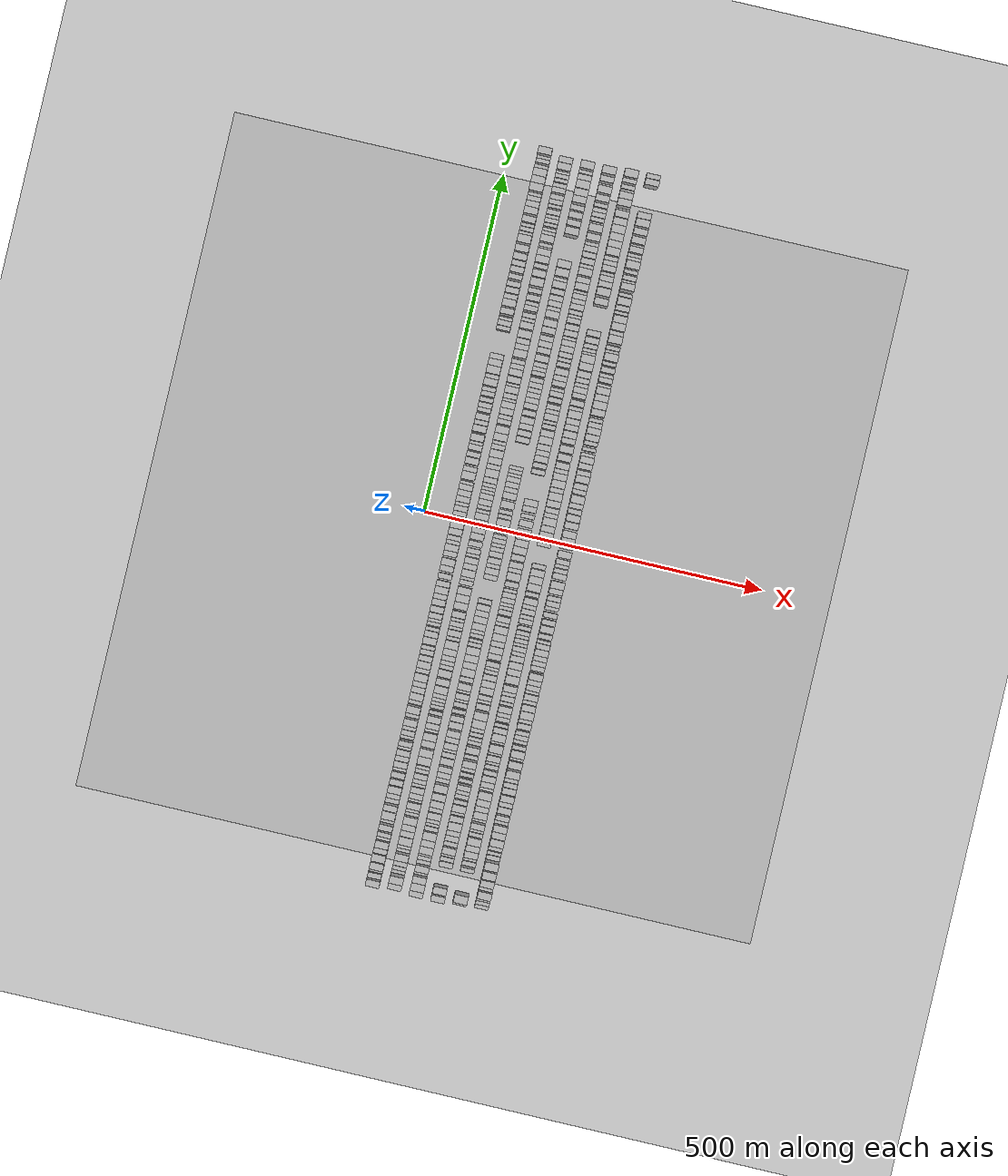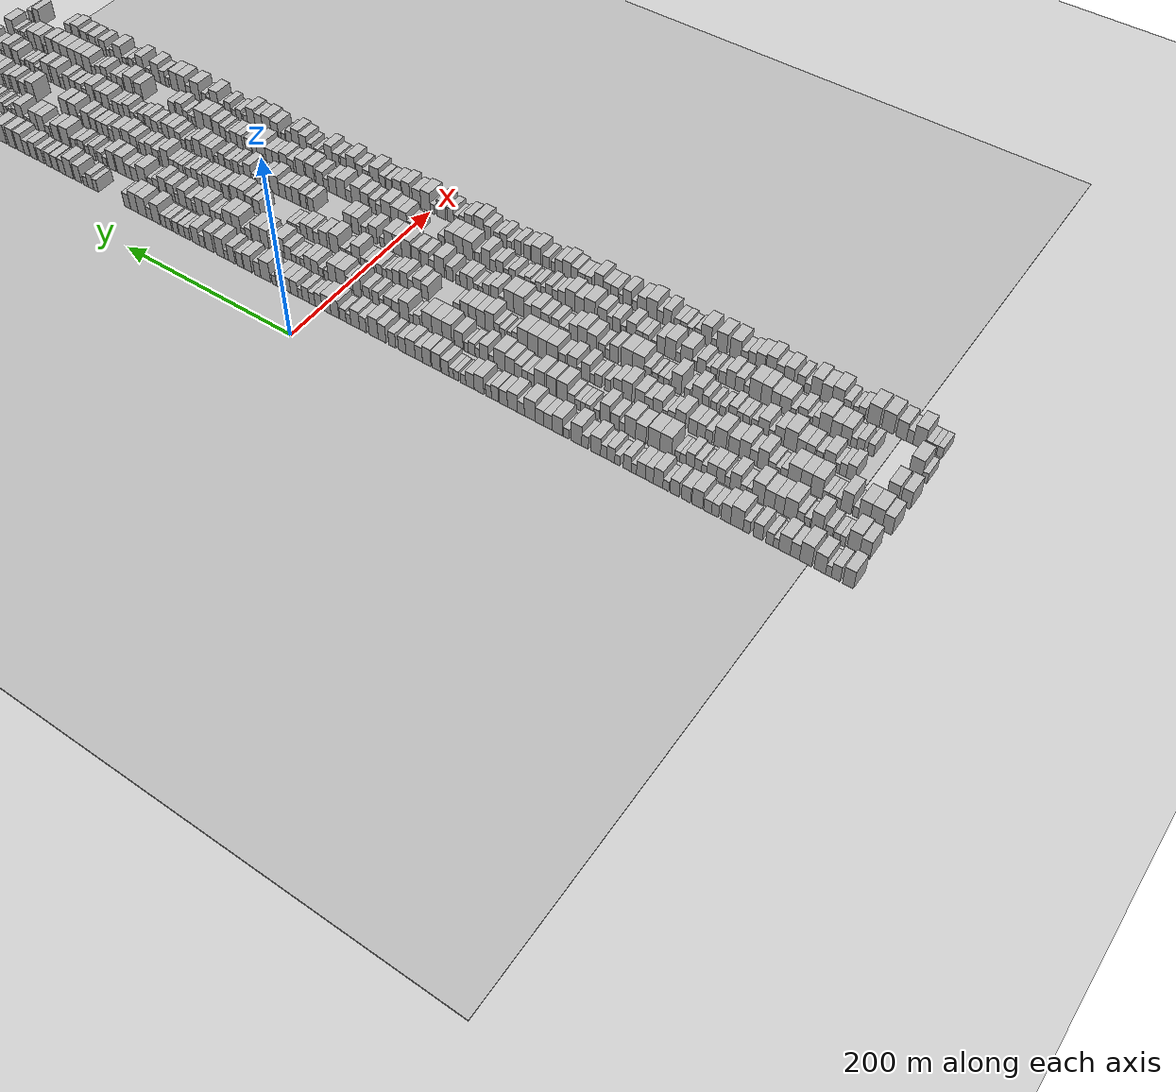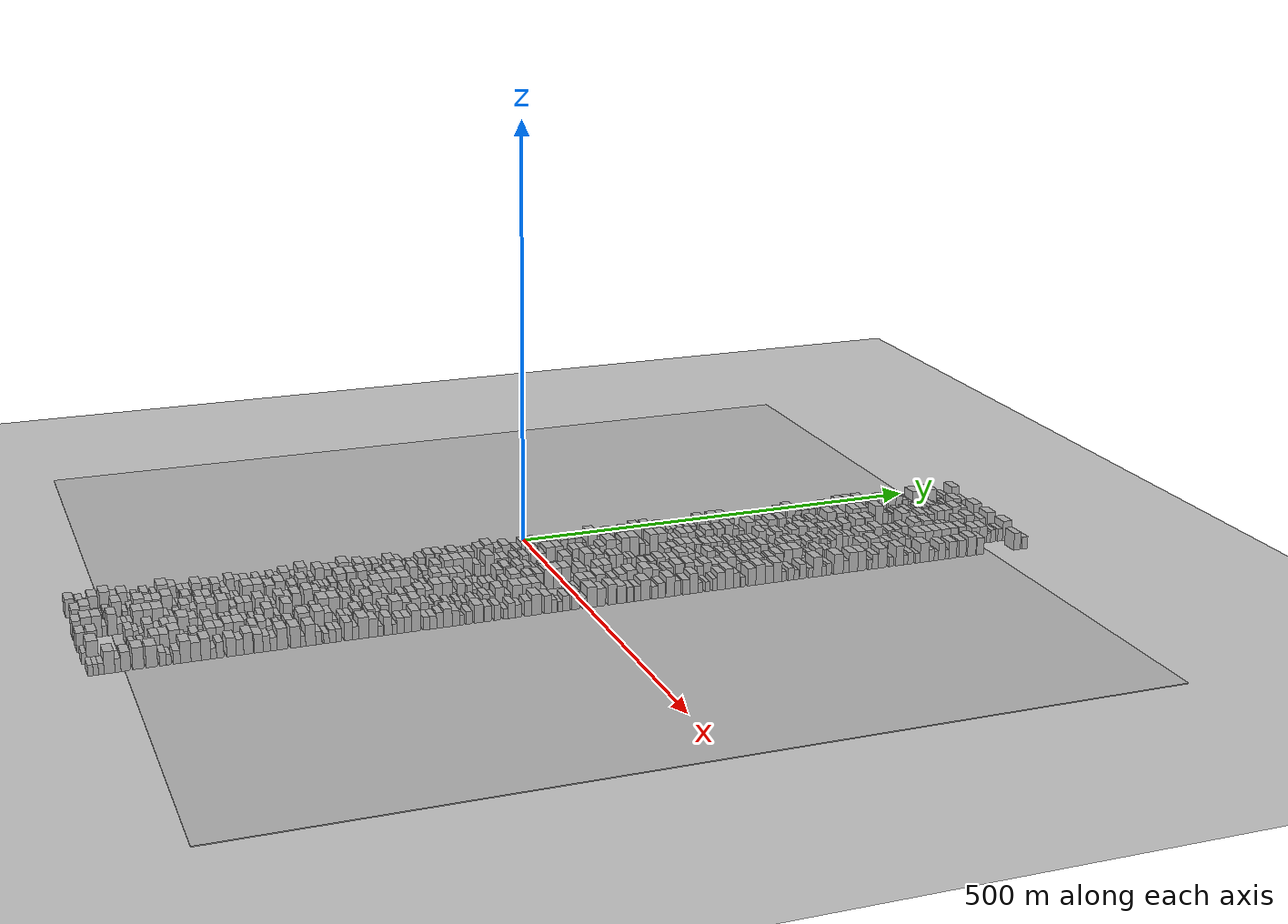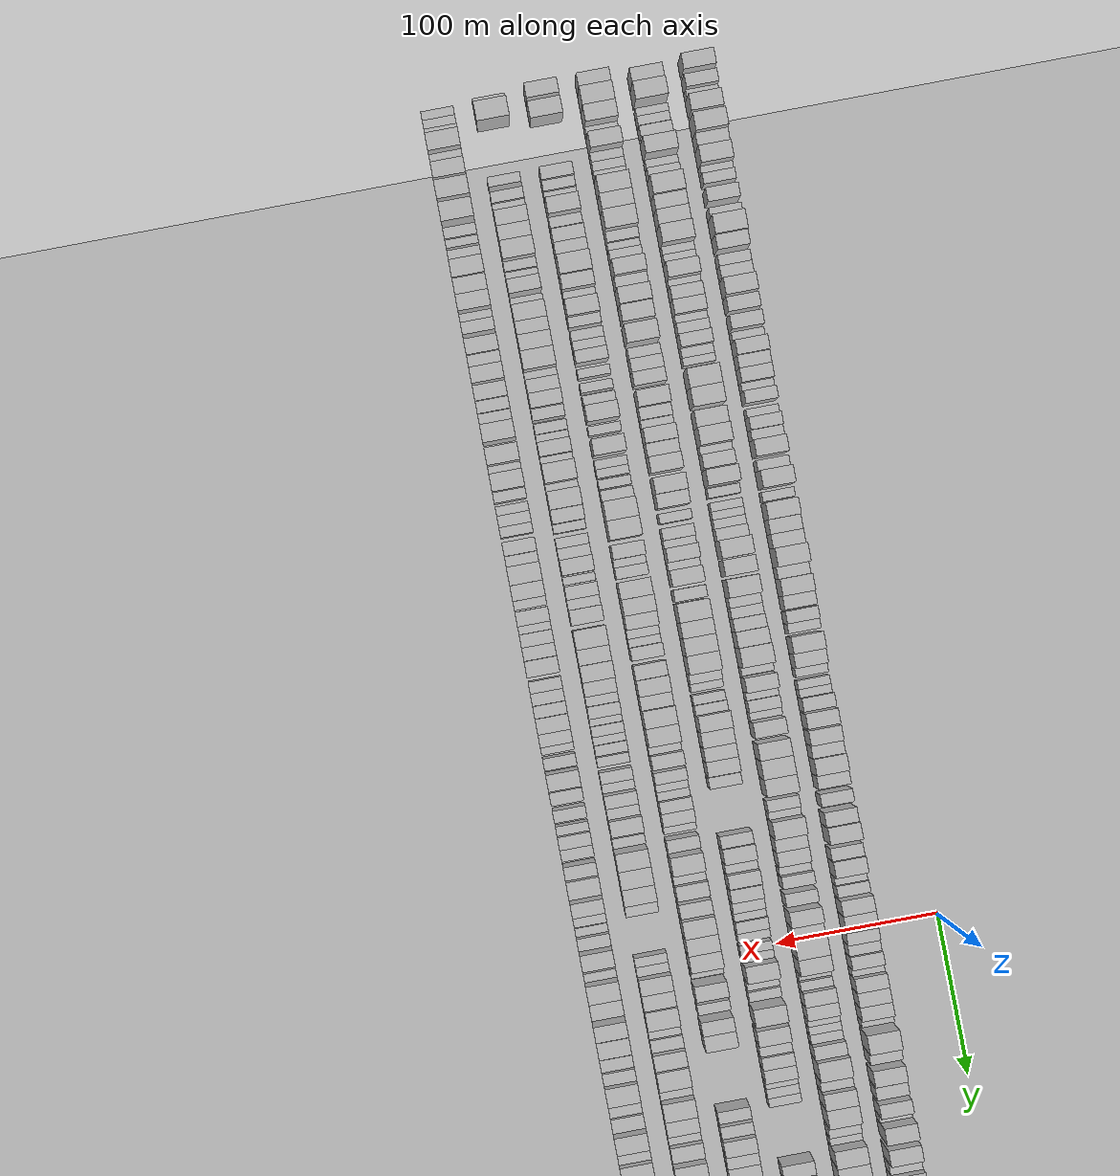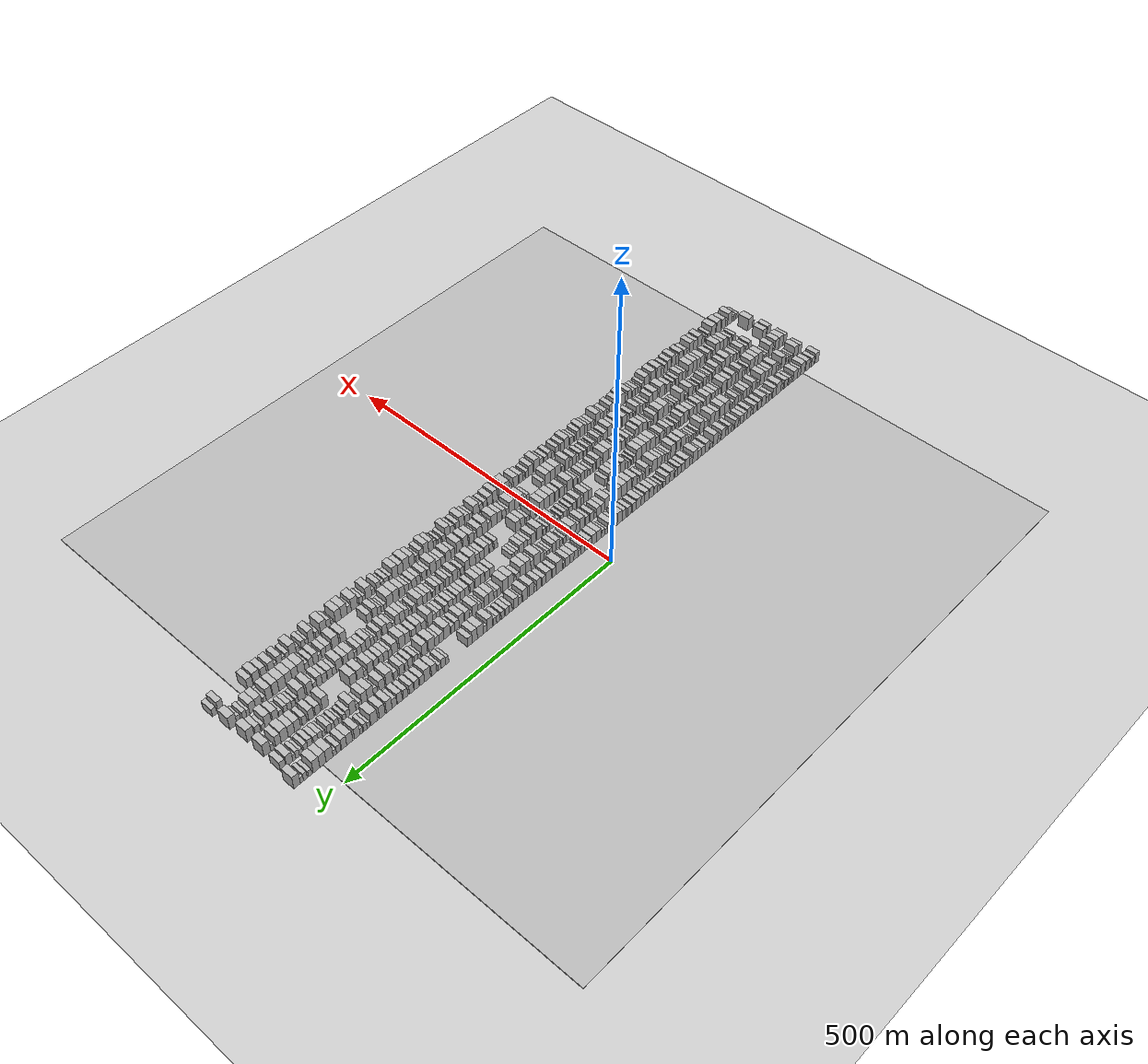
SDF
<?xml version="1.0" encoding="utf-8"?>

<sdf version="1.6">

   <world name="default">

      <gui fullscreen="0">

         <camera name="user_camera">

            <pose>-15 0 4.57585 0 0 0</pose>

            <view_controller>orbit</view_controller>

         </camera>

      </gui>

      <scene>

         <sky>

           <clouds>

             <speed>12</speed>

           </clouds>

         </sky>

         <ambient>0.4 0.4 0.4 1</ambient>

         <background>0.7 0.7 0.7 1</background>

         <shadows>1</shadows>

      </scene>

      <gravity>0 0 -9.8066</gravity>

      <magnetic_field>6e-06 2.3e-05 -4.2e-05</magnetic_field>

      <physics default="0" name="default_physics" type="ode">

         <ode>

            <solver>

               <type>quick</type>

               <iters>10</iters>

               <sor>1.0</sor>

               <use_dynamic_moi_rescaling>0</use_dynamic_moi_rescaling>

            </solver>

            <constraints>

               <cfm>0</cfm>

               <erp>0.2</erp>

               <contact_max_correcting_vel>100</contact_max_correcting_vel>

               <contact_surface_layer>0.001</contact_surface_layer>

            </constraints>

         </ode>

         <max_step_size>0.004</max_step_size>

         <real_time_factor>1</real_time_factor>

         <real_time_update_rate>250</real_time_update_rate>

      </physics>

      <light name="sun" type="directional">

         <cast_shadows>1</cast_shadows>

         <pose>0 0 10 0 0 0</pose>

         <diffuse>0.8 0.8 0.8 1</diffuse>

         <specular>0.2 0.2 0.2 1</specular>

         <attenuation>

            <range>1000</range>

            <constant>0.9</constant>

            <linear>0.01</linear>

            <quadratic>0.001</quadratic>

         </attenuation>

         <direction>-0.5 0.1 -0.9</direction>

      </light>

      <include>

         <name>ground_plane_1</name>

         <uri>model://HANNAS_ground_plane</uri>

         <pose>0 0 0  0 0 0</pose>

      </include>

      <include>

         <name>ground_plane_2</name>

         <uri>model://HANNAS_ground_plane</uri>

         <pose>100 0 0  0 0 0</pose>

      </include>

      <model name="building_1">

         <static>1</static>

         <pose frame="">50.0000 -535.1591 0 0.000000 0.000000 0.000000</pose>

         <link name="link">

            <pose frame="">0 0 10.50 0 0 0</pose>

            <collision name="collision">

               <geometry>

                  <box>

                     <size>20.0000 9.6819 21.0000</size>

                  </box>

               </geometry>

               <max_contacts>10</max_contacts>

               <surface>

                  <contact>

                     <ode/>

                  </contact>

                  <bounce/>

                  <friction>

                     <torsional>

                        <ode/>

                     </torsional>

                     <ode/>

                  </friction>

               </surface>

            </collision>

            <visual name="visual">

               <cast_shadows>0</cast_shadows>

               <geometry>

                  <box>

                     <size>20.0000 9.6819 21.0000</size>

                  </box>

               </geometry>

               <material>

                  <script>

                     <uri>model://HANNAS_wall/materials/scripts</uri>

                     <uri>model://HANNAS_wall/materials/textures</uri>

                     <name>vrc/HANNAS_wall</name>

                  </script>

               </material>

            </visual>

            <self_collide>0</self_collide>

            <enable_wind>0</enable_wind>

            <kinematic>0</kinematic>

         </link>

      </model>

      <model name="building_2">

         <static>1</static>

         <pose frame="">50.0000 -524.3682 0 0.000000 0.000000 0.000000</pose>

         <link name="link">

            <pose frame="">0 0 9.00 0 0 0</pose>

            <collision name="collision">

               <geometry>

                  <box>

                     <size>20.0000 7.8999 18.0000</size>

                  </box>

               </geometry>

               <max_contacts>10</max_contacts>

               <surface>

                  <contact>

                     <ode/>

                  </contact>

                  <bounce/>

                  <friction>

                     <torsional>

                        <ode/>

                     </torsional>

                     <ode/>

                  </friction>

               </surface>

            </collision>

            <visual name="visual">

               <cast_shadows>0</cast_shadows>

               <geometry>

                  <box>

                     <size>20.0000 7.8999 18.0000</size>

                  </box>

               </geometry>

               <material>

                  <script>

                     <uri>model://HANNAS_wall/materials/scripts</uri>

                     <uri>model://HANNAS_wall/materials/textures</uri>

                     <name>vrc/HANNAS_wall</name>

                  </script>

               </material>

            </visual>

            <self_collide>0</self_collide>

            <enable_wind>0</enable_wind>

            <kinematic>0</kinematic>

         </link>

      </model>

      <model name="building_3">

         <static>1</static>

         <pose frame="">50.0000 -517.8946 0 0.000000 0.000000 0.000000</pose>

         <link name="link">

            <pose frame="">0 0 6.00 0 0 0</pose>

            <collision name="collision">

               <geometry>

                  <box>

                     <size>20.0000 5.0474 12.0000</size>

                  </box>

               </geometry>

               <max_contacts>10</max_contacts>

               <surface>

                  <contact>

                     <ode/>

                  </contact>

                  <bounce/>

                  <friction>

                     <torsional>

                        <ode/>

                     </torsional>

                     <ode/>

                  </friction>

               </surface>

            </collision>

            <visual name="visual">

               <cast_shadows>0</cast_shadows>

               <geometry>

                  <box>

                     <size>20.0000 5.0474 12.0000</size>

                  </box>

               </geometry>

               <material>

                  <script>

                     <uri>model://HANNAS_wall/materials/scripts</uri>

                     <uri>model://HANNAS_wall/materials/textures</uri>

                     <name>vrc/HANNAS_wall</name>

                  </script>

               </material>

            </visual>

            <self_collide>0</self_collide>

            <enable_wind>0</enable_wind>

            <kinematic>0</kinematic>

         </link>

      </model>

      <model name="building_4">

         <static>1</static>

         <pose frame="">50.0000 -510.2732 0 0.000000 0.000000 0.000000</pose>

         <link name="link">

            <pose frame="">0 0 10.50 0 0 0</pose>

            <collision name="collision">

               <geometry>

                  <box>

                     <size>20.0000 10.1953 21.0000</size>

                  </box>

               </geometry>

               <max_contacts>10</max_contacts>

               <surface>

                  <contact>

                     <ode/>

                  </contact>

                  <bounce/>

                  <friction>

                     <torsional>

                        <ode/>

                     </torsional>

                     <ode/>

                  </friction>

               </surface>

            </collision>

            <visual name="visual">

               <cast_shadows>0</cast_shadows>

               <geometry>

                  <box>

                     <size>20.0000 10.1953 21.0000</size>

                  </box>

               </geometry>

               <material>

                  <script>

                     <uri>model://HANNAS_wall/materials/scripts</uri>

                     <uri>model://HANNAS_wall/materials/textures</uri>

                     <name>vrc/HANNAS_wall</name>

                  </script>

               </material>

            </visual>

            <self_collide>0</self_collide>

            <enable_wind>0</enable_wind>

            <kinematic>0</kinematic>

         </link>

      </model>

      <model name="building_5">

         <static>1</static>

         <pose frame="">50.0000 -497.6491 0 0.000000 0.000000 0.000000</pose>

         <link name="link">

            <pose frame="">0 0 12.00 0 0 0</pose>

            <collision name="collision">

               <geometry>

                  <box>

                     <size>20.0000 11.0528 24.0000</size>

                  </box>

               </geometry>

               <max_contacts>10</max_contacts>

               <surface>

                  <contact>

                     <ode/>

                  </contact>

                  <bounce/>

                  <friction>

                     <torsional>

                        <ode/>

                     </torsional>

                     <ode/>

                  </friction>

               </surface>

            </collision>

            <visual name="visual">

               <cast_shadows>0</cast_shadows>

               <geometry>

                  <box>

                     <size>20.0000 11.0528 24.0000</size>

                  </box>

               </geometry>

               <material>

                  <script>

                     <uri>model://HANNAS_wall/materials/scripts</uri>

                     <uri>model://HANNAS_wall/materials/textures</uri>

                     <name>vrc/HANNAS_wall</name>

                  </script>

               </material>

            </visual>

            <self_collide>0</self_collide>

            <enable_wind>0</enable_wind>

            <kinematic>0</kinematic>

         </link>

      </model>

      <model name="building_6">

         <static>1</static>

         <pose frame="">50.0000 -487.9320 0 0.000000 0.000000 0.000000</pose>

         <link name="link">

            <pose frame="">0 0 9.00 0 0 0</pose>

            <collision name="collision">

               <geometry>

                  <box>

                     <size>20.0000 8.3814 18.0000</size>

                  </box>

               </geometry>

               <max_contacts>10</max_contacts>

               <surface>

                  <contact>

                     <ode/>

                  </contact>

                  <bounce/>

                  <friction>

                     <torsional>

                        <ode/>

                     </torsional>

                     <ode/>

                  </friction>

               </surface>

            </collision>

            <visual name="visual">

               <cast_shadows>0</cast_shadows>

               <geometry>

                  <box>

                     <size>20.0000 8.3814 18.0000</size>

                  </box>

               </geometry>

               <material>

                  <script>

                     <uri>model://HANNAS_wall/materials/scripts</uri>

                     <uri>model://HANNAS_wall/materials/textures</uri>

                     <name>vrc/HANNAS_wall</name>

                  </script>

               </material>

            </visual>

            <self_collide>0</self_collide>

            <enable_wind>0</enable_wind>

            <kinematic>0</kinematic>

         </link>

      </model>

      <model name="building_7">

         <static>1</static>

         <pose frame="">50.0000 -478.5148 0 0.000000 0.000000 0.000000</pose>

         <link name="link">

            <pose frame="">0 0 10.50 0 0 0</pose>

            <collision name="collision">

               <geometry>

                  <box>

                     <size>20.0000 10.4531 21.0000</size>

                  </box>

               </geometry>

               <max_contacts>10</max_contacts>

               <surface>

                  <contact>

                     <ode/>

                  </contact>

                  <bounce/>

                  <friction>

                     <torsional>

                        <ode/>

                     </torsional>

                     <ode/>

                  </friction>

               </surface>

            </collision>

            <visual name="visual">

               <cast_shadows>0</cast_shadows>

               <geometry>

                  <box>

                     <size>20.0000 10.4531 21.0000</size>

                  </box>

               </geometry>

               <material>

                  <script>

                     <uri>model://HANNAS_wall/materials/scripts</uri>

                     <uri>model://HANNAS_wall/materials/textures</uri>

                     <name>vrc/HANNAS_wall</name>

                  </script>

               </material>

            </visual>

            <self_collide>0</self_collide>

            <enable_wind>0</enable_wind>

            <kinematic>0</kinematic>

         </link>

      </model>

      <model name="building_8">

         <static>1</static>

         <pose frame="">50.0000 -470.8040 0 0.000000 0.000000 0.000000</pose>

         <link name="link">

            <pose frame="">0 0 6.00 0 0 0</pose>

            <collision name="collision">

               <geometry>

                  <box>

                     <size>20.0000 4.9684 12.0000</size>

                  </box>

               </geometry>

               <max_contacts>10</max_contacts>

               <surface>

                  <contact>

                     <ode/>

                  </contact>

                  <bounce/>

                  <friction>

                     <torsional>

                        <ode/>

                     </torsional>

                     <ode/>

                  </friction>

               </surface>

            </collision>

            <visual name="visual">

               <cast_shadows>0</cast_shadows>

               <geometry>

                  <box>

                     <size>20.0000 4.9684 12.0000</size>

                  </box>

               </geometry>

               <material>

                  <script>

                     <uri>model://HANNAS_wall/materials/scripts</uri>

                     <uri>model://HANNAS_wall/materials/textures</uri>

                     <name>vrc/HANNAS_wall</name>

                  </script>

               </material>

            </visual>

            <self_collide>0</self_collide>

            <enable_wind>0</enable_wind>

            <kinematic>0</kinematic>

         </link>

      </model>

      <model name="building_9">

         <static>1</static>

         <pose frame="">50.0000 -464.9939 0 0.000000 0.000000 0.000000</pose>

         <link name="link">

            <pose frame="">0 0 7.50 0 0 0</pose>

            <collision name="collision">

               <geometry>

                  <box>

                     <size>20.0000 6.6517 15.0000</size>

                  </box>

               </geometry>

               <max_contacts>10</max_contacts>

               <surface>

                  <contact>

                     <ode/>

                  </contact>

                  <bounce/>

                  <friction>

                     <torsional>

                        <ode/>

                     </torsional>

                     <ode/>

                  </friction>

               </surface>

            </collision>

            <visual name="visual">

               <cast_shadows>0</cast_shadows>

               <geometry>

                  <box>

                     <size>20.0000 6.6517 15.0000</size>

                  </box>

               </geometry>

               <material>

                  <script>

                     <uri>model://HANNAS_wall/materials/scripts</uri>

                     <uri>model://HANNAS_wall/materials/textures</uri>

                     <name>vrc/HANNAS_wall</name>

                  </script>

               </material>

            </visual>

            <self_collide>0</self_collide>

            <enable_wind>0</enable_wind>

            <kinematic>0</kinematic>

         </link>

      </model>

      <model name="building_10">

         <static>1</static>

         <pose frame="">50.0000 -454.3655 0 0.000000 0.000000 0.000000</pose>

         <link name="link">

            <pose frame="">0 0 9.00 0 0 0</pose>

            <collision name="collision">

               <geometry>

                  <box>

                     <size>20.0000 8.6052 18.0000</size>

                  </box>

               </geometry>

               <max_contacts>10</max_contacts>

               <surface>

                  <contact>

                     <ode/>

                  </contact>

                  <bounce/>

                  <friction>

                     <torsional>

                        <ode/>

                     </torsional>

                     <ode/>

                  </friction>

               </surface>

            </collision>

            <visual name="visual">

               <cast_shadows>0</cast_shadows>

               <geometry>

                  <box>

                     <size>20.0000 8.6052 18.0000</size>

                  </box>

               </geometry>

               <material>

                  <script>

                     <uri>model://HANNAS_wall/materials/scripts</uri>

                     <uri>model://HANNAS_wall/materials/textures</uri>

                     <name>vrc/HANNAS_wall</name>

                  </script>

               </material>

            </visual>

            <self_collide>0</self_collide>

            <enable_wind>0</enable_wind>

            <kinematic>0</kinematic>

         </link>

      </model>

      <model name="building_11">

         <static>1</static>

         <pose frame="">50.0000 -444.0295 0 0.000000 0.000000 0.000000</pose>

         <link name="link">

            <pose frame="">0 0 7.50 0 0 0</pose>

            <collision name="collision">

               <geometry>

                  <box>

                     <size>20.0000 6.0667 15.0000</size>

                  </box>

               </geometry>

               <max_contacts>10</max_contacts>

               <surface>

                  <contact>

                     <ode/>

                  </contact>

                  <bounce/>

                  <friction>

                     <torsional>

                        <ode/>

                     </torsional>

                     <ode/>

                  </friction>

               </surface>

            </collision>

            <visual name="visual">

               <cast_shadows>0</cast_shadows>

               <geometry>

                  <box>

                     <size>20.0000 6.0667 15.0000</size>

                  </box>

               </geometry>

               <material>

                  <script>

                     <uri>model://HANNAS_wall/materials/scripts</uri>

                     <uri>model://HANNAS_wall/materials/textures</uri>

                     <name>vrc/HANNAS_wall</name>

                  </script>

               </material>

            </visual>

            <self_collide>0</self_collide>

            <enable_wind>0</enable_wind>

            <kinematic>0</kinematic>

         </link>

      </model>

      <model name="building_12">

         <static>1</static>

         <pose frame="">50.0000 -435.0971 0 0.000000 0.000000 0.000000</pose>

         <link name="link">

            <pose frame="">0 0 12.00 0 0 0</pose>

            <collision name="collision">

               <geometry>

                  <box>

                     <size>20.0000 11.7982 24.0000</size>

                  </box>

               </geometry>

               <max_contacts>10</max_contacts>

               <surface>

                  <contact>

                     <ode/>

                  </contact>

                  <bounce/>

                  <friction>

                     <torsional>

                        <ode/>

                     </torsional>

                     <ode/>

                  </friction>

               </surface>

            </collision>

            <visual name="visual">

               <cast_shadows>0</cast_shadows>

               <geometry>

                  <box>

                     <size>20.0000 11.7982 24.0000</size>

                  </box>

               </geometry>

               <material>

                  <script>

                     <uri>model://HANNAS_wall/materials/scripts</uri>

                     <uri>model://HANNAS_wall/materials/textures</uri>

                     <name>vrc/HANNAS_wall</name>

                  </script>

               </material>

            </visual>

            <self_collide>0</self_collide>

            <enable_wind>0</enable_wind>

            <kinematic>0</kinematic>

         </link>

      </model>

      <model name="building_13">

         <static>1</static>

         <pose frame="">50.0000 -424.6937 0 0.000000 0.000000 0.000000</pose>

         <link name="link">

            <pose frame="">0 0 10.50 0 0 0</pose>

            <collision name="collision">

               <geometry>

                  <box>

                     <size>20.0000 9.0084 21.0000</size>

                  </box>

               </geometry>

               <max_contacts>10</max_contacts>

               <surface>

                  <contact>

                     <ode/>

                  </contact>

                  <bounce/>

                  <friction>

                     <torsional>

                        <ode/>

                     </torsional>

                     <ode/>

                  </friction>

               </surface>

            </collision>

            <visual name="visual">

               <cast_shadows>0</cast_shadows>

               <geometry>

                  <box>

                     <size>20.0000 9.0084 21.0000</size>

                  </box>

               </geometry>

               <material>

                  <script>

                     <uri>model://HANNAS_wall/materials/scripts</uri>

                     <uri>model://HANNAS_wall/materials/textures</uri>

                     <name>vrc/HANNAS_wall</name>

                  </script>

               </material>

            </visual>

            <self_collide>0</self_collide>

            <enable_wind>0</enable_wind>

            <kinematic>0</kinematic>

         </link>

      </model>

      <model name="building_14">

         <static>1</static>

         <pose frame="">50.0000 -414.7915 0 0.000000 0.000000 0.000000</pose>

         <link name="link">

            <pose frame="">0 0 7.50 0 0 0</pose>

            <collision name="collision">

               <geometry>

                  <box>

                     <size>20.0000 6.7960 15.0000</size>

                  </box>

               </geometry>

               <max_contacts>10</max_contacts>

               <surface>

                  <contact>

                     <ode/>

                  </contact>

                  <bounce/>

                  <friction>

                     <torsional>

                        <ode/>

                     </torsional>

                     <ode/>

                  </friction>

               </surface>

            </collision>

            <visual name="visual">

               <cast_shadows>0</cast_shadows>

               <geometry>

                  <box>

                     <size>20.0000 6.7960 15.0000</size>

                  </box>

               </geometry>

               <material>

                  <script>

                     <uri>model://HANNAS_wall/materials/scripts</uri>

                     <uri>model://HANNAS_wall/materials/textures</uri>

                     <name>vrc/HANNAS_wall</name>

                  </script>

               </material>

            </visual>

            <self_collide>0</self_collide>

            <enable_wind>0</enable_wind>

            <kinematic>0</kinematic>

         </link>

      </model>

      <model name="building_15">

         <static>1</static>

         <pose frame="">50.0000 -407.7959 0 0.000000 0.000000 0.000000</pose>

         <link name="link">

            <pose frame="">0 0 7.50 0 0 0</pose>

            <collision name="collision">

               <geometry>

                  <box>

                     <size>20.0000 7.1952 15.0000</size>

                  </box>

               </geometry>

               <max_contacts>10</max_contacts>

               <surface>

                  <contact>

                     <ode/>

                  </contact>

                  <bounce/>

                  <friction>

                     <torsional>

                        <ode/>

                     </torsional>

                     <ode/>

                  </friction>

               </surface>

            </collision>

            <visual name="visual">

               <cast_shadows>0</cast_shadows>

               <geometry>

                  <box>

                     <size>20.0000 7.1952 15.0000</size>

                  </box>

               </geometry>

               <material>

                  <script>

                     <uri>model://HANNAS_wall/materials/scripts</uri>

                     <uri>model://HANNAS_wall/materials/textures</uri>

                     <name>vrc/HANNAS_wall</name>

                  </script>

               </material>

            </visual>

            <self_collide>0</self_collide>

            <enable_wind>0</enable_wind>

            <kinematic>0</kinematic>

         </link>

      </model>

      <model name="building_16">

         <static>1</static>

         <pose frame="">50.0000 -397.9881 0 0.000000 0.000000 0.000000</pose>

         <link name="link">

            <pose frame="">0 0 10.50 0 0 0</pose>

            <collision name="collision">

               <geometry>

                  <box>

                     <size>20.0000 10.4205 21.0000</size>

                  </box>

               </geometry>

               <max_contacts>10</max_contacts>

               <surface>

                  <contact>

                     <ode/>

                  </contact>

                  <bounce/>

                  <friction>

                     <torsional>

                        <ode/>

                     </torsional>

                     <ode/>

                  </friction>

               </surface>

            </collision>

            <visual name="visual">

               <cast_shadows>0</cast_shadows>

               <geometry>

                  <box>

                     <size>20.0000 10.4205 21.0000</size>

                  </box>

               </geometry>

               <material>

                  <script>

                     <uri>model://HANNAS_wall/materials/scripts</uri>

                     <uri>model://HANNAS_wall/materials/textures</uri>

                     <name>vrc/HANNAS_wall</name>

                  </script>

               </material>

            </visual>

            <self_collide>0</self_collide>

            <enable_wind>0</enable_wind>

            <kinematic>0</kinematic>

         </link>

      </model>

      <model name="building_17">

         <static>1</static>

         <pose frame="">50.0000 -387.3474 0 0.000000 0.000000 0.000000</pose>

         <link name="link">

            <pose frame="">0 0 9.00 0 0 0</pose>

            <collision name="collision">

               <geometry>

                  <box>

                     <size>20.0000 8.8608 18.0000</size>

                  </box>

               </geometry>

               <max_contacts>10</max_contacts>

               <surface>

                  <contact>

                     <ode/>

                  </contact>

                  <bounce/>

                  <friction>

                     <torsional>

                        <ode/>

                     </torsional>

                     <ode/>

                  </friction>

               </surface>

            </collision>

            <visual name="visual">

               <cast_shadows>0</cast_shadows>

               <geometry>

                  <box>

                     <size>20.0000 8.8608 18.0000</size>

                  </box>

               </geometry>

               <material>

                  <script>

                     <uri>model://HANNAS_wall/materials/scripts</uri>

                     <uri>model://HANNAS_wall/materials/textures</uri>

                     <name>vrc/HANNAS_wall</name>

                  </script>

               </material>

            </visual>

            <self_collide>0</self_collide>

            <enable_wind>0</enable_wind>

            <kinematic>0</kinematic>

         </link>

      </model>

      <model name="building_18">

         <static>1</static>

         <pose frame="">50.0000 -376.5209 0 0.000000 0.000000 0.000000</pose>

         <link name="link">

            <pose frame="">0 0 9.00 0 0 0</pose>

            <collision name="collision">

               <geometry>

                  <box>

                     <size>20.0000 8.7922 18.0000</size>

                  </box>

               </geometry>

               <max_contacts>10</max_contacts>

               <surface>

                  <contact>

                     <ode/>

                  </contact>

                  <bounce/>

                  <friction>

                     <torsional>

                        <ode/>

                     </torsional>

                     <ode/>

                  </friction>

               </surface>

            </collision>

            <visual name="visual">

               <cast_shadows>0</cast_shadows>

               <geometry>

                  <box>

                     <size>20.0000 8.7922 18.0000</size>

                  </box>

               </geometry>

               <material>

                  <script>

                     <uri>model://HANNAS_wall/materials/scripts</uri>

                     <uri>model://HANNAS_wall/materials/textures</uri>

                     <name>vrc/HANNAS_wall</name>

                  </script>

               </material>

            </visual>

            <self_collide>0</self_collide>

            <enable_wind>0</enable_wind>

            <kinematic>0</kinematic>

         </link>

      </model>

      <model name="building_19">

         <static>1</static>

         <pose frame="">50.0000 -368.1460 0 0.000000 0.000000 0.000000</pose>

         <link name="link">

            <pose frame="">0 0 6.00 0 0 0</pose>

            <collision name="collision">

               <geometry>

                  <box>

                     <size>20.0000 5.9575 12.0000</size>

                  </box>

               </geometry>

               <max_contacts>10</max_contacts>

               <surface>

                  <contact>

                     <ode/>

                  </contact>

                  <bounce/>

                  <friction>

                     <torsional>

                        <ode/>

                     </torsional>

                     <ode/>

                  </friction>

               </surface>

            </collision>

            <visual name="visual">

               <cast_shadows>0</cast_shadows>

               <geometry>

                  <box>

                     <size>20.0000 5.9575 12.0000</size>

                  </box>

               </geometry>

               <material>

                  <script>

                     <uri>model://HANNAS_wall/materials/scripts</uri>

                     <uri>model://HANNAS_wall/materials/textures</uri>

                     <name>vrc/HANNAS_wall</name>

                  </script>

               </material>

            </visual>

            <self_collide>0</self_collide>

            <enable_wind>0</enable_wind>

            <kinematic>0</kinematic>

         </link>

      </model>

      <model name="building_20">

         <static>1</static>

         <pose frame="">50.0000 -360.6383 0 0.000000 0.000000 0.000000</pose>

         <link name="link">

            <pose frame="">0 0 10.50 0 0 0</pose>

            <collision name="collision">

               <geometry>

                  <box>

                     <size>20.0000 9.0580 21.0000</size>

                  </box>

               </geometry>

               <max_contacts>10</max_contacts>

               <surface>

                  <contact>

                     <ode/>

                  </contact>

                  <bounce/>

                  <friction>

                     <torsional>

                        <ode/>

                     </torsional>

                     <ode/>

                  </friction>

               </surface>

            </collision>

            <visual name="visual">

               <cast_shadows>0</cast_shadows>

               <geometry>

                  <box>

                     <size>20.0000 9.0580 21.0000</size>

                  </box>

               </geometry>

               <material>

                  <script>

                     <uri>model://HANNAS_wall/materials/scripts</uri>

                     <uri>model://HANNAS_wall/materials/textures</uri>

                     <name>vrc/HANNAS_wall</name>

                  </script>

               </material>

            </visual>

            <self_collide>0</self_collide>

            <enable_wind>0</enable_wind>

            <kinematic>0</kinematic>

         </link>

      </model>

      <model name="building_21">

         <static>1</static>

         <pose frame="">50.0000 -352.2308 0 0.000000 0.000000 0.000000</pose>

         <link name="link">

            <pose frame="">0 0 9.00 0 0 0</pose>

            <collision name="collision">

               <geometry>

                  <box>

                     <size>20.0000 7.7570 18.0000</size>

                  </box>

               </geometry>

               <max_contacts>10</max_contacts>

               <surface>

                  <contact>

                     <ode/>

                  </contact>

                  <bounce/>

                  <friction>

                     <torsional>

                        <ode/>

                     </torsional>

                     <ode/>

                  </friction>

               </surface>

            </collision>

            <visual name="visual">

               <cast_shadows>0</cast_shadows>

               <geometry>

                  <box>

                     <size>20.0000 7.7570 18.0000</size>

                  </box>

               </geometry>

               <material>

                  <script>

                     <uri>model://HANNAS_wall/materials/scripts</uri>

                     <uri>model://HANNAS_wall/materials/textures</uri>

                     <name>vrc/HANNAS_wall</name>

                  </script>

               </material>

            </visual>

            <self_collide>0</self_collide>

            <enable_wind>0</enable_wind>

            <kinematic>0</kinematic>

         </link>

      </model>

      <model name="building_22">

         <static>1</static>

         <pose frame="">50.0000 -344.0034 0 0.000000 0.000000 0.000000</pose>

         <link name="link">

            <pose frame="">0 0 9.00 0 0 0</pose>

            <collision name="collision">

               <geometry>

                  <box>

                     <size>20.0000 8.6980 18.0000</size>

                  </box>

               </geometry>

               <max_contacts>10</max_contacts>

               <surface>

                  <contact>

                     <ode/>

                  </contact>

                  <bounce/>

                  <friction>

                     <torsional>

                        <ode/>

                     </torsional>

                     <ode/>

                  </friction>

               </surface>

            </collision>

            <visual name="visual">

               <cast_shadows>0</cast_shadows>

               <geometry>

                  <box>

                     <size>20.0000 8.6980 18.0000</size>

                  </box>

               </geometry>

               <material>

                  <script>

                     <uri>model://HANNAS_wall/materials/scripts</uri>

                     <uri>model://HANNAS_wall/materials/textures</uri>

                     <name>vrc/HANNAS_wall</name>

                  </script>

               </material>

            </visual>

            <self_collide>0</self_collide>

            <enable_wind>0</enable_wind>

            <kinematic>0</kinematic>

         </link>

      </model>

      <model name="building_23">

         <static>1</static>

         <pose frame="">50.0000 -337.0543 0 0.000000 0.000000 0.000000</pose>

         <link name="link">

            <pose frame="">0 0 6.00 0 0 0</pose>

            <collision name="collision">

               <geometry>

                  <box>

                     <size>20.0000 5.2001 12.0000</size>

                  </box>

               </geometry>

               <max_contacts>10</max_contacts>

               <surface>

                  <contact>

                     <ode/>

                  </contact>

                  <bounce/>

                  <friction>

                     <torsional>

                        <ode/>

                     </torsional>

                     <ode/>

                  </friction>

               </surface>

            </collision>

            <visual name="visual">

               <cast_shadows>0</cast_shadows>

               <geometry>

                  <box>

                     <size>20.0000 5.2001 12.0000</size>

                  </box>

               </geometry>

               <material>

                  <script>

                     <uri>model://HANNAS_wall/materials/scripts</uri>

                     <uri>model://HANNAS_wall/materials/textures</uri>

                     <name>vrc/HANNAS_wall</name>

                  </script>

               </material>

            </visual>

            <self_collide>0</self_collide>

            <enable_wind>0</enable_wind>

            <kinematic>0</kinematic>

         </link>

      </model>

      <model name="building_24">

         <static>1</static>

         <pose frame="">50.0000 -330.5695 0 0.000000 0.000000 0.000000</pose>

         <link name="link">

            <pose frame="">0 0 9.00 0 0 0</pose>

            <collision name="collision">

               <geometry>

                  <box>

                     <size>20.0000 7.7696 18.0000</size>

                  </box>

               </geometry>

               <max_contacts>10</max_contacts>

               <surface>

                  <contact>

                     <ode/>

                  </contact>

                  <bounce/>

                  <friction>

                     <torsional>

                        <ode/>

                     </torsional>

                     <ode/>

                  </friction>

               </surface>

            </collision>

            <visual name="visual">

               <cast_shadows>0</cast_shadows>

               <geometry>

                  <box>

                     <size>20.0000 7.7696 18.0000</size>

                  </box>

               </geometry>

               <material>

                  <script>

                     <uri>model://HANNAS_wall/materials/scripts</uri>

                     <uri>model://HANNAS_wall/materials/textures</uri>

                     <name>vrc/HANNAS_wall</name>

                  </script>

               </material>

            </visual>

            <self_collide>0</self_collide>

            <enable_wind>0</enable_wind>

            <kinematic>0</kinematic>

         </link>

      </model>

      <model name="building_25">

         <static>1</static>

         <pose frame="">50.0000 -320.9729 0 0.000000 0.000000 0.000000</pose>

         <link name="link">

            <pose frame="">0 0 6.00 0 0 0</pose>

            <collision name="collision">

               <geometry>

                  <box>

                     <size>20.0000 5.4237 12.0000</size>

                  </box>

               </geometry>

               <max_contacts>10</max_contacts>

               <surface>

                  <contact>

                     <ode/>

                  </contact>

                  <bounce/>

                  <friction>

                     <torsional>

                        <ode/>

                     </torsional>

                     <ode/>

                  </friction>

               </surface>

            </collision>

            <visual name="visual">

               <cast_shadows>0</cast_shadows>

               <geometry>

                  <box>

                     <size>20.0000 5.4237 12.0000</size>

                  </box>

               </geometry>

               <material>

                  <script>

                     <uri>model://HANNAS_wall/materials/scripts</uri>

                     <uri>model://HANNAS_wall/materials/textures</uri>

                     <name>vrc/HANNAS_wall</name>

                  </script>

               </material>

            </visual>

            <self_collide>0</self_collide>

            <enable_wind>0</enable_wind>

            <kinematic>0</kinematic>

         </link>

      </model>

      <model name="building_26">

         <static>1</static>

         <pose frame="">50.0000 -314.4397 0 0.000000 0.000000 0.000000</pose>

         <link name="link">

            <pose frame="">0 0 9.00 0 0 0</pose>

            <collision name="collision">

               <geometry>

                  <box>

                     <size>20.0000 7.6427 18.0000</size>

                  </box>

               </geometry>

               <max_contacts>10</max_contacts>

               <surface>

                  <contact>

                     <ode/>

                  </contact>

                  <bounce/>

                  <friction>

                     <torsional>

                        <ode/>

                     </torsional>

                     <ode/>

                  </friction>

               </surface>

            </collision>

            <visual name="visual">

               <cast_shadows>0</cast_shadows>

               <geometry>

                  <box>

                     <size>20.0000 7.6427 18.0000</size>

                  </box>

               </geometry>

               <material>

                  <script>

                     <uri>model://HANNAS_wall/materials/scripts</uri>

                     <uri>model://HANNAS_wall/materials/textures</uri>

                     <name>vrc/HANNAS_wall</name>

                  </script>

               </material>

            </visual>

            <self_collide>0</self_collide>

            <enable_wind>0</enable_wind>

            <kinematic>0</kinematic>

         </link>

      </model>

      <model name="building_27">

         <static>1</static>

         <pose frame="">50.0000 -307.4403 0 0.000000 0.000000 0.000000</pose>

         <link name="link">

            <pose frame="">0 0 7.50 0 0 0</pose>

            <collision name="collision">

               <geometry>

                  <box>

                     <size>20.0000 6.3560 15.0000</size>

                  </box>

               </geometry>

               <max_contacts>10</max_contacts>

               <surface>

                  <contact>

                     <ode/>

                  </contact>

                  <bounce/>

                  <friction>

                     <torsional>

                        <ode/>

                     </torsional>

                     <ode/>

                  </friction>

               </surface>

            </collision>

            <visual name="visual">

               <cast_shadows>0</cast_shadows>

               <geometry>

                  <box>

                     <size>20.0000 6.3560 15.0000</size>

                  </box>

               </geometry>

               <material>

                  <script>

                     <uri>model://HANNAS_wall/materials/scripts</uri>

                     <uri>model://HANNAS_wall/materials/textures</uri>

                     <name>vrc/HANNAS_wall</name>

                  </script>

               </material>

            </visual>

            <self_collide>0</self_collide>

            <enable_wind>0</enable_wind>

            <kinematic>0</kinematic>

         </link>

      </model>

      <model name="building_28">

         <static>1</static>

         <pose frame="">50.0000 -299.1356 0 0.000000 0.000000 0.000000</pose>

         <link name="link">

            <pose frame="">0 0 10.50 0 0 0</pose>

            <collision name="collision">

               <geometry>

                  <box>

                     <size>20.0000 10.2535 21.0000</size>

                  </box>

               </geometry>

               <max_contacts>10</max_contacts>

               <surface>

                  <contact>

                     <ode/>

                  </contact>

                  <bounce/>

                  <friction>

                     <torsional>

                        <ode/>

                     </torsional>

                     <ode/>

                  </friction>

               </surface>

            </collision>

            <visual name="visual">

               <cast_shadows>0</cast_shadows>

               <geometry>

                  <box>

                     <size>20.0000 10.2535 21.0000</size>

                  </box>

               </geometry>

               <material>

                  <script>

                     <uri>model://HANNAS_wall/materials/scripts</uri>

                     <uri>model://HANNAS_wall/materials/textures</uri>

                     <name>vrc/HANNAS_wall</name>

                  </script>

               </material>

            </visual>

            <self_collide>0</self_collide>

            <enable_wind>0</enable_wind>

            <kinematic>0</kinematic>

         </link>

      </model>

      <model name="building_29">

         <static>1</static>

         <pose frame="">50.0000 -288.6605 0 0.000000 0.000000 0.000000</pose>

         <link name="link">

            <pose frame="">0 0 7.50 0 0 0</pose>

            <collision name="collision">

               <geometry>

                  <box>

                     <size>20.0000 6.6967 15.0000</size>

                  </box>

               </geometry>

               <max_contacts>10</max_contacts>

               <surface>

                  <contact>

                     <ode/>

                  </contact>

                  <bounce/>

                  <friction>

                     <torsional>

                        <ode/>

                     </torsional>

                     <ode/>

                  </friction>

               </surface>

            </collision>

            <visual name="visual">

               <cast_shadows>0</cast_shadows>

               <geometry>

                  <box>

                     <size>20.0000 6.6967 15.0000</size>

                  </box>

               </geometry>

               <material>

                  <script>

                     <uri>model://HANNAS_wall/materials/scripts</uri>

                     <uri>model://HANNAS_wall/materials/textures</uri>

                     <name>vrc/HANNAS_wall</name>

                  </script>

               </material>

            </visual>

            <self_collide>0</self_collide>

            <enable_wind>0</enable_wind>

            <kinematic>0</kinematic>

         </link>

      </model>

      <model name="building_30">

         <static>1</static>

         <pose frame="">50.0000 -279.9709 0 0.000000 0.000000 0.000000</pose>

         <link name="link">

            <pose frame="">0 0 12.00 0 0 0</pose>

            <collision name="collision">

               <geometry>

                  <box>

                     <size>20.0000 10.6824 24.0000</size>

                  </box>

               </geometry>

               <max_contacts>10</max_contacts>

               <surface>

                  <contact>

                     <ode/>

                  </contact>

                  <bounce/>

                  <friction>

                     <torsional>

                        <ode/>

                     </torsional>

                     <ode/>

                  </friction>

               </surface>

            </collision>

            <visual name="visual">

               <cast_shadows>0</cast_shadows>

               <geometry>

                  <box>

                     <size>20.0000 10.6824 24.0000</size>

                  </box>

               </geometry>

               <material>

                  <script>

                     <uri>model://HANNAS_wall/materials/scripts</uri>

                     <uri>model://HANNAS_wall/materials/textures</uri>

                     <name>vrc/HANNAS_wall</name>

                  </script>

               </material>

            </visual>

            <self_collide>0</self_collide>

            <enable_wind>0</enable_wind>

            <kinematic>0</kinematic>

         </link>

      </model>

      <model name="building_31">

         <static>1</static>

         <pose frame="">50.0000 -269.7343 0 0.000000 0.000000 0.000000</pose>

         <link name="link">

            <pose frame="">0 0 6.00 0 0 0</pose>

            <collision name="collision">

               <geometry>

                  <box>

                     <size>20.0000 5.7908 12.0000</size>

                  </box>

               </geometry>

               <max_contacts>10</max_contacts>

               <surface>

                  <contact>

                     <ode/>

                  </contact>

                  <bounce/>

                  <friction>

                     <torsional>

                        <ode/>

                     </torsional>

                     <ode/>

                  </friction>

               </surface>

            </collision>

            <visual name="visual">

               <cast_shadows>0</cast_shadows>

               <geometry>

                  <box>

                     <size>20.0000 5.7908 12.0000</size>

                  </box>

               </geometry>

               <material>

                  <script>

                     <uri>model://HANNAS_wall/materials/scripts</uri>

                     <uri>model://HANNAS_wall/materials/textures</uri>

                     <name>vrc/HANNAS_wall</name>

                  </script>

               </material>

            </visual>

            <self_collide>0</self_collide>

            <enable_wind>0</enable_wind>

            <kinematic>0</kinematic>

         </link>

      </model>

      <model name="building_32">

         <static>1</static>

         <pose frame="">50.0000 -260.6499 0 0.000000 0.000000 0.000000</pose>

         <link name="link">

            <pose frame="">0 0 10.50 0 0 0</pose>

            <collision name="collision">

               <geometry>

                  <box>

                     <size>20.0000 10.3780 21.0000</size>

                  </box>

               </geometry>

               <max_contacts>10</max_contacts>

               <surface>

                  <contact>

                     <ode/>

                  </contact>

                  <bounce/>

                  <friction>

                     <torsional>

                        <ode/>

                     </torsional>

                     <ode/>

                  </friction>

               </surface>

            </collision>

            <visual name="visual">

               <cast_shadows>0</cast_shadows>

               <geometry>

                  <box>

                     <size>20.0000 10.3780 21.0000</size>

                  </box>

               </geometry>

               <material>

                  <script>

                     <uri>model://HANNAS_wall/materials/scripts</uri>

                     <uri>model://HANNAS_wall/materials/textures</uri>

                     <name>vrc/HANNAS_wall</name>

                  </script>

               </material>

            </visual>

            <self_collide>0</self_collide>

            <enable_wind>0</enable_wind>

            <kinematic>0</kinematic>

         </link>

      </model>

      <model name="building_33">

         <static>1</static>

         <pose frame="">50.0000 -251.0242 0 0.000000 0.000000 0.000000</pose>

         <link name="link">

            <pose frame="">0 0 9.00 0 0 0</pose>

            <collision name="collision">

               <geometry>

                  <box>

                     <size>20.0000 8.8733 18.0000</size>

                  </box>

               </geometry>

               <max_contacts>10</max_contacts>

               <surface>

                  <contact>

                     <ode/>

                  </contact>

                  <bounce/>

                  <friction>

                     <torsional>

                        <ode/>

                     </torsional>

                     <ode/>

                  </friction>

               </surface>

            </collision>

            <visual name="visual">

               <cast_shadows>0</cast_shadows>

               <geometry>

                  <box>

                     <size>20.0000 8.8733 18.0000</size>

                  </box>

               </geometry>

               <material>

                  <script>

                     <uri>model://HANNAS_wall/materials/scripts</uri>

                     <uri>model://HANNAS_wall/materials/textures</uri>

                     <name>vrc/HANNAS_wall</name>

                  </script>

               </material>

            </visual>

            <self_collide>0</self_collide>

            <enable_wind>0</enable_wind>

            <kinematic>0</kinematic>

         </link>

      </model>

      <model name="building_34">

         <static>1</static>

         <pose frame="">50.0000 -242.2823 0 0.000000 0.000000 0.000000</pose>

         <link name="link">

            <pose frame="">0 0 9.00 0 0 0</pose>

            <collision name="collision">

               <geometry>

                  <box>

                     <size>20.0000 8.6106 18.0000</size>

                  </box>

               </geometry>

               <max_contacts>10</max_contacts>

               <surface>

                  <contact>

                     <ode/>

                  </contact>

                  <bounce/>

                  <friction>

                     <torsional>

                        <ode/>

                     </torsional>

                     <ode/>

                  </friction>

               </surface>

            </collision>

            <visual name="visual">

               <cast_shadows>0</cast_shadows>

               <geometry>

                  <box>

                     <size>20.0000 8.6106 18.0000</size>

                  </box>

               </geometry>

               <material>

                  <script>

                     <uri>model://HANNAS_wall/materials/scripts</uri>

                     <uri>model://HANNAS_wall/materials/textures</uri>

                     <name>vrc/HANNAS_wall</name>

                  </script>

               </material>

            </visual>

            <self_collide>0</self_collide>

            <enable_wind>0</enable_wind>

            <kinematic>0</kinematic>

         </link>

      </model>

      <model name="building_35">

         <static>1</static>

         <pose frame="">50.0000 -232.2454 0 0.000000 0.000000 0.000000</pose>

         <link name="link">

            <pose frame="">0 0 12.00 0 0 0</pose>

            <collision name="collision">

               <geometry>

                  <box>

                     <size>20.0000 11.4630 24.0000</size>

                  </box>

               </geometry>

               <max_contacts>10</max_contacts>

               <surface>

                  <contact>

                     <ode/>

                  </contact>

                  <bounce/>

                  <friction>

                     <torsional>

                        <ode/>

                     </torsional>

                     <ode/>

                  </friction>

               </surface>

            </collision>

            <visual name="visual">

               <cast_shadows>0</cast_shadows>

               <geometry>

                  <box>

                     <size>20.0000 11.4630 24.0000</size>

                  </box>

               </geometry>

               <material>

                  <script>

                     <uri>model://HANNAS_wall/materials/scripts</uri>

                     <uri>model://HANNAS_wall/materials/textures</uri>

                     <name>vrc/HANNAS_wall</name>

                  </script>

               </material>

            </visual>

            <self_collide>0</self_collide>

            <enable_wind>0</enable_wind>

            <kinematic>0</kinematic>

         </link>

      </model>

      <model name="building_36">

         <static>1</static>

         <pose frame="">50.0000 -222.8408 0 0.000000 0.000000 0.000000</pose>

         <link name="link">

            <pose frame="">0 0 7.50 0 0 0</pose>

            <collision name="collision">

               <geometry>

                  <box>

                     <size>20.0000 7.3463 15.0000</size>

                  </box>

               </geometry>

               <max_contacts>10</max_contacts>

               <surface>

                  <contact>

                     <ode/>

                  </contact>

                  <bounce/>

                  <friction>

                     <torsional>

                        <ode/>

                     </torsional>

                     <ode/>

                  </friction>

               </surface>

            </collision>

            <visual name="visual">

               <cast_shadows>0</cast_shadows>

               <geometry>

                  <box>

                     <size>20.0000 7.3463 15.0000</size>

                  </box>

               </geometry>

               <material>

                  <script>

                     <uri>model://HANNAS_wall/materials/scripts</uri>

                     <uri>model://HANNAS_wall/materials/textures</uri>

                     <name>vrc/HANNAS_wall</name>

                  </script>

               </material>

            </visual>

            <self_collide>0</self_collide>

            <enable_wind>0</enable_wind>

            <kinematic>0</kinematic>

         </link>

      </model>

      <model name="building_37">

         <static>1</static>

         <pose frame="">50.0000 -213.9594 0 0.000000 0.000000 0.000000</pose>

         <link name="link">

            <pose frame="">0 0 10.50 0 0 0</pose>

            <collision name="collision">

               <geometry>

                  <box>

                     <size>20.0000 10.4166 21.0000</size>

                  </box>

               </geometry>

               <max_contacts>10</max_contacts>

               <surface>

                  <contact>

                     <ode/>

                  </contact>

                  <bounce/>

                  <friction>

                     <torsional>

                        <ode/>

                     </torsional>

                     <ode/>

                  </friction>

               </surface>

            </collision>

            <visual name="visual">

               <cast_shadows>0</cast_shadows>

               <geometry>

                  <box>

                     <size>20.0000 10.4166 21.0000</size>

                  </box>

               </geometry>

               <material>

                  <script>

                     <uri>model://HANNAS_wall/materials/scripts</uri>

                     <uri>model://HANNAS_wall/materials/textures</uri>

                     <name>vrc/HANNAS_wall</name>

                  </script>

               </material>

            </visual>

            <self_collide>0</self_collide>

            <enable_wind>0</enable_wind>

            <kinematic>0</kinematic>

         </link>

      </model>

      <model name="building_38">

         <static>1</static>

         <pose frame="">50.0000 -204.5821 0 0.000000 0.000000 0.000000</pose>

         <link name="link">

            <pose frame="">0 0 9.00 0 0 0</pose>

            <collision name="collision">

               <geometry>

                  <box>

                     <size>20.0000 8.3380 18.0000</size>

                  </box>

               </geometry>

               <max_contacts>10</max_contacts>

               <surface>

                  <contact>

                     <ode/>

                  </contact>

                  <bounce/>

                  <friction>

                     <torsional>

                        <ode/>

                     </torsional>

                     <ode/>

                  </friction>

               </surface>

            </collision>

            <visual name="visual">

               <cast_shadows>0</cast_shadows>

               <geometry>

                  <box>

                     <size>20.0000 8.3380 18.0000</size>

                  </box>

               </geometry>

               <material>

                  <script>

                     <uri>model://HANNAS_wall/materials/scripts</uri>

                     <uri>model://HANNAS_wall/materials/textures</uri>

                     <name>vrc/HANNAS_wall</name>

                  </script>

               </material>

            </visual>

            <self_collide>0</self_collide>

            <enable_wind>0</enable_wind>

            <kinematic>0</kinematic>

         </link>

      </model>

      <model name="building_39">

         <static>1</static>

         <pose frame="">50.0000 -195.6251 0 0.000000 0.000000 0.000000</pose>

         <link name="link">

            <pose frame="">0 0 9.00 0 0 0</pose>

            <collision name="collision">

               <geometry>

                  <box>

                     <size>20.0000 7.5759 18.0000</size>

                  </box>

               </geometry>

               <max_contacts>10</max_contacts>

               <surface>

                  <contact>

                     <ode/>

                  </contact>

                  <bounce/>

                  <friction>

                     <torsional>

                        <ode/>

                     </torsional>

                     <ode/>

                  </friction>

               </surface>

            </collision>

            <visual name="visual">

               <cast_shadows>0</cast_shadows>

               <geometry>

                  <box>

                     <size>20.0000 7.5759 18.0000</size>

                  </box>

               </geometry>

               <material>

                  <script>

                     <uri>model://HANNAS_wall/materials/scripts</uri>

                     <uri>model://HANNAS_wall/materials/textures</uri>

                     <name>vrc/HANNAS_wall</name>

                  </script>

               </material>

            </visual>

            <self_collide>0</self_collide>

            <enable_wind>0</enable_wind>

            <kinematic>0</kinematic>

         </link>

      </model>

      <model name="building_40">

         <static>1</static>

         <pose frame="">50.0000 -188.8017 0 0.000000 0.000000 0.000000</pose>

         <link name="link">

            <pose frame="">0 0 7.50 0 0 0</pose>

            <collision name="collision">

               <geometry>

                  <box>

                     <size>20.0000 6.0710 15.0000</size>

                  </box>

               </geometry>

               <max_contacts>10</max_contacts>

               <surface>

                  <contact>

                     <ode/>

                  </contact>

                  <bounce/>

                  <friction>

                     <torsional>

                        <ode/>

                     </torsional>

                     <ode/>

                  </friction>

               </surface>

            </collision>

            <visual name="visual">

               <cast_shadows>0</cast_shadows>

               <geometry>

                  <box>

                     <size>20.0000 6.0710 15.0000</size>

                  </box>

               </geometry>

               <material>

                  <script>

                     <uri>model://HANNAS_wall/materials/scripts</uri>

                     <uri>model://HANNAS_wall/materials/textures</uri>

                     <name>vrc/HANNAS_wall</name>

                  </script>

               </material>

            </visual>

            <self_collide>0</self_collide>

            <enable_wind>0</enable_wind>

            <kinematic>0</kinematic>

         </link>

      </model>

      <model name="building_41">

         <static>1</static>

         <pose frame="">50.0000 -178.6005 0 0.000000 0.000000 0.000000</pose>

         <link name="link">

            <pose frame="">0 0 10.50 0 0 0</pose>

            <collision name="collision">

               <geometry>

                  <box>

                     <size>20.0000 10.3312 21.0000</size>

                  </box>

               </geometry>

               <max_contacts>10</max_contacts>

               <surface>

                  <contact>

                     <ode/>

                  </contact>

                  <bounce/>

                  <friction>

                     <torsional>

                        <ode/>

                     </torsional>

                     <ode/>

                  </friction>

               </surface>

            </collision>

            <visual name="visual">

               <cast_shadows>0</cast_shadows>

               <geometry>

                  <box>

                     <size>20.0000 10.3312 21.0000</size>

                  </box>

               </geometry>

               <material>

                  <script>

                     <uri>model://HANNAS_wall/materials/scripts</uri>

                     <uri>model://HANNAS_wall/materials/textures</uri>

                     <name>vrc/HANNAS_wall</name>

                  </script>

               </material>

            </visual>

            <self_collide>0</self_collide>

            <enable_wind>0</enable_wind>

            <kinematic>0</kinematic>

         </link>

      </model>

      <model name="building_42">

         <static>1</static>

         <pose frame="">50.0000 -168.9784 0 0.000000 0.000000 0.000000</pose>

         <link name="link">

            <pose frame="">0 0 9.00 0 0 0</pose>

            <collision name="collision">

               <geometry>

                  <box>

                     <size>20.0000 8.9131 18.0000</size>

                  </box>

               </geometry>

               <max_contacts>10</max_contacts>

               <surface>

                  <contact>

                     <ode/>

                  </contact>

                  <bounce/>

                  <friction>

                     <torsional>

                        <ode/>

                     </torsional>

                     <ode/>

                  </friction>

               </surface>

            </collision>

            <visual name="visual">

               <cast_shadows>0</cast_shadows>

               <geometry>

                  <box>

                     <size>20.0000 8.9131 18.0000</size>

                  </box>

               </geometry>

               <material>

                  <script>

                     <uri>model://HANNAS_wall/materials/scripts</uri>

                     <uri>model://HANNAS_wall/materials/textures</uri>

                     <name>vrc/HANNAS_wall</name>

                  </script>

               </material>

            </visual>

            <self_collide>0</self_collide>

            <enable_wind>0</enable_wind>

            <kinematic>0</kinematic>

         </link>

      </model>

      <model name="building_43">

         <static>1</static>

         <pose frame="">50.0000 -161.6210 0 0.000000 0.000000 0.000000</pose>

         <link name="link">

            <pose frame="">0 0 6.00 0 0 0</pose>

            <collision name="collision">

               <geometry>

                  <box>

                     <size>20.0000 5.8015 12.0000</size>

                  </box>

               </geometry>

               <max_contacts>10</max_contacts>

               <surface>

                  <contact>

                     <ode/>

                  </contact>

                  <bounce/>

                  <friction>

                     <torsional>

                        <ode/>

                     </torsional>

                     <ode/>

                  </friction>

               </surface>

            </collision>

            <visual name="visual">

               <cast_shadows>0</cast_shadows>

               <geometry>

                  <box>

                     <size>20.0000 5.8015 12.0000</size>

                  </box>

               </geometry>

               <material>

                  <script>

                     <uri>model://HANNAS_wall/materials/scripts</uri>

                     <uri>model://HANNAS_wall/materials/textures</uri>

                     <name>vrc/HANNAS_wall</name>

                  </script>

               </material>

            </visual>

            <self_collide>0</self_collide>

            <enable_wind>0</enable_wind>

            <kinematic>0</kinematic>

         </link>

      </model>

      <model name="building_44">

         <static>1</static>

         <pose frame="">50.0000 -154.0106 0 0.000000 0.000000 0.000000</pose>

         <link name="link">

            <pose frame="">0 0 6.00 0 0 0</pose>

            <collision name="collision">

               <geometry>

                  <box>

                     <size>20.0000 5.4193 12.0000</size>

                  </box>

               </geometry>

               <max_contacts>10</max_contacts>

               <surface>

                  <contact>

                     <ode/>

                  </contact>

                  <bounce/>

                  <friction>

                     <torsional>

                        <ode/>

                     </torsional>

                     <ode/>

                  </friction>

               </surface>

            </collision>

            <visual name="visual">

               <cast_shadows>0</cast_shadows>

               <geometry>

                  <box>

                     <size>20.0000 5.4193 12.0000</size>

                  </box>

               </geometry>

               <material>

                  <script>

                     <uri>model://HANNAS_wall/materials/scripts</uri>

                     <uri>model://HANNAS_wall/materials/textures</uri>

                     <name>vrc/HANNAS_wall</name>

                  </script>

               </material>

            </visual>

            <self_collide>0</self_collide>

            <enable_wind>0</enable_wind>

            <kinematic>0</kinematic>

         </link>

      </model>

      <model name="building_45">

         <static>1</static>

         <pose frame="">50.0000 -148.7169 0 0.000000 0.000000 0.000000</pose>

         <link name="link">

            <pose frame="">0 0 6.00 0 0 0</pose>

            <collision name="collision">

               <geometry>

                  <box>

                     <size>20.0000 5.1680 12.0000</size>

                  </box>

               </geometry>

               <max_contacts>10</max_contacts>

               <surface>

                  <contact>

                     <ode/>

                  </contact>

                  <bounce/>

                  <friction>

                     <torsional>

                        <ode/>

                     </torsional>

                     <ode/>

                  </friction>

               </surface>

            </collision>

            <visual name="visual">

               <cast_shadows>0</cast_shadows>

               <geometry>

                  <box>

                     <size>20.0000 5.1680 12.0000</size>

                  </box>

               </geometry>

               <material>

                  <script>

                     <uri>model://HANNAS_wall/materials/scripts</uri>

                     <uri>model://HANNAS_wall/materials/textures</uri>

                     <name>vrc/HANNAS_wall</name>

                  </script>

               </material>

            </visual>

            <self_collide>0</self_collide>

            <enable_wind>0</enable_wind>

            <kinematic>0</kinematic>

         </link>

      </model>

      <model name="building_46">

         <static>1</static>

         <pose frame="">50.0000 -142.0158 0 0.000000 0.000000 0.000000</pose>

         <link name="link">

            <pose frame="">0 0 9.00 0 0 0</pose>

            <collision name="collision">

               <geometry>

                  <box>

                     <size>20.0000 8.2341 18.0000</size>

                  </box>

               </geometry>

               <max_contacts>10</max_contacts>

               <surface>

                  <contact>

                     <ode/>

                  </contact>

                  <bounce/>

                  <friction>

                     <torsional>

                        <ode/>

                     </torsional>

                     <ode/>

                  </friction>

               </surface>

            </collision>

            <visual name="visual">

               <cast_shadows>0</cast_shadows>

               <geometry>

                  <box>

                     <size>20.0000 8.2341 18.0000</size>

                  </box>

               </geometry>

               <material>

                  <script>

                     <uri>model://HANNAS_wall/materials/scripts</uri>

                     <uri>model://HANNAS_wall/materials/textures</uri>

                     <name>vrc/HANNAS_wall</name>

                  </script>

               </material>

            </visual>

            <self_collide>0</self_collide>

            <enable_wind>0</enable_wind>

            <kinematic>0</kinematic>

         </link>

      </model>

      <model name="building_47">

         <static>1</static>

         <pose frame="">50.0000 -132.2057 0 0.000000 0.000000 0.000000</pose>

         <link name="link">

            <pose frame="">0 0 10.50 0 0 0</pose>

            <collision name="collision">

               <geometry>

                  <box>

                     <size>20.0000 9.3862 21.0000</size>

                  </box>

               </geometry>

               <max_contacts>10</max_contacts>

               <surface>

                  <contact>

                     <ode/>

                  </contact>

                  <bounce/>

                  <friction>

                     <torsional>

                        <ode/>

                     </torsional>

                     <ode/>

                  </friction>

               </surface>

            </collision>

            <visual name="visual">

               <cast_shadows>0</cast_shadows>

               <geometry>

                  <box>

                     <size>20.0000 9.3862 21.0000</size>

                  </box>

               </geometry>

               <material>

                  <script>

                     <uri>model://HANNAS_wall/materials/scripts</uri>

                     <uri>model://HANNAS_wall/materials/textures</uri>

                     <name>vrc/HANNAS_wall</name>

                  </script>

               </material>

            </visual>

            <self_collide>0</self_collide>

            <enable_wind>0</enable_wind>

            <kinematic>0</kinematic>

         </link>

      </model>

      <model name="building_48">

         <static>1</static>

         <pose frame="">50.0000 -121.8584 0 0.000000 0.000000 0.000000</pose>

         <link name="link">

            <pose frame="">0 0 10.50 0 0 0</pose>

            <collision name="collision">

               <geometry>

                  <box>

                     <size>20.0000 9.3083 21.0000</size>

                  </box>

               </geometry>

               <max_contacts>10</max_contacts>

               <surface>

                  <contact>

                     <ode/>

                  </contact>

                  <bounce/>

                  <friction>

                     <torsional>

                        <ode/>

                     </torsional>

                     <ode/>

                  </friction>

               </surface>

            </collision>

            <visual name="visual">

               <cast_shadows>0</cast_shadows>

               <geometry>

                  <box>

                     <size>20.0000 9.3083 21.0000</size>

                  </box>

               </geometry>

               <material>

                  <script>

                     <uri>model://HANNAS_wall/materials/scripts</uri>

                     <uri>model://HANNAS_wall/materials/textures</uri>

                     <name>vrc/HANNAS_wall</name>

                  </script>

               </material>

            </visual>

            <self_collide>0</self_collide>

            <enable_wind>0</enable_wind>

            <kinematic>0</kinematic>

         </link>

      </model>

      <model name="building_49">

         <static>1</static>

         <pose frame="">50.0000 -113.1992 0 0.000000 0.000000 0.000000</pose>

         <link name="link">

            <pose frame="">0 0 9.00 0 0 0</pose>

            <collision name="collision">

               <geometry>

                  <box>

                     <size>20.0000 8.0102 18.0000</size>

                  </box>

               </geometry>

               <max_contacts>10</max_contacts>

               <surface>

                  <contact>

                     <ode/>

                  </contact>

                  <bounce/>

                  <friction>

                     <torsional>

                        <ode/>

                     </torsional>

                     <ode/>

                  </friction>

               </surface>

            </collision>

            <visual name="visual">

               <cast_shadows>0</cast_shadows>

               <geometry>

                  <box>

                     <size>20.0000 8.0102 18.0000</size>

                  </box>

               </geometry>

               <material>

                  <script>

                     <uri>model://HANNAS_wall/materials/scripts</uri>

                     <uri>model://HANNAS_wall/materials/textures</uri>

                     <name>vrc/HANNAS_wall</name>

                  </script>

               </material>

            </visual>

            <self_collide>0</self_collide>

            <enable_wind>0</enable_wind>

            <kinematic>0</kinematic>

         </link>

      </model>

      <model name="building_50">

         <static>1</static>

         <pose frame="">50.0000 -104.0061 0 0.000000 0.000000 0.000000</pose>

         <link name="link">

            <pose frame="">0 0 10.50 0 0 0</pose>

            <collision name="collision">

               <geometry>

                  <box>

                     <size>20.0000 10.3760 21.0000</size>

                  </box>

               </geometry>

               <max_contacts>10</max_contacts>

               <surface>

                  <contact>

                     <ode/>

                  </contact>

                  <bounce/>

                  <friction>

                     <torsional>

                        <ode/>

                     </torsional>

                     <ode/>

                  </friction>

               </surface>

            </collision>

            <visual name="visual">

               <cast_shadows>0</cast_shadows>

               <geometry>

                  <box>

                     <size>20.0000 10.3760 21.0000</size>

                  </box>

               </geometry>

               <material>

                  <script>

                     <uri>model://HANNAS_wall/materials/scripts</uri>

                     <uri>model://HANNAS_wall/materials/textures</uri>

                     <name>vrc/HANNAS_wall</name>

                  </script>

               </material>

            </visual>

            <self_collide>0</self_collide>

            <enable_wind>0</enable_wind>

            <kinematic>0</kinematic>

         </link>

      </model>

      <model name="building_51">

         <static>1</static>

         <pose frame="">50.0000 -94.6270 0 0.000000 0.000000 0.000000</pose>

         <link name="link">

            <pose frame="">0 0 9.00 0 0 0</pose>

            <collision name="collision">

               <geometry>

                  <box>

                     <size>20.0000 8.3822 18.0000</size>

                  </box>

               </geometry>

               <max_contacts>10</max_contacts>

               <surface>

                  <contact>

                     <ode/>

                  </contact>

                  <bounce/>

                  <friction>

                     <torsional>

                        <ode/>

                     </torsional>

                     <ode/>

                  </friction>

               </surface>

            </collision>

            <visual name="visual">

               <cast_shadows>0</cast_shadows>

               <geometry>

                  <box>

                     <size>20.0000 8.3822 18.0000</size>

                  </box>

               </geometry>

               <material>

                  <script>

                     <uri>model://HANNAS_wall/materials/scripts</uri>

                     <uri>model://HANNAS_wall/materials/textures</uri>

                     <name>vrc/HANNAS_wall</name>

                  </script>

               </material>

            </visual>

            <self_collide>0</self_collide>

            <enable_wind>0</enable_wind>

            <kinematic>0</kinematic>

         </link>

      </model>

      <model name="building_52">

         <static>1</static>

         <pose frame="">50.0000 -83.4829 0 0.000000 0.000000 0.000000</pose>

         <link name="link">

            <pose frame="">0 0 9.00 0 0 0</pose>

            <collision name="collision">

               <geometry>

                  <box>

                     <size>20.0000 7.9060 18.0000</size>

                  </box>

               </geometry>

               <max_contacts>10</max_contacts>

               <surface>

                  <contact>

                     <ode/>

                  </contact>

                  <bounce/>

                  <friction>

                     <torsional>

                        <ode/>

                     </torsional>

                     <ode/>

                  </friction>

               </surface>

            </collision>

            <visual name="visual">

               <cast_shadows>0</cast_shadows>

               <geometry>

                  <box>

                     <size>20.0000 7.9060 18.0000</size>

                  </box>

               </geometry>

               <material>

                  <script>

                     <uri>model://HANNAS_wall/materials/scripts</uri>

                     <uri>model://HANNAS_wall/materials/textures</uri>

                     <name>vrc/HANNAS_wall</name>

                  </script>

               </material>

            </visual>

            <self_collide>0</self_collide>

            <enable_wind>0</enable_wind>

            <kinematic>0</kinematic>

         </link>

      </model>

      <model name="building_53">

         <static>1</static>

         <pose frame="">50.0000 -72.0863 0 0.000000 0.000000 0.000000</pose>

         <link name="link">

            <pose frame="">0 0 10.50 0 0 0</pose>

            <collision name="collision">

               <geometry>

                  <box>

                     <size>20.0000 8.8870 21.0000</size>

                  </box>

               </geometry>

               <max_contacts>10</max_contacts>

               <surface>

                  <contact>

                     <ode/>

                  </contact>

                  <bounce/>

                  <friction>

                     <torsional>

                        <ode/>

                     </torsional>

                     <ode/>

                  </friction>

               </surface>

            </collision>

            <visual name="visual">

               <cast_shadows>0</cast_shadows>

               <geometry>

                  <box>

                     <size>20.0000 8.8870 21.0000</size>

                  </box>

               </geometry>

               <material>

                  <script>

                     <uri>model://HANNAS_wall/materials/scripts</uri>

                     <uri>model://HANNAS_wall/materials/textures</uri>

                     <name>vrc/HANNAS_wall</name>

                  </script>

               </material>

            </visual>

            <self_collide>0</self_collide>

            <enable_wind>0</enable_wind>

            <kinematic>0</kinematic>

         </link>

      </model>

      <model name="building_54">

         <static>1</static>

         <pose frame="">50.0000 -62.4509 0 0.000000 0.000000 0.000000</pose>

         <link name="link">

            <pose frame="">0 0 12.00 0 0 0</pose>

            <collision name="collision">

               <geometry>

                  <box>

                     <size>20.0000 10.3838 24.0000</size>

                  </box>

               </geometry>

               <max_contacts>10</max_contacts>

               <surface>

                  <contact>

                     <ode/>

                  </contact>

                  <bounce/>

                  <friction>

                     <torsional>

                        <ode/>

                     </torsional>

                     <ode/>

                  </friction>

               </surface>

            </collision>

            <visual name="visual">

               <cast_shadows>0</cast_shadows>

               <geometry>

                  <box>

                     <size>20.0000 10.3838 24.0000</size>

                  </box>

               </geometry>

               <material>

                  <script>

                     <uri>model://HANNAS_wall/materials/scripts</uri>

                     <uri>model://HANNAS_wall/materials/textures</uri>

                     <name>vrc/HANNAS_wall</name>

                  </script>

               </material>

            </visual>

            <self_collide>0</self_collide>

            <enable_wind>0</enable_wind>

            <kinematic>0</kinematic>

         </link>

      </model>

      <model name="building_55">

         <static>1</static>

         <pose frame="">50.0000 -50.3179 0 0.000000 0.000000 0.000000</pose>

         <link name="link">

            <pose frame="">0 0 9.00 0 0 0</pose>

            <collision name="collision">

               <geometry>

                  <box>

                     <size>20.0000 7.8824 18.0000</size>

                  </box>

               </geometry>

               <max_contacts>10</max_contacts>

               <surface>

                  <contact>

                     <ode/>

                  </contact>

                  <bounce/>

                  <friction>

                     <torsional>

                        <ode/>

                     </torsional>

                     <ode/>

                  </friction>

               </surface>

            </collision>

            <visual name="visual">

               <cast_shadows>0</cast_shadows>

               <geometry>

                  <box>

                     <size>20.0000 7.8824 18.0000</size>

                  </box>

               </geometry>

               <material>

                  <script>

                     <uri>model://HANNAS_wall/materials/scripts</uri>

                     <uri>model://HANNAS_wall/materials/textures</uri>

                     <name>vrc/HANNAS_wall</name>

                  </script>

               </material>

            </visual>

            <self_collide>0</self_collide>

            <enable_wind>0</enable_wind>

            <kinematic>0</kinematic>

         </link>

      </model>

      <model name="building_56">

         <static>1</static>

         <pose frame="">50.0000 -41.4188 0 0.000000 0.000000 0.000000</pose>

         <link name="link">

            <pose frame="">0 0 10.50 0 0 0</pose>

            <collision name="collision">

               <geometry>

                  <box>

                     <size>20.0000 9.9157 21.0000</size>

                  </box>

               </geometry>

               <max_contacts>10</max_contacts>

               <surface>

                  <contact>

                     <ode/>

                  </contact>

                  <bounce/>

                  <friction>

                     <torsional>

                        <ode/>

                     </torsional>

                     <ode/>

                  </friction>

               </surface>

            </collision>

            <visual name="visual">

               <cast_shadows>0</cast_shadows>

               <geometry>

                  <box>

                     <size>20.0000 9.9157 21.0000</size>

                  </box>

               </geometry>

               <material>

                  <script>

                     <uri>model://HANNAS_wall/materials/scripts</uri>

                     <uri>model://HANNAS_wall/materials/textures</uri>

                     <name>vrc/HANNAS_wall</name>

                  </script>

               </material>

            </visual>

            <self_collide>0</self_collide>

            <enable_wind>0</enable_wind>

            <kinematic>0</kinematic>

         </link>

      </model>

      <model name="building_57">

         <static>1</static>

         <pose frame="">50.0000 -33.5466 0 0.000000 0.000000 0.000000</pose>

         <link name="link">

            <pose frame="">0 0 6.00 0 0 0</pose>

            <collision name="collision">

               <geometry>

                  <box>

                     <size>20.0000 5.8287 12.0000</size>

                  </box>

               </geometry>

               <max_contacts>10</max_contacts>

               <surface>

                  <contact>

                     <ode/>

                  </contact>

                  <bounce/>

                  <friction>

                     <torsional>

                        <ode/>

                     </torsional>

                     <ode/>

                  </friction>

               </surface>

            </collision>

            <visual name="visual">

               <cast_shadows>0</cast_shadows>

               <geometry>

                  <box>

                     <size>20.0000 5.8287 12.0000</size>

                  </box>

               </geometry>

               <material>

                  <script>

                     <uri>model://HANNAS_wall/materials/scripts</uri>

                     <uri>model://HANNAS_wall/materials/textures</uri>

                     <name>vrc/HANNAS_wall</name>

                  </script>

               </material>

            </visual>

            <self_collide>0</self_collide>

            <enable_wind>0</enable_wind>

            <kinematic>0</kinematic>

         </link>

      </model>

      <model name="building_58">

         <static>1</static>

         <pose frame="">50.0000 -27.0967 0 0.000000 0.000000 0.000000</pose>

         <link name="link">

            <pose frame="">0 0 7.50 0 0 0</pose>

            <collision name="collision">

               <geometry>

                  <box>

                     <size>20.0000 7.0712 15.0000</size>

                  </box>

               </geometry>

               <max_contacts>10</max_contacts>

               <surface>

                  <contact>

                     <ode/>

                  </contact>

                  <bounce/>

                  <friction>

                     <torsional>

                        <ode/>

                     </torsional>

                     <ode/>

                  </friction>

               </surface>

            </collision>

            <visual name="visual">

               <cast_shadows>0</cast_shadows>

               <geometry>

                  <box>

                     <size>20.0000 7.0712 15.0000</size>

                  </box>

               </geometry>

               <material>

                  <script>

                     <uri>model://HANNAS_wall/materials/scripts</uri>

                     <uri>model://HANNAS_wall/materials/textures</uri>

                     <name>vrc/HANNAS_wall</name>

                  </script>

               </material>

            </visual>

            <self_collide>0</self_collide>

            <enable_wind>0</enable_wind>

            <kinematic>0</kinematic>

         </link>

      </model>

      <model name="building_59">

         <static>1</static>

         <pose frame="">50.0000 -17.7884 0 0.000000 0.000000 0.000000</pose>

         <link name="link">

            <pose frame="">0 0 10.50 0 0 0</pose>

            <collision name="collision">

               <geometry>

                  <box>

                     <size>20.0000 9.5454 21.0000</size>

                  </box>

               </geometry>

               <max_contacts>10</max_contacts>

               <surface>

                  <contact>

                     <ode/>

                  </contact>

                  <bounce/>

                  <friction>

                     <torsional>

                        <ode/>

                     </torsional>

                     <ode/>

                  </friction>

               </surface>

            </collision>

            <visual name="visual">

               <cast_shadows>0</cast_shadows>

               <geometry>

                  <box>

                     <size>20.0000 9.5454 21.0000</size>

                  </box>

               </geometry>

               <material>

                  <script>

                     <uri>model://HANNAS_wall/materials/scripts</uri>

                     <uri>model://HANNAS_wall/materials/textures</uri>

                     <name>vrc/HANNAS_wall</name>

                  </script>

               </material>

            </visual>

            <self_collide>0</self_collide>

            <enable_wind>0</enable_wind>

            <kinematic>0</kinematic>

         </link>

      </model>

      <model name="building_60">

         <static>1</static>

         <pose frame="">50.0000 -7.9346 0 0.000000 0.000000 0.000000</pose>

         <link name="link">

            <pose frame="">0 0 10.50 0 0 0</pose>

            <collision name="collision">

               <geometry>

                  <box>

                     <size>20.0000 10.1621 21.0000</size>

                  </box>

               </geometry>

               <max_contacts>10</max_contacts>

               <surface>

                  <contact>

                     <ode/>

                  </contact>

                  <bounce/>

                  <friction>

                     <torsional>

                        <ode/>

                     </torsional>

                     <ode/>

                  </friction>

               </surface>

            </collision>

            <visual name="visual">

               <cast_shadows>0</cast_shadows>

               <geometry>

                  <box>

                     <size>20.0000 10.1621 21.0000</size>

                  </box>

               </geometry>

               <material>

                  <script>

                     <uri>model://HANNAS_wall/materials/scripts</uri>

                     <uri>model://HANNAS_wall/materials/textures</uri>

                     <name>vrc/HANNAS_wall</name>

                  </script>

               </material>

            </visual>

            <self_collide>0</self_collide>

            <enable_wind>0</enable_wind>

            <kinematic>0</kinematic>

         </link>

      </model>

      <model name="building_61">

         <static>1</static>

         <pose frame="">50.0000 1.2176 0 0.000000 0.000000 0.000000</pose>

         <link name="link">

            <pose frame="">0 0 9.00 0 0 0</pose>

            <collision name="collision">

               <geometry>

                  <box>

                     <size>20.0000 8.1424 18.0000</size>

                  </box>

               </geometry>

               <max_contacts>10</max_contacts>

               <surface>

                  <contact>

                     <ode/>

                  </contact>

                  <bounce/>

                  <friction>

                     <torsional>

                        <ode/>

                     </torsional>

                     <ode/>

                  </friction>

               </surface>

            </collision>

            <visual name="visual">

               <cast_shadows>0</cast_shadows>

               <geometry>

                  <box>

                     <size>20.0000 8.1424 18.0000</size>

                  </box>

               </geometry>

               <material>

                  <script>

                     <uri>model://HANNAS_wall/materials/scripts</uri>

                     <uri>model://HANNAS_wall/materials/textures</uri>

                     <name>vrc/HANNAS_wall</name>

                  </script>

               </material>

            </visual>

            <self_collide>0</self_collide>

            <enable_wind>0</enable_wind>

            <kinematic>0</kinematic>

         </link>

      </model>

      <model name="building_62">

         <static>1</static>

         <pose frame="">50.0000 8.7881 0 0.000000 0.000000 0.000000</pose>

         <link name="link">

            <pose frame="">0 0 7.50 0 0 0</pose>

            <collision name="collision">

               <geometry>

                  <box>

                     <size>20.0000 6.9986 15.0000</size>

                  </box>

               </geometry>

               <max_contacts>10</max_contacts>

               <surface>

                  <contact>

                     <ode/>

                  </contact>

                  <bounce/>

                  <friction>

                     <torsional>

                        <ode/>

                     </torsional>

                     <ode/>

                  </friction>

               </surface>

            </collision>

            <visual name="visual">

               <cast_shadows>0</cast_shadows>

               <geometry>

                  <box>

                     <size>20.0000 6.9986 15.0000</size>

                  </box>

               </geometry>

               <material>

                  <script>

                     <uri>model://HANNAS_wall/materials/scripts</uri>

                     <uri>model://HANNAS_wall/materials/textures</uri>

                     <name>vrc/HANNAS_wall</name>

                  </script>

               </material>

            </visual>

            <self_collide>0</self_collide>

            <enable_wind>0</enable_wind>

            <kinematic>0</kinematic>

         </link>

      </model>

      <model name="building_63">

         <static>1</static>

         <pose frame="">50.0000 16.3188 0 0.000000 0.000000 0.000000</pose>

         <link name="link">

            <pose frame="">0 0 9.00 0 0 0</pose>

            <collision name="collision">

               <geometry>

                  <box>

                     <size>20.0000 8.0629 18.0000</size>

                  </box>

               </geometry>

               <max_contacts>10</max_contacts>

               <surface>

                  <contact>

                     <ode/>

                  </contact>

                  <bounce/>

                  <friction>

                     <torsional>

                        <ode/>

                     </torsional>

                     <ode/>

                  </friction>

               </surface>

            </collision>

            <visual name="visual">

               <cast_shadows>0</cast_shadows>

               <geometry>

                  <box>

                     <size>20.0000 8.0629 18.0000</size>

                  </box>

               </geometry>

               <material>

                  <script>

                     <uri>model://HANNAS_wall/materials/scripts</uri>

                     <uri>model://HANNAS_wall/materials/textures</uri>

                     <name>vrc/HANNAS_wall</name>

                  </script>

               </material>

            </visual>

            <self_collide>0</self_collide>

            <enable_wind>0</enable_wind>

            <kinematic>0</kinematic>

         </link>

      </model>

      <model name="building_64">

         <static>1</static>

         <pose frame="">50.0000 22.9707 0 0.000000 0.000000 0.000000</pose>

         <link name="link">

            <pose frame="">0 0 6.00 0 0 0</pose>

            <collision name="collision">

               <geometry>

                  <box>

                     <size>20.0000 5.2408 12.0000</size>

                  </box>

               </geometry>

               <max_contacts>10</max_contacts>

               <surface>

                  <contact>

                     <ode/>

                  </contact>

                  <bounce/>

                  <friction>

                     <torsional>

                        <ode/>

                     </torsional>

                     <ode/>

                  </friction>

               </surface>

            </collision>

            <visual name="visual">

               <cast_shadows>0</cast_shadows>

               <geometry>

                  <box>

                     <size>20.0000 5.2408 12.0000</size>

                  </box>

               </geometry>

               <material>

                  <script>

                     <uri>model://HANNAS_wall/materials/scripts</uri>

                     <uri>model://HANNAS_wall/materials/textures</uri>

                     <name>vrc/HANNAS_wall</name>

                  </script>

               </material>

            </visual>

            <self_collide>0</self_collide>

            <enable_wind>0</enable_wind>

            <kinematic>0</kinematic>

         </link>

      </model>

      <model name="building_65">

         <static>1</static>

         <pose frame="">50.0000 30.0249 0 0.000000 0.000000 0.000000</pose>

         <link name="link">

            <pose frame="">0 0 9.00 0 0 0</pose>

            <collision name="collision">

               <geometry>

                  <box>

                     <size>20.0000 8.8676 18.0000</size>

                  </box>

               </geometry>

               <max_contacts>10</max_contacts>

               <surface>

                  <contact>

                     <ode/>

                  </contact>

                  <bounce/>

                  <friction>

                     <torsional>

                        <ode/>

                     </torsional>

                     <ode/>

                  </friction>

               </surface>

            </collision>

            <visual name="visual">

               <cast_shadows>0</cast_shadows>

               <geometry>

                  <box>

                     <size>20.0000 8.8676 18.0000</size>

                  </box>

               </geometry>

               <material>

                  <script>

                     <uri>model://HANNAS_wall/materials/scripts</uri>

                     <uri>model://HANNAS_wall/materials/textures</uri>

                     <name>vrc/HANNAS_wall</name>

                  </script>

               </material>

            </visual>

            <self_collide>0</self_collide>

            <enable_wind>0</enable_wind>

            <kinematic>0</kinematic>

         </link>

      </model>

      <model name="building_66">

         <static>1</static>

         <pose frame="">50.0000 38.8624 0 0.000000 0.000000 0.000000</pose>

         <link name="link">

            <pose frame="">0 0 9.00 0 0 0</pose>

            <collision name="collision">

               <geometry>

                  <box>

                     <size>20.0000 8.8074 18.0000</size>

                  </box>

               </geometry>

               <max_contacts>10</max_contacts>

               <surface>

                  <contact>

                     <ode/>

                  </contact>

                  <bounce/>

                  <friction>

                     <torsional>

                        <ode/>

                     </torsional>

                     <ode/>

                  </friction>

               </surface>

            </collision>

            <visual name="visual">

               <cast_shadows>0</cast_shadows>

               <geometry>

                  <box>

                     <size>20.0000 8.8074 18.0000</size>

                  </box>

               </geometry>

               <material>

                  <script>

                     <uri>model://HANNAS_wall/materials/scripts</uri>

                     <uri>model://HANNAS_wall/materials/textures</uri>

                     <name>vrc/HANNAS_wall</name>

                  </script>

               </material>

            </visual>

            <self_collide>0</self_collide>

            <enable_wind>0</enable_wind>

            <kinematic>0</kinematic>

         </link>

      </model>

      <model name="building_67">

         <static>1</static>

         <pose frame="">50.0000 47.5125 0 0.000000 0.000000 0.000000</pose>

         <link name="link">

            <pose frame="">0 0 9.00 0 0 0</pose>

            <collision name="collision">

               <geometry>

                  <box>

                     <size>20.0000 8.4929 18.0000</size>

                  </box>

               </geometry>

               <max_contacts>10</max_contacts>

               <surface>

                  <contact>

                     <ode/>

                  </contact>

                  <bounce/>

                  <friction>

                     <torsional>

                        <ode/>

                     </torsional>

                     <ode/>

                  </friction>

               </surface>

            </collision>

            <visual name="visual">

               <cast_shadows>0</cast_shadows>

               <geometry>

                  <box>

                     <size>20.0000 8.4929 18.0000</size>

                  </box>

               </geometry>

               <material>

                  <script>

                     <uri>model://HANNAS_wall/materials/scripts</uri>

                     <uri>model://HANNAS_wall/materials/textures</uri>

                     <name>vrc/HANNAS_wall</name>

                  </script>

               </material>

            </visual>

            <self_collide>0</self_collide>

            <enable_wind>0</enable_wind>

            <kinematic>0</kinematic>

         </link>

      </model>

      <model name="building_68">

         <static>1</static>

         <pose frame="">50.0000 54.2405 0 0.000000 0.000000 0.000000</pose>

         <link name="link">

            <pose frame="">0 0 6.00 0 0 0</pose>

            <collision name="collision">

               <geometry>

                  <box>

                     <size>20.0000 4.9630 12.0000</size>

                  </box>

               </geometry>

               <max_contacts>10</max_contacts>

               <surface>

                  <contact>

                     <ode/>

                  </contact>

                  <bounce/>

                  <friction>

                     <torsional>

                        <ode/>

                     </torsional>

                     <ode/>

                  </friction>

               </surface>

            </collision>

            <visual name="visual">

               <cast_shadows>0</cast_shadows>

               <geometry>

                  <box>

                     <size>20.0000 4.9630 12.0000</size>

                  </box>

               </geometry>

               <material>

                  <script>

                     <uri>model://HANNAS_wall/materials/scripts</uri>

                     <uri>model://HANNAS_wall/materials/textures</uri>

                     <name>vrc/HANNAS_wall</name>

                  </script>

               </material>

            </visual>

            <self_collide>0</self_collide>

            <enable_wind>0</enable_wind>

            <kinematic>0</kinematic>

         </link>

      </model>

      <model name="building_69">

         <static>1</static>

         <pose frame="">50.0000 64.6380 0 0.000000 0.000000 0.000000</pose>

         <link name="link">

            <pose frame="">0 0 12.00 0 0 0</pose>

            <collision name="collision">

               <geometry>

                  <box>

                     <size>20.0000 11.8322 24.0000</size>

                  </box>

               </geometry>

               <max_contacts>10</max_contacts>

               <surface>

                  <contact>

                     <ode/>

                  </contact>

                  <bounce/>

                  <friction>

                     <torsional>

                        <ode/>

                     </torsional>

                     <ode/>

                  </friction>

               </surface>

            </collision>

            <visual name="visual">

               <cast_shadows>0</cast_shadows>

               <geometry>

                  <box>

                     <size>20.0000 11.8322 24.0000</size>

                  </box>

               </geometry>

               <material>

                  <script>

                     <uri>model://HANNAS_wall/materials/scripts</uri>

                     <uri>model://HANNAS_wall/materials/textures</uri>

                     <name>vrc/HANNAS_wall</name>

                  </script>

               </material>

            </visual>

            <self_collide>0</self_collide>

            <enable_wind>0</enable_wind>

            <kinematic>0</kinematic>

         </link>

      </model>

      <model name="building_70">

         <static>1</static>

         <pose frame="">50.0000 74.4297 0 0.000000 0.000000 0.000000</pose>

         <link name="link">

            <pose frame="">0 0 9.00 0 0 0</pose>

            <collision name="collision">

               <geometry>

                  <box>

                     <size>20.0000 7.7511 18.0000</size>

                  </box>

               </geometry>

               <max_contacts>10</max_contacts>

               <surface>

                  <contact>

                     <ode/>

                  </contact>

                  <bounce/>

                  <friction>

                     <torsional>

                        <ode/>

                     </torsional>

                     <ode/>

                  </friction>

               </surface>

            </collision>

            <visual name="visual">

               <cast_shadows>0</cast_shadows>

               <geometry>

                  <box>

                     <size>20.0000 7.7511 18.0000</size>

                  </box>

               </geometry>

               <material>

                  <script>

                     <uri>model://HANNAS_wall/materials/scripts</uri>

                     <uri>model://HANNAS_wall/materials/textures</uri>

                     <name>vrc/HANNAS_wall</name>

                  </script>

               </material>

            </visual>

            <self_collide>0</self_collide>

            <enable_wind>0</enable_wind>

            <kinematic>0</kinematic>

         </link>

      </model>

      <model name="building_71">

         <static>1</static>

         <pose frame="">50.0000 86.2482 0 0.000000 0.000000 0.000000</pose>

         <link name="link">

            <pose frame="">0 0 10.50 0 0 0</pose>

            <collision name="collision">

               <geometry>

                  <box>

                     <size>20.0000 9.8860 21.0000</size>

                  </box>

               </geometry>

               <max_contacts>10</max_contacts>

               <surface>

                  <contact>

                     <ode/>

                  </contact>

                  <bounce/>

                  <friction>

                     <torsional>

                        <ode/>

                     </torsional>

                     <ode/>

                  </friction>

               </surface>

            </collision>

            <visual name="visual">

               <cast_shadows>0</cast_shadows>

               <geometry>

                  <box>

                     <size>20.0000 9.8860 21.0000</size>

                  </box>

               </geometry>

               <material>

                  <script>

                     <uri>model://HANNAS_wall/materials/scripts</uri>

                     <uri>model://HANNAS_wall/materials/textures</uri>

                     <name>vrc/HANNAS_wall</name>

                  </script>

               </material>

            </visual>

            <self_collide>0</self_collide>

            <enable_wind>0</enable_wind>

            <kinematic>0</kinematic>

         </link>

      </model>

      <model name="building_72">

         <static>1</static>

         <pose frame="">50.0000 96.0303 0 0.000000 0.000000 0.000000</pose>

         <link name="link">

            <pose frame="">0 0 9.00 0 0 0</pose>

            <collision name="collision">

               <geometry>

                  <box>

                     <size>20.0000 7.6782 18.0000</size>

                  </box>

               </geometry>

               <max_contacts>10</max_contacts>

               <surface>

                  <contact>

                     <ode/>

                  </contact>

                  <bounce/>

                  <friction>

                     <torsional>

                        <ode/>

                     </torsional>

                     <ode/>

                  </friction>

               </surface>

            </collision>

            <visual name="visual">

               <cast_shadows>0</cast_shadows>

               <geometry>

                  <box>

                     <size>20.0000 7.6782 18.0000</size>

                  </box>

               </geometry>

               <material>

                  <script>

                     <uri>model://HANNAS_wall/materials/scripts</uri>

                     <uri>model://HANNAS_wall/materials/textures</uri>

                     <name>vrc/HANNAS_wall</name>

                  </script>

               </material>

            </visual>

            <self_collide>0</self_collide>

            <enable_wind>0</enable_wind>

            <kinematic>0</kinematic>

         </link>

      </model>

      <model name="building_73">

         <static>1</static>

         <pose frame="">50.0000 106.1258 0 0.000000 0.000000 0.000000</pose>

         <link name="link">

            <pose frame="">0 0 10.50 0 0 0</pose>

            <collision name="collision">

               <geometry>

                  <box>

                     <size>20.0000 8.5127 21.0000</size>

                  </box>

               </geometry>

               <max_contacts>10</max_contacts>

               <surface>

                  <contact>

                     <ode/>

                  </contact>

                  <bounce/>

                  <friction>

                     <torsional>

                        <ode/>

                     </torsional>

                     <ode/>

                  </friction>

               </surface>

            </collision>

            <visual name="visual">

               <cast_shadows>0</cast_shadows>

               <geometry>

                  <box>

                     <size>20.0000 8.5127 21.0000</size>

                  </box>

               </geometry>

               <material>

                  <script>

                     <uri>model://HANNAS_wall/materials/scripts</uri>

                     <uri>model://HANNAS_wall/materials/textures</uri>

                     <name>vrc/HANNAS_wall</name>

                  </script>

               </material>

            </visual>

            <self_collide>0</self_collide>

            <enable_wind>0</enable_wind>

            <kinematic>0</kinematic>

         </link>

      </model>

      <model name="building_74">

         <static>1</static>

         <pose frame="">50.0000 112.9020 0 0.000000 0.000000 0.000000</pose>

         <link name="link">

            <pose frame="">0 0 6.00 0 0 0</pose>

            <collision name="collision">

               <geometry>

                  <box>

                     <size>20.0000 5.0397 12.0000</size>

                  </box>

               </geometry>

               <max_contacts>10</max_contacts>

               <surface>

                  <contact>

                     <ode/>

                  </contact>

                  <bounce/>

                  <friction>

                     <torsional>

                        <ode/>

                     </torsional>

                     <ode/>

                  </friction>

               </surface>

            </collision>

            <visual name="visual">

               <cast_shadows>0</cast_shadows>

               <geometry>

                  <box>

                     <size>20.0000 5.0397 12.0000</size>

                  </box>

               </geometry>

               <material>

                  <script>

                     <uri>model://HANNAS_wall/materials/scripts</uri>

                     <uri>model://HANNAS_wall/materials/textures</uri>

                     <name>vrc/HANNAS_wall</name>

                  </script>

               </material>

            </visual>

            <self_collide>0</self_collide>

            <enable_wind>0</enable_wind>

            <kinematic>0</kinematic>

         </link>

      </model>

      <model name="building_75">

         <static>1</static>

         <pose frame="">50.0000 120.5652 0 0.000000 0.000000 0.000000</pose>

         <link name="link">

            <pose frame="">0 0 12.00 0 0 0</pose>

            <collision name="collision">

               <geometry>

                  <box>

                     <size>20.0000 10.2867 24.0000</size>

                  </box>

               </geometry>

               <max_contacts>10</max_contacts>

               <surface>

                  <contact>

                     <ode/>

                  </contact>

                  <bounce/>

                  <friction>

                     <torsional>

                        <ode/>

                     </torsional>

                     <ode/>

                  </friction>

               </surface>

            </collision>

            <visual name="visual">

               <cast_shadows>0</cast_shadows>

               <geometry>

                  <box>

                     <size>20.0000 10.2867 24.0000</size>

                  </box>

               </geometry>

               <material>

                  <script>

                     <uri>model://HANNAS_wall/materials/scripts</uri>

                     <uri>model://HANNAS_wall/materials/textures</uri>

                     <name>vrc/HANNAS_wall</name>

                  </script>

               </material>

            </visual>

            <self_collide>0</self_collide>

            <enable_wind>0</enable_wind>

            <kinematic>0</kinematic>

         </link>

      </model>

      <model name="building_76">

         <static>1</static>

         <pose frame="">50.0000 133.6876 0 0.000000 0.000000 0.000000</pose>

         <link name="link">

            <pose frame="">0 0 12.00 0 0 0</pose>

            <collision name="collision">

               <geometry>

                  <box>

                     <size>20.0000 9.9581 24.0000</size>

                  </box>

               </geometry>

               <max_contacts>10</max_contacts>

               <surface>

                  <contact>

                     <ode/>

                  </contact>

                  <bounce/>

                  <friction>

                     <torsional>

                        <ode/>

                     </torsional>

                     <ode/>

                  </friction>

               </surface>

            </collision>

            <visual name="visual">

               <cast_shadows>0</cast_shadows>

               <geometry>

                  <box>

                     <size>20.0000 9.9581 24.0000</size>

                  </box>

               </geometry>

               <material>

                  <script>

                     <uri>model://HANNAS_wall/materials/scripts</uri>

                     <uri>model://HANNAS_wall/materials/textures</uri>

                     <name>vrc/HANNAS_wall</name>

                  </script>

               </material>

            </visual>

            <self_collide>0</self_collide>

            <enable_wind>0</enable_wind>

            <kinematic>0</kinematic>

         </link>

      </model>

      <model name="building_77">

         <static>1</static>

         <pose frame="">50.0000 143.0907 0 0.000000 0.000000 0.000000</pose>

         <link name="link">

            <pose frame="">0 0 7.50 0 0 0</pose>

            <collision name="collision">

               <geometry>

                  <box>

                     <size>20.0000 6.8481 15.0000</size>

                  </box>

               </geometry>

               <max_contacts>10</max_contacts>

               <surface>

                  <contact>

                     <ode/>

                  </contact>

                  <bounce/>

                  <friction>

                     <torsional>

                        <ode/>

                     </torsional>

                     <ode/>

                  </friction>

               </surface>

            </collision>

            <visual name="visual">

               <cast_shadows>0</cast_shadows>

               <geometry>

                  <box>

                     <size>20.0000 6.8481 15.0000</size>

                  </box>

               </geometry>

               <material>

                  <script>

                     <uri>model://HANNAS_wall/materials/scripts</uri>

                     <uri>model://HANNAS_wall/materials/textures</uri>

                     <name>vrc/HANNAS_wall</name>

                  </script>

               </material>

            </visual>

            <self_collide>0</self_collide>

            <enable_wind>0</enable_wind>

            <kinematic>0</kinematic>

         </link>

      </model>

      <model name="building_78">

         <static>1</static>

         <pose frame="">50.0000 151.1597 0 0.000000 0.000000 0.000000</pose>

         <link name="link">

            <pose frame="">0 0 10.50 0 0 0</pose>

            <collision name="collision">

               <geometry>

                  <box>

                     <size>20.0000 9.2900 21.0000</size>

                  </box>

               </geometry>

               <max_contacts>10</max_contacts>

               <surface>

                  <contact>

                     <ode/>

                  </contact>

                  <bounce/>

                  <friction>

                     <torsional>

                        <ode/>

                     </torsional>

                     <ode/>

                  </friction>

               </surface>

            </collision>

            <visual name="visual">

               <cast_shadows>0</cast_shadows>

               <geometry>

                  <box>

                     <size>20.0000 9.2900 21.0000</size>

                  </box>

               </geometry>

               <material>

                  <script>

                     <uri>model://HANNAS_wall/materials/scripts</uri>

                     <uri>model://HANNAS_wall/materials/textures</uri>

                     <name>vrc/HANNAS_wall</name>

                  </script>

               </material>

            </visual>

            <self_collide>0</self_collide>

            <enable_wind>0</enable_wind>

            <kinematic>0</kinematic>

         </link>

      </model>

      <model name="building_79">

         <static>1</static>

         <pose frame="">50.0000 161.9691 0 0.000000 0.000000 0.000000</pose>

         <link name="link">

            <pose frame="">0 0 7.50 0 0 0</pose>

            <collision name="collision">

               <geometry>

                  <box>

                     <size>20.0000 6.3287 15.0000</size>

                  </box>

               </geometry>

               <max_contacts>10</max_contacts>

               <surface>

                  <contact>

                     <ode/>

                  </contact>

                  <bounce/>

                  <friction>

                     <torsional>

                        <ode/>

                     </torsional>

                     <ode/>

                  </friction>

               </surface>

            </collision>

            <visual name="visual">

               <cast_shadows>0</cast_shadows>

               <geometry>

                  <box>

                     <size>20.0000 6.3287 15.0000</size>

                  </box>

               </geometry>

               <material>

                  <script>

                     <uri>model://HANNAS_wall/materials/scripts</uri>

                     <uri>model://HANNAS_wall/materials/textures</uri>

                     <name>vrc/HANNAS_wall</name>

                  </script>

               </material>

            </visual>

            <self_collide>0</self_collide>

            <enable_wind>0</enable_wind>

            <kinematic>0</kinematic>

         </link>

      </model>

      <model name="building_80">

         <static>1</static>

         <pose frame="">50.0000 168.8251 0 0.000000 0.000000 0.000000</pose>

         <link name="link">

            <pose frame="">0 0 7.50 0 0 0</pose>

            <collision name="collision">

               <geometry>

                  <box>

                     <size>20.0000 7.3834 15.0000</size>

                  </box>

               </geometry>

               <max_contacts>10</max_contacts>

               <surface>

                  <contact>

                     <ode/>

                  </contact>

                  <bounce/>

                  <friction>

                     <torsional>

                        <ode/>

                     </torsional>

                     <ode/>

                  </friction>

               </surface>

            </collision>

            <visual name="visual">

               <cast_shadows>0</cast_shadows>

               <geometry>

                  <box>

                     <size>20.0000 7.3834 15.0000</size>

                  </box>

               </geometry>

               <material>

                  <script>

                     <uri>model://HANNAS_wall/materials/scripts</uri>

                     <uri>model://HANNAS_wall/materials/textures</uri>

                     <name>vrc/HANNAS_wall</name>

                  </script>

               </material>

            </visual>

            <self_collide>0</self_collide>

            <enable_wind>0</enable_wind>

            <kinematic>0</kinematic>

         </link>

      </model>

      <model name="building_81">

         <static>1</static>

         <pose frame="">50.0000 176.8937 0 0.000000 0.000000 0.000000</pose>

         <link name="link">

            <pose frame="">0 0 7.50 0 0 0</pose>

            <collision name="collision">

               <geometry>

                  <box>

                     <size>20.0000 6.7538 15.0000</size>

                  </box>

               </geometry>

               <max_contacts>10</max_contacts>

               <surface>

                  <contact>

                     <ode/>

                  </contact>

                  <bounce/>

                  <friction>

                     <torsional>

                        <ode/>

                     </torsional>

                     <ode/>

                  </friction>

               </surface>

            </collision>

            <visual name="visual">

               <cast_shadows>0</cast_shadows>

               <geometry>

                  <box>

                     <size>20.0000 6.7538 15.0000</size>

                  </box>

               </geometry>

               <material>

                  <script>

                     <uri>model://HANNAS_wall/materials/scripts</uri>

                     <uri>model://HANNAS_wall/materials/textures</uri>

                     <name>vrc/HANNAS_wall</name>

                  </script>

               </material>

            </visual>

            <self_collide>0</self_collide>

            <enable_wind>0</enable_wind>

            <kinematic>0</kinematic>

         </link>

      </model>

      <model name="building_82">

         <static>1</static>

         <pose frame="">50.0000 185.7971 0 0.000000 0.000000 0.000000</pose>

         <link name="link">

            <pose frame="">0 0 7.50 0 0 0</pose>

            <collision name="collision">

               <geometry>

                  <box>

                     <size>20.0000 7.0531 15.0000</size>

                  </box>

               </geometry>

               <max_contacts>10</max_contacts>

               <surface>

                  <contact>

                     <ode/>

                  </contact>

                  <bounce/>

                  <friction>

                     <torsional>

                        <ode/>

                     </torsional>

                     <ode/>

                  </friction>

               </surface>

            </collision>

            <visual name="visual">

               <cast_shadows>0</cast_shadows>

               <geometry>

                  <box>

                     <size>20.0000 7.0531 15.0000</size>

                  </box>

               </geometry>

               <material>

                  <script>

                     <uri>model://HANNAS_wall/materials/scripts</uri>

                     <uri>model://HANNAS_wall/materials/textures</uri>

                     <name>vrc/HANNAS_wall</name>

                  </script>

               </material>

            </visual>

            <self_collide>0</self_collide>

            <enable_wind>0</enable_wind>

            <kinematic>0</kinematic>

         </link>

      </model>

      <model name="building_83">

         <static>1</static>

         <pose frame="">50.0000 192.5754 0 0.000000 0.000000 0.000000</pose>

         <link name="link">

            <pose frame="">0 0 7.50 0 0 0</pose>

            <collision name="collision">

               <geometry>

                  <box>

                     <size>20.0000 6.5034 15.0000</size>

                  </box>

               </geometry>

               <max_contacts>10</max_contacts>

               <surface>

                  <contact>

                     <ode/>

                  </contact>

                  <bounce/>

                  <friction>

                     <torsional>

                        <ode/>

                     </torsional>

                     <ode/>

                  </friction>

               </surface>

            </collision>

            <visual name="visual">

               <cast_shadows>0</cast_shadows>

               <geometry>

                  <box>

                     <size>20.0000 6.5034 15.0000</size>

                  </box>

               </geometry>

               <material>

                  <script>

                     <uri>model://HANNAS_wall/materials/scripts</uri>

                     <uri>model://HANNAS_wall/materials/textures</uri>

                     <name>vrc/HANNAS_wall</name>

                  </script>

               </material>

            </visual>

            <self_collide>0</self_collide>

            <enable_wind>0</enable_wind>

            <kinematic>0</kinematic>

         </link>

      </model>

      <model name="building_84">

         <static>1</static>

         <pose frame="">50.0000 202.1703 0 0.000000 0.000000 0.000000</pose>

         <link name="link">

            <pose frame="">0 0 12.00 0 0 0</pose>

            <collision name="collision">

               <geometry>

                  <box>

                     <size>20.0000 10.6863 24.0000</size>

                  </box>

               </geometry>

               <max_contacts>10</max_contacts>

               <surface>

                  <contact>

                     <ode/>

                  </contact>

                  <bounce/>

                  <friction>

                     <torsional>

                        <ode/>

                     </torsional>

                     <ode/>

                  </friction>

               </surface>

            </collision>

            <visual name="visual">

               <cast_shadows>0</cast_shadows>

               <geometry>

                  <box>

                     <size>20.0000 10.6863 24.0000</size>

                  </box>

               </geometry>

               <material>

                  <script>

                     <uri>model://HANNAS_wall/materials/scripts</uri>

                     <uri>model://HANNAS_wall/materials/textures</uri>

                     <name>vrc/HANNAS_wall</name>

                  </script>

               </material>

            </visual>

            <self_collide>0</self_collide>

            <enable_wind>0</enable_wind>

            <kinematic>0</kinematic>

         </link>

      </model>

      <model name="building_85">

         <static>1</static>

         <pose frame="">50.0000 211.0096 0 0.000000 0.000000 0.000000</pose>

         <link name="link">

            <pose frame="">0 0 7.50 0 0 0</pose>

            <collision name="collision">

               <geometry>

                  <box>

                     <size>20.0000 6.9923 15.0000</size>

                  </box>

               </geometry>

               <max_contacts>10</max_contacts>

               <surface>

                  <contact>

                     <ode/>

                  </contact>

                  <bounce/>

                  <friction>

                     <torsional>

                        <ode/>

                     </torsional>

                     <ode/>

                  </friction>

               </surface>

            </collision>

            <visual name="visual">

               <cast_shadows>0</cast_shadows>

               <geometry>

                  <box>

                     <size>20.0000 6.9923 15.0000</size>

                  </box>

               </geometry>

               <material>

                  <script>

                     <uri>model://HANNAS_wall/materials/scripts</uri>

                     <uri>model://HANNAS_wall/materials/textures</uri>

                     <name>vrc/HANNAS_wall</name>

                  </script>

               </material>

            </visual>

            <self_collide>0</self_collide>

            <enable_wind>0</enable_wind>

            <kinematic>0</kinematic>

         </link>

      </model>

      <model name="building_86">

         <static>1</static>

         <pose frame="">50.0000 220.2653 0 0.000000 0.000000 0.000000</pose>

         <link name="link">

            <pose frame="">0 0 12.00 0 0 0</pose>

            <collision name="collision">

               <geometry>

                  <box>

                     <size>20.0000 11.5191 24.0000</size>

                  </box>

               </geometry>

               <max_contacts>10</max_contacts>

               <surface>

                  <contact>

                     <ode/>

                  </contact>

                  <bounce/>

                  <friction>

                     <torsional>

                        <ode/>

                     </torsional>

                     <ode/>

                  </friction>

               </surface>

            </collision>

            <visual name="visual">

               <cast_shadows>0</cast_shadows>

               <geometry>

                  <box>

                     <size>20.0000 11.5191 24.0000</size>

                  </box>

               </geometry>

               <material>

                  <script>

                     <uri>model://HANNAS_wall/materials/scripts</uri>

                     <uri>model://HANNAS_wall/materials/textures</uri>

                     <name>vrc/HANNAS_wall</name>

                  </script>

               </material>

            </visual>

            <self_collide>0</self_collide>

            <enable_wind>0</enable_wind>

            <kinematic>0</kinematic>

         </link>

      </model>

      <model name="building_87">

         <static>1</static>

         <pose frame="">50.0000 231.0287 0 0.000000 0.000000 0.000000</pose>

         <link name="link">

            <pose frame="">0 0 12.00 0 0 0</pose>

            <collision name="collision">

               <geometry>

                  <box>

                     <size>20.0000 10.0076 24.0000</size>

                  </box>

               </geometry>

               <max_contacts>10</max_contacts>

               <surface>

                  <contact>

                     <ode/>

                  </contact>

                  <bounce/>

                  <friction>

                     <torsional>

                        <ode/>

                     </torsional>

                     <ode/>

                  </friction>

               </surface>

            </collision>

            <visual name="visual">

               <cast_shadows>0</cast_shadows>

               <geometry>

                  <box>

                     <size>20.0000 10.0076 24.0000</size>

                  </box>

               </geometry>

               <material>

                  <script>

                     <uri>model://HANNAS_wall/materials/scripts</uri>

                     <uri>model://HANNAS_wall/materials/textures</uri>

                     <name>vrc/HANNAS_wall</name>

                  </script>

               </material>

            </visual>

            <self_collide>0</self_collide>

            <enable_wind>0</enable_wind>

            <kinematic>0</kinematic>

         </link>

      </model>

      <model name="building_88">

         <static>1</static>

         <pose frame="">50.0000 240.2920 0 0.000000 0.000000 0.000000</pose>

         <link name="link">

            <pose frame="">0 0 9.00 0 0 0</pose>

            <collision name="collision">

               <geometry>

                  <box>

                     <size>20.0000 8.5190 18.0000</size>

                  </box>

               </geometry>

               <max_contacts>10</max_contacts>

               <surface>

                  <contact>

                     <ode/>

                  </contact>

                  <bounce/>

                  <friction>

                     <torsional>

                        <ode/>

                     </torsional>

                     <ode/>

                  </friction>

               </surface>

            </collision>

            <visual name="visual">

               <cast_shadows>0</cast_shadows>

               <geometry>

                  <box>

                     <size>20.0000 8.5190 18.0000</size>

                  </box>

               </geometry>

               <material>

                  <script>

                     <uri>model://HANNAS_wall/materials/scripts</uri>

                     <uri>model://HANNAS_wall/materials/textures</uri>

                     <name>vrc/HANNAS_wall</name>

                  </script>

               </material>

            </visual>

            <self_collide>0</self_collide>

            <enable_wind>0</enable_wind>

            <kinematic>0</kinematic>

         </link>

      </model>

      <model name="building_89">

         <static>1</static>

         <pose frame="">50.0000 282.6709 0 0.000000 0.000000 0.000000</pose>

         <link name="link">

            <pose frame="">0 0 7.50 0 0 0</pose>

            <collision name="collision">

               <geometry>

                  <box>

                     <size>20.0000 6.0796 15.0000</size>

                  </box>

               </geometry>

               <max_contacts>10</max_contacts>

               <surface>

                  <contact>

                     <ode/>

                  </contact>

                  <bounce/>

                  <friction>

                     <torsional>

                        <ode/>

                     </torsional>

                     <ode/>

                  </friction>

               </surface>

            </collision>

            <visual name="visual">

               <cast_shadows>0</cast_shadows>

               <geometry>

                  <box>

                     <size>20.0000 6.0796 15.0000</size>

                  </box>

               </geometry>

               <material>

                  <script>

                     <uri>model://HANNAS_wall/materials/scripts</uri>

                     <uri>model://HANNAS_wall/materials/textures</uri>

                     <name>vrc/HANNAS_wall</name>

                  </script>

               </material>

            </visual>

            <self_collide>0</self_collide>

            <enable_wind>0</enable_wind>

            <kinematic>0</kinematic>

         </link>

      </model>

      <model name="building_90">

         <static>1</static>

         <pose frame="">50.0000 289.6545 0 0.000000 0.000000 0.000000</pose>

         <link name="link">

            <pose frame="">0 0 9.00 0 0 0</pose>

            <collision name="collision">

               <geometry>

                  <box>

                     <size>20.0000 7.8875 18.0000</size>

                  </box>

               </geometry>

               <max_contacts>10</max_contacts>

               <surface>

                  <contact>

                     <ode/>

                  </contact>

                  <bounce/>

                  <friction>

                     <torsional>

                        <ode/>

                     </torsional>

                     <ode/>

                  </friction>

               </surface>

            </collision>

            <visual name="visual">

               <cast_shadows>0</cast_shadows>

               <geometry>

                  <box>

                     <size>20.0000 7.8875 18.0000</size>

                  </box>

               </geometry>

               <material>

                  <script>

                     <uri>model://HANNAS_wall/materials/scripts</uri>

                     <uri>model://HANNAS_wall/materials/textures</uri>

                     <name>vrc/HANNAS_wall</name>

                  </script>

               </material>

            </visual>

            <self_collide>0</self_collide>

            <enable_wind>0</enable_wind>

            <kinematic>0</kinematic>

         </link>

      </model>

      <model name="building_91">

         <static>1</static>

         <pose frame="">50.0000 296.4424 0 0.000000 0.000000 0.000000</pose>

         <link name="link">

            <pose frame="">0 0 6.00 0 0 0</pose>

            <collision name="collision">

               <geometry>

                  <box>

                     <size>20.0000 5.6882 12.0000</size>

                  </box>

               </geometry>

               <max_contacts>10</max_contacts>

               <surface>

                  <contact>

                     <ode/>

                  </contact>

                  <bounce/>

                  <friction>

                     <torsional>

                        <ode/>

                     </torsional>

                     <ode/>

                  </friction>

               </surface>

            </collision>

            <visual name="visual">

               <cast_shadows>0</cast_shadows>

               <geometry>

                  <box>

                     <size>20.0000 5.6882 12.0000</size>

                  </box>

               </geometry>

               <material>

                  <script>

                     <uri>model://HANNAS_wall/materials/scripts</uri>

                     <uri>model://HANNAS_wall/materials/textures</uri>

                     <name>vrc/HANNAS_wall</name>

                  </script>

               </material>

            </visual>

            <self_collide>0</self_collide>

            <enable_wind>0</enable_wind>

            <kinematic>0</kinematic>

         </link>

      </model>

      <model name="building_92">

         <static>1</static>

         <pose frame="">50.0000 306.8299 0 0.000000 0.000000 0.000000</pose>

         <link name="link">

            <pose frame="">0 0 10.50 0 0 0</pose>

            <collision name="collision">

               <geometry>

                  <box>

                     <size>20.0000 9.0868 21.0000</size>

                  </box>

               </geometry>

               <max_contacts>10</max_contacts>

               <surface>

                  <contact>

                     <ode/>

                  </contact>

                  <bounce/>

                  <friction>

                     <torsional>

                        <ode/>

                     </torsional>

                     <ode/>

                  </friction>

               </surface>

            </collision>

            <visual name="visual">

               <cast_shadows>0</cast_shadows>

               <geometry>

                  <box>

                     <size>20.0000 9.0868 21.0000</size>

                  </box>

               </geometry>

               <material>

                  <script>

                     <uri>model://HANNAS_wall/materials/scripts</uri>

                     <uri>model://HANNAS_wall/materials/textures</uri>

                     <name>vrc/HANNAS_wall</name>

                  </script>

               </material>

            </visual>

            <self_collide>0</self_collide>

            <enable_wind>0</enable_wind>

            <kinematic>0</kinematic>

         </link>

      </model>

      <model name="building_93">

         <static>1</static>

         <pose frame="">50.0000 318.7629 0 0.000000 0.000000 0.000000</pose>

         <link name="link">

            <pose frame="">0 0 12.00 0 0 0</pose>

            <collision name="collision">

               <geometry>

                  <box>

                     <size>20.0000 10.7792 24.0000</size>

                  </box>

               </geometry>

               <max_contacts>10</max_contacts>

               <surface>

                  <contact>

                     <ode/>

                  </contact>

                  <bounce/>

                  <friction>

                     <torsional>

                        <ode/>

                     </torsional>

                     <ode/>

                  </friction>

               </surface>

            </collision>

            <visual name="visual">

               <cast_shadows>0</cast_shadows>

               <geometry>

                  <box>

                     <size>20.0000 10.7792 24.0000</size>

                  </box>

               </geometry>

               <material>

                  <script>

                     <uri>model://HANNAS_wall/materials/scripts</uri>

                     <uri>model://HANNAS_wall/materials/textures</uri>

                     <name>vrc/HANNAS_wall</name>

                  </script>

               </material>

            </visual>

            <self_collide>0</self_collide>

            <enable_wind>0</enable_wind>

            <kinematic>0</kinematic>

         </link>

      </model>

      <model name="building_94">

         <static>1</static>

         <pose frame="">50.0000 328.3762 0 0.000000 0.000000 0.000000</pose>

         <link name="link">

            <pose frame="">0 0 9.00 0 0 0</pose>

            <collision name="collision">

               <geometry>

                  <box>

                     <size>20.0000 8.4474 18.0000</size>

                  </box>

               </geometry>

               <max_contacts>10</max_contacts>

               <surface>

                  <contact>

                     <ode/>

                  </contact>

                  <bounce/>

                  <friction>

                     <torsional>

                        <ode/>

                     </torsional>

                     <ode/>

                  </friction>

               </surface>

            </collision>

            <visual name="visual">

               <cast_shadows>0</cast_shadows>

               <geometry>

                  <box>

                     <size>20.0000 8.4474 18.0000</size>

                  </box>

               </geometry>

               <material>

                  <script>

                     <uri>model://HANNAS_wall/materials/scripts</uri>

                     <uri>model://HANNAS_wall/materials/textures</uri>

                     <name>vrc/HANNAS_wall</name>

                  </script>

               </material>

            </visual>

            <self_collide>0</self_collide>

            <enable_wind>0</enable_wind>

            <kinematic>0</kinematic>

         </link>

      </model>

      <model name="building_95">

         <static>1</static>

         <pose frame="">50.0000 337.9618 0 0.000000 0.000000 0.000000</pose>

         <link name="link">

            <pose frame="">0 0 9.00 0 0 0</pose>

            <collision name="collision">

               <geometry>

                  <box>

                     <size>20.0000 8.7237 18.0000</size>

                  </box>

               </geometry>

               <max_contacts>10</max_contacts>

               <surface>

                  <contact>

                     <ode/>

                  </contact>

                  <bounce/>

                  <friction>

                     <torsional>

                        <ode/>

                     </torsional>

                     <ode/>

                  </friction>

               </surface>

            </collision>

            <visual name="visual">

               <cast_shadows>0</cast_shadows>

               <geometry>

                  <box>

                     <size>20.0000 8.7237 18.0000</size>

                  </box>

               </geometry>

               <material>

                  <script>

                     <uri>model://HANNAS_wall/materials/scripts</uri>

                     <uri>model://HANNAS_wall/materials/textures</uri>

                     <name>vrc/HANNAS_wall</name>

                  </script>

               </material>

            </visual>

            <self_collide>0</self_collide>

            <enable_wind>0</enable_wind>

            <kinematic>0</kinematic>

         </link>

      </model>

      <model name="building_96">

         <static>1</static>

         <pose frame="">50.0000 347.2610 0 0.000000 0.000000 0.000000</pose>

         <link name="link">

            <pose frame="">0 0 9.00 0 0 0</pose>

            <collision name="collision">

               <geometry>

                  <box>

                     <size>20.0000 7.8748 18.0000</size>

                  </box>

               </geometry>

               <max_contacts>10</max_contacts>

               <surface>

                  <contact>

                     <ode/>

                  </contact>

                  <bounce/>

                  <friction>

                     <torsional>

                        <ode/>

                     </torsional>

                     <ode/>

                  </friction>

               </surface>

            </collision>

            <visual name="visual">

               <cast_shadows>0</cast_shadows>

               <geometry>

                  <box>

                     <size>20.0000 7.8748 18.0000</size>

                  </box>

               </geometry>

               <material>

                  <script>

                     <uri>model://HANNAS_wall/materials/scripts</uri>

                     <uri>model://HANNAS_wall/materials/textures</uri>

                     <name>vrc/HANNAS_wall</name>

                  </script>

               </material>

            </visual>

            <self_collide>0</self_collide>

            <enable_wind>0</enable_wind>

            <kinematic>0</kinematic>

         </link>

      </model>

      <model name="building_97">

         <static>1</static>

         <pose frame="">50.0000 358.0329 0 0.000000 0.000000 0.000000</pose>

         <link name="link">

            <pose frame="">0 0 9.00 0 0 0</pose>

            <collision name="collision">

               <geometry>

                  <box>

                     <size>20.0000 7.6691 18.0000</size>

                  </box>

               </geometry>

               <max_contacts>10</max_contacts>

               <surface>

                  <contact>

                     <ode/>

                  </contact>

                  <bounce/>

                  <friction>

                     <torsional>

                        <ode/>

                     </torsional>

                     <ode/>

                  </friction>

               </surface>

            </collision>

            <visual name="visual">

               <cast_shadows>0</cast_shadows>

               <geometry>

                  <box>

                     <size>20.0000 7.6691 18.0000</size>

                  </box>

               </geometry>

               <material>

                  <script>

                     <uri>model://HANNAS_wall/materials/scripts</uri>

                     <uri>model://HANNAS_wall/materials/textures</uri>

                     <name>vrc/HANNAS_wall</name>

                  </script>

               </material>

            </visual>

            <self_collide>0</self_collide>

            <enable_wind>0</enable_wind>

            <kinematic>0</kinematic>

         </link>

      </model>

      <model name="building_98">

         <static>1</static>

         <pose frame="">50.0000 368.3294 0 0.000000 0.000000 0.000000</pose>

         <link name="link">

            <pose frame="">0 0 10.50 0 0 0</pose>

            <collision name="collision">

               <geometry>

                  <box>

                     <size>20.0000 8.9239 21.0000</size>

                  </box>

               </geometry>

               <max_contacts>10</max_contacts>

               <surface>

                  <contact>

                     <ode/>

                  </contact>

                  <bounce/>

                  <friction>

                     <torsional>

                        <ode/>

                     </torsional>

                     <ode/>

                  </friction>

               </surface>

            </collision>

            <visual name="visual">

               <cast_shadows>0</cast_shadows>

               <geometry>

                  <box>

                     <size>20.0000 8.9239 21.0000</size>

                  </box>

               </geometry>

               <material>

                  <script>

                     <uri>model://HANNAS_wall/materials/scripts</uri>

                     <uri>model://HANNAS_wall/materials/textures</uri>

                     <name>vrc/HANNAS_wall</name>

                  </script>

               </material>

            </visual>

            <self_collide>0</self_collide>

            <enable_wind>0</enable_wind>

            <kinematic>0</kinematic>

         </link>

      </model>

      <model name="building_99">

         <static>1</static>

         <pose frame="">50.0000 377.9272 0 0.000000 0.000000 0.000000</pose>

         <link name="link">

            <pose frame="">0 0 9.00 0 0 0</pose>

            <collision name="collision">

               <geometry>

                  <box>

                     <size>20.0000 8.2716 18.0000</size>

                  </box>

               </geometry>

               <max_contacts>10</max_contacts>

               <surface>

                  <contact>

                     <ode/>

                  </contact>

                  <bounce/>

                  <friction>

                     <torsional>

                        <ode/>

                     </torsional>

                     <ode/>

                  </friction>

               </surface>

            </collision>

            <visual name="visual">

               <cast_shadows>0</cast_shadows>

               <geometry>

                  <box>

                     <size>20.0000 8.2716 18.0000</size>

                  </box>

               </geometry>

               <material>

                  <script>

                     <uri>model://HANNAS_wall/materials/scripts</uri>

                     <uri>model://HANNAS_wall/materials/textures</uri>

                     <name>vrc/HANNAS_wall</name>

                  </script>

               </material>

            </visual>

            <self_collide>0</self_collide>

            <enable_wind>0</enable_wind>

            <kinematic>0</kinematic>

         </link>

      </model>

      <model name="building_100">

         <static>1</static>

         <pose frame="">50.0000 387.0611 0 0.000000 0.000000 0.000000</pose>

         <link name="link">

            <pose frame="">0 0 12.00 0 0 0</pose>

            <collision name="collision">

               <geometry>

                  <box>

                     <size>20.0000 9.9962 24.0000</size>

                  </box>

               </geometry>

               <max_contacts>10</max_contacts>

               <surface>

                  <contact>

                     <ode/>

                  </contact>

                  <bounce/>

                  <friction>

                     <torsional>

                        <ode/>

                     </torsional>

                     <ode/>

                  </friction>

               </surface>

            </collision>

            <visual name="visual">

               <cast_shadows>0</cast_shadows>

               <geometry>

                  <box>

                     <size>20.0000 9.9962 24.0000</size>

                  </box>

               </geometry>

               <material>

                  <script>

                     <uri>model://HANNAS_wall/materials/scripts</uri>

                     <uri>model://HANNAS_wall/materials/textures</uri>

                     <name>vrc/HANNAS_wall</name>

                  </script>

               </material>

            </visual>

            <self_collide>0</self_collide>

            <enable_wind>0</enable_wind>

            <kinematic>0</kinematic>

         </link>

      </model>

      <model name="building_101">

         <static>1</static>

         <pose frame="">50.0000 399.1096 0 0.000000 0.000000 0.000000</pose>

         <link name="link">

            <pose frame="">0 0 12.00 0 0 0</pose>

            <collision name="collision">

               <geometry>

                  <box>

                     <size>20.0000 10.1007 24.0000</size>

                  </box>

               </geometry>

               <max_contacts>10</max_contacts>

               <surface>

                  <contact>

                     <ode/>

                  </contact>

                  <bounce/>

                  <friction>

                     <torsional>

                        <ode/>

                     </torsional>

                     <ode/>

                  </friction>

               </surface>

            </collision>

            <visual name="visual">

               <cast_shadows>0</cast_shadows>

               <geometry>

                  <box>

                     <size>20.0000 10.1007 24.0000</size>

                  </box>

               </geometry>

               <material>

                  <script>

                     <uri>model://HANNAS_wall/materials/scripts</uri>

                     <uri>model://HANNAS_wall/materials/textures</uri>

                     <name>vrc/HANNAS_wall</name>

                  </script>

               </material>

            </visual>

            <self_collide>0</self_collide>

            <enable_wind>0</enable_wind>

            <kinematic>0</kinematic>

         </link>

      </model>

      <model name="building_102">

         <static>1</static>

         <pose frame="">50.0000 413.0698 0 0.000000 0.000000 0.000000</pose>

         <link name="link">

            <pose frame="">0 0 12.00 0 0 0</pose>

            <collision name="collision">

               <geometry>

                  <box>

                     <size>20.0000 11.8197 24.0000</size>

                  </box>

               </geometry>

               <max_contacts>10</max_contacts>

               <surface>

                  <contact>

                     <ode/>

                  </contact>

                  <bounce/>

                  <friction>

                     <torsional>

                        <ode/>

                     </torsional>

                     <ode/>

                  </friction>

               </surface>

            </collision>

            <visual name="visual">

               <cast_shadows>0</cast_shadows>

               <geometry>

                  <box>

                     <size>20.0000 11.8197 24.0000</size>

                  </box>

               </geometry>

               <material>

                  <script>

                     <uri>model://HANNAS_wall/materials/scripts</uri>

                     <uri>model://HANNAS_wall/materials/textures</uri>

                     <name>vrc/HANNAS_wall</name>

                  </script>

               </material>

            </visual>

            <self_collide>0</self_collide>

            <enable_wind>0</enable_wind>

            <kinematic>0</kinematic>

         </link>

      </model>

      <model name="building_103">

         <static>1</static>

         <pose frame="">50.0000 422.7765 0 0.000000 0.000000 0.000000</pose>

         <link name="link">

            <pose frame="">0 0 6.00 0 0 0</pose>

            <collision name="collision">

               <geometry>

                  <box>

                     <size>20.0000 5.5938 12.0000</size>

                  </box>

               </geometry>

               <max_contacts>10</max_contacts>

               <surface>

                  <contact>

                     <ode/>

                  </contact>

                  <bounce/>

                  <friction>

                     <torsional>

                        <ode/>

                     </torsional>

                     <ode/>

                  </friction>

               </surface>

            </collision>

            <visual name="visual">

               <cast_shadows>0</cast_shadows>

               <geometry>

                  <box>

                     <size>20.0000 5.5938 12.0000</size>

                  </box>

               </geometry>

               <material>

                  <script>

                     <uri>model://HANNAS_wall/materials/scripts</uri>

                     <uri>model://HANNAS_wall/materials/textures</uri>

                     <name>vrc/HANNAS_wall</name>

                  </script>

               </material>

            </visual>

            <self_collide>0</self_collide>

            <enable_wind>0</enable_wind>

            <kinematic>0</kinematic>

         </link>

      </model>

      <model name="building_104">

         <static>1</static>

         <pose frame="">50.0000 428.6081 0 0.000000 0.000000 0.000000</pose>

         <link name="link">

            <pose frame="">0 0 7.50 0 0 0</pose>

            <collision name="collision">

               <geometry>

                  <box>

                     <size>20.0000 6.0694 15.0000</size>

                  </box>

               </geometry>

               <max_contacts>10</max_contacts>

               <surface>

                  <contact>

                     <ode/>

                  </contact>

                  <bounce/>

                  <friction>

                     <torsional>

                        <ode/>

                     </torsional>

                     <ode/>

                  </friction>

               </surface>

            </collision>

            <visual name="visual">

               <cast_shadows>0</cast_shadows>

               <geometry>

                  <box>

                     <size>20.0000 6.0694 15.0000</size>

                  </box>

               </geometry>

               <material>

                  <script>

                     <uri>model://HANNAS_wall/materials/scripts</uri>

                     <uri>model://HANNAS_wall/materials/textures</uri>

                     <name>vrc/HANNAS_wall</name>

                  </script>

               </material>

            </visual>

            <self_collide>0</self_collide>

            <enable_wind>0</enable_wind>

            <kinematic>0</kinematic>

         </link>

      </model>

      <model name="building_105">

         <static>1</static>

         <pose frame="">50.0000 435.1691 0 0.000000 0.000000 0.000000</pose>

         <link name="link">

            <pose frame="">0 0 6.00 0 0 0</pose>

            <collision name="collision">

               <geometry>

                  <box>

                     <size>20.0000 5.0527 12.0000</size>

                  </box>

               </geometry>

               <max_contacts>10</max_contacts>

               <surface>

                  <contact>

                     <ode/>

                  </contact>

                  <bounce/>

                  <friction>

                     <torsional>

                        <ode/>

                     </torsional>

                     <ode/>

                  </friction>

               </surface>

            </collision>

            <visual name="visual">

               <cast_shadows>0</cast_shadows>

               <geometry>

                  <box>

                     <size>20.0000 5.0527 12.0000</size>

                  </box>

               </geometry>

               <material>

                  <script>

                     <uri>model://HANNAS_wall/materials/scripts</uri>

                     <uri>model://HANNAS_wall/materials/textures</uri>

                     <name>vrc/HANNAS_wall</name>

                  </script>

               </material>

            </visual>

            <self_collide>0</self_collide>

            <enable_wind>0</enable_wind>

            <kinematic>0</kinematic>

         </link>

      </model>

      <model name="building_106">

         <static>1</static>

         <pose frame="">50.0000 442.3966 0 0.000000 0.000000 0.000000</pose>

         <link name="link">

            <pose frame="">0 0 10.50 0 0 0</pose>

            <collision name="collision">

               <geometry>

                  <box>

                     <size>20.0000 9.4024 21.0000</size>

                  </box>

               </geometry>

               <max_contacts>10</max_contacts>

               <surface>

                  <contact>

                     <ode/>

                  </contact>

                  <bounce/>

                  <friction>

                     <torsional>

                        <ode/>

                     </torsional>

                     <ode/>

                  </friction>

               </surface>

            </collision>

            <visual name="visual">

               <cast_shadows>0</cast_shadows>

               <geometry>

                  <box>

                     <size>20.0000 9.4024 21.0000</size>

                  </box>

               </geometry>

               <material>

                  <script>

                     <uri>model://HANNAS_wall/materials/scripts</uri>

                     <uri>model://HANNAS_wall/materials/textures</uri>

                     <name>vrc/HANNAS_wall</name>

                  </script>

               </material>

            </visual>

            <self_collide>0</self_collide>

            <enable_wind>0</enable_wind>

            <kinematic>0</kinematic>

         </link>

      </model>

      <model name="building_107">

         <static>1</static>

         <pose frame="">50.0000 455.2116 0 0.000000 0.000000 0.000000</pose>

         <link name="link">

            <pose frame="">0 0 10.50 0 0 0</pose>

            <collision name="collision">

               <geometry>

                  <box>

                     <size>20.0000 10.2276 21.0000</size>

                  </box>

               </geometry>

               <max_contacts>10</max_contacts>

               <surface>

                  <contact>

                     <ode/>

                  </contact>

                  <bounce/>

                  <friction>

                     <torsional>

                        <ode/>

                     </torsional>

                     <ode/>

                  </friction>

               </surface>

            </collision>

            <visual name="visual">

               <cast_shadows>0</cast_shadows>

               <geometry>

                  <box>

                     <size>20.0000 10.2276 21.0000</size>

                  </box>

               </geometry>

               <material>

                  <script>

                     <uri>model://HANNAS_wall/materials/scripts</uri>

                     <uri>model://HANNAS_wall/materials/textures</uri>

                     <name>vrc/HANNAS_wall</name>

                  </script>

               </material>

            </visual>

            <self_collide>0</self_collide>

            <enable_wind>0</enable_wind>

            <kinematic>0</kinematic>

         </link>

      </model>

      <model name="building_108">

         <static>1</static>

         <pose frame="">50.0000 464.6808 0 0.000000 0.000000 0.000000</pose>

         <link name="link">

            <pose frame="">0 0 10.50 0 0 0</pose>

            <collision name="collision">

               <geometry>

                  <box>

                     <size>20.0000 8.7109 21.0000</size>

                  </box>

               </geometry>

               <max_contacts>10</max_contacts>

               <surface>

                  <contact>

                     <ode/>

                  </contact>

                  <bounce/>

                  <friction>

                     <torsional>

                        <ode/>

                     </torsional>

                     <ode/>

                  </friction>

               </surface>

            </collision>

            <visual name="visual">

               <cast_shadows>0</cast_shadows>

               <geometry>

                  <box>

                     <size>20.0000 8.7109 21.0000</size>

                  </box>

               </geometry>

               <material>

                  <script>

                     <uri>model://HANNAS_wall/materials/scripts</uri>

                     <uri>model://HANNAS_wall/materials/textures</uri>

                     <name>vrc/HANNAS_wall</name>

                  </script>

               </material>

            </visual>

            <self_collide>0</self_collide>

            <enable_wind>0</enable_wind>

            <kinematic>0</kinematic>

         </link>

      </model>

      <model name="building_109">

         <static>1</static>

         <pose frame="">50.0000 473.7226 0 0.000000 0.000000 0.000000</pose>

         <link name="link">

            <pose frame="">0 0 7.50 0 0 0</pose>

            <collision name="collision">

               <geometry>

                  <box>

                     <size>20.0000 7.3727 15.0000</size>

                  </box>

               </geometry>

               <max_contacts>10</max_contacts>

               <surface>

                  <contact>

                     <ode/>

                  </contact>

                  <bounce/>

                  <friction>

                     <torsional>

                        <ode/>

                     </torsional>

                     <ode/>

                  </friction>

               </surface>

            </collision>

            <visual name="visual">

               <cast_shadows>0</cast_shadows>

               <geometry>

                  <box>

                     <size>20.0000 7.3727 15.0000</size>

                  </box>

               </geometry>

               <material>

                  <script>

                     <uri>model://HANNAS_wall/materials/scripts</uri>

                     <uri>model://HANNAS_wall/materials/textures</uri>

                     <name>vrc/HANNAS_wall</name>

                  </script>

               </material>

            </visual>

            <self_collide>0</self_collide>

            <enable_wind>0</enable_wind>

            <kinematic>0</kinematic>

         </link>

      </model>

      <model name="building_110">

         <static>1</static>

         <pose frame="">50.0000 480.2640 0 0.000000 0.000000 0.000000</pose>

         <link name="link">

            <pose frame="">0 0 6.00 0 0 0</pose>

            <collision name="collision">

               <geometry>

                  <box>

                     <size>20.0000 5.7101 12.0000</size>

                  </box>

               </geometry>

               <max_contacts>10</max_contacts>

               <surface>

                  <contact>

                     <ode/>

                  </contact>

                  <bounce/>

                  <friction>

                     <torsional>

                        <ode/>

                     </torsional>

                     <ode/>

                  </friction>

               </surface>

            </collision>

            <visual name="visual">

               <cast_shadows>0</cast_shadows>

               <geometry>

                  <box>

                     <size>20.0000 5.7101 12.0000</size>

                  </box>

               </geometry>

               <material>

                  <script>

                     <uri>model://HANNAS_wall/materials/scripts</uri>

                     <uri>model://HANNAS_wall/materials/textures</uri>

                     <name>vrc/HANNAS_wall</name>

                  </script>

               </material>

            </visual>

            <self_collide>0</self_collide>

            <enable_wind>0</enable_wind>

            <kinematic>0</kinematic>

         </link>

      </model>

      <model name="building_111">

         <static>1</static>

         <pose frame="">50.0000 488.9428 0 0.000000 0.000000 0.000000</pose>

         <link name="link">

            <pose frame="">0 0 12.00 0 0 0</pose>

            <collision name="collision">

               <geometry>

                  <box>

                     <size>20.0000 11.6475 24.0000</size>

                  </box>

               </geometry>

               <max_contacts>10</max_contacts>

               <surface>

                  <contact>

                     <ode/>

                  </contact>

                  <bounce/>

                  <friction>

                     <torsional>

                        <ode/>

                     </torsional>

                     <ode/>

                  </friction>

               </surface>

            </collision>

            <visual name="visual">

               <cast_shadows>0</cast_shadows>

               <geometry>

                  <box>

                     <size>20.0000 11.6475 24.0000</size>

                  </box>

               </geometry>

               <material>

                  <script>

                     <uri>model://HANNAS_wall/materials/scripts</uri>

                     <uri>model://HANNAS_wall/materials/textures</uri>

                     <name>vrc/HANNAS_wall</name>

                  </script>

               </material>

            </visual>

            <self_collide>0</self_collide>

            <enable_wind>0</enable_wind>

            <kinematic>0</kinematic>

         </link>

      </model>

      <model name="building_112">

         <static>1</static>

         <pose frame="">50.0000 500.0550 0 0.000000 0.000000 0.000000</pose>

         <link name="link">

            <pose frame="">0 0 12.00 0 0 0</pose>

            <collision name="collision">

               <geometry>

                  <box>

                     <size>20.0000 10.5769 24.0000</size>

                  </box>

               </geometry>

               <max_contacts>10</max_contacts>

               <surface>

                  <contact>

                     <ode/>

                  </contact>

                  <bounce/>

                  <friction>

                     <torsional>

                        <ode/>

                     </torsional>

                     <ode/>

                  </friction>

               </surface>

            </collision>

            <visual name="visual">

               <cast_shadows>0</cast_shadows>

               <geometry>

                  <box>

                     <size>20.0000 10.5769 24.0000</size>

                  </box>

               </geometry>

               <material>

                  <script>

                     <uri>model://HANNAS_wall/materials/scripts</uri>

                     <uri>model://HANNAS_wall/materials/textures</uri>

                     <name>vrc/HANNAS_wall</name>

                  </script>

               </material>

            </visual>

            <self_collide>0</self_collide>

            <enable_wind>0</enable_wind>

            <kinematic>0</kinematic>

         </link>

      </model>

      <model name="building_113">

         <static>1</static>

         <pose frame="">50.0000 510.8159 0 0.000000 0.000000 0.000000</pose>

         <link name="link">

            <pose frame="">0 0 12.00 0 0 0</pose>

            <collision name="collision">

               <geometry>

                  <box>

                     <size>20.0000 10.9450 24.0000</size>

                  </box>

               </geometry>

               <max_contacts>10</max_contacts>

               <surface>

                  <contact>

                     <ode/>

                  </contact>

                  <bounce/>

                  <friction>

                     <torsional>

                        <ode/>

                     </torsional>

                     <ode/>

                  </friction>

               </surface>

            </collision>

            <visual name="visual">

               <cast_shadows>0</cast_shadows>

               <geometry>

                  <box>

                     <size>20.0000 10.9450 24.0000</size>

                  </box>

               </geometry>

               <material>

                  <script>

                     <uri>model://HANNAS_wall/materials/scripts</uri>

                     <uri>model://HANNAS_wall/materials/textures</uri>

                     <name>vrc/HANNAS_wall</name>

                  </script>

               </material>

            </visual>

            <self_collide>0</self_collide>

            <enable_wind>0</enable_wind>

            <kinematic>0</kinematic>

         </link>

      </model>

      <model name="building_114">

         <static>1</static>

         <pose frame="">50.0000 521.1553 0 0.000000 0.000000 0.000000</pose>

         <link name="link">

            <pose frame="">0 0 6.00 0 0 0</pose>

            <collision name="collision">

               <geometry>

                  <box>

                     <size>20.0000 5.7338 12.0000</size>

                  </box>

               </geometry>

               <max_contacts>10</max_contacts>

               <surface>

                  <contact>

                     <ode/>

                  </contact>

                  <bounce/>

                  <friction>

                     <torsional>

                        <ode/>

                     </torsional>

                     <ode/>

                  </friction>

               </surface>

            </collision>

            <visual name="visual">

               <cast_shadows>0</cast_shadows>

               <geometry>

                  <box>

                     <size>20.0000 5.7338 12.0000</size>

                  </box>

               </geometry>

               <material>

                  <script>

                     <uri>model://HANNAS_wall/materials/scripts</uri>

                     <uri>model://HANNAS_wall/materials/textures</uri>

                     <name>vrc/HANNAS_wall</name>

                  </script>

               </material>

            </visual>

            <self_collide>0</self_collide>

            <enable_wind>0</enable_wind>

            <kinematic>0</kinematic>

         </link>

      </model>

      <model name="building_115">

         <static>1</static>

         <pose frame="">50.0000 529.0834 0 0.000000 0.000000 0.000000</pose>

         <link name="link">

            <pose frame="">0 0 7.50 0 0 0</pose>

            <collision name="collision">

               <geometry>

                  <box>

                     <size>20.0000 6.1225 15.0000</size>

                  </box>

               </geometry>

               <max_contacts>10</max_contacts>

               <surface>

                  <contact>

                     <ode/>

                  </contact>

                  <bounce/>

                  <friction>

                     <torsional>

                        <ode/>

                     </torsional>

                     <ode/>

                  </friction>

               </surface>

            </collision>

            <visual name="visual">

               <cast_shadows>0</cast_shadows>

               <geometry>

                  <box>

                     <size>20.0000 6.1225 15.0000</size>

                  </box>

               </geometry>

               <material>

                  <script>

                     <uri>model://HANNAS_wall/materials/scripts</uri>

                     <uri>model://HANNAS_wall/materials/textures</uri>

                     <name>vrc/HANNAS_wall</name>

                  </script>

               </material>

            </visual>

            <self_collide>0</self_collide>

            <enable_wind>0</enable_wind>

            <kinematic>0</kinematic>

         </link>

      </model>

      <model name="building_116">

         <static>1</static>

         <pose frame="">50.0000 534.7578 0 0.000000 0.000000 0.000000</pose>

         <link name="link">

            <pose frame="">0 0 6.00 0 0 0</pose>

            <collision name="collision">

               <geometry>

                  <box>

                     <size>20.0000 5.2263 12.0000</size>

                  </box>

               </geometry>

               <max_contacts>10</max_contacts>

               <surface>

                  <contact>

                     <ode/>

                  </contact>

                  <bounce/>

                  <friction>

                     <torsional>

                        <ode/>

                     </torsional>

                     <ode/>

                  </friction>

               </surface>

            </collision>

            <visual name="visual">

               <cast_shadows>0</cast_shadows>

               <geometry>

                  <box>

                     <size>20.0000 5.2263 12.0000</size>

                  </box>

               </geometry>

               <material>

                  <script>

                     <uri>model://HANNAS_wall/materials/scripts</uri>

                     <uri>model://HANNAS_wall/materials/textures</uri>

                     <name>vrc/HANNAS_wall</name>

                  </script>

               </material>

            </visual>

            <self_collide>0</self_collide>

            <enable_wind>0</enable_wind>

            <kinematic>0</kinematic>

         </link>

      </model>

      <model name="building_117">

         <static>1</static>

         <pose frame="">50.0000 542.5937 0 0.000000 0.000000 0.000000</pose>

         <link name="link">

            <pose frame="">0 0 12.00 0 0 0</pose>

            <collision name="collision">

               <geometry>

                  <box>

                     <size>20.0000 10.4457 24.0000</size>

                  </box>

               </geometry>

               <max_contacts>10</max_contacts>

               <surface>

                  <contact>

                     <ode/>

                  </contact>

                  <bounce/>

                  <friction>

                     <torsional>

                        <ode/>

                     </torsional>

                     <ode/>

                  </friction>

               </surface>

            </collision>

            <visual name="visual">

               <cast_shadows>0</cast_shadows>

               <geometry>

                  <box>

                     <size>20.0000 10.4457 24.0000</size>

                  </box>

               </geometry>

               <material>

                  <script>

                     <uri>model://HANNAS_wall/materials/scripts</uri>

                     <uri>model://HANNAS_wall/materials/textures</uri>

                     <name>vrc/HANNAS_wall</name>

                  </script>

               </material>

            </visual>

            <self_collide>0</self_collide>

            <enable_wind>0</enable_wind>

            <kinematic>0</kinematic>

         </link>

      </model>

      <model name="building_118">

         <static>1</static>

         <pose frame="">82.0000 -532.4728 0 0.000000 0.000000 0.000000</pose>

         <link name="link">

            <pose frame="">0 0 10.50 0 0 0</pose>

            <collision name="collision">

               <geometry>

                  <box>

                     <size>20.0000 9.0543 21.0000</size>

                  </box>

               </geometry>

               <max_contacts>10</max_contacts>

               <surface>

                  <contact>

                     <ode/>

                  </contact>

                  <bounce/>

                  <friction>

                     <torsional>

                        <ode/>

                     </torsional>

                     <ode/>

                  </friction>

               </surface>

            </collision>

            <visual name="visual">

               <cast_shadows>0</cast_shadows>

               <geometry>

                  <box>

                     <size>20.0000 9.0543 21.0000</size>

                  </box>

               </geometry>

               <material>

                  <script>

                     <uri>model://HANNAS_wall/materials/scripts</uri>

                     <uri>model://HANNAS_wall/materials/textures</uri>

                     <name>vrc/HANNAS_wall</name>

                  </script>

               </material>

            </visual>

            <self_collide>0</self_collide>

            <enable_wind>0</enable_wind>

            <kinematic>0</kinematic>

         </link>

      </model>

      <model name="building_119">

         <static>1</static>

         <pose frame="">82.0000 -522.4666 0 0.000000 0.000000 0.000000</pose>

         <link name="link">

            <pose frame="">0 0 12.00 0 0 0</pose>

            <collision name="collision">

               <geometry>

                  <box>

                     <size>20.0000 10.9581 24.0000</size>

                  </box>

               </geometry>

               <max_contacts>10</max_contacts>

               <surface>

                  <contact>

                     <ode/>

                  </contact>

                  <bounce/>

                  <friction>

                     <torsional>

                        <ode/>

                     </torsional>

                     <ode/>

                  </friction>

               </surface>

            </collision>

            <visual name="visual">

               <cast_shadows>0</cast_shadows>

               <geometry>

                  <box>

                     <size>20.0000 10.9581 24.0000</size>

                  </box>

               </geometry>

               <material>

                  <script>

                     <uri>model://HANNAS_wall/materials/scripts</uri>

                     <uri>model://HANNAS_wall/materials/textures</uri>

                     <name>vrc/HANNAS_wall</name>

                  </script>

               </material>

            </visual>

            <self_collide>0</self_collide>

            <enable_wind>0</enable_wind>

            <kinematic>0</kinematic>

         </link>

      </model>

      <model name="building_120">

         <static>1</static>

         <pose frame="">82.0000 -512.5591 0 0.000000 0.000000 0.000000</pose>

         <link name="link">

            <pose frame="">0 0 6.00 0 0 0</pose>

            <collision name="collision">

               <geometry>

                  <box>

                     <size>20.0000 4.8568 12.0000</size>

                  </box>

               </geometry>

               <max_contacts>10</max_contacts>

               <surface>

                  <contact>

                     <ode/>

                  </contact>

                  <bounce/>

                  <friction>

                     <torsional>

                        <ode/>

                     </torsional>

                     <ode/>

                  </friction>

               </surface>

            </collision>

            <visual name="visual">

               <cast_shadows>0</cast_shadows>

               <geometry>

                  <box>

                     <size>20.0000 4.8568 12.0000</size>

                  </box>

               </geometry>

               <material>

                  <script>

                     <uri>model://HANNAS_wall/materials/scripts</uri>

                     <uri>model://HANNAS_wall/materials/textures</uri>

                     <name>vrc/HANNAS_wall</name>

                  </script>

               </material>

            </visual>

            <self_collide>0</self_collide>

            <enable_wind>0</enable_wind>

            <kinematic>0</kinematic>

         </link>

      </model>

      <model name="building_121">

         <static>1</static>

         <pose frame="">82.0000 -507.3018 0 0.000000 0.000000 0.000000</pose>

         <link name="link">

            <pose frame="">0 0 6.00 0 0 0</pose>

            <collision name="collision">

               <geometry>

                  <box>

                     <size>20.0000 5.6579 12.0000</size>

                  </box>

               </geometry>

               <max_contacts>10</max_contacts>

               <surface>

                  <contact>

                     <ode/>

                  </contact>

                  <bounce/>

                  <friction>

                     <torsional>

                        <ode/>

                     </torsional>

                     <ode/>

                  </friction>

               </surface>

            </collision>

            <visual name="visual">

               <cast_shadows>0</cast_shadows>

               <geometry>

                  <box>

                     <size>20.0000 5.6579 12.0000</size>

                  </box>

               </geometry>

               <material>

                  <script>

                     <uri>model://HANNAS_wall/materials/scripts</uri>

                     <uri>model://HANNAS_wall/materials/textures</uri>

                     <name>vrc/HANNAS_wall</name>

                  </script>

               </material>

            </visual>

            <self_collide>0</self_collide>

            <enable_wind>0</enable_wind>

            <kinematic>0</kinematic>

         </link>

      </model>

      <model name="building_122">

         <static>1</static>

         <pose frame="">82.0000 -500.0337 0 0.000000 0.000000 0.000000</pose>

         <link name="link">

            <pose frame="">0 0 7.50 0 0 0</pose>

            <collision name="collision">

               <geometry>

                  <box>

                     <size>20.0000 6.8783 15.0000</size>

                  </box>

               </geometry>

               <max_contacts>10</max_contacts>

               <surface>

                  <contact>

                     <ode/>

                  </contact>

                  <bounce/>

                  <friction>

                     <torsional>

                        <ode/>

                     </torsional>

                     <ode/>

                  </friction>

               </surface>

            </collision>

            <visual name="visual">

               <cast_shadows>0</cast_shadows>

               <geometry>

                  <box>

                     <size>20.0000 6.8783 15.0000</size>

                  </box>

               </geometry>

               <material>

                  <script>

                     <uri>model://HANNAS_wall/materials/scripts</uri>

                     <uri>model://HANNAS_wall/materials/textures</uri>

                     <name>vrc/HANNAS_wall</name>

                  </script>

               </material>

            </visual>

            <self_collide>0</self_collide>

            <enable_wind>0</enable_wind>

            <kinematic>0</kinematic>

         </link>

      </model>

      <model name="building_123">

         <static>1</static>

         <pose frame="">82.0000 -489.4064 0 0.000000 0.000000 0.000000</pose>

         <link name="link">

            <pose frame="">0 0 12.00 0 0 0</pose>

            <collision name="collision">

               <geometry>

                  <box>

                     <size>20.0000 10.3762 24.0000</size>

                  </box>

               </geometry>

               <max_contacts>10</max_contacts>

               <surface>

                  <contact>

                     <ode/>

                  </contact>

                  <bounce/>

                  <friction>

                     <torsional>

                        <ode/>

                     </torsional>

                     <ode/>

                  </friction>

               </surface>

            </collision>

            <visual name="visual">

               <cast_shadows>0</cast_shadows>

               <geometry>

                  <box>

                     <size>20.0000 10.3762 24.0000</size>

                  </box>

               </geometry>

               <material>

                  <script>

                     <uri>model://HANNAS_wall/materials/scripts</uri>

                     <uri>model://HANNAS_wall/materials/textures</uri>

                     <name>vrc/HANNAS_wall</name>

                  </script>

               </material>

            </visual>

            <self_collide>0</self_collide>

            <enable_wind>0</enable_wind>

            <kinematic>0</kinematic>

         </link>

      </model>

      <model name="building_124">

         <static>1</static>

         <pose frame="">82.0000 -480.4539 0 0.000000 0.000000 0.000000</pose>

         <link name="link">

            <pose frame="">0 0 6.00 0 0 0</pose>

            <collision name="collision">

               <geometry>

                  <box>

                     <size>20.0000 5.5290 12.0000</size>

                  </box>

               </geometry>

               <max_contacts>10</max_contacts>

               <surface>

                  <contact>

                     <ode/>

                  </contact>

                  <bounce/>

                  <friction>

                     <torsional>

                        <ode/>

                     </torsional>

                     <ode/>

                  </friction>

               </surface>

            </collision>

            <visual name="visual">

               <cast_shadows>0</cast_shadows>

               <geometry>

                  <box>

                     <size>20.0000 5.5290 12.0000</size>

                  </box>

               </geometry>

               <material>

                  <script>

                     <uri>model://HANNAS_wall/materials/scripts</uri>

                     <uri>model://HANNAS_wall/materials/textures</uri>

                     <name>vrc/HANNAS_wall</name>

                  </script>

               </material>

            </visual>

            <self_collide>0</self_collide>

            <enable_wind>0</enable_wind>

            <kinematic>0</kinematic>

         </link>

      </model>

      <model name="building_125">

         <static>1</static>

         <pose frame="">82.0000 -474.4238 0 0.000000 0.000000 0.000000</pose>

         <link name="link">

            <pose frame="">0 0 7.50 0 0 0</pose>

            <collision name="collision">

               <geometry>

                  <box>

                     <size>20.0000 6.5310 15.0000</size>

                  </box>

               </geometry>

               <max_contacts>10</max_contacts>

               <surface>

                  <contact>

                     <ode/>

                  </contact>

                  <bounce/>

                  <friction>

                     <torsional>

                        <ode/>

                     </torsional>

                     <ode/>

                  </friction>

               </surface>

            </collision>

            <visual name="visual">

               <cast_shadows>0</cast_shadows>

               <geometry>

                  <box>

                     <size>20.0000 6.5310 15.0000</size>

                  </box>

               </geometry>

               <material>

                  <script>

                     <uri>model://HANNAS_wall/materials/scripts</uri>

                     <uri>model://HANNAS_wall/materials/textures</uri>

                     <name>vrc/HANNAS_wall</name>

                  </script>

               </material>

            </visual>

            <self_collide>0</self_collide>

            <enable_wind>0</enable_wind>

            <kinematic>0</kinematic>

         </link>

      </model>

      <model name="building_126">

         <static>1</static>

         <pose frame="">82.0000 -465.3363 0 0.000000 0.000000 0.000000</pose>

         <link name="link">

            <pose frame="">0 0 12.00 0 0 0</pose>

            <collision name="collision">

               <geometry>

                  <box>

                     <size>20.0000 11.6441 24.0000</size>

                  </box>

               </geometry>

               <max_contacts>10</max_contacts>

               <surface>

                  <contact>

                     <ode/>

                  </contact>

                  <bounce/>

                  <friction>

                     <torsional>

                        <ode/>

                     </torsional>

                     <ode/>

                  </friction>

               </surface>

            </collision>

            <visual name="visual">

               <cast_shadows>0</cast_shadows>

               <geometry>

                  <box>

                     <size>20.0000 11.6441 24.0000</size>

                  </box>

               </geometry>

               <material>

                  <script>

                     <uri>model://HANNAS_wall/materials/scripts</uri>

                     <uri>model://HANNAS_wall/materials/textures</uri>

                     <name>vrc/HANNAS_wall</name>

                  </script>

               </material>

            </visual>

            <self_collide>0</self_collide>

            <enable_wind>0</enable_wind>

            <kinematic>0</kinematic>

         </link>

      </model>

      <model name="building_127">

         <static>1</static>

         <pose frame="">82.0000 -455.1191 0 0.000000 0.000000 0.000000</pose>

         <link name="link">

            <pose frame="">0 0 10.50 0 0 0</pose>

            <collision name="collision">

               <geometry>

                  <box>

                     <size>20.0000 8.7902 21.0000</size>

                  </box>

               </geometry>

               <max_contacts>10</max_contacts>

               <surface>

                  <contact>

                     <ode/>

                  </contact>

                  <bounce/>

                  <friction>

                     <torsional>

                        <ode/>

                     </torsional>

                     <ode/>

                  </friction>

               </surface>

            </collision>

            <visual name="visual">

               <cast_shadows>0</cast_shadows>

               <geometry>

                  <box>

                     <size>20.0000 8.7902 21.0000</size>

                  </box>

               </geometry>

               <material>

                  <script>

                     <uri>model://HANNAS_wall/materials/scripts</uri>

                     <uri>model://HANNAS_wall/materials/textures</uri>

                     <name>vrc/HANNAS_wall</name>

                  </script>

               </material>

            </visual>

            <self_collide>0</self_collide>

            <enable_wind>0</enable_wind>

            <kinematic>0</kinematic>

         </link>

      </model>

      <model name="building_128">

         <static>1</static>

         <pose frame="">82.0000 -445.8987 0 0.000000 0.000000 0.000000</pose>

         <link name="link">

            <pose frame="">0 0 10.50 0 0 0</pose>

            <collision name="collision">

               <geometry>

                  <box>

                     <size>20.0000 9.6508 21.0000</size>

                  </box>

               </geometry>

               <max_contacts>10</max_contacts>

               <surface>

                  <contact>

                     <ode/>

                  </contact>

                  <bounce/>

                  <friction>

                     <torsional>

                        <ode/>

                     </torsional>

                     <ode/>

                  </friction>

               </surface>

            </collision>

            <visual name="visual">

               <cast_shadows>0</cast_shadows>

               <geometry>

                  <box>

                     <size>20.0000 9.6508 21.0000</size>

                  </box>

               </geometry>

               <material>

                  <script>

                     <uri>model://HANNAS_wall/materials/scripts</uri>

                     <uri>model://HANNAS_wall/materials/textures</uri>

                     <name>vrc/HANNAS_wall</name>

                  </script>

               </material>

            </visual>

            <self_collide>0</self_collide>

            <enable_wind>0</enable_wind>

            <kinematic>0</kinematic>

         </link>

      </model>

      <model name="building_129">

         <static>1</static>

         <pose frame="">82.0000 -435.4623 0 0.000000 0.000000 0.000000</pose>

         <link name="link">

            <pose frame="">0 0 12.00 0 0 0</pose>

            <collision name="collision">

               <geometry>

                  <box>

                     <size>20.0000 11.2219 24.0000</size>

                  </box>

               </geometry>

               <max_contacts>10</max_contacts>

               <surface>

                  <contact>

                     <ode/>

                  </contact>

                  <bounce/>

                  <friction>

                     <torsional>

                        <ode/>

                     </torsional>

                     <ode/>

                  </friction>

               </surface>

            </collision>

            <visual name="visual">

               <cast_shadows>0</cast_shadows>

               <geometry>

                  <box>

                     <size>20.0000 11.2219 24.0000</size>

                  </box>

               </geometry>

               <material>

                  <script>

                     <uri>model://HANNAS_wall/materials/scripts</uri>

                     <uri>model://HANNAS_wall/materials/textures</uri>

                     <name>vrc/HANNAS_wall</name>

                  </script>

               </material>

            </visual>

            <self_collide>0</self_collide>

            <enable_wind>0</enable_wind>

            <kinematic>0</kinematic>

         </link>

      </model>

      <model name="building_130">

         <static>1</static>

         <pose frame="">82.0000 -427.3768 0 0.000000 0.000000 0.000000</pose>

         <link name="link">

            <pose frame="">0 0 6.00 0 0 0</pose>

            <collision name="collision">

               <geometry>

                  <box>

                     <size>20.0000 4.9490 12.0000</size>

                  </box>

               </geometry>

               <max_contacts>10</max_contacts>

               <surface>

                  <contact>

                     <ode/>

                  </contact>

                  <bounce/>

                  <friction>

                     <torsional>

                        <ode/>

                     </torsional>

                     <ode/>

                  </friction>

               </surface>

            </collision>

            <visual name="visual">

               <cast_shadows>0</cast_shadows>

               <geometry>

                  <box>

                     <size>20.0000 4.9490 12.0000</size>

                  </box>

               </geometry>

               <material>

                  <script>

                     <uri>model://HANNAS_wall/materials/scripts</uri>

                     <uri>model://HANNAS_wall/materials/textures</uri>

                     <name>vrc/HANNAS_wall</name>

                  </script>

               </material>

            </visual>

            <self_collide>0</self_collide>

            <enable_wind>0</enable_wind>

            <kinematic>0</kinematic>

         </link>

      </model>

      <model name="building_131">

         <static>1</static>

         <pose frame="">82.0000 -421.9270 0 0.000000 0.000000 0.000000</pose>

         <link name="link">

            <pose frame="">0 0 6.00 0 0 0</pose>

            <collision name="collision">

               <geometry>

                  <box>

                     <size>20.0000 5.9507 12.0000</size>

                  </box>

               </geometry>

               <max_contacts>10</max_contacts>

               <surface>

                  <contact>

                     <ode/>

                  </contact>

                  <bounce/>

                  <friction>

                     <torsional>

                        <ode/>

                     </torsional>

                     <ode/>

                  </friction>

               </surface>

            </collision>

            <visual name="visual">

               <cast_shadows>0</cast_shadows>

               <geometry>

                  <box>

                     <size>20.0000 5.9507 12.0000</size>

                  </box>

               </geometry>

               <material>

                  <script>

                     <uri>model://HANNAS_wall/materials/scripts</uri>

                     <uri>model://HANNAS_wall/materials/textures</uri>

                     <name>vrc/HANNAS_wall</name>

                  </script>

               </material>

            </visual>

            <self_collide>0</self_collide>

            <enable_wind>0</enable_wind>

            <kinematic>0</kinematic>

         </link>

      </model>

      <model name="building_132">

         <static>1</static>

         <pose frame="">82.0000 -414.1468 0 0.000000 0.000000 0.000000</pose>

         <link name="link">

            <pose frame="">0 0 10.50 0 0 0</pose>

            <collision name="collision">

               <geometry>

                  <box>

                     <size>20.0000 9.6095 21.0000</size>

                  </box>

               </geometry>

               <max_contacts>10</max_contacts>

               <surface>

                  <contact>

                     <ode/>

                  </contact>

                  <bounce/>

                  <friction>

                     <torsional>

                        <ode/>

                     </torsional>

                     <ode/>

                  </friction>

               </surface>

            </collision>

            <visual name="visual">

               <cast_shadows>0</cast_shadows>

               <geometry>

                  <box>

                     <size>20.0000 9.6095 21.0000</size>

                  </box>

               </geometry>

               <material>

                  <script>

                     <uri>model://HANNAS_wall/materials/scripts</uri>

                     <uri>model://HANNAS_wall/materials/textures</uri>

                     <name>vrc/HANNAS_wall</name>

                  </script>

               </material>

            </visual>

            <self_collide>0</self_collide>

            <enable_wind>0</enable_wind>

            <kinematic>0</kinematic>

         </link>

      </model>

      <model name="building_133">

         <static>1</static>

         <pose frame="">82.0000 -406.8396 0 0.000000 0.000000 0.000000</pose>

         <link name="link">

            <pose frame="">0 0 6.00 0 0 0</pose>

            <collision name="collision">

               <geometry>

                  <box>

                     <size>20.0000 5.0050 12.0000</size>

                  </box>

               </geometry>

               <max_contacts>10</max_contacts>

               <surface>

                  <contact>

                     <ode/>

                  </contact>

                  <bounce/>

                  <friction>

                     <torsional>

                        <ode/>

                     </torsional>

                     <ode/>

                  </friction>

               </surface>

            </collision>

            <visual name="visual">

               <cast_shadows>0</cast_shadows>

               <geometry>

                  <box>

                     <size>20.0000 5.0050 12.0000</size>

                  </box>

               </geometry>

               <material>

                  <script>

                     <uri>model://HANNAS_wall/materials/scripts</uri>

                     <uri>model://HANNAS_wall/materials/textures</uri>

                     <name>vrc/HANNAS_wall</name>

                  </script>

               </material>

            </visual>

            <self_collide>0</self_collide>

            <enable_wind>0</enable_wind>

            <kinematic>0</kinematic>

         </link>

      </model>

      <model name="building_134">

         <static>1</static>

         <pose frame="">82.0000 -400.3045 0 0.000000 0.000000 0.000000</pose>

         <link name="link">

            <pose frame="">0 0 9.00 0 0 0</pose>

            <collision name="collision">

               <geometry>

                  <box>

                     <size>20.0000 8.0650 18.0000</size>

                  </box>

               </geometry>

               <max_contacts>10</max_contacts>

               <surface>

                  <contact>

                     <ode/>

                  </contact>

                  <bounce/>

                  <friction>

                     <torsional>

                        <ode/>

                     </torsional>

                     <ode/>

                  </friction>

               </surface>

            </collision>

            <visual name="visual">

               <cast_shadows>0</cast_shadows>

               <geometry>

                  <box>

                     <size>20.0000 8.0650 18.0000</size>

                  </box>

               </geometry>

               <material>

                  <script>

                     <uri>model://HANNAS_wall/materials/scripts</uri>

                     <uri>model://HANNAS_wall/materials/textures</uri>

                     <name>vrc/HANNAS_wall</name>

                  </script>

               </material>

            </visual>

            <self_collide>0</self_collide>

            <enable_wind>0</enable_wind>

            <kinematic>0</kinematic>

         </link>

      </model>

      <model name="building_135">

         <static>1</static>

         <pose frame="">82.0000 -391.7988 0 0.000000 0.000000 0.000000</pose>

         <link name="link">

            <pose frame="">0 0 9.00 0 0 0</pose>

            <collision name="collision">

               <geometry>

                  <box>

                     <size>20.0000 8.9465 18.0000</size>

                  </box>

               </geometry>

               <max_contacts>10</max_contacts>

               <surface>

                  <contact>

                     <ode/>

                  </contact>

                  <bounce/>

                  <friction>

                     <torsional>

                        <ode/>

                     </torsional>

                     <ode/>

                  </friction>

               </surface>

            </collision>

            <visual name="visual">

               <cast_shadows>0</cast_shadows>

               <geometry>

                  <box>

                     <size>20.0000 8.9465 18.0000</size>

                  </box>

               </geometry>

               <material>

                  <script>

                     <uri>model://HANNAS_wall/materials/scripts</uri>

                     <uri>model://HANNAS_wall/materials/textures</uri>

                     <name>vrc/HANNAS_wall</name>

                  </script>

               </material>

            </visual>

            <self_collide>0</self_collide>

            <enable_wind>0</enable_wind>

            <kinematic>0</kinematic>

         </link>

      </model>

      <model name="building_136">

         <static>1</static>

         <pose frame="">82.0000 -384.7757 0 0.000000 0.000000 0.000000</pose>

         <link name="link">

            <pose frame="">0 0 6.00 0 0 0</pose>

            <collision name="collision">

               <geometry>

                  <box>

                     <size>20.0000 5.0998 12.0000</size>

                  </box>

               </geometry>

               <max_contacts>10</max_contacts>

               <surface>

                  <contact>

                     <ode/>

                  </contact>

                  <bounce/>

                  <friction>

                     <torsional>

                        <ode/>

                     </torsional>

                     <ode/>

                  </friction>

               </surface>

            </collision>

            <visual name="visual">

               <cast_shadows>0</cast_shadows>

               <geometry>

                  <box>

                     <size>20.0000 5.0998 12.0000</size>

                  </box>

               </geometry>

               <material>

                  <script>

                     <uri>model://HANNAS_wall/materials/scripts</uri>

                     <uri>model://HANNAS_wall/materials/textures</uri>

                     <name>vrc/HANNAS_wall</name>

                  </script>

               </material>

            </visual>

            <self_collide>0</self_collide>

            <enable_wind>0</enable_wind>

            <kinematic>0</kinematic>

         </link>

      </model>

      <model name="building_137">

         <static>1</static>

         <pose frame="">82.0000 -378.7766 0 0.000000 0.000000 0.000000</pose>

         <link name="link">

            <pose frame="">0 0 7.50 0 0 0</pose>

            <collision name="collision">

               <geometry>

                  <box>

                     <size>20.0000 6.8984 15.0000</size>

                  </box>

               </geometry>

               <max_contacts>10</max_contacts>

               <surface>

                  <contact>

                     <ode/>

                  </contact>

                  <bounce/>

                  <friction>

                     <torsional>

                        <ode/>

                     </torsional>

                     <ode/>

                  </friction>

               </surface>

            </collision>

            <visual name="visual">

               <cast_shadows>0</cast_shadows>

               <geometry>

                  <box>

                     <size>20.0000 6.8984 15.0000</size>

                  </box>

               </geometry>

               <material>

                  <script>

                     <uri>model://HANNAS_wall/materials/scripts</uri>

                     <uri>model://HANNAS_wall/materials/textures</uri>

                     <name>vrc/HANNAS_wall</name>

                  </script>

               </material>

            </visual>

            <self_collide>0</self_collide>

            <enable_wind>0</enable_wind>

            <kinematic>0</kinematic>

         </link>

      </model>

      <model name="building_138">

         <static>1</static>

         <pose frame="">82.0000 -371.2646 0 0.000000 0.000000 0.000000</pose>

         <link name="link">

            <pose frame="">0 0 9.00 0 0 0</pose>

            <collision name="collision">

               <geometry>

                  <box>

                     <size>20.0000 8.1256 18.0000</size>

                  </box>

               </geometry>

               <max_contacts>10</max_contacts>

               <surface>

                  <contact>

                     <ode/>

                  </contact>

                  <bounce/>

                  <friction>

                     <torsional>

                        <ode/>

                     </torsional>

                     <ode/>

                  </friction>

               </surface>

            </collision>

            <visual name="visual">

               <cast_shadows>0</cast_shadows>

               <geometry>

                  <box>

                     <size>20.0000 8.1256 18.0000</size>

                  </box>

               </geometry>

               <material>

                  <script>

                     <uri>model://HANNAS_wall/materials/scripts</uri>

                     <uri>model://HANNAS_wall/materials/textures</uri>

                     <name>vrc/HANNAS_wall</name>

                  </script>

               </material>

            </visual>

            <self_collide>0</self_collide>

            <enable_wind>0</enable_wind>

            <kinematic>0</kinematic>

         </link>

      </model>

      <model name="building_139">

         <static>1</static>

         <pose frame="">82.0000 -364.2431 0 0.000000 0.000000 0.000000</pose>

         <link name="link">

            <pose frame="">0 0 6.00 0 0 0</pose>

            <collision name="collision">

               <geometry>

                  <box>

                     <size>20.0000 5.9174 12.0000</size>

                  </box>

               </geometry>

               <max_contacts>10</max_contacts>

               <surface>

                  <contact>

                     <ode/>

                  </contact>

                  <bounce/>

                  <friction>

                     <torsional>

                        <ode/>

                     </torsional>

                     <ode/>

                  </friction>

               </surface>

            </collision>

            <visual name="visual">

               <cast_shadows>0</cast_shadows>

               <geometry>

                  <box>

                     <size>20.0000 5.9174 12.0000</size>

                  </box>

               </geometry>

               <material>

                  <script>

                     <uri>model://HANNAS_wall/materials/scripts</uri>

                     <uri>model://HANNAS_wall/materials/textures</uri>

                     <name>vrc/HANNAS_wall</name>

                  </script>

               </material>

            </visual>

            <self_collide>0</self_collide>

            <enable_wind>0</enable_wind>

            <kinematic>0</kinematic>

         </link>

      </model>

      <model name="building_140">

         <static>1</static>

         <pose frame="">82.0000 -358.7976 0 0.000000 0.000000 0.000000</pose>

         <link name="link">

            <pose frame="">0 0 6.00 0 0 0</pose>

            <collision name="collision">

               <geometry>

                  <box>

                     <size>20.0000 4.9737 12.0000</size>

                  </box>

               </geometry>

               <max_contacts>10</max_contacts>

               <surface>

                  <contact>

                     <ode/>

                  </contact>

                  <bounce/>

                  <friction>

                     <torsional>

                        <ode/>

                     </torsional>

                     <ode/>

                  </friction>

               </surface>

            </collision>

            <visual name="visual">

               <cast_shadows>0</cast_shadows>

               <geometry>

                  <box>

                     <size>20.0000 4.9737 12.0000</size>

                  </box>

               </geometry>

               <material>

                  <script>

                     <uri>model://HANNAS_wall/materials/scripts</uri>

                     <uri>model://HANNAS_wall/materials/textures</uri>

                     <name>vrc/HANNAS_wall</name>

                  </script>

               </material>

            </visual>

            <self_collide>0</self_collide>

            <enable_wind>0</enable_wind>

            <kinematic>0</kinematic>

         </link>

      </model>

      <model name="building_141">

         <static>1</static>

         <pose frame="">82.0000 -347.4207 0 0.000000 0.000000 0.000000</pose>

         <link name="link">

            <pose frame="">0 0 12.00 0 0 0</pose>

            <collision name="collision">

               <geometry>

                  <box>

                     <size>20.0000 11.7801 24.0000</size>

                  </box>

               </geometry>

               <max_contacts>10</max_contacts>

               <surface>

                  <contact>

                     <ode/>

                  </contact>

                  <bounce/>

                  <friction>

                     <torsional>

                        <ode/>

                     </torsional>

                     <ode/>

                  </friction>

               </surface>

            </collision>

            <visual name="visual">

               <cast_shadows>0</cast_shadows>

               <geometry>

                  <box>

                     <size>20.0000 11.7801 24.0000</size>

                  </box>

               </geometry>

               <material>

                  <script>

                     <uri>model://HANNAS_wall/materials/scripts</uri>

                     <uri>model://HANNAS_wall/materials/textures</uri>

                     <name>vrc/HANNAS_wall</name>

                  </script>

               </material>

            </visual>

            <self_collide>0</self_collide>

            <enable_wind>0</enable_wind>

            <kinematic>0</kinematic>

         </link>

      </model>

      <model name="building_142">

         <static>1</static>

         <pose frame="">82.0000 -335.7619 0 0.000000 0.000000 0.000000</pose>

         <link name="link">

            <pose frame="">0 0 12.00 0 0 0</pose>

            <collision name="collision">

               <geometry>

                  <box>

                     <size>20.0000 11.5374 24.0000</size>

                  </box>

               </geometry>

               <max_contacts>10</max_contacts>

               <surface>

                  <contact>

                     <ode/>

                  </contact>

                  <bounce/>

                  <friction>

                     <torsional>

                        <ode/>

                     </torsional>

                     <ode/>

                  </friction>

               </surface>

            </collision>

            <visual name="visual">

               <cast_shadows>0</cast_shadows>

               <geometry>

                  <box>

                     <size>20.0000 11.5374 24.0000</size>

                  </box>

               </geometry>

               <material>

                  <script>

                     <uri>model://HANNAS_wall/materials/scripts</uri>

                     <uri>model://HANNAS_wall/materials/textures</uri>

                     <name>vrc/HANNAS_wall</name>

                  </script>

               </material>

            </visual>

            <self_collide>0</self_collide>

            <enable_wind>0</enable_wind>

            <kinematic>0</kinematic>

         </link>

      </model>

      <model name="building_143">

         <static>1</static>

         <pose frame="">82.0000 -322.7905 0 0.000000 0.000000 0.000000</pose>

         <link name="link">

            <pose frame="">0 0 10.50 0 0 0</pose>

            <collision name="collision">

               <geometry>

                  <box>

                     <size>20.0000 10.4053 21.0000</size>

                  </box>

               </geometry>

               <max_contacts>10</max_contacts>

               <surface>

                  <contact>

                     <ode/>

                  </contact>

                  <bounce/>

                  <friction>

                     <torsional>

                        <ode/>

                     </torsional>

                     <ode/>

                  </friction>

               </surface>

            </collision>

            <visual name="visual">

               <cast_shadows>0</cast_shadows>

               <geometry>

                  <box>

                     <size>20.0000 10.4053 21.0000</size>

                  </box>

               </geometry>

               <material>

                  <script>

                     <uri>model://HANNAS_wall/materials/scripts</uri>

                     <uri>model://HANNAS_wall/materials/textures</uri>

                     <name>vrc/HANNAS_wall</name>

                  </script>

               </material>

            </visual>

            <self_collide>0</self_collide>

            <enable_wind>0</enable_wind>

            <kinematic>0</kinematic>

         </link>

      </model>

      <model name="building_144">

         <static>1</static>

         <pose frame="">82.0000 -312.1090 0 0.000000 0.000000 0.000000</pose>

         <link name="link">

            <pose frame="">0 0 12.00 0 0 0</pose>

            <collision name="collision">

               <geometry>

                  <box>

                     <size>20.0000 10.9579 24.0000</size>

                  </box>

               </geometry>

               <max_contacts>10</max_contacts>

               <surface>

                  <contact>

                     <ode/>

                  </contact>

                  <bounce/>

                  <friction>

                     <torsional>

                        <ode/>

                     </torsional>

                     <ode/>

                  </friction>

               </surface>

            </collision>

            <visual name="visual">

               <cast_shadows>0</cast_shadows>

               <geometry>

                  <box>

                     <size>20.0000 10.9579 24.0000</size>

                  </box>

               </geometry>

               <material>

                  <script>

                     <uri>model://HANNAS_wall/materials/scripts</uri>

                     <uri>model://HANNAS_wall/materials/textures</uri>

                     <name>vrc/HANNAS_wall</name>

                  </script>

               </material>

            </visual>

            <self_collide>0</self_collide>

            <enable_wind>0</enable_wind>

            <kinematic>0</kinematic>

         </link>

      </model>

      <model name="building_145">

         <static>1</static>

         <pose frame="">82.0000 -304.0341 0 0.000000 0.000000 0.000000</pose>

         <link name="link">

            <pose frame="">0 0 6.00 0 0 0</pose>

            <collision name="collision">

               <geometry>

                  <box>

                     <size>20.0000 5.1919 12.0000</size>

                  </box>

               </geometry>

               <max_contacts>10</max_contacts>

               <surface>

                  <contact>

                     <ode/>

                  </contact>

                  <bounce/>

                  <friction>

                     <torsional>

                        <ode/>

                     </torsional>

                     <ode/>

                  </friction>

               </surface>

            </collision>

            <visual name="visual">

               <cast_shadows>0</cast_shadows>

               <geometry>

                  <box>

                     <size>20.0000 5.1919 12.0000</size>

                  </box>

               </geometry>

               <material>

                  <script>

                     <uri>model://HANNAS_wall/materials/scripts</uri>

                     <uri>model://HANNAS_wall/materials/textures</uri>

                     <name>vrc/HANNAS_wall</name>

                  </script>

               </material>

            </visual>

            <self_collide>0</self_collide>

            <enable_wind>0</enable_wind>

            <kinematic>0</kinematic>

         </link>

      </model>

      <model name="building_146">

         <static>1</static>

         <pose frame="">82.0000 -297.1134 0 0.000000 0.000000 0.000000</pose>

         <link name="link">

            <pose frame="">0 0 9.00 0 0 0</pose>

            <collision name="collision">

               <geometry>

                  <box>

                     <size>20.0000 8.6495 18.0000</size>

                  </box>

               </geometry>

               <max_contacts>10</max_contacts>

               <surface>

                  <contact>

                     <ode/>

                  </contact>

                  <bounce/>

                  <friction>

                     <torsional>

                        <ode/>

                     </torsional>

                     <ode/>

                  </friction>

               </surface>

            </collision>

            <visual name="visual">

               <cast_shadows>0</cast_shadows>

               <geometry>

                  <box>

                     <size>20.0000 8.6495 18.0000</size>

                  </box>

               </geometry>

               <material>

                  <script>

                     <uri>model://HANNAS_wall/materials/scripts</uri>

                     <uri>model://HANNAS_wall/materials/textures</uri>

                     <name>vrc/HANNAS_wall</name>

                  </script>

               </material>

            </visual>

            <self_collide>0</self_collide>

            <enable_wind>0</enable_wind>

            <kinematic>0</kinematic>

         </link>

      </model>

      <model name="building_147">

         <static>1</static>

         <pose frame="">82.0000 -286.8533 0 0.000000 0.000000 0.000000</pose>

         <link name="link">

            <pose frame="">0 0 12.00 0 0 0</pose>

            <collision name="collision">

               <geometry>

                  <box>

                     <size>20.0000 9.8708 24.0000</size>

                  </box>

               </geometry>

               <max_contacts>10</max_contacts>

               <surface>

                  <contact>

                     <ode/>

                  </contact>

                  <bounce/>

                  <friction>

                     <torsional>

                        <ode/>

                     </torsional>

                     <ode/>

                  </friction>

               </surface>

            </collision>

            <visual name="visual">

               <cast_shadows>0</cast_shadows>

               <geometry>

                  <box>

                     <size>20.0000 9.8708 24.0000</size>

                  </box>

               </geometry>

               <material>

                  <script>

                     <uri>model://HANNAS_wall/materials/scripts</uri>

                     <uri>model://HANNAS_wall/materials/textures</uri>

                     <name>vrc/HANNAS_wall</name>

                  </script>

               </material>

            </visual>

            <self_collide>0</self_collide>

            <enable_wind>0</enable_wind>

            <kinematic>0</kinematic>

         </link>

      </model>

      <model name="building_148">

         <static>1</static>

         <pose frame="">82.0000 -277.9797 0 0.000000 0.000000 0.000000</pose>

         <link name="link">

            <pose frame="">0 0 6.00 0 0 0</pose>

            <collision name="collision">

               <geometry>

                  <box>

                     <size>20.0000 5.8764 12.0000</size>

                  </box>

               </geometry>

               <max_contacts>10</max_contacts>

               <surface>

                  <contact>

                     <ode/>

                  </contact>

                  <bounce/>

                  <friction>

                     <torsional>

                        <ode/>

                     </torsional>

                     <ode/>

                  </friction>

               </surface>

            </collision>

            <visual name="visual">

               <cast_shadows>0</cast_shadows>

               <geometry>

                  <box>

                     <size>20.0000 5.8764 12.0000</size>

                  </box>

               </geometry>

               <material>

                  <script>

                     <uri>model://HANNAS_wall/materials/scripts</uri>

                     <uri>model://HANNAS_wall/materials/textures</uri>

                     <name>vrc/HANNAS_wall</name>

                  </script>

               </material>

            </visual>

            <self_collide>0</self_collide>

            <enable_wind>0</enable_wind>

            <kinematic>0</kinematic>

         </link>

      </model>

      <model name="building_149">

         <static>1</static>

         <pose frame="">82.0000 -269.3534 0 0.000000 0.000000 0.000000</pose>

         <link name="link">

            <pose frame="">0 0 6.00 0 0 0</pose>

            <collision name="collision">

               <geometry>

                  <box>

                     <size>20.0000 5.3761 12.0000</size>

                  </box>

               </geometry>

               <max_contacts>10</max_contacts>

               <surface>

                  <contact>

                     <ode/>

                  </contact>

                  <bounce/>

                  <friction>

                     <torsional>

                        <ode/>

                     </torsional>

                     <ode/>

                  </friction>

               </surface>

            </collision>

            <visual name="visual">

               <cast_shadows>0</cast_shadows>

               <geometry>

                  <box>

                     <size>20.0000 5.3761 12.0000</size>

                  </box>

               </geometry>

               <material>

                  <script>

                     <uri>model://HANNAS_wall/materials/scripts</uri>

                     <uri>model://HANNAS_wall/materials/textures</uri>

                     <name>vrc/HANNAS_wall</name>

                  </script>

               </material>

            </visual>

            <self_collide>0</self_collide>

            <enable_wind>0</enable_wind>

            <kinematic>0</kinematic>

         </link>

      </model>

      <model name="building_150">

         <static>1</static>

         <pose frame="">82.0000 -264.1365 0 0.000000 0.000000 0.000000</pose>

         <link name="link">

            <pose frame="">0 0 6.00 0 0 0</pose>

            <collision name="collision">

               <geometry>

                  <box>

                     <size>20.0000 5.0577 12.0000</size>

                  </box>

               </geometry>

               <max_contacts>10</max_contacts>

               <surface>

                  <contact>

                     <ode/>

                  </contact>

                  <bounce/>

                  <friction>

                     <torsional>

                        <ode/>

                     </torsional>

                     <ode/>

                  </friction>

               </surface>

            </collision>

            <visual name="visual">

               <cast_shadows>0</cast_shadows>

               <geometry>

                  <box>

                     <size>20.0000 5.0577 12.0000</size>

                  </box>

               </geometry>

               <material>

                  <script>

                     <uri>model://HANNAS_wall/materials/scripts</uri>

                     <uri>model://HANNAS_wall/materials/textures</uri>

                     <name>vrc/HANNAS_wall</name>

                  </script>

               </material>

            </visual>

            <self_collide>0</self_collide>

            <enable_wind>0</enable_wind>

            <kinematic>0</kinematic>

         </link>

      </model>

      <model name="building_151">

         <static>1</static>

         <pose frame="">82.0000 -258.7892 0 0.000000 0.000000 0.000000</pose>

         <link name="link">

            <pose frame="">0 0 6.00 0 0 0</pose>

            <collision name="collision">

               <geometry>

                  <box>

                     <size>20.0000 5.6368 12.0000</size>

                  </box>

               </geometry>

               <max_contacts>10</max_contacts>

               <surface>

                  <contact>

                     <ode/>

                  </contact>

                  <bounce/>

                  <friction>

                     <torsional>

                        <ode/>

                     </torsional>

                     <ode/>

                  </friction>

               </surface>

            </collision>

            <visual name="visual">

               <cast_shadows>0</cast_shadows>

               <geometry>

                  <box>

                     <size>20.0000 5.6368 12.0000</size>

                  </box>

               </geometry>

               <material>

                  <script>

                     <uri>model://HANNAS_wall/materials/scripts</uri>

                     <uri>model://HANNAS_wall/materials/textures</uri>

                     <name>vrc/HANNAS_wall</name>

                  </script>

               </material>

            </visual>

            <self_collide>0</self_collide>

            <enable_wind>0</enable_wind>

            <kinematic>0</kinematic>

         </link>

      </model>

      <model name="building_152">

         <static>1</static>

         <pose frame="">82.0000 -252.3022 0 0.000000 0.000000 0.000000</pose>

         <link name="link">

            <pose frame="">0 0 7.50 0 0 0</pose>

            <collision name="collision">

               <geometry>

                  <box>

                     <size>20.0000 7.3371 15.0000</size>

                  </box>

               </geometry>

               <max_contacts>10</max_contacts>

               <surface>

                  <contact>

                     <ode/>

                  </contact>

                  <bounce/>

                  <friction>

                     <torsional>

                        <ode/>

                     </torsional>

                     <ode/>

                  </friction>

               </surface>

            </collision>

            <visual name="visual">

               <cast_shadows>0</cast_shadows>

               <geometry>

                  <box>

                     <size>20.0000 7.3371 15.0000</size>

                  </box>

               </geometry>

               <material>

                  <script>

                     <uri>model://HANNAS_wall/materials/scripts</uri>

                     <uri>model://HANNAS_wall/materials/textures</uri>

                     <name>vrc/HANNAS_wall</name>

                  </script>

               </material>

            </visual>

            <self_collide>0</self_collide>

            <enable_wind>0</enable_wind>

            <kinematic>0</kinematic>

         </link>

      </model>

      <model name="building_153">

         <static>1</static>

         <pose frame="">82.0000 -243.1229 0 0.000000 0.000000 0.000000</pose>

         <link name="link">

            <pose frame="">0 0 12.00 0 0 0</pose>

            <collision name="collision">

               <geometry>

                  <box>

                     <size>20.0000 11.0217 24.0000</size>

                  </box>

               </geometry>

               <max_contacts>10</max_contacts>

               <surface>

                  <contact>

                     <ode/>

                  </contact>

                  <bounce/>

                  <friction>

                     <torsional>

                        <ode/>

                     </torsional>

                     <ode/>

                  </friction>

               </surface>

            </collision>

            <visual name="visual">

               <cast_shadows>0</cast_shadows>

               <geometry>

                  <box>

                     <size>20.0000 11.0217 24.0000</size>

                  </box>

               </geometry>

               <material>

                  <script>

                     <uri>model://HANNAS_wall/materials/scripts</uri>

                     <uri>model://HANNAS_wall/materials/textures</uri>

                     <name>vrc/HANNAS_wall</name>

                  </script>

               </material>

            </visual>

            <self_collide>0</self_collide>

            <enable_wind>0</enable_wind>

            <kinematic>0</kinematic>

         </link>

      </model>

      <model name="building_154">

         <static>1</static>

         <pose frame="">82.0000 -231.6742 0 0.000000 0.000000 0.000000</pose>

         <link name="link">

            <pose frame="">0 0 12.00 0 0 0</pose>

            <collision name="collision">

               <geometry>

                  <box>

                     <size>20.0000 9.8756 24.0000</size>

                  </box>

               </geometry>

               <max_contacts>10</max_contacts>

               <surface>

                  <contact>

                     <ode/>

                  </contact>

                  <bounce/>

                  <friction>

                     <torsional>

                        <ode/>

                     </torsional>

                     <ode/>

                  </friction>

               </surface>

            </collision>

            <visual name="visual">

               <cast_shadows>0</cast_shadows>

               <geometry>

                  <box>

                     <size>20.0000 9.8756 24.0000</size>

                  </box>

               </geometry>

               <material>

                  <script>

                     <uri>model://HANNAS_wall/materials/scripts</uri>

                     <uri>model://HANNAS_wall/materials/textures</uri>

                     <name>vrc/HANNAS_wall</name>

                  </script>

               </material>

            </visual>

            <self_collide>0</self_collide>

            <enable_wind>0</enable_wind>

            <kinematic>0</kinematic>

         </link>

      </model>

      <model name="building_155">

         <static>1</static>

         <pose frame="">82.0000 -219.1794 0 0.000000 0.000000 0.000000</pose>

         <link name="link">

            <pose frame="">0 0 12.00 0 0 0</pose>

            <collision name="collision">

               <geometry>

                  <box>

                     <size>20.0000 11.1140 24.0000</size>

                  </box>

               </geometry>

               <max_contacts>10</max_contacts>

               <surface>

                  <contact>

                     <ode/>

                  </contact>

                  <bounce/>

                  <friction>

                     <torsional>

                        <ode/>

                     </torsional>

                     <ode/>

                  </friction>

               </surface>

            </collision>

            <visual name="visual">

               <cast_shadows>0</cast_shadows>

               <geometry>

                  <box>

                     <size>20.0000 11.1140 24.0000</size>

                  </box>

               </geometry>

               <material>

                  <script>

                     <uri>model://HANNAS_wall/materials/scripts</uri>

                     <uri>model://HANNAS_wall/materials/textures</uri>

                     <name>vrc/HANNAS_wall</name>

                  </script>

               </material>

            </visual>

            <self_collide>0</self_collide>

            <enable_wind>0</enable_wind>

            <kinematic>0</kinematic>

         </link>

      </model>

      <model name="building_156">

         <static>1</static>

         <pose frame="">82.0000 -210.4470 0 0.000000 0.000000 0.000000</pose>

         <link name="link">

            <pose frame="">0 0 7.50 0 0 0</pose>

            <collision name="collision">

               <geometry>

                  <box>

                     <size>20.0000 6.3507 15.0000</size>

                  </box>

               </geometry>

               <max_contacts>10</max_contacts>

               <surface>

                  <contact>

                     <ode/>

                  </contact>

                  <bounce/>

                  <friction>

                     <torsional>

                        <ode/>

                     </torsional>

                     <ode/>

                  </friction>

               </surface>

            </collision>

            <visual name="visual">

               <cast_shadows>0</cast_shadows>

               <geometry>

                  <box>

                     <size>20.0000 6.3507 15.0000</size>

                  </box>

               </geometry>

               <material>

                  <script>

                     <uri>model://HANNAS_wall/materials/scripts</uri>

                     <uri>model://HANNAS_wall/materials/textures</uri>

                     <name>vrc/HANNAS_wall</name>

                  </script>

               </material>

            </visual>

            <self_collide>0</self_collide>

            <enable_wind>0</enable_wind>

            <kinematic>0</kinematic>

         </link>

      </model>

      <model name="building_157">

         <static>1</static>

         <pose frame="">82.0000 -203.9694 0 0.000000 0.000000 0.000000</pose>

         <link name="link">

            <pose frame="">0 0 7.50 0 0 0</pose>

            <collision name="collision">

               <geometry>

                  <box>

                     <size>20.0000 6.6044 15.0000</size>

                  </box>

               </geometry>

               <max_contacts>10</max_contacts>

               <surface>

                  <contact>

                     <ode/>

                  </contact>

                  <bounce/>

                  <friction>

                     <torsional>

                        <ode/>

                     </torsional>

                     <ode/>

                  </friction>

               </surface>

            </collision>

            <visual name="visual">

               <cast_shadows>0</cast_shadows>

               <geometry>

                  <box>

                     <size>20.0000 6.6044 15.0000</size>

                  </box>

               </geometry>

               <material>

                  <script>

                     <uri>model://HANNAS_wall/materials/scripts</uri>

                     <uri>model://HANNAS_wall/materials/textures</uri>

                     <name>vrc/HANNAS_wall</name>

                  </script>

               </material>

            </visual>

            <self_collide>0</self_collide>

            <enable_wind>0</enable_wind>

            <kinematic>0</kinematic>

         </link>

      </model>

      <model name="building_158">

         <static>1</static>

         <pose frame="">82.0000 -196.7022 0 0.000000 0.000000 0.000000</pose>

         <link name="link">

            <pose frame="">0 0 9.00 0 0 0</pose>

            <collision name="collision">

               <geometry>

                  <box>

                     <size>20.0000 7.9300 18.0000</size>

                  </box>

               </geometry>

               <max_contacts>10</max_contacts>

               <surface>

                  <contact>

                     <ode/>

                  </contact>

                  <bounce/>

                  <friction>

                     <torsional>

                        <ode/>

                     </torsional>

                     <ode/>

                  </friction>

               </surface>

            </collision>

            <visual name="visual">

               <cast_shadows>0</cast_shadows>

               <geometry>

                  <box>

                     <size>20.0000 7.9300 18.0000</size>

                  </box>

               </geometry>

               <material>

                  <script>

                     <uri>model://HANNAS_wall/materials/scripts</uri>

                     <uri>model://HANNAS_wall/materials/textures</uri>

                     <name>vrc/HANNAS_wall</name>

                  </script>

               </material>

            </visual>

            <self_collide>0</self_collide>

            <enable_wind>0</enable_wind>

            <kinematic>0</kinematic>

         </link>

      </model>

      <model name="building_159">

         <static>1</static>

         <pose frame="">82.0000 -187.8419 0 0.000000 0.000000 0.000000</pose>

         <link name="link">

            <pose frame="">0 0 10.50 0 0 0</pose>

            <collision name="collision">

               <geometry>

                  <box>

                     <size>20.0000 9.7906 21.0000</size>

                  </box>

               </geometry>

               <max_contacts>10</max_contacts>

               <surface>

                  <contact>

                     <ode/>

                  </contact>

                  <bounce/>

                  <friction>

                     <torsional>

                        <ode/>

                     </torsional>

                     <ode/>

                  </friction>

               </surface>

            </collision>

            <visual name="visual">

               <cast_shadows>0</cast_shadows>

               <geometry>

                  <box>

                     <size>20.0000 9.7906 21.0000</size>

                  </box>

               </geometry>

               <material>

                  <script>

                     <uri>model://HANNAS_wall/materials/scripts</uri>

                     <uri>model://HANNAS_wall/materials/textures</uri>

                     <name>vrc/HANNAS_wall</name>

                  </script>

               </material>

            </visual>

            <self_collide>0</self_collide>

            <enable_wind>0</enable_wind>

            <kinematic>0</kinematic>

         </link>

      </model>

      <model name="building_160">

         <static>1</static>

         <pose frame="">82.0000 -177.0161 0 0.000000 0.000000 0.000000</pose>

         <link name="link">

            <pose frame="">0 0 12.00 0 0 0</pose>

            <collision name="collision">

               <geometry>

                  <box>

                     <size>20.0000 11.8612 24.0000</size>

                  </box>

               </geometry>

               <max_contacts>10</max_contacts>

               <surface>

                  <contact>

                     <ode/>

                  </contact>

                  <bounce/>

                  <friction>

                     <torsional>

                        <ode/>

                     </torsional>

                     <ode/>

                  </friction>

               </surface>

            </collision>

            <visual name="visual">

               <cast_shadows>0</cast_shadows>

               <geometry>

                  <box>

                     <size>20.0000 11.8612 24.0000</size>

                  </box>

               </geometry>

               <material>

                  <script>

                     <uri>model://HANNAS_wall/materials/scripts</uri>

                     <uri>model://HANNAS_wall/materials/textures</uri>

                     <name>vrc/HANNAS_wall</name>

                  </script>

               </material>

            </visual>

            <self_collide>0</self_collide>

            <enable_wind>0</enable_wind>

            <kinematic>0</kinematic>

         </link>

      </model>

      <model name="building_161">

         <static>1</static>

         <pose frame="">82.0000 -168.3735 0 0.000000 0.000000 0.000000</pose>

         <link name="link">

            <pose frame="">0 0 6.00 0 0 0</pose>

            <collision name="collision">

               <geometry>

                  <box>

                     <size>20.0000 5.4239 12.0000</size>

                  </box>

               </geometry>

               <max_contacts>10</max_contacts>

               <surface>

                  <contact>

                     <ode/>

                  </contact>

                  <bounce/>

                  <friction>

                     <torsional>

                        <ode/>

                     </torsional>

                     <ode/>

                  </friction>

               </surface>

            </collision>

            <visual name="visual">

               <cast_shadows>0</cast_shadows>

               <geometry>

                  <box>

                     <size>20.0000 5.4239 12.0000</size>

                  </box>

               </geometry>

               <material>

                  <script>

                     <uri>model://HANNAS_wall/materials/scripts</uri>

                     <uri>model://HANNAS_wall/materials/textures</uri>

                     <name>vrc/HANNAS_wall</name>

                  </script>

               </material>

            </visual>

            <self_collide>0</self_collide>

            <enable_wind>0</enable_wind>

            <kinematic>0</kinematic>

         </link>

      </model>

      <model name="building_162">

         <static>1</static>

         <pose frame="">82.0000 -160.0753 0 0.000000 0.000000 0.000000</pose>

         <link name="link">

            <pose frame="">0 0 10.50 0 0 0</pose>

            <collision name="collision">

               <geometry>

                  <box>

                     <size>20.0000 9.1726 21.0000</size>

                  </box>

               </geometry>

               <max_contacts>10</max_contacts>

               <surface>

                  <contact>

                     <ode/>

                  </contact>

                  <bounce/>

                  <friction>

                     <torsional>

                        <ode/>

                     </torsional>

                     <ode/>

                  </friction>

               </surface>

            </collision>

            <visual name="visual">

               <cast_shadows>0</cast_shadows>

               <geometry>

                  <box>

                     <size>20.0000 9.1726 21.0000</size>

                  </box>

               </geometry>

               <material>

                  <script>

                     <uri>model://HANNAS_wall/materials/scripts</uri>

                     <uri>model://HANNAS_wall/materials/textures</uri>

                     <name>vrc/HANNAS_wall</name>

                  </script>

               </material>

            </visual>

            <self_collide>0</self_collide>

            <enable_wind>0</enable_wind>

            <kinematic>0</kinematic>

         </link>

      </model>

      <model name="building_163">

         <static>1</static>

         <pose frame="">82.0000 -152.9676 0 0.000000 0.000000 0.000000</pose>

         <link name="link">

            <pose frame="">0 0 6.00 0 0 0</pose>

            <collision name="collision">

               <geometry>

                  <box>

                     <size>20.0000 5.0426 12.0000</size>

                  </box>

               </geometry>

               <max_contacts>10</max_contacts>

               <surface>

                  <contact>

                     <ode/>

                  </contact>

                  <bounce/>

                  <friction>

                     <torsional>

                        <ode/>

                     </torsional>

                     <ode/>

                  </friction>

               </surface>

            </collision>

            <visual name="visual">

               <cast_shadows>0</cast_shadows>

               <geometry>

                  <box>

                     <size>20.0000 5.0426 12.0000</size>

                  </box>

               </geometry>

               <material>

                  <script>

                     <uri>model://HANNAS_wall/materials/scripts</uri>

                     <uri>model://HANNAS_wall/materials/textures</uri>

                     <name>vrc/HANNAS_wall</name>

                  </script>

               </material>

            </visual>

            <self_collide>0</self_collide>

            <enable_wind>0</enable_wind>

            <kinematic>0</kinematic>

         </link>

      </model>

      <model name="building_164">

         <static>1</static>

         <pose frame="">82.0000 -146.7928 0 0.000000 0.000000 0.000000</pose>

         <link name="link">

            <pose frame="">0 0 7.50 0 0 0</pose>

            <collision name="collision">

               <geometry>

                  <box>

                     <size>20.0000 7.3072 15.0000</size>

                  </box>

               </geometry>

               <max_contacts>10</max_contacts>

               <surface>

                  <contact>

                     <ode/>

                  </contact>

                  <bounce/>

                  <friction>

                     <torsional>

                        <ode/>

                     </torsional>

                     <ode/>

                  </friction>

               </surface>

            </collision>

            <visual name="visual">

               <cast_shadows>0</cast_shadows>

               <geometry>

                  <box>

                     <size>20.0000 7.3072 15.0000</size>

                  </box>

               </geometry>

               <material>

                  <script>

                     <uri>model://HANNAS_wall/materials/scripts</uri>

                     <uri>model://HANNAS_wall/materials/textures</uri>

                     <name>vrc/HANNAS_wall</name>

                  </script>

               </material>

            </visual>

            <self_collide>0</self_collide>

            <enable_wind>0</enable_wind>

            <kinematic>0</kinematic>

         </link>

      </model>

      <model name="building_165">

         <static>1</static>

         <pose frame="">82.0000 -140.7306 0 0.000000 0.000000 0.000000</pose>

         <link name="link">

            <pose frame="">0 0 6.00 0 0 0</pose>

            <collision name="collision">

               <geometry>

                  <box>

                     <size>20.0000 4.8173 12.0000</size>

                  </box>

               </geometry>

               <max_contacts>10</max_contacts>

               <surface>

                  <contact>

                     <ode/>

                  </contact>

                  <bounce/>

                  <friction>

                     <torsional>

                        <ode/>

                     </torsional>

                     <ode/>

                  </friction>

               </surface>

            </collision>

            <visual name="visual">

               <cast_shadows>0</cast_shadows>

               <geometry>

                  <box>

                     <size>20.0000 4.8173 12.0000</size>

                  </box>

               </geometry>

               <material>

                  <script>

                     <uri>model://HANNAS_wall/materials/scripts</uri>

                     <uri>model://HANNAS_wall/materials/textures</uri>

                     <name>vrc/HANNAS_wall</name>

                  </script>

               </material>

            </visual>

            <self_collide>0</self_collide>

            <enable_wind>0</enable_wind>

            <kinematic>0</kinematic>

         </link>

      </model>

      <model name="building_166">

         <static>1</static>

         <pose frame="">82.0000 -132.5626 0 0.000000 0.000000 0.000000</pose>

         <link name="link">

            <pose frame="">0 0 10.50 0 0 0</pose>

            <collision name="collision">

               <geometry>

                  <box>

                     <size>20.0000 9.5186 21.0000</size>

                  </box>

               </geometry>

               <max_contacts>10</max_contacts>

               <surface>

                  <contact>

                     <ode/>

                  </contact>

                  <bounce/>

                  <friction>

                     <torsional>

                        <ode/>

                     </torsional>

                     <ode/>

                  </friction>

               </surface>

            </collision>

            <visual name="visual">

               <cast_shadows>0</cast_shadows>

               <geometry>

                  <box>

                     <size>20.0000 9.5186 21.0000</size>

                  </box>

               </geometry>

               <material>

                  <script>

                     <uri>model://HANNAS_wall/materials/scripts</uri>

                     <uri>model://HANNAS_wall/materials/textures</uri>

                     <name>vrc/HANNAS_wall</name>

                  </script>

               </material>

            </visual>

            <self_collide>0</self_collide>

            <enable_wind>0</enable_wind>

            <kinematic>0</kinematic>

         </link>

      </model>

      <model name="building_167">

         <static>1</static>

         <pose frame="">82.0000 -119.5898 0 0.000000 0.000000 0.000000</pose>

         <link name="link">

            <pose frame="">0 0 12.00 0 0 0</pose>

            <collision name="collision">

               <geometry>

                  <box>

                     <size>20.0000 10.4270 24.0000</size>

                  </box>

               </geometry>

               <max_contacts>10</max_contacts>

               <surface>

                  <contact>

                     <ode/>

                  </contact>

                  <bounce/>

                  <friction>

                     <torsional>

                        <ode/>

                     </torsional>

                     <ode/>

                  </friction>

               </surface>

            </collision>

            <visual name="visual">

               <cast_shadows>0</cast_shadows>

               <geometry>

                  <box>

                     <size>20.0000 10.4270 24.0000</size>

                  </box>

               </geometry>

               <material>

                  <script>

                     <uri>model://HANNAS_wall/materials/scripts</uri>

                     <uri>model://HANNAS_wall/materials/textures</uri>

                     <name>vrc/HANNAS_wall</name>

                  </script>

               </material>

            </visual>

            <self_collide>0</self_collide>

            <enable_wind>0</enable_wind>

            <kinematic>0</kinematic>

         </link>

      </model>

      <model name="building_168">

         <static>1</static>

         <pose frame="">82.0000 -108.6301 0 0.000000 0.000000 0.000000</pose>

         <link name="link">

            <pose frame="">0 0 12.00 0 0 0</pose>

            <collision name="collision">

               <geometry>

                  <box>

                     <size>20.0000 11.4925 24.0000</size>

                  </box>

               </geometry>

               <max_contacts>10</max_contacts>

               <surface>

                  <contact>

                     <ode/>

                  </contact>

                  <bounce/>

                  <friction>

                     <torsional>

                        <ode/>

                     </torsional>

                     <ode/>

                  </friction>

               </surface>

            </collision>

            <visual name="visual">

               <cast_shadows>0</cast_shadows>

               <geometry>

                  <box>

                     <size>20.0000 11.4925 24.0000</size>

                  </box>

               </geometry>

               <material>

                  <script>

                     <uri>model://HANNAS_wall/materials/scripts</uri>

                     <uri>model://HANNAS_wall/materials/textures</uri>

                     <name>vrc/HANNAS_wall</name>

                  </script>

               </material>

            </visual>

            <self_collide>0</self_collide>

            <enable_wind>0</enable_wind>

            <kinematic>0</kinematic>

         </link>

      </model>

      <model name="building_169">

         <static>1</static>

         <pose frame="">82.0000 -97.5637 0 0.000000 0.000000 0.000000</pose>

         <link name="link">

            <pose frame="">0 0 12.00 0 0 0</pose>

            <collision name="collision">

               <geometry>

                  <box>

                     <size>20.0000 10.6405 24.0000</size>

                  </box>

               </geometry>

               <max_contacts>10</max_contacts>

               <surface>

                  <contact>

                     <ode/>

                  </contact>

                  <bounce/>

                  <friction>

                     <torsional>

                        <ode/>

                     </torsional>

                     <ode/>

                  </friction>

               </surface>

            </collision>

            <visual name="visual">

               <cast_shadows>0</cast_shadows>

               <geometry>

                  <box>

                     <size>20.0000 10.6405 24.0000</size>

                  </box>

               </geometry>

               <material>

                  <script>

                     <uri>model://HANNAS_wall/materials/scripts</uri>

                     <uri>model://HANNAS_wall/materials/textures</uri>

                     <name>vrc/HANNAS_wall</name>

                  </script>

               </material>

            </visual>

            <self_collide>0</self_collide>

            <enable_wind>0</enable_wind>

            <kinematic>0</kinematic>

         </link>

      </model>

      <model name="building_170">

         <static>1</static>

         <pose frame="">82.0000 -85.6618 0 0.000000 0.000000 0.000000</pose>

         <link name="link">

            <pose frame="">0 0 7.50 0 0 0</pose>

            <collision name="collision">

               <geometry>

                  <box>

                     <size>20.0000 7.1633 15.0000</size>

                  </box>

               </geometry>

               <max_contacts>10</max_contacts>

               <surface>

                  <contact>

                     <ode/>

                  </contact>

                  <bounce/>

                  <friction>

                     <torsional>

                        <ode/>

                     </torsional>

                     <ode/>

                  </friction>

               </surface>

            </collision>

            <visual name="visual">

               <cast_shadows>0</cast_shadows>

               <geometry>

                  <box>

                     <size>20.0000 7.1633 15.0000</size>

                  </box>

               </geometry>

               <material>

                  <script>

                     <uri>model://HANNAS_wall/materials/scripts</uri>

                     <uri>model://HANNAS_wall/materials/textures</uri>

                     <name>vrc/HANNAS_wall</name>

                  </script>

               </material>

            </visual>

            <self_collide>0</self_collide>

            <enable_wind>0</enable_wind>

            <kinematic>0</kinematic>

         </link>

      </model>

      <model name="building_171">

         <static>1</static>

         <pose frame="">82.0000 -79.5696 0 0.000000 0.000000 0.000000</pose>

         <link name="link">

            <pose frame="">0 0 6.00 0 0 0</pose>

            <collision name="collision">

               <geometry>

                  <box>

                     <size>20.0000 5.0210 12.0000</size>

                  </box>

               </geometry>

               <max_contacts>10</max_contacts>

               <surface>

                  <contact>

                     <ode/>

                  </contact>

                  <bounce/>

                  <friction>

                     <torsional>

                        <ode/>

                     </torsional>

                     <ode/>

                  </friction>

               </surface>

            </collision>

            <visual name="visual">

               <cast_shadows>0</cast_shadows>

               <geometry>

                  <box>

                     <size>20.0000 5.0210 12.0000</size>

                  </box>

               </geometry>

               <material>

                  <script>

                     <uri>model://HANNAS_wall/materials/scripts</uri>

                     <uri>model://HANNAS_wall/materials/textures</uri>

                     <name>vrc/HANNAS_wall</name>

                  </script>

               </material>

            </visual>

            <self_collide>0</self_collide>

            <enable_wind>0</enable_wind>

            <kinematic>0</kinematic>

         </link>

      </model>

      <model name="building_172">

         <static>1</static>

         <pose frame="">82.0000 -71.7171 0 0.000000 0.000000 0.000000</pose>

         <link name="link">

            <pose frame="">0 0 12.00 0 0 0</pose>

            <collision name="collision">

               <geometry>

                  <box>

                     <size>20.0000 10.6840 24.0000</size>

                  </box>

               </geometry>

               <max_contacts>10</max_contacts>

               <surface>

                  <contact>

                     <ode/>

                  </contact>

                  <bounce/>

                  <friction>

                     <torsional>

                        <ode/>

                     </torsional>

                     <ode/>

                  </friction>

               </surface>

            </collision>

            <visual name="visual">

               <cast_shadows>0</cast_shadows>

               <geometry>

                  <box>

                     <size>20.0000 10.6840 24.0000</size>

                  </box>

               </geometry>

               <material>

                  <script>

                     <uri>model://HANNAS_wall/materials/scripts</uri>

                     <uri>model://HANNAS_wall/materials/textures</uri>

                     <name>vrc/HANNAS_wall</name>

                  </script>

               </material>

            </visual>

            <self_collide>0</self_collide>

            <enable_wind>0</enable_wind>

            <kinematic>0</kinematic>

         </link>

      </model>

      <model name="building_173">

         <static>1</static>

         <pose frame="">82.0000 -62.0393 0 0.000000 0.000000 0.000000</pose>

         <link name="link">

            <pose frame="">0 0 9.00 0 0 0</pose>

            <collision name="collision">

               <geometry>

                  <box>

                     <size>20.0000 8.6715 18.0000</size>

                  </box>

               </geometry>

               <max_contacts>10</max_contacts>

               <surface>

                  <contact>

                     <ode/>

                  </contact>

                  <bounce/>

                  <friction>

                     <torsional>

                        <ode/>

                     </torsional>

                     <ode/>

                  </friction>

               </surface>

            </collision>

            <visual name="visual">

               <cast_shadows>0</cast_shadows>

               <geometry>

                  <box>

                     <size>20.0000 8.6715 18.0000</size>

                  </box>

               </geometry>

               <material>

                  <script>

                     <uri>model://HANNAS_wall/materials/scripts</uri>

                     <uri>model://HANNAS_wall/materials/textures</uri>

                     <name>vrc/HANNAS_wall</name>

                  </script>

               </material>

            </visual>

            <self_collide>0</self_collide>

            <enable_wind>0</enable_wind>

            <kinematic>0</kinematic>

         </link>

      </model>

      <model name="building_174">

         <static>1</static>

         <pose frame="">82.0000 -53.2101 0 0.000000 0.000000 0.000000</pose>

         <link name="link">

            <pose frame="">0 0 9.00 0 0 0</pose>

            <collision name="collision">

               <geometry>

                  <box>

                     <size>20.0000 8.9869 18.0000</size>

                  </box>

               </geometry>

               <max_contacts>10</max_contacts>

               <surface>

                  <contact>

                     <ode/>

                  </contact>

                  <bounce/>

                  <friction>

                     <torsional>

                        <ode/>

                     </torsional>

                     <ode/>

                  </friction>

               </surface>

            </collision>

            <visual name="visual">

               <cast_shadows>0</cast_shadows>

               <geometry>

                  <box>

                     <size>20.0000 8.9869 18.0000</size>

                  </box>

               </geometry>

               <material>

                  <script>

                     <uri>model://HANNAS_wall/materials/scripts</uri>

                     <uri>model://HANNAS_wall/materials/textures</uri>

                     <name>vrc/HANNAS_wall</name>

                  </script>

               </material>

            </visual>

            <self_collide>0</self_collide>

            <enable_wind>0</enable_wind>

            <kinematic>0</kinematic>

         </link>

      </model>

      <model name="building_175">

         <static>1</static>

         <pose frame="">82.0000 -45.2707 0 0.000000 0.000000 0.000000</pose>

         <link name="link">

            <pose frame="">0 0 6.00 0 0 0</pose>

            <collision name="collision">

               <geometry>

                  <box>

                     <size>20.0000 4.8919 12.0000</size>

                  </box>

               </geometry>

               <max_contacts>10</max_contacts>

               <surface>

                  <contact>

                     <ode/>

                  </contact>

                  <bounce/>

                  <friction>

                     <torsional>

                        <ode/>

                     </torsional>

                     <ode/>

                  </friction>

               </surface>

            </collision>

            <visual name="visual">

               <cast_shadows>0</cast_shadows>

               <geometry>

                  <box>

                     <size>20.0000 4.8919 12.0000</size>

                  </box>

               </geometry>

               <material>

                  <script>

                     <uri>model://HANNAS_wall/materials/scripts</uri>

                     <uri>model://HANNAS_wall/materials/textures</uri>

                     <name>vrc/HANNAS_wall</name>

                  </script>

               </material>

            </visual>

            <self_collide>0</self_collide>

            <enable_wind>0</enable_wind>

            <kinematic>0</kinematic>

         </link>

      </model>

      <model name="building_176">

         <static>1</static>

         <pose frame="">82.0000 -39.0556 0 0.000000 0.000000 0.000000</pose>

         <link name="link">

            <pose frame="">0 0 9.00 0 0 0</pose>

            <collision name="collision">

               <geometry>

                  <box>

                     <size>20.0000 7.5381 18.0000</size>

                  </box>

               </geometry>

               <max_contacts>10</max_contacts>

               <surface>

                  <contact>

                     <ode/>

                  </contact>

                  <bounce/>

                  <friction>

                     <torsional>

                        <ode/>

                     </torsional>

                     <ode/>

                  </friction>

               </surface>

            </collision>

            <visual name="visual">

               <cast_shadows>0</cast_shadows>

               <geometry>

                  <box>

                     <size>20.0000 7.5381 18.0000</size>

                  </box>

               </geometry>

               <material>

                  <script>

                     <uri>model://HANNAS_wall/materials/scripts</uri>

                     <uri>model://HANNAS_wall/materials/textures</uri>

                     <name>vrc/HANNAS_wall</name>

                  </script>

               </material>

            </visual>

            <self_collide>0</self_collide>

            <enable_wind>0</enable_wind>

            <kinematic>0</kinematic>

         </link>

      </model>

      <model name="building_177">

         <static>1</static>

         <pose frame="">82.0000 -28.2707 0 0.000000 0.000000 0.000000</pose>

         <link name="link">

            <pose frame="">0 0 9.00 0 0 0</pose>

            <collision name="collision">

               <geometry>

                  <box>

                     <size>20.0000 8.0317 18.0000</size>

                  </box>

               </geometry>

               <max_contacts>10</max_contacts>

               <surface>

                  <contact>

                     <ode/>

                  </contact>

                  <bounce/>

                  <friction>

                     <torsional>

                        <ode/>

                     </torsional>

                     <ode/>

                  </friction>

               </surface>

            </collision>

            <visual name="visual">

               <cast_shadows>0</cast_shadows>

               <geometry>

                  <box>

                     <size>20.0000 8.0317 18.0000</size>

                  </box>

               </geometry>

               <material>

                  <script>

                     <uri>model://HANNAS_wall/materials/scripts</uri>

                     <uri>model://HANNAS_wall/materials/textures</uri>

                     <name>vrc/HANNAS_wall</name>

                  </script>

               </material>

            </visual>

            <self_collide>0</self_collide>

            <enable_wind>0</enable_wind>

            <kinematic>0</kinematic>

         </link>

      </model>

      <model name="building_178">

         <static>1</static>

         <pose frame="">82.0000 -17.4263 0 0.000000 0.000000 0.000000</pose>

         <link name="link">

            <pose frame="">0 0 12.00 0 0 0</pose>

            <collision name="collision">

               <geometry>

                  <box>

                     <size>20.0000 9.6572 24.0000</size>

                  </box>

               </geometry>

               <max_contacts>10</max_contacts>

               <surface>

                  <contact>

                     <ode/>

                  </contact>

                  <bounce/>

                  <friction>

                     <torsional>

                        <ode/>

                     </torsional>

                     <ode/>

                  </friction>

               </surface>

            </collision>

            <visual name="visual">

               <cast_shadows>0</cast_shadows>

               <geometry>

                  <box>

                     <size>20.0000 9.6572 24.0000</size>

                  </box>

               </geometry>

               <material>

                  <script>

                     <uri>model://HANNAS_wall/materials/scripts</uri>

                     <uri>model://HANNAS_wall/materials/textures</uri>

                     <name>vrc/HANNAS_wall</name>

                  </script>

               </material>

            </visual>

            <self_collide>0</self_collide>

            <enable_wind>0</enable_wind>

            <kinematic>0</kinematic>

         </link>

      </model>

      <model name="building_179">

         <static>1</static>

         <pose frame="">82.0000 -8.5100 0 0.000000 0.000000 0.000000</pose>

         <link name="link">

            <pose frame="">0 0 9.00 0 0 0</pose>

            <collision name="collision">

               <geometry>

                  <box>

                     <size>20.0000 8.1752 18.0000</size>

                  </box>

               </geometry>

               <max_contacts>10</max_contacts>

               <surface>

                  <contact>

                     <ode/>

                  </contact>

                  <bounce/>

                  <friction>

                     <torsional>

                        <ode/>

                     </torsional>

                     <ode/>

                  </friction>

               </surface>

            </collision>

            <visual name="visual">

               <cast_shadows>0</cast_shadows>

               <geometry>

                  <box>

                     <size>20.0000 8.1752 18.0000</size>

                  </box>

               </geometry>

               <material>

                  <script>

                     <uri>model://HANNAS_wall/materials/scripts</uri>

                     <uri>model://HANNAS_wall/materials/textures</uri>

                     <name>vrc/HANNAS_wall</name>

                  </script>

               </material>

            </visual>

            <self_collide>0</self_collide>

            <enable_wind>0</enable_wind>

            <kinematic>0</kinematic>

         </link>

      </model>

      <model name="building_180">

         <static>1</static>

         <pose frame="">82.0000 1.3120 0 0.000000 0.000000 0.000000</pose>

         <link name="link">

            <pose frame="">0 0 12.00 0 0 0</pose>

            <collision name="collision">

               <geometry>

                  <box>

                     <size>20.0000 11.4689 24.0000</size>

                  </box>

               </geometry>

               <max_contacts>10</max_contacts>

               <surface>

                  <contact>

                     <ode/>

                  </contact>

                  <bounce/>

                  <friction>

                     <torsional>

                        <ode/>

                     </torsional>

                     <ode/>

                  </friction>

               </surface>

            </collision>

            <visual name="visual">

               <cast_shadows>0</cast_shadows>

               <geometry>

                  <box>

                     <size>20.0000 11.4689 24.0000</size>

                  </box>

               </geometry>

               <material>

                  <script>

                     <uri>model://HANNAS_wall/materials/scripts</uri>

                     <uri>model://HANNAS_wall/materials/textures</uri>

                     <name>vrc/HANNAS_wall</name>

                  </script>

               </material>

            </visual>

            <self_collide>0</self_collide>

            <enable_wind>0</enable_wind>

            <kinematic>0</kinematic>

         </link>

      </model>

      <model name="building_181">

         <static>1</static>

         <pose frame="">82.0000 11.8715 0 0.000000 0.000000 0.000000</pose>

         <link name="link">

            <pose frame="">0 0 12.00 0 0 0</pose>

            <collision name="collision">

               <geometry>

                  <box>

                     <size>20.0000 9.6501 24.0000</size>

                  </box>

               </geometry>

               <max_contacts>10</max_contacts>

               <surface>

                  <contact>

                     <ode/>

                  </contact>

                  <bounce/>

                  <friction>

                     <torsional>

                        <ode/>

                     </torsional>

                     <ode/>

                  </friction>

               </surface>

            </collision>

            <visual name="visual">

               <cast_shadows>0</cast_shadows>

               <geometry>

                  <box>

                     <size>20.0000 9.6501 24.0000</size>

                  </box>

               </geometry>

               <material>

                  <script>

                     <uri>model://HANNAS_wall/materials/scripts</uri>

                     <uri>model://HANNAS_wall/materials/textures</uri>

                     <name>vrc/HANNAS_wall</name>

                  </script>

               </material>

            </visual>

            <self_collide>0</self_collide>

            <enable_wind>0</enable_wind>

            <kinematic>0</kinematic>

         </link>

      </model>

      <model name="building_182">

         <static>1</static>

         <pose frame="">82.0000 19.2648 0 0.000000 0.000000 0.000000</pose>

         <link name="link">

            <pose frame="">0 0 6.00 0 0 0</pose>

            <collision name="collision">

               <geometry>

                  <box>

                     <size>20.0000 5.1367 12.0000</size>

                  </box>

               </geometry>

               <max_contacts>10</max_contacts>

               <surface>

                  <contact>

                     <ode/>

                  </contact>

                  <bounce/>

                  <friction>

                     <torsional>

                        <ode/>

                     </torsional>

                     <ode/>

                  </friction>

               </surface>

            </collision>

            <visual name="visual">

               <cast_shadows>0</cast_shadows>

               <geometry>

                  <box>

                     <size>20.0000 5.1367 12.0000</size>

                  </box>

               </geometry>

               <material>

                  <script>

                     <uri>model://HANNAS_wall/materials/scripts</uri>

                     <uri>model://HANNAS_wall/materials/textures</uri>

                     <name>vrc/HANNAS_wall</name>

                  </script>

               </material>

            </visual>

            <self_collide>0</self_collide>

            <enable_wind>0</enable_wind>

            <kinematic>0</kinematic>

         </link>

      </model>

      <model name="building_183">

         <static>1</static>

         <pose frame="">82.0000 25.6323 0 0.000000 0.000000 0.000000</pose>

         <link name="link">

            <pose frame="">0 0 6.00 0 0 0</pose>

            <collision name="collision">

               <geometry>

                  <box>

                     <size>20.0000 5.5982 12.0000</size>

                  </box>

               </geometry>

               <max_contacts>10</max_contacts>

               <surface>

                  <contact>

                     <ode/>

                  </contact>

                  <bounce/>

                  <friction>

                     <torsional>

                        <ode/>

                     </torsional>

                     <ode/>

                  </friction>

               </surface>

            </collision>

            <visual name="visual">

               <cast_shadows>0</cast_shadows>

               <geometry>

                  <box>

                     <size>20.0000 5.5982 12.0000</size>

                  </box>

               </geometry>

               <material>

                  <script>

                     <uri>model://HANNAS_wall/materials/scripts</uri>

                     <uri>model://HANNAS_wall/materials/textures</uri>

                     <name>vrc/HANNAS_wall</name>

                  </script>

               </material>

            </visual>

            <self_collide>0</self_collide>

            <enable_wind>0</enable_wind>

            <kinematic>0</kinematic>

         </link>

      </model>

      <model name="building_184">

         <static>1</static>

         <pose frame="">82.0000 32.8132 0 0.000000 0.000000 0.000000</pose>

         <link name="link">

            <pose frame="">0 0 9.00 0 0 0</pose>

            <collision name="collision">

               <geometry>

                  <box>

                     <size>20.0000 8.7637 18.0000</size>

                  </box>

               </geometry>

               <max_contacts>10</max_contacts>

               <surface>

                  <contact>

                     <ode/>

                  </contact>

                  <bounce/>

                  <friction>

                     <torsional>

                        <ode/>

                     </torsional>

                     <ode/>

                  </friction>

               </surface>

            </collision>

            <visual name="visual">

               <cast_shadows>0</cast_shadows>

               <geometry>

                  <box>

                     <size>20.0000 8.7637 18.0000</size>

                  </box>

               </geometry>

               <material>

                  <script>

                     <uri>model://HANNAS_wall/materials/scripts</uri>

                     <uri>model://HANNAS_wall/materials/textures</uri>

                     <name>vrc/HANNAS_wall</name>

                  </script>

               </material>

            </visual>

            <self_collide>0</self_collide>

            <enable_wind>0</enable_wind>

            <kinematic>0</kinematic>

         </link>

      </model>

      <model name="building_185">

         <static>1</static>

         <pose frame="">82.0000 41.2877 0 0.000000 0.000000 0.000000</pose>

         <link name="link">

            <pose frame="">0 0 9.00 0 0 0</pose>

            <collision name="collision">

               <geometry>

                  <box>

                     <size>20.0000 8.1854 18.0000</size>

                  </box>

               </geometry>

               <max_contacts>10</max_contacts>

               <surface>

                  <contact>

                     <ode/>

                  </contact>

                  <bounce/>

                  <friction>

                     <torsional>

                        <ode/>

                     </torsional>

                     <ode/>

                  </friction>

               </surface>

            </collision>

            <visual name="visual">

               <cast_shadows>0</cast_shadows>

               <geometry>

                  <box>

                     <size>20.0000 8.1854 18.0000</size>

                  </box>

               </geometry>

               <material>

                  <script>

                     <uri>model://HANNAS_wall/materials/scripts</uri>

                     <uri>model://HANNAS_wall/materials/textures</uri>

                     <name>vrc/HANNAS_wall</name>

                  </script>

               </material>

            </visual>

            <self_collide>0</self_collide>

            <enable_wind>0</enable_wind>

            <kinematic>0</kinematic>

         </link>

      </model>

      <model name="building_186">

         <static>1</static>

         <pose frame="">82.0000 47.9301 0 0.000000 0.000000 0.000000</pose>

         <link name="link">

            <pose frame="">0 0 6.00 0 0 0</pose>

            <collision name="collision">

               <geometry>

                  <box>

                     <size>20.0000 5.0992 12.0000</size>

                  </box>

               </geometry>

               <max_contacts>10</max_contacts>

               <surface>

                  <contact>

                     <ode/>

                  </contact>

                  <bounce/>

                  <friction>

                     <torsional>

                        <ode/>

                     </torsional>

                     <ode/>

                  </friction>

               </surface>

            </collision>

            <visual name="visual">

               <cast_shadows>0</cast_shadows>

               <geometry>

                  <box>

                     <size>20.0000 5.0992 12.0000</size>

                  </box>

               </geometry>

               <material>

                  <script>

                     <uri>model://HANNAS_wall/materials/scripts</uri>

                     <uri>model://HANNAS_wall/materials/textures</uri>

                     <name>vrc/HANNAS_wall</name>

                  </script>

               </material>

            </visual>

            <self_collide>0</self_collide>

            <enable_wind>0</enable_wind>

            <kinematic>0</kinematic>

         </link>

      </model>

      <model name="building_187">

         <static>1</static>

         <pose frame="">82.0000 52.9545 0 0.000000 0.000000 0.000000</pose>

         <link name="link">

            <pose frame="">0 0 6.00 0 0 0</pose>

            <collision name="collision">

               <geometry>

                  <box>

                     <size>20.0000 4.9496 12.0000</size>

                  </box>

               </geometry>

               <max_contacts>10</max_contacts>

               <surface>

                  <contact>

                     <ode/>

                  </contact>

                  <bounce/>

                  <friction>

                     <torsional>

                        <ode/>

                     </torsional>

                     <ode/>

                  </friction>

               </surface>

            </collision>

            <visual name="visual">

               <cast_shadows>0</cast_shadows>

               <geometry>

                  <box>

                     <size>20.0000 4.9496 12.0000</size>

                  </box>

               </geometry>

               <material>

                  <script>

                     <uri>model://HANNAS_wall/materials/scripts</uri>

                     <uri>model://HANNAS_wall/materials/textures</uri>

                     <name>vrc/HANNAS_wall</name>

                  </script>

               </material>

            </visual>

            <self_collide>0</self_collide>

            <enable_wind>0</enable_wind>

            <kinematic>0</kinematic>

         </link>

      </model>

      <model name="building_188">

         <static>1</static>

         <pose frame="">82.0000 58.2823 0 0.000000 0.000000 0.000000</pose>

         <link name="link">

            <pose frame="">0 0 6.00 0 0 0</pose>

            <collision name="collision">

               <geometry>

                  <box>

                     <size>20.0000 5.7061 12.0000</size>

                  </box>

               </geometry>

               <max_contacts>10</max_contacts>

               <surface>

                  <contact>

                     <ode/>

                  </contact>

                  <bounce/>

                  <friction>

                     <torsional>

                        <ode/>

                     </torsional>

                     <ode/>

                  </friction>

               </surface>

            </collision>

            <visual name="visual">

               <cast_shadows>0</cast_shadows>

               <geometry>

                  <box>

                     <size>20.0000 5.7061 12.0000</size>

                  </box>

               </geometry>

               <material>

                  <script>

                     <uri>model://HANNAS_wall/materials/scripts</uri>

                     <uri>model://HANNAS_wall/materials/textures</uri>

                     <name>vrc/HANNAS_wall</name>

                  </script>

               </material>

            </visual>

            <self_collide>0</self_collide>

            <enable_wind>0</enable_wind>

            <kinematic>0</kinematic>

         </link>

      </model>

      <model name="building_189">

         <static>1</static>

         <pose frame="">82.0000 65.2683 0 0.000000 0.000000 0.000000</pose>

         <link name="link">

            <pose frame="">0 0 9.00 0 0 0</pose>

            <collision name="collision">

               <geometry>

                  <box>

                     <size>20.0000 8.2660 18.0000</size>

                  </box>

               </geometry>

               <max_contacts>10</max_contacts>

               <surface>

                  <contact>

                     <ode/>

                  </contact>

                  <bounce/>

                  <friction>

                     <torsional>

                        <ode/>

                     </torsional>

                     <ode/>

                  </friction>

               </surface>

            </collision>

            <visual name="visual">

               <cast_shadows>0</cast_shadows>

               <geometry>

                  <box>

                     <size>20.0000 8.2660 18.0000</size>

                  </box>

               </geometry>

               <material>

                  <script>

                     <uri>model://HANNAS_wall/materials/scripts</uri>

                     <uri>model://HANNAS_wall/materials/textures</uri>

                     <name>vrc/HANNAS_wall</name>

                  </script>

               </material>

            </visual>

            <self_collide>0</self_collide>

            <enable_wind>0</enable_wind>

            <kinematic>0</kinematic>

         </link>

      </model>

      <model name="building_190">

         <static>1</static>

         <pose frame="">82.0000 75.3390 0 0.000000 0.000000 0.000000</pose>

         <link name="link">

            <pose frame="">0 0 12.00 0 0 0</pose>

            <collision name="collision">

               <geometry>

                  <box>

                     <size>20.0000 11.8753 24.0000</size>

                  </box>

               </geometry>

               <max_contacts>10</max_contacts>

               <surface>

                  <contact>

                     <ode/>

                  </contact>

                  <bounce/>

                  <friction>

                     <torsional>

                        <ode/>

                     </torsional>

                     <ode/>

                  </friction>

               </surface>

            </collision>

            <visual name="visual">

               <cast_shadows>0</cast_shadows>

               <geometry>

                  <box>

                     <size>20.0000 11.8753 24.0000</size>

                  </box>

               </geometry>

               <material>

                  <script>

                     <uri>model://HANNAS_wall/materials/scripts</uri>

                     <uri>model://HANNAS_wall/materials/textures</uri>

                     <name>vrc/HANNAS_wall</name>

                  </script>

               </material>

            </visual>

            <self_collide>0</self_collide>

            <enable_wind>0</enable_wind>

            <kinematic>0</kinematic>

         </link>

      </model>

      <model name="building_191">

         <static>1</static>

         <pose frame="">82.0000 84.9614 0 0.000000 0.000000 0.000000</pose>

         <link name="link">

            <pose frame="">0 0 9.00 0 0 0</pose>

            <collision name="collision">

               <geometry>

                  <box>

                     <size>20.0000 7.3695 18.0000</size>

                  </box>

               </geometry>

               <max_contacts>10</max_contacts>

               <surface>

                  <contact>

                     <ode/>

                  </contact>

                  <bounce/>

                  <friction>

                     <torsional>

                        <ode/>

                     </torsional>

                     <ode/>

                  </friction>

               </surface>

            </collision>

            <visual name="visual">

               <cast_shadows>0</cast_shadows>

               <geometry>

                  <box>

                     <size>20.0000 7.3695 18.0000</size>

                  </box>

               </geometry>

               <material>

                  <script>

                     <uri>model://HANNAS_wall/materials/scripts</uri>

                     <uri>model://HANNAS_wall/materials/textures</uri>

                     <name>vrc/HANNAS_wall</name>

                  </script>

               </material>

            </visual>

            <self_collide>0</self_collide>

            <enable_wind>0</enable_wind>

            <kinematic>0</kinematic>

         </link>

      </model>

      <model name="building_192">

         <static>1</static>

         <pose frame="">82.0000 93.6168 0 0.000000 0.000000 0.000000</pose>

         <link name="link">

            <pose frame="">0 0 12.00 0 0 0</pose>

            <collision name="collision">

               <geometry>

                  <box>

                     <size>20.0000 9.9413 24.0000</size>

                  </box>

               </geometry>

               <max_contacts>10</max_contacts>

               <surface>

                  <contact>

                     <ode/>

                  </contact>

                  <bounce/>

                  <friction>

                     <torsional>

                        <ode/>

                     </torsional>

                     <ode/>

                  </friction>

               </surface>

            </collision>

            <visual name="visual">

               <cast_shadows>0</cast_shadows>

               <geometry>

                  <box>

                     <size>20.0000 9.9413 24.0000</size>

                  </box>

               </geometry>

               <material>

                  <script>

                     <uri>model://HANNAS_wall/materials/scripts</uri>

                     <uri>model://HANNAS_wall/materials/textures</uri>

                     <name>vrc/HANNAS_wall</name>

                  </script>

               </material>

            </visual>

            <self_collide>0</self_collide>

            <enable_wind>0</enable_wind>

            <kinematic>0</kinematic>

         </link>

      </model>

      <model name="building_193">

         <static>1</static>

         <pose frame="">82.0000 104.1695 0 0.000000 0.000000 0.000000</pose>

         <link name="link">

            <pose frame="">0 0 12.00 0 0 0</pose>

            <collision name="collision">

               <geometry>

                  <box>

                     <size>20.0000 11.1640 24.0000</size>

                  </box>

               </geometry>

               <max_contacts>10</max_contacts>

               <surface>

                  <contact>

                     <ode/>

                  </contact>

                  <bounce/>

                  <friction>

                     <torsional>

                        <ode/>

                     </torsional>

                     <ode/>

                  </friction>

               </surface>

            </collision>

            <visual name="visual">

               <cast_shadows>0</cast_shadows>

               <geometry>

                  <box>

                     <size>20.0000 11.1640 24.0000</size>

                  </box>

               </geometry>

               <material>

                  <script>

                     <uri>model://HANNAS_wall/materials/scripts</uri>

                     <uri>model://HANNAS_wall/materials/textures</uri>

                     <name>vrc/HANNAS_wall</name>

                  </script>

               </material>

            </visual>

            <self_collide>0</self_collide>

            <enable_wind>0</enable_wind>

            <kinematic>0</kinematic>

         </link>

      </model>

      <model name="building_194">

         <static>1</static>

         <pose frame="">82.0000 114.4249 0 0.000000 0.000000 0.000000</pose>

         <link name="link">

            <pose frame="">0 0 7.50 0 0 0</pose>

            <collision name="collision">

               <geometry>

                  <box>

                     <size>20.0000 7.3470 15.0000</size>

                  </box>

               </geometry>

               <max_contacts>10</max_contacts>

               <surface>

                  <contact>

                     <ode/>

                  </contact>

                  <bounce/>

                  <friction>

                     <torsional>

                        <ode/>

                     </torsional>

                     <ode/>

                  </friction>

               </surface>

            </collision>

            <visual name="visual">

               <cast_shadows>0</cast_shadows>

               <geometry>

                  <box>

                     <size>20.0000 7.3470 15.0000</size>

                  </box>

               </geometry>

               <material>

                  <script>

                     <uri>model://HANNAS_wall/materials/scripts</uri>

                     <uri>model://HANNAS_wall/materials/textures</uri>

                     <name>vrc/HANNAS_wall</name>

                  </script>

               </material>

            </visual>

            <self_collide>0</self_collide>

            <enable_wind>0</enable_wind>

            <kinematic>0</kinematic>

         </link>

      </model>

      <model name="building_195">

         <static>1</static>

         <pose frame="">82.0000 120.7481 0 0.000000 0.000000 0.000000</pose>

         <link name="link">

            <pose frame="">0 0 6.00 0 0 0</pose>

            <collision name="collision">

               <geometry>

                  <box>

                     <size>20.0000 5.2994 12.0000</size>

                  </box>

               </geometry>

               <max_contacts>10</max_contacts>

               <surface>

                  <contact>

                     <ode/>

                  </contact>

                  <bounce/>

                  <friction>

                     <torsional>

                        <ode/>

                     </torsional>

                     <ode/>

                  </friction>

               </surface>

            </collision>

            <visual name="visual">

               <cast_shadows>0</cast_shadows>

               <geometry>

                  <box>

                     <size>20.0000 5.2994 12.0000</size>

                  </box>

               </geometry>

               <material>

                  <script>

                     <uri>model://HANNAS_wall/materials/scripts</uri>

                     <uri>model://HANNAS_wall/materials/textures</uri>

                     <name>vrc/HANNAS_wall</name>

                  </script>

               </material>

            </visual>

            <self_collide>0</self_collide>

            <enable_wind>0</enable_wind>

            <kinematic>0</kinematic>

         </link>

      </model>

      <model name="building_196">

         <static>1</static>

         <pose frame="">82.0000 128.7482 0 0.000000 0.000000 0.000000</pose>

         <link name="link">

            <pose frame="">0 0 12.00 0 0 0</pose>

            <collision name="collision">

               <geometry>

                  <box>

                     <size>20.0000 10.7007 24.0000</size>

                  </box>

               </geometry>

               <max_contacts>10</max_contacts>

               <surface>

                  <contact>

                     <ode/>

                  </contact>

                  <bounce/>

                  <friction>

                     <torsional>

                        <ode/>

                     </torsional>

                     <ode/>

                  </friction>

               </surface>

            </collision>

            <visual name="visual">

               <cast_shadows>0</cast_shadows>

               <geometry>

                  <box>

                     <size>20.0000 10.7007 24.0000</size>

                  </box>

               </geometry>

               <material>

                  <script>

                     <uri>model://HANNAS_wall/materials/scripts</uri>

                     <uri>model://HANNAS_wall/materials/textures</uri>

                     <name>vrc/HANNAS_wall</name>

                  </script>

               </material>

            </visual>

            <self_collide>0</self_collide>

            <enable_wind>0</enable_wind>

            <kinematic>0</kinematic>

         </link>

      </model>

      <model name="building_197">

         <static>1</static>

         <pose frame="">82.0000 139.5541 0 0.000000 0.000000 0.000000</pose>

         <link name="link">

            <pose frame="">0 0 12.00 0 0 0</pose>

            <collision name="collision">

               <geometry>

                  <box>

                     <size>20.0000 10.9112 24.0000</size>

                  </box>

               </geometry>

               <max_contacts>10</max_contacts>

               <surface>

                  <contact>

                     <ode/>

                  </contact>

                  <bounce/>

                  <friction>

                     <torsional>

                        <ode/>

                     </torsional>

                     <ode/>

                  </friction>

               </surface>

            </collision>

            <visual name="visual">

               <cast_shadows>0</cast_shadows>

               <geometry>

                  <box>

                     <size>20.0000 10.9112 24.0000</size>

                  </box>

               </geometry>

               <material>

                  <script>

                     <uri>model://HANNAS_wall/materials/scripts</uri>

                     <uri>model://HANNAS_wall/materials/textures</uri>

                     <name>vrc/HANNAS_wall</name>

                  </script>

               </material>

            </visual>

            <self_collide>0</self_collide>

            <enable_wind>0</enable_wind>

            <kinematic>0</kinematic>

         </link>

      </model>

      <model name="building_198">

         <static>1</static>

         <pose frame="">82.0000 151.6959 0 0.000000 0.000000 0.000000</pose>

         <link name="link">

            <pose frame="">0 0 7.50 0 0 0</pose>

            <collision name="collision">

               <geometry>

                  <box>

                     <size>20.0000 7.3725 15.0000</size>

                  </box>

               </geometry>

               <max_contacts>10</max_contacts>

               <surface>

                  <contact>

                     <ode/>

                  </contact>

                  <bounce/>

                  <friction>

                     <torsional>

                        <ode/>

                     </torsional>

                     <ode/>

                  </friction>

               </surface>

            </collision>

            <visual name="visual">

               <cast_shadows>0</cast_shadows>

               <geometry>

                  <box>

                     <size>20.0000 7.3725 15.0000</size>

                  </box>

               </geometry>

               <material>

                  <script>

                     <uri>model://HANNAS_wall/materials/scripts</uri>

                     <uri>model://HANNAS_wall/materials/textures</uri>

                     <name>vrc/HANNAS_wall</name>

                  </script>

               </material>

            </visual>

            <self_collide>0</self_collide>

            <enable_wind>0</enable_wind>

            <kinematic>0</kinematic>

         </link>

      </model>

      <model name="building_199">

         <static>1</static>

         <pose frame="">82.0000 158.5833 0 0.000000 0.000000 0.000000</pose>

         <link name="link">

            <pose frame="">0 0 7.50 0 0 0</pose>

            <collision name="collision">

               <geometry>

                  <box>

                     <size>20.0000 6.4022 15.0000</size>

                  </box>

               </geometry>

               <max_contacts>10</max_contacts>

               <surface>

                  <contact>

                     <ode/>

                  </contact>

                  <bounce/>

                  <friction>

                     <torsional>

                        <ode/>

                     </torsional>

                     <ode/>

                  </friction>

               </surface>

            </collision>

            <visual name="visual">

               <cast_shadows>0</cast_shadows>

               <geometry>

                  <box>

                     <size>20.0000 6.4022 15.0000</size>

                  </box>

               </geometry>

               <material>

                  <script>

                     <uri>model://HANNAS_wall/materials/scripts</uri>

                     <uri>model://HANNAS_wall/materials/textures</uri>

                     <name>vrc/HANNAS_wall</name>

                  </script>

               </material>

            </visual>

            <self_collide>0</self_collide>

            <enable_wind>0</enable_wind>

            <kinematic>0</kinematic>

         </link>

      </model>

      <model name="building_200">

         <static>1</static>

         <pose frame="">82.0000 166.5389 0 0.000000 0.000000 0.000000</pose>

         <link name="link">

            <pose frame="">0 0 10.50 0 0 0</pose>

            <collision name="collision">

               <geometry>

                  <box>

                     <size>20.0000 9.5090 21.0000</size>

                  </box>

               </geometry>

               <max_contacts>10</max_contacts>

               <surface>

                  <contact>

                     <ode/>

                  </contact>

                  <bounce/>

                  <friction>

                     <torsional>

                        <ode/>

                     </torsional>

                     <ode/>

                  </friction>

               </surface>

            </collision>

            <visual name="visual">

               <cast_shadows>0</cast_shadows>

               <geometry>

                  <box>

                     <size>20.0000 9.5090 21.0000</size>

                  </box>

               </geometry>

               <material>

                  <script>

                     <uri>model://HANNAS_wall/materials/scripts</uri>

                     <uri>model://HANNAS_wall/materials/textures</uri>

                     <name>vrc/HANNAS_wall</name>

                  </script>

               </material>

            </visual>

            <self_collide>0</self_collide>

            <enable_wind>0</enable_wind>

            <kinematic>0</kinematic>

         </link>

      </model>

      <model name="building_201">

         <static>1</static>

         <pose frame="">82.0000 176.0829 0 0.000000 0.000000 0.000000</pose>

         <link name="link">

            <pose frame="">0 0 10.50 0 0 0</pose>

            <collision name="collision">

               <geometry>

                  <box>

                     <size>20.0000 9.5791 21.0000</size>

                  </box>

               </geometry>

               <max_contacts>10</max_contacts>

               <surface>

                  <contact>

                     <ode/>

                  </contact>

                  <bounce/>

                  <friction>

                     <torsional>

                        <ode/>

                     </torsional>

                     <ode/>

                  </friction>

               </surface>

            </collision>

            <visual name="visual">

               <cast_shadows>0</cast_shadows>

               <geometry>

                  <box>

                     <size>20.0000 9.5791 21.0000</size>

                  </box>

               </geometry>

               <material>

                  <script>

                     <uri>model://HANNAS_wall/materials/scripts</uri>

                     <uri>model://HANNAS_wall/materials/textures</uri>

                     <name>vrc/HANNAS_wall</name>

                  </script>

               </material>

            </visual>

            <self_collide>0</self_collide>

            <enable_wind>0</enable_wind>

            <kinematic>0</kinematic>

         </link>

      </model>

      <model name="building_202">

         <static>1</static>

         <pose frame="">82.0000 183.4058 0 0.000000 0.000000 0.000000</pose>

         <link name="link">

            <pose frame="">0 0 6.00 0 0 0</pose>

            <collision name="collision">

               <geometry>

                  <box>

                     <size>20.0000 5.0666 12.0000</size>

                  </box>

               </geometry>

               <max_contacts>10</max_contacts>

               <surface>

                  <contact>

                     <ode/>

                  </contact>

                  <bounce/>

                  <friction>

                     <torsional>

                        <ode/>

                     </torsional>

                     <ode/>

                  </friction>

               </surface>

            </collision>

            <visual name="visual">

               <cast_shadows>0</cast_shadows>

               <geometry>

                  <box>

                     <size>20.0000 5.0666 12.0000</size>

                  </box>

               </geometry>

               <material>

                  <script>

                     <uri>model://HANNAS_wall/materials/scripts</uri>

                     <uri>model://HANNAS_wall/materials/textures</uri>

                     <name>vrc/HANNAS_wall</name>

                  </script>

               </material>

            </visual>

            <self_collide>0</self_collide>

            <enable_wind>0</enable_wind>

            <kinematic>0</kinematic>

         </link>

      </model>

      <model name="building_203">

         <static>1</static>

         <pose frame="">82.0000 189.6084 0 0.000000 0.000000 0.000000</pose>

         <link name="link">

            <pose frame="">0 0 7.50 0 0 0</pose>

            <collision name="collision">

               <geometry>

                  <box>

                     <size>20.0000 7.3386 15.0000</size>

                  </box>

               </geometry>

               <max_contacts>10</max_contacts>

               <surface>

                  <contact>

                     <ode/>

                  </contact>

                  <bounce/>

                  <friction>

                     <torsional>

                        <ode/>

                     </torsional>

                     <ode/>

                  </friction>

               </surface>

            </collision>

            <visual name="visual">

               <cast_shadows>0</cast_shadows>

               <geometry>

                  <box>

                     <size>20.0000 7.3386 15.0000</size>

                  </box>

               </geometry>

               <material>

                  <script>

                     <uri>model://HANNAS_wall/materials/scripts</uri>

                     <uri>model://HANNAS_wall/materials/textures</uri>

                     <name>vrc/HANNAS_wall</name>

                  </script>

               </material>

            </visual>

            <self_collide>0</self_collide>

            <enable_wind>0</enable_wind>

            <kinematic>0</kinematic>

         </link>

      </model>

      <model name="building_204">

         <static>1</static>

         <pose frame="">82.0000 198.2650 0 0.000000 0.000000 0.000000</pose>

         <link name="link">

            <pose frame="">0 0 10.50 0 0 0</pose>

            <collision name="collision">

               <geometry>

                  <box>

                     <size>20.0000 9.9747 21.0000</size>

                  </box>

               </geometry>

               <max_contacts>10</max_contacts>

               <surface>

                  <contact>

                     <ode/>

                  </contact>

                  <bounce/>

                  <friction>

                     <torsional>

                        <ode/>

                     </torsional>

                     <ode/>

                  </friction>

               </surface>

            </collision>

            <visual name="visual">

               <cast_shadows>0</cast_shadows>

               <geometry>

                  <box>

                     <size>20.0000 9.9747 21.0000</size>

                  </box>

               </geometry>

               <material>

                  <script>

                     <uri>model://HANNAS_wall/materials/scripts</uri>

                     <uri>model://HANNAS_wall/materials/textures</uri>

                     <name>vrc/HANNAS_wall</name>

                  </script>

               </material>

            </visual>

            <self_collide>0</self_collide>

            <enable_wind>0</enable_wind>

            <kinematic>0</kinematic>

         </link>

      </model>

      <model name="building_205">

         <static>1</static>

         <pose frame="">82.0000 205.8001 0 0.000000 0.000000 0.000000</pose>

         <link name="link">

            <pose frame="">0 0 6.00 0 0 0</pose>

            <collision name="collision">

               <geometry>

                  <box>

                     <size>20.0000 5.0955 12.0000</size>

                  </box>

               </geometry>

               <max_contacts>10</max_contacts>

               <surface>

                  <contact>

                     <ode/>

                  </contact>

                  <bounce/>

                  <friction>

                     <torsional>

                        <ode/>

                     </torsional>

                     <ode/>

                  </friction>

               </surface>

            </collision>

            <visual name="visual">

               <cast_shadows>0</cast_shadows>

               <geometry>

                  <box>

                     <size>20.0000 5.0955 12.0000</size>

                  </box>

               </geometry>

               <material>

                  <script>

                     <uri>model://HANNAS_wall/materials/scripts</uri>

                     <uri>model://HANNAS_wall/materials/textures</uri>

                     <name>vrc/HANNAS_wall</name>

                  </script>

               </material>

            </visual>

            <self_collide>0</self_collide>

            <enable_wind>0</enable_wind>

            <kinematic>0</kinematic>

         </link>

      </model>

      <model name="building_206">

         <static>1</static>

         <pose frame="">82.0000 213.0191 0 0.000000 0.000000 0.000000</pose>

         <link name="link">

            <pose frame="">0 0 10.50 0 0 0</pose>

            <collision name="collision">

               <geometry>

                  <box>

                     <size>20.0000 9.3424 21.0000</size>

                  </box>

               </geometry>

               <max_contacts>10</max_contacts>

               <surface>

                  <contact>

                     <ode/>

                  </contact>

                  <bounce/>

                  <friction>

                     <torsional>

                        <ode/>

                     </torsional>

                     <ode/>

                  </friction>

               </surface>

            </collision>

            <visual name="visual">

               <cast_shadows>0</cast_shadows>

               <geometry>

                  <box>

                     <size>20.0000 9.3424 21.0000</size>

                  </box>

               </geometry>

               <material>

                  <script>

                     <uri>model://HANNAS_wall/materials/scripts</uri>

                     <uri>model://HANNAS_wall/materials/textures</uri>

                     <name>vrc/HANNAS_wall</name>

                  </script>

               </material>

            </visual>

            <self_collide>0</self_collide>

            <enable_wind>0</enable_wind>

            <kinematic>0</kinematic>

         </link>

      </model>

      <model name="building_207">

         <static>1</static>

         <pose frame="">82.0000 223.6529 0 0.000000 0.000000 0.000000</pose>

         <link name="link">

            <pose frame="">0 0 12.00 0 0 0</pose>

            <collision name="collision">

               <geometry>

                  <box>

                     <size>20.0000 9.9253 24.0000</size>

                  </box>

               </geometry>

               <max_contacts>10</max_contacts>

               <surface>

                  <contact>

                     <ode/>

                  </contact>

                  <bounce/>

                  <friction>

                     <torsional>

                        <ode/>

                     </torsional>

                     <ode/>

                  </friction>

               </surface>

            </collision>

            <visual name="visual">

               <cast_shadows>0</cast_shadows>

               <geometry>

                  <box>

                     <size>20.0000 9.9253 24.0000</size>

                  </box>

               </geometry>

               <material>

                  <script>

                     <uri>model://HANNAS_wall/materials/scripts</uri>

                     <uri>model://HANNAS_wall/materials/textures</uri>

                     <name>vrc/HANNAS_wall</name>

                  </script>

               </material>

            </visual>

            <self_collide>0</self_collide>

            <enable_wind>0</enable_wind>

            <kinematic>0</kinematic>

         </link>

      </model>

      <model name="building_208">

         <static>1</static>

         <pose frame="">82.0000 232.5966 0 0.000000 0.000000 0.000000</pose>

         <link name="link">

            <pose frame="">0 0 9.00 0 0 0</pose>

            <collision name="collision">

               <geometry>

                  <box>

                     <size>20.0000 7.9620 18.0000</size>

                  </box>

               </geometry>

               <max_contacts>10</max_contacts>

               <surface>

                  <contact>

                     <ode/>

                  </contact>

                  <bounce/>

                  <friction>

                     <torsional>

                        <ode/>

                     </torsional>

                     <ode/>

                  </friction>

               </surface>

            </collision>

            <visual name="visual">

               <cast_shadows>0</cast_shadows>

               <geometry>

                  <box>

                     <size>20.0000 7.9620 18.0000</size>

                  </box>

               </geometry>

               <material>

                  <script>

                     <uri>model://HANNAS_wall/materials/scripts</uri>

                     <uri>model://HANNAS_wall/materials/textures</uri>

                     <name>vrc/HANNAS_wall</name>

                  </script>

               </material>

            </visual>

            <self_collide>0</self_collide>

            <enable_wind>0</enable_wind>

            <kinematic>0</kinematic>

         </link>

      </model>

      <model name="building_209">

         <static>1</static>

         <pose frame="">82.0000 240.0907 0 0.000000 0.000000 0.000000</pose>

         <link name="link">

            <pose frame="">0 0 7.50 0 0 0</pose>

            <collision name="collision">

               <geometry>

                  <box>

                     <size>20.0000 7.0262 15.0000</size>

                  </box>

               </geometry>

               <max_contacts>10</max_contacts>

               <surface>

                  <contact>

                     <ode/>

                  </contact>

                  <bounce/>

                  <friction>

                     <torsional>

                        <ode/>

                     </torsional>

                     <ode/>

                  </friction>

               </surface>

            </collision>

            <visual name="visual">

               <cast_shadows>0</cast_shadows>

               <geometry>

                  <box>

                     <size>20.0000 7.0262 15.0000</size>

                  </box>

               </geometry>

               <material>

                  <script>

                     <uri>model://HANNAS_wall/materials/scripts</uri>

                     <uri>model://HANNAS_wall/materials/textures</uri>

                     <name>vrc/HANNAS_wall</name>

                  </script>

               </material>

            </visual>

            <self_collide>0</self_collide>

            <enable_wind>0</enable_wind>

            <kinematic>0</kinematic>

         </link>

      </model>

      <model name="building_210">

         <static>1</static>

         <pose frame="">82.0000 251.4069 0 0.000000 0.000000 0.000000</pose>

         <link name="link">

            <pose frame="">0 0 12.00 0 0 0</pose>

            <collision name="collision">

               <geometry>

                  <box>

                     <size>20.0000 11.6060 24.0000</size>

                  </box>

               </geometry>

               <max_contacts>10</max_contacts>

               <surface>

                  <contact>

                     <ode/>

                  </contact>

                  <bounce/>

                  <friction>

                     <torsional>

                        <ode/>

                     </torsional>

                     <ode/>

                  </friction>

               </surface>

            </collision>

            <visual name="visual">

               <cast_shadows>0</cast_shadows>

               <geometry>

                  <box>

                     <size>20.0000 11.6060 24.0000</size>

                  </box>

               </geometry>

               <material>

                  <script>

                     <uri>model://HANNAS_wall/materials/scripts</uri>

                     <uri>model://HANNAS_wall/materials/textures</uri>

                     <name>vrc/HANNAS_wall</name>

                  </script>

               </material>

            </visual>

            <self_collide>0</self_collide>

            <enable_wind>0</enable_wind>

            <kinematic>0</kinematic>

         </link>

      </model>

      <model name="building_211">

         <static>1</static>

         <pose frame="">82.0000 261.6581 0 0.000000 0.000000 0.000000</pose>

         <link name="link">

            <pose frame="">0 0 9.00 0 0 0</pose>

            <collision name="collision">

               <geometry>

                  <box>

                     <size>20.0000 8.8963 18.0000</size>

                  </box>

               </geometry>

               <max_contacts>10</max_contacts>

               <surface>

                  <contact>

                     <ode/>

                  </contact>

                  <bounce/>

                  <friction>

                     <torsional>

                        <ode/>

                     </torsional>

                     <ode/>

                  </friction>

               </surface>

            </collision>

            <visual name="visual">

               <cast_shadows>0</cast_shadows>

               <geometry>

                  <box>

                     <size>20.0000 8.8963 18.0000</size>

                  </box>

               </geometry>

               <material>

                  <script>

                     <uri>model://HANNAS_wall/materials/scripts</uri>

                     <uri>model://HANNAS_wall/materials/textures</uri>

                     <name>vrc/HANNAS_wall</name>

                  </script>

               </material>

            </visual>

            <self_collide>0</self_collide>

            <enable_wind>0</enable_wind>

            <kinematic>0</kinematic>

         </link>

      </model>

      <model name="building_212">

         <static>1</static>

         <pose frame="">82.0000 270.1743 0 0.000000 0.000000 0.000000</pose>

         <link name="link">

            <pose frame="">0 0 9.00 0 0 0</pose>

            <collision name="collision">

               <geometry>

                  <box>

                     <size>20.0000 8.1362 18.0000</size>

                  </box>

               </geometry>

               <max_contacts>10</max_contacts>

               <surface>

                  <contact>

                     <ode/>

                  </contact>

                  <bounce/>

                  <friction>

                     <torsional>

                        <ode/>

                     </torsional>

                     <ode/>

                  </friction>

               </surface>

            </collision>

            <visual name="visual">

               <cast_shadows>0</cast_shadows>

               <geometry>

                  <box>

                     <size>20.0000 8.1362 18.0000</size>

                  </box>

               </geometry>

               <material>

                  <script>

                     <uri>model://HANNAS_wall/materials/scripts</uri>

                     <uri>model://HANNAS_wall/materials/textures</uri>

                     <name>vrc/HANNAS_wall</name>

                  </script>

               </material>

            </visual>

            <self_collide>0</self_collide>

            <enable_wind>0</enable_wind>

            <kinematic>0</kinematic>

         </link>

      </model>

      <model name="building_213">

         <static>1</static>

         <pose frame="">82.0000 280.0347 0 0.000000 0.000000 0.000000</pose>

         <link name="link">

            <pose frame="">0 0 12.00 0 0 0</pose>

            <collision name="collision">

               <geometry>

                  <box>

                     <size>20.0000 11.5846 24.0000</size>

                  </box>

               </geometry>

               <max_contacts>10</max_contacts>

               <surface>

                  <contact>

                     <ode/>

                  </contact>

                  <bounce/>

                  <friction>

                     <torsional>

                        <ode/>

                     </torsional>

                     <ode/>

                  </friction>

               </surface>

            </collision>

            <visual name="visual">

               <cast_shadows>0</cast_shadows>

               <geometry>

                  <box>

                     <size>20.0000 11.5846 24.0000</size>

                  </box>

               </geometry>

               <material>

                  <script>

                     <uri>model://HANNAS_wall/materials/scripts</uri>

                     <uri>model://HANNAS_wall/materials/textures</uri>

                     <name>vrc/HANNAS_wall</name>

                  </script>

               </material>

            </visual>

            <self_collide>0</self_collide>

            <enable_wind>0</enable_wind>

            <kinematic>0</kinematic>

         </link>

      </model>

      <model name="building_214">

         <static>1</static>

         <pose frame="">82.0000 292.7806 0 0.000000 0.000000 0.000000</pose>

         <link name="link">

            <pose frame="">0 0 12.00 0 0 0</pose>

            <collision name="collision">

               <geometry>

                  <box>

                     <size>20.0000 9.9070 24.0000</size>

                  </box>

               </geometry>

               <max_contacts>10</max_contacts>

               <surface>

                  <contact>

                     <ode/>

                  </contact>

                  <bounce/>

                  <friction>

                     <torsional>

                        <ode/>

                     </torsional>

                     <ode/>

                  </friction>

               </surface>

            </collision>

            <visual name="visual">

               <cast_shadows>0</cast_shadows>

               <geometry>

                  <box>

                     <size>20.0000 9.9070 24.0000</size>

                  </box>

               </geometry>

               <material>

                  <script>

                     <uri>model://HANNAS_wall/materials/scripts</uri>

                     <uri>model://HANNAS_wall/materials/textures</uri>

                     <name>vrc/HANNAS_wall</name>

                  </script>

               </material>

            </visual>

            <self_collide>0</self_collide>

            <enable_wind>0</enable_wind>

            <kinematic>0</kinematic>

         </link>

      </model>

      <model name="building_215">

         <static>1</static>

         <pose frame="">82.0000 302.4039 0 0.000000 0.000000 0.000000</pose>

         <link name="link">

            <pose frame="">0 0 6.00 0 0 0</pose>

            <collision name="collision">

               <geometry>

                  <box>

                     <size>20.0000 5.3396 12.0000</size>

                  </box>

               </geometry>

               <max_contacts>10</max_contacts>

               <surface>

                  <contact>

                     <ode/>

                  </contact>

                  <bounce/>

                  <friction>

                     <torsional>

                        <ode/>

                     </torsional>

                     <ode/>

                  </friction>

               </surface>

            </collision>

            <visual name="visual">

               <cast_shadows>0</cast_shadows>

               <geometry>

                  <box>

                     <size>20.0000 5.3396 12.0000</size>

                  </box>

               </geometry>

               <material>

                  <script>

                     <uri>model://HANNAS_wall/materials/scripts</uri>

                     <uri>model://HANNAS_wall/materials/textures</uri>

                     <name>vrc/HANNAS_wall</name>

                  </script>

               </material>

            </visual>

            <self_collide>0</self_collide>

            <enable_wind>0</enable_wind>

            <kinematic>0</kinematic>

         </link>

      </model>

      <model name="building_216">

         <static>1</static>

         <pose frame="">82.0000 308.5845 0 0.000000 0.000000 0.000000</pose>

         <link name="link">

            <pose frame="">0 0 7.50 0 0 0</pose>

            <collision name="collision">

               <geometry>

                  <box>

                     <size>20.0000 7.0216 15.0000</size>

                  </box>

               </geometry>

               <max_contacts>10</max_contacts>

               <surface>

                  <contact>

                     <ode/>

                  </contact>

                  <bounce/>

                  <friction>

                     <torsional>

                        <ode/>

                     </torsional>

                     <ode/>

                  </friction>

               </surface>

            </collision>

            <visual name="visual">

               <cast_shadows>0</cast_shadows>

               <geometry>

                  <box>

                     <size>20.0000 7.0216 15.0000</size>

                  </box>

               </geometry>

               <material>

                  <script>

                     <uri>model://HANNAS_wall/materials/scripts</uri>

                     <uri>model://HANNAS_wall/materials/textures</uri>

                     <name>vrc/HANNAS_wall</name>

                  </script>

               </material>

            </visual>

            <self_collide>0</self_collide>

            <enable_wind>0</enable_wind>

            <kinematic>0</kinematic>

         </link>

      </model>

      <model name="building_217">

         <static>1</static>

         <pose frame="">82.0000 318.9742 0 0.000000 0.000000 0.000000</pose>

         <link name="link">

            <pose frame="">0 0 9.00 0 0 0</pose>

            <collision name="collision">

               <geometry>

                  <box>

                     <size>20.0000 7.7578 18.0000</size>

                  </box>

               </geometry>

               <max_contacts>10</max_contacts>

               <surface>

                  <contact>

                     <ode/>

                  </contact>

                  <bounce/>

                  <friction>

                     <torsional>

                        <ode/>

                     </torsional>

                     <ode/>

                  </friction>

               </surface>

            </collision>

            <visual name="visual">

               <cast_shadows>0</cast_shadows>

               <geometry>

                  <box>

                     <size>20.0000 7.7578 18.0000</size>

                  </box>

               </geometry>

               <material>

                  <script>

                     <uri>model://HANNAS_wall/materials/scripts</uri>

                     <uri>model://HANNAS_wall/materials/textures</uri>

                     <name>vrc/HANNAS_wall</name>

                  </script>

               </material>

            </visual>

            <self_collide>0</self_collide>

            <enable_wind>0</enable_wind>

            <kinematic>0</kinematic>

         </link>

      </model>

      <model name="building_218">

         <static>1</static>

         <pose frame="">82.0000 325.9021 0 0.000000 0.000000 0.000000</pose>

         <link name="link">

            <pose frame="">0 0 7.50 0 0 0</pose>

            <collision name="collision">

               <geometry>

                  <box>

                     <size>20.0000 6.0980 15.0000</size>

                  </box>

               </geometry>

               <max_contacts>10</max_contacts>

               <surface>

                  <contact>

                     <ode/>

                  </contact>

                  <bounce/>

                  <friction>

                     <torsional>

                        <ode/>

                     </torsional>

                     <ode/>

                  </friction>

               </surface>

            </collision>

            <visual name="visual">

               <cast_shadows>0</cast_shadows>

               <geometry>

                  <box>

                     <size>20.0000 6.0980 15.0000</size>

                  </box>

               </geometry>

               <material>

                  <script>

                     <uri>model://HANNAS_wall/materials/scripts</uri>

                     <uri>model://HANNAS_wall/materials/textures</uri>

                     <name>vrc/HANNAS_wall</name>

                  </script>

               </material>

            </visual>

            <self_collide>0</self_collide>

            <enable_wind>0</enable_wind>

            <kinematic>0</kinematic>

         </link>

      </model>

      <model name="building_219">

         <static>1</static>

         <pose frame="">82.0000 334.2388 0 0.000000 0.000000 0.000000</pose>

         <link name="link">

            <pose frame="">0 0 9.00 0 0 0</pose>

            <collision name="collision">

               <geometry>

                  <box>

                     <size>20.0000 8.5753 18.0000</size>

                  </box>

               </geometry>

               <max_contacts>10</max_contacts>

               <surface>

                  <contact>

                     <ode/>

                  </contact>

                  <bounce/>

                  <friction>

                     <torsional>

                        <ode/>

                     </torsional>

                     <ode/>

                  </friction>

               </surface>

            </collision>

            <visual name="visual">

               <cast_shadows>0</cast_shadows>

               <geometry>

                  <box>

                     <size>20.0000 8.5753 18.0000</size>

                  </box>

               </geometry>

               <material>

                  <script>

                     <uri>model://HANNAS_wall/materials/scripts</uri>

                     <uri>model://HANNAS_wall/materials/textures</uri>

                     <name>vrc/HANNAS_wall</name>

                  </script>

               </material>

            </visual>

            <self_collide>0</self_collide>

            <enable_wind>0</enable_wind>

            <kinematic>0</kinematic>

         </link>

      </model>

      <model name="building_220">

         <static>1</static>

         <pose frame="">82.0000 345.1519 0 0.000000 0.000000 0.000000</pose>

         <link name="link">

            <pose frame="">0 0 7.50 0 0 0</pose>

            <collision name="collision">

               <geometry>

                  <box>

                     <size>20.0000 7.2509 15.0000</size>

                  </box>

               </geometry>

               <max_contacts>10</max_contacts>

               <surface>

                  <contact>

                     <ode/>

                  </contact>

                  <bounce/>

                  <friction>

                     <torsional>

                        <ode/>

                     </torsional>

                     <ode/>

                  </friction>

               </surface>

            </collision>

            <visual name="visual">

               <cast_shadows>0</cast_shadows>

               <geometry>

                  <box>

                     <size>20.0000 7.2509 15.0000</size>

                  </box>

               </geometry>

               <material>

                  <script>

                     <uri>model://HANNAS_wall/materials/scripts</uri>

                     <uri>model://HANNAS_wall/materials/textures</uri>

                     <name>vrc/HANNAS_wall</name>

                  </script>

               </material>

            </visual>

            <self_collide>0</self_collide>

            <enable_wind>0</enable_wind>

            <kinematic>0</kinematic>

         </link>

      </model>

      <model name="building_221">

         <static>1</static>

         <pose frame="">82.0000 356.7649 0 0.000000 0.000000 0.000000</pose>

         <link name="link">

            <pose frame="">0 0 12.00 0 0 0</pose>

            <collision name="collision">

               <geometry>

                  <box>

                     <size>20.0000 11.9751 24.0000</size>

                  </box>

               </geometry>

               <max_contacts>10</max_contacts>

               <surface>

                  <contact>

                     <ode/>

                  </contact>

                  <bounce/>

                  <friction>

                     <torsional>

                        <ode/>

                     </torsional>

                     <ode/>

                  </friction>

               </surface>

            </collision>

            <visual name="visual">

               <cast_shadows>0</cast_shadows>

               <geometry>

                  <box>

                     <size>20.0000 11.9751 24.0000</size>

                  </box>

               </geometry>

               <material>

                  <script>

                     <uri>model://HANNAS_wall/materials/scripts</uri>

                     <uri>model://HANNAS_wall/materials/textures</uri>

                     <name>vrc/HANNAS_wall</name>

                  </script>

               </material>

            </visual>

            <self_collide>0</self_collide>

            <enable_wind>0</enable_wind>

            <kinematic>0</kinematic>

         </link>

      </model>

      <model name="building_222">

         <static>1</static>

         <pose frame="">82.0000 369.8709 0 0.000000 0.000000 0.000000</pose>

         <link name="link">

            <pose frame="">0 0 10.50 0 0 0</pose>

            <collision name="collision">

               <geometry>

                  <box>

                     <size>20.0000 10.2370 21.0000</size>

                  </box>

               </geometry>

               <max_contacts>10</max_contacts>

               <surface>

                  <contact>

                     <ode/>

                  </contact>

                  <bounce/>

                  <friction>

                     <torsional>

                        <ode/>

                     </torsional>

                     <ode/>

                  </friction>

               </surface>

            </collision>

            <visual name="visual">

               <cast_shadows>0</cast_shadows>

               <geometry>

                  <box>

                     <size>20.0000 10.2370 21.0000</size>

                  </box>

               </geometry>

               <material>

                  <script>

                     <uri>model://HANNAS_wall/materials/scripts</uri>

                     <uri>model://HANNAS_wall/materials/textures</uri>

                     <name>vrc/HANNAS_wall</name>

                  </script>

               </material>

            </visual>

            <self_collide>0</self_collide>

            <enable_wind>0</enable_wind>

            <kinematic>0</kinematic>

         </link>

      </model>

      <model name="building_223">

         <static>1</static>

         <pose frame="">82.0000 381.4920 0 0.000000 0.000000 0.000000</pose>

         <link name="link">

            <pose frame="">0 0 7.50 0 0 0</pose>

            <collision name="collision">

               <geometry>

                  <box>

                     <size>20.0000 7.0051 15.0000</size>

                  </box>

               </geometry>

               <max_contacts>10</max_contacts>

               <surface>

                  <contact>

                     <ode/>

                  </contact>

                  <bounce/>

                  <friction>

                     <torsional>

                        <ode/>

                     </torsional>

                     <ode/>

                  </friction>

               </surface>

            </collision>

            <visual name="visual">

               <cast_shadows>0</cast_shadows>

               <geometry>

                  <box>

                     <size>20.0000 7.0051 15.0000</size>

                  </box>

               </geometry>

               <material>

                  <script>

                     <uri>model://HANNAS_wall/materials/scripts</uri>

                     <uri>model://HANNAS_wall/materials/textures</uri>

                     <name>vrc/HANNAS_wall</name>

                  </script>

               </material>

            </visual>

            <self_collide>0</self_collide>

            <enable_wind>0</enable_wind>

            <kinematic>0</kinematic>

         </link>

      </model>

      <model name="building_224">

         <static>1</static>

         <pose frame="">82.0000 390.2802 0 0.000000 0.000000 0.000000</pose>

         <link name="link">

            <pose frame="">0 0 12.00 0 0 0</pose>

            <collision name="collision">

               <geometry>

                  <box>

                     <size>20.0000 10.5713 24.0000</size>

                  </box>

               </geometry>

               <max_contacts>10</max_contacts>

               <surface>

                  <contact>

                     <ode/>

                  </contact>

                  <bounce/>

                  <friction>

                     <torsional>

                        <ode/>

                     </torsional>

                     <ode/>

                  </friction>

               </surface>

            </collision>

            <visual name="visual">

               <cast_shadows>0</cast_shadows>

               <geometry>

                  <box>

                     <size>20.0000 10.5713 24.0000</size>

                  </box>

               </geometry>

               <material>

                  <script>

                     <uri>model://HANNAS_wall/materials/scripts</uri>

                     <uri>model://HANNAS_wall/materials/textures</uri>

                     <name>vrc/HANNAS_wall</name>

                  </script>

               </material>

            </visual>

            <self_collide>0</self_collide>

            <enable_wind>0</enable_wind>

            <kinematic>0</kinematic>

         </link>

      </model>

      <model name="building_225">

         <static>1</static>

         <pose frame="">82.0000 400.4667 0 0.000000 0.000000 0.000000</pose>

         <link name="link">

            <pose frame="">0 0 12.00 0 0 0</pose>

            <collision name="collision">

               <geometry>

                  <box>

                     <size>20.0000 9.8017 24.0000</size>

                  </box>

               </geometry>

               <max_contacts>10</max_contacts>

               <surface>

                  <contact>

                     <ode/>

                  </contact>

                  <bounce/>

                  <friction>

                     <torsional>

                        <ode/>

                     </torsional>

                     <ode/>

                  </friction>

               </surface>

            </collision>

            <visual name="visual">

               <cast_shadows>0</cast_shadows>

               <geometry>

                  <box>

                     <size>20.0000 9.8017 24.0000</size>

                  </box>

               </geometry>

               <material>

                  <script>

                     <uri>model://HANNAS_wall/materials/scripts</uri>

                     <uri>model://HANNAS_wall/materials/textures</uri>

                     <name>vrc/HANNAS_wall</name>

                  </script>

               </material>

            </visual>

            <self_collide>0</self_collide>

            <enable_wind>0</enable_wind>

            <kinematic>0</kinematic>

         </link>

      </model>

      <model name="building_226">

         <static>1</static>

         <pose frame="">82.0000 407.8193 0 0.000000 0.000000 0.000000</pose>

         <link name="link">

            <pose frame="">0 0 6.00 0 0 0</pose>

            <collision name="collision">

               <geometry>

                  <box>

                     <size>20.0000 4.9035 12.0000</size>

                  </box>

               </geometry>

               <max_contacts>10</max_contacts>

               <surface>

                  <contact>

                     <ode/>

                  </contact>

                  <bounce/>

                  <friction>

                     <torsional>

                        <ode/>

                     </torsional>

                     <ode/>

                  </friction>

               </surface>

            </collision>

            <visual name="visual">

               <cast_shadows>0</cast_shadows>

               <geometry>

                  <box>

                     <size>20.0000 4.9035 12.0000</size>

                  </box>

               </geometry>

               <material>

                  <script>

                     <uri>model://HANNAS_wall/materials/scripts</uri>

                     <uri>model://HANNAS_wall/materials/textures</uri>

                     <name>vrc/HANNAS_wall</name>

                  </script>

               </material>

            </visual>

            <self_collide>0</self_collide>

            <enable_wind>0</enable_wind>

            <kinematic>0</kinematic>

         </link>

      </model>

      <model name="building_227">

         <static>1</static>

         <pose frame="">82.0000 412.8957 0 0.000000 0.000000 0.000000</pose>

         <link name="link">

            <pose frame="">0 0 6.00 0 0 0</pose>

            <collision name="collision">

               <geometry>

                  <box>

                     <size>20.0000 5.2493 12.0000</size>

                  </box>

               </geometry>

               <max_contacts>10</max_contacts>

               <surface>

                  <contact>

                     <ode/>

                  </contact>

                  <bounce/>

                  <friction>

                     <torsional>

                        <ode/>

                     </torsional>

                     <ode/>

                  </friction>

               </surface>

            </collision>

            <visual name="visual">

               <cast_shadows>0</cast_shadows>

               <geometry>

                  <box>

                     <size>20.0000 5.2493 12.0000</size>

                  </box>

               </geometry>

               <material>

                  <script>

                     <uri>model://HANNAS_wall/materials/scripts</uri>

                     <uri>model://HANNAS_wall/materials/textures</uri>

                     <name>vrc/HANNAS_wall</name>

                  </script>

               </material>

            </visual>

            <self_collide>0</self_collide>

            <enable_wind>0</enable_wind>

            <kinematic>0</kinematic>

         </link>

      </model>

      <model name="building_228">

         <static>1</static>

         <pose frame="">82.0000 420.7695 0 0.000000 0.000000 0.000000</pose>

         <link name="link">

            <pose frame="">0 0 12.00 0 0 0</pose>

            <collision name="collision">

               <geometry>

                  <box>

                     <size>20.0000 10.4983 24.0000</size>

                  </box>

               </geometry>

               <max_contacts>10</max_contacts>

               <surface>

                  <contact>

                     <ode/>

                  </contact>

                  <bounce/>

                  <friction>

                     <torsional>

                        <ode/>

                     </torsional>

                     <ode/>

                  </friction>

               </surface>

            </collision>

            <visual name="visual">

               <cast_shadows>0</cast_shadows>

               <geometry>

                  <box>

                     <size>20.0000 10.4983 24.0000</size>

                  </box>

               </geometry>

               <material>

                  <script>

                     <uri>model://HANNAS_wall/materials/scripts</uri>

                     <uri>model://HANNAS_wall/materials/textures</uri>

                     <name>vrc/HANNAS_wall</name>

                  </script>

               </material>

            </visual>

            <self_collide>0</self_collide>

            <enable_wind>0</enable_wind>

            <kinematic>0</kinematic>

         </link>

      </model>

      <model name="building_229">

         <static>1</static>

         <pose frame="">82.0000 429.3785 0 0.000000 0.000000 0.000000</pose>

         <link name="link">

            <pose frame="">0 0 7.50 0 0 0</pose>

            <collision name="collision">

               <geometry>

                  <box>

                     <size>20.0000 6.7196 15.0000</size>

                  </box>

               </geometry>

               <max_contacts>10</max_contacts>

               <surface>

                  <contact>

                     <ode/>

                  </contact>

                  <bounce/>

                  <friction>

                     <torsional>

                        <ode/>

                     </torsional>

                     <ode/>

                  </friction>

               </surface>

            </collision>

            <visual name="visual">

               <cast_shadows>0</cast_shadows>

               <geometry>

                  <box>

                     <size>20.0000 6.7196 15.0000</size>

                  </box>

               </geometry>

               <material>

                  <script>

                     <uri>model://HANNAS_wall/materials/scripts</uri>

                     <uri>model://HANNAS_wall/materials/textures</uri>

                     <name>vrc/HANNAS_wall</name>

                  </script>

               </material>

            </visual>

            <self_collide>0</self_collide>

            <enable_wind>0</enable_wind>

            <kinematic>0</kinematic>

         </link>

      </model>

      <model name="building_230">

         <static>1</static>

         <pose frame="">82.0000 435.4607 0 0.000000 0.000000 0.000000</pose>

         <link name="link">

            <pose frame="">0 0 6.00 0 0 0</pose>

            <collision name="collision">

               <geometry>

                  <box>

                     <size>20.0000 5.4449 12.0000</size>

                  </box>

               </geometry>

               <max_contacts>10</max_contacts>

               <surface>

                  <contact>

                     <ode/>

                  </contact>

                  <bounce/>

                  <friction>

                     <torsional>

                        <ode/>

                     </torsional>

                     <ode/>

                  </friction>

               </surface>

            </collision>

            <visual name="visual">

               <cast_shadows>0</cast_shadows>

               <geometry>

                  <box>

                     <size>20.0000 5.4449 12.0000</size>

                  </box>

               </geometry>

               <material>

                  <script>

                     <uri>model://HANNAS_wall/materials/scripts</uri>

                     <uri>model://HANNAS_wall/materials/textures</uri>

                     <name>vrc/HANNAS_wall</name>

                  </script>

               </material>

            </visual>

            <self_collide>0</self_collide>

            <enable_wind>0</enable_wind>

            <kinematic>0</kinematic>

         </link>

      </model>

      <model name="building_231">

         <static>1</static>

         <pose frame="">82.0000 442.7251 0 0.000000 0.000000 0.000000</pose>

         <link name="link">

            <pose frame="">0 0 6.00 0 0 0</pose>

            <collision name="collision">

               <geometry>

                  <box>

                     <size>20.0000 5.0838 12.0000</size>

                  </box>

               </geometry>

               <max_contacts>10</max_contacts>

               <surface>

                  <contact>

                     <ode/>

                  </contact>

                  <bounce/>

                  <friction>

                     <torsional>

                        <ode/>

                     </torsional>

                     <ode/>

                  </friction>

               </surface>

            </collision>

            <visual name="visual">

               <cast_shadows>0</cast_shadows>

               <geometry>

                  <box>

                     <size>20.0000 5.0838 12.0000</size>

                  </box>

               </geometry>

               <material>

                  <script>

                     <uri>model://HANNAS_wall/materials/scripts</uri>

                     <uri>model://HANNAS_wall/materials/textures</uri>

                     <name>vrc/HANNAS_wall</name>

                  </script>

               </material>

            </visual>

            <self_collide>0</self_collide>

            <enable_wind>0</enable_wind>

            <kinematic>0</kinematic>

         </link>

      </model>

      <model name="building_232">

         <static>1</static>

         <pose frame="">82.0000 448.5556 0 0.000000 0.000000 0.000000</pose>

         <link name="link">

            <pose frame="">0 0 7.50 0 0 0</pose>

            <collision name="collision">

               <geometry>

                  <box>

                     <size>20.0000 6.5772 15.0000</size>

                  </box>

               </geometry>

               <max_contacts>10</max_contacts>

               <surface>

                  <contact>

                     <ode/>

                  </contact>

                  <bounce/>

                  <friction>

                     <torsional>

                        <ode/>

                     </torsional>

                     <ode/>

                  </friction>

               </surface>

            </collision>

            <visual name="visual">

               <cast_shadows>0</cast_shadows>

               <geometry>

                  <box>

                     <size>20.0000 6.5772 15.0000</size>

                  </box>

               </geometry>

               <material>

                  <script>

                     <uri>model://HANNAS_wall/materials/scripts</uri>

                     <uri>model://HANNAS_wall/materials/textures</uri>

                     <name>vrc/HANNAS_wall</name>

                  </script>

               </material>

            </visual>

            <self_collide>0</self_collide>

            <enable_wind>0</enable_wind>

            <kinematic>0</kinematic>

         </link>

      </model>

      <model name="building_233">

         <static>1</static>

         <pose frame="">82.0000 454.5484 0 0.000000 0.000000 0.000000</pose>

         <link name="link">

            <pose frame="">0 0 6.00 0 0 0</pose>

            <collision name="collision">

               <geometry>

                  <box>

                     <size>20.0000 5.4084 12.0000</size>

                  </box>

               </geometry>

               <max_contacts>10</max_contacts>

               <surface>

                  <contact>

                     <ode/>

                  </contact>

                  <bounce/>

                  <friction>

                     <torsional>

                        <ode/>

                     </torsional>

                     <ode/>

                  </friction>

               </surface>

            </collision>

            <visual name="visual">

               <cast_shadows>0</cast_shadows>

               <geometry>

                  <box>

                     <size>20.0000 5.4084 12.0000</size>

                  </box>

               </geometry>

               <material>

                  <script>

                     <uri>model://HANNAS_wall/materials/scripts</uri>

                     <uri>model://HANNAS_wall/materials/textures</uri>

                     <name>vrc/HANNAS_wall</name>

                  </script>

               </material>

            </visual>

            <self_collide>0</self_collide>

            <enable_wind>0</enable_wind>

            <kinematic>0</kinematic>

         </link>

      </model>

      <model name="building_234">

         <static>1</static>

         <pose frame="">82.0000 460.9806 0 0.000000 0.000000 0.000000</pose>

         <link name="link">

            <pose frame="">0 0 7.50 0 0 0</pose>

            <collision name="collision">

               <geometry>

                  <box>

                     <size>20.0000 7.4559 15.0000</size>

                  </box>

               </geometry>

               <max_contacts>10</max_contacts>

               <surface>

                  <contact>

                     <ode/>

                  </contact>

                  <bounce/>

                  <friction>

                     <torsional>

                        <ode/>

                     </torsional>

                     <ode/>

                  </friction>

               </surface>

            </collision>

            <visual name="visual">

               <cast_shadows>0</cast_shadows>

               <geometry>

                  <box>

                     <size>20.0000 7.4559 15.0000</size>

                  </box>

               </geometry>

               <material>

                  <script>

                     <uri>model://HANNAS_wall/materials/scripts</uri>

                     <uri>model://HANNAS_wall/materials/textures</uri>

                     <name>vrc/HANNAS_wall</name>

                  </script>

               </material>

            </visual>

            <self_collide>0</self_collide>

            <enable_wind>0</enable_wind>

            <kinematic>0</kinematic>

         </link>

      </model>

      <model name="building_235">

         <static>1</static>

         <pose frame="">82.0000 470.1993 0 0.000000 0.000000 0.000000</pose>

         <link name="link">

            <pose frame="">0 0 6.00 0 0 0</pose>

            <collision name="collision">

               <geometry>

                  <box>

                     <size>20.0000 4.9816 12.0000</size>

                  </box>

               </geometry>

               <max_contacts>10</max_contacts>

               <surface>

                  <contact>

                     <ode/>

                  </contact>

                  <bounce/>

                  <friction>

                     <torsional>

                        <ode/>

                     </torsional>

                     <ode/>

                  </friction>

               </surface>

            </collision>

            <visual name="visual">

               <cast_shadows>0</cast_shadows>

               <geometry>

                  <box>

                     <size>20.0000 4.9816 12.0000</size>

                  </box>

               </geometry>

               <material>

                  <script>

                     <uri>model://HANNAS_wall/materials/scripts</uri>

                     <uri>model://HANNAS_wall/materials/textures</uri>

                     <name>vrc/HANNAS_wall</name>

                  </script>

               </material>

            </visual>

            <self_collide>0</self_collide>

            <enable_wind>0</enable_wind>

            <kinematic>0</kinematic>

         </link>

      </model>

      <model name="building_236">

         <static>1</static>

         <pose frame="">82.0000 476.1757 0 0.000000 0.000000 0.000000</pose>

         <link name="link">

            <pose frame="">0 0 7.50 0 0 0</pose>

            <collision name="collision">

               <geometry>

                  <box>

                     <size>20.0000 6.9712 15.0000</size>

                  </box>

               </geometry>

               <max_contacts>10</max_contacts>

               <surface>

                  <contact>

                     <ode/>

                  </contact>

                  <bounce/>

                  <friction>

                     <torsional>

                        <ode/>

                     </torsional>

                     <ode/>

                  </friction>

               </surface>

            </collision>

            <visual name="visual">

               <cast_shadows>0</cast_shadows>

               <geometry>

                  <box>

                     <size>20.0000 6.9712 15.0000</size>

                  </box>

               </geometry>

               <material>

                  <script>

                     <uri>model://HANNAS_wall/materials/scripts</uri>

                     <uri>model://HANNAS_wall/materials/textures</uri>

                     <name>vrc/HANNAS_wall</name>

                  </script>

               </material>

            </visual>

            <self_collide>0</self_collide>

            <enable_wind>0</enable_wind>

            <kinematic>0</kinematic>

         </link>

      </model>

      <model name="building_237">

         <static>1</static>

         <pose frame="">82.0000 483.4070 0 0.000000 0.000000 0.000000</pose>

         <link name="link">

            <pose frame="">0 0 7.50 0 0 0</pose>

            <collision name="collision">

               <geometry>

                  <box>

                     <size>20.0000 7.4914 15.0000</size>

                  </box>

               </geometry>

               <max_contacts>10</max_contacts>

               <surface>

                  <contact>

                     <ode/>

                  </contact>

                  <bounce/>

                  <friction>

                     <torsional>

                        <ode/>

                     </torsional>

                     <ode/>

                  </friction>

               </surface>

            </collision>

            <visual name="visual">

               <cast_shadows>0</cast_shadows>

               <geometry>

                  <box>

                     <size>20.0000 7.4914 15.0000</size>

                  </box>

               </geometry>

               <material>

                  <script>

                     <uri>model://HANNAS_wall/materials/scripts</uri>

                     <uri>model://HANNAS_wall/materials/textures</uri>

                     <name>vrc/HANNAS_wall</name>

                  </script>

               </material>

            </visual>

            <self_collide>0</self_collide>

            <enable_wind>0</enable_wind>

            <kinematic>0</kinematic>

         </link>

      </model>

      <model name="building_238">

         <static>1</static>

         <pose frame="">82.0000 492.9953 0 0.000000 0.000000 0.000000</pose>

         <link name="link">

            <pose frame="">0 0 9.00 0 0 0</pose>

            <collision name="collision">

               <geometry>

                  <box>

                     <size>20.0000 7.6852 18.0000</size>

                  </box>

               </geometry>

               <max_contacts>10</max_contacts>

               <surface>

                  <contact>

                     <ode/>

                  </contact>

                  <bounce/>

                  <friction>

                     <torsional>

                        <ode/>

                     </torsional>

                     <ode/>

                  </friction>

               </surface>

            </collision>

            <visual name="visual">

               <cast_shadows>0</cast_shadows>

               <geometry>

                  <box>

                     <size>20.0000 7.6852 18.0000</size>

                  </box>

               </geometry>

               <material>

                  <script>

                     <uri>model://HANNAS_wall/materials/scripts</uri>

                     <uri>model://HANNAS_wall/materials/textures</uri>

                     <name>vrc/HANNAS_wall</name>

                  </script>

               </material>

            </visual>

            <self_collide>0</self_collide>

            <enable_wind>0</enable_wind>

            <kinematic>0</kinematic>

         </link>

      </model>

      <model name="building_239">

         <static>1</static>

         <pose frame="">82.0000 500.2824 0 0.000000 0.000000 0.000000</pose>

         <link name="link">

            <pose frame="">0 0 7.50 0 0 0</pose>

            <collision name="collision">

               <geometry>

                  <box>

                     <size>20.0000 6.8890 15.0000</size>

                  </box>

               </geometry>

               <max_contacts>10</max_contacts>

               <surface>

                  <contact>

                     <ode/>

                  </contact>

                  <bounce/>

                  <friction>

                     <torsional>

                        <ode/>

                     </torsional>

                     <ode/>

                  </friction>

               </surface>

            </collision>

            <visual name="visual">

               <cast_shadows>0</cast_shadows>

               <geometry>

                  <box>

                     <size>20.0000 6.8890 15.0000</size>

                  </box>

               </geometry>

               <material>

                  <script>

                     <uri>model://HANNAS_wall/materials/scripts</uri>

                     <uri>model://HANNAS_wall/materials/textures</uri>

                     <name>vrc/HANNAS_wall</name>

                  </script>

               </material>

            </visual>

            <self_collide>0</self_collide>

            <enable_wind>0</enable_wind>

            <kinematic>0</kinematic>

         </link>

      </model>

      <model name="building_240">

         <static>1</static>

         <pose frame="">82.0000 508.4409 0 0.000000 0.000000 0.000000</pose>

         <link name="link">

            <pose frame="">0 0 6.00 0 0 0</pose>

            <collision name="collision">

               <geometry>

                  <box>

                     <size>20.0000 5.4280 12.0000</size>

                  </box>

               </geometry>

               <max_contacts>10</max_contacts>

               <surface>

                  <contact>

                     <ode/>

                  </contact>

                  <bounce/>

                  <friction>

                     <torsional>

                        <ode/>

                     </torsional>

                     <ode/>

                  </friction>

               </surface>

            </collision>

            <visual name="visual">

               <cast_shadows>0</cast_shadows>

               <geometry>

                  <box>

                     <size>20.0000 5.4280 12.0000</size>

                  </box>

               </geometry>

               <material>

                  <script>

                     <uri>model://HANNAS_wall/materials/scripts</uri>

                     <uri>model://HANNAS_wall/materials/textures</uri>

                     <name>vrc/HANNAS_wall</name>

                  </script>

               </material>

            </visual>

            <self_collide>0</self_collide>

            <enable_wind>0</enable_wind>

            <kinematic>0</kinematic>

         </link>

      </model>

      <model name="building_241">

         <static>1</static>

         <pose frame="">82.0000 514.2298 0 0.000000 0.000000 0.000000</pose>

         <link name="link">

            <pose frame="">0 0 7.50 0 0 0</pose>

            <collision name="collision">

               <geometry>

                  <box>

                     <size>20.0000 6.1500 15.0000</size>

                  </box>

               </geometry>

               <max_contacts>10</max_contacts>

               <surface>

                  <contact>

                     <ode/>

                  </contact>

                  <bounce/>

                  <friction>

                     <torsional>

                        <ode/>

                     </torsional>

                     <ode/>

                  </friction>

               </surface>

            </collision>

            <visual name="visual">

               <cast_shadows>0</cast_shadows>

               <geometry>

                  <box>

                     <size>20.0000 6.1500 15.0000</size>

                  </box>

               </geometry>

               <material>

                  <script>

                     <uri>model://HANNAS_wall/materials/scripts</uri>

                     <uri>model://HANNAS_wall/materials/textures</uri>

                     <name>vrc/HANNAS_wall</name>

                  </script>

               </material>

            </visual>

            <self_collide>0</self_collide>

            <enable_wind>0</enable_wind>

            <kinematic>0</kinematic>

         </link>

      </model>

      <model name="building_242">

         <static>1</static>

         <pose frame="">82.0000 519.7227 0 0.000000 0.000000 0.000000</pose>

         <link name="link">

            <pose frame="">0 0 6.00 0 0 0</pose>

            <collision name="collision">

               <geometry>

                  <box>

                     <size>20.0000 4.8358 12.0000</size>

                  </box>

               </geometry>

               <max_contacts>10</max_contacts>

               <surface>

                  <contact>

                     <ode/>

                  </contact>

                  <bounce/>

                  <friction>

                     <torsional>

                        <ode/>

                     </torsional>

                     <ode/>

                  </friction>

               </surface>

            </collision>

            <visual name="visual">

               <cast_shadows>0</cast_shadows>

               <geometry>

                  <box>

                     <size>20.0000 4.8358 12.0000</size>

                  </box>

               </geometry>

               <material>

                  <script>

                     <uri>model://HANNAS_wall/materials/scripts</uri>

                     <uri>model://HANNAS_wall/materials/textures</uri>

                     <name>vrc/HANNAS_wall</name>

                  </script>

               </material>

            </visual>

            <self_collide>0</self_collide>

            <enable_wind>0</enable_wind>

            <kinematic>0</kinematic>

         </link>

      </model>

      <model name="building_243">

         <static>1</static>

         <pose frame="">82.0000 527.2332 0 0.000000 0.000000 0.000000</pose>

         <link name="link">

            <pose frame="">0 0 10.50 0 0 0</pose>

            <collision name="collision">

               <geometry>

                  <box>

                     <size>20.0000 10.1850 21.0000</size>

                  </box>

               </geometry>

               <max_contacts>10</max_contacts>

               <surface>

                  <contact>

                     <ode/>

                  </contact>

                  <bounce/>

                  <friction>

                     <torsional>

                        <ode/>

                     </torsional>

                     <ode/>

                  </friction>

               </surface>

            </collision>

            <visual name="visual">

               <cast_shadows>0</cast_shadows>

               <geometry>

                  <box>

                     <size>20.0000 10.1850 21.0000</size>

                  </box>

               </geometry>

               <material>

                  <script>

                     <uri>model://HANNAS_wall/materials/scripts</uri>

                     <uri>model://HANNAS_wall/materials/textures</uri>

                     <name>vrc/HANNAS_wall</name>

                  </script>

               </material>

            </visual>

            <self_collide>0</self_collide>

            <enable_wind>0</enable_wind>

            <kinematic>0</kinematic>

         </link>

      </model>

      <model name="building_244">

         <static>1</static>

         <pose frame="">82.0000 537.7603 0 0.000000 0.000000 0.000000</pose>

         <link name="link">

            <pose frame="">0 0 9.00 0 0 0</pose>

            <collision name="collision">

               <geometry>

                  <box>

                     <size>20.0000 8.8693 18.0000</size>

                  </box>

               </geometry>

               <max_contacts>10</max_contacts>

               <surface>

                  <contact>

                     <ode/>

                  </contact>

                  <bounce/>

                  <friction>

                     <torsional>

                        <ode/>

                     </torsional>

                     <ode/>

                  </friction>

               </surface>

            </collision>

            <visual name="visual">

               <cast_shadows>0</cast_shadows>

               <geometry>

                  <box>

                     <size>20.0000 8.8693 18.0000</size>

                  </box>

               </geometry>

               <material>

                  <script>

                     <uri>model://HANNAS_wall/materials/scripts</uri>

                     <uri>model://HANNAS_wall/materials/textures</uri>

                     <name>vrc/HANNAS_wall</name>

                  </script>

               </material>

            </visual>

            <self_collide>0</self_collide>

            <enable_wind>0</enable_wind>

            <kinematic>0</kinematic>

         </link>

      </model>

      <model name="building_245">

         <static>1</static>

         <pose frame="">114.0000 -535.5696 0 0.000000 0.000000 0.000000</pose>

         <link name="link">

            <pose frame="">0 0 10.50 0 0 0</pose>

            <collision name="collision">

               <geometry>

                  <box>

                     <size>20.0000 8.8607 21.0000</size>

                  </box>

               </geometry>

               <max_contacts>10</max_contacts>

               <surface>

                  <contact>

                     <ode/>

                  </contact>

                  <bounce/>

                  <friction>

                     <torsional>

                        <ode/>

                     </torsional>

                     <ode/>

                  </friction>

               </surface>

            </collision>

            <visual name="visual">

               <cast_shadows>0</cast_shadows>

               <geometry>

                  <box>

                     <size>20.0000 8.8607 21.0000</size>

                  </box>

               </geometry>

               <material>

                  <script>

                     <uri>model://HANNAS_wall/materials/scripts</uri>

                     <uri>model://HANNAS_wall/materials/textures</uri>

                     <name>vrc/HANNAS_wall</name>

                  </script>

               </material>

            </visual>

            <self_collide>0</self_collide>

            <enable_wind>0</enable_wind>

            <kinematic>0</kinematic>

         </link>

      </model>

      <model name="building_246">

         <static>1</static>

         <pose frame="">114.0000 -525.4653 0 0.000000 0.000000 0.000000</pose>

         <link name="link">

            <pose frame="">0 0 12.00 0 0 0</pose>

            <collision name="collision">

               <geometry>

                  <box>

                     <size>20.0000 11.3480 24.0000</size>

                  </box>

               </geometry>

               <max_contacts>10</max_contacts>

               <surface>

                  <contact>

                     <ode/>

                  </contact>

                  <bounce/>

                  <friction>

                     <torsional>

                        <ode/>

                     </torsional>

                     <ode/>

                  </friction>

               </surface>

            </collision>

            <visual name="visual">

               <cast_shadows>0</cast_shadows>

               <geometry>

                  <box>

                     <size>20.0000 11.3480 24.0000</size>

                  </box>

               </geometry>

               <material>

                  <script>

                     <uri>model://HANNAS_wall/materials/scripts</uri>

                     <uri>model://HANNAS_wall/materials/textures</uri>

                     <name>vrc/HANNAS_wall</name>

                  </script>

               </material>

            </visual>

            <self_collide>0</self_collide>

            <enable_wind>0</enable_wind>

            <kinematic>0</kinematic>

         </link>

      </model>

      <model name="building_247">

         <static>1</static>

         <pose frame="">114.0000 -514.6691 0 0.000000 0.000000 0.000000</pose>

         <link name="link">

            <pose frame="">0 0 12.00 0 0 0</pose>

            <collision name="collision">

               <geometry>

                  <box>

                     <size>20.0000 10.2444 24.0000</size>

                  </box>

               </geometry>

               <max_contacts>10</max_contacts>

               <surface>

                  <contact>

                     <ode/>

                  </contact>

                  <bounce/>

                  <friction>

                     <torsional>

                        <ode/>

                     </torsional>

                     <ode/>

                  </friction>

               </surface>

            </collision>

            <visual name="visual">

               <cast_shadows>0</cast_shadows>

               <geometry>

                  <box>

                     <size>20.0000 10.2444 24.0000</size>

                  </box>

               </geometry>

               <material>

                  <script>

                     <uri>model://HANNAS_wall/materials/scripts</uri>

                     <uri>model://HANNAS_wall/materials/textures</uri>

                     <name>vrc/HANNAS_wall</name>

                  </script>

               </material>

            </visual>

            <self_collide>0</self_collide>

            <enable_wind>0</enable_wind>

            <kinematic>0</kinematic>

         </link>

      </model>

      <model name="building_248">

         <static>1</static>

         <pose frame="">114.0000 -507.0080 0 0.000000 0.000000 0.000000</pose>

         <link name="link">

            <pose frame="">0 0 6.00 0 0 0</pose>

            <collision name="collision">

               <geometry>

                  <box>

                     <size>20.0000 5.0778 12.0000</size>

                  </box>

               </geometry>

               <max_contacts>10</max_contacts>

               <surface>

                  <contact>

                     <ode/>

                  </contact>

                  <bounce/>

                  <friction>

                     <torsional>

                        <ode/>

                     </torsional>

                     <ode/>

                  </friction>

               </surface>

            </collision>

            <visual name="visual">

               <cast_shadows>0</cast_shadows>

               <geometry>

                  <box>

                     <size>20.0000 5.0778 12.0000</size>

                  </box>

               </geometry>

               <material>

                  <script>

                     <uri>model://HANNAS_wall/materials/scripts</uri>

                     <uri>model://HANNAS_wall/materials/textures</uri>

                     <name>vrc/HANNAS_wall</name>

                  </script>

               </material>

            </visual>

            <self_collide>0</self_collide>

            <enable_wind>0</enable_wind>

            <kinematic>0</kinematic>

         </link>

      </model>

      <model name="building_249">

         <static>1</static>

         <pose frame="">114.0000 -498.5607 0 0.000000 0.000000 0.000000</pose>

         <link name="link">

            <pose frame="">0 0 12.00 0 0 0</pose>

            <collision name="collision">

               <geometry>

                  <box>

                     <size>20.0000 9.8167 24.0000</size>

                  </box>

               </geometry>

               <max_contacts>10</max_contacts>

               <surface>

                  <contact>

                     <ode/>

                  </contact>

                  <bounce/>

                  <friction>

                     <torsional>

                        <ode/>

                     </torsional>

                     <ode/>

                  </friction>

               </surface>

            </collision>

            <visual name="visual">

               <cast_shadows>0</cast_shadows>

               <geometry>

                  <box>

                     <size>20.0000 9.8167 24.0000</size>

                  </box>

               </geometry>

               <material>

                  <script>

                     <uri>model://HANNAS_wall/materials/scripts</uri>

                     <uri>model://HANNAS_wall/materials/textures</uri>

                     <name>vrc/HANNAS_wall</name>

                  </script>

               </material>

            </visual>

            <self_collide>0</self_collide>

            <enable_wind>0</enable_wind>

            <kinematic>0</kinematic>

         </link>

      </model>

      <model name="building_250">

         <static>1</static>

         <pose frame="">114.0000 -490.7903 0 0.000000 0.000000 0.000000</pose>

         <link name="link">

            <pose frame="">0 0 6.00 0 0 0</pose>

            <collision name="collision">

               <geometry>

                  <box>

                     <size>20.0000 5.7241 12.0000</size>

                  </box>

               </geometry>

               <max_contacts>10</max_contacts>

               <surface>

                  <contact>

                     <ode/>

                  </contact>

                  <bounce/>

                  <friction>

                     <torsional>

                        <ode/>

                     </torsional>

                     <ode/>

                  </friction>

               </surface>

            </collision>

            <visual name="visual">

               <cast_shadows>0</cast_shadows>

               <geometry>

                  <box>

                     <size>20.0000 5.7241 12.0000</size>

                  </box>

               </geometry>

               <material>

                  <script>

                     <uri>model://HANNAS_wall/materials/scripts</uri>

                     <uri>model://HANNAS_wall/materials/textures</uri>

                     <name>vrc/HANNAS_wall</name>

                  </script>

               </material>

            </visual>

            <self_collide>0</self_collide>

            <enable_wind>0</enable_wind>

            <kinematic>0</kinematic>

         </link>

      </model>

      <model name="building_251">

         <static>1</static>

         <pose frame="">114.0000 -485.0667 0 0.000000 0.000000 0.000000</pose>

         <link name="link">

            <pose frame="">0 0 6.00 0 0 0</pose>

            <collision name="collision">

               <geometry>

                  <box>

                     <size>20.0000 5.7231 12.0000</size>

                  </box>

               </geometry>

               <max_contacts>10</max_contacts>

               <surface>

                  <contact>

                     <ode/>

                  </contact>

                  <bounce/>

                  <friction>

                     <torsional>

                        <ode/>

                     </torsional>

                     <ode/>

                  </friction>

               </surface>

            </collision>

            <visual name="visual">

               <cast_shadows>0</cast_shadows>

               <geometry>

                  <box>

                     <size>20.0000 5.7231 12.0000</size>

                  </box>

               </geometry>

               <material>

                  <script>

                     <uri>model://HANNAS_wall/materials/scripts</uri>

                     <uri>model://HANNAS_wall/materials/textures</uri>

                     <name>vrc/HANNAS_wall</name>

                  </script>

               </material>

            </visual>

            <self_collide>0</self_collide>

            <enable_wind>0</enable_wind>

            <kinematic>0</kinematic>

         </link>

      </model>

      <model name="building_252">

         <static>1</static>

         <pose frame="">114.0000 -479.4712 0 0.000000 0.000000 0.000000</pose>

         <link name="link">

            <pose frame="">0 0 6.00 0 0 0</pose>

            <collision name="collision">

               <geometry>

                  <box>

                     <size>20.0000 5.4679 12.0000</size>

                  </box>

               </geometry>

               <max_contacts>10</max_contacts>

               <surface>

                  <contact>

                     <ode/>

                  </contact>

                  <bounce/>

                  <friction>

                     <torsional>

                        <ode/>

                     </torsional>

                     <ode/>

                  </friction>

               </surface>

            </collision>

            <visual name="visual">

               <cast_shadows>0</cast_shadows>

               <geometry>

                  <box>

                     <size>20.0000 5.4679 12.0000</size>

                  </box>

               </geometry>

               <material>

                  <script>

                     <uri>model://HANNAS_wall/materials/scripts</uri>

                     <uri>model://HANNAS_wall/materials/textures</uri>

                     <name>vrc/HANNAS_wall</name>

                  </script>

               </material>

            </visual>

            <self_collide>0</self_collide>

            <enable_wind>0</enable_wind>

            <kinematic>0</kinematic>

         </link>

      </model>

      <model name="building_253">

         <static>1</static>

         <pose frame="">114.0000 -471.3085 0 0.000000 0.000000 0.000000</pose>

         <link name="link">

            <pose frame="">0 0 12.00 0 0 0</pose>

            <collision name="collision">

               <geometry>

                  <box>

                     <size>20.0000 10.8576 24.0000</size>

                  </box>

               </geometry>

               <max_contacts>10</max_contacts>

               <surface>

                  <contact>

                     <ode/>

                  </contact>

                  <bounce/>

                  <friction>

                     <torsional>

                        <ode/>

                     </torsional>

                     <ode/>

                  </friction>

               </surface>

            </collision>

            <visual name="visual">

               <cast_shadows>0</cast_shadows>

               <geometry>

                  <box>

                     <size>20.0000 10.8576 24.0000</size>

                  </box>

               </geometry>

               <material>

                  <script>

                     <uri>model://HANNAS_wall/materials/scripts</uri>

                     <uri>model://HANNAS_wall/materials/textures</uri>

                     <name>vrc/HANNAS_wall</name>

                  </script>

               </material>

            </visual>

            <self_collide>0</self_collide>

            <enable_wind>0</enable_wind>

            <kinematic>0</kinematic>

         </link>

      </model>

      <model name="building_254">

         <static>1</static>

         <pose frame="">114.0000 -461.0399 0 0.000000 0.000000 0.000000</pose>

         <link name="link">

            <pose frame="">0 0 12.00 0 0 0</pose>

            <collision name="collision">

               <geometry>

                  <box>

                     <size>20.0000 9.6796 24.0000</size>

                  </box>

               </geometry>

               <max_contacts>10</max_contacts>

               <surface>

                  <contact>

                     <ode/>

                  </contact>

                  <bounce/>

                  <friction>

                     <torsional>

                        <ode/>

                     </torsional>

                     <ode/>

                  </friction>

               </surface>

            </collision>

            <visual name="visual">

               <cast_shadows>0</cast_shadows>

               <geometry>

                  <box>

                     <size>20.0000 9.6796 24.0000</size>

                  </box>

               </geometry>

               <material>

                  <script>

                     <uri>model://HANNAS_wall/materials/scripts</uri>

                     <uri>model://HANNAS_wall/materials/textures</uri>

                     <name>vrc/HANNAS_wall</name>

                  </script>

               </material>

            </visual>

            <self_collide>0</self_collide>

            <enable_wind>0</enable_wind>

            <kinematic>0</kinematic>

         </link>

      </model>

      <model name="building_255">

         <static>1</static>

         <pose frame="">114.0000 -450.3027 0 0.000000 0.000000 0.000000</pose>

         <link name="link">

            <pose frame="">0 0 12.00 0 0 0</pose>

            <collision name="collision">

               <geometry>

                  <box>

                     <size>20.0000 11.7948 24.0000</size>

                  </box>

               </geometry>

               <max_contacts>10</max_contacts>

               <surface>

                  <contact>

                     <ode/>

                  </contact>

                  <bounce/>

                  <friction>

                     <torsional>

                        <ode/>

                     </torsional>

                     <ode/>

                  </friction>

               </surface>

            </collision>

            <visual name="visual">

               <cast_shadows>0</cast_shadows>

               <geometry>

                  <box>

                     <size>20.0000 11.7948 24.0000</size>

                  </box>

               </geometry>

               <material>

                  <script>

                     <uri>model://HANNAS_wall/materials/scripts</uri>

                     <uri>model://HANNAS_wall/materials/textures</uri>

                     <name>vrc/HANNAS_wall</name>

                  </script>

               </material>

            </visual>

            <self_collide>0</self_collide>

            <enable_wind>0</enable_wind>

            <kinematic>0</kinematic>

         </link>

      </model>

      <model name="building_256">

         <static>1</static>

         <pose frame="">114.0000 -441.1707 0 0.000000 0.000000 0.000000</pose>

         <link name="link">

            <pose frame="">0 0 7.50 0 0 0</pose>

            <collision name="collision">

               <geometry>

                  <box>

                     <size>20.0000 6.4691 15.0000</size>

                  </box>

               </geometry>

               <max_contacts>10</max_contacts>

               <surface>

                  <contact>

                     <ode/>

                  </contact>

                  <bounce/>

                  <friction>

                     <torsional>

                        <ode/>

                     </torsional>

                     <ode/>

                  </friction>

               </surface>

            </collision>

            <visual name="visual">

               <cast_shadows>0</cast_shadows>

               <geometry>

                  <box>

                     <size>20.0000 6.4691 15.0000</size>

                  </box>

               </geometry>

               <material>

                  <script>

                     <uri>model://HANNAS_wall/materials/scripts</uri>

                     <uri>model://HANNAS_wall/materials/textures</uri>

                     <name>vrc/HANNAS_wall</name>

                  </script>

               </material>

            </visual>

            <self_collide>0</self_collide>

            <enable_wind>0</enable_wind>

            <kinematic>0</kinematic>

         </link>

      </model>

      <model name="building_257">

         <static>1</static>

         <pose frame="">114.0000 -435.4191 0 0.000000 0.000000 0.000000</pose>

         <link name="link">

            <pose frame="">0 0 6.00 0 0 0</pose>

            <collision name="collision">

               <geometry>

                  <box>

                     <size>20.0000 5.0342 12.0000</size>

                  </box>

               </geometry>

               <max_contacts>10</max_contacts>

               <surface>

                  <contact>

                     <ode/>

                  </contact>

                  <bounce/>

                  <friction>

                     <torsional>

                        <ode/>

                     </torsional>

                     <ode/>

                  </friction>

               </surface>

            </collision>

            <visual name="visual">

               <cast_shadows>0</cast_shadows>

               <geometry>

                  <box>

                     <size>20.0000 5.0342 12.0000</size>

                  </box>

               </geometry>

               <material>

                  <script>

                     <uri>model://HANNAS_wall/materials/scripts</uri>

                     <uri>model://HANNAS_wall/materials/textures</uri>

                     <name>vrc/HANNAS_wall</name>

                  </script>

               </material>

            </visual>

            <self_collide>0</self_collide>

            <enable_wind>0</enable_wind>

            <kinematic>0</kinematic>

         </link>

      </model>

      <model name="building_258">

         <static>1</static>

         <pose frame="">114.0000 -429.4006 0 0.000000 0.000000 0.000000</pose>

         <link name="link">

            <pose frame="">0 0 7.50 0 0 0</pose>

            <collision name="collision">

               <geometry>

                  <box>

                     <size>20.0000 7.0028 15.0000</size>

                  </box>

               </geometry>

               <max_contacts>10</max_contacts>

               <surface>

                  <contact>

                     <ode/>

                  </contact>

                  <bounce/>

                  <friction>

                     <torsional>

                        <ode/>

                     </torsional>

                     <ode/>

                  </friction>

               </surface>

            </collision>

            <visual name="visual">

               <cast_shadows>0</cast_shadows>

               <geometry>

                  <box>

                     <size>20.0000 7.0028 15.0000</size>

                  </box>

               </geometry>

               <material>

                  <script>

                     <uri>model://HANNAS_wall/materials/scripts</uri>

                     <uri>model://HANNAS_wall/materials/textures</uri>

                     <name>vrc/HANNAS_wall</name>

                  </script>

               </material>

            </visual>

            <self_collide>0</self_collide>

            <enable_wind>0</enable_wind>

            <kinematic>0</kinematic>

         </link>

      </model>

      <model name="building_259">

         <static>1</static>

         <pose frame="">114.0000 -421.0324 0 0.000000 0.000000 0.000000</pose>

         <link name="link">

            <pose frame="">0 0 12.00 0 0 0</pose>

            <collision name="collision">

               <geometry>

                  <box>

                     <size>20.0000 9.7336 24.0000</size>

                  </box>

               </geometry>

               <max_contacts>10</max_contacts>

               <surface>

                  <contact>

                     <ode/>

                  </contact>

                  <bounce/>

                  <friction>

                     <torsional>

                        <ode/>

                     </torsional>

                     <ode/>

                  </friction>

               </surface>

            </collision>

            <visual name="visual">

               <cast_shadows>0</cast_shadows>

               <geometry>

                  <box>

                     <size>20.0000 9.7336 24.0000</size>

                  </box>

               </geometry>

               <material>

                  <script>

                     <uri>model://HANNAS_wall/materials/scripts</uri>

                     <uri>model://HANNAS_wall/materials/textures</uri>

                     <name>vrc/HANNAS_wall</name>

                  </script>

               </material>

            </visual>

            <self_collide>0</self_collide>

            <enable_wind>0</enable_wind>

            <kinematic>0</kinematic>

         </link>

      </model>

      <model name="building_260">

         <static>1</static>

         <pose frame="">114.0000 -412.4393 0 0.000000 0.000000 0.000000</pose>

         <link name="link">

            <pose frame="">0 0 9.00 0 0 0</pose>

            <collision name="collision">

               <geometry>

                  <box>

                     <size>20.0000 7.4528 18.0000</size>

                  </box>

               </geometry>

               <max_contacts>10</max_contacts>

               <surface>

                  <contact>

                     <ode/>

                  </contact>

                  <bounce/>

                  <friction>

                     <torsional>

                        <ode/>

                     </torsional>

                     <ode/>

                  </friction>

               </surface>

            </collision>

            <visual name="visual">

               <cast_shadows>0</cast_shadows>

               <geometry>

                  <box>

                     <size>20.0000 7.4528 18.0000</size>

                  </box>

               </geometry>

               <material>

                  <script>

                     <uri>model://HANNAS_wall/materials/scripts</uri>

                     <uri>model://HANNAS_wall/materials/textures</uri>

                     <name>vrc/HANNAS_wall</name>

                  </script>

               </material>

            </visual>

            <self_collide>0</self_collide>

            <enable_wind>0</enable_wind>

            <kinematic>0</kinematic>

         </link>

      </model>

      <model name="building_261">

         <static>1</static>

         <pose frame="">114.0000 -403.7039 0 0.000000 0.000000 0.000000</pose>

         <link name="link">

            <pose frame="">0 0 12.00 0 0 0</pose>

            <collision name="collision">

               <geometry>

                  <box>

                     <size>20.0000 10.0180 24.0000</size>

                  </box>

               </geometry>

               <max_contacts>10</max_contacts>

               <surface>

                  <contact>

                     <ode/>

                  </contact>

                  <bounce/>

                  <friction>

                     <torsional>

                        <ode/>

                     </torsional>

                     <ode/>

                  </friction>

               </surface>

            </collision>

            <visual name="visual">

               <cast_shadows>0</cast_shadows>

               <geometry>

                  <box>

                     <size>20.0000 10.0180 24.0000</size>

                  </box>

               </geometry>

               <material>

                  <script>

                     <uri>model://HANNAS_wall/materials/scripts</uri>

                     <uri>model://HANNAS_wall/materials/textures</uri>

                     <name>vrc/HANNAS_wall</name>

                  </script>

               </material>

            </visual>

            <self_collide>0</self_collide>

            <enable_wind>0</enable_wind>

            <kinematic>0</kinematic>

         </link>

      </model>

      <model name="building_262">

         <static>1</static>

         <pose frame="">114.0000 -393.5247 0 0.000000 0.000000 0.000000</pose>

         <link name="link">

            <pose frame="">0 0 10.50 0 0 0</pose>

            <collision name="collision">

               <geometry>

                  <box>

                     <size>20.0000 10.3404 21.0000</size>

                  </box>

               </geometry>

               <max_contacts>10</max_contacts>

               <surface>

                  <contact>

                     <ode/>

                  </contact>

                  <bounce/>

                  <friction>

                     <torsional>

                        <ode/>

                     </torsional>

                     <ode/>

                  </friction>

               </surface>

            </collision>

            <visual name="visual">

               <cast_shadows>0</cast_shadows>

               <geometry>

                  <box>

                     <size>20.0000 10.3404 21.0000</size>

                  </box>

               </geometry>

               <material>

                  <script>

                     <uri>model://HANNAS_wall/materials/scripts</uri>

                     <uri>model://HANNAS_wall/materials/textures</uri>

                     <name>vrc/HANNAS_wall</name>

                  </script>

               </material>

            </visual>

            <self_collide>0</self_collide>

            <enable_wind>0</enable_wind>

            <kinematic>0</kinematic>

         </link>

      </model>

      <model name="building_263">

         <static>1</static>

         <pose frame="">114.0000 -380.6192 0 0.000000 0.000000 0.000000</pose>

         <link name="link">

            <pose frame="">0 0 12.00 0 0 0</pose>

            <collision name="collision">

               <geometry>

                  <box>

                     <size>20.0000 11.4706 24.0000</size>

                  </box>

               </geometry>

               <max_contacts>10</max_contacts>

               <surface>

                  <contact>

                     <ode/>

                  </contact>

                  <bounce/>

                  <friction>

                     <torsional>

                        <ode/>

                     </torsional>

                     <ode/>

                  </friction>

               </surface>

            </collision>

            <visual name="visual">

               <cast_shadows>0</cast_shadows>

               <geometry>

                  <box>

                     <size>20.0000 11.4706 24.0000</size>

                  </box>

               </geometry>

               <material>

                  <script>

                     <uri>model://HANNAS_wall/materials/scripts</uri>

                     <uri>model://HANNAS_wall/materials/textures</uri>

                     <name>vrc/HANNAS_wall</name>

                  </script>

               </material>

            </visual>

            <self_collide>0</self_collide>

            <enable_wind>0</enable_wind>

            <kinematic>0</kinematic>

         </link>

      </model>

      <model name="building_264">

         <static>1</static>

         <pose frame="">114.0000 -369.4469 0 0.000000 0.000000 0.000000</pose>

         <link name="link">

            <pose frame="">0 0 7.50 0 0 0</pose>

            <collision name="collision">

               <geometry>

                  <box>

                     <size>20.0000 6.8738 15.0000</size>

                  </box>

               </geometry>

               <max_contacts>10</max_contacts>

               <surface>

                  <contact>

                     <ode/>

                  </contact>

                  <bounce/>

                  <friction>

                     <torsional>

                        <ode/>

                     </torsional>

                     <ode/>

                  </friction>

               </surface>

            </collision>

            <visual name="visual">

               <cast_shadows>0</cast_shadows>

               <geometry>

                  <box>

                     <size>20.0000 6.8738 15.0000</size>

                  </box>

               </geometry>

               <material>

                  <script>

                     <uri>model://HANNAS_wall/materials/scripts</uri>

                     <uri>model://HANNAS_wall/materials/textures</uri>

                     <name>vrc/HANNAS_wall</name>

                  </script>

               </material>

            </visual>

            <self_collide>0</self_collide>

            <enable_wind>0</enable_wind>

            <kinematic>0</kinematic>

         </link>

      </model>

      <model name="building_265">

         <static>1</static>

         <pose frame="">114.0000 -361.9762 0 0.000000 0.000000 0.000000</pose>

         <link name="link">

            <pose frame="">0 0 9.00 0 0 0</pose>

            <collision name="collision">

               <geometry>

                  <box>

                     <size>20.0000 8.0677 18.0000</size>

                  </box>

               </geometry>

               <max_contacts>10</max_contacts>

               <surface>

                  <contact>

                     <ode/>

                  </contact>

                  <bounce/>

                  <friction>

                     <torsional>

                        <ode/>

                     </torsional>

                     <ode/>

                  </friction>

               </surface>

            </collision>

            <visual name="visual">

               <cast_shadows>0</cast_shadows>

               <geometry>

                  <box>

                     <size>20.0000 8.0677 18.0000</size>

                  </box>

               </geometry>

               <material>

                  <script>

                     <uri>model://HANNAS_wall/materials/scripts</uri>

                     <uri>model://HANNAS_wall/materials/textures</uri>

                     <name>vrc/HANNAS_wall</name>

                  </script>

               </material>

            </visual>

            <self_collide>0</self_collide>

            <enable_wind>0</enable_wind>

            <kinematic>0</kinematic>

         </link>

      </model>

      <model name="building_266">

         <static>1</static>

         <pose frame="">114.0000 -353.7000 0 0.000000 0.000000 0.000000</pose>

         <link name="link">

            <pose frame="">0 0 9.00 0 0 0</pose>

            <collision name="collision">

               <geometry>

                  <box>

                     <size>20.0000 8.4847 18.0000</size>

                  </box>

               </geometry>

               <max_contacts>10</max_contacts>

               <surface>

                  <contact>

                     <ode/>

                  </contact>

                  <bounce/>

                  <friction>

                     <torsional>

                        <ode/>

                     </torsional>

                     <ode/>

                  </friction>

               </surface>

            </collision>

            <visual name="visual">

               <cast_shadows>0</cast_shadows>

               <geometry>

                  <box>

                     <size>20.0000 8.4847 18.0000</size>

                  </box>

               </geometry>

               <material>

                  <script>

                     <uri>model://HANNAS_wall/materials/scripts</uri>

                     <uri>model://HANNAS_wall/materials/textures</uri>

                     <name>vrc/HANNAS_wall</name>

                  </script>

               </material>

            </visual>

            <self_collide>0</self_collide>

            <enable_wind>0</enable_wind>

            <kinematic>0</kinematic>

         </link>

      </model>

      <model name="building_267">

         <static>1</static>

         <pose frame="">114.0000 -341.3632 0 0.000000 0.000000 0.000000</pose>

         <link name="link">

            <pose frame="">0 0 10.50 0 0 0</pose>

            <collision name="collision">

               <geometry>

                  <box>

                     <size>20.0000 10.1888 21.0000</size>

                  </box>

               </geometry>

               <max_contacts>10</max_contacts>

               <surface>

                  <contact>

                     <ode/>

                  </contact>

                  <bounce/>

                  <friction>

                     <torsional>

                        <ode/>

                     </torsional>

                     <ode/>

                  </friction>

               </surface>

            </collision>

            <visual name="visual">

               <cast_shadows>0</cast_shadows>

               <geometry>

                  <box>

                     <size>20.0000 10.1888 21.0000</size>

                  </box>

               </geometry>

               <material>

                  <script>

                     <uri>model://HANNAS_wall/materials/scripts</uri>

                     <uri>model://HANNAS_wall/materials/textures</uri>

                     <name>vrc/HANNAS_wall</name>

                  </script>

               </material>

            </visual>

            <self_collide>0</self_collide>

            <enable_wind>0</enable_wind>

            <kinematic>0</kinematic>

         </link>

      </model>

      <model name="building_268">

         <static>1</static>

         <pose frame="">114.0000 -332.5548 0 0.000000 0.000000 0.000000</pose>

         <link name="link">

            <pose frame="">0 0 7.50 0 0 0</pose>

            <collision name="collision">

               <geometry>

                  <box>

                     <size>20.0000 7.4280 15.0000</size>

                  </box>

               </geometry>

               <max_contacts>10</max_contacts>

               <surface>

                  <contact>

                     <ode/>

                  </contact>

                  <bounce/>

                  <friction>

                     <torsional>

                        <ode/>

                     </torsional>

                     <ode/>

                  </friction>

               </surface>

            </collision>

            <visual name="visual">

               <cast_shadows>0</cast_shadows>

               <geometry>

                  <box>

                     <size>20.0000 7.4280 15.0000</size>

                  </box>

               </geometry>

               <material>

                  <script>

                     <uri>model://HANNAS_wall/materials/scripts</uri>

                     <uri>model://HANNAS_wall/materials/textures</uri>

                     <name>vrc/HANNAS_wall</name>

                  </script>

               </material>

            </visual>

            <self_collide>0</self_collide>

            <enable_wind>0</enable_wind>

            <kinematic>0</kinematic>

         </link>

      </model>

      <model name="building_269">

         <static>1</static>

         <pose frame="">114.0000 -326.0721 0 0.000000 0.000000 0.000000</pose>

         <link name="link">

            <pose frame="">0 0 6.00 0 0 0</pose>

            <collision name="collision">

               <geometry>

                  <box>

                     <size>20.0000 5.5373 12.0000</size>

                  </box>

               </geometry>

               <max_contacts>10</max_contacts>

               <surface>

                  <contact>

                     <ode/>

                  </contact>

                  <bounce/>

                  <friction>

                     <torsional>

                        <ode/>

                     </torsional>

                     <ode/>

                  </friction>

               </surface>

            </collision>

            <visual name="visual">

               <cast_shadows>0</cast_shadows>

               <geometry>

                  <box>

                     <size>20.0000 5.5373 12.0000</size>

                  </box>

               </geometry>

               <material>

                  <script>

                     <uri>model://HANNAS_wall/materials/scripts</uri>

                     <uri>model://HANNAS_wall/materials/textures</uri>

                     <name>vrc/HANNAS_wall</name>

                  </script>

               </material>

            </visual>

            <self_collide>0</self_collide>

            <enable_wind>0</enable_wind>

            <kinematic>0</kinematic>

         </link>

      </model>

      <model name="building_270">

         <static>1</static>

         <pose frame="">114.0000 -318.6926 0 0.000000 0.000000 0.000000</pose>

         <link name="link">

            <pose frame="">0 0 10.50 0 0 0</pose>

            <collision name="collision">

               <geometry>

                  <box>

                     <size>20.0000 9.2217 21.0000</size>

                  </box>

               </geometry>

               <max_contacts>10</max_contacts>

               <surface>

                  <contact>

                     <ode/>

                  </contact>

                  <bounce/>

                  <friction>

                     <torsional>

                        <ode/>

                     </torsional>

                     <ode/>

                  </friction>

               </surface>

            </collision>

            <visual name="visual">

               <cast_shadows>0</cast_shadows>

               <geometry>

                  <box>

                     <size>20.0000 9.2217 21.0000</size>

                  </box>

               </geometry>

               <material>

                  <script>

                     <uri>model://HANNAS_wall/materials/scripts</uri>

                     <uri>model://HANNAS_wall/materials/textures</uri>

                     <name>vrc/HANNAS_wall</name>

                  </script>

               </material>

            </visual>

            <self_collide>0</self_collide>

            <enable_wind>0</enable_wind>

            <kinematic>0</kinematic>

         </link>

      </model>

      <model name="building_271">

         <static>1</static>

         <pose frame="">114.0000 -309.9332 0 0.000000 0.000000 0.000000</pose>

         <link name="link">

            <pose frame="">0 0 9.00 0 0 0</pose>

            <collision name="collision">

               <geometry>

                  <box>

                     <size>20.0000 8.2973 18.0000</size>

                  </box>

               </geometry>

               <max_contacts>10</max_contacts>

               <surface>

                  <contact>

                     <ode/>

                  </contact>

                  <bounce/>

                  <friction>

                     <torsional>

                        <ode/>

                     </torsional>

                     <ode/>

                  </friction>

               </surface>

            </collision>

            <visual name="visual">

               <cast_shadows>0</cast_shadows>

               <geometry>

                  <box>

                     <size>20.0000 8.2973 18.0000</size>

                  </box>

               </geometry>

               <material>

                  <script>

                     <uri>model://HANNAS_wall/materials/scripts</uri>

                     <uri>model://HANNAS_wall/materials/textures</uri>

                     <name>vrc/HANNAS_wall</name>

                  </script>

               </material>

            </visual>

            <self_collide>0</self_collide>

            <enable_wind>0</enable_wind>

            <kinematic>0</kinematic>

         </link>

      </model>

      <model name="building_272">

         <static>1</static>

         <pose frame="">114.0000 -300.8141 0 0.000000 0.000000 0.000000</pose>

         <link name="link">

            <pose frame="">0 0 10.50 0 0 0</pose>

            <collision name="collision">

               <geometry>

                  <box>

                     <size>20.0000 9.9409 21.0000</size>

                  </box>

               </geometry>

               <max_contacts>10</max_contacts>

               <surface>

                  <contact>

                     <ode/>

                  </contact>

                  <bounce/>

                  <friction>

                     <torsional>

                        <ode/>

                     </torsional>

                     <ode/>

                  </friction>

               </surface>

            </collision>

            <visual name="visual">

               <cast_shadows>0</cast_shadows>

               <geometry>

                  <box>

                     <size>20.0000 9.9409 21.0000</size>

                  </box>

               </geometry>

               <material>

                  <script>

                     <uri>model://HANNAS_wall/materials/scripts</uri>

                     <uri>model://HANNAS_wall/materials/textures</uri>

                     <name>vrc/HANNAS_wall</name>

                  </script>

               </material>

            </visual>

            <self_collide>0</self_collide>

            <enable_wind>0</enable_wind>

            <kinematic>0</kinematic>

         </link>

      </model>

      <model name="building_273">

         <static>1</static>

         <pose frame="">114.0000 -287.8346 0 0.000000 0.000000 0.000000</pose>

         <link name="link">

            <pose frame="">0 0 12.00 0 0 0</pose>

            <collision name="collision">

               <geometry>

                  <box>

                     <size>20.0000 10.0182 24.0000</size>

                  </box>

               </geometry>

               <max_contacts>10</max_contacts>

               <surface>

                  <contact>

                     <ode/>

                  </contact>

                  <bounce/>

                  <friction>

                     <torsional>

                        <ode/>

                     </torsional>

                     <ode/>

                  </friction>

               </surface>

            </collision>

            <visual name="visual">

               <cast_shadows>0</cast_shadows>

               <geometry>

                  <box>

                     <size>20.0000 10.0182 24.0000</size>

                  </box>

               </geometry>

               <material>

                  <script>

                     <uri>model://HANNAS_wall/materials/scripts</uri>

                     <uri>model://HANNAS_wall/materials/textures</uri>

                     <name>vrc/HANNAS_wall</name>

                  </script>

               </material>

            </visual>

            <self_collide>0</self_collide>

            <enable_wind>0</enable_wind>

            <kinematic>0</kinematic>

         </link>

      </model>

      <model name="building_274">

         <static>1</static>

         <pose frame="">114.0000 -278.4718 0 0.000000 0.000000 0.000000</pose>

         <link name="link">

            <pose frame="">0 0 10.50 0 0 0</pose>

            <collision name="collision">

               <geometry>

                  <box>

                     <size>20.0000 8.7074 21.0000</size>

                  </box>

               </geometry>

               <max_contacts>10</max_contacts>

               <surface>

                  <contact>

                     <ode/>

                  </contact>

                  <bounce/>

                  <friction>

                     <torsional>

                        <ode/>

                     </torsional>

                     <ode/>

                  </friction>

               </surface>

            </collision>

            <visual name="visual">

               <cast_shadows>0</cast_shadows>

               <geometry>

                  <box>

                     <size>20.0000 8.7074 21.0000</size>

                  </box>

               </geometry>

               <material>

                  <script>

                     <uri>model://HANNAS_wall/materials/scripts</uri>

                     <uri>model://HANNAS_wall/materials/textures</uri>

                     <name>vrc/HANNAS_wall</name>

                  </script>

               </material>

            </visual>

            <self_collide>0</self_collide>

            <enable_wind>0</enable_wind>

            <kinematic>0</kinematic>

         </link>

      </model>

      <model name="building_275">

         <static>1</static>

         <pose frame="">114.0000 -268.1037 0 0.000000 0.000000 0.000000</pose>

         <link name="link">

            <pose frame="">0 0 7.50 0 0 0</pose>

            <collision name="collision">

               <geometry>

                  <box>

                     <size>20.0000 6.0289 15.0000</size>

                  </box>

               </geometry>

               <max_contacts>10</max_contacts>

               <surface>

                  <contact>

                     <ode/>

                  </contact>

                  <bounce/>

                  <friction>

                     <torsional>

                        <ode/>

                     </torsional>

                     <ode/>

                  </friction>

               </surface>

            </collision>

            <visual name="visual">

               <cast_shadows>0</cast_shadows>

               <geometry>

                  <box>

                     <size>20.0000 6.0289 15.0000</size>

                  </box>

               </geometry>

               <material>

                  <script>

                     <uri>model://HANNAS_wall/materials/scripts</uri>

                     <uri>model://HANNAS_wall/materials/textures</uri>

                     <name>vrc/HANNAS_wall</name>

                  </script>

               </material>

            </visual>

            <self_collide>0</self_collide>

            <enable_wind>0</enable_wind>

            <kinematic>0</kinematic>

         </link>

      </model>

      <model name="building_276">

         <static>1</static>

         <pose frame="">114.0000 -258.4521 0 0.000000 0.000000 0.000000</pose>

         <link name="link">

            <pose frame="">0 0 7.50 0 0 0</pose>

            <collision name="collision">

               <geometry>

                  <box>

                     <size>20.0000 7.2742 15.0000</size>

                  </box>

               </geometry>

               <max_contacts>10</max_contacts>

               <surface>

                  <contact>

                     <ode/>

                  </contact>

                  <bounce/>

                  <friction>

                     <torsional>

                        <ode/>

                     </torsional>

                     <ode/>

                  </friction>

               </surface>

            </collision>

            <visual name="visual">

               <cast_shadows>0</cast_shadows>

               <geometry>

                  <box>

                     <size>20.0000 7.2742 15.0000</size>

                  </box>

               </geometry>

               <material>

                  <script>

                     <uri>model://HANNAS_wall/materials/scripts</uri>

                     <uri>model://HANNAS_wall/materials/textures</uri>

                     <name>vrc/HANNAS_wall</name>

                  </script>

               </material>

            </visual>

            <self_collide>0</self_collide>

            <enable_wind>0</enable_wind>

            <kinematic>0</kinematic>

         </link>

      </model>

      <model name="building_277">

         <static>1</static>

         <pose frame="">114.0000 -252.3775 0 0.000000 0.000000 0.000000</pose>

         <link name="link">

            <pose frame="">0 0 6.00 0 0 0</pose>

            <collision name="collision">

               <geometry>

                  <box>

                     <size>20.0000 4.8749 12.0000</size>

                  </box>

               </geometry>

               <max_contacts>10</max_contacts>

               <surface>

                  <contact>

                     <ode/>

                  </contact>

                  <bounce/>

                  <friction>

                     <torsional>

                        <ode/>

                     </torsional>

                     <ode/>

                  </friction>

               </surface>

            </collision>

            <visual name="visual">

               <cast_shadows>0</cast_shadows>

               <geometry>

                  <box>

                     <size>20.0000 4.8749 12.0000</size>

                  </box>

               </geometry>

               <material>

                  <script>

                     <uri>model://HANNAS_wall/materials/scripts</uri>

                     <uri>model://HANNAS_wall/materials/textures</uri>

                     <name>vrc/HANNAS_wall</name>

                  </script>

               </material>

            </visual>

            <self_collide>0</self_collide>

            <enable_wind>0</enable_wind>

            <kinematic>0</kinematic>

         </link>

      </model>

      <model name="building_278">

         <static>1</static>

         <pose frame="">114.0000 -245.6143 0 0.000000 0.000000 0.000000</pose>

         <link name="link">

            <pose frame="">0 0 10.50 0 0 0</pose>

            <collision name="collision">

               <geometry>

                  <box>

                     <size>20.0000 8.6516 21.0000</size>

                  </box>

               </geometry>

               <max_contacts>10</max_contacts>

               <surface>

                  <contact>

                     <ode/>

                  </contact>

                  <bounce/>

                  <friction>

                     <torsional>

                        <ode/>

                     </torsional>

                     <ode/>

                  </friction>

               </surface>

            </collision>

            <visual name="visual">

               <cast_shadows>0</cast_shadows>

               <geometry>

                  <box>

                     <size>20.0000 8.6516 21.0000</size>

                  </box>

               </geometry>

               <material>

                  <script>

                     <uri>model://HANNAS_wall/materials/scripts</uri>

                     <uri>model://HANNAS_wall/materials/textures</uri>

                     <name>vrc/HANNAS_wall</name>

                  </script>

               </material>

            </visual>

            <self_collide>0</self_collide>

            <enable_wind>0</enable_wind>

            <kinematic>0</kinematic>

         </link>

      </model>

      <model name="building_279">

         <static>1</static>

         <pose frame="">114.0000 -238.8471 0 0.000000 0.000000 0.000000</pose>

         <link name="link">

            <pose frame="">0 0 6.00 0 0 0</pose>

            <collision name="collision">

               <geometry>

                  <box>

                     <size>20.0000 4.8829 12.0000</size>

                  </box>

               </geometry>

               <max_contacts>10</max_contacts>

               <surface>

                  <contact>

                     <ode/>

                  </contact>

                  <bounce/>

                  <friction>

                     <torsional>

                        <ode/>

                     </torsional>

                     <ode/>

                  </friction>

               </surface>

            </collision>

            <visual name="visual">

               <cast_shadows>0</cast_shadows>

               <geometry>

                  <box>

                     <size>20.0000 4.8829 12.0000</size>

                  </box>

               </geometry>

               <material>

                  <script>

                     <uri>model://HANNAS_wall/materials/scripts</uri>

                     <uri>model://HANNAS_wall/materials/textures</uri>

                     <name>vrc/HANNAS_wall</name>

                  </script>

               </material>

            </visual>

            <self_collide>0</self_collide>

            <enable_wind>0</enable_wind>

            <kinematic>0</kinematic>

         </link>

      </model>

      <model name="building_280">

         <static>1</static>

         <pose frame="">114.0000 -231.3803 0 0.000000 0.000000 0.000000</pose>

         <link name="link">

            <pose frame="">0 0 10.50 0 0 0</pose>

            <collision name="collision">

               <geometry>

                  <box>

                     <size>20.0000 10.0508 21.0000</size>

                  </box>

               </geometry>

               <max_contacts>10</max_contacts>

               <surface>

                  <contact>

                     <ode/>

                  </contact>

                  <bounce/>

                  <friction>

                     <torsional>

                        <ode/>

                     </torsional>

                     <ode/>

                  </friction>

               </surface>

            </collision>

            <visual name="visual">

               <cast_shadows>0</cast_shadows>

               <geometry>

                  <box>

                     <size>20.0000 10.0508 21.0000</size>

                  </box>

               </geometry>

               <material>

                  <script>

                     <uri>model://HANNAS_wall/materials/scripts</uri>

                     <uri>model://HANNAS_wall/materials/textures</uri>

                     <name>vrc/HANNAS_wall</name>

                  </script>

               </material>

            </visual>

            <self_collide>0</self_collide>

            <enable_wind>0</enable_wind>

            <kinematic>0</kinematic>

         </link>

      </model>

      <model name="building_281">

         <static>1</static>

         <pose frame="">114.0000 -220.7055 0 0.000000 0.000000 0.000000</pose>

         <link name="link">

            <pose frame="">0 0 9.00 0 0 0</pose>

            <collision name="collision">

               <geometry>

                  <box>

                     <size>20.0000 7.2987 18.0000</size>

                  </box>

               </geometry>

               <max_contacts>10</max_contacts>

               <surface>

                  <contact>

                     <ode/>

                  </contact>

                  <bounce/>

                  <friction>

                     <torsional>

                        <ode/>

                     </torsional>

                     <ode/>

                  </friction>

               </surface>

            </collision>

            <visual name="visual">

               <cast_shadows>0</cast_shadows>

               <geometry>

                  <box>

                     <size>20.0000 7.2987 18.0000</size>

                  </box>

               </geometry>

               <material>

                  <script>

                     <uri>model://HANNAS_wall/materials/scripts</uri>

                     <uri>model://HANNAS_wall/materials/textures</uri>

                     <name>vrc/HANNAS_wall</name>

                  </script>

               </material>

            </visual>

            <self_collide>0</self_collide>

            <enable_wind>0</enable_wind>

            <kinematic>0</kinematic>

         </link>

      </model>

      <model name="building_282">

         <static>1</static>

         <pose frame="">114.0000 -210.2077 0 0.000000 0.000000 0.000000</pose>

         <link name="link">

            <pose frame="">0 0 12.00 0 0 0</pose>

            <collision name="collision">

               <geometry>

                  <box>

                     <size>20.0000 11.6969 24.0000</size>

                  </box>

               </geometry>

               <max_contacts>10</max_contacts>

               <surface>

                  <contact>

                     <ode/>

                  </contact>

                  <bounce/>

                  <friction>

                     <torsional>

                        <ode/>

                     </torsional>

                     <ode/>

                  </friction>

               </surface>

            </collision>

            <visual name="visual">

               <cast_shadows>0</cast_shadows>

               <geometry>

                  <box>

                     <size>20.0000 11.6969 24.0000</size>

                  </box>

               </geometry>

               <material>

                  <script>

                     <uri>model://HANNAS_wall/materials/scripts</uri>

                     <uri>model://HANNAS_wall/materials/textures</uri>

                     <name>vrc/HANNAS_wall</name>

                  </script>

               </material>

            </visual>

            <self_collide>0</self_collide>

            <enable_wind>0</enable_wind>

            <kinematic>0</kinematic>

         </link>

      </model>

      <model name="building_283">

         <static>1</static>

         <pose frame="">114.0000 -199.5411 0 0.000000 0.000000 0.000000</pose>

         <link name="link">

            <pose frame="">0 0 12.00 0 0 0</pose>

            <collision name="collision">

               <geometry>

                  <box>

                     <size>20.0000 9.6362 24.0000</size>

                  </box>

               </geometry>

               <max_contacts>10</max_contacts>

               <surface>

                  <contact>

                     <ode/>

                  </contact>

                  <bounce/>

                  <friction>

                     <torsional>

                        <ode/>

                     </torsional>

                     <ode/>

                  </friction>

               </surface>

            </collision>

            <visual name="visual">

               <cast_shadows>0</cast_shadows>

               <geometry>

                  <box>

                     <size>20.0000 9.6362 24.0000</size>

                  </box>

               </geometry>

               <material>

                  <script>

                     <uri>model://HANNAS_wall/materials/scripts</uri>

                     <uri>model://HANNAS_wall/materials/textures</uri>

                     <name>vrc/HANNAS_wall</name>

                  </script>

               </material>

            </visual>

            <self_collide>0</self_collide>

            <enable_wind>0</enable_wind>

            <kinematic>0</kinematic>

         </link>

      </model>

      <model name="building_284">

         <static>1</static>

         <pose frame="">114.0000 -189.4087 0 0.000000 0.000000 0.000000</pose>

         <link name="link">

            <pose frame="">0 0 12.00 0 0 0</pose>

            <collision name="collision">

               <geometry>

                  <box>

                     <size>20.0000 10.6286 24.0000</size>

                  </box>

               </geometry>

               <max_contacts>10</max_contacts>

               <surface>

                  <contact>

                     <ode/>

                  </contact>

                  <bounce/>

                  <friction>

                     <torsional>

                        <ode/>

                     </torsional>

                     <ode/>

                  </friction>

               </surface>

            </collision>

            <visual name="visual">

               <cast_shadows>0</cast_shadows>

               <geometry>

                  <box>

                     <size>20.0000 10.6286 24.0000</size>

                  </box>

               </geometry>

               <material>

                  <script>

                     <uri>model://HANNAS_wall/materials/scripts</uri>

                     <uri>model://HANNAS_wall/materials/textures</uri>

                     <name>vrc/HANNAS_wall</name>

                  </script>

               </material>

            </visual>

            <self_collide>0</self_collide>

            <enable_wind>0</enable_wind>

            <kinematic>0</kinematic>

         </link>

      </model>

      <model name="building_285">

         <static>1</static>

         <pose frame="">114.0000 -178.4120 0 0.000000 0.000000 0.000000</pose>

         <link name="link">

            <pose frame="">0 0 12.00 0 0 0</pose>

            <collision name="collision">

               <geometry>

                  <box>

                     <size>20.0000 11.3648 24.0000</size>

                  </box>

               </geometry>

               <max_contacts>10</max_contacts>

               <surface>

                  <contact>

                     <ode/>

                  </contact>

                  <bounce/>

                  <friction>

                     <torsional>

                        <ode/>

                     </torsional>

                     <ode/>

                  </friction>

               </surface>

            </collision>

            <visual name="visual">

               <cast_shadows>0</cast_shadows>

               <geometry>

                  <box>

                     <size>20.0000 11.3648 24.0000</size>

                  </box>

               </geometry>

               <material>

                  <script>

                     <uri>model://HANNAS_wall/materials/scripts</uri>

                     <uri>model://HANNAS_wall/materials/textures</uri>

                     <name>vrc/HANNAS_wall</name>

                  </script>

               </material>

            </visual>

            <self_collide>0</self_collide>

            <enable_wind>0</enable_wind>

            <kinematic>0</kinematic>

         </link>

      </model>

      <model name="building_286">

         <static>1</static>

         <pose frame="">114.0000 -169.6664 0 0.000000 0.000000 0.000000</pose>

         <link name="link">

            <pose frame="">0 0 7.50 0 0 0</pose>

            <collision name="collision">

               <geometry>

                  <box>

                     <size>20.0000 6.1264 15.0000</size>

                  </box>

               </geometry>

               <max_contacts>10</max_contacts>

               <surface>

                  <contact>

                     <ode/>

                  </contact>

                  <bounce/>

                  <friction>

                     <torsional>

                        <ode/>

                     </torsional>

                     <ode/>

                  </friction>

               </surface>

            </collision>

            <visual name="visual">

               <cast_shadows>0</cast_shadows>

               <geometry>

                  <box>

                     <size>20.0000 6.1264 15.0000</size>

                  </box>

               </geometry>

               <material>

                  <script>

                     <uri>model://HANNAS_wall/materials/scripts</uri>

                     <uri>model://HANNAS_wall/materials/textures</uri>

                     <name>vrc/HANNAS_wall</name>

                  </script>

               </material>

            </visual>

            <self_collide>0</self_collide>

            <enable_wind>0</enable_wind>

            <kinematic>0</kinematic>

         </link>

      </model>

      <model name="building_287">

         <static>1</static>

         <pose frame="">114.0000 -164.0897 0 0.000000 0.000000 0.000000</pose>

         <link name="link">

            <pose frame="">0 0 6.00 0 0 0</pose>

            <collision name="collision">

               <geometry>

                  <box>

                     <size>20.0000 5.0271 12.0000</size>

                  </box>

               </geometry>

               <max_contacts>10</max_contacts>

               <surface>

                  <contact>

                     <ode/>

                  </contact>

                  <bounce/>

                  <friction>

                     <torsional>

                        <ode/>

                     </torsional>

                     <ode/>

                  </friction>

               </surface>

            </collision>

            <visual name="visual">

               <cast_shadows>0</cast_shadows>

               <geometry>

                  <box>

                     <size>20.0000 5.0271 12.0000</size>

                  </box>

               </geometry>

               <material>

                  <script>

                     <uri>model://HANNAS_wall/materials/scripts</uri>

                     <uri>model://HANNAS_wall/materials/textures</uri>

                     <name>vrc/HANNAS_wall</name>

                  </script>

               </material>

            </visual>

            <self_collide>0</self_collide>

            <enable_wind>0</enable_wind>

            <kinematic>0</kinematic>

         </link>

      </model>

      <model name="building_288">

         <static>1</static>

         <pose frame="">114.0000 -156.5793 0 0.000000 0.000000 0.000000</pose>

         <link name="link">

            <pose frame="">0 0 6.00 0 0 0</pose>

            <collision name="collision">

               <geometry>

                  <box>

                     <size>20.0000 5.9936 12.0000</size>

                  </box>

               </geometry>

               <max_contacts>10</max_contacts>

               <surface>

                  <contact>

                     <ode/>

                  </contact>

                  <bounce/>

                  <friction>

                     <torsional>

                        <ode/>

                     </torsional>

                     <ode/>

                  </friction>

               </surface>

            </collision>

            <visual name="visual">

               <cast_shadows>0</cast_shadows>

               <geometry>

                  <box>

                     <size>20.0000 5.9936 12.0000</size>

                  </box>

               </geometry>

               <material>

                  <script>

                     <uri>model://HANNAS_wall/materials/scripts</uri>

                     <uri>model://HANNAS_wall/materials/textures</uri>

                     <name>vrc/HANNAS_wall</name>

                  </script>

               </material>

            </visual>

            <self_collide>0</self_collide>

            <enable_wind>0</enable_wind>

            <kinematic>0</kinematic>

         </link>

      </model>

      <model name="building_289">

         <static>1</static>

         <pose frame="">114.0000 -150.5225 0 0.000000 0.000000 0.000000</pose>

         <link name="link">

            <pose frame="">0 0 7.50 0 0 0</pose>

            <collision name="collision">

               <geometry>

                  <box>

                     <size>20.0000 6.1200 15.0000</size>

                  </box>

               </geometry>

               <max_contacts>10</max_contacts>

               <surface>

                  <contact>

                     <ode/>

                  </contact>

                  <bounce/>

                  <friction>

                     <torsional>

                        <ode/>

                     </torsional>

                     <ode/>

                  </friction>

               </surface>

            </collision>

            <visual name="visual">

               <cast_shadows>0</cast_shadows>

               <geometry>

                  <box>

                     <size>20.0000 6.1200 15.0000</size>

                  </box>

               </geometry>

               <material>

                  <script>

                     <uri>model://HANNAS_wall/materials/scripts</uri>

                     <uri>model://HANNAS_wall/materials/textures</uri>

                     <name>vrc/HANNAS_wall</name>

                  </script>

               </material>

            </visual>

            <self_collide>0</self_collide>

            <enable_wind>0</enable_wind>

            <kinematic>0</kinematic>

         </link>

      </model>

      <model name="building_290">

         <static>1</static>

         <pose frame="">114.0000 -142.4748 0 0.000000 0.000000 0.000000</pose>

         <link name="link">

            <pose frame="">0 0 12.00 0 0 0</pose>

            <collision name="collision">

               <geometry>

                  <box>

                     <size>20.0000 9.9754 24.0000</size>

                  </box>

               </geometry>

               <max_contacts>10</max_contacts>

               <surface>

                  <contact>

                     <ode/>

                  </contact>

                  <bounce/>

                  <friction>

                     <torsional>

                        <ode/>

                     </torsional>

                     <ode/>

                  </friction>

               </surface>

            </collision>

            <visual name="visual">

               <cast_shadows>0</cast_shadows>

               <geometry>

                  <box>

                     <size>20.0000 9.9754 24.0000</size>

                  </box>

               </geometry>

               <material>

                  <script>

                     <uri>model://HANNAS_wall/materials/scripts</uri>

                     <uri>model://HANNAS_wall/materials/textures</uri>

                     <name>vrc/HANNAS_wall</name>

                  </script>

               </material>

            </visual>

            <self_collide>0</self_collide>

            <enable_wind>0</enable_wind>

            <kinematic>0</kinematic>

         </link>

      </model>

      <model name="building_291">

         <static>1</static>

         <pose frame="">114.0000 -132.6540 0 0.000000 0.000000 0.000000</pose>

         <link name="link">

            <pose frame="">0 0 10.50 0 0 0</pose>

            <collision name="collision">

               <geometry>

                  <box>

                     <size>20.0000 9.6663 21.0000</size>

                  </box>

               </geometry>

               <max_contacts>10</max_contacts>

               <surface>

                  <contact>

                     <ode/>

                  </contact>

                  <bounce/>

                  <friction>

                     <torsional>

                        <ode/>

                     </torsional>

                     <ode/>

                  </friction>

               </surface>

            </collision>

            <visual name="visual">

               <cast_shadows>0</cast_shadows>

               <geometry>

                  <box>

                     <size>20.0000 9.6663 21.0000</size>

                  </box>

               </geometry>

               <material>

                  <script>

                     <uri>model://HANNAS_wall/materials/scripts</uri>

                     <uri>model://HANNAS_wall/materials/textures</uri>

                     <name>vrc/HANNAS_wall</name>

                  </script>

               </material>

            </visual>

            <self_collide>0</self_collide>

            <enable_wind>0</enable_wind>

            <kinematic>0</kinematic>

         </link>

      </model>

      <model name="building_292">

         <static>1</static>

         <pose frame="">114.0000 -123.5544 0 0.000000 0.000000 0.000000</pose>

         <link name="link">

            <pose frame="">0 0 10.50 0 0 0</pose>

            <collision name="collision">

               <geometry>

                  <box>

                     <size>20.0000 8.5329 21.0000</size>

                  </box>

               </geometry>

               <max_contacts>10</max_contacts>

               <surface>

                  <contact>

                     <ode/>

                  </contact>

                  <bounce/>

                  <friction>

                     <torsional>

                        <ode/>

                     </torsional>

                     <ode/>

                  </friction>

               </surface>

            </collision>

            <visual name="visual">

               <cast_shadows>0</cast_shadows>

               <geometry>

                  <box>

                     <size>20.0000 8.5329 21.0000</size>

                  </box>

               </geometry>

               <material>

                  <script>

                     <uri>model://HANNAS_wall/materials/scripts</uri>

                     <uri>model://HANNAS_wall/materials/textures</uri>

                     <name>vrc/HANNAS_wall</name>

                  </script>

               </material>

            </visual>

            <self_collide>0</self_collide>

            <enable_wind>0</enable_wind>

            <kinematic>0</kinematic>

         </link>

      </model>

      <model name="building_293">

         <static>1</static>

         <pose frame="">114.0000 -114.7500 0 0.000000 0.000000 0.000000</pose>

         <link name="link">

            <pose frame="">0 0 10.50 0 0 0</pose>

            <collision name="collision">

               <geometry>

                  <box>

                     <size>20.0000 9.0758 21.0000</size>

                  </box>

               </geometry>

               <max_contacts>10</max_contacts>

               <surface>

                  <contact>

                     <ode/>

                  </contact>

                  <bounce/>

                  <friction>

                     <torsional>

                        <ode/>

                     </torsional>

                     <ode/>

                  </friction>

               </surface>

            </collision>

            <visual name="visual">

               <cast_shadows>0</cast_shadows>

               <geometry>

                  <box>

                     <size>20.0000 9.0758 21.0000</size>

                  </box>

               </geometry>

               <material>

                  <script>

                     <uri>model://HANNAS_wall/materials/scripts</uri>

                     <uri>model://HANNAS_wall/materials/textures</uri>

                     <name>vrc/HANNAS_wall</name>

                  </script>

               </material>

            </visual>

            <self_collide>0</self_collide>

            <enable_wind>0</enable_wind>

            <kinematic>0</kinematic>

         </link>

      </model>

      <model name="building_294">

         <static>1</static>

         <pose frame="">114.0000 -105.7422 0 0.000000 0.000000 0.000000</pose>

         <link name="link">

            <pose frame="">0 0 7.50 0 0 0</pose>

            <collision name="collision">

               <geometry>

                  <box>

                     <size>20.0000 6.9399 15.0000</size>

                  </box>

               </geometry>

               <max_contacts>10</max_contacts>

               <surface>

                  <contact>

                     <ode/>

                  </contact>

                  <bounce/>

                  <friction>

                     <torsional>

                        <ode/>

                     </torsional>

                     <ode/>

                  </friction>

               </surface>

            </collision>

            <visual name="visual">

               <cast_shadows>0</cast_shadows>

               <geometry>

                  <box>

                     <size>20.0000 6.9399 15.0000</size>

                  </box>

               </geometry>

               <material>

                  <script>

                     <uri>model://HANNAS_wall/materials/scripts</uri>

                     <uri>model://HANNAS_wall/materials/textures</uri>

                     <name>vrc/HANNAS_wall</name>

                  </script>

               </material>

            </visual>

            <self_collide>0</self_collide>

            <enable_wind>0</enable_wind>

            <kinematic>0</kinematic>

         </link>

      </model>

      <model name="building_295">

         <static>1</static>

         <pose frame="">114.0000 -69.8280 0 0.000000 0.000000 0.000000</pose>

         <link name="link">

            <pose frame="">0 0 9.00 0 0 0</pose>

            <collision name="collision">

               <geometry>

                  <box>

                     <size>20.0000 7.6295 18.0000</size>

                  </box>

               </geometry>

               <max_contacts>10</max_contacts>

               <surface>

                  <contact>

                     <ode/>

                  </contact>

                  <bounce/>

                  <friction>

                     <torsional>

                        <ode/>

                     </torsional>

                     <ode/>

                  </friction>

               </surface>

            </collision>

            <visual name="visual">

               <cast_shadows>0</cast_shadows>

               <geometry>

                  <box>

                     <size>20.0000 7.6295 18.0000</size>

                  </box>

               </geometry>

               <material>

                  <script>

                     <uri>model://HANNAS_wall/materials/scripts</uri>

                     <uri>model://HANNAS_wall/materials/textures</uri>

                     <name>vrc/HANNAS_wall</name>

                  </script>

               </material>

            </visual>

            <self_collide>0</self_collide>

            <enable_wind>0</enable_wind>

            <kinematic>0</kinematic>

         </link>

      </model>

      <model name="building_296">

         <static>1</static>

         <pose frame="">114.0000 -61.2697 0 0.000000 0.000000 0.000000</pose>

         <link name="link">

            <pose frame="">0 0 10.50 0 0 0</pose>

            <collision name="collision">

               <geometry>

                  <box>

                     <size>20.0000 9.4871 21.0000</size>

                  </box>

               </geometry>

               <max_contacts>10</max_contacts>

               <surface>

                  <contact>

                     <ode/>

                  </contact>

                  <bounce/>

                  <friction>

                     <torsional>

                        <ode/>

                     </torsional>

                     <ode/>

                  </friction>

               </surface>

            </collision>

            <visual name="visual">

               <cast_shadows>0</cast_shadows>

               <geometry>

                  <box>

                     <size>20.0000 9.4871 21.0000</size>

                  </box>

               </geometry>

               <material>

                  <script>

                     <uri>model://HANNAS_wall/materials/scripts</uri>

                     <uri>model://HANNAS_wall/materials/textures</uri>

                     <name>vrc/HANNAS_wall</name>

                  </script>

               </material>

            </visual>

            <self_collide>0</self_collide>

            <enable_wind>0</enable_wind>

            <kinematic>0</kinematic>

         </link>

      </model>

      <model name="building_297">

         <static>1</static>

         <pose frame="">114.0000 -53.3738 0 0.000000 0.000000 0.000000</pose>

         <link name="link">

            <pose frame="">0 0 7.50 0 0 0</pose>

            <collision name="collision">

               <geometry>

                  <box>

                     <size>20.0000 6.3047 15.0000</size>

                  </box>

               </geometry>

               <max_contacts>10</max_contacts>

               <surface>

                  <contact>

                     <ode/>

                  </contact>

                  <bounce/>

                  <friction>

                     <torsional>

                        <ode/>

                     </torsional>

                     <ode/>

                  </friction>

               </surface>

            </collision>

            <visual name="visual">

               <cast_shadows>0</cast_shadows>

               <geometry>

                  <box>

                     <size>20.0000 6.3047 15.0000</size>

                  </box>

               </geometry>

               <material>

                  <script>

                     <uri>model://HANNAS_wall/materials/scripts</uri>

                     <uri>model://HANNAS_wall/materials/textures</uri>

                     <name>vrc/HANNAS_wall</name>

                  </script>

               </material>

            </visual>

            <self_collide>0</self_collide>

            <enable_wind>0</enable_wind>

            <kinematic>0</kinematic>

         </link>

      </model>

      <model name="building_298">

         <static>1</static>

         <pose frame="">114.0000 -45.9005 0 0.000000 0.000000 0.000000</pose>

         <link name="link">

            <pose frame="">0 0 10.50 0 0 0</pose>

            <collision name="collision">

               <geometry>

                  <box>

                     <size>20.0000 8.6420 21.0000</size>

                  </box>

               </geometry>

               <max_contacts>10</max_contacts>

               <surface>

                  <contact>

                     <ode/>

                  </contact>

                  <bounce/>

                  <friction>

                     <torsional>

                        <ode/>

                     </torsional>

                     <ode/>

                  </friction>

               </surface>

            </collision>

            <visual name="visual">

               <cast_shadows>0</cast_shadows>

               <geometry>

                  <box>

                     <size>20.0000 8.6420 21.0000</size>

                  </box>

               </geometry>

               <material>

                  <script>

                     <uri>model://HANNAS_wall/materials/scripts</uri>

                     <uri>model://HANNAS_wall/materials/textures</uri>

                     <name>vrc/HANNAS_wall</name>

                  </script>

               </material>

            </visual>

            <self_collide>0</self_collide>

            <enable_wind>0</enable_wind>

            <kinematic>0</kinematic>

         </link>

      </model>

      <model name="building_299">

         <static>1</static>

         <pose frame="">114.0000 -36.5345 0 0.000000 0.000000 0.000000</pose>

         <link name="link">

            <pose frame="">0 0 9.00 0 0 0</pose>

            <collision name="collision">

               <geometry>

                  <box>

                     <size>20.0000 8.0899 18.0000</size>

                  </box>

               </geometry>

               <max_contacts>10</max_contacts>

               <surface>

                  <contact>

                     <ode/>

                  </contact>

                  <bounce/>

                  <friction>

                     <torsional>

                        <ode/>

                     </torsional>

                     <ode/>

                  </friction>

               </surface>

            </collision>

            <visual name="visual">

               <cast_shadows>0</cast_shadows>

               <geometry>

                  <box>

                     <size>20.0000 8.0899 18.0000</size>

                  </box>

               </geometry>

               <material>

                  <script>

                     <uri>model://HANNAS_wall/materials/scripts</uri>

                     <uri>model://HANNAS_wall/materials/textures</uri>

                     <name>vrc/HANNAS_wall</name>

                  </script>

               </material>

            </visual>

            <self_collide>0</self_collide>

            <enable_wind>0</enable_wind>

            <kinematic>0</kinematic>

         </link>

      </model>

      <model name="building_300">

         <static>1</static>

         <pose frame="">114.0000 -29.0921 0 0.000000 0.000000 0.000000</pose>

         <link name="link">

            <pose frame="">0 0 7.50 0 0 0</pose>

            <collision name="collision">

               <geometry>

                  <box>

                     <size>20.0000 6.7948 15.0000</size>

                  </box>

               </geometry>

               <max_contacts>10</max_contacts>

               <surface>

                  <contact>

                     <ode/>

                  </contact>

                  <bounce/>

                  <friction>

                     <torsional>

                        <ode/>

                     </torsional>

                     <ode/>

                  </friction>

               </surface>

            </collision>

            <visual name="visual">

               <cast_shadows>0</cast_shadows>

               <geometry>

                  <box>

                     <size>20.0000 6.7948 15.0000</size>

                  </box>

               </geometry>

               <material>

                  <script>

                     <uri>model://HANNAS_wall/materials/scripts</uri>

                     <uri>model://HANNAS_wall/materials/textures</uri>

                     <name>vrc/HANNAS_wall</name>

                  </script>

               </material>

            </visual>

            <self_collide>0</self_collide>

            <enable_wind>0</enable_wind>

            <kinematic>0</kinematic>

         </link>

      </model>

      <model name="building_301">

         <static>1</static>

         <pose frame="">114.0000 -23.0008 0 0.000000 0.000000 0.000000</pose>

         <link name="link">

            <pose frame="">0 0 6.00 0 0 0</pose>

            <collision name="collision">

               <geometry>

                  <box>

                     <size>20.0000 5.3879 12.0000</size>

                  </box>

               </geometry>

               <max_contacts>10</max_contacts>

               <surface>

                  <contact>

                     <ode/>

                  </contact>

                  <bounce/>

                  <friction>

                     <torsional>

                        <ode/>

                     </torsional>

                     <ode/>

                  </friction>

               </surface>

            </collision>

            <visual name="visual">

               <cast_shadows>0</cast_shadows>

               <geometry>

                  <box>

                     <size>20.0000 5.3879 12.0000</size>

                  </box>

               </geometry>

               <material>

                  <script>

                     <uri>model://HANNAS_wall/materials/scripts</uri>

                     <uri>model://HANNAS_wall/materials/textures</uri>

                     <name>vrc/HANNAS_wall</name>

                  </script>

               </material>

            </visual>

            <self_collide>0</self_collide>

            <enable_wind>0</enable_wind>

            <kinematic>0</kinematic>

         </link>

      </model>

      <model name="building_302">

         <static>1</static>

         <pose frame="">114.0000 -16.8240 0 0.000000 0.000000 0.000000</pose>

         <link name="link">

            <pose frame="">0 0 7.50 0 0 0</pose>

            <collision name="collision">

               <geometry>

                  <box>

                     <size>20.0000 6.9656 15.0000</size>

                  </box>

               </geometry>

               <max_contacts>10</max_contacts>

               <surface>

                  <contact>

                     <ode/>

                  </contact>

                  <bounce/>

                  <friction>

                     <torsional>

                        <ode/>

                     </torsional>

                     <ode/>

                  </friction>

               </surface>

            </collision>

            <visual name="visual">

               <cast_shadows>0</cast_shadows>

               <geometry>

                  <box>

                     <size>20.0000 6.9656 15.0000</size>

                  </box>

               </geometry>

               <material>

                  <script>

                     <uri>model://HANNAS_wall/materials/scripts</uri>

                     <uri>model://HANNAS_wall/materials/textures</uri>

                     <name>vrc/HANNAS_wall</name>

                  </script>

               </material>

            </visual>

            <self_collide>0</self_collide>

            <enable_wind>0</enable_wind>

            <kinematic>0</kinematic>

         </link>

      </model>

      <model name="building_303">

         <static>1</static>

         <pose frame="">114.0000 -10.4124 0 0.000000 0.000000 0.000000</pose>

         <link name="link">

            <pose frame="">0 0 6.00 0 0 0</pose>

            <collision name="collision">

               <geometry>

                  <box>

                     <size>20.0000 5.8577 12.0000</size>

                  </box>

               </geometry>

               <max_contacts>10</max_contacts>

               <surface>

                  <contact>

                     <ode/>

                  </contact>

                  <bounce/>

                  <friction>

                     <torsional>

                        <ode/>

                     </torsional>

                     <ode/>

                  </friction>

               </surface>

            </collision>

            <visual name="visual">

               <cast_shadows>0</cast_shadows>

               <geometry>

                  <box>

                     <size>20.0000 5.8577 12.0000</size>

                  </box>

               </geometry>

               <material>

                  <script>

                     <uri>model://HANNAS_wall/materials/scripts</uri>

                     <uri>model://HANNAS_wall/materials/textures</uri>

                     <name>vrc/HANNAS_wall</name>

                  </script>

               </material>

            </visual>

            <self_collide>0</self_collide>

            <enable_wind>0</enable_wind>

            <kinematic>0</kinematic>

         </link>

      </model>

      <model name="building_304">

         <static>1</static>

         <pose frame="">114.0000 -2.7635 0 0.000000 0.000000 0.000000</pose>

         <link name="link">

            <pose frame="">0 0 6.00 0 0 0</pose>

            <collision name="collision">

               <geometry>

                  <box>

                     <size>20.0000 5.4400 12.0000</size>

                  </box>

               </geometry>

               <max_contacts>10</max_contacts>

               <surface>

                  <contact>

                     <ode/>

                  </contact>

                  <bounce/>

                  <friction>

                     <torsional>

                        <ode/>

                     </torsional>

                     <ode/>

                  </friction>

               </surface>

            </collision>

            <visual name="visual">

               <cast_shadows>0</cast_shadows>

               <geometry>

                  <box>

                     <size>20.0000 5.4400 12.0000</size>

                  </box>

               </geometry>

               <material>

                  <script>

                     <uri>model://HANNAS_wall/materials/scripts</uri>

                     <uri>model://HANNAS_wall/materials/textures</uri>

                     <name>vrc/HANNAS_wall</name>

                  </script>

               </material>

            </visual>

            <self_collide>0</self_collide>

            <enable_wind>0</enable_wind>

            <kinematic>0</kinematic>

         </link>

      </model>

      <model name="building_305">

         <static>1</static>

         <pose frame="">114.0000 2.5165 0 0.000000 0.000000 0.000000</pose>

         <link name="link">

            <pose frame="">0 0 6.00 0 0 0</pose>

            <collision name="collision">

               <geometry>

                  <box>

                     <size>20.0000 5.1201 12.0000</size>

                  </box>

               </geometry>

               <max_contacts>10</max_contacts>

               <surface>

                  <contact>

                     <ode/>

                  </contact>

                  <bounce/>

                  <friction>

                     <torsional>

                        <ode/>

                     </torsional>

                     <ode/>

                  </friction>

               </surface>

            </collision>

            <visual name="visual">

               <cast_shadows>0</cast_shadows>

               <geometry>

                  <box>

                     <size>20.0000 5.1201 12.0000</size>

                  </box>

               </geometry>

               <material>

                  <script>

                     <uri>model://HANNAS_wall/materials/scripts</uri>

                     <uri>model://HANNAS_wall/materials/textures</uri>

                     <name>vrc/HANNAS_wall</name>

                  </script>

               </material>

            </visual>

            <self_collide>0</self_collide>

            <enable_wind>0</enable_wind>

            <kinematic>0</kinematic>

         </link>

      </model>

      <model name="building_306">

         <static>1</static>

         <pose frame="">114.0000 10.1935 0 0.000000 0.000000 0.000000</pose>

         <link name="link">

            <pose frame="">0 0 12.00 0 0 0</pose>

            <collision name="collision">

               <geometry>

                  <box>

                     <size>20.0000 10.2338 24.0000</size>

                  </box>

               </geometry>

               <max_contacts>10</max_contacts>

               <surface>

                  <contact>

                     <ode/>

                  </contact>

                  <bounce/>

                  <friction>

                     <torsional>

                        <ode/>

                     </torsional>

                     <ode/>

                  </friction>

               </surface>

            </collision>

            <visual name="visual">

               <cast_shadows>0</cast_shadows>

               <geometry>

                  <box>

                     <size>20.0000 10.2338 24.0000</size>

                  </box>

               </geometry>

               <material>

                  <script>

                     <uri>model://HANNAS_wall/materials/scripts</uri>

                     <uri>model://HANNAS_wall/materials/textures</uri>

                     <name>vrc/HANNAS_wall</name>

                  </script>

               </material>

            </visual>

            <self_collide>0</self_collide>

            <enable_wind>0</enable_wind>

            <kinematic>0</kinematic>

         </link>

      </model>

      <model name="building_307">

         <static>1</static>

         <pose frame="">114.0000 19.2189 0 0.000000 0.000000 0.000000</pose>

         <link name="link">

            <pose frame="">0 0 6.00 0 0 0</pose>

            <collision name="collision">

               <geometry>

                  <box>

                     <size>20.0000 5.8170 12.0000</size>

                  </box>

               </geometry>

               <max_contacts>10</max_contacts>

               <surface>

                  <contact>

                     <ode/>

                  </contact>

                  <bounce/>

                  <friction>

                     <torsional>

                        <ode/>

                     </torsional>

                     <ode/>

                  </friction>

               </surface>

            </collision>

            <visual name="visual">

               <cast_shadows>0</cast_shadows>

               <geometry>

                  <box>

                     <size>20.0000 5.8170 12.0000</size>

                  </box>

               </geometry>

               <material>

                  <script>

                     <uri>model://HANNAS_wall/materials/scripts</uri>

                     <uri>model://HANNAS_wall/materials/textures</uri>

                     <name>vrc/HANNAS_wall</name>

                  </script>

               </material>

            </visual>

            <self_collide>0</self_collide>

            <enable_wind>0</enable_wind>

            <kinematic>0</kinematic>

         </link>

      </model>

      <model name="building_308">

         <static>1</static>

         <pose frame="">114.0000 26.1151 0 0.000000 0.000000 0.000000</pose>

         <link name="link">

            <pose frame="">0 0 6.00 0 0 0</pose>

            <collision name="collision">

               <geometry>

                  <box>

                     <size>20.0000 5.9753 12.0000</size>

                  </box>

               </geometry>

               <max_contacts>10</max_contacts>

               <surface>

                  <contact>

                     <ode/>

                  </contact>

                  <bounce/>

                  <friction>

                     <torsional>

                        <ode/>

                     </torsional>

                     <ode/>

                  </friction>

               </surface>

            </collision>

            <visual name="visual">

               <cast_shadows>0</cast_shadows>

               <geometry>

                  <box>

                     <size>20.0000 5.9753 12.0000</size>

                  </box>

               </geometry>

               <material>

                  <script>

                     <uri>model://HANNAS_wall/materials/scripts</uri>

                     <uri>model://HANNAS_wall/materials/textures</uri>

                     <name>vrc/HANNAS_wall</name>

                  </script>

               </material>

            </visual>

            <self_collide>0</self_collide>

            <enable_wind>0</enable_wind>

            <kinematic>0</kinematic>

         </link>

      </model>

      <model name="building_309">

         <static>1</static>

         <pose frame="">114.0000 36.5189 0 0.000000 0.000000 0.000000</pose>

         <link name="link">

            <pose frame="">0 0 12.00 0 0 0</pose>

            <collision name="collision">

               <geometry>

                  <box>

                     <size>20.0000 10.8323 24.0000</size>

                  </box>

               </geometry>

               <max_contacts>10</max_contacts>

               <surface>

                  <contact>

                     <ode/>

                  </contact>

                  <bounce/>

                  <friction>

                     <torsional>

                        <ode/>

                     </torsional>

                     <ode/>

                  </friction>

               </surface>

            </collision>

            <visual name="visual">

               <cast_shadows>0</cast_shadows>

               <geometry>

                  <box>

                     <size>20.0000 10.8323 24.0000</size>

                  </box>

               </geometry>

               <material>

                  <script>

                     <uri>model://HANNAS_wall/materials/scripts</uri>

                     <uri>model://HANNAS_wall/materials/textures</uri>

                     <name>vrc/HANNAS_wall</name>

                  </script>

               </material>

            </visual>

            <self_collide>0</self_collide>

            <enable_wind>0</enable_wind>

            <kinematic>0</kinematic>

         </link>

      </model>

      <model name="building_310">

         <static>1</static>

         <pose frame="">114.0000 49.7742 0 0.000000 0.000000 0.000000</pose>

         <link name="link">

            <pose frame="">0 0 10.50 0 0 0</pose>

            <collision name="collision">

               <geometry>

                  <box>

                     <size>20.0000 9.6784 21.0000</size>

                  </box>

               </geometry>

               <max_contacts>10</max_contacts>

               <surface>

                  <contact>

                     <ode/>

                  </contact>

                  <bounce/>

                  <friction>

                     <torsional>

                        <ode/>

                     </torsional>

                     <ode/>

                  </friction>

               </surface>

            </collision>

            <visual name="visual">

               <cast_shadows>0</cast_shadows>

               <geometry>

                  <box>

                     <size>20.0000 9.6784 21.0000</size>

                  </box>

               </geometry>

               <material>

                  <script>

                     <uri>model://HANNAS_wall/materials/scripts</uri>

                     <uri>model://HANNAS_wall/materials/textures</uri>

                     <name>vrc/HANNAS_wall</name>

                  </script>

               </material>

            </visual>

            <self_collide>0</self_collide>

            <enable_wind>0</enable_wind>

            <kinematic>0</kinematic>

         </link>

      </model>

      <model name="building_311">

         <static>1</static>

         <pose frame="">114.0000 58.3414 0 0.000000 0.000000 0.000000</pose>

         <link name="link">

            <pose frame="">0 0 7.50 0 0 0</pose>

            <collision name="collision">

               <geometry>

                  <box>

                     <size>20.0000 7.4559 15.0000</size>

                  </box>

               </geometry>

               <max_contacts>10</max_contacts>

               <surface>

                  <contact>

                     <ode/>

                  </contact>

                  <bounce/>

                  <friction>

                     <torsional>

                        <ode/>

                     </torsional>

                     <ode/>

                  </friction>

               </surface>

            </collision>

            <visual name="visual">

               <cast_shadows>0</cast_shadows>

               <geometry>

                  <box>

                     <size>20.0000 7.4559 15.0000</size>

                  </box>

               </geometry>

               <material>

                  <script>

                     <uri>model://HANNAS_wall/materials/scripts</uri>

                     <uri>model://HANNAS_wall/materials/textures</uri>

                     <name>vrc/HANNAS_wall</name>

                  </script>

               </material>

            </visual>

            <self_collide>0</self_collide>

            <enable_wind>0</enable_wind>

            <kinematic>0</kinematic>

         </link>

      </model>

      <model name="building_312">

         <static>1</static>

         <pose frame="">114.0000 65.9230 0 0.000000 0.000000 0.000000</pose>

         <link name="link">

            <pose frame="">0 0 9.00 0 0 0</pose>

            <collision name="collision">

               <geometry>

                  <box>

                     <size>20.0000 7.7073 18.0000</size>

                  </box>

               </geometry>

               <max_contacts>10</max_contacts>

               <surface>

                  <contact>

                     <ode/>

                  </contact>

                  <bounce/>

                  <friction>

                     <torsional>

                        <ode/>

                     </torsional>

                     <ode/>

                  </friction>

               </surface>

            </collision>

            <visual name="visual">

               <cast_shadows>0</cast_shadows>

               <geometry>

                  <box>

                     <size>20.0000 7.7073 18.0000</size>

                  </box>

               </geometry>

               <material>

                  <script>

                     <uri>model://HANNAS_wall/materials/scripts</uri>

                     <uri>model://HANNAS_wall/materials/textures</uri>

                     <name>vrc/HANNAS_wall</name>

                  </script>

               </material>

            </visual>

            <self_collide>0</self_collide>

            <enable_wind>0</enable_wind>

            <kinematic>0</kinematic>

         </link>

      </model>

      <model name="building_313">

         <static>1</static>

         <pose frame="">114.0000 73.7893 0 0.000000 0.000000 0.000000</pose>

         <link name="link">

            <pose frame="">0 0 9.00 0 0 0</pose>

            <collision name="collision">

               <geometry>

                  <box>

                     <size>20.0000 8.0253 18.0000</size>

                  </box>

               </geometry>

               <max_contacts>10</max_contacts>

               <surface>

                  <contact>

                     <ode/>

                  </contact>

                  <bounce/>

                  <friction>

                     <torsional>

                        <ode/>

                     </torsional>

                     <ode/>

                  </friction>

               </surface>

            </collision>

            <visual name="visual">

               <cast_shadows>0</cast_shadows>

               <geometry>

                  <box>

                     <size>20.0000 8.0253 18.0000</size>

                  </box>

               </geometry>

               <material>

                  <script>

                     <uri>model://HANNAS_wall/materials/scripts</uri>

                     <uri>model://HANNAS_wall/materials/textures</uri>

                     <name>vrc/HANNAS_wall</name>

                  </script>

               </material>

            </visual>

            <self_collide>0</self_collide>

            <enable_wind>0</enable_wind>

            <kinematic>0</kinematic>

         </link>

      </model>

      <model name="building_314">

         <static>1</static>

         <pose frame="">114.0000 80.2514 0 0.000000 0.000000 0.000000</pose>

         <link name="link">

            <pose frame="">0 0 6.00 0 0 0</pose>

            <collision name="collision">

               <geometry>

                  <box>

                     <size>20.0000 4.8990 12.0000</size>

                  </box>

               </geometry>

               <max_contacts>10</max_contacts>

               <surface>

                  <contact>

                     <ode/>

                  </contact>

                  <bounce/>

                  <friction>

                     <torsional>

                        <ode/>

                     </torsional>

                     <ode/>

                  </friction>

               </surface>

            </collision>

            <visual name="visual">

               <cast_shadows>0</cast_shadows>

               <geometry>

                  <box>

                     <size>20.0000 4.8990 12.0000</size>

                  </box>

               </geometry>

               <material>

                  <script>

                     <uri>model://HANNAS_wall/materials/scripts</uri>

                     <uri>model://HANNAS_wall/materials/textures</uri>

                     <name>vrc/HANNAS_wall</name>

                  </script>

               </material>

            </visual>

            <self_collide>0</self_collide>

            <enable_wind>0</enable_wind>

            <kinematic>0</kinematic>

         </link>

      </model>

      <model name="building_315">

         <static>1</static>

         <pose frame="">114.0000 85.5887 0 0.000000 0.000000 0.000000</pose>

         <link name="link">

            <pose frame="">0 0 6.00 0 0 0</pose>

            <collision name="collision">

               <geometry>

                  <box>

                     <size>20.0000 5.7754 12.0000</size>

                  </box>

               </geometry>

               <max_contacts>10</max_contacts>

               <surface>

                  <contact>

                     <ode/>

                  </contact>

                  <bounce/>

                  <friction>

                     <torsional>

                        <ode/>

                     </torsional>

                     <ode/>

                  </friction>

               </surface>

            </collision>

            <visual name="visual">

               <cast_shadows>0</cast_shadows>

               <geometry>

                  <box>

                     <size>20.0000 5.7754 12.0000</size>

                  </box>

               </geometry>

               <material>

                  <script>

                     <uri>model://HANNAS_wall/materials/scripts</uri>

                     <uri>model://HANNAS_wall/materials/textures</uri>

                     <name>vrc/HANNAS_wall</name>

                  </script>

               </material>

            </visual>

            <self_collide>0</self_collide>

            <enable_wind>0</enable_wind>

            <kinematic>0</kinematic>

         </link>

      </model>

      <model name="building_316">

         <static>1</static>

         <pose frame="">114.0000 91.1771 0 0.000000 0.000000 0.000000</pose>

         <link name="link">

            <pose frame="">0 0 6.00 0 0 0</pose>

            <collision name="collision">

               <geometry>

                  <box>

                     <size>20.0000 5.4014 12.0000</size>

                  </box>

               </geometry>

               <max_contacts>10</max_contacts>

               <surface>

                  <contact>

                     <ode/>

                  </contact>

                  <bounce/>

                  <friction>

                     <torsional>

                        <ode/>

                     </torsional>

                     <ode/>

                  </friction>

               </surface>

            </collision>

            <visual name="visual">

               <cast_shadows>0</cast_shadows>

               <geometry>

                  <box>

                     <size>20.0000 5.4014 12.0000</size>

                  </box>

               </geometry>

               <material>

                  <script>

                     <uri>model://HANNAS_wall/materials/scripts</uri>

                     <uri>model://HANNAS_wall/materials/textures</uri>

                     <name>vrc/HANNAS_wall</name>

                  </script>

               </material>

            </visual>

            <self_collide>0</self_collide>

            <enable_wind>0</enable_wind>

            <kinematic>0</kinematic>

         </link>

      </model>

      <model name="building_317">

         <static>1</static>

         <pose frame="">114.0000 132.5237 0 0.000000 0.000000 0.000000</pose>

         <link name="link">

            <pose frame="">0 0 9.00 0 0 0</pose>

            <collision name="collision">

               <geometry>

                  <box>

                     <size>20.0000 8.4306 18.0000</size>

                  </box>

               </geometry>

               <max_contacts>10</max_contacts>

               <surface>

                  <contact>

                     <ode/>

                  </contact>

                  <bounce/>

                  <friction>

                     <torsional>

                        <ode/>

                     </torsional>

                     <ode/>

                  </friction>

               </surface>

            </collision>

            <visual name="visual">

               <cast_shadows>0</cast_shadows>

               <geometry>

                  <box>

                     <size>20.0000 8.4306 18.0000</size>

                  </box>

               </geometry>

               <material>

                  <script>

                     <uri>model://HANNAS_wall/materials/scripts</uri>

                     <uri>model://HANNAS_wall/materials/textures</uri>

                     <name>vrc/HANNAS_wall</name>

                  </script>

               </material>

            </visual>

            <self_collide>0</self_collide>

            <enable_wind>0</enable_wind>

            <kinematic>0</kinematic>

         </link>

      </model>

      <model name="building_318">

         <static>1</static>

         <pose frame="">114.0000 141.9653 0 0.000000 0.000000 0.000000</pose>

         <link name="link">

            <pose frame="">0 0 9.00 0 0 0</pose>

            <collision name="collision">

               <geometry>

                  <box>

                     <size>20.0000 8.4526 18.0000</size>

                  </box>

               </geometry>

               <max_contacts>10</max_contacts>

               <surface>

                  <contact>

                     <ode/>

                  </contact>

                  <bounce/>

                  <friction>

                     <torsional>

                        <ode/>

                     </torsional>

                     <ode/>

                  </friction>

               </surface>

            </collision>

            <visual name="visual">

               <cast_shadows>0</cast_shadows>

               <geometry>

                  <box>

                     <size>20.0000 8.4526 18.0000</size>

                  </box>

               </geometry>

               <material>

                  <script>

                     <uri>model://HANNAS_wall/materials/scripts</uri>

                     <uri>model://HANNAS_wall/materials/textures</uri>

                     <name>vrc/HANNAS_wall</name>

                  </script>

               </material>

            </visual>

            <self_collide>0</self_collide>

            <enable_wind>0</enable_wind>

            <kinematic>0</kinematic>

         </link>

      </model>

      <model name="building_319">

         <static>1</static>

         <pose frame="">114.0000 151.4583 0 0.000000 0.000000 0.000000</pose>

         <link name="link">

            <pose frame="">0 0 10.50 0 0 0</pose>

            <collision name="collision">

               <geometry>

                  <box>

                     <size>20.0000 8.5334 21.0000</size>

                  </box>

               </geometry>

               <max_contacts>10</max_contacts>

               <surface>

                  <contact>

                     <ode/>

                  </contact>

                  <bounce/>

                  <friction>

                     <torsional>

                        <ode/>

                     </torsional>

                     <ode/>

                  </friction>

               </surface>

            </collision>

            <visual name="visual">

               <cast_shadows>0</cast_shadows>

               <geometry>

                  <box>

                     <size>20.0000 8.5334 21.0000</size>

                  </box>

               </geometry>

               <material>

                  <script>

                     <uri>model://HANNAS_wall/materials/scripts</uri>

                     <uri>model://HANNAS_wall/materials/textures</uri>

                     <name>vrc/HANNAS_wall</name>

                  </script>

               </material>

            </visual>

            <self_collide>0</self_collide>

            <enable_wind>0</enable_wind>

            <kinematic>0</kinematic>

         </link>

      </model>

      <model name="building_320">

         <static>1</static>

         <pose frame="">114.0000 160.6687 0 0.000000 0.000000 0.000000</pose>

         <link name="link">

            <pose frame="">0 0 10.50 0 0 0</pose>

            <collision name="collision">

               <geometry>

                  <box>

                     <size>20.0000 9.8875 21.0000</size>

                  </box>

               </geometry>

               <max_contacts>10</max_contacts>

               <surface>

                  <contact>

                     <ode/>

                  </contact>

                  <bounce/>

                  <friction>

                     <torsional>

                        <ode/>

                     </torsional>

                     <ode/>

                  </friction>

               </surface>

            </collision>

            <visual name="visual">

               <cast_shadows>0</cast_shadows>

               <geometry>

                  <box>

                     <size>20.0000 9.8875 21.0000</size>

                  </box>

               </geometry>

               <material>

                  <script>

                     <uri>model://HANNAS_wall/materials/scripts</uri>

                     <uri>model://HANNAS_wall/materials/textures</uri>

                     <name>vrc/HANNAS_wall</name>

                  </script>

               </material>

            </visual>

            <self_collide>0</self_collide>

            <enable_wind>0</enable_wind>

            <kinematic>0</kinematic>

         </link>

      </model>

      <model name="building_321">

         <static>1</static>

         <pose frame="">114.0000 171.7070 0 0.000000 0.000000 0.000000</pose>

         <link name="link">

            <pose frame="">0 0 9.00 0 0 0</pose>

            <collision name="collision">

               <geometry>

                  <box>

                     <size>20.0000 8.1892 18.0000</size>

                  </box>

               </geometry>

               <max_contacts>10</max_contacts>

               <surface>

                  <contact>

                     <ode/>

                  </contact>

                  <bounce/>

                  <friction>

                     <torsional>

                        <ode/>

                     </torsional>

                     <ode/>

                  </friction>

               </surface>

            </collision>

            <visual name="visual">

               <cast_shadows>0</cast_shadows>

               <geometry>

                  <box>

                     <size>20.0000 8.1892 18.0000</size>

                  </box>

               </geometry>

               <material>

                  <script>

                     <uri>model://HANNAS_wall/materials/scripts</uri>

                     <uri>model://HANNAS_wall/materials/textures</uri>

                     <name>vrc/HANNAS_wall</name>

                  </script>

               </material>

            </visual>

            <self_collide>0</self_collide>

            <enable_wind>0</enable_wind>

            <kinematic>0</kinematic>

         </link>

      </model>

      <model name="building_322">

         <static>1</static>

         <pose frame="">114.0000 182.0711 0 0.000000 0.000000 0.000000</pose>

         <link name="link">

            <pose frame="">0 0 9.00 0 0 0</pose>

            <collision name="collision">

               <geometry>

                  <box>

                     <size>20.0000 8.5389 18.0000</size>

                  </box>

               </geometry>

               <max_contacts>10</max_contacts>

               <surface>

                  <contact>

                     <ode/>

                  </contact>

                  <bounce/>

                  <friction>

                     <torsional>

                        <ode/>

                     </torsional>

                     <ode/>

                  </friction>

               </surface>

            </collision>

            <visual name="visual">

               <cast_shadows>0</cast_shadows>

               <geometry>

                  <box>

                     <size>20.0000 8.5389 18.0000</size>

                  </box>

               </geometry>

               <material>

                  <script>

                     <uri>model://HANNAS_wall/materials/scripts</uri>

                     <uri>model://HANNAS_wall/materials/textures</uri>

                     <name>vrc/HANNAS_wall</name>

                  </script>

               </material>

            </visual>

            <self_collide>0</self_collide>

            <enable_wind>0</enable_wind>

            <kinematic>0</kinematic>

         </link>

      </model>

      <model name="building_323">

         <static>1</static>

         <pose frame="">114.0000 190.3763 0 0.000000 0.000000 0.000000</pose>

         <link name="link">

            <pose frame="">0 0 9.00 0 0 0</pose>

            <collision name="collision">

               <geometry>

                  <box>

                     <size>20.0000 8.0713 18.0000</size>

                  </box>

               </geometry>

               <max_contacts>10</max_contacts>

               <surface>

                  <contact>

                     <ode/>

                  </contact>

                  <bounce/>

                  <friction>

                     <torsional>

                        <ode/>

                     </torsional>

                     <ode/>

                  </friction>

               </surface>

            </collision>

            <visual name="visual">

               <cast_shadows>0</cast_shadows>

               <geometry>

                  <box>

                     <size>20.0000 8.0713 18.0000</size>

                  </box>

               </geometry>

               <material>

                  <script>

                     <uri>model://HANNAS_wall/materials/scripts</uri>

                     <uri>model://HANNAS_wall/materials/textures</uri>

                     <name>vrc/HANNAS_wall</name>

                  </script>

               </material>

            </visual>

            <self_collide>0</self_collide>

            <enable_wind>0</enable_wind>

            <kinematic>0</kinematic>

         </link>

      </model>

      <model name="building_324">

         <static>1</static>

         <pose frame="">114.0000 198.1006 0 0.000000 0.000000 0.000000</pose>

         <link name="link">

            <pose frame="">0 0 9.00 0 0 0</pose>

            <collision name="collision">

               <geometry>

                  <box>

                     <size>20.0000 7.3774 18.0000</size>

                  </box>

               </geometry>

               <max_contacts>10</max_contacts>

               <surface>

                  <contact>

                     <ode/>

                  </contact>

                  <bounce/>

                  <friction>

                     <torsional>

                        <ode/>

                     </torsional>

                     <ode/>

                  </friction>

               </surface>

            </collision>

            <visual name="visual">

               <cast_shadows>0</cast_shadows>

               <geometry>

                  <box>

                     <size>20.0000 7.3774 18.0000</size>

                  </box>

               </geometry>

               <material>

                  <script>

                     <uri>model://HANNAS_wall/materials/scripts</uri>

                     <uri>model://HANNAS_wall/materials/textures</uri>

                     <name>vrc/HANNAS_wall</name>

                  </script>

               </material>

            </visual>

            <self_collide>0</self_collide>

            <enable_wind>0</enable_wind>

            <kinematic>0</kinematic>

         </link>

      </model>

      <model name="building_325">

         <static>1</static>

         <pose frame="">114.0000 205.2593 0 0.000000 0.000000 0.000000</pose>

         <link name="link">

            <pose frame="">0 0 7.50 0 0 0</pose>

            <collision name="collision">

               <geometry>

                  <box>

                     <size>20.0000 6.9402 15.0000</size>

                  </box>

               </geometry>

               <max_contacts>10</max_contacts>

               <surface>

                  <contact>

                     <ode/>

                  </contact>

                  <bounce/>

                  <friction>

                     <torsional>

                        <ode/>

                     </torsional>

                     <ode/>

                  </friction>

               </surface>

            </collision>

            <visual name="visual">

               <cast_shadows>0</cast_shadows>

               <geometry>

                  <box>

                     <size>20.0000 6.9402 15.0000</size>

                  </box>

               </geometry>

               <material>

                  <script>

                     <uri>model://HANNAS_wall/materials/scripts</uri>

                     <uri>model://HANNAS_wall/materials/textures</uri>

                     <name>vrc/HANNAS_wall</name>

                  </script>

               </material>

            </visual>

            <self_collide>0</self_collide>

            <enable_wind>0</enable_wind>

            <kinematic>0</kinematic>

         </link>

      </model>

      <model name="building_326">

         <static>1</static>

         <pose frame="">114.0000 212.7183 0 0.000000 0.000000 0.000000</pose>

         <link name="link">

            <pose frame="">0 0 9.00 0 0 0</pose>

            <collision name="collision">

               <geometry>

                  <box>

                     <size>20.0000 7.9778 18.0000</size>

                  </box>

               </geometry>

               <max_contacts>10</max_contacts>

               <surface>

                  <contact>

                     <ode/>

                  </contact>

                  <bounce/>

                  <friction>

                     <torsional>

                        <ode/>

                     </torsional>

                     <ode/>

                  </friction>

               </surface>

            </collision>

            <visual name="visual">

               <cast_shadows>0</cast_shadows>

               <geometry>

                  <box>

                     <size>20.0000 7.9778 18.0000</size>

                  </box>

               </geometry>

               <material>

                  <script>

                     <uri>model://HANNAS_wall/materials/scripts</uri>

                     <uri>model://HANNAS_wall/materials/textures</uri>

                     <name>vrc/HANNAS_wall</name>

                  </script>

               </material>

            </visual>

            <self_collide>0</self_collide>

            <enable_wind>0</enable_wind>

            <kinematic>0</kinematic>

         </link>

      </model>

      <model name="building_327">

         <static>1</static>

         <pose frame="">114.0000 220.4417 0 0.000000 0.000000 0.000000</pose>

         <link name="link">

            <pose frame="">0 0 7.50 0 0 0</pose>

            <collision name="collision">

               <geometry>

                  <box>

                     <size>20.0000 7.4690 15.0000</size>

                  </box>

               </geometry>

               <max_contacts>10</max_contacts>

               <surface>

                  <contact>

                     <ode/>

                  </contact>

                  <bounce/>

                  <friction>

                     <torsional>

                        <ode/>

                     </torsional>

                     <ode/>

                  </friction>

               </surface>

            </collision>

            <visual name="visual">

               <cast_shadows>0</cast_shadows>

               <geometry>

                  <box>

                     <size>20.0000 7.4690 15.0000</size>

                  </box>

               </geometry>

               <material>

                  <script>

                     <uri>model://HANNAS_wall/materials/scripts</uri>

                     <uri>model://HANNAS_wall/materials/textures</uri>

                     <name>vrc/HANNAS_wall</name>

                  </script>

               </material>

            </visual>

            <self_collide>0</self_collide>

            <enable_wind>0</enable_wind>

            <kinematic>0</kinematic>

         </link>

      </model>

      <model name="building_328">

         <static>1</static>

         <pose frame="">114.0000 230.3943 0 0.000000 0.000000 0.000000</pose>

         <link name="link">

            <pose frame="">0 0 7.50 0 0 0</pose>

            <collision name="collision">

               <geometry>

                  <box>

                     <size>20.0000 6.4360 15.0000</size>

                  </box>

               </geometry>

               <max_contacts>10</max_contacts>

               <surface>

                  <contact>

                     <ode/>

                  </contact>

                  <bounce/>

                  <friction>

                     <torsional>

                        <ode/>

                     </torsional>

                     <ode/>

                  </friction>

               </surface>

            </collision>

            <visual name="visual">

               <cast_shadows>0</cast_shadows>

               <geometry>

                  <box>

                     <size>20.0000 6.4360 15.0000</size>

                  </box>

               </geometry>

               <material>

                  <script>

                     <uri>model://HANNAS_wall/materials/scripts</uri>

                     <uri>model://HANNAS_wall/materials/textures</uri>

                     <name>vrc/HANNAS_wall</name>

                  </script>

               </material>

            </visual>

            <self_collide>0</self_collide>

            <enable_wind>0</enable_wind>

            <kinematic>0</kinematic>

         </link>

      </model>

      <model name="building_329">

         <static>1</static>

         <pose frame="">114.0000 236.6741 0 0.000000 0.000000 0.000000</pose>

         <link name="link">

            <pose frame="">0 0 7.50 0 0 0</pose>

            <collision name="collision">

               <geometry>

                  <box>

                     <size>20.0000 6.1237 15.0000</size>

                  </box>

               </geometry>

               <max_contacts>10</max_contacts>

               <surface>

                  <contact>

                     <ode/>

                  </contact>

                  <bounce/>

                  <friction>

                     <torsional>

                        <ode/>

                     </torsional>

                     <ode/>

                  </friction>

               </surface>

            </collision>

            <visual name="visual">

               <cast_shadows>0</cast_shadows>

               <geometry>

                  <box>

                     <size>20.0000 6.1237 15.0000</size>

                  </box>

               </geometry>

               <material>

                  <script>

                     <uri>model://HANNAS_wall/materials/scripts</uri>

                     <uri>model://HANNAS_wall/materials/textures</uri>

                     <name>vrc/HANNAS_wall</name>

                  </script>

               </material>

            </visual>

            <self_collide>0</self_collide>

            <enable_wind>0</enable_wind>

            <kinematic>0</kinematic>

         </link>

      </model>

      <model name="building_330">

         <static>1</static>

         <pose frame="">114.0000 243.2064 0 0.000000 0.000000 0.000000</pose>

         <link name="link">

            <pose frame="">0 0 7.50 0 0 0</pose>

            <collision name="collision">

               <geometry>

                  <box>

                     <size>20.0000 6.9409 15.0000</size>

                  </box>

               </geometry>

               <max_contacts>10</max_contacts>

               <surface>

                  <contact>

                     <ode/>

                  </contact>

                  <bounce/>

                  <friction>

                     <torsional>

                        <ode/>

                     </torsional>

                     <ode/>

                  </friction>

               </surface>

            </collision>

            <visual name="visual">

               <cast_shadows>0</cast_shadows>

               <geometry>

                  <box>

                     <size>20.0000 6.9409 15.0000</size>

                  </box>

               </geometry>

               <material>

                  <script>

                     <uri>model://HANNAS_wall/materials/scripts</uri>

                     <uri>model://HANNAS_wall/materials/textures</uri>

                     <name>vrc/HANNAS_wall</name>

                  </script>

               </material>

            </visual>

            <self_collide>0</self_collide>

            <enable_wind>0</enable_wind>

            <kinematic>0</kinematic>

         </link>

      </model>

      <model name="building_331">

         <static>1</static>

         <pose frame="">114.0000 251.6370 0 0.000000 0.000000 0.000000</pose>

         <link name="link">

            <pose frame="">0 0 12.00 0 0 0</pose>

            <collision name="collision">

               <geometry>

                  <box>

                     <size>20.0000 9.9203 24.0000</size>

                  </box>

               </geometry>

               <max_contacts>10</max_contacts>

               <surface>

                  <contact>

                     <ode/>

                  </contact>

                  <bounce/>

                  <friction>

                     <torsional>

                        <ode/>

                     </torsional>

                     <ode/>

                  </friction>

               </surface>

            </collision>

            <visual name="visual">

               <cast_shadows>0</cast_shadows>

               <geometry>

                  <box>

                     <size>20.0000 9.9203 24.0000</size>

                  </box>

               </geometry>

               <material>

                  <script>

                     <uri>model://HANNAS_wall/materials/scripts</uri>

                     <uri>model://HANNAS_wall/materials/textures</uri>

                     <name>vrc/HANNAS_wall</name>

                  </script>

               </material>

            </visual>

            <self_collide>0</self_collide>

            <enable_wind>0</enable_wind>

            <kinematic>0</kinematic>

         </link>

      </model>

      <model name="building_332">

         <static>1</static>

         <pose frame="">114.0000 263.9514 0 0.000000 0.000000 0.000000</pose>

         <link name="link">

            <pose frame="">0 0 9.00 0 0 0</pose>

            <collision name="collision">

               <geometry>

                  <box>

                     <size>20.0000 8.7083 18.0000</size>

                  </box>

               </geometry>

               <max_contacts>10</max_contacts>

               <surface>

                  <contact>

                     <ode/>

                  </contact>

                  <bounce/>

                  <friction>

                     <torsional>

                        <ode/>

                     </torsional>

                     <ode/>

                  </friction>

               </surface>

            </collision>

            <visual name="visual">

               <cast_shadows>0</cast_shadows>

               <geometry>

                  <box>

                     <size>20.0000 8.7083 18.0000</size>

                  </box>

               </geometry>

               <material>

                  <script>

                     <uri>model://HANNAS_wall/materials/scripts</uri>

                     <uri>model://HANNAS_wall/materials/textures</uri>

                     <name>vrc/HANNAS_wall</name>

                  </script>

               </material>

            </visual>

            <self_collide>0</self_collide>

            <enable_wind>0</enable_wind>

            <kinematic>0</kinematic>

         </link>

      </model>

      <model name="building_333">

         <static>1</static>

         <pose frame="">114.0000 272.8801 0 0.000000 0.000000 0.000000</pose>

         <link name="link">

            <pose frame="">0 0 10.50 0 0 0</pose>

            <collision name="collision">

               <geometry>

                  <box>

                     <size>20.0000 9.1491 21.0000</size>

                  </box>

               </geometry>

               <max_contacts>10</max_contacts>

               <surface>

                  <contact>

                     <ode/>

                  </contact>

                  <bounce/>

                  <friction>

                     <torsional>

                        <ode/>

                     </torsional>

                     <ode/>

                  </friction>

               </surface>

            </collision>

            <visual name="visual">

               <cast_shadows>0</cast_shadows>

               <geometry>

                  <box>

                     <size>20.0000 9.1491 21.0000</size>

                  </box>

               </geometry>

               <material>

                  <script>

                     <uri>model://HANNAS_wall/materials/scripts</uri>

                     <uri>model://HANNAS_wall/materials/textures</uri>

                     <name>vrc/HANNAS_wall</name>

                  </script>

               </material>

            </visual>

            <self_collide>0</self_collide>

            <enable_wind>0</enable_wind>

            <kinematic>0</kinematic>

         </link>

      </model>

      <model name="building_334">

         <static>1</static>

         <pose frame="">114.0000 281.6381 0 0.000000 0.000000 0.000000</pose>

         <link name="link">

            <pose frame="">0 0 9.00 0 0 0</pose>

            <collision name="collision">

               <geometry>

                  <box>

                     <size>20.0000 8.3670 18.0000</size>

                  </box>

               </geometry>

               <max_contacts>10</max_contacts>

               <surface>

                  <contact>

                     <ode/>

                  </contact>

                  <bounce/>

                  <friction>

                     <torsional>

                        <ode/>

                     </torsional>

                     <ode/>

                  </friction>

               </surface>

            </collision>

            <visual name="visual">

               <cast_shadows>0</cast_shadows>

               <geometry>

                  <box>

                     <size>20.0000 8.3670 18.0000</size>

                  </box>

               </geometry>

               <material>

                  <script>

                     <uri>model://HANNAS_wall/materials/scripts</uri>

                     <uri>model://HANNAS_wall/materials/textures</uri>

                     <name>vrc/HANNAS_wall</name>

                  </script>

               </material>

            </visual>

            <self_collide>0</self_collide>

            <enable_wind>0</enable_wind>

            <kinematic>0</kinematic>

         </link>

      </model>

      <model name="building_335">

         <static>1</static>

         <pose frame="">114.0000 293.5046 0 0.000000 0.000000 0.000000</pose>

         <link name="link">

            <pose frame="">0 0 10.50 0 0 0</pose>

            <collision name="collision">

               <geometry>

                  <box>

                     <size>20.0000 9.3659 21.0000</size>

                  </box>

               </geometry>

               <max_contacts>10</max_contacts>

               <surface>

                  <contact>

                     <ode/>

                  </contact>

                  <bounce/>

                  <friction>

                     <torsional>

                        <ode/>

                     </torsional>

                     <ode/>

                  </friction>

               </surface>

            </collision>

            <visual name="visual">

               <cast_shadows>0</cast_shadows>

               <geometry>

                  <box>

                     <size>20.0000 9.3659 21.0000</size>

                  </box>

               </geometry>

               <material>

                  <script>

                     <uri>model://HANNAS_wall/materials/scripts</uri>

                     <uri>model://HANNAS_wall/materials/textures</uri>

                     <name>vrc/HANNAS_wall</name>

                  </script>

               </material>

            </visual>

            <self_collide>0</self_collide>

            <enable_wind>0</enable_wind>

            <kinematic>0</kinematic>

         </link>

      </model>

      <model name="building_336">

         <static>1</static>

         <pose frame="">114.0000 303.5376 0 0.000000 0.000000 0.000000</pose>

         <link name="link">

            <pose frame="">0 0 12.00 0 0 0</pose>

            <collision name="collision">

               <geometry>

                  <box>

                     <size>20.0000 10.7001 24.0000</size>

                  </box>

               </geometry>

               <max_contacts>10</max_contacts>

               <surface>

                  <contact>

                     <ode/>

                  </contact>

                  <bounce/>

                  <friction>

                     <torsional>

                        <ode/>

                     </torsional>

                     <ode/>

                  </friction>

               </surface>

            </collision>

            <visual name="visual">

               <cast_shadows>0</cast_shadows>

               <geometry>

                  <box>

                     <size>20.0000 10.7001 24.0000</size>

                  </box>

               </geometry>

               <material>

                  <script>

                     <uri>model://HANNAS_wall/materials/scripts</uri>

                     <uri>model://HANNAS_wall/materials/textures</uri>

                     <name>vrc/HANNAS_wall</name>

                  </script>

               </material>

            </visual>

            <self_collide>0</self_collide>

            <enable_wind>0</enable_wind>

            <kinematic>0</kinematic>

         </link>

      </model>

      <model name="building_337">

         <static>1</static>

         <pose frame="">114.0000 317.0453 0 0.000000 0.000000 0.000000</pose>

         <link name="link">

            <pose frame="">0 0 10.50 0 0 0</pose>

            <collision name="collision">

               <geometry>

                  <box>

                     <size>20.0000 10.3154 21.0000</size>

                  </box>

               </geometry>

               <max_contacts>10</max_contacts>

               <surface>

                  <contact>

                     <ode/>

                  </contact>

                  <bounce/>

                  <friction>

                     <torsional>

                        <ode/>

                     </torsional>

                     <ode/>

                  </friction>

               </surface>

            </collision>

            <visual name="visual">

               <cast_shadows>0</cast_shadows>

               <geometry>

                  <box>

                     <size>20.0000 10.3154 21.0000</size>

                  </box>

               </geometry>

               <material>

                  <script>

                     <uri>model://HANNAS_wall/materials/scripts</uri>

                     <uri>model://HANNAS_wall/materials/textures</uri>

                     <name>vrc/HANNAS_wall</name>

                  </script>

               </material>

            </visual>

            <self_collide>0</self_collide>

            <enable_wind>0</enable_wind>

            <kinematic>0</kinematic>

         </link>

      </model>

      <model name="building_338">

         <static>1</static>

         <pose frame="">114.0000 325.4904 0 0.000000 0.000000 0.000000</pose>

         <link name="link">

            <pose frame="">0 0 7.50 0 0 0</pose>

            <collision name="collision">

               <geometry>

                  <box>

                     <size>20.0000 6.5748 15.0000</size>

                  </box>

               </geometry>

               <max_contacts>10</max_contacts>

               <surface>

                  <contact>

                     <ode/>

                  </contact>

                  <bounce/>

                  <friction>

                     <torsional>

                        <ode/>

                     </torsional>

                     <ode/>

                  </friction>

               </surface>

            </collision>

            <visual name="visual">

               <cast_shadows>0</cast_shadows>

               <geometry>

                  <box>

                     <size>20.0000 6.5748 15.0000</size>

                  </box>

               </geometry>

               <material>

                  <script>

                     <uri>model://HANNAS_wall/materials/scripts</uri>

                     <uri>model://HANNAS_wall/materials/textures</uri>

                     <name>vrc/HANNAS_wall</name>

                  </script>

               </material>

            </visual>

            <self_collide>0</self_collide>

            <enable_wind>0</enable_wind>

            <kinematic>0</kinematic>

         </link>

      </model>

      <model name="building_339">

         <static>1</static>

         <pose frame="">114.0000 333.0265 0 0.000000 0.000000 0.000000</pose>

         <link name="link">

            <pose frame="">0 0 9.00 0 0 0</pose>

            <collision name="collision">

               <geometry>

                  <box>

                     <size>20.0000 8.4974 18.0000</size>

                  </box>

               </geometry>

               <max_contacts>10</max_contacts>

               <surface>

                  <contact>

                     <ode/>

                  </contact>

                  <bounce/>

                  <friction>

                     <torsional>

                        <ode/>

                     </torsional>

                     <ode/>

                  </friction>

               </surface>

            </collision>

            <visual name="visual">

               <cast_shadows>0</cast_shadows>

               <geometry>

                  <box>

                     <size>20.0000 8.4974 18.0000</size>

                  </box>

               </geometry>

               <material>

                  <script>

                     <uri>model://HANNAS_wall/materials/scripts</uri>

                     <uri>model://HANNAS_wall/materials/textures</uri>

                     <name>vrc/HANNAS_wall</name>

                  </script>

               </material>

            </visual>

            <self_collide>0</self_collide>

            <enable_wind>0</enable_wind>

            <kinematic>0</kinematic>

         </link>

      </model>

      <model name="building_340">

         <static>1</static>

         <pose frame="">114.0000 341.3000 0 0.000000 0.000000 0.000000</pose>

         <link name="link">

            <pose frame="">0 0 9.00 0 0 0</pose>

            <collision name="collision">

               <geometry>

                  <box>

                     <size>20.0000 8.0494 18.0000</size>

                  </box>

               </geometry>

               <max_contacts>10</max_contacts>

               <surface>

                  <contact>

                     <ode/>

                  </contact>

                  <bounce/>

                  <friction>

                     <torsional>

                        <ode/>

                     </torsional>

                     <ode/>

                  </friction>

               </surface>

            </collision>

            <visual name="visual">

               <cast_shadows>0</cast_shadows>

               <geometry>

                  <box>

                     <size>20.0000 8.0494 18.0000</size>

                  </box>

               </geometry>

               <material>

                  <script>

                     <uri>model://HANNAS_wall/materials/scripts</uri>

                     <uri>model://HANNAS_wall/materials/textures</uri>

                     <name>vrc/HANNAS_wall</name>

                  </script>

               </material>

            </visual>

            <self_collide>0</self_collide>

            <enable_wind>0</enable_wind>

            <kinematic>0</kinematic>

         </link>

      </model>

      <model name="building_341">

         <static>1</static>

         <pose frame="">114.0000 350.4089 0 0.000000 0.000000 0.000000</pose>

         <link name="link">

            <pose frame="">0 0 9.00 0 0 0</pose>

            <collision name="collision">

               <geometry>

                  <box>

                     <size>20.0000 8.1684 18.0000</size>

                  </box>

               </geometry>

               <max_contacts>10</max_contacts>

               <surface>

                  <contact>

                     <ode/>

                  </contact>

                  <bounce/>

                  <friction>

                     <torsional>

                        <ode/>

                     </torsional>

                     <ode/>

                  </friction>

               </surface>

            </collision>

            <visual name="visual">

               <cast_shadows>0</cast_shadows>

               <geometry>

                  <box>

                     <size>20.0000 8.1684 18.0000</size>

                  </box>

               </geometry>

               <material>

                  <script>

                     <uri>model://HANNAS_wall/materials/scripts</uri>

                     <uri>model://HANNAS_wall/materials/textures</uri>

                     <name>vrc/HANNAS_wall</name>

                  </script>

               </material>

            </visual>

            <self_collide>0</self_collide>

            <enable_wind>0</enable_wind>

            <kinematic>0</kinematic>

         </link>

      </model>

      <model name="building_342">

         <static>1</static>

         <pose frame="">114.0000 360.6477 0 0.000000 0.000000 0.000000</pose>

         <link name="link">

            <pose frame="">0 0 10.50 0 0 0</pose>

            <collision name="collision">

               <geometry>

                  <box>

                     <size>20.0000 10.3093 21.0000</size>

                  </box>

               </geometry>

               <max_contacts>10</max_contacts>

               <surface>

                  <contact>

                     <ode/>

                  </contact>

                  <bounce/>

                  <friction>

                     <torsional>

                        <ode/>

                     </torsional>

                     <ode/>

                  </friction>

               </surface>

            </collision>

            <visual name="visual">

               <cast_shadows>0</cast_shadows>

               <geometry>

                  <box>

                     <size>20.0000 10.3093 21.0000</size>

                  </box>

               </geometry>

               <material>

                  <script>

                     <uri>model://HANNAS_wall/materials/scripts</uri>

                     <uri>model://HANNAS_wall/materials/textures</uri>

                     <name>vrc/HANNAS_wall</name>

                  </script>

               </material>

            </visual>

            <self_collide>0</self_collide>

            <enable_wind>0</enable_wind>

            <kinematic>0</kinematic>

         </link>

      </model>

      <model name="building_343">

         <static>1</static>

         <pose frame="">114.0000 369.5740 0 0.000000 0.000000 0.000000</pose>

         <link name="link">

            <pose frame="">0 0 6.00 0 0 0</pose>

            <collision name="collision">

               <geometry>

                  <box>

                     <size>20.0000 5.5432 12.0000</size>

                  </box>

               </geometry>

               <max_contacts>10</max_contacts>

               <surface>

                  <contact>

                     <ode/>

                  </contact>

                  <bounce/>

                  <friction>

                     <torsional>

                        <ode/>

                     </torsional>

                     <ode/>

                  </friction>

               </surface>

            </collision>

            <visual name="visual">

               <cast_shadows>0</cast_shadows>

               <geometry>

                  <box>

                     <size>20.0000 5.5432 12.0000</size>

                  </box>

               </geometry>

               <material>

                  <script>

                     <uri>model://HANNAS_wall/materials/scripts</uri>

                     <uri>model://HANNAS_wall/materials/textures</uri>

                     <name>vrc/HANNAS_wall</name>

                  </script>

               </material>

            </visual>

            <self_collide>0</self_collide>

            <enable_wind>0</enable_wind>

            <kinematic>0</kinematic>

         </link>

      </model>

      <model name="building_344">

         <static>1</static>

         <pose frame="">114.0000 378.1461 0 0.000000 0.000000 0.000000</pose>

         <link name="link">

            <pose frame="">0 0 12.00 0 0 0</pose>

            <collision name="collision">

               <geometry>

                  <box>

                     <size>20.0000 11.6010 24.0000</size>

                  </box>

               </geometry>

               <max_contacts>10</max_contacts>

               <surface>

                  <contact>

                     <ode/>

                  </contact>

                  <bounce/>

                  <friction>

                     <torsional>

                        <ode/>

                     </torsional>

                     <ode/>

                  </friction>

               </surface>

            </collision>

            <visual name="visual">

               <cast_shadows>0</cast_shadows>

               <geometry>

                  <box>

                     <size>20.0000 11.6010 24.0000</size>

                  </box>

               </geometry>

               <material>

                  <script>

                     <uri>model://HANNAS_wall/materials/scripts</uri>

                     <uri>model://HANNAS_wall/materials/textures</uri>

                     <name>vrc/HANNAS_wall</name>

                  </script>

               </material>

            </visual>

            <self_collide>0</self_collide>

            <enable_wind>0</enable_wind>

            <kinematic>0</kinematic>

         </link>

      </model>

      <model name="building_345">

         <static>1</static>

         <pose frame="">114.0000 390.5290 0 0.000000 0.000000 0.000000</pose>

         <link name="link">

            <pose frame="">0 0 12.00 0 0 0</pose>

            <collision name="collision">

               <geometry>

                  <box>

                     <size>20.0000 11.1648 24.0000</size>

                  </box>

               </geometry>

               <max_contacts>10</max_contacts>

               <surface>

                  <contact>

                     <ode/>

                  </contact>

                  <bounce/>

                  <friction>

                     <torsional>

                        <ode/>

                     </torsional>

                     <ode/>

                  </friction>

               </surface>

            </collision>

            <visual name="visual">

               <cast_shadows>0</cast_shadows>

               <geometry>

                  <box>

                     <size>20.0000 11.1648 24.0000</size>

                  </box>

               </geometry>

               <material>

                  <script>

                     <uri>model://HANNAS_wall/materials/scripts</uri>

                     <uri>model://HANNAS_wall/materials/textures</uri>

                     <name>vrc/HANNAS_wall</name>

                  </script>

               </material>

            </visual>

            <self_collide>0</self_collide>

            <enable_wind>0</enable_wind>

            <kinematic>0</kinematic>

         </link>

      </model>

      <model name="building_346">

         <static>1</static>

         <pose frame="">114.0000 439.3282 0 0.000000 0.000000 0.000000</pose>

         <link name="link">

            <pose frame="">0 0 12.00 0 0 0</pose>

            <collision name="collision">

               <geometry>

                  <box>

                     <size>20.0000 10.8112 24.0000</size>

                  </box>

               </geometry>

               <max_contacts>10</max_contacts>

               <surface>

                  <contact>

                     <ode/>

                  </contact>

                  <bounce/>

                  <friction>

                     <torsional>

                        <ode/>

                     </torsional>

                     <ode/>

                  </friction>

               </surface>

            </collision>

            <visual name="visual">

               <cast_shadows>0</cast_shadows>

               <geometry>

                  <box>

                     <size>20.0000 10.8112 24.0000</size>

                  </box>

               </geometry>

               <material>

                  <script>

                     <uri>model://HANNAS_wall/materials/scripts</uri>

                     <uri>model://HANNAS_wall/materials/textures</uri>

                     <name>vrc/HANNAS_wall</name>

                  </script>

               </material>

            </visual>

            <self_collide>0</self_collide>

            <enable_wind>0</enable_wind>

            <kinematic>0</kinematic>

         </link>

      </model>

      <model name="building_347">

         <static>1</static>

         <pose frame="">114.0000 452.1567 0 0.000000 0.000000 0.000000</pose>

         <link name="link">

            <pose frame="">0 0 9.00 0 0 0</pose>

            <collision name="collision">

               <geometry>

                  <box>

                     <size>20.0000 8.8458 18.0000</size>

                  </box>

               </geometry>

               <max_contacts>10</max_contacts>

               <surface>

                  <contact>

                     <ode/>

                  </contact>

                  <bounce/>

                  <friction>

                     <torsional>

                        <ode/>

                     </torsional>

                     <ode/>

                  </friction>

               </surface>

            </collision>

            <visual name="visual">

               <cast_shadows>0</cast_shadows>

               <geometry>

                  <box>

                     <size>20.0000 8.8458 18.0000</size>

                  </box>

               </geometry>

               <material>

                  <script>

                     <uri>model://HANNAS_wall/materials/scripts</uri>

                     <uri>model://HANNAS_wall/materials/textures</uri>

                     <name>vrc/HANNAS_wall</name>

                  </script>

               </material>

            </visual>

            <self_collide>0</self_collide>

            <enable_wind>0</enable_wind>

            <kinematic>0</kinematic>

         </link>

      </model>

      <model name="building_348">

         <static>1</static>

         <pose frame="">114.0000 463.2257 0 0.000000 0.000000 0.000000</pose>

         <link name="link">

            <pose frame="">0 0 10.50 0 0 0</pose>

            <collision name="collision">

               <geometry>

                  <box>

                     <size>20.0000 9.2924 21.0000</size>

                  </box>

               </geometry>

               <max_contacts>10</max_contacts>

               <surface>

                  <contact>

                     <ode/>

                  </contact>

                  <bounce/>

                  <friction>

                     <torsional>

                        <ode/>

                     </torsional>

                     <ode/>

                  </friction>

               </surface>

            </collision>

            <visual name="visual">

               <cast_shadows>0</cast_shadows>

               <geometry>

                  <box>

                     <size>20.0000 9.2924 21.0000</size>

                  </box>

               </geometry>

               <material>

                  <script>

                     <uri>model://HANNAS_wall/materials/scripts</uri>

                     <uri>model://HANNAS_wall/materials/textures</uri>

                     <name>vrc/HANNAS_wall</name>

                  </script>

               </material>

            </visual>

            <self_collide>0</self_collide>

            <enable_wind>0</enable_wind>

            <kinematic>0</kinematic>

         </link>

      </model>

      <model name="building_349">

         <static>1</static>

         <pose frame="">114.0000 474.6399 0 0.000000 0.000000 0.000000</pose>

         <link name="link">

            <pose frame="">0 0 9.00 0 0 0</pose>

            <collision name="collision">

               <geometry>

                  <box>

                     <size>20.0000 7.5361 18.0000</size>

                  </box>

               </geometry>

               <max_contacts>10</max_contacts>

               <surface>

                  <contact>

                     <ode/>

                  </contact>

                  <bounce/>

                  <friction>

                     <torsional>

                        <ode/>

                     </torsional>

                     <ode/>

                  </friction>

               </surface>

            </collision>

            <visual name="visual">

               <cast_shadows>0</cast_shadows>

               <geometry>

                  <box>

                     <size>20.0000 7.5361 18.0000</size>

                  </box>

               </geometry>

               <material>

                  <script>

                     <uri>model://HANNAS_wall/materials/scripts</uri>

                     <uri>model://HANNAS_wall/materials/textures</uri>

                     <name>vrc/HANNAS_wall</name>

                  </script>

               </material>

            </visual>

            <self_collide>0</self_collide>

            <enable_wind>0</enable_wind>

            <kinematic>0</kinematic>

         </link>

      </model>

      <model name="building_350">

         <static>1</static>

         <pose frame="">114.0000 486.4588 0 0.000000 0.000000 0.000000</pose>

         <link name="link">

            <pose frame="">0 0 10.50 0 0 0</pose>

            <collision name="collision">

               <geometry>

                  <box>

                     <size>20.0000 10.1016 21.0000</size>

                  </box>

               </geometry>

               <max_contacts>10</max_contacts>

               <surface>

                  <contact>

                     <ode/>

                  </contact>

                  <bounce/>

                  <friction>

                     <torsional>

                        <ode/>

                     </torsional>

                     <ode/>

                  </friction>

               </surface>

            </collision>

            <visual name="visual">

               <cast_shadows>0</cast_shadows>

               <geometry>

                  <box>

                     <size>20.0000 10.1016 21.0000</size>

                  </box>

               </geometry>

               <material>

                  <script>

                     <uri>model://HANNAS_wall/materials/scripts</uri>

                     <uri>model://HANNAS_wall/materials/textures</uri>

                     <name>vrc/HANNAS_wall</name>

                  </script>

               </material>

            </visual>

            <self_collide>0</self_collide>

            <enable_wind>0</enable_wind>

            <kinematic>0</kinematic>

         </link>

      </model>

      <model name="building_351">

         <static>1</static>

         <pose frame="">114.0000 496.7394 0 0.000000 0.000000 0.000000</pose>

         <link name="link">

            <pose frame="">0 0 10.50 0 0 0</pose>

            <collision name="collision">

               <geometry>

                  <box>

                     <size>20.0000 10.4596 21.0000</size>

                  </box>

               </geometry>

               <max_contacts>10</max_contacts>

               <surface>

                  <contact>

                     <ode/>

                  </contact>

                  <bounce/>

                  <friction>

                     <torsional>

                        <ode/>

                     </torsional>

                     <ode/>

                  </friction>

               </surface>

            </collision>

            <visual name="visual">

               <cast_shadows>0</cast_shadows>

               <geometry>

                  <box>

                     <size>20.0000 10.4596 21.0000</size>

                  </box>

               </geometry>

               <material>

                  <script>

                     <uri>model://HANNAS_wall/materials/scripts</uri>

                     <uri>model://HANNAS_wall/materials/textures</uri>

                     <name>vrc/HANNAS_wall</name>

                  </script>

               </material>

            </visual>

            <self_collide>0</self_collide>

            <enable_wind>0</enable_wind>

            <kinematic>0</kinematic>

         </link>

      </model>

      <model name="building_352">

         <static>1</static>

         <pose frame="">114.0000 507.9000 0 0.000000 0.000000 0.000000</pose>

         <link name="link">

            <pose frame="">0 0 12.00 0 0 0</pose>

            <collision name="collision">

               <geometry>

                  <box>

                     <size>20.0000 11.8617 24.0000</size>

                  </box>

               </geometry>

               <max_contacts>10</max_contacts>

               <surface>

                  <contact>

                     <ode/>

                  </contact>

                  <bounce/>

                  <friction>

                     <torsional>

                        <ode/>

                     </torsional>

                     <ode/>

                  </friction>

               </surface>

            </collision>

            <visual name="visual">

               <cast_shadows>0</cast_shadows>

               <geometry>

                  <box>

                     <size>20.0000 11.8617 24.0000</size>

                  </box>

               </geometry>

               <material>

                  <script>

                     <uri>model://HANNAS_wall/materials/scripts</uri>

                     <uri>model://HANNAS_wall/materials/textures</uri>

                     <name>vrc/HANNAS_wall</name>

                  </script>

               </material>

            </visual>

            <self_collide>0</self_collide>

            <enable_wind>0</enable_wind>

            <kinematic>0</kinematic>

         </link>

      </model>

      <model name="building_353">

         <static>1</static>

         <pose frame="">114.0000 518.2816 0 0.000000 0.000000 0.000000</pose>

         <link name="link">

            <pose frame="">0 0 10.50 0 0 0</pose>

            <collision name="collision">

               <geometry>

                  <box>

                     <size>20.0000 8.9016 21.0000</size>

                  </box>

               </geometry>

               <max_contacts>10</max_contacts>

               <surface>

                  <contact>

                     <ode/>

                  </contact>

                  <bounce/>

                  <friction>

                     <torsional>

                        <ode/>

                     </torsional>

                     <ode/>

                  </friction>

               </surface>

            </collision>

            <visual name="visual">

               <cast_shadows>0</cast_shadows>

               <geometry>

                  <box>

                     <size>20.0000 8.9016 21.0000</size>

                  </box>

               </geometry>

               <material>

                  <script>

                     <uri>model://HANNAS_wall/materials/scripts</uri>

                     <uri>model://HANNAS_wall/materials/textures</uri>

                     <name>vrc/HANNAS_wall</name>

                  </script>

               </material>

            </visual>

            <self_collide>0</self_collide>

            <enable_wind>0</enable_wind>

            <kinematic>0</kinematic>

         </link>

      </model>

      <model name="building_354">

         <static>1</static>

         <pose frame="">114.0000 528.3449 0 0.000000 0.000000 0.000000</pose>

         <link name="link">

            <pose frame="">0 0 6.00 0 0 0</pose>

            <collision name="collision">

               <geometry>

                  <box>

                     <size>20.0000 5.2250 12.0000</size>

                  </box>

               </geometry>

               <max_contacts>10</max_contacts>

               <surface>

                  <contact>

                     <ode/>

                  </contact>

                  <bounce/>

                  <friction>

                     <torsional>

                        <ode/>

                     </torsional>

                     <ode/>

                  </friction>

               </surface>

            </collision>

            <visual name="visual">

               <cast_shadows>0</cast_shadows>

               <geometry>

                  <box>

                     <size>20.0000 5.2250 12.0000</size>

                  </box>

               </geometry>

               <material>

                  <script>

                     <uri>model://HANNAS_wall/materials/scripts</uri>

                     <uri>model://HANNAS_wall/materials/textures</uri>

                     <name>vrc/HANNAS_wall</name>

                  </script>

               </material>

            </visual>

            <self_collide>0</self_collide>

            <enable_wind>0</enable_wind>

            <kinematic>0</kinematic>

         </link>

      </model>

      <model name="building_355">

         <static>1</static>

         <pose frame="">114.0000 536.5855 0 0.000000 0.000000 0.000000</pose>

         <link name="link">

            <pose frame="">0 0 12.00 0 0 0</pose>

            <collision name="collision">

               <geometry>

                  <box>

                     <size>20.0000 11.2561 24.0000</size>

                  </box>

               </geometry>

               <max_contacts>10</max_contacts>

               <surface>

                  <contact>

                     <ode/>

                  </contact>

                  <bounce/>

                  <friction>

                     <torsional>

                        <ode/>

                     </torsional>

                     <ode/>

                  </friction>

               </surface>

            </collision>

            <visual name="visual">

               <cast_shadows>0</cast_shadows>

               <geometry>

                  <box>

                     <size>20.0000 11.2561 24.0000</size>

                  </box>

               </geometry>

               <material>

                  <script>

                     <uri>model://HANNAS_wall/materials/scripts</uri>

                     <uri>model://HANNAS_wall/materials/textures</uri>

                     <name>vrc/HANNAS_wall</name>

                  </script>

               </material>

            </visual>

            <self_collide>0</self_collide>

            <enable_wind>0</enable_wind>

            <kinematic>0</kinematic>

         </link>

      </model>

      <model name="building_356">

         <static>1</static>

         <pose frame="">146.0000 -535.4179 0 0.000000 0.000000 0.000000</pose>

         <link name="link">

            <pose frame="">0 0 10.50 0 0 0</pose>

            <collision name="collision">

               <geometry>

                  <box>

                     <size>20.0000 9.1642 21.0000</size>

                  </box>

               </geometry>

               <max_contacts>10</max_contacts>

               <surface>

                  <contact>

                     <ode/>

                  </contact>

                  <bounce/>

                  <friction>

                     <torsional>

                        <ode/>

                     </torsional>

                     <ode/>

                  </friction>

               </surface>

            </collision>

            <visual name="visual">

               <cast_shadows>0</cast_shadows>

               <geometry>

                  <box>

                     <size>20.0000 9.1642 21.0000</size>

                  </box>

               </geometry>

               <material>

                  <script>

                     <uri>model://HANNAS_wall/materials/scripts</uri>

                     <uri>model://HANNAS_wall/materials/textures</uri>

                     <name>vrc/HANNAS_wall</name>

                  </script>

               </material>

            </visual>

            <self_collide>0</self_collide>

            <enable_wind>0</enable_wind>

            <kinematic>0</kinematic>

         </link>

      </model>

      <model name="building_357">

         <static>1</static>

         <pose frame="">146.0000 -523.6552 0 0.000000 0.000000 0.000000</pose>

         <link name="link">

            <pose frame="">0 0 10.50 0 0 0</pose>

            <collision name="collision">

               <geometry>

                  <box>

                     <size>20.0000 10.3611 21.0000</size>

                  </box>

               </geometry>

               <max_contacts>10</max_contacts>

               <surface>

                  <contact>

                     <ode/>

                  </contact>

                  <bounce/>

                  <friction>

                     <torsional>

                        <ode/>

                     </torsional>

                     <ode/>

                  </friction>

               </surface>

            </collision>

            <visual name="visual">

               <cast_shadows>0</cast_shadows>

               <geometry>

                  <box>

                     <size>20.0000 10.3611 21.0000</size>

                  </box>

               </geometry>

               <material>

                  <script>

                     <uri>model://HANNAS_wall/materials/scripts</uri>

                     <uri>model://HANNAS_wall/materials/textures</uri>

                     <name>vrc/HANNAS_wall</name>

                  </script>

               </material>

            </visual>

            <self_collide>0</self_collide>

            <enable_wind>0</enable_wind>

            <kinematic>0</kinematic>

         </link>

      </model>

      <model name="building_358">

         <static>1</static>

         <pose frame="">146.0000 -485.6292 0 0.000000 0.000000 0.000000</pose>

         <link name="link">

            <pose frame="">0 0 9.00 0 0 0</pose>

            <collision name="collision">

               <geometry>

                  <box>

                     <size>20.0000 7.8970 18.0000</size>

                  </box>

               </geometry>

               <max_contacts>10</max_contacts>

               <surface>

                  <contact>

                     <ode/>

                  </contact>

                  <bounce/>

                  <friction>

                     <torsional>

                        <ode/>

                     </torsional>

                     <ode/>

                  </friction>

               </surface>

            </collision>

            <visual name="visual">

               <cast_shadows>0</cast_shadows>

               <geometry>

                  <box>

                     <size>20.0000 7.8970 18.0000</size>

                  </box>

               </geometry>

               <material>

                  <script>

                     <uri>model://HANNAS_wall/materials/scripts</uri>

                     <uri>model://HANNAS_wall/materials/textures</uri>

                     <name>vrc/HANNAS_wall</name>

                  </script>

               </material>

            </visual>

            <self_collide>0</self_collide>

            <enable_wind>0</enable_wind>

            <kinematic>0</kinematic>

         </link>

      </model>

      <model name="building_359">

         <static>1</static>

         <pose frame="">146.0000 -478.5033 0 0.000000 0.000000 0.000000</pose>

         <link name="link">

            <pose frame="">0 0 7.50 0 0 0</pose>

            <collision name="collision">

               <geometry>

                  <box>

                     <size>20.0000 6.3546 15.0000</size>

                  </box>

               </geometry>

               <max_contacts>10</max_contacts>

               <surface>

                  <contact>

                     <ode/>

                  </contact>

                  <bounce/>

                  <friction>

                     <torsional>

                        <ode/>

                     </torsional>

                     <ode/>

                  </friction>

               </surface>

            </collision>

            <visual name="visual">

               <cast_shadows>0</cast_shadows>

               <geometry>

                  <box>

                     <size>20.0000 6.3546 15.0000</size>

                  </box>

               </geometry>

               <material>

                  <script>

                     <uri>model://HANNAS_wall/materials/scripts</uri>

                     <uri>model://HANNAS_wall/materials/textures</uri>

                     <name>vrc/HANNAS_wall</name>

                  </script>

               </material>

            </visual>

            <self_collide>0</self_collide>

            <enable_wind>0</enable_wind>

            <kinematic>0</kinematic>

         </link>

      </model>

      <model name="building_360">

         <static>1</static>

         <pose frame="">146.0000 -472.7917 0 0.000000 0.000000 0.000000</pose>

         <link name="link">

            <pose frame="">0 0 6.00 0 0 0</pose>

            <collision name="collision">

               <geometry>

                  <box>

                     <size>20.0000 5.0686 12.0000</size>

                  </box>

               </geometry>

               <max_contacts>10</max_contacts>

               <surface>

                  <contact>

                     <ode/>

                  </contact>

                  <bounce/>

                  <friction>

                     <torsional>

                        <ode/>

                     </torsional>

                     <ode/>

                  </friction>

               </surface>

            </collision>

            <visual name="visual">

               <cast_shadows>0</cast_shadows>

               <geometry>

                  <box>

                     <size>20.0000 5.0686 12.0000</size>

                  </box>

               </geometry>

               <material>

                  <script>

                     <uri>model://HANNAS_wall/materials/scripts</uri>

                     <uri>model://HANNAS_wall/materials/textures</uri>

                     <name>vrc/HANNAS_wall</name>

                  </script>

               </material>

            </visual>

            <self_collide>0</self_collide>

            <enable_wind>0</enable_wind>

            <kinematic>0</kinematic>

         </link>

      </model>

      <model name="building_361">

         <static>1</static>

         <pose frame="">146.0000 -465.2039 0 0.000000 0.000000 0.000000</pose>

         <link name="link">

            <pose frame="">0 0 10.50 0 0 0</pose>

            <collision name="collision">

               <geometry>

                  <box>

                     <size>20.0000 10.1070 21.0000</size>

                  </box>

               </geometry>

               <max_contacts>10</max_contacts>

               <surface>

                  <contact>

                     <ode/>

                  </contact>

                  <bounce/>

                  <friction>

                     <torsional>

                        <ode/>

                     </torsional>

                     <ode/>

                  </friction>

               </surface>

            </collision>

            <visual name="visual">

               <cast_shadows>0</cast_shadows>

               <geometry>

                  <box>

                     <size>20.0000 10.1070 21.0000</size>

                  </box>

               </geometry>

               <material>

                  <script>

                     <uri>model://HANNAS_wall/materials/scripts</uri>

                     <uri>model://HANNAS_wall/materials/textures</uri>

                     <name>vrc/HANNAS_wall</name>

                  </script>

               </material>

            </visual>

            <self_collide>0</self_collide>

            <enable_wind>0</enable_wind>

            <kinematic>0</kinematic>

         </link>

      </model>

      <model name="building_362">

         <static>1</static>

         <pose frame="">146.0000 -455.8830 0 0.000000 0.000000 0.000000</pose>

         <link name="link">

            <pose frame="">0 0 7.50 0 0 0</pose>

            <collision name="collision">

               <geometry>

                  <box>

                     <size>20.0000 6.5349 15.0000</size>

                  </box>

               </geometry>

               <max_contacts>10</max_contacts>

               <surface>

                  <contact>

                     <ode/>

                  </contact>

                  <bounce/>

                  <friction>

                     <torsional>

                        <ode/>

                     </torsional>

                     <ode/>

                  </friction>

               </surface>

            </collision>

            <visual name="visual">

               <cast_shadows>0</cast_shadows>

               <geometry>

                  <box>

                     <size>20.0000 6.5349 15.0000</size>

                  </box>

               </geometry>

               <material>

                  <script>

                     <uri>model://HANNAS_wall/materials/scripts</uri>

                     <uri>model://HANNAS_wall/materials/textures</uri>

                     <name>vrc/HANNAS_wall</name>

                  </script>

               </material>

            </visual>

            <self_collide>0</self_collide>

            <enable_wind>0</enable_wind>

            <kinematic>0</kinematic>

         </link>

      </model>

      <model name="building_363">

         <static>1</static>

         <pose frame="">146.0000 -447.4666 0 0.000000 0.000000 0.000000</pose>

         <link name="link">

            <pose frame="">0 0 9.00 0 0 0</pose>

            <collision name="collision">

               <geometry>

                  <box>

                     <size>20.0000 8.2979 18.0000</size>

                  </box>

               </geometry>

               <max_contacts>10</max_contacts>

               <surface>

                  <contact>

                     <ode/>

                  </contact>

                  <bounce/>

                  <friction>

                     <torsional>

                        <ode/>

                     </torsional>

                     <ode/>

                  </friction>

               </surface>

            </collision>

            <visual name="visual">

               <cast_shadows>0</cast_shadows>

               <geometry>

                  <box>

                     <size>20.0000 8.2979 18.0000</size>

                  </box>

               </geometry>

               <material>

                  <script>

                     <uri>model://HANNAS_wall/materials/scripts</uri>

                     <uri>model://HANNAS_wall/materials/textures</uri>

                     <name>vrc/HANNAS_wall</name>

                  </script>

               </material>

            </visual>

            <self_collide>0</self_collide>

            <enable_wind>0</enable_wind>

            <kinematic>0</kinematic>

         </link>

      </model>

      <model name="building_364">

         <static>1</static>

         <pose frame="">146.0000 -439.0468 0 0.000000 0.000000 0.000000</pose>

         <link name="link">

            <pose frame="">0 0 9.00 0 0 0</pose>

            <collision name="collision">

               <geometry>

                  <box>

                     <size>20.0000 8.5418 18.0000</size>

                  </box>

               </geometry>

               <max_contacts>10</max_contacts>

               <surface>

                  <contact>

                     <ode/>

                  </contact>

                  <bounce/>

                  <friction>

                     <torsional>

                        <ode/>

                     </torsional>

                     <ode/>

                  </friction>

               </surface>

            </collision>

            <visual name="visual">

               <cast_shadows>0</cast_shadows>

               <geometry>

                  <box>

                     <size>20.0000 8.5418 18.0000</size>

                  </box>

               </geometry>

               <material>

                  <script>

                     <uri>model://HANNAS_wall/materials/scripts</uri>

                     <uri>model://HANNAS_wall/materials/textures</uri>

                     <name>vrc/HANNAS_wall</name>

                  </script>

               </material>

            </visual>

            <self_collide>0</self_collide>

            <enable_wind>0</enable_wind>

            <kinematic>0</kinematic>

         </link>

      </model>

      <model name="building_365">

         <static>1</static>

         <pose frame="">146.0000 -428.7900 0 0.000000 0.000000 0.000000</pose>

         <link name="link">

            <pose frame="">0 0 12.00 0 0 0</pose>

            <collision name="collision">

               <geometry>

                  <box>

                     <size>20.0000 11.9718 24.0000</size>

                  </box>

               </geometry>

               <max_contacts>10</max_contacts>

               <surface>

                  <contact>

                     <ode/>

                  </contact>

                  <bounce/>

                  <friction>

                     <torsional>

                        <ode/>

                     </torsional>

                     <ode/>

                  </friction>

               </surface>

            </collision>

            <visual name="visual">

               <cast_shadows>0</cast_shadows>

               <geometry>

                  <box>

                     <size>20.0000 11.9718 24.0000</size>

                  </box>

               </geometry>

               <material>

                  <script>

                     <uri>model://HANNAS_wall/materials/scripts</uri>

                     <uri>model://HANNAS_wall/materials/textures</uri>

                     <name>vrc/HANNAS_wall</name>

                  </script>

               </material>

            </visual>

            <self_collide>0</self_collide>

            <enable_wind>0</enable_wind>

            <kinematic>0</kinematic>

         </link>

      </model>

      <model name="building_366">

         <static>1</static>

         <pose frame="">146.0000 -418.3691 0 0.000000 0.000000 0.000000</pose>

         <link name="link">

            <pose frame="">0 0 10.50 0 0 0</pose>

            <collision name="collision">

               <geometry>

                  <box>

                     <size>20.0000 8.8698 21.0000</size>

                  </box>

               </geometry>

               <max_contacts>10</max_contacts>

               <surface>

                  <contact>

                     <ode/>

                  </contact>

                  <bounce/>

                  <friction>

                     <torsional>

                        <ode/>

                     </torsional>

                     <ode/>

                  </friction>

               </surface>

            </collision>

            <visual name="visual">

               <cast_shadows>0</cast_shadows>

               <geometry>

                  <box>

                     <size>20.0000 8.8698 21.0000</size>

                  </box>

               </geometry>

               <material>

                  <script>

                     <uri>model://HANNAS_wall/materials/scripts</uri>

                     <uri>model://HANNAS_wall/materials/textures</uri>

                     <name>vrc/HANNAS_wall</name>

                  </script>

               </material>

            </visual>

            <self_collide>0</self_collide>

            <enable_wind>0</enable_wind>

            <kinematic>0</kinematic>

         </link>

      </model>

      <model name="building_367">

         <static>1</static>

         <pose frame="">146.0000 -411.0286 0 0.000000 0.000000 0.000000</pose>

         <link name="link">

            <pose frame="">0 0 6.00 0 0 0</pose>

            <collision name="collision">

               <geometry>

                  <box>

                     <size>20.0000 5.8111 12.0000</size>

                  </box>

               </geometry>

               <max_contacts>10</max_contacts>

               <surface>

                  <contact>

                     <ode/>

                  </contact>

                  <bounce/>

                  <friction>

                     <torsional>

                        <ode/>

                     </torsional>

                     <ode/>

                  </friction>

               </surface>

            </collision>

            <visual name="visual">

               <cast_shadows>0</cast_shadows>

               <geometry>

                  <box>

                     <size>20.0000 5.8111 12.0000</size>

                  </box>

               </geometry>

               <material>

                  <script>

                     <uri>model://HANNAS_wall/materials/scripts</uri>

                     <uri>model://HANNAS_wall/materials/textures</uri>

                     <name>vrc/HANNAS_wall</name>

                  </script>

               </material>

            </visual>

            <self_collide>0</self_collide>

            <enable_wind>0</enable_wind>

            <kinematic>0</kinematic>

         </link>

      </model>

      <model name="building_368">

         <static>1</static>

         <pose frame="">146.0000 -402.9404 0 0.000000 0.000000 0.000000</pose>

         <link name="link">

            <pose frame="">0 0 10.50 0 0 0</pose>

            <collision name="collision">

               <geometry>

                  <box>

                     <size>20.0000 10.3654 21.0000</size>

                  </box>

               </geometry>

               <max_contacts>10</max_contacts>

               <surface>

                  <contact>

                     <ode/>

                  </contact>

                  <bounce/>

                  <friction>

                     <torsional>

                        <ode/>

                     </torsional>

                     <ode/>

                  </friction>

               </surface>

            </collision>

            <visual name="visual">

               <cast_shadows>0</cast_shadows>

               <geometry>

                  <box>

                     <size>20.0000 10.3654 21.0000</size>

                  </box>

               </geometry>

               <material>

                  <script>

                     <uri>model://HANNAS_wall/materials/scripts</uri>

                     <uri>model://HANNAS_wall/materials/textures</uri>

                     <name>vrc/HANNAS_wall</name>

                  </script>

               </material>

            </visual>

            <self_collide>0</self_collide>

            <enable_wind>0</enable_wind>

            <kinematic>0</kinematic>

         </link>

      </model>

      <model name="building_369">

         <static>1</static>

         <pose frame="">146.0000 -394.5740 0 0.000000 0.000000 0.000000</pose>

         <link name="link">

            <pose frame="">0 0 7.50 0 0 0</pose>

            <collision name="collision">

               <geometry>

                  <box>

                     <size>20.0000 6.3672 15.0000</size>

                  </box>

               </geometry>

               <max_contacts>10</max_contacts>

               <surface>

                  <contact>

                     <ode/>

                  </contact>

                  <bounce/>

                  <friction>

                     <torsional>

                        <ode/>

                     </torsional>

                     <ode/>

                  </friction>

               </surface>

            </collision>

            <visual name="visual">

               <cast_shadows>0</cast_shadows>

               <geometry>

                  <box>

                     <size>20.0000 6.3672 15.0000</size>

                  </box>

               </geometry>

               <material>

                  <script>

                     <uri>model://HANNAS_wall/materials/scripts</uri>

                     <uri>model://HANNAS_wall/materials/textures</uri>

                     <name>vrc/HANNAS_wall</name>

                  </script>

               </material>

            </visual>

            <self_collide>0</self_collide>

            <enable_wind>0</enable_wind>

            <kinematic>0</kinematic>

         </link>

      </model>

      <model name="building_370">

         <static>1</static>

         <pose frame="">146.0000 -386.2161 0 0.000000 0.000000 0.000000</pose>

         <link name="link">

            <pose frame="">0 0 7.50 0 0 0</pose>

            <collision name="collision">

               <geometry>

                  <box>

                     <size>20.0000 6.3487 15.0000</size>

                  </box>

               </geometry>

               <max_contacts>10</max_contacts>

               <surface>

                  <contact>

                     <ode/>

                  </contact>

                  <bounce/>

                  <friction>

                     <torsional>

                        <ode/>

                     </torsional>

                     <ode/>

                  </friction>

               </surface>

            </collision>

            <visual name="visual">

               <cast_shadows>0</cast_shadows>

               <geometry>

                  <box>

                     <size>20.0000 6.3487 15.0000</size>

                  </box>

               </geometry>

               <material>

                  <script>

                     <uri>model://HANNAS_wall/materials/scripts</uri>

                     <uri>model://HANNAS_wall/materials/textures</uri>

                     <name>vrc/HANNAS_wall</name>

                  </script>

               </material>

            </visual>

            <self_collide>0</self_collide>

            <enable_wind>0</enable_wind>

            <kinematic>0</kinematic>

         </link>

      </model>

      <model name="building_371">

         <static>1</static>

         <pose frame="">146.0000 -380.0095 0 0.000000 0.000000 0.000000</pose>

         <link name="link">

            <pose frame="">0 0 7.50 0 0 0</pose>

            <collision name="collision">

               <geometry>

                  <box>

                     <size>20.0000 6.0644 15.0000</size>

                  </box>

               </geometry>

               <max_contacts>10</max_contacts>

               <surface>

                  <contact>

                     <ode/>

                  </contact>

                  <bounce/>

                  <friction>

                     <torsional>

                        <ode/>

                     </torsional>

                     <ode/>

                  </friction>

               </surface>

            </collision>

            <visual name="visual">

               <cast_shadows>0</cast_shadows>

               <geometry>

                  <box>

                     <size>20.0000 6.0644 15.0000</size>

                  </box>

               </geometry>

               <material>

                  <script>

                     <uri>model://HANNAS_wall/materials/scripts</uri>

                     <uri>model://HANNAS_wall/materials/textures</uri>

                     <name>vrc/HANNAS_wall</name>

                  </script>

               </material>

            </visual>

            <self_collide>0</self_collide>

            <enable_wind>0</enable_wind>

            <kinematic>0</kinematic>

         </link>

      </model>

      <model name="building_372">

         <static>1</static>

         <pose frame="">146.0000 -373.1115 0 0.000000 0.000000 0.000000</pose>

         <link name="link">

            <pose frame="">0 0 9.00 0 0 0</pose>

            <collision name="collision">

               <geometry>

                  <box>

                     <size>20.0000 7.7315 18.0000</size>

                  </box>

               </geometry>

               <max_contacts>10</max_contacts>

               <surface>

                  <contact>

                     <ode/>

                  </contact>

                  <bounce/>

                  <friction>

                     <torsional>

                        <ode/>

                     </torsional>

                     <ode/>

                  </friction>

               </surface>

            </collision>

            <visual name="visual">

               <cast_shadows>0</cast_shadows>

               <geometry>

                  <box>

                     <size>20.0000 7.7315 18.0000</size>

                  </box>

               </geometry>

               <material>

                  <script>

                     <uri>model://HANNAS_wall/materials/scripts</uri>

                     <uri>model://HANNAS_wall/materials/textures</uri>

                     <name>vrc/HANNAS_wall</name>

                  </script>

               </material>

            </visual>

            <self_collide>0</self_collide>

            <enable_wind>0</enable_wind>

            <kinematic>0</kinematic>

         </link>

      </model>

      <model name="building_373">

         <static>1</static>

         <pose frame="">146.0000 -363.3980 0 0.000000 0.000000 0.000000</pose>

         <link name="link">

            <pose frame="">0 0 6.00 0 0 0</pose>

            <collision name="collision">

               <geometry>

                  <box>

                     <size>20.0000 5.6955 12.0000</size>

                  </box>

               </geometry>

               <max_contacts>10</max_contacts>

               <surface>

                  <contact>

                     <ode/>

                  </contact>

                  <bounce/>

                  <friction>

                     <torsional>

                        <ode/>

                     </torsional>

                     <ode/>

                  </friction>

               </surface>

            </collision>

            <visual name="visual">

               <cast_shadows>0</cast_shadows>

               <geometry>

                  <box>

                     <size>20.0000 5.6955 12.0000</size>

                  </box>

               </geometry>

               <material>

                  <script>

                     <uri>model://HANNAS_wall/materials/scripts</uri>

                     <uri>model://HANNAS_wall/materials/textures</uri>

                     <name>vrc/HANNAS_wall</name>

                  </script>

               </material>

            </visual>

            <self_collide>0</self_collide>

            <enable_wind>0</enable_wind>

            <kinematic>0</kinematic>

         </link>

      </model>

      <model name="building_374">

         <static>1</static>

         <pose frame="">146.0000 -354.6327 0 0.000000 0.000000 0.000000</pose>

         <link name="link">

            <pose frame="">0 0 6.00 0 0 0</pose>

            <collision name="collision">

               <geometry>

                  <box>

                     <size>20.0000 5.8353 12.0000</size>

                  </box>

               </geometry>

               <max_contacts>10</max_contacts>

               <surface>

                  <contact>

                     <ode/>

                  </contact>

                  <bounce/>

                  <friction>

                     <torsional>

                        <ode/>

                     </torsional>

                     <ode/>

                  </friction>

               </surface>

            </collision>

            <visual name="visual">

               <cast_shadows>0</cast_shadows>

               <geometry>

                  <box>

                     <size>20.0000 5.8353 12.0000</size>

                  </box>

               </geometry>

               <material>

                  <script>

                     <uri>model://HANNAS_wall/materials/scripts</uri>

                     <uri>model://HANNAS_wall/materials/textures</uri>

                     <name>vrc/HANNAS_wall</name>

                  </script>

               </material>

            </visual>

            <self_collide>0</self_collide>

            <enable_wind>0</enable_wind>

            <kinematic>0</kinematic>

         </link>

      </model>

      <model name="building_375">

         <static>1</static>

         <pose frame="">146.0000 -346.4797 0 0.000000 0.000000 0.000000</pose>

         <link name="link">

            <pose frame="">0 0 7.50 0 0 0</pose>

            <collision name="collision">

               <geometry>

                  <box>

                     <size>20.0000 6.4708 15.0000</size>

                  </box>

               </geometry>

               <max_contacts>10</max_contacts>

               <surface>

                  <contact>

                     <ode/>

                  </contact>

                  <bounce/>

                  <friction>

                     <torsional>

                        <ode/>

                     </torsional>

                     <ode/>

                  </friction>

               </surface>

            </collision>

            <visual name="visual">

               <cast_shadows>0</cast_shadows>

               <geometry>

                  <box>

                     <size>20.0000 6.4708 15.0000</size>

                  </box>

               </geometry>

               <material>

                  <script>

                     <uri>model://HANNAS_wall/materials/scripts</uri>

                     <uri>model://HANNAS_wall/materials/textures</uri>

                     <name>vrc/HANNAS_wall</name>

                  </script>

               </material>

            </visual>

            <self_collide>0</self_collide>

            <enable_wind>0</enable_wind>

            <kinematic>0</kinematic>

         </link>

      </model>

      <model name="building_376">

         <static>1</static>

         <pose frame="">146.0000 -338.1781 0 0.000000 0.000000 0.000000</pose>

         <link name="link">

            <pose frame="">0 0 10.50 0 0 0</pose>

            <collision name="collision">

               <geometry>

                  <box>

                     <size>20.0000 10.1324 21.0000</size>

                  </box>

               </geometry>

               <max_contacts>10</max_contacts>

               <surface>

                  <contact>

                     <ode/>

                  </contact>

                  <bounce/>

                  <friction>

                     <torsional>

                        <ode/>

                     </torsional>

                     <ode/>

                  </friction>

               </surface>

            </collision>

            <visual name="visual">

               <cast_shadows>0</cast_shadows>

               <geometry>

                  <box>

                     <size>20.0000 10.1324 21.0000</size>

                  </box>

               </geometry>

               <material>

                  <script>

                     <uri>model://HANNAS_wall/materials/scripts</uri>

                     <uri>model://HANNAS_wall/materials/textures</uri>

                     <name>vrc/HANNAS_wall</name>

                  </script>

               </material>

            </visual>

            <self_collide>0</self_collide>

            <enable_wind>0</enable_wind>

            <kinematic>0</kinematic>

         </link>

      </model>

      <model name="building_377">

         <static>1</static>

         <pose frame="">146.0000 -328.2269 0 0.000000 0.000000 0.000000</pose>

         <link name="link">

            <pose frame="">0 0 6.00 0 0 0</pose>

            <collision name="collision">

               <geometry>

                  <box>

                     <size>20.0000 5.7700 12.0000</size>

                  </box>

               </geometry>

               <max_contacts>10</max_contacts>

               <surface>

                  <contact>

                     <ode/>

                  </contact>

                  <bounce/>

                  <friction>

                     <torsional>

                        <ode/>

                     </torsional>

                     <ode/>

                  </friction>

               </surface>

            </collision>

            <visual name="visual">

               <cast_shadows>0</cast_shadows>

               <geometry>

                  <box>

                     <size>20.0000 5.7700 12.0000</size>

                  </box>

               </geometry>

               <material>

                  <script>

                     <uri>model://HANNAS_wall/materials/scripts</uri>

                     <uri>model://HANNAS_wall/materials/textures</uri>

                     <name>vrc/HANNAS_wall</name>

                  </script>

               </material>

            </visual>

            <self_collide>0</self_collide>

            <enable_wind>0</enable_wind>

            <kinematic>0</kinematic>

         </link>

      </model>

      <model name="building_378">

         <static>1</static>

         <pose frame="">146.0000 -317.3014 0 0.000000 0.000000 0.000000</pose>

         <link name="link">

            <pose frame="">0 0 12.00 0 0 0</pose>

            <collision name="collision">

               <geometry>

                  <box>

                     <size>20.0000 10.0810 24.0000</size>

                  </box>

               </geometry>

               <max_contacts>10</max_contacts>

               <surface>

                  <contact>

                     <ode/>

                  </contact>

                  <bounce/>

                  <friction>

                     <torsional>

                        <ode/>

                     </torsional>

                     <ode/>

                  </friction>

               </surface>

            </collision>

            <visual name="visual">

               <cast_shadows>0</cast_shadows>

               <geometry>

                  <box>

                     <size>20.0000 10.0810 24.0000</size>

                  </box>

               </geometry>

               <material>

                  <script>

                     <uri>model://HANNAS_wall/materials/scripts</uri>

                     <uri>model://HANNAS_wall/materials/textures</uri>

                     <name>vrc/HANNAS_wall</name>

                  </script>

               </material>

            </visual>

            <self_collide>0</self_collide>

            <enable_wind>0</enable_wind>

            <kinematic>0</kinematic>

         </link>

      </model>

      <model name="building_379">

         <static>1</static>

         <pose frame="">146.0000 -307.4559 0 0.000000 0.000000 0.000000</pose>

         <link name="link">

            <pose frame="">0 0 6.00 0 0 0</pose>

            <collision name="collision">

               <geometry>

                  <box>

                     <size>20.0000 5.6100 12.0000</size>

                  </box>

               </geometry>

               <max_contacts>10</max_contacts>

               <surface>

                  <contact>

                     <ode/>

                  </contact>

                  <bounce/>

                  <friction>

                     <torsional>

                        <ode/>

                     </torsional>

                     <ode/>

                  </friction>

               </surface>

            </collision>

            <visual name="visual">

               <cast_shadows>0</cast_shadows>

               <geometry>

                  <box>

                     <size>20.0000 5.6100 12.0000</size>

                  </box>

               </geometry>

               <material>

                  <script>

                     <uri>model://HANNAS_wall/materials/scripts</uri>

                     <uri>model://HANNAS_wall/materials/textures</uri>

                     <name>vrc/HANNAS_wall</name>

                  </script>

               </material>

            </visual>

            <self_collide>0</self_collide>

            <enable_wind>0</enable_wind>

            <kinematic>0</kinematic>

         </link>

      </model>

      <model name="building_380">

         <static>1</static>

         <pose frame="">146.0000 -301.9256 0 0.000000 0.000000 0.000000</pose>

         <link name="link">

            <pose frame="">0 0 6.00 0 0 0</pose>

            <collision name="collision">

               <geometry>

                  <box>

                     <size>20.0000 5.4507 12.0000</size>

                  </box>

               </geometry>

               <max_contacts>10</max_contacts>

               <surface>

                  <contact>

                     <ode/>

                  </contact>

                  <bounce/>

                  <friction>

                     <torsional>

                        <ode/>

                     </torsional>

                     <ode/>

                  </friction>

               </surface>

            </collision>

            <visual name="visual">

               <cast_shadows>0</cast_shadows>

               <geometry>

                  <box>

                     <size>20.0000 5.4507 12.0000</size>

                  </box>

               </geometry>

               <material>

                  <script>

                     <uri>model://HANNAS_wall/materials/scripts</uri>

                     <uri>model://HANNAS_wall/materials/textures</uri>

                     <name>vrc/HANNAS_wall</name>

                  </script>

               </material>

            </visual>

            <self_collide>0</self_collide>

            <enable_wind>0</enable_wind>

            <kinematic>0</kinematic>

         </link>

      </model>

      <model name="building_381">

         <static>1</static>

         <pose frame="">146.0000 -295.2939 0 0.000000 0.000000 0.000000</pose>

         <link name="link">

            <pose frame="">0 0 6.00 0 0 0</pose>

            <collision name="collision">

               <geometry>

                  <box>

                     <size>20.0000 5.8128 12.0000</size>

                  </box>

               </geometry>

               <max_contacts>10</max_contacts>

               <surface>

                  <contact>

                     <ode/>

                  </contact>

                  <bounce/>

                  <friction>

                     <torsional>

                        <ode/>

                     </torsional>

                     <ode/>

                  </friction>

               </surface>

            </collision>

            <visual name="visual">

               <cast_shadows>0</cast_shadows>

               <geometry>

                  <box>

                     <size>20.0000 5.8128 12.0000</size>

                  </box>

               </geometry>

               <material>

                  <script>

                     <uri>model://HANNAS_wall/materials/scripts</uri>

                     <uri>model://HANNAS_wall/materials/textures</uri>

                     <name>vrc/HANNAS_wall</name>

                  </script>

               </material>

            </visual>

            <self_collide>0</self_collide>

            <enable_wind>0</enable_wind>

            <kinematic>0</kinematic>

         </link>

      </model>

      <model name="building_382">

         <static>1</static>

         <pose frame="">146.0000 -287.8736 0 0.000000 0.000000 0.000000</pose>

         <link name="link">

            <pose frame="">0 0 7.50 0 0 0</pose>

            <collision name="collision">

               <geometry>

                  <box>

                     <size>20.0000 7.0278 15.0000</size>

                  </box>

               </geometry>

               <max_contacts>10</max_contacts>

               <surface>

                  <contact>

                     <ode/>

                  </contact>

                  <bounce/>

                  <friction>

                     <torsional>

                        <ode/>

                     </torsional>

                     <ode/>

                  </friction>

               </surface>

            </collision>

            <visual name="visual">

               <cast_shadows>0</cast_shadows>

               <geometry>

                  <box>

                     <size>20.0000 7.0278 15.0000</size>

                  </box>

               </geometry>

               <material>

                  <script>

                     <uri>model://HANNAS_wall/materials/scripts</uri>

                     <uri>model://HANNAS_wall/materials/textures</uri>

                     <name>vrc/HANNAS_wall</name>

                  </script>

               </material>

            </visual>

            <self_collide>0</self_collide>

            <enable_wind>0</enable_wind>

            <kinematic>0</kinematic>

         </link>

      </model>

      <model name="building_383">

         <static>1</static>

         <pose frame="">146.0000 -278.4149 0 0.000000 0.000000 0.000000</pose>

         <link name="link">

            <pose frame="">0 0 12.00 0 0 0</pose>

            <collision name="collision">

               <geometry>

                  <box>

                     <size>20.0000 11.8895 24.0000</size>

                  </box>

               </geometry>

               <max_contacts>10</max_contacts>

               <surface>

                  <contact>

                     <ode/>

                  </contact>

                  <bounce/>

                  <friction>

                     <torsional>

                        <ode/>

                     </torsional>

                     <ode/>

                  </friction>

               </surface>

            </collision>

            <visual name="visual">

               <cast_shadows>0</cast_shadows>

               <geometry>

                  <box>

                     <size>20.0000 11.8895 24.0000</size>

                  </box>

               </geometry>

               <material>

                  <script>

                     <uri>model://HANNAS_wall/materials/scripts</uri>

                     <uri>model://HANNAS_wall/materials/textures</uri>

                     <name>vrc/HANNAS_wall</name>

                  </script>

               </material>

            </visual>

            <self_collide>0</self_collide>

            <enable_wind>0</enable_wind>

            <kinematic>0</kinematic>

         </link>

      </model>

      <model name="building_384">

         <static>1</static>

         <pose frame="">146.0000 -266.6075 0 0.000000 0.000000 0.000000</pose>

         <link name="link">

            <pose frame="">0 0 12.00 0 0 0</pose>

            <collision name="collision">

               <geometry>

                  <box>

                     <size>20.0000 11.7251 24.0000</size>

                  </box>

               </geometry>

               <max_contacts>10</max_contacts>

               <surface>

                  <contact>

                     <ode/>

                  </contact>

                  <bounce/>

                  <friction>

                     <torsional>

                        <ode/>

                     </torsional>

                     <ode/>

                  </friction>

               </surface>

            </collision>

            <visual name="visual">

               <cast_shadows>0</cast_shadows>

               <geometry>

                  <box>

                     <size>20.0000 11.7251 24.0000</size>

                  </box>

               </geometry>

               <material>

                  <script>

                     <uri>model://HANNAS_wall/materials/scripts</uri>

                     <uri>model://HANNAS_wall/materials/textures</uri>

                     <name>vrc/HANNAS_wall</name>

                  </script>

               </material>

            </visual>

            <self_collide>0</self_collide>

            <enable_wind>0</enable_wind>

            <kinematic>0</kinematic>

         </link>

      </model>

      <model name="building_385">

         <static>1</static>

         <pose frame="">146.0000 -253.3833 0 0.000000 0.000000 0.000000</pose>

         <link name="link">

            <pose frame="">0 0 10.50 0 0 0</pose>

            <collision name="collision">

               <geometry>

                  <box>

                     <size>20.0000 8.7234 21.0000</size>

                  </box>

               </geometry>

               <max_contacts>10</max_contacts>

               <surface>

                  <contact>

                     <ode/>

                  </contact>

                  <bounce/>

                  <friction>

                     <torsional>

                        <ode/>

                     </torsional>

                     <ode/>

                  </friction>

               </surface>

            </collision>

            <visual name="visual">

               <cast_shadows>0</cast_shadows>

               <geometry>

                  <box>

                     <size>20.0000 8.7234 21.0000</size>

                  </box>

               </geometry>

               <material>

                  <script>

                     <uri>model://HANNAS_wall/materials/scripts</uri>

                     <uri>model://HANNAS_wall/materials/textures</uri>

                     <name>vrc/HANNAS_wall</name>

                  </script>

               </material>

            </visual>

            <self_collide>0</self_collide>

            <enable_wind>0</enable_wind>

            <kinematic>0</kinematic>

         </link>

      </model>

      <model name="building_386">

         <static>1</static>

         <pose frame="">146.0000 -246.5433 0 0.000000 0.000000 0.000000</pose>

         <link name="link">

            <pose frame="">0 0 6.00 0 0 0</pose>

            <collision name="collision">

               <geometry>

                  <box>

                     <size>20.0000 4.9566 12.0000</size>

                  </box>

               </geometry>

               <max_contacts>10</max_contacts>

               <surface>

                  <contact>

                     <ode/>

                  </contact>

                  <bounce/>

                  <friction>

                     <torsional>

                        <ode/>

                     </torsional>

                     <ode/>

                  </friction>

               </surface>

            </collision>

            <visual name="visual">

               <cast_shadows>0</cast_shadows>

               <geometry>

                  <box>

                     <size>20.0000 4.9566 12.0000</size>

                  </box>

               </geometry>

               <material>

                  <script>

                     <uri>model://HANNAS_wall/materials/scripts</uri>

                     <uri>model://HANNAS_wall/materials/textures</uri>

                     <name>vrc/HANNAS_wall</name>

                  </script>

               </material>

            </visual>

            <self_collide>0</self_collide>

            <enable_wind>0</enable_wind>

            <kinematic>0</kinematic>

         </link>

      </model>

      <model name="building_387">

         <static>1</static>

         <pose frame="">146.0000 -240.5183 0 0.000000 0.000000 0.000000</pose>

         <link name="link">

            <pose frame="">0 0 7.50 0 0 0</pose>

            <collision name="collision">

               <geometry>

                  <box>

                     <size>20.0000 7.0932 15.0000</size>

                  </box>

               </geometry>

               <max_contacts>10</max_contacts>

               <surface>

                  <contact>

                     <ode/>

                  </contact>

                  <bounce/>

                  <friction>

                     <torsional>

                        <ode/>

                     </torsional>

                     <ode/>

                  </friction>

               </surface>

            </collision>

            <visual name="visual">

               <cast_shadows>0</cast_shadows>

               <geometry>

                  <box>

                     <size>20.0000 7.0932 15.0000</size>

                  </box>

               </geometry>

               <material>

                  <script>

                     <uri>model://HANNAS_wall/materials/scripts</uri>

                     <uri>model://HANNAS_wall/materials/textures</uri>

                     <name>vrc/HANNAS_wall</name>

                  </script>

               </material>

            </visual>

            <self_collide>0</self_collide>

            <enable_wind>0</enable_wind>

            <kinematic>0</kinematic>

         </link>

      </model>

      <model name="building_388">

         <static>1</static>

         <pose frame="">146.0000 -229.7386 0 0.000000 0.000000 0.000000</pose>

         <link name="link">

            <pose frame="">0 0 10.50 0 0 0</pose>

            <collision name="collision">

               <geometry>

                  <box>

                     <size>20.0000 10.4663 21.0000</size>

                  </box>

               </geometry>

               <max_contacts>10</max_contacts>

               <surface>

                  <contact>

                     <ode/>

                  </contact>

                  <bounce/>

                  <friction>

                     <torsional>

                        <ode/>

                     </torsional>

                     <ode/>

                  </friction>

               </surface>

            </collision>

            <visual name="visual">

               <cast_shadows>0</cast_shadows>

               <geometry>

                  <box>

                     <size>20.0000 10.4663 21.0000</size>

                  </box>

               </geometry>

               <material>

                  <script>

                     <uri>model://HANNAS_wall/materials/scripts</uri>

                     <uri>model://HANNAS_wall/materials/textures</uri>

                     <name>vrc/HANNAS_wall</name>

                  </script>

               </material>

            </visual>

            <self_collide>0</self_collide>

            <enable_wind>0</enable_wind>

            <kinematic>0</kinematic>

         </link>

      </model>

      <model name="building_389">

         <static>1</static>

         <pose frame="">146.0000 -219.5476 0 0.000000 0.000000 0.000000</pose>

         <link name="link">

            <pose frame="">0 0 12.00 0 0 0</pose>

            <collision name="collision">

               <geometry>

                  <box>

                     <size>20.0000 9.9156 24.0000</size>

                  </box>

               </geometry>

               <max_contacts>10</max_contacts>

               <surface>

                  <contact>

                     <ode/>

                  </contact>

                  <bounce/>

                  <friction>

                     <torsional>

                        <ode/>

                     </torsional>

                     <ode/>

                  </friction>

               </surface>

            </collision>

            <visual name="visual">

               <cast_shadows>0</cast_shadows>

               <geometry>

                  <box>

                     <size>20.0000 9.9156 24.0000</size>

                  </box>

               </geometry>

               <material>

                  <script>

                     <uri>model://HANNAS_wall/materials/scripts</uri>

                     <uri>model://HANNAS_wall/materials/textures</uri>

                     <name>vrc/HANNAS_wall</name>

                  </script>

               </material>

            </visual>

            <self_collide>0</self_collide>

            <enable_wind>0</enable_wind>

            <kinematic>0</kinematic>

         </link>

      </model>

      <model name="building_390">

         <static>1</static>

         <pose frame="">146.0000 -210.2487 0 0.000000 0.000000 0.000000</pose>

         <link name="link">

            <pose frame="">0 0 10.50 0 0 0</pose>

            <collision name="collision">

               <geometry>

                  <box>

                     <size>20.0000 8.6822 21.0000</size>

                  </box>

               </geometry>

               <max_contacts>10</max_contacts>

               <surface>

                  <contact>

                     <ode/>

                  </contact>

                  <bounce/>

                  <friction>

                     <torsional>

                        <ode/>

                     </torsional>

                     <ode/>

                  </friction>

               </surface>

            </collision>

            <visual name="visual">

               <cast_shadows>0</cast_shadows>

               <geometry>

                  <box>

                     <size>20.0000 8.6822 21.0000</size>

                  </box>

               </geometry>

               <material>

                  <script>

                     <uri>model://HANNAS_wall/materials/scripts</uri>

                     <uri>model://HANNAS_wall/materials/textures</uri>

                     <name>vrc/HANNAS_wall</name>

                  </script>

               </material>

            </visual>

            <self_collide>0</self_collide>

            <enable_wind>0</enable_wind>

            <kinematic>0</kinematic>

         </link>

      </model>

      <model name="building_391">

         <static>1</static>

         <pose frame="">146.0000 -203.0775 0 0.000000 0.000000 0.000000</pose>

         <link name="link">

            <pose frame="">0 0 6.00 0 0 0</pose>

            <collision name="collision">

               <geometry>

                  <box>

                     <size>20.0000 5.6601 12.0000</size>

                  </box>

               </geometry>

               <max_contacts>10</max_contacts>

               <surface>

                  <contact>

                     <ode/>

                  </contact>

                  <bounce/>

                  <friction>

                     <torsional>

                        <ode/>

                     </torsional>

                     <ode/>

                  </friction>

               </surface>

            </collision>

            <visual name="visual">

               <cast_shadows>0</cast_shadows>

               <geometry>

                  <box>

                     <size>20.0000 5.6601 12.0000</size>

                  </box>

               </geometry>

               <material>

                  <script>

                     <uri>model://HANNAS_wall/materials/scripts</uri>

                     <uri>model://HANNAS_wall/materials/textures</uri>

                     <name>vrc/HANNAS_wall</name>

                  </script>

               </material>

            </visual>

            <self_collide>0</self_collide>

            <enable_wind>0</enable_wind>

            <kinematic>0</kinematic>

         </link>

      </model>

      <model name="building_392">

         <static>1</static>

         <pose frame="">146.0000 -197.6339 0 0.000000 0.000000 0.000000</pose>

         <link name="link">

            <pose frame="">0 0 6.00 0 0 0</pose>

            <collision name="collision">

               <geometry>

                  <box>

                     <size>20.0000 5.2272 12.0000</size>

                  </box>

               </geometry>

               <max_contacts>10</max_contacts>

               <surface>

                  <contact>

                     <ode/>

                  </contact>

                  <bounce/>

                  <friction>

                     <torsional>

                        <ode/>

                     </torsional>

                     <ode/>

                  </friction>

               </surface>

            </collision>

            <visual name="visual">

               <cast_shadows>0</cast_shadows>

               <geometry>

                  <box>

                     <size>20.0000 5.2272 12.0000</size>

                  </box>

               </geometry>

               <material>

                  <script>

                     <uri>model://HANNAS_wall/materials/scripts</uri>

                     <uri>model://HANNAS_wall/materials/textures</uri>

                     <name>vrc/HANNAS_wall</name>

                  </script>

               </material>

            </visual>

            <self_collide>0</self_collide>

            <enable_wind>0</enable_wind>

            <kinematic>0</kinematic>

         </link>

      </model>

      <model name="building_393">

         <static>1</static>

         <pose frame="">146.0000 -191.0450 0 0.000000 0.000000 0.000000</pose>

         <link name="link">

            <pose frame="">0 0 9.00 0 0 0</pose>

            <collision name="collision">

               <geometry>

                  <box>

                     <size>20.0000 7.9506 18.0000</size>

                  </box>

               </geometry>

               <max_contacts>10</max_contacts>

               <surface>

                  <contact>

                     <ode/>

                  </contact>

                  <bounce/>

                  <friction>

                     <torsional>

                        <ode/>

                     </torsional>

                     <ode/>

                  </friction>

               </surface>

            </collision>

            <visual name="visual">

               <cast_shadows>0</cast_shadows>

               <geometry>

                  <box>

                     <size>20.0000 7.9506 18.0000</size>

                  </box>

               </geometry>

               <material>

                  <script>

                     <uri>model://HANNAS_wall/materials/scripts</uri>

                     <uri>model://HANNAS_wall/materials/textures</uri>

                     <name>vrc/HANNAS_wall</name>

                  </script>

               </material>

            </visual>

            <self_collide>0</self_collide>

            <enable_wind>0</enable_wind>

            <kinematic>0</kinematic>

         </link>

      </model>

      <model name="building_394">

         <static>1</static>

         <pose frame="">146.0000 -179.5818 0 0.000000 0.000000 0.000000</pose>

         <link name="link">

            <pose frame="">0 0 9.00 0 0 0</pose>

            <collision name="collision">

               <geometry>

                  <box>

                     <size>20.0000 8.9758 18.0000</size>

                  </box>

               </geometry>

               <max_contacts>10</max_contacts>

               <surface>

                  <contact>

                     <ode/>

                  </contact>

                  <bounce/>

                  <friction>

                     <torsional>

                        <ode/>

                     </torsional>

                     <ode/>

                  </friction>

               </surface>

            </collision>

            <visual name="visual">

               <cast_shadows>0</cast_shadows>

               <geometry>

                  <box>

                     <size>20.0000 8.9758 18.0000</size>

                  </box>

               </geometry>

               <material>

                  <script>

                     <uri>model://HANNAS_wall/materials/scripts</uri>

                     <uri>model://HANNAS_wall/materials/textures</uri>

                     <name>vrc/HANNAS_wall</name>

                  </script>

               </material>

            </visual>

            <self_collide>0</self_collide>

            <enable_wind>0</enable_wind>

            <kinematic>0</kinematic>

         </link>

      </model>

      <model name="building_395">

         <static>1</static>

         <pose frame="">146.0000 -170.0930 0 0.000000 0.000000 0.000000</pose>

         <link name="link">

            <pose frame="">0 0 10.50 0 0 0</pose>

            <collision name="collision">

               <geometry>

                  <box>

                     <size>20.0000 10.0017 21.0000</size>

                  </box>

               </geometry>

               <max_contacts>10</max_contacts>

               <surface>

                  <contact>

                     <ode/>

                  </contact>

                  <bounce/>

                  <friction>

                     <torsional>

                        <ode/>

                     </torsional>

                     <ode/>

                  </friction>

               </surface>

            </collision>

            <visual name="visual">

               <cast_shadows>0</cast_shadows>

               <geometry>

                  <box>

                     <size>20.0000 10.0017 21.0000</size>

                  </box>

               </geometry>

               <material>

                  <script>

                     <uri>model://HANNAS_wall/materials/scripts</uri>

                     <uri>model://HANNAS_wall/materials/textures</uri>

                     <name>vrc/HANNAS_wall</name>

                  </script>

               </material>

            </visual>

            <self_collide>0</self_collide>

            <enable_wind>0</enable_wind>

            <kinematic>0</kinematic>

         </link>

      </model>

      <model name="building_396">

         <static>1</static>

         <pose frame="">146.0000 -160.8358 0 0.000000 0.000000 0.000000</pose>

         <link name="link">

            <pose frame="">0 0 9.00 0 0 0</pose>

            <collision name="collision">

               <geometry>

                  <box>

                     <size>20.0000 8.5126 18.0000</size>

                  </box>

               </geometry>

               <max_contacts>10</max_contacts>

               <surface>

                  <contact>

                     <ode/>

                  </contact>

                  <bounce/>

                  <friction>

                     <torsional>

                        <ode/>

                     </torsional>

                     <ode/>

                  </friction>

               </surface>

            </collision>

            <visual name="visual">

               <cast_shadows>0</cast_shadows>

               <geometry>

                  <box>

                     <size>20.0000 8.5126 18.0000</size>

                  </box>

               </geometry>

               <material>

                  <script>

                     <uri>model://HANNAS_wall/materials/scripts</uri>

                     <uri>model://HANNAS_wall/materials/textures</uri>

                     <name>vrc/HANNAS_wall</name>

                  </script>

               </material>

            </visual>

            <self_collide>0</self_collide>

            <enable_wind>0</enable_wind>

            <kinematic>0</kinematic>

         </link>

      </model>

      <model name="building_397">

         <static>1</static>

         <pose frame="">146.0000 -151.1555 0 0.000000 0.000000 0.000000</pose>

         <link name="link">

            <pose frame="">0 0 12.00 0 0 0</pose>

            <collision name="collision">

               <geometry>

                  <box>

                     <size>20.0000 10.8481 24.0000</size>

                  </box>

               </geometry>

               <max_contacts>10</max_contacts>

               <surface>

                  <contact>

                     <ode/>

                  </contact>

                  <bounce/>

                  <friction>

                     <torsional>

                        <ode/>

                     </torsional>

                     <ode/>

                  </friction>

               </surface>

            </collision>

            <visual name="visual">

               <cast_shadows>0</cast_shadows>

               <geometry>

                  <box>

                     <size>20.0000 10.8481 24.0000</size>

                  </box>

               </geometry>

               <material>

                  <script>

                     <uri>model://HANNAS_wall/materials/scripts</uri>

                     <uri>model://HANNAS_wall/materials/textures</uri>

                     <name>vrc/HANNAS_wall</name>

                  </script>

               </material>

            </visual>

            <self_collide>0</self_collide>

            <enable_wind>0</enable_wind>

            <kinematic>0</kinematic>

         </link>

      </model>

      <model name="building_398">

         <static>1</static>

         <pose frame="">146.0000 -140.1941 0 0.000000 0.000000 0.000000</pose>

         <link name="link">

            <pose frame="">0 0 12.00 0 0 0</pose>

            <collision name="collision">

               <geometry>

                  <box>

                     <size>20.0000 11.0746 24.0000</size>

                  </box>

               </geometry>

               <max_contacts>10</max_contacts>

               <surface>

                  <contact>

                     <ode/>

                  </contact>

                  <bounce/>

                  <friction>

                     <torsional>

                        <ode/>

                     </torsional>

                     <ode/>

                  </friction>

               </surface>

            </collision>

            <visual name="visual">

               <cast_shadows>0</cast_shadows>

               <geometry>

                  <box>

                     <size>20.0000 11.0746 24.0000</size>

                  </box>

               </geometry>

               <material>

                  <script>

                     <uri>model://HANNAS_wall/materials/scripts</uri>

                     <uri>model://HANNAS_wall/materials/textures</uri>

                     <name>vrc/HANNAS_wall</name>

                  </script>

               </material>

            </visual>

            <self_collide>0</self_collide>

            <enable_wind>0</enable_wind>

            <kinematic>0</kinematic>

         </link>

      </model>

      <model name="building_399">

         <static>1</static>

         <pose frame="">146.0000 -131.7588 0 0.000000 0.000000 0.000000</pose>

         <link name="link">

            <pose frame="">0 0 6.00 0 0 0</pose>

            <collision name="collision">

               <geometry>

                  <box>

                     <size>20.0000 5.7961 12.0000</size>

                  </box>

               </geometry>

               <max_contacts>10</max_contacts>

               <surface>

                  <contact>

                     <ode/>

                  </contact>

                  <bounce/>

                  <friction>

                     <torsional>

                        <ode/>

                     </torsional>

                     <ode/>

                  </friction>

               </surface>

            </collision>

            <visual name="visual">

               <cast_shadows>0</cast_shadows>

               <geometry>

                  <box>

                     <size>20.0000 5.7961 12.0000</size>

                  </box>

               </geometry>

               <material>

                  <script>

                     <uri>model://HANNAS_wall/materials/scripts</uri>

                     <uri>model://HANNAS_wall/materials/textures</uri>

                     <name>vrc/HANNAS_wall</name>

                  </script>

               </material>

            </visual>

            <self_collide>0</self_collide>

            <enable_wind>0</enable_wind>

            <kinematic>0</kinematic>

         </link>

      </model>

      <model name="building_400">

         <static>1</static>

         <pose frame="">146.0000 -124.6073 0 0.000000 0.000000 0.000000</pose>

         <link name="link">

            <pose frame="">0 0 10.50 0 0 0</pose>

            <collision name="collision">

               <geometry>

                  <box>

                     <size>20.0000 8.5069 21.0000</size>

                  </box>

               </geometry>

               <max_contacts>10</max_contacts>

               <surface>

                  <contact>

                     <ode/>

                  </contact>

                  <bounce/>

                  <friction>

                     <torsional>

                        <ode/>

                     </torsional>

                     <ode/>

                  </friction>

               </surface>

            </collision>

            <visual name="visual">

               <cast_shadows>0</cast_shadows>

               <geometry>

                  <box>

                     <size>20.0000 8.5069 21.0000</size>

                  </box>

               </geometry>

               <material>

                  <script>

                     <uri>model://HANNAS_wall/materials/scripts</uri>

                     <uri>model://HANNAS_wall/materials/textures</uri>

                     <name>vrc/HANNAS_wall</name>

                  </script>

               </material>

            </visual>

            <self_collide>0</self_collide>

            <enable_wind>0</enable_wind>

            <kinematic>0</kinematic>

         </link>

      </model>

      <model name="building_401">

         <static>1</static>

         <pose frame="">146.0000 -114.7531 0 0.000000 0.000000 0.000000</pose>

         <link name="link">

            <pose frame="">0 0 9.00 0 0 0</pose>

            <collision name="collision">

               <geometry>

                  <box>

                     <size>20.0000 7.2014 18.0000</size>

                  </box>

               </geometry>

               <max_contacts>10</max_contacts>

               <surface>

                  <contact>

                     <ode/>

                  </contact>

                  <bounce/>

                  <friction>

                     <torsional>

                        <ode/>

                     </torsional>

                     <ode/>

                  </friction>

               </surface>

            </collision>

            <visual name="visual">

               <cast_shadows>0</cast_shadows>

               <geometry>

                  <box>

                     <size>20.0000 7.2014 18.0000</size>

                  </box>

               </geometry>

               <material>

                  <script>

                     <uri>model://HANNAS_wall/materials/scripts</uri>

                     <uri>model://HANNAS_wall/materials/textures</uri>

                     <name>vrc/HANNAS_wall</name>

                  </script>

               </material>

            </visual>

            <self_collide>0</self_collide>

            <enable_wind>0</enable_wind>

            <kinematic>0</kinematic>

         </link>

      </model>

      <model name="building_402">

         <static>1</static>

         <pose frame="">146.0000 -108.4743 0 0.000000 0.000000 0.000000</pose>

         <link name="link">

            <pose frame="">0 0 6.00 0 0 0</pose>

            <collision name="collision">

               <geometry>

                  <box>

                     <size>20.0000 5.3563 12.0000</size>

                  </box>

               </geometry>

               <max_contacts>10</max_contacts>

               <surface>

                  <contact>

                     <ode/>

                  </contact>

                  <bounce/>

                  <friction>

                     <torsional>

                        <ode/>

                     </torsional>

                     <ode/>

                  </friction>

               </surface>

            </collision>

            <visual name="visual">

               <cast_shadows>0</cast_shadows>

               <geometry>

                  <box>

                     <size>20.0000 5.3563 12.0000</size>

                  </box>

               </geometry>

               <material>

                  <script>

                     <uri>model://HANNAS_wall/materials/scripts</uri>

                     <uri>model://HANNAS_wall/materials/textures</uri>

                     <name>vrc/HANNAS_wall</name>

                  </script>

               </material>

            </visual>

            <self_collide>0</self_collide>

            <enable_wind>0</enable_wind>

            <kinematic>0</kinematic>

         </link>

      </model>

      <model name="building_403">

         <static>1</static>

         <pose frame="">146.0000 -103.1770 0 0.000000 0.000000 0.000000</pose>

         <link name="link">

            <pose frame="">0 0 6.00 0 0 0</pose>

            <collision name="collision">

               <geometry>

                  <box>

                     <size>20.0000 5.2383 12.0000</size>

                  </box>

               </geometry>

               <max_contacts>10</max_contacts>

               <surface>

                  <contact>

                     <ode/>

                  </contact>

                  <bounce/>

                  <friction>

                     <torsional>

                        <ode/>

                     </torsional>

                     <ode/>

                  </friction>

               </surface>

            </collision>

            <visual name="visual">

               <cast_shadows>0</cast_shadows>

               <geometry>

                  <box>

                     <size>20.0000 5.2383 12.0000</size>

                  </box>

               </geometry>

               <material>

                  <script>

                     <uri>model://HANNAS_wall/materials/scripts</uri>

                     <uri>model://HANNAS_wall/materials/textures</uri>

                     <name>vrc/HANNAS_wall</name>

                  </script>

               </material>

            </visual>

            <self_collide>0</self_collide>

            <enable_wind>0</enable_wind>

            <kinematic>0</kinematic>

         </link>

      </model>

      <model name="building_404">

         <static>1</static>

         <pose frame="">146.0000 -96.8830 0 0.000000 0.000000 0.000000</pose>

         <link name="link">

            <pose frame="">0 0 9.00 0 0 0</pose>

            <collision name="collision">

               <geometry>

                  <box>

                     <size>20.0000 7.3496 18.0000</size>

                  </box>

               </geometry>

               <max_contacts>10</max_contacts>

               <surface>

                  <contact>

                     <ode/>

                  </contact>

                  <bounce/>

                  <friction>

                     <torsional>

                        <ode/>

                     </torsional>

                     <ode/>

                  </friction>

               </surface>

            </collision>

            <visual name="visual">

               <cast_shadows>0</cast_shadows>

               <geometry>

                  <box>

                     <size>20.0000 7.3496 18.0000</size>

                  </box>

               </geometry>

               <material>

                  <script>

                     <uri>model://HANNAS_wall/materials/scripts</uri>

                     <uri>model://HANNAS_wall/materials/textures</uri>

                     <name>vrc/HANNAS_wall</name>

                  </script>

               </material>

            </visual>

            <self_collide>0</self_collide>

            <enable_wind>0</enable_wind>

            <kinematic>0</kinematic>

         </link>

      </model>

      <model name="building_405">

         <static>1</static>

         <pose frame="">146.0000 -89.2327 0 0.000000 0.000000 0.000000</pose>

         <link name="link">

            <pose frame="">0 0 9.00 0 0 0</pose>

            <collision name="collision">

               <geometry>

                  <box>

                     <size>20.0000 7.9511 18.0000</size>

                  </box>

               </geometry>

               <max_contacts>10</max_contacts>

               <surface>

                  <contact>

                     <ode/>

                  </contact>

                  <bounce/>

                  <friction>

                     <torsional>

                        <ode/>

                     </torsional>

                     <ode/>

                  </friction>

               </surface>

            </collision>

            <visual name="visual">

               <cast_shadows>0</cast_shadows>

               <geometry>

                  <box>

                     <size>20.0000 7.9511 18.0000</size>

                  </box>

               </geometry>

               <material>

                  <script>

                     <uri>model://HANNAS_wall/materials/scripts</uri>

                     <uri>model://HANNAS_wall/materials/textures</uri>

                     <name>vrc/HANNAS_wall</name>

                  </script>

               </material>

            </visual>

            <self_collide>0</self_collide>

            <enable_wind>0</enable_wind>

            <kinematic>0</kinematic>

         </link>

      </model>

      <model name="building_406">

         <static>1</static>

         <pose frame="">146.0000 -82.7058 0 0.000000 0.000000 0.000000</pose>

         <link name="link">

            <pose frame="">0 0 6.00 0 0 0</pose>

            <collision name="collision">

               <geometry>

                  <box>

                     <size>20.0000 5.1027 12.0000</size>

                  </box>

               </geometry>

               <max_contacts>10</max_contacts>

               <surface>

                  <contact>

                     <ode/>

                  </contact>

                  <bounce/>

                  <friction>

                     <torsional>

                        <ode/>

                     </torsional>

                     <ode/>

                  </friction>

               </surface>

            </collision>

            <visual name="visual">

               <cast_shadows>0</cast_shadows>

               <geometry>

                  <box>

                     <size>20.0000 5.1027 12.0000</size>

                  </box>

               </geometry>

               <material>

                  <script>

                     <uri>model://HANNAS_wall/materials/scripts</uri>

                     <uri>model://HANNAS_wall/materials/textures</uri>

                     <name>vrc/HANNAS_wall</name>

                  </script>

               </material>

            </visual>

            <self_collide>0</self_collide>

            <enable_wind>0</enable_wind>

            <kinematic>0</kinematic>

         </link>

      </model>

      <model name="building_407">

         <static>1</static>

         <pose frame="">146.0000 -73.2234 0 0.000000 0.000000 0.000000</pose>

         <link name="link">

            <pose frame="">0 0 9.00 0 0 0</pose>

            <collision name="collision">

               <geometry>

                  <box>

                     <size>20.0000 7.8622 18.0000</size>

                  </box>

               </geometry>

               <max_contacts>10</max_contacts>

               <surface>

                  <contact>

                     <ode/>

                  </contact>

                  <bounce/>

                  <friction>

                     <torsional>

                        <ode/>

                     </torsional>

                     <ode/>

                  </friction>

               </surface>

            </collision>

            <visual name="visual">

               <cast_shadows>0</cast_shadows>

               <geometry>

                  <box>

                     <size>20.0000 7.8622 18.0000</size>

                  </box>

               </geometry>

               <material>

                  <script>

                     <uri>model://HANNAS_wall/materials/scripts</uri>

                     <uri>model://HANNAS_wall/materials/textures</uri>

                     <name>vrc/HANNAS_wall</name>

                  </script>

               </material>

            </visual>

            <self_collide>0</self_collide>

            <enable_wind>0</enable_wind>

            <kinematic>0</kinematic>

         </link>

      </model>

      <model name="building_408">

         <static>1</static>

         <pose frame="">146.0000 -61.6060 0 0.000000 0.000000 0.000000</pose>

         <link name="link">

            <pose frame="">0 0 12.00 0 0 0</pose>

            <collision name="collision">

               <geometry>

                  <box>

                     <size>20.0000 11.3726 24.0000</size>

                  </box>

               </geometry>

               <max_contacts>10</max_contacts>

               <surface>

                  <contact>

                     <ode/>

                  </contact>

                  <bounce/>

                  <friction>

                     <torsional>

                        <ode/>

                     </torsional>

                     <ode/>

                  </friction>

               </surface>

            </collision>

            <visual name="visual">

               <cast_shadows>0</cast_shadows>

               <geometry>

                  <box>

                     <size>20.0000 11.3726 24.0000</size>

                  </box>

               </geometry>

               <material>

                  <script>

                     <uri>model://HANNAS_wall/materials/scripts</uri>

                     <uri>model://HANNAS_wall/materials/textures</uri>

                     <name>vrc/HANNAS_wall</name>

                  </script>

               </material>

            </visual>

            <self_collide>0</self_collide>

            <enable_wind>0</enable_wind>

            <kinematic>0</kinematic>

         </link>

      </model>

      <model name="building_409">

         <static>1</static>

         <pose frame="">146.0000 -52.6364 0 0.000000 0.000000 0.000000</pose>

         <link name="link">

            <pose frame="">0 0 7.50 0 0 0</pose>

            <collision name="collision">

               <geometry>

                  <box>

                     <size>20.0000 6.5664 15.0000</size>

                  </box>

               </geometry>

               <max_contacts>10</max_contacts>

               <surface>

                  <contact>

                     <ode/>

                  </contact>

                  <bounce/>

                  <friction>

                     <torsional>

                        <ode/>

                     </torsional>

                     <ode/>

                  </friction>

               </surface>

            </collision>

            <visual name="visual">

               <cast_shadows>0</cast_shadows>

               <geometry>

                  <box>

                     <size>20.0000 6.5664 15.0000</size>

                  </box>

               </geometry>

               <material>

                  <script>

                     <uri>model://HANNAS_wall/materials/scripts</uri>

                     <uri>model://HANNAS_wall/materials/textures</uri>

                     <name>vrc/HANNAS_wall</name>

                  </script>

               </material>

            </visual>

            <self_collide>0</self_collide>

            <enable_wind>0</enable_wind>

            <kinematic>0</kinematic>

         </link>

      </model>

      <model name="building_410">

         <static>1</static>

         <pose frame="">146.0000 -44.8072 0 0.000000 0.000000 0.000000</pose>

         <link name="link">

            <pose frame="">0 0 10.50 0 0 0</pose>

            <collision name="collision">

               <geometry>

                  <box>

                     <size>20.0000 9.0919 21.0000</size>

                  </box>

               </geometry>

               <max_contacts>10</max_contacts>

               <surface>

                  <contact>

                     <ode/>

                  </contact>

                  <bounce/>

                  <friction>

                     <torsional>

                        <ode/>

                     </torsional>

                     <ode/>

                  </friction>

               </surface>

            </collision>

            <visual name="visual">

               <cast_shadows>0</cast_shadows>

               <geometry>

                  <box>

                     <size>20.0000 9.0919 21.0000</size>

                  </box>

               </geometry>

               <material>

                  <script>

                     <uri>model://HANNAS_wall/materials/scripts</uri>

                     <uri>model://HANNAS_wall/materials/textures</uri>

                     <name>vrc/HANNAS_wall</name>

                  </script>

               </material>

            </visual>

            <self_collide>0</self_collide>

            <enable_wind>0</enable_wind>

            <kinematic>0</kinematic>

         </link>

      </model>

      <model name="building_411">

         <static>1</static>

         <pose frame="">146.0000 -33.8492 0 0.000000 0.000000 0.000000</pose>

         <link name="link">

            <pose frame="">0 0 10.50 0 0 0</pose>

            <collision name="collision">

               <geometry>

                  <box>

                     <size>20.0000 8.8242 21.0000</size>

                  </box>

               </geometry>

               <max_contacts>10</max_contacts>

               <surface>

                  <contact>

                     <ode/>

                  </contact>

                  <bounce/>

                  <friction>

                     <torsional>

                        <ode/>

                     </torsional>

                     <ode/>

                  </friction>

               </surface>

            </collision>

            <visual name="visual">

               <cast_shadows>0</cast_shadows>

               <geometry>

                  <box>

                     <size>20.0000 8.8242 21.0000</size>

                  </box>

               </geometry>

               <material>

                  <script>

                     <uri>model://HANNAS_wall/materials/scripts</uri>

                     <uri>model://HANNAS_wall/materials/textures</uri>

                     <name>vrc/HANNAS_wall</name>

                  </script>

               </material>

            </visual>

            <self_collide>0</self_collide>

            <enable_wind>0</enable_wind>

            <kinematic>0</kinematic>

         </link>

      </model>

      <model name="building_412">

         <static>1</static>

         <pose frame="">146.0000 -23.0358 0 0.000000 0.000000 0.000000</pose>

         <link name="link">

            <pose frame="">0 0 12.00 0 0 0</pose>

            <collision name="collision">

               <geometry>

                  <box>

                     <size>20.0000 10.8026 24.0000</size>

                  </box>

               </geometry>

               <max_contacts>10</max_contacts>

               <surface>

                  <contact>

                     <ode/>

                  </contact>

                  <bounce/>

                  <friction>

                     <torsional>

                        <ode/>

                     </torsional>

                     <ode/>

                  </friction>

               </surface>

            </collision>

            <visual name="visual">

               <cast_shadows>0</cast_shadows>

               <geometry>

                  <box>

                     <size>20.0000 10.8026 24.0000</size>

                  </box>

               </geometry>

               <material>

                  <script>

                     <uri>model://HANNAS_wall/materials/scripts</uri>

                     <uri>model://HANNAS_wall/materials/textures</uri>

                     <name>vrc/HANNAS_wall</name>

                  </script>

               </material>

            </visual>

            <self_collide>0</self_collide>

            <enable_wind>0</enable_wind>

            <kinematic>0</kinematic>

         </link>

      </model>

      <model name="building_413">

         <static>1</static>

         <pose frame="">146.0000 -12.4923 0 0.000000 0.000000 0.000000</pose>

         <link name="link">

            <pose frame="">0 0 12.00 0 0 0</pose>

            <collision name="collision">

               <geometry>

                  <box>

                     <size>20.0000 10.2843 24.0000</size>

                  </box>

               </geometry>

               <max_contacts>10</max_contacts>

               <surface>

                  <contact>

                     <ode/>

                  </contact>

                  <bounce/>

                  <friction>

                     <torsional>

                        <ode/>

                     </torsional>

                     <ode/>

                  </friction>

               </surface>

            </collision>

            <visual name="visual">

               <cast_shadows>0</cast_shadows>

               <geometry>

                  <box>

                     <size>20.0000 10.2843 24.0000</size>

                  </box>

               </geometry>

               <material>

                  <script>

                     <uri>model://HANNAS_wall/materials/scripts</uri>

                     <uri>model://HANNAS_wall/materials/textures</uri>

                     <name>vrc/HANNAS_wall</name>

                  </script>

               </material>

            </visual>

            <self_collide>0</self_collide>

            <enable_wind>0</enable_wind>

            <kinematic>0</kinematic>

         </link>

      </model>

      <model name="building_414">

         <static>1</static>

         <pose frame="">146.0000 -2.2470 0 0.000000 0.000000 0.000000</pose>

         <link name="link">

            <pose frame="">0 0 12.00 0 0 0</pose>

            <collision name="collision">

               <geometry>

                  <box>

                     <size>20.0000 10.2064 24.0000</size>

                  </box>

               </geometry>

               <max_contacts>10</max_contacts>

               <surface>

                  <contact>

                     <ode/>

                  </contact>

                  <bounce/>

                  <friction>

                     <torsional>

                        <ode/>

                     </torsional>

                     <ode/>

                  </friction>

               </surface>

            </collision>

            <visual name="visual">

               <cast_shadows>0</cast_shadows>

               <geometry>

                  <box>

                     <size>20.0000 10.2064 24.0000</size>

                  </box>

               </geometry>

               <material>

                  <script>

                     <uri>model://HANNAS_wall/materials/scripts</uri>

                     <uri>model://HANNAS_wall/materials/textures</uri>

                     <name>vrc/HANNAS_wall</name>

                  </script>

               </material>

            </visual>

            <self_collide>0</self_collide>

            <enable_wind>0</enable_wind>

            <kinematic>0</kinematic>

         </link>

      </model>

      <model name="building_415">

         <static>1</static>

         <pose frame="">146.0000 5.7773 0 0.000000 0.000000 0.000000</pose>

         <link name="link">

            <pose frame="">0 0 6.00 0 0 0</pose>

            <collision name="collision">

               <geometry>

                  <box>

                     <size>20.0000 5.8421 12.0000</size>

                  </box>

               </geometry>

               <max_contacts>10</max_contacts>

               <surface>

                  <contact>

                     <ode/>

                  </contact>

                  <bounce/>

                  <friction>

                     <torsional>

                        <ode/>

                     </torsional>

                     <ode/>

                  </friction>

               </surface>

            </collision>

            <visual name="visual">

               <cast_shadows>0</cast_shadows>

               <geometry>

                  <box>

                     <size>20.0000 5.8421 12.0000</size>

                  </box>

               </geometry>

               <material>

                  <script>

                     <uri>model://HANNAS_wall/materials/scripts</uri>

                     <uri>model://HANNAS_wall/materials/textures</uri>

                     <name>vrc/HANNAS_wall</name>

                  </script>

               </material>

            </visual>

            <self_collide>0</self_collide>

            <enable_wind>0</enable_wind>

            <kinematic>0</kinematic>

         </link>

      </model>

      <model name="building_416">

         <static>1</static>

         <pose frame="">146.0000 16.4605 0 0.000000 0.000000 0.000000</pose>

         <link name="link">

            <pose frame="">0 0 10.50 0 0 0</pose>

            <collision name="collision">

               <geometry>

                  <box>

                     <size>20.0000 9.5244 21.0000</size>

                  </box>

               </geometry>

               <max_contacts>10</max_contacts>

               <surface>

                  <contact>

                     <ode/>

                  </contact>

                  <bounce/>

                  <friction>

                     <torsional>

                        <ode/>

                     </torsional>

                     <ode/>

                  </friction>

               </surface>

            </collision>

            <visual name="visual">

               <cast_shadows>0</cast_shadows>

               <geometry>

                  <box>

                     <size>20.0000 9.5244 21.0000</size>

                  </box>

               </geometry>

               <material>

                  <script>

                     <uri>model://HANNAS_wall/materials/scripts</uri>

                     <uri>model://HANNAS_wall/materials/textures</uri>

                     <name>vrc/HANNAS_wall</name>

                  </script>

               </material>

            </visual>

            <self_collide>0</self_collide>

            <enable_wind>0</enable_wind>

            <kinematic>0</kinematic>

         </link>

      </model>

      <model name="building_417">

         <static>1</static>

         <pose frame="">146.0000 27.3804 0 0.000000 0.000000 0.000000</pose>

         <link name="link">

            <pose frame="">0 0 7.50 0 0 0</pose>

            <collision name="collision">

               <geometry>

                  <box>

                     <size>20.0000 6.3154 15.0000</size>

                  </box>

               </geometry>

               <max_contacts>10</max_contacts>

               <surface>

                  <contact>

                     <ode/>

                  </contact>

                  <bounce/>

                  <friction>

                     <torsional>

                        <ode/>

                     </torsional>

                     <ode/>

                  </friction>

               </surface>

            </collision>

            <visual name="visual">

               <cast_shadows>0</cast_shadows>

               <geometry>

                  <box>

                     <size>20.0000 6.3154 15.0000</size>

                  </box>

               </geometry>

               <material>

                  <script>

                     <uri>model://HANNAS_wall/materials/scripts</uri>

                     <uri>model://HANNAS_wall/materials/textures</uri>

                     <name>vrc/HANNAS_wall</name>

                  </script>

               </material>

            </visual>

            <self_collide>0</self_collide>

            <enable_wind>0</enable_wind>

            <kinematic>0</kinematic>

         </link>

      </model>

      <model name="building_418">

         <static>1</static>

         <pose frame="">146.0000 37.8271 0 0.000000 0.000000 0.000000</pose>

         <link name="link">

            <pose frame="">0 0 10.50 0 0 0</pose>

            <collision name="collision">

               <geometry>

                  <box>

                     <size>20.0000 8.5779 21.0000</size>

                  </box>

               </geometry>

               <max_contacts>10</max_contacts>

               <surface>

                  <contact>

                     <ode/>

                  </contact>

                  <bounce/>

                  <friction>

                     <torsional>

                        <ode/>

                     </torsional>

                     <ode/>

                  </friction>

               </surface>

            </collision>

            <visual name="visual">

               <cast_shadows>0</cast_shadows>

               <geometry>

                  <box>

                     <size>20.0000 8.5779 21.0000</size>

                  </box>

               </geometry>

               <material>

                  <script>

                     <uri>model://HANNAS_wall/materials/scripts</uri>

                     <uri>model://HANNAS_wall/materials/textures</uri>

                     <name>vrc/HANNAS_wall</name>

                  </script>

               </material>

            </visual>

            <self_collide>0</self_collide>

            <enable_wind>0</enable_wind>

            <kinematic>0</kinematic>

         </link>

      </model>

      <model name="building_419">

         <static>1</static>

         <pose frame="">146.0000 46.9918 0 0.000000 0.000000 0.000000</pose>

         <link name="link">

            <pose frame="">0 0 10.50 0 0 0</pose>

            <collision name="collision">

               <geometry>

                  <box>

                     <size>20.0000 9.7515 21.0000</size>

                  </box>

               </geometry>

               <max_contacts>10</max_contacts>

               <surface>

                  <contact>

                     <ode/>

                  </contact>

                  <bounce/>

                  <friction>

                     <torsional>

                        <ode/>

                     </torsional>

                     <ode/>

                  </friction>

               </surface>

            </collision>

            <visual name="visual">

               <cast_shadows>0</cast_shadows>

               <geometry>

                  <box>

                     <size>20.0000 9.7515 21.0000</size>

                  </box>

               </geometry>

               <material>

                  <script>

                     <uri>model://HANNAS_wall/materials/scripts</uri>

                     <uri>model://HANNAS_wall/materials/textures</uri>

                     <name>vrc/HANNAS_wall</name>

                  </script>

               </material>

            </visual>

            <self_collide>0</self_collide>

            <enable_wind>0</enable_wind>

            <kinematic>0</kinematic>

         </link>

      </model>

      <model name="building_420">

         <static>1</static>

         <pose frame="">146.0000 92.7450 0 0.000000 0.000000 0.000000</pose>

         <link name="link">

            <pose frame="">0 0 9.00 0 0 0</pose>

            <collision name="collision">

               <geometry>

                  <box>

                     <size>20.0000 7.2516 18.0000</size>

                  </box>

               </geometry>

               <max_contacts>10</max_contacts>

               <surface>

                  <contact>

                     <ode/>

                  </contact>

                  <bounce/>

                  <friction>

                     <torsional>

                        <ode/>

                     </torsional>

                     <ode/>

                  </friction>

               </surface>

            </collision>

            <visual name="visual">

               <cast_shadows>0</cast_shadows>

               <geometry>

                  <box>

                     <size>20.0000 7.2516 18.0000</size>

                  </box>

               </geometry>

               <material>

                  <script>

                     <uri>model://HANNAS_wall/materials/scripts</uri>

                     <uri>model://HANNAS_wall/materials/textures</uri>

                     <name>vrc/HANNAS_wall</name>

                  </script>

               </material>

            </visual>

            <self_collide>0</self_collide>

            <enable_wind>0</enable_wind>

            <kinematic>0</kinematic>

         </link>

      </model>

      <model name="building_421">

         <static>1</static>

         <pose frame="">146.0000 102.0057 0 0.000000 0.000000 0.000000</pose>

         <link name="link">

            <pose frame="">0 0 9.00 0 0 0</pose>

            <collision name="collision">

               <geometry>

                  <box>

                     <size>20.0000 7.2697 18.0000</size>

                  </box>

               </geometry>

               <max_contacts>10</max_contacts>

               <surface>

                  <contact>

                     <ode/>

                  </contact>

                  <bounce/>

                  <friction>

                     <torsional>

                        <ode/>

                     </torsional>

                     <ode/>

                  </friction>

               </surface>

            </collision>

            <visual name="visual">

               <cast_shadows>0</cast_shadows>

               <geometry>

                  <box>

                     <size>20.0000 7.2697 18.0000</size>

                  </box>

               </geometry>

               <material>

                  <script>

                     <uri>model://HANNAS_wall/materials/scripts</uri>

                     <uri>model://HANNAS_wall/materials/textures</uri>

                     <name>vrc/HANNAS_wall</name>

                  </script>

               </material>

            </visual>

            <self_collide>0</self_collide>

            <enable_wind>0</enable_wind>

            <kinematic>0</kinematic>

         </link>

      </model>

      <model name="building_422">

         <static>1</static>

         <pose frame="">146.0000 111.4144 0 0.000000 0.000000 0.000000</pose>

         <link name="link">

            <pose frame="">0 0 10.50 0 0 0</pose>

            <collision name="collision">

               <geometry>

                  <box>

                     <size>20.0000 9.5479 21.0000</size>

                  </box>

               </geometry>

               <max_contacts>10</max_contacts>

               <surface>

                  <contact>

                     <ode/>

                  </contact>

                  <bounce/>

                  <friction>

                     <torsional>

                        <ode/>

                     </torsional>

                     <ode/>

                  </friction>

               </surface>

            </collision>

            <visual name="visual">

               <cast_shadows>0</cast_shadows>

               <geometry>

                  <box>

                     <size>20.0000 9.5479 21.0000</size>

                  </box>

               </geometry>

               <material>

                  <script>

                     <uri>model://HANNAS_wall/materials/scripts</uri>

                     <uri>model://HANNAS_wall/materials/textures</uri>

                     <name>vrc/HANNAS_wall</name>

                  </script>

               </material>

            </visual>

            <self_collide>0</self_collide>

            <enable_wind>0</enable_wind>

            <kinematic>0</kinematic>

         </link>

      </model>

      <model name="building_423">

         <static>1</static>

         <pose frame="">146.0000 120.1971 0 0.000000 0.000000 0.000000</pose>

         <link name="link">

            <pose frame="">0 0 9.00 0 0 0</pose>

            <collision name="collision">

               <geometry>

                  <box>

                     <size>20.0000 8.0174 18.0000</size>

                  </box>

               </geometry>

               <max_contacts>10</max_contacts>

               <surface>

                  <contact>

                     <ode/>

                  </contact>

                  <bounce/>

                  <friction>

                     <torsional>

                        <ode/>

                     </torsional>

                     <ode/>

                  </friction>

               </surface>

            </collision>

            <visual name="visual">

               <cast_shadows>0</cast_shadows>

               <geometry>

                  <box>

                     <size>20.0000 8.0174 18.0000</size>

                  </box>

               </geometry>

               <material>

                  <script>

                     <uri>model://HANNAS_wall/materials/scripts</uri>

                     <uri>model://HANNAS_wall/materials/textures</uri>

                     <name>vrc/HANNAS_wall</name>

                  </script>

               </material>

            </visual>

            <self_collide>0</self_collide>

            <enable_wind>0</enable_wind>

            <kinematic>0</kinematic>

         </link>

      </model>

      <model name="building_424">

         <static>1</static>

         <pose frame="">146.0000 128.5973 0 0.000000 0.000000 0.000000</pose>

         <link name="link">

            <pose frame="">0 0 9.00 0 0 0</pose>

            <collision name="collision">

               <geometry>

                  <box>

                     <size>20.0000 8.7830 18.0000</size>

                  </box>

               </geometry>

               <max_contacts>10</max_contacts>

               <surface>

                  <contact>

                     <ode/>

                  </contact>

                  <bounce/>

                  <friction>

                     <torsional>

                        <ode/>

                     </torsional>

                     <ode/>

                  </friction>

               </surface>

            </collision>

            <visual name="visual">

               <cast_shadows>0</cast_shadows>

               <geometry>

                  <box>

                     <size>20.0000 8.7830 18.0000</size>

                  </box>

               </geometry>

               <material>

                  <script>

                     <uri>model://HANNAS_wall/materials/scripts</uri>

                     <uri>model://HANNAS_wall/materials/textures</uri>

                     <name>vrc/HANNAS_wall</name>

                  </script>

               </material>

            </visual>

            <self_collide>0</self_collide>

            <enable_wind>0</enable_wind>

            <kinematic>0</kinematic>

         </link>

      </model>

      <model name="building_425">

         <static>1</static>

         <pose frame="">146.0000 138.5722 0 0.000000 0.000000 0.000000</pose>

         <link name="link">

            <pose frame="">0 0 12.00 0 0 0</pose>

            <collision name="collision">

               <geometry>

                  <box>

                     <size>20.0000 11.1667 24.0000</size>

                  </box>

               </geometry>

               <max_contacts>10</max_contacts>

               <surface>

                  <contact>

                     <ode/>

                  </contact>

                  <bounce/>

                  <friction>

                     <torsional>

                        <ode/>

                     </torsional>

                     <ode/>

                  </friction>

               </surface>

            </collision>

            <visual name="visual">

               <cast_shadows>0</cast_shadows>

               <geometry>

                  <box>

                     <size>20.0000 11.1667 24.0000</size>

                  </box>

               </geometry>

               <material>

                  <script>

                     <uri>model://HANNAS_wall/materials/scripts</uri>

                     <uri>model://HANNAS_wall/materials/textures</uri>

                     <name>vrc/HANNAS_wall</name>

                  </script>

               </material>

            </visual>

            <self_collide>0</self_collide>

            <enable_wind>0</enable_wind>

            <kinematic>0</kinematic>

         </link>

      </model>

      <model name="building_426">

         <static>1</static>

         <pose frame="">146.0000 148.9858 0 0.000000 0.000000 0.000000</pose>

         <link name="link">

            <pose frame="">0 0 10.50 0 0 0</pose>

            <collision name="collision">

               <geometry>

                  <box>

                     <size>20.0000 9.6605 21.0000</size>

                  </box>

               </geometry>

               <max_contacts>10</max_contacts>

               <surface>

                  <contact>

                     <ode/>

                  </contact>

                  <bounce/>

                  <friction>

                     <torsional>

                        <ode/>

                     </torsional>

                     <ode/>

                  </friction>

               </surface>

            </collision>

            <visual name="visual">

               <cast_shadows>0</cast_shadows>

               <geometry>

                  <box>

                     <size>20.0000 9.6605 21.0000</size>

                  </box>

               </geometry>

               <material>

                  <script>

                     <uri>model://HANNAS_wall/materials/scripts</uri>

                     <uri>model://HANNAS_wall/materials/textures</uri>

                     <name>vrc/HANNAS_wall</name>

                  </script>

               </material>

            </visual>

            <self_collide>0</self_collide>

            <enable_wind>0</enable_wind>

            <kinematic>0</kinematic>

         </link>

      </model>

      <model name="building_427">

         <static>1</static>

         <pose frame="">146.0000 159.1092 0 0.000000 0.000000 0.000000</pose>

         <link name="link">

            <pose frame="">0 0 7.50 0 0 0</pose>

            <collision name="collision">

               <geometry>

                  <box>

                     <size>20.0000 6.5864 15.0000</size>

                  </box>

               </geometry>

               <max_contacts>10</max_contacts>

               <surface>

                  <contact>

                     <ode/>

                  </contact>

                  <bounce/>

                  <friction>

                     <torsional>

                        <ode/>

                     </torsional>

                     <ode/>

                  </friction>

               </surface>

            </collision>

            <visual name="visual">

               <cast_shadows>0</cast_shadows>

               <geometry>

                  <box>

                     <size>20.0000 6.5864 15.0000</size>

                  </box>

               </geometry>

               <material>

                  <script>

                     <uri>model://HANNAS_wall/materials/scripts</uri>

                     <uri>model://HANNAS_wall/materials/textures</uri>

                     <name>vrc/HANNAS_wall</name>

                  </script>

               </material>

            </visual>

            <self_collide>0</self_collide>

            <enable_wind>0</enable_wind>

            <kinematic>0</kinematic>

         </link>

      </model>

      <model name="building_428">

         <static>1</static>

         <pose frame="">146.0000 165.8434 0 0.000000 0.000000 0.000000</pose>

         <link name="link">

            <pose frame="">0 0 6.00 0 0 0</pose>

            <collision name="collision">

               <geometry>

                  <box>

                     <size>20.0000 4.8819 12.0000</size>

                  </box>

               </geometry>

               <max_contacts>10</max_contacts>

               <surface>

                  <contact>

                     <ode/>

                  </contact>

                  <bounce/>

                  <friction>

                     <torsional>

                        <ode/>

                     </torsional>

                     <ode/>

                  </friction>

               </surface>

            </collision>

            <visual name="visual">

               <cast_shadows>0</cast_shadows>

               <geometry>

                  <box>

                     <size>20.0000 4.8819 12.0000</size>

                  </box>

               </geometry>

               <material>

                  <script>

                     <uri>model://HANNAS_wall/materials/scripts</uri>

                     <uri>model://HANNAS_wall/materials/textures</uri>

                     <name>vrc/HANNAS_wall</name>

                  </script>

               </material>

            </visual>

            <self_collide>0</self_collide>

            <enable_wind>0</enable_wind>

            <kinematic>0</kinematic>

         </link>

      </model>

      <model name="building_429">

         <static>1</static>

         <pose frame="">146.0000 172.9929 0 0.000000 0.000000 0.000000</pose>

         <link name="link">

            <pose frame="">0 0 10.50 0 0 0</pose>

            <collision name="collision">

               <geometry>

                  <box>

                     <size>20.0000 9.4171 21.0000</size>

                  </box>

               </geometry>

               <max_contacts>10</max_contacts>

               <surface>

                  <contact>

                     <ode/>

                  </contact>

                  <bounce/>

                  <friction>

                     <torsional>

                        <ode/>

                     </torsional>

                     <ode/>

                  </friction>

               </surface>

            </collision>

            <visual name="visual">

               <cast_shadows>0</cast_shadows>

               <geometry>

                  <box>

                     <size>20.0000 9.4171 21.0000</size>

                  </box>

               </geometry>

               <material>

                  <script>

                     <uri>model://HANNAS_wall/materials/scripts</uri>

                     <uri>model://HANNAS_wall/materials/textures</uri>

                     <name>vrc/HANNAS_wall</name>

                  </script>

               </material>

            </visual>

            <self_collide>0</self_collide>

            <enable_wind>0</enable_wind>

            <kinematic>0</kinematic>

         </link>

      </model>

      <model name="building_430">

         <static>1</static>

         <pose frame="">146.0000 181.1008 0 0.000000 0.000000 0.000000</pose>

         <link name="link">

            <pose frame="">0 0 7.50 0 0 0</pose>

            <collision name="collision">

               <geometry>

                  <box>

                     <size>20.0000 6.7989 15.0000</size>

                  </box>

               </geometry>

               <max_contacts>10</max_contacts>

               <surface>

                  <contact>

                     <ode/>

                  </contact>

                  <bounce/>

                  <friction>

                     <torsional>

                        <ode/>

                     </torsional>

                     <ode/>

                  </friction>

               </surface>

            </collision>

            <visual name="visual">

               <cast_shadows>0</cast_shadows>

               <geometry>

                  <box>

                     <size>20.0000 6.7989 15.0000</size>

                  </box>

               </geometry>

               <material>

                  <script>

                     <uri>model://HANNAS_wall/materials/scripts</uri>

                     <uri>model://HANNAS_wall/materials/textures</uri>

                     <name>vrc/HANNAS_wall</name>

                  </script>

               </material>

            </visual>

            <self_collide>0</self_collide>

            <enable_wind>0</enable_wind>

            <kinematic>0</kinematic>

         </link>

      </model>

      <model name="building_431">

         <static>1</static>

         <pose frame="">146.0000 188.1971 0 0.000000 0.000000 0.000000</pose>

         <link name="link">

            <pose frame="">0 0 9.00 0 0 0</pose>

            <collision name="collision">

               <geometry>

                  <box>

                     <size>20.0000 7.3936 18.0000</size>

                  </box>

               </geometry>

               <max_contacts>10</max_contacts>

               <surface>

                  <contact>

                     <ode/>

                  </contact>

                  <bounce/>

                  <friction>

                     <torsional>

                        <ode/>

                     </torsional>

                     <ode/>

                  </friction>

               </surface>

            </collision>

            <visual name="visual">

               <cast_shadows>0</cast_shadows>

               <geometry>

                  <box>

                     <size>20.0000 7.3936 18.0000</size>

                  </box>

               </geometry>

               <material>

                  <script>

                     <uri>model://HANNAS_wall/materials/scripts</uri>

                     <uri>model://HANNAS_wall/materials/textures</uri>

                     <name>vrc/HANNAS_wall</name>

                  </script>

               </material>

            </visual>

            <self_collide>0</self_collide>

            <enable_wind>0</enable_wind>

            <kinematic>0</kinematic>

         </link>

      </model>

      <model name="building_432">

         <static>1</static>

         <pose frame="">146.0000 198.5819 0 0.000000 0.000000 0.000000</pose>

         <link name="link">

            <pose frame="">0 0 7.50 0 0 0</pose>

            <collision name="collision">

               <geometry>

                  <box>

                     <size>20.0000 7.3760 15.0000</size>

                  </box>

               </geometry>

               <max_contacts>10</max_contacts>

               <surface>

                  <contact>

                     <ode/>

                  </contact>

                  <bounce/>

                  <friction>

                     <torsional>

                        <ode/>

                     </torsional>

                     <ode/>

                  </friction>

               </surface>

            </collision>

            <visual name="visual">

               <cast_shadows>0</cast_shadows>

               <geometry>

                  <box>

                     <size>20.0000 7.3760 15.0000</size>

                  </box>

               </geometry>

               <material>

                  <script>

                     <uri>model://HANNAS_wall/materials/scripts</uri>

                     <uri>model://HANNAS_wall/materials/textures</uri>

                     <name>vrc/HANNAS_wall</name>

                  </script>

               </material>

            </visual>

            <self_collide>0</self_collide>

            <enable_wind>0</enable_wind>

            <kinematic>0</kinematic>

         </link>

      </model>

      <model name="building_433">

         <static>1</static>

         <pose frame="">146.0000 207.1779 0 0.000000 0.000000 0.000000</pose>

         <link name="link">

            <pose frame="">0 0 9.00 0 0 0</pose>

            <collision name="collision">

               <geometry>

                  <box>

                     <size>20.0000 7.8160 18.0000</size>

                  </box>

               </geometry>

               <max_contacts>10</max_contacts>

               <surface>

                  <contact>

                     <ode/>

                  </contact>

                  <bounce/>

                  <friction>

                     <torsional>

                        <ode/>

                     </torsional>

                     <ode/>

                  </friction>

               </surface>

            </collision>

            <visual name="visual">

               <cast_shadows>0</cast_shadows>

               <geometry>

                  <box>

                     <size>20.0000 7.8160 18.0000</size>

                  </box>

               </geometry>

               <material>

                  <script>

                     <uri>model://HANNAS_wall/materials/scripts</uri>

                     <uri>model://HANNAS_wall/materials/textures</uri>

                     <name>vrc/HANNAS_wall</name>

                  </script>

               </material>

            </visual>

            <self_collide>0</self_collide>

            <enable_wind>0</enable_wind>

            <kinematic>0</kinematic>

         </link>

      </model>

      <model name="building_434">

         <static>1</static>

         <pose frame="">146.0000 213.8698 0 0.000000 0.000000 0.000000</pose>

         <link name="link">

            <pose frame="">0 0 6.00 0 0 0</pose>

            <collision name="collision">

               <geometry>

                  <box>

                     <size>20.0000 5.5676 12.0000</size>

                  </box>

               </geometry>

               <max_contacts>10</max_contacts>

               <surface>

                  <contact>

                     <ode/>

                  </contact>

                  <bounce/>

                  <friction>

                     <torsional>

                        <ode/>

                     </torsional>

                     <ode/>

                  </friction>

               </surface>

            </collision>

            <visual name="visual">

               <cast_shadows>0</cast_shadows>

               <geometry>

                  <box>

                     <size>20.0000 5.5676 12.0000</size>

                  </box>

               </geometry>

               <material>

                  <script>

                     <uri>model://HANNAS_wall/materials/scripts</uri>

                     <uri>model://HANNAS_wall/materials/textures</uri>

                     <name>vrc/HANNAS_wall</name>

                  </script>

               </material>

            </visual>

            <self_collide>0</self_collide>

            <enable_wind>0</enable_wind>

            <kinematic>0</kinematic>

         </link>

      </model>

      <model name="building_435">

         <static>1</static>

         <pose frame="">146.0000 222.6830 0 0.000000 0.000000 0.000000</pose>

         <link name="link">

            <pose frame="">0 0 9.00 0 0 0</pose>

            <collision name="collision">

               <geometry>

                  <box>

                     <size>20.0000 8.0588 18.0000</size>

                  </box>

               </geometry>

               <max_contacts>10</max_contacts>

               <surface>

                  <contact>

                     <ode/>

                  </contact>

                  <bounce/>

                  <friction>

                     <torsional>

                        <ode/>

                     </torsional>

                     <ode/>

                  </friction>

               </surface>

            </collision>

            <visual name="visual">

               <cast_shadows>0</cast_shadows>

               <geometry>

                  <box>

                     <size>20.0000 8.0588 18.0000</size>

                  </box>

               </geometry>

               <material>

                  <script>

                     <uri>model://HANNAS_wall/materials/scripts</uri>

                     <uri>model://HANNAS_wall/materials/textures</uri>

                     <name>vrc/HANNAS_wall</name>

                  </script>

               </material>

            </visual>

            <self_collide>0</self_collide>

            <enable_wind>0</enable_wind>

            <kinematic>0</kinematic>

         </link>

      </model>

      <model name="building_436">

         <static>1</static>

         <pose frame="">146.0000 230.6979 0 0.000000 0.000000 0.000000</pose>

         <link name="link">

            <pose frame="">0 0 9.00 0 0 0</pose>

            <collision name="collision">

               <geometry>

                  <box>

                     <size>20.0000 7.9712 18.0000</size>

                  </box>

               </geometry>

               <max_contacts>10</max_contacts>

               <surface>

                  <contact>

                     <ode/>

                  </contact>

                  <bounce/>

                  <friction>

                     <torsional>

                        <ode/>

                     </torsional>

                     <ode/>

                  </friction>

               </surface>

            </collision>

            <visual name="visual">

               <cast_shadows>0</cast_shadows>

               <geometry>

                  <box>

                     <size>20.0000 7.9712 18.0000</size>

                  </box>

               </geometry>

               <material>

                  <script>

                     <uri>model://HANNAS_wall/materials/scripts</uri>

                     <uri>model://HANNAS_wall/materials/textures</uri>

                     <name>vrc/HANNAS_wall</name>

                  </script>

               </material>

            </visual>

            <self_collide>0</self_collide>

            <enable_wind>0</enable_wind>

            <kinematic>0</kinematic>

         </link>

      </model>

      <model name="building_437">

         <static>1</static>

         <pose frame="">146.0000 239.6231 0 0.000000 0.000000 0.000000</pose>

         <link name="link">

            <pose frame="">0 0 10.50 0 0 0</pose>

            <collision name="collision">

               <geometry>

                  <box>

                     <size>20.0000 9.8792 21.0000</size>

                  </box>

               </geometry>

               <max_contacts>10</max_contacts>

               <surface>

                  <contact>

                     <ode/>

                  </contact>

                  <bounce/>

                  <friction>

                     <torsional>

                        <ode/>

                     </torsional>

                     <ode/>

                  </friction>

               </surface>

            </collision>

            <visual name="visual">

               <cast_shadows>0</cast_shadows>

               <geometry>

                  <box>

                     <size>20.0000 9.8792 21.0000</size>

                  </box>

               </geometry>

               <material>

                  <script>

                     <uri>model://HANNAS_wall/materials/scripts</uri>

                     <uri>model://HANNAS_wall/materials/textures</uri>

                     <name>vrc/HANNAS_wall</name>

                  </script>

               </material>

            </visual>

            <self_collide>0</self_collide>

            <enable_wind>0</enable_wind>

            <kinematic>0</kinematic>

         </link>

      </model>

      <model name="building_438">

         <static>1</static>

         <pose frame="">146.0000 251.0109 0 0.000000 0.000000 0.000000</pose>

         <link name="link">

            <pose frame="">0 0 7.50 0 0 0</pose>

            <collision name="collision">

               <geometry>

                  <box>

                     <size>20.0000 6.8962 15.0000</size>

                  </box>

               </geometry>

               <max_contacts>10</max_contacts>

               <surface>

                  <contact>

                     <ode/>

                  </contact>

                  <bounce/>

                  <friction>

                     <torsional>

                        <ode/>

                     </torsional>

                     <ode/>

                  </friction>

               </surface>

            </collision>

            <visual name="visual">

               <cast_shadows>0</cast_shadows>

               <geometry>

                  <box>

                     <size>20.0000 6.8962 15.0000</size>

                  </box>

               </geometry>

               <material>

                  <script>

                     <uri>model://HANNAS_wall/materials/scripts</uri>

                     <uri>model://HANNAS_wall/materials/textures</uri>

                     <name>vrc/HANNAS_wall</name>

                  </script>

               </material>

            </visual>

            <self_collide>0</self_collide>

            <enable_wind>0</enable_wind>

            <kinematic>0</kinematic>

         </link>

      </model>

      <model name="building_439">

         <static>1</static>

         <pose frame="">146.0000 258.2820 0 0.000000 0.000000 0.000000</pose>

         <link name="link">

            <pose frame="">0 0 6.00 0 0 0</pose>

            <collision name="collision">

               <geometry>

                  <box>

                     <size>20.0000 5.6460 12.0000</size>

                  </box>

               </geometry>

               <max_contacts>10</max_contacts>

               <surface>

                  <contact>

                     <ode/>

                  </contact>

                  <bounce/>

                  <friction>

                     <torsional>

                        <ode/>

                     </torsional>

                     <ode/>

                  </friction>

               </surface>

            </collision>

            <visual name="visual">

               <cast_shadows>0</cast_shadows>

               <geometry>

                  <box>

                     <size>20.0000 5.6460 12.0000</size>

                  </box>

               </geometry>

               <material>

                  <script>

                     <uri>model://HANNAS_wall/materials/scripts</uri>

                     <uri>model://HANNAS_wall/materials/textures</uri>

                     <name>vrc/HANNAS_wall</name>

                  </script>

               </material>

            </visual>

            <self_collide>0</self_collide>

            <enable_wind>0</enable_wind>

            <kinematic>0</kinematic>

         </link>

      </model>

      <model name="building_440">

         <static>1</static>

         <pose frame="">146.0000 264.8160 0 0.000000 0.000000 0.000000</pose>

         <link name="link">

            <pose frame="">0 0 9.00 0 0 0</pose>

            <collision name="collision">

               <geometry>

                  <box>

                     <size>20.0000 7.4220 18.0000</size>

                  </box>

               </geometry>

               <max_contacts>10</max_contacts>

               <surface>

                  <contact>

                     <ode/>

                  </contact>

                  <bounce/>

                  <friction>

                     <torsional>

                        <ode/>

                     </torsional>

                     <ode/>

                  </friction>

               </surface>

            </collision>

            <visual name="visual">

               <cast_shadows>0</cast_shadows>

               <geometry>

                  <box>

                     <size>20.0000 7.4220 18.0000</size>

                  </box>

               </geometry>

               <material>

                  <script>

                     <uri>model://HANNAS_wall/materials/scripts</uri>

                     <uri>model://HANNAS_wall/materials/textures</uri>

                     <name>vrc/HANNAS_wall</name>

                  </script>

               </material>

            </visual>

            <self_collide>0</self_collide>

            <enable_wind>0</enable_wind>

            <kinematic>0</kinematic>

         </link>

      </model>

      <model name="building_441">

         <static>1</static>

         <pose frame="">146.0000 273.0291 0 0.000000 0.000000 0.000000</pose>

         <link name="link">

            <pose frame="">0 0 10.50 0 0 0</pose>

            <collision name="collision">

               <geometry>

                  <box>

                     <size>20.0000 9.0042 21.0000</size>

                  </box>

               </geometry>

               <max_contacts>10</max_contacts>

               <surface>

                  <contact>

                     <ode/>

                  </contact>

                  <bounce/>

                  <friction>

                     <torsional>

                        <ode/>

                     </torsional>

                     <ode/>

                  </friction>

               </surface>

            </collision>

            <visual name="visual">

               <cast_shadows>0</cast_shadows>

               <geometry>

                  <box>

                     <size>20.0000 9.0042 21.0000</size>

                  </box>

               </geometry>

               <material>

                  <script>

                     <uri>model://HANNAS_wall/materials/scripts</uri>

                     <uri>model://HANNAS_wall/materials/textures</uri>

                     <name>vrc/HANNAS_wall</name>

                  </script>

               </material>

            </visual>

            <self_collide>0</self_collide>

            <enable_wind>0</enable_wind>

            <kinematic>0</kinematic>

         </link>

      </model>

      <model name="building_442">

         <static>1</static>

         <pose frame="">146.0000 281.8480 0 0.000000 0.000000 0.000000</pose>

         <link name="link">

            <pose frame="">0 0 10.50 0 0 0</pose>

            <collision name="collision">

               <geometry>

                  <box>

                     <size>20.0000 8.6335 21.0000</size>

                  </box>

               </geometry>

               <max_contacts>10</max_contacts>

               <surface>

                  <contact>

                     <ode/>

                  </contact>

                  <bounce/>

                  <friction>

                     <torsional>

                        <ode/>

                     </torsional>

                     <ode/>

                  </friction>

               </surface>

            </collision>

            <visual name="visual">

               <cast_shadows>0</cast_shadows>

               <geometry>

                  <box>

                     <size>20.0000 8.6335 21.0000</size>

                  </box>

               </geometry>

               <material>

                  <script>

                     <uri>model://HANNAS_wall/materials/scripts</uri>

                     <uri>model://HANNAS_wall/materials/textures</uri>

                     <name>vrc/HANNAS_wall</name>

                  </script>

               </material>

            </visual>

            <self_collide>0</self_collide>

            <enable_wind>0</enable_wind>

            <kinematic>0</kinematic>

         </link>

      </model>

      <model name="building_443">

         <static>1</static>

         <pose frame="">146.0000 289.1527 0 0.000000 0.000000 0.000000</pose>

         <link name="link">

            <pose frame="">0 0 6.00 0 0 0</pose>

            <collision name="collision">

               <geometry>

                  <box>

                     <size>20.0000 5.9760 12.0000</size>

                  </box>

               </geometry>

               <max_contacts>10</max_contacts>

               <surface>

                  <contact>

                     <ode/>

                  </contact>

                  <bounce/>

                  <friction>

                     <torsional>

                        <ode/>

                     </torsional>

                     <ode/>

                  </friction>

               </surface>

            </collision>

            <visual name="visual">

               <cast_shadows>0</cast_shadows>

               <geometry>

                  <box>

                     <size>20.0000 5.9760 12.0000</size>

                  </box>

               </geometry>

               <material>

                  <script>

                     <uri>model://HANNAS_wall/materials/scripts</uri>

                     <uri>model://HANNAS_wall/materials/textures</uri>

                     <name>vrc/HANNAS_wall</name>

                  </script>

               </material>

            </visual>

            <self_collide>0</self_collide>

            <enable_wind>0</enable_wind>

            <kinematic>0</kinematic>

         </link>

      </model>

      <model name="building_444">

         <static>1</static>

         <pose frame="">146.0000 296.5053 0 0.000000 0.000000 0.000000</pose>

         <link name="link">

            <pose frame="">0 0 9.00 0 0 0</pose>

            <collision name="collision">

               <geometry>

                  <box>

                     <size>20.0000 8.7292 18.0000</size>

                  </box>

               </geometry>

               <max_contacts>10</max_contacts>

               <surface>

                  <contact>

                     <ode/>

                  </contact>

                  <bounce/>

                  <friction>

                     <torsional>

                        <ode/>

                     </torsional>

                     <ode/>

                  </friction>

               </surface>

            </collision>

            <visual name="visual">

               <cast_shadows>0</cast_shadows>

               <geometry>

                  <box>

                     <size>20.0000 8.7292 18.0000</size>

                  </box>

               </geometry>

               <material>

                  <script>

                     <uri>model://HANNAS_wall/materials/scripts</uri>

                     <uri>model://HANNAS_wall/materials/textures</uri>

                     <name>vrc/HANNAS_wall</name>

                  </script>

               </material>

            </visual>

            <self_collide>0</self_collide>

            <enable_wind>0</enable_wind>

            <kinematic>0</kinematic>

         </link>

      </model>

      <model name="building_445">

         <static>1</static>

         <pose frame="">146.0000 305.1483 0 0.000000 0.000000 0.000000</pose>

         <link name="link">

            <pose frame="">0 0 10.50 0 0 0</pose>

            <collision name="collision">

               <geometry>

                  <box>

                     <size>20.0000 8.5568 21.0000</size>

                  </box>

               </geometry>

               <max_contacts>10</max_contacts>

               <surface>

                  <contact>

                     <ode/>

                  </contact>

                  <bounce/>

                  <friction>

                     <torsional>

                        <ode/>

                     </torsional>

                     <ode/>

                  </friction>

               </surface>

            </collision>

            <visual name="visual">

               <cast_shadows>0</cast_shadows>

               <geometry>

                  <box>

                     <size>20.0000 8.5568 21.0000</size>

                  </box>

               </geometry>

               <material>

                  <script>

                     <uri>model://HANNAS_wall/materials/scripts</uri>

                     <uri>model://HANNAS_wall/materials/textures</uri>

                     <name>vrc/HANNAS_wall</name>

                  </script>

               </material>

            </visual>

            <self_collide>0</self_collide>

            <enable_wind>0</enable_wind>

            <kinematic>0</kinematic>

         </link>

      </model>

      <model name="building_446">

         <static>1</static>

         <pose frame="">146.0000 315.3664 0 0.000000 0.000000 0.000000</pose>

         <link name="link">

            <pose frame="">0 0 9.00 0 0 0</pose>

            <collision name="collision">

               <geometry>

                  <box>

                     <size>20.0000 7.8794 18.0000</size>

                  </box>

               </geometry>

               <max_contacts>10</max_contacts>

               <surface>

                  <contact>

                     <ode/>

                  </contact>

                  <bounce/>

                  <friction>

                     <torsional>

                        <ode/>

                     </torsional>

                     <ode/>

                  </friction>

               </surface>

            </collision>

            <visual name="visual">

               <cast_shadows>0</cast_shadows>

               <geometry>

                  <box>

                     <size>20.0000 7.8794 18.0000</size>

                  </box>

               </geometry>

               <material>

                  <script>

                     <uri>model://HANNAS_wall/materials/scripts</uri>

                     <uri>model://HANNAS_wall/materials/textures</uri>

                     <name>vrc/HANNAS_wall</name>

                  </script>

               </material>

            </visual>

            <self_collide>0</self_collide>

            <enable_wind>0</enable_wind>

            <kinematic>0</kinematic>

         </link>

      </model>

      <model name="building_447">

         <static>1</static>

         <pose frame="">146.0000 321.9917 0 0.000000 0.000000 0.000000</pose>

         <link name="link">

            <pose frame="">0 0 6.00 0 0 0</pose>

            <collision name="collision">

               <geometry>

                  <box>

                     <size>20.0000 5.3712 12.0000</size>

                  </box>

               </geometry>

               <max_contacts>10</max_contacts>

               <surface>

                  <contact>

                     <ode/>

                  </contact>

                  <bounce/>

                  <friction>

                     <torsional>

                        <ode/>

                     </torsional>

                     <ode/>

                  </friction>

               </surface>

            </collision>

            <visual name="visual">

               <cast_shadows>0</cast_shadows>

               <geometry>

                  <box>

                     <size>20.0000 5.3712 12.0000</size>

                  </box>

               </geometry>

               <material>

                  <script>

                     <uri>model://HANNAS_wall/materials/scripts</uri>

                     <uri>model://HANNAS_wall/materials/textures</uri>

                     <name>vrc/HANNAS_wall</name>

                  </script>

               </material>

            </visual>

            <self_collide>0</self_collide>

            <enable_wind>0</enable_wind>

            <kinematic>0</kinematic>

         </link>

      </model>

      <model name="building_448">

         <static>1</static>

         <pose frame="">146.0000 327.8166 0 0.000000 0.000000 0.000000</pose>

         <link name="link">

            <pose frame="">0 0 7.50 0 0 0</pose>

            <collision name="collision">

               <geometry>

                  <box>

                     <size>20.0000 6.2786 15.0000</size>

                  </box>

               </geometry>

               <max_contacts>10</max_contacts>

               <surface>

                  <contact>

                     <ode/>

                  </contact>

                  <bounce/>

                  <friction>

                     <torsional>

                        <ode/>

                     </torsional>

                     <ode/>

                  </friction>

               </surface>

            </collision>

            <visual name="visual">

               <cast_shadows>0</cast_shadows>

               <geometry>

                  <box>

                     <size>20.0000 6.2786 15.0000</size>

                  </box>

               </geometry>

               <material>

                  <script>

                     <uri>model://HANNAS_wall/materials/scripts</uri>

                     <uri>model://HANNAS_wall/materials/textures</uri>

                     <name>vrc/HANNAS_wall</name>

                  </script>

               </material>

            </visual>

            <self_collide>0</self_collide>

            <enable_wind>0</enable_wind>

            <kinematic>0</kinematic>

         </link>

      </model>

      <model name="building_449">

         <static>1</static>

         <pose frame="">146.0000 335.2959 0 0.000000 0.000000 0.000000</pose>

         <link name="link">

            <pose frame="">0 0 10.50 0 0 0</pose>

            <collision name="collision">

               <geometry>

                  <box>

                     <size>20.0000 8.6800 21.0000</size>

                  </box>

               </geometry>

               <max_contacts>10</max_contacts>

               <surface>

                  <contact>

                     <ode/>

                  </contact>

                  <bounce/>

                  <friction>

                     <torsional>

                        <ode/>

                     </torsional>

                     <ode/>

                  </friction>

               </surface>

            </collision>

            <visual name="visual">

               <cast_shadows>0</cast_shadows>

               <geometry>

                  <box>

                     <size>20.0000 8.6800 21.0000</size>

                  </box>

               </geometry>

               <material>

                  <script>

                     <uri>model://HANNAS_wall/materials/scripts</uri>

                     <uri>model://HANNAS_wall/materials/textures</uri>

                     <name>vrc/HANNAS_wall</name>

                  </script>

               </material>

            </visual>

            <self_collide>0</self_collide>

            <enable_wind>0</enable_wind>

            <kinematic>0</kinematic>

         </link>

      </model>

      <model name="building_450">

         <static>1</static>

         <pose frame="">146.0000 343.3808 0 0.000000 0.000000 0.000000</pose>

         <link name="link">

            <pose frame="">0 0 9.00 0 0 0</pose>

            <collision name="collision">

               <geometry>

                  <box>

                     <size>20.0000 7.4898 18.0000</size>

                  </box>

               </geometry>

               <max_contacts>10</max_contacts>

               <surface>

                  <contact>

                     <ode/>

                  </contact>

                  <bounce/>

                  <friction>

                     <torsional>

                        <ode/>

                     </torsional>

                     <ode/>

                  </friction>

               </surface>

            </collision>

            <visual name="visual">

               <cast_shadows>0</cast_shadows>

               <geometry>

                  <box>

                     <size>20.0000 7.4898 18.0000</size>

                  </box>

               </geometry>

               <material>

                  <script>

                     <uri>model://HANNAS_wall/materials/scripts</uri>

                     <uri>model://HANNAS_wall/materials/textures</uri>

                     <name>vrc/HANNAS_wall</name>

                  </script>

               </material>

            </visual>

            <self_collide>0</self_collide>

            <enable_wind>0</enable_wind>

            <kinematic>0</kinematic>

         </link>

      </model>

      <model name="building_451">

         <static>1</static>

         <pose frame="">146.0000 351.1276 0 0.000000 0.000000 0.000000</pose>

         <link name="link">

            <pose frame="">0 0 9.00 0 0 0</pose>

            <collision name="collision">

               <geometry>

                  <box>

                     <size>20.0000 8.0038 18.0000</size>

                  </box>

               </geometry>

               <max_contacts>10</max_contacts>

               <surface>

                  <contact>

                     <ode/>

                  </contact>

                  <bounce/>

                  <friction>

                     <torsional>

                        <ode/>

                     </torsional>

                     <ode/>

                  </friction>

               </surface>

            </collision>

            <visual name="visual">

               <cast_shadows>0</cast_shadows>

               <geometry>

                  <box>

                     <size>20.0000 8.0038 18.0000</size>

                  </box>

               </geometry>

               <material>

                  <script>

                     <uri>model://HANNAS_wall/materials/scripts</uri>

                     <uri>model://HANNAS_wall/materials/textures</uri>

                     <name>vrc/HANNAS_wall</name>

                  </script>

               </material>

            </visual>

            <self_collide>0</self_collide>

            <enable_wind>0</enable_wind>

            <kinematic>0</kinematic>

         </link>

      </model>

      <model name="building_452">

         <static>1</static>

         <pose frame="">146.0000 357.6821 0 0.000000 0.000000 0.000000</pose>

         <link name="link">

            <pose frame="">0 0 6.00 0 0 0</pose>

            <collision name="collision">

               <geometry>

                  <box>

                     <size>20.0000 5.1051 12.0000</size>

                  </box>

               </geometry>

               <max_contacts>10</max_contacts>

               <surface>

                  <contact>

                     <ode/>

                  </contact>

                  <bounce/>

                  <friction>

                     <torsional>

                        <ode/>

                     </torsional>

                     <ode/>

                  </friction>

               </surface>

            </collision>

            <visual name="visual">

               <cast_shadows>0</cast_shadows>

               <geometry>

                  <box>

                     <size>20.0000 5.1051 12.0000</size>

                  </box>

               </geometry>

               <material>

                  <script>

                     <uri>model://HANNAS_wall/materials/scripts</uri>

                     <uri>model://HANNAS_wall/materials/textures</uri>

                     <name>vrc/HANNAS_wall</name>

                  </script>

               </material>

            </visual>

            <self_collide>0</self_collide>

            <enable_wind>0</enable_wind>

            <kinematic>0</kinematic>

         </link>

      </model>

      <model name="building_453">

         <static>1</static>

         <pose frame="">146.0000 365.3919 0 0.000000 0.000000 0.000000</pose>

         <link name="link">

            <pose frame="">0 0 10.50 0 0 0</pose>

            <collision name="collision">

               <geometry>

                  <box>

                     <size>20.0000 10.3145 21.0000</size>

                  </box>

               </geometry>

               <max_contacts>10</max_contacts>

               <surface>

                  <contact>

                     <ode/>

                  </contact>

                  <bounce/>

                  <friction>

                     <torsional>

                        <ode/>

                     </torsional>

                     <ode/>

                  </friction>

               </surface>

            </collision>

            <visual name="visual">

               <cast_shadows>0</cast_shadows>

               <geometry>

                  <box>

                     <size>20.0000 10.3145 21.0000</size>

                  </box>

               </geometry>

               <material>

                  <script>

                     <uri>model://HANNAS_wall/materials/scripts</uri>

                     <uri>model://HANNAS_wall/materials/textures</uri>

                     <name>vrc/HANNAS_wall</name>

                  </script>

               </material>

            </visual>

            <self_collide>0</self_collide>

            <enable_wind>0</enable_wind>

            <kinematic>0</kinematic>

         </link>

      </model>

      <model name="building_454">

         <static>1</static>

         <pose frame="">146.0000 374.8633 0 0.000000 0.000000 0.000000</pose>

         <link name="link">

            <pose frame="">0 0 10.50 0 0 0</pose>

            <collision name="collision">

               <geometry>

                  <box>

                     <size>20.0000 8.6283 21.0000</size>

                  </box>

               </geometry>

               <max_contacts>10</max_contacts>

               <surface>

                  <contact>

                     <ode/>

                  </contact>

                  <bounce/>

                  <friction>

                     <torsional>

                        <ode/>

                     </torsional>

                     <ode/>

                  </friction>

               </surface>

            </collision>

            <visual name="visual">

               <cast_shadows>0</cast_shadows>

               <geometry>

                  <box>

                     <size>20.0000 8.6283 21.0000</size>

                  </box>

               </geometry>

               <material>

                  <script>

                     <uri>model://HANNAS_wall/materials/scripts</uri>

                     <uri>model://HANNAS_wall/materials/textures</uri>

                     <name>vrc/HANNAS_wall</name>

                  </script>

               </material>

            </visual>

            <self_collide>0</self_collide>

            <enable_wind>0</enable_wind>

            <kinematic>0</kinematic>

         </link>

      </model>

      <model name="building_455">

         <static>1</static>

         <pose frame="">146.0000 386.5306 0 0.000000 0.000000 0.000000</pose>

         <link name="link">

            <pose frame="">0 0 12.00 0 0 0</pose>

            <collision name="collision">

               <geometry>

                  <box>

                     <size>20.0000 10.7063 24.0000</size>

                  </box>

               </geometry>

               <max_contacts>10</max_contacts>

               <surface>

                  <contact>

                     <ode/>

                  </contact>

                  <bounce/>

                  <friction>

                     <torsional>

                        <ode/>

                     </torsional>

                     <ode/>

                  </friction>

               </surface>

            </collision>

            <visual name="visual">

               <cast_shadows>0</cast_shadows>

               <geometry>

                  <box>

                     <size>20.0000 10.7063 24.0000</size>

                  </box>

               </geometry>

               <material>

                  <script>

                     <uri>model://HANNAS_wall/materials/scripts</uri>

                     <uri>model://HANNAS_wall/materials/textures</uri>

                     <name>vrc/HANNAS_wall</name>

                  </script>

               </material>

            </visual>

            <self_collide>0</self_collide>

            <enable_wind>0</enable_wind>

            <kinematic>0</kinematic>

         </link>

      </model>

      <model name="building_456">

         <static>1</static>

         <pose frame="">146.0000 395.2908 0 0.000000 0.000000 0.000000</pose>

         <link name="link">

            <pose frame="">0 0 7.50 0 0 0</pose>

            <collision name="collision">

               <geometry>

                  <box>

                     <size>20.0000 6.8141 15.0000</size>

                  </box>

               </geometry>

               <max_contacts>10</max_contacts>

               <surface>

                  <contact>

                     <ode/>

                  </contact>

                  <bounce/>

                  <friction>

                     <torsional>

                        <ode/>

                     </torsional>

                     <ode/>

                  </friction>

               </surface>

            </collision>

            <visual name="visual">

               <cast_shadows>0</cast_shadows>

               <geometry>

                  <box>

                     <size>20.0000 6.8141 15.0000</size>

                  </box>

               </geometry>

               <material>

                  <script>

                     <uri>model://HANNAS_wall/materials/scripts</uri>

                     <uri>model://HANNAS_wall/materials/textures</uri>

                     <name>vrc/HANNAS_wall</name>

                  </script>

               </material>

            </visual>

            <self_collide>0</self_collide>

            <enable_wind>0</enable_wind>

            <kinematic>0</kinematic>

         </link>

      </model>

      <model name="building_457">

         <static>1</static>

         <pose frame="">146.0000 402.9980 0 0.000000 0.000000 0.000000</pose>

         <link name="link">

            <pose frame="">0 0 9.00 0 0 0</pose>

            <collision name="collision">

               <geometry>

                  <box>

                     <size>20.0000 8.6003 18.0000</size>

                  </box>

               </geometry>

               <max_contacts>10</max_contacts>

               <surface>

                  <contact>

                     <ode/>

                  </contact>

                  <bounce/>

                  <friction>

                     <torsional>

                        <ode/>

                     </torsional>

                     <ode/>

                  </friction>

               </surface>

            </collision>

            <visual name="visual">

               <cast_shadows>0</cast_shadows>

               <geometry>

                  <box>

                     <size>20.0000 8.6003 18.0000</size>

                  </box>

               </geometry>

               <material>

                  <script>

                     <uri>model://HANNAS_wall/materials/scripts</uri>

                     <uri>model://HANNAS_wall/materials/textures</uri>

                     <name>vrc/HANNAS_wall</name>

                  </script>

               </material>

            </visual>

            <self_collide>0</self_collide>

            <enable_wind>0</enable_wind>

            <kinematic>0</kinematic>

         </link>

      </model>

      <model name="building_458">

         <static>1</static>

         <pose frame="">146.0000 412.3404 0 0.000000 0.000000 0.000000</pose>

         <link name="link">

            <pose frame="">0 0 9.00 0 0 0</pose>

            <collision name="collision">

               <geometry>

                  <box>

                     <size>20.0000 8.0846 18.0000</size>

                  </box>

               </geometry>

               <max_contacts>10</max_contacts>

               <surface>

                  <contact>

                     <ode/>

                  </contact>

                  <bounce/>

                  <friction>

                     <torsional>

                        <ode/>

                     </torsional>

                     <ode/>

                  </friction>

               </surface>

            </collision>

            <visual name="visual">

               <cast_shadows>0</cast_shadows>

               <geometry>

                  <box>

                     <size>20.0000 8.0846 18.0000</size>

                  </box>

               </geometry>

               <material>

                  <script>

                     <uri>model://HANNAS_wall/materials/scripts</uri>

                     <uri>model://HANNAS_wall/materials/textures</uri>

                     <name>vrc/HANNAS_wall</name>

                  </script>

               </material>

            </visual>

            <self_collide>0</self_collide>

            <enable_wind>0</enable_wind>

            <kinematic>0</kinematic>

         </link>

      </model>

      <model name="building_459">

         <static>1</static>

         <pose frame="">146.0000 420.8948 0 0.000000 0.000000 0.000000</pose>

         <link name="link">

            <pose frame="">0 0 10.50 0 0 0</pose>

            <collision name="collision">

               <geometry>

                  <box>

                     <size>20.0000 9.0243 21.0000</size>

                  </box>

               </geometry>

               <max_contacts>10</max_contacts>

               <surface>

                  <contact>

                     <ode/>

                  </contact>

                  <bounce/>

                  <friction>

                     <torsional>

                        <ode/>

                     </torsional>

                     <ode/>

                  </friction>

               </surface>

            </collision>

            <visual name="visual">

               <cast_shadows>0</cast_shadows>

               <geometry>

                  <box>

                     <size>20.0000 9.0243 21.0000</size>

                  </box>

               </geometry>

               <material>

                  <script>

                     <uri>model://HANNAS_wall/materials/scripts</uri>

                     <uri>model://HANNAS_wall/materials/textures</uri>

                     <name>vrc/HANNAS_wall</name>

                  </script>

               </material>

            </visual>

            <self_collide>0</self_collide>

            <enable_wind>0</enable_wind>

            <kinematic>0</kinematic>

         </link>

      </model>

      <model name="building_460">

         <static>1</static>

         <pose frame="">146.0000 428.5212 0 0.000000 0.000000 0.000000</pose>

         <link name="link">

            <pose frame="">0 0 7.50 0 0 0</pose>

            <collision name="collision">

               <geometry>

                  <box>

                     <size>20.0000 6.2284 15.0000</size>

                  </box>

               </geometry>

               <max_contacts>10</max_contacts>

               <surface>

                  <contact>

                     <ode/>

                  </contact>

                  <bounce/>

                  <friction>

                     <torsional>

                        <ode/>

                     </torsional>

                     <ode/>

                  </friction>

               </surface>

            </collision>

            <visual name="visual">

               <cast_shadows>0</cast_shadows>

               <geometry>

                  <box>

                     <size>20.0000 6.2284 15.0000</size>

                  </box>

               </geometry>

               <material>

                  <script>

                     <uri>model://HANNAS_wall/materials/scripts</uri>

                     <uri>model://HANNAS_wall/materials/textures</uri>

                     <name>vrc/HANNAS_wall</name>

                  </script>

               </material>

            </visual>

            <self_collide>0</self_collide>

            <enable_wind>0</enable_wind>

            <kinematic>0</kinematic>

         </link>

      </model>

      <model name="building_461">

         <static>1</static>

         <pose frame="">146.0000 437.6826 0 0.000000 0.000000 0.000000</pose>

         <link name="link">

            <pose frame="">0 0 12.00 0 0 0</pose>

            <collision name="collision">

               <geometry>

                  <box>

                     <size>20.0000 10.0944 24.0000</size>

                  </box>

               </geometry>

               <max_contacts>10</max_contacts>

               <surface>

                  <contact>

                     <ode/>

                  </contact>

                  <bounce/>

                  <friction>

                     <torsional>

                        <ode/>

                     </torsional>

                     <ode/>

                  </friction>

               </surface>

            </collision>

            <visual name="visual">

               <cast_shadows>0</cast_shadows>

               <geometry>

                  <box>

                     <size>20.0000 10.0944 24.0000</size>

                  </box>

               </geometry>

               <material>

                  <script>

                     <uri>model://HANNAS_wall/materials/scripts</uri>

                     <uri>model://HANNAS_wall/materials/textures</uri>

                     <name>vrc/HANNAS_wall</name>

                  </script>

               </material>

            </visual>

            <self_collide>0</self_collide>

            <enable_wind>0</enable_wind>

            <kinematic>0</kinematic>

         </link>

      </model>

      <model name="building_462">

         <static>1</static>

         <pose frame="">146.0000 451.3264 0 0.000000 0.000000 0.000000</pose>

         <link name="link">

            <pose frame="">0 0 12.00 0 0 0</pose>

            <collision name="collision">

               <geometry>

                  <box>

                     <size>20.0000 11.1932 24.0000</size>

                  </box>

               </geometry>

               <max_contacts>10</max_contacts>

               <surface>

                  <contact>

                     <ode/>

                  </contact>

                  <bounce/>

                  <friction>

                     <torsional>

                        <ode/>

                     </torsional>

                     <ode/>

                  </friction>

               </surface>

            </collision>

            <visual name="visual">

               <cast_shadows>0</cast_shadows>

               <geometry>

                  <box>

                     <size>20.0000 11.1932 24.0000</size>

                  </box>

               </geometry>

               <material>

                  <script>

                     <uri>model://HANNAS_wall/materials/scripts</uri>

                     <uri>model://HANNAS_wall/materials/textures</uri>

                     <name>vrc/HANNAS_wall</name>

                  </script>

               </material>

            </visual>

            <self_collide>0</self_collide>

            <enable_wind>0</enable_wind>

            <kinematic>0</kinematic>

         </link>

      </model>

      <model name="building_463">

         <static>1</static>

         <pose frame="">146.0000 459.3672 0 0.000000 0.000000 0.000000</pose>

         <link name="link">

            <pose frame="">0 0 6.00 0 0 0</pose>

            <collision name="collision">

               <geometry>

                  <box>

                     <size>20.0000 4.8883 12.0000</size>

                  </box>

               </geometry>

               <max_contacts>10</max_contacts>

               <surface>

                  <contact>

                     <ode/>

                  </contact>

                  <bounce/>

                  <friction>

                     <torsional>

                        <ode/>

                     </torsional>

                     <ode/>

                  </friction>

               </surface>

            </collision>

            <visual name="visual">

               <cast_shadows>0</cast_shadows>

               <geometry>

                  <box>

                     <size>20.0000 4.8883 12.0000</size>

                  </box>

               </geometry>

               <material>

                  <script>

                     <uri>model://HANNAS_wall/materials/scripts</uri>

                     <uri>model://HANNAS_wall/materials/textures</uri>

                     <name>vrc/HANNAS_wall</name>

                  </script>

               </material>

            </visual>

            <self_collide>0</self_collide>

            <enable_wind>0</enable_wind>

            <kinematic>0</kinematic>

         </link>

      </model>

      <model name="building_464">

         <static>1</static>

         <pose frame="">146.0000 465.8068 0 0.000000 0.000000 0.000000</pose>

         <link name="link">

            <pose frame="">0 0 6.00 0 0 0</pose>

            <collision name="collision">

               <geometry>

                  <box>

                     <size>20.0000 5.9910 12.0000</size>

                  </box>

               </geometry>

               <max_contacts>10</max_contacts>

               <surface>

                  <contact>

                     <ode/>

                  </contact>

                  <bounce/>

                  <friction>

                     <torsional>

                        <ode/>

                     </torsional>

                     <ode/>

                  </friction>

               </surface>

            </collision>

            <visual name="visual">

               <cast_shadows>0</cast_shadows>

               <geometry>

                  <box>

                     <size>20.0000 5.9910 12.0000</size>

                  </box>

               </geometry>

               <material>

                  <script>

                     <uri>model://HANNAS_wall/materials/scripts</uri>

                     <uri>model://HANNAS_wall/materials/textures</uri>

                     <name>vrc/HANNAS_wall</name>

                  </script>

               </material>

            </visual>

            <self_collide>0</self_collide>

            <enable_wind>0</enable_wind>

            <kinematic>0</kinematic>

         </link>

      </model>

      <model name="building_465">

         <static>1</static>

         <pose frame="">146.0000 472.3639 0 0.000000 0.000000 0.000000</pose>

         <link name="link">

            <pose frame="">0 0 7.50 0 0 0</pose>

            <collision name="collision">

               <geometry>

                  <box>

                     <size>20.0000 7.1232 15.0000</size>

                  </box>

               </geometry>

               <max_contacts>10</max_contacts>

               <surface>

                  <contact>

                     <ode/>

                  </contact>

                  <bounce/>

                  <friction>

                     <torsional>

                        <ode/>

                     </torsional>

                     <ode/>

                  </friction>

               </surface>

            </collision>

            <visual name="visual">

               <cast_shadows>0</cast_shadows>

               <geometry>

                  <box>

                     <size>20.0000 7.1232 15.0000</size>

                  </box>

               </geometry>

               <material>

                  <script>

                     <uri>model://HANNAS_wall/materials/scripts</uri>

                     <uri>model://HANNAS_wall/materials/textures</uri>

                     <name>vrc/HANNAS_wall</name>

                  </script>

               </material>

            </visual>

            <self_collide>0</self_collide>

            <enable_wind>0</enable_wind>

            <kinematic>0</kinematic>

         </link>

      </model>

      <model name="building_466">

         <static>1</static>

         <pose frame="">146.0000 478.9979 0 0.000000 0.000000 0.000000</pose>

         <link name="link">

            <pose frame="">0 0 7.50 0 0 0</pose>

            <collision name="collision">

               <geometry>

                  <box>

                     <size>20.0000 6.1448 15.0000</size>

                  </box>

               </geometry>

               <max_contacts>10</max_contacts>

               <surface>

                  <contact>

                     <ode/>

                  </contact>

                  <bounce/>

                  <friction>

                     <torsional>

                        <ode/>

                     </torsional>

                     <ode/>

                  </friction>

               </surface>

            </collision>

            <visual name="visual">

               <cast_shadows>0</cast_shadows>

               <geometry>

                  <box>

                     <size>20.0000 6.1448 15.0000</size>

                  </box>

               </geometry>

               <material>

                  <script>

                     <uri>model://HANNAS_wall/materials/scripts</uri>

                     <uri>model://HANNAS_wall/materials/textures</uri>

                     <name>vrc/HANNAS_wall</name>

                  </script>

               </material>

            </visual>

            <self_collide>0</self_collide>

            <enable_wind>0</enable_wind>

            <kinematic>0</kinematic>

         </link>

      </model>

      <model name="building_467">

         <static>1</static>

         <pose frame="">146.0000 487.0285 0 0.000000 0.000000 0.000000</pose>

         <link name="link">

            <pose frame="">0 0 6.00 0 0 0</pose>

            <collision name="collision">

               <geometry>

                  <box>

                     <size>20.0000 5.9164 12.0000</size>

                  </box>

               </geometry>

               <max_contacts>10</max_contacts>

               <surface>

                  <contact>

                     <ode/>

                  </contact>

                  <bounce/>

                  <friction>

                     <torsional>

                        <ode/>

                     </torsional>

                     <ode/>

                  </friction>

               </surface>

            </collision>

            <visual name="visual">

               <cast_shadows>0</cast_shadows>

               <geometry>

                  <box>

                     <size>20.0000 5.9164 12.0000</size>

                  </box>

               </geometry>

               <material>

                  <script>

                     <uri>model://HANNAS_wall/materials/scripts</uri>

                     <uri>model://HANNAS_wall/materials/textures</uri>

                     <name>vrc/HANNAS_wall</name>

                  </script>

               </material>

            </visual>

            <self_collide>0</self_collide>

            <enable_wind>0</enable_wind>

            <kinematic>0</kinematic>

         </link>

      </model>

      <model name="building_468">

         <static>1</static>

         <pose frame="">146.0000 495.7210 0 0.000000 0.000000 0.000000</pose>

         <link name="link">

            <pose frame="">0 0 10.50 0 0 0</pose>

            <collision name="collision">

               <geometry>

                  <box>

                     <size>20.0000 9.4688 21.0000</size>

                  </box>

               </geometry>

               <max_contacts>10</max_contacts>

               <surface>

                  <contact>

                     <ode/>

                  </contact>

                  <bounce/>

                  <friction>

                     <torsional>

                        <ode/>

                     </torsional>

                     <ode/>

                  </friction>

               </surface>

            </collision>

            <visual name="visual">

               <cast_shadows>0</cast_shadows>

               <geometry>

                  <box>

                     <size>20.0000 9.4688 21.0000</size>

                  </box>

               </geometry>

               <material>

                  <script>

                     <uri>model://HANNAS_wall/materials/scripts</uri>

                     <uri>model://HANNAS_wall/materials/textures</uri>

                     <name>vrc/HANNAS_wall</name>

                  </script>

               </material>

            </visual>

            <self_collide>0</self_collide>

            <enable_wind>0</enable_wind>

            <kinematic>0</kinematic>

         </link>

      </model>

      <model name="building_469">

         <static>1</static>

         <pose frame="">146.0000 507.7961 0 0.000000 0.000000 0.000000</pose>

         <link name="link">

            <pose frame="">0 0 12.00 0 0 0</pose>

            <collision name="collision">

               <geometry>

                  <box>

                     <size>20.0000 10.6814 24.0000</size>

                  </box>

               </geometry>

               <max_contacts>10</max_contacts>

               <surface>

                  <contact>

                     <ode/>

                  </contact>

                  <bounce/>

                  <friction>

                     <torsional>

                        <ode/>

                     </torsional>

                     <ode/>

                  </friction>

               </surface>

            </collision>

            <visual name="visual">

               <cast_shadows>0</cast_shadows>

               <geometry>

                  <box>

                     <size>20.0000 10.6814 24.0000</size>

                  </box>

               </geometry>

               <material>

                  <script>

                     <uri>model://HANNAS_wall/materials/scripts</uri>

                     <uri>model://HANNAS_wall/materials/textures</uri>

                     <name>vrc/HANNAS_wall</name>

                  </script>

               </material>

            </visual>

            <self_collide>0</self_collide>

            <enable_wind>0</enable_wind>

            <kinematic>0</kinematic>

         </link>

      </model>

      <model name="building_470">

         <static>1</static>

         <pose frame="">146.0000 515.7734 0 0.000000 0.000000 0.000000</pose>

         <link name="link">

            <pose frame="">0 0 6.00 0 0 0</pose>

            <collision name="collision">

               <geometry>

                  <box>

                     <size>20.0000 5.2732 12.0000</size>

                  </box>

               </geometry>

               <max_contacts>10</max_contacts>

               <surface>

                  <contact>

                     <ode/>

                  </contact>

                  <bounce/>

                  <friction>

                     <torsional>

                        <ode/>

                     </torsional>

                     <ode/>

                  </friction>

               </surface>

            </collision>

            <visual name="visual">

               <cast_shadows>0</cast_shadows>

               <geometry>

                  <box>

                     <size>20.0000 5.2732 12.0000</size>

                  </box>

               </geometry>

               <material>

                  <script>

                     <uri>model://HANNAS_wall/materials/scripts</uri>

                     <uri>model://HANNAS_wall/materials/textures</uri>

                     <name>vrc/HANNAS_wall</name>

                  </script>

               </material>

            </visual>

            <self_collide>0</self_collide>

            <enable_wind>0</enable_wind>

            <kinematic>0</kinematic>

         </link>

      </model>

      <model name="building_471">

         <static>1</static>

         <pose frame="">146.0000 524.6533 0 0.000000 0.000000 0.000000</pose>

         <link name="link">

            <pose frame="">0 0 9.00 0 0 0</pose>

            <collision name="collision">

               <geometry>

                  <box>

                     <size>20.0000 8.4866 18.0000</size>

                  </box>

               </geometry>

               <max_contacts>10</max_contacts>

               <surface>

                  <contact>

                     <ode/>

                  </contact>

                  <bounce/>

                  <friction>

                     <torsional>

                        <ode/>

                     </torsional>

                     <ode/>

                  </friction>

               </surface>

            </collision>

            <visual name="visual">

               <cast_shadows>0</cast_shadows>

               <geometry>

                  <box>

                     <size>20.0000 8.4866 18.0000</size>

                  </box>

               </geometry>

               <material>

                  <script>

                     <uri>model://HANNAS_wall/materials/scripts</uri>

                     <uri>model://HANNAS_wall/materials/textures</uri>

                     <name>vrc/HANNAS_wall</name>

                  </script>

               </material>

            </visual>

            <self_collide>0</self_collide>

            <enable_wind>0</enable_wind>

            <kinematic>0</kinematic>

         </link>

      </model>

      <model name="building_472">

         <static>1</static>

         <pose frame="">146.0000 536.5872 0 0.000000 0.000000 0.000000</pose>

         <link name="link">

            <pose frame="">0 0 12.00 0 0 0</pose>

            <collision name="collision">

               <geometry>

                  <box>

                     <size>20.0000 11.3812 24.0000</size>

                  </box>

               </geometry>

               <max_contacts>10</max_contacts>

               <surface>

                  <contact>

                     <ode/>

                  </contact>

                  <bounce/>

                  <friction>

                     <torsional>

                        <ode/>

                     </torsional>

                     <ode/>

                  </friction>

               </surface>

            </collision>

            <visual name="visual">

               <cast_shadows>0</cast_shadows>

               <geometry>

                  <box>

                     <size>20.0000 11.3812 24.0000</size>

                  </box>

               </geometry>

               <material>

                  <script>

                     <uri>model://HANNAS_wall/materials/scripts</uri>

                     <uri>model://HANNAS_wall/materials/textures</uri>

                     <name>vrc/HANNAS_wall</name>

                  </script>

               </material>

            </visual>

            <self_collide>0</self_collide>

            <enable_wind>0</enable_wind>

            <kinematic>0</kinematic>

         </link>

      </model>

      <model name="building_473">

         <static>1</static>

         <pose frame="">178.0000 -536.4251 0 0.000000 0.000000 0.000000</pose>

         <link name="link">

            <pose frame="">0 0 6.00 0 0 0</pose>

            <collision name="collision">

               <geometry>

                  <box>

                     <size>20.0000 5.1498 12.0000</size>

                  </box>

               </geometry>

               <max_contacts>10</max_contacts>

               <surface>

                  <contact>

                     <ode/>

                  </contact>

                  <bounce/>

                  <friction>

                     <torsional>

                        <ode/>

                     </torsional>

                     <ode/>

                  </friction>

               </surface>

            </collision>

            <visual name="visual">

               <cast_shadows>0</cast_shadows>

               <geometry>

                  <box>

                     <size>20.0000 5.1498 12.0000</size>

                  </box>

               </geometry>

               <material>

                  <script>

                     <uri>model://HANNAS_wall/materials/scripts</uri>

                     <uri>model://HANNAS_wall/materials/textures</uri>

                     <name>vrc/HANNAS_wall</name>

                  </script>

               </material>

            </visual>

            <self_collide>0</self_collide>

            <enable_wind>0</enable_wind>

            <kinematic>0</kinematic>

         </link>

      </model>

      <model name="building_474">

         <static>1</static>

         <pose frame="">178.0000 -527.8833 0 0.000000 0.000000 0.000000</pose>

         <link name="link">

            <pose frame="">0 0 12.00 0 0 0</pose>

            <collision name="collision">

               <geometry>

                  <box>

                     <size>20.0000 11.9338 24.0000</size>

                  </box>

               </geometry>

               <max_contacts>10</max_contacts>

               <surface>

                  <contact>

                     <ode/>

                  </contact>

                  <bounce/>

                  <friction>

                     <torsional>

                        <ode/>

                     </torsional>

                     <ode/>

                  </friction>

               </surface>

            </collision>

            <visual name="visual">

               <cast_shadows>0</cast_shadows>

               <geometry>

                  <box>

                     <size>20.0000 11.9338 24.0000</size>

                  </box>

               </geometry>

               <material>

                  <script>

                     <uri>model://HANNAS_wall/materials/scripts</uri>

                     <uri>model://HANNAS_wall/materials/textures</uri>

                     <name>vrc/HANNAS_wall</name>

                  </script>

               </material>

            </visual>

            <self_collide>0</self_collide>

            <enable_wind>0</enable_wind>

            <kinematic>0</kinematic>

         </link>

      </model>

      <model name="building_475">

         <static>1</static>

         <pose frame="">178.0000 -486.8386 0 0.000000 0.000000 0.000000</pose>

         <link name="link">

            <pose frame="">0 0 7.50 0 0 0</pose>

            <collision name="collision">

               <geometry>

                  <box>

                     <size>20.0000 6.0518 15.0000</size>

                  </box>

               </geometry>

               <max_contacts>10</max_contacts>

               <surface>

                  <contact>

                     <ode/>

                  </contact>

                  <bounce/>

                  <friction>

                     <torsional>

                        <ode/>

                     </torsional>

                     <ode/>

                  </friction>

               </surface>

            </collision>

            <visual name="visual">

               <cast_shadows>0</cast_shadows>

               <geometry>

                  <box>

                     <size>20.0000 6.0518 15.0000</size>

                  </box>

               </geometry>

               <material>

                  <script>

                     <uri>model://HANNAS_wall/materials/scripts</uri>

                     <uri>model://HANNAS_wall/materials/textures</uri>

                     <name>vrc/HANNAS_wall</name>

                  </script>

               </material>

            </visual>

            <self_collide>0</self_collide>

            <enable_wind>0</enable_wind>

            <kinematic>0</kinematic>

         </link>

      </model>

      <model name="building_476">

         <static>1</static>

         <pose frame="">178.0000 -477.4097 0 0.000000 0.000000 0.000000</pose>

         <link name="link">

            <pose frame="">0 0 7.50 0 0 0</pose>

            <collision name="collision">

               <geometry>

                  <box>

                     <size>20.0000 6.8060 15.0000</size>

                  </box>

               </geometry>

               <max_contacts>10</max_contacts>

               <surface>

                  <contact>

                     <ode/>

                  </contact>

                  <bounce/>

                  <friction>

                     <torsional>

                        <ode/>

                     </torsional>

                     <ode/>

                  </friction>

               </surface>

            </collision>

            <visual name="visual">

               <cast_shadows>0</cast_shadows>

               <geometry>

                  <box>

                     <size>20.0000 6.8060 15.0000</size>

                  </box>

               </geometry>

               <material>

                  <script>

                     <uri>model://HANNAS_wall/materials/scripts</uri>

                     <uri>model://HANNAS_wall/materials/textures</uri>

                     <name>vrc/HANNAS_wall</name>

                  </script>

               </material>

            </visual>

            <self_collide>0</self_collide>

            <enable_wind>0</enable_wind>

            <kinematic>0</kinematic>

         </link>

      </model>

      <model name="building_477">

         <static>1</static>

         <pose frame="">178.0000 -471.1473 0 0.000000 0.000000 0.000000</pose>

         <link name="link">

            <pose frame="">0 0 6.00 0 0 0</pose>

            <collision name="collision">

               <geometry>

                  <box>

                     <size>20.0000 5.7190 12.0000</size>

                  </box>

               </geometry>

               <max_contacts>10</max_contacts>

               <surface>

                  <contact>

                     <ode/>

                  </contact>

                  <bounce/>

                  <friction>

                     <torsional>

                        <ode/>

                     </torsional>

                     <ode/>

                  </friction>

               </surface>

            </collision>

            <visual name="visual">

               <cast_shadows>0</cast_shadows>

               <geometry>

                  <box>

                     <size>20.0000 5.7190 12.0000</size>

                  </box>

               </geometry>

               <material>

                  <script>

                     <uri>model://HANNAS_wall/materials/scripts</uri>

                     <uri>model://HANNAS_wall/materials/textures</uri>

                     <name>vrc/HANNAS_wall</name>

                  </script>

               </material>

            </visual>

            <self_collide>0</self_collide>

            <enable_wind>0</enable_wind>

            <kinematic>0</kinematic>

         </link>

      </model>

      <model name="building_478">

         <static>1</static>

         <pose frame="">178.0000 -463.5455 0 0.000000 0.000000 0.000000</pose>

         <link name="link">

            <pose frame="">0 0 10.50 0 0 0</pose>

            <collision name="collision">

               <geometry>

                  <box>

                     <size>20.0000 9.4846 21.0000</size>

                  </box>

               </geometry>

               <max_contacts>10</max_contacts>

               <surface>

                  <contact>

                     <ode/>

                  </contact>

                  <bounce/>

                  <friction>

                     <torsional>

                        <ode/>

                     </torsional>

                     <ode/>

                  </friction>

               </surface>

            </collision>

            <visual name="visual">

               <cast_shadows>0</cast_shadows>

               <geometry>

                  <box>

                     <size>20.0000 9.4846 21.0000</size>

                  </box>

               </geometry>

               <material>

                  <script>

                     <uri>model://HANNAS_wall/materials/scripts</uri>

                     <uri>model://HANNAS_wall/materials/textures</uri>

                     <name>vrc/HANNAS_wall</name>

                  </script>

               </material>

            </visual>

            <self_collide>0</self_collide>

            <enable_wind>0</enable_wind>

            <kinematic>0</kinematic>

         </link>

      </model>

      <model name="building_479">

         <static>1</static>

         <pose frame="">178.0000 -453.9919 0 0.000000 0.000000 0.000000</pose>

         <link name="link">

            <pose frame="">0 0 10.50 0 0 0</pose>

            <collision name="collision">

               <geometry>

                  <box>

                     <size>20.0000 9.6226 21.0000</size>

                  </box>

               </geometry>

               <max_contacts>10</max_contacts>

               <surface>

                  <contact>

                     <ode/>

                  </contact>

                  <bounce/>

                  <friction>

                     <torsional>

                        <ode/>

                     </torsional>

                     <ode/>

                  </friction>

               </surface>

            </collision>

            <visual name="visual">

               <cast_shadows>0</cast_shadows>

               <geometry>

                  <box>

                     <size>20.0000 9.6226 21.0000</size>

                  </box>

               </geometry>

               <material>

                  <script>

                     <uri>model://HANNAS_wall/materials/scripts</uri>

                     <uri>model://HANNAS_wall/materials/textures</uri>

                     <name>vrc/HANNAS_wall</name>

                  </script>

               </material>

            </visual>

            <self_collide>0</self_collide>

            <enable_wind>0</enable_wind>

            <kinematic>0</kinematic>

         </link>

      </model>

      <model name="building_480">

         <static>1</static>

         <pose frame="">178.0000 -443.5557 0 0.000000 0.000000 0.000000</pose>

         <link name="link">

            <pose frame="">0 0 12.00 0 0 0</pose>

            <collision name="collision">

               <geometry>

                  <box>

                     <size>20.0000 11.2498 24.0000</size>

                  </box>

               </geometry>

               <max_contacts>10</max_contacts>

               <surface>

                  <contact>

                     <ode/>

                  </contact>

                  <bounce/>

                  <friction>

                     <torsional>

                        <ode/>

                     </torsional>

                     <ode/>

                  </friction>

               </surface>

            </collision>

            <visual name="visual">

               <cast_shadows>0</cast_shadows>

               <geometry>

                  <box>

                     <size>20.0000 11.2498 24.0000</size>

                  </box>

               </geometry>

               <material>

                  <script>

                     <uri>model://HANNAS_wall/materials/scripts</uri>

                     <uri>model://HANNAS_wall/materials/textures</uri>

                     <name>vrc/HANNAS_wall</name>

                  </script>

               </material>

            </visual>

            <self_collide>0</self_collide>

            <enable_wind>0</enable_wind>

            <kinematic>0</kinematic>

         </link>

      </model>

      <model name="building_481">

         <static>1</static>

         <pose frame="">178.0000 -434.8927 0 0.000000 0.000000 0.000000</pose>

         <link name="link">

            <pose frame="">0 0 7.50 0 0 0</pose>

            <collision name="collision">

               <geometry>

                  <box>

                     <size>20.0000 6.0762 15.0000</size>

                  </box>

               </geometry>

               <max_contacts>10</max_contacts>

               <surface>

                  <contact>

                     <ode/>

                  </contact>

                  <bounce/>

                  <friction>

                     <torsional>

                        <ode/>

                     </torsional>

                     <ode/>

                  </friction>

               </surface>

            </collision>

            <visual name="visual">

               <cast_shadows>0</cast_shadows>

               <geometry>

                  <box>

                     <size>20.0000 6.0762 15.0000</size>

                  </box>

               </geometry>

               <material>

                  <script>

                     <uri>model://HANNAS_wall/materials/scripts</uri>

                     <uri>model://HANNAS_wall/materials/textures</uri>

                     <name>vrc/HANNAS_wall</name>

                  </script>

               </material>

            </visual>

            <self_collide>0</self_collide>

            <enable_wind>0</enable_wind>

            <kinematic>0</kinematic>

         </link>

      </model>

      <model name="building_482">

         <static>1</static>

         <pose frame="">178.0000 -429.3319 0 0.000000 0.000000 0.000000</pose>

         <link name="link">

            <pose frame="">0 0 6.00 0 0 0</pose>

            <collision name="collision">

               <geometry>

                  <box>

                     <size>20.0000 5.0454 12.0000</size>

                  </box>

               </geometry>

               <max_contacts>10</max_contacts>

               <surface>

                  <contact>

                     <ode/>

                  </contact>

                  <bounce/>

                  <friction>

                     <torsional>

                        <ode/>

                     </torsional>

                     <ode/>

                  </friction>

               </surface>

            </collision>

            <visual name="visual">

               <cast_shadows>0</cast_shadows>

               <geometry>

                  <box>

                     <size>20.0000 5.0454 12.0000</size>

                  </box>

               </geometry>

               <material>

                  <script>

                     <uri>model://HANNAS_wall/materials/scripts</uri>

                     <uri>model://HANNAS_wall/materials/textures</uri>

                     <name>vrc/HANNAS_wall</name>

                  </script>

               </material>

            </visual>

            <self_collide>0</self_collide>

            <enable_wind>0</enable_wind>

            <kinematic>0</kinematic>

         </link>

      </model>

      <model name="building_483">

         <static>1</static>

         <pose frame="">178.0000 -422.4183 0 0.000000 0.000000 0.000000</pose>

         <link name="link">

            <pose frame="">0 0 9.00 0 0 0</pose>

            <collision name="collision">

               <geometry>

                  <box>

                     <size>20.0000 8.7818 18.0000</size>

                  </box>

               </geometry>

               <max_contacts>10</max_contacts>

               <surface>

                  <contact>

                     <ode/>

                  </contact>

                  <bounce/>

                  <friction>

                     <torsional>

                        <ode/>

                     </torsional>

                     <ode/>

                  </friction>

               </surface>

            </collision>

            <visual name="visual">

               <cast_shadows>0</cast_shadows>

               <geometry>

                  <box>

                     <size>20.0000 8.7818 18.0000</size>

                  </box>

               </geometry>

               <material>

                  <script>

                     <uri>model://HANNAS_wall/materials/scripts</uri>

                     <uri>model://HANNAS_wall/materials/textures</uri>

                     <name>vrc/HANNAS_wall</name>

                  </script>

               </material>

            </visual>

            <self_collide>0</self_collide>

            <enable_wind>0</enable_wind>

            <kinematic>0</kinematic>

         </link>

      </model>

      <model name="building_484">

         <static>1</static>

         <pose frame="">178.0000 -413.3851 0 0.000000 0.000000 0.000000</pose>

         <link name="link">

            <pose frame="">0 0 6.00 0 0 0</pose>

            <collision name="collision">

               <geometry>

                  <box>

                     <size>20.0000 5.2847 12.0000</size>

                  </box>

               </geometry>

               <max_contacts>10</max_contacts>

               <surface>

                  <contact>

                     <ode/>

                  </contact>

                  <bounce/>

                  <friction>

                     <torsional>

                        <ode/>

                     </torsional>

                     <ode/>

                  </friction>

               </surface>

            </collision>

            <visual name="visual">

               <cast_shadows>0</cast_shadows>

               <geometry>

                  <box>

                     <size>20.0000 5.2847 12.0000</size>

                  </box>

               </geometry>

               <material>

                  <script>

                     <uri>model://HANNAS_wall/materials/scripts</uri>

                     <uri>model://HANNAS_wall/materials/textures</uri>

                     <name>vrc/HANNAS_wall</name>

                  </script>

               </material>

            </visual>

            <self_collide>0</self_collide>

            <enable_wind>0</enable_wind>

            <kinematic>0</kinematic>

         </link>

      </model>

      <model name="building_485">

         <static>1</static>

         <pose frame="">178.0000 -405.5469 0 0.000000 0.000000 0.000000</pose>

         <link name="link">

            <pose frame="">0 0 10.50 0 0 0</pose>

            <collision name="collision">

               <geometry>

                  <box>

                     <size>20.0000 10.3917 21.0000</size>

                  </box>

               </geometry>

               <max_contacts>10</max_contacts>

               <surface>

                  <contact>

                     <ode/>

                  </contact>

                  <bounce/>

                  <friction>

                     <torsional>

                        <ode/>

                     </torsional>

                     <ode/>

                  </friction>

               </surface>

            </collision>

            <visual name="visual">

               <cast_shadows>0</cast_shadows>

               <geometry>

                  <box>

                     <size>20.0000 10.3917 21.0000</size>

                  </box>

               </geometry>

               <material>

                  <script>

                     <uri>model://HANNAS_wall/materials/scripts</uri>

                     <uri>model://HANNAS_wall/materials/textures</uri>

                     <name>vrc/HANNAS_wall</name>

                  </script>

               </material>

            </visual>

            <self_collide>0</self_collide>

            <enable_wind>0</enable_wind>

            <kinematic>0</kinematic>

         </link>

      </model>

      <model name="building_486">

         <static>1</static>

         <pose frame="">178.0000 -396.0582 0 0.000000 0.000000 0.000000</pose>

         <link name="link">

            <pose frame="">0 0 10.50 0 0 0</pose>

            <collision name="collision">

               <geometry>

                  <box>

                     <size>20.0000 8.5857 21.0000</size>

                  </box>

               </geometry>

               <max_contacts>10</max_contacts>

               <surface>

                  <contact>

                     <ode/>

                  </contact>

                  <bounce/>

                  <friction>

                     <torsional>

                        <ode/>

                     </torsional>

                     <ode/>

                  </friction>

               </surface>

            </collision>

            <visual name="visual">

               <cast_shadows>0</cast_shadows>

               <geometry>

                  <box>

                     <size>20.0000 8.5857 21.0000</size>

                  </box>

               </geometry>

               <material>

                  <script>

                     <uri>model://HANNAS_wall/materials/scripts</uri>

                     <uri>model://HANNAS_wall/materials/textures</uri>

                     <name>vrc/HANNAS_wall</name>

                  </script>

               </material>

            </visual>

            <self_collide>0</self_collide>

            <enable_wind>0</enable_wind>

            <kinematic>0</kinematic>

         </link>

      </model>

      <model name="building_487">

         <static>1</static>

         <pose frame="">178.0000 -386.8943 0 0.000000 0.000000 0.000000</pose>

         <link name="link">

            <pose frame="">0 0 12.00 0 0 0</pose>

            <collision name="collision">

               <geometry>

                  <box>

                     <size>20.0000 9.7421 24.0000</size>

                  </box>

               </geometry>

               <max_contacts>10</max_contacts>

               <surface>

                  <contact>

                     <ode/>

                  </contact>

                  <bounce/>

                  <friction>

                     <torsional>

                        <ode/>

                     </torsional>

                     <ode/>

                  </friction>

               </surface>

            </collision>

            <visual name="visual">

               <cast_shadows>0</cast_shadows>

               <geometry>

                  <box>

                     <size>20.0000 9.7421 24.0000</size>

                  </box>

               </geometry>

               <material>

                  <script>

                     <uri>model://HANNAS_wall/materials/scripts</uri>

                     <uri>model://HANNAS_wall/materials/textures</uri>

                     <name>vrc/HANNAS_wall</name>

                  </script>

               </material>

            </visual>

            <self_collide>0</self_collide>

            <enable_wind>0</enable_wind>

            <kinematic>0</kinematic>

         </link>

      </model>

      <model name="building_488">

         <static>1</static>

         <pose frame="">178.0000 -376.2316 0 0.000000 0.000000 0.000000</pose>

         <link name="link">

            <pose frame="">0 0 12.00 0 0 0</pose>

            <collision name="collision">

               <geometry>

                  <box>

                     <size>20.0000 11.5833 24.0000</size>

                  </box>

               </geometry>

               <max_contacts>10</max_contacts>

               <surface>

                  <contact>

                     <ode/>

                  </contact>

                  <bounce/>

                  <friction>

                     <torsional>

                        <ode/>

                     </torsional>

                     <ode/>

                  </friction>

               </surface>

            </collision>

            <visual name="visual">

               <cast_shadows>0</cast_shadows>

               <geometry>

                  <box>

                     <size>20.0000 11.5833 24.0000</size>

                  </box>

               </geometry>

               <material>

                  <script>

                     <uri>model://HANNAS_wall/materials/scripts</uri>

                     <uri>model://HANNAS_wall/materials/textures</uri>

                     <name>vrc/HANNAS_wall</name>

                  </script>

               </material>

            </visual>

            <self_collide>0</self_collide>

            <enable_wind>0</enable_wind>

            <kinematic>0</kinematic>

         </link>

      </model>

      <model name="building_489">

         <static>1</static>

         <pose frame="">178.0000 -367.8132 0 0.000000 0.000000 0.000000</pose>

         <link name="link">

            <pose frame="">0 0 6.00 0 0 0</pose>

            <collision name="collision">

               <geometry>

                  <box>

                     <size>20.0000 5.2533 12.0000</size>

                  </box>

               </geometry>

               <max_contacts>10</max_contacts>

               <surface>

                  <contact>

                     <ode/>

                  </contact>

                  <bounce/>

                  <friction>

                     <torsional>

                        <ode/>

                     </torsional>

                     <ode/>

                  </friction>

               </surface>

            </collision>

            <visual name="visual">

               <cast_shadows>0</cast_shadows>

               <geometry>

                  <box>

                     <size>20.0000 5.2533 12.0000</size>

                  </box>

               </geometry>

               <material>

                  <script>

                     <uri>model://HANNAS_wall/materials/scripts</uri>

                     <uri>model://HANNAS_wall/materials/textures</uri>

                     <name>vrc/HANNAS_wall</name>

                  </script>

               </material>

            </visual>

            <self_collide>0</self_collide>

            <enable_wind>0</enable_wind>

            <kinematic>0</kinematic>

         </link>

      </model>

      <model name="building_490">

         <static>1</static>

         <pose frame="">178.0000 -360.8742 0 0.000000 0.000000 0.000000</pose>

         <link name="link">

            <pose frame="">0 0 9.00 0 0 0</pose>

            <collision name="collision">

               <geometry>

                  <box>

                     <size>20.0000 8.6248 18.0000</size>

                  </box>

               </geometry>

               <max_contacts>10</max_contacts>

               <surface>

                  <contact>

                     <ode/>

                  </contact>

                  <bounce/>

                  <friction>

                     <torsional>

                        <ode/>

                     </torsional>

                     <ode/>

                  </friction>

               </surface>

            </collision>

            <visual name="visual">

               <cast_shadows>0</cast_shadows>

               <geometry>

                  <box>

                     <size>20.0000 8.6248 18.0000</size>

                  </box>

               </geometry>

               <material>

                  <script>

                     <uri>model://HANNAS_wall/materials/scripts</uri>

                     <uri>model://HANNAS_wall/materials/textures</uri>

                     <name>vrc/HANNAS_wall</name>

                  </script>

               </material>

            </visual>

            <self_collide>0</self_collide>

            <enable_wind>0</enable_wind>

            <kinematic>0</kinematic>

         </link>

      </model>

      <model name="building_491">

         <static>1</static>

         <pose frame="">178.0000 -352.0076 0 0.000000 0.000000 0.000000</pose>

         <link name="link">

            <pose frame="">0 0 10.50 0 0 0</pose>

            <collision name="collision">

               <geometry>

                  <box>

                     <size>20.0000 9.1084 21.0000</size>

                  </box>

               </geometry>

               <max_contacts>10</max_contacts>

               <surface>

                  <contact>

                     <ode/>

                  </contact>

                  <bounce/>

                  <friction>

                     <torsional>

                        <ode/>

                     </torsional>

                     <ode/>

                  </friction>

               </surface>

            </collision>

            <visual name="visual">

               <cast_shadows>0</cast_shadows>

               <geometry>

                  <box>

                     <size>20.0000 9.1084 21.0000</size>

                  </box>

               </geometry>

               <material>

                  <script>

                     <uri>model://HANNAS_wall/materials/scripts</uri>

                     <uri>model://HANNAS_wall/materials/textures</uri>

                     <name>vrc/HANNAS_wall</name>

                  </script>

               </material>

            </visual>

            <self_collide>0</self_collide>

            <enable_wind>0</enable_wind>

            <kinematic>0</kinematic>

         </link>

      </model>

      <model name="building_492">

         <static>1</static>

         <pose frame="">178.0000 -343.8883 0 0.000000 0.000000 0.000000</pose>

         <link name="link">

            <pose frame="">0 0 7.50 0 0 0</pose>

            <collision name="collision">

               <geometry>

                  <box>

                     <size>20.0000 7.1303 15.0000</size>

                  </box>

               </geometry>

               <max_contacts>10</max_contacts>

               <surface>

                  <contact>

                     <ode/>

                  </contact>

                  <bounce/>

                  <friction>

                     <torsional>

                        <ode/>

                     </torsional>

                     <ode/>

                  </friction>

               </surface>

            </collision>

            <visual name="visual">

               <cast_shadows>0</cast_shadows>

               <geometry>

                  <box>

                     <size>20.0000 7.1303 15.0000</size>

                  </box>

               </geometry>

               <material>

                  <script>

                     <uri>model://HANNAS_wall/materials/scripts</uri>

                     <uri>model://HANNAS_wall/materials/textures</uri>

                     <name>vrc/HANNAS_wall</name>

                  </script>

               </material>

            </visual>

            <self_collide>0</self_collide>

            <enable_wind>0</enable_wind>

            <kinematic>0</kinematic>

         </link>

      </model>

      <model name="building_493">

         <static>1</static>

         <pose frame="">178.0000 -335.1234 0 0.000000 0.000000 0.000000</pose>

         <link name="link">

            <pose frame="">0 0 7.50 0 0 0</pose>

            <collision name="collision">

               <geometry>

                  <box>

                     <size>20.0000 6.3995 15.0000</size>

                  </box>

               </geometry>

               <max_contacts>10</max_contacts>

               <surface>

                  <contact>

                     <ode/>

                  </contact>

                  <bounce/>

                  <friction>

                     <torsional>

                        <ode/>

                     </torsional>

                     <ode/>

                  </friction>

               </surface>

            </collision>

            <visual name="visual">

               <cast_shadows>0</cast_shadows>

               <geometry>

                  <box>

                     <size>20.0000 6.3995 15.0000</size>

                  </box>

               </geometry>

               <material>

                  <script>

                     <uri>model://HANNAS_wall/materials/scripts</uri>

                     <uri>model://HANNAS_wall/materials/textures</uri>

                     <name>vrc/HANNAS_wall</name>

                  </script>

               </material>

            </visual>

            <self_collide>0</self_collide>

            <enable_wind>0</enable_wind>

            <kinematic>0</kinematic>

         </link>

      </model>

      <model name="building_494">

         <static>1</static>

         <pose frame="">178.0000 -329.4682 0 0.000000 0.000000 0.000000</pose>

         <link name="link">

            <pose frame="">0 0 6.00 0 0 0</pose>

            <collision name="collision">

               <geometry>

                  <box>

                     <size>20.0000 4.9108 12.0000</size>

                  </box>

               </geometry>

               <max_contacts>10</max_contacts>

               <surface>

                  <contact>

                     <ode/>

                  </contact>

                  <bounce/>

                  <friction>

                     <torsional>

                        <ode/>

                     </torsional>

                     <ode/>

                  </friction>

               </surface>

            </collision>

            <visual name="visual">

               <cast_shadows>0</cast_shadows>

               <geometry>

                  <box>

                     <size>20.0000 4.9108 12.0000</size>

                  </box>

               </geometry>

               <material>

                  <script>

                     <uri>model://HANNAS_wall/materials/scripts</uri>

                     <uri>model://HANNAS_wall/materials/textures</uri>

                     <name>vrc/HANNAS_wall</name>

                  </script>

               </material>

            </visual>

            <self_collide>0</self_collide>

            <enable_wind>0</enable_wind>

            <kinematic>0</kinematic>

         </link>

      </model>

      <model name="building_495">

         <static>1</static>

         <pose frame="">178.0000 -322.5860 0 0.000000 0.000000 0.000000</pose>

         <link name="link">

            <pose frame="">0 0 9.00 0 0 0</pose>

            <collision name="collision">

               <geometry>

                  <box>

                     <size>20.0000 8.8535 18.0000</size>

                  </box>

               </geometry>

               <max_contacts>10</max_contacts>

               <surface>

                  <contact>

                     <ode/>

                  </contact>

                  <bounce/>

                  <friction>

                     <torsional>

                        <ode/>

                     </torsional>

                     <ode/>

                  </friction>

               </surface>

            </collision>

            <visual name="visual">

               <cast_shadows>0</cast_shadows>

               <geometry>

                  <box>

                     <size>20.0000 8.8535 18.0000</size>

                  </box>

               </geometry>

               <material>

                  <script>

                     <uri>model://HANNAS_wall/materials/scripts</uri>

                     <uri>model://HANNAS_wall/materials/textures</uri>

                     <name>vrc/HANNAS_wall</name>

                  </script>

               </material>

            </visual>

            <self_collide>0</self_collide>

            <enable_wind>0</enable_wind>

            <kinematic>0</kinematic>

         </link>

      </model>

      <model name="building_496">

         <static>1</static>

         <pose frame="">178.0000 -315.6663 0 0.000000 0.000000 0.000000</pose>

         <link name="link">

            <pose frame="">0 0 6.00 0 0 0</pose>

            <collision name="collision">

               <geometry>

                  <box>

                     <size>20.0000 4.9861 12.0000</size>

                  </box>

               </geometry>

               <max_contacts>10</max_contacts>

               <surface>

                  <contact>

                     <ode/>

                  </contact>

                  <bounce/>

                  <friction>

                     <torsional>

                        <ode/>

                     </torsional>

                     <ode/>

                  </friction>

               </surface>

            </collision>

            <visual name="visual">

               <cast_shadows>0</cast_shadows>

               <geometry>

                  <box>

                     <size>20.0000 4.9861 12.0000</size>

                  </box>

               </geometry>

               <material>

                  <script>

                     <uri>model://HANNAS_wall/materials/scripts</uri>

                     <uri>model://HANNAS_wall/materials/textures</uri>

                     <name>vrc/HANNAS_wall</name>

                  </script>

               </material>

            </visual>

            <self_collide>0</self_collide>

            <enable_wind>0</enable_wind>

            <kinematic>0</kinematic>

         </link>

      </model>

      <model name="building_497">

         <static>1</static>

         <pose frame="">178.0000 -307.2664 0 0.000000 0.000000 0.000000</pose>

         <link name="link">

            <pose frame="">0 0 12.00 0 0 0</pose>

            <collision name="collision">

               <geometry>

                  <box>

                     <size>20.0000 11.8137 24.0000</size>

                  </box>

               </geometry>

               <max_contacts>10</max_contacts>

               <surface>

                  <contact>

                     <ode/>

                  </contact>

                  <bounce/>

                  <friction>

                     <torsional>

                        <ode/>

                     </torsional>

                     <ode/>

                  </friction>

               </surface>

            </collision>

            <visual name="visual">

               <cast_shadows>0</cast_shadows>

               <geometry>

                  <box>

                     <size>20.0000 11.8137 24.0000</size>

                  </box>

               </geometry>

               <material>

                  <script>

                     <uri>model://HANNAS_wall/materials/scripts</uri>

                     <uri>model://HANNAS_wall/materials/textures</uri>

                     <name>vrc/HANNAS_wall</name>

                  </script>

               </material>

            </visual>

            <self_collide>0</self_collide>

            <enable_wind>0</enable_wind>

            <kinematic>0</kinematic>

         </link>

      </model>

      <model name="building_498">

         <static>1</static>

         <pose frame="">178.0000 -298.8544 0 0.000000 0.000000 0.000000</pose>

         <link name="link">

            <pose frame="">0 0 6.00 0 0 0</pose>

            <collision name="collision">

               <geometry>

                  <box>

                     <size>20.0000 5.0103 12.0000</size>

                  </box>

               </geometry>

               <max_contacts>10</max_contacts>

               <surface>

                  <contact>

                     <ode/>

                  </contact>

                  <bounce/>

                  <friction>

                     <torsional>

                        <ode/>

                     </torsional>

                     <ode/>

                  </friction>

               </surface>

            </collision>

            <visual name="visual">

               <cast_shadows>0</cast_shadows>

               <geometry>

                  <box>

                     <size>20.0000 5.0103 12.0000</size>

                  </box>

               </geometry>

               <material>

                  <script>

                     <uri>model://HANNAS_wall/materials/scripts</uri>

                     <uri>model://HANNAS_wall/materials/textures</uri>

                     <name>vrc/HANNAS_wall</name>

                  </script>

               </material>

            </visual>

            <self_collide>0</self_collide>

            <enable_wind>0</enable_wind>

            <kinematic>0</kinematic>

         </link>

      </model>

      <model name="building_499">

         <static>1</static>

         <pose frame="">178.0000 -290.8019 0 0.000000 0.000000 0.000000</pose>

         <link name="link">

            <pose frame="">0 0 12.00 0 0 0</pose>

            <collision name="collision">

               <geometry>

                  <box>

                     <size>20.0000 11.0945 24.0000</size>

                  </box>

               </geometry>

               <max_contacts>10</max_contacts>

               <surface>

                  <contact>

                     <ode/>

                  </contact>

                  <bounce/>

                  <friction>

                     <torsional>

                        <ode/>

                     </torsional>

                     <ode/>

                  </friction>

               </surface>

            </collision>

            <visual name="visual">

               <cast_shadows>0</cast_shadows>

               <geometry>

                  <box>

                     <size>20.0000 11.0945 24.0000</size>

                  </box>

               </geometry>

               <material>

                  <script>

                     <uri>model://HANNAS_wall/materials/scripts</uri>

                     <uri>model://HANNAS_wall/materials/textures</uri>

                     <name>vrc/HANNAS_wall</name>

                  </script>

               </material>

            </visual>

            <self_collide>0</self_collide>

            <enable_wind>0</enable_wind>

            <kinematic>0</kinematic>

         </link>

      </model>

      <model name="building_500">

         <static>1</static>

         <pose frame="">178.0000 -280.9838 0 0.000000 0.000000 0.000000</pose>

         <link name="link">

            <pose frame="">0 0 10.50 0 0 0</pose>

            <collision name="collision">

               <geometry>

                  <box>

                     <size>20.0000 8.5418 21.0000</size>

                  </box>

               </geometry>

               <max_contacts>10</max_contacts>

               <surface>

                  <contact>

                     <ode/>

                  </contact>

                  <bounce/>

                  <friction>

                     <torsional>

                        <ode/>

                     </torsional>

                     <ode/>

                  </friction>

               </surface>

            </collision>

            <visual name="visual">

               <cast_shadows>0</cast_shadows>

               <geometry>

                  <box>

                     <size>20.0000 8.5418 21.0000</size>

                  </box>

               </geometry>

               <material>

                  <script>

                     <uri>model://HANNAS_wall/materials/scripts</uri>

                     <uri>model://HANNAS_wall/materials/textures</uri>

                     <name>vrc/HANNAS_wall</name>

                  </script>

               </material>

            </visual>

            <self_collide>0</self_collide>

            <enable_wind>0</enable_wind>

            <kinematic>0</kinematic>

         </link>

      </model>

      <model name="building_501">

         <static>1</static>

         <pose frame="">178.0000 -273.9563 0 0.000000 0.000000 0.000000</pose>

         <link name="link">

            <pose frame="">0 0 6.00 0 0 0</pose>

            <collision name="collision">

               <geometry>

                  <box>

                     <size>20.0000 5.5132 12.0000</size>

                  </box>

               </geometry>

               <max_contacts>10</max_contacts>

               <surface>

                  <contact>

                     <ode/>

                  </contact>

                  <bounce/>

                  <friction>

                     <torsional>

                        <ode/>

                     </torsional>

                     <ode/>

                  </friction>

               </surface>

            </collision>

            <visual name="visual">

               <cast_shadows>0</cast_shadows>

               <geometry>

                  <box>

                     <size>20.0000 5.5132 12.0000</size>

                  </box>

               </geometry>

               <material>

                  <script>

                     <uri>model://HANNAS_wall/materials/scripts</uri>

                     <uri>model://HANNAS_wall/materials/textures</uri>

                     <name>vrc/HANNAS_wall</name>

                  </script>

               </material>

            </visual>

            <self_collide>0</self_collide>

            <enable_wind>0</enable_wind>

            <kinematic>0</kinematic>

         </link>

      </model>

      <model name="building_502">

         <static>1</static>

         <pose frame="">178.0000 -264.9901 0 0.000000 0.000000 0.000000</pose>

         <link name="link">

            <pose frame="">0 0 7.50 0 0 0</pose>

            <collision name="collision">

               <geometry>

                  <box>

                     <size>20.0000 6.4192 15.0000</size>

                  </box>

               </geometry>

               <max_contacts>10</max_contacts>

               <surface>

                  <contact>

                     <ode/>

                  </contact>

                  <bounce/>

                  <friction>

                     <torsional>

                        <ode/>

                     </torsional>

                     <ode/>

                  </friction>

               </surface>

            </collision>

            <visual name="visual">

               <cast_shadows>0</cast_shadows>

               <geometry>

                  <box>

                     <size>20.0000 6.4192 15.0000</size>

                  </box>

               </geometry>

               <material>

                  <script>

                     <uri>model://HANNAS_wall/materials/scripts</uri>

                     <uri>model://HANNAS_wall/materials/textures</uri>

                     <name>vrc/HANNAS_wall</name>

                  </script>

               </material>

            </visual>

            <self_collide>0</self_collide>

            <enable_wind>0</enable_wind>

            <kinematic>0</kinematic>

         </link>

      </model>

      <model name="building_503">

         <static>1</static>

         <pose frame="">178.0000 -258.2792 0 0.000000 0.000000 0.000000</pose>

         <link name="link">

            <pose frame="">0 0 7.50 0 0 0</pose>

            <collision name="collision">

               <geometry>

                  <box>

                     <size>20.0000 7.0025 15.0000</size>

                  </box>

               </geometry>

               <max_contacts>10</max_contacts>

               <surface>

                  <contact>

                     <ode/>

                  </contact>

                  <bounce/>

                  <friction>

                     <torsional>

                        <ode/>

                     </torsional>

                     <ode/>

                  </friction>

               </surface>

            </collision>

            <visual name="visual">

               <cast_shadows>0</cast_shadows>

               <geometry>

                  <box>

                     <size>20.0000 7.0025 15.0000</size>

                  </box>

               </geometry>

               <material>

                  <script>

                     <uri>model://HANNAS_wall/materials/scripts</uri>

                     <uri>model://HANNAS_wall/materials/textures</uri>

                     <name>vrc/HANNAS_wall</name>

                  </script>

               </material>

            </visual>

            <self_collide>0</self_collide>

            <enable_wind>0</enable_wind>

            <kinematic>0</kinematic>

         </link>

      </model>

      <model name="building_504">

         <static>1</static>

         <pose frame="">178.0000 -250.0462 0 0.000000 0.000000 0.000000</pose>

         <link name="link">

            <pose frame="">0 0 10.50 0 0 0</pose>

            <collision name="collision">

               <geometry>

                  <box>

                     <size>20.0000 9.4635 21.0000</size>

                  </box>

               </geometry>

               <max_contacts>10</max_contacts>

               <surface>

                  <contact>

                     <ode/>

                  </contact>

                  <bounce/>

                  <friction>

                     <torsional>

                        <ode/>

                     </torsional>

                     <ode/>

                  </friction>

               </surface>

            </collision>

            <visual name="visual">

               <cast_shadows>0</cast_shadows>

               <geometry>

                  <box>

                     <size>20.0000 9.4635 21.0000</size>

                  </box>

               </geometry>

               <material>

                  <script>

                     <uri>model://HANNAS_wall/materials/scripts</uri>

                     <uri>model://HANNAS_wall/materials/textures</uri>

                     <name>vrc/HANNAS_wall</name>

                  </script>

               </material>

            </visual>

            <self_collide>0</self_collide>

            <enable_wind>0</enable_wind>

            <kinematic>0</kinematic>

         </link>

      </model>

      <model name="building_505">

         <static>1</static>

         <pose frame="">178.0000 -241.8561 0 0.000000 0.000000 0.000000</pose>

         <link name="link">

            <pose frame="">0 0 6.00 0 0 0</pose>

            <collision name="collision">

               <geometry>

                  <box>

                     <size>20.0000 4.9167 12.0000</size>

                  </box>

               </geometry>

               <max_contacts>10</max_contacts>

               <surface>

                  <contact>

                     <ode/>

                  </contact>

                  <bounce/>

                  <friction>

                     <torsional>

                        <ode/>

                     </torsional>

                     <ode/>

                  </friction>

               </surface>

            </collision>

            <visual name="visual">

               <cast_shadows>0</cast_shadows>

               <geometry>

                  <box>

                     <size>20.0000 4.9167 12.0000</size>

                  </box>

               </geometry>

               <material>

                  <script>

                     <uri>model://HANNAS_wall/materials/scripts</uri>

                     <uri>model://HANNAS_wall/materials/textures</uri>

                     <name>vrc/HANNAS_wall</name>

                  </script>

               </material>

            </visual>

            <self_collide>0</self_collide>

            <enable_wind>0</enable_wind>

            <kinematic>0</kinematic>

         </link>

      </model>

      <model name="building_506">

         <static>1</static>

         <pose frame="">178.0000 -234.3718 0 0.000000 0.000000 0.000000</pose>

         <link name="link">

            <pose frame="">0 0 9.00 0 0 0</pose>

            <collision name="collision">

               <geometry>

                  <box>

                     <size>20.0000 8.0520 18.0000</size>

                  </box>

               </geometry>

               <max_contacts>10</max_contacts>

               <surface>

                  <contact>

                     <ode/>

                  </contact>

                  <bounce/>

                  <friction>

                     <torsional>

                        <ode/>

                     </torsional>

                     <ode/>

                  </friction>

               </surface>

            </collision>

            <visual name="visual">

               <cast_shadows>0</cast_shadows>

               <geometry>

                  <box>

                     <size>20.0000 8.0520 18.0000</size>

                  </box>

               </geometry>

               <material>

                  <script>

                     <uri>model://HANNAS_wall/materials/scripts</uri>

                     <uri>model://HANNAS_wall/materials/textures</uri>

                     <name>vrc/HANNAS_wall</name>

                  </script>

               </material>

            </visual>

            <self_collide>0</self_collide>

            <enable_wind>0</enable_wind>

            <kinematic>0</kinematic>

         </link>

      </model>

      <model name="building_507">

         <static>1</static>

         <pose frame="">178.0000 -227.2089 0 0.000000 0.000000 0.000000</pose>

         <link name="link">

            <pose frame="">0 0 7.50 0 0 0</pose>

            <collision name="collision">

               <geometry>

                  <box>

                     <size>20.0000 6.2738 15.0000</size>

                  </box>

               </geometry>

               <max_contacts>10</max_contacts>

               <surface>

                  <contact>

                     <ode/>

                  </contact>

                  <bounce/>

                  <friction>

                     <torsional>

                        <ode/>

                     </torsional>

                     <ode/>

                  </friction>

               </surface>

            </collision>

            <visual name="visual">

               <cast_shadows>0</cast_shadows>

               <geometry>

                  <box>

                     <size>20.0000 6.2738 15.0000</size>

                  </box>

               </geometry>

               <material>

                  <script>

                     <uri>model://HANNAS_wall/materials/scripts</uri>

                     <uri>model://HANNAS_wall/materials/textures</uri>

                     <name>vrc/HANNAS_wall</name>

                  </script>

               </material>

            </visual>

            <self_collide>0</self_collide>

            <enable_wind>0</enable_wind>

            <kinematic>0</kinematic>

         </link>

      </model>

      <model name="building_508">

         <static>1</static>

         <pose frame="">178.0000 -219.3512 0 0.000000 0.000000 0.000000</pose>

         <link name="link">

            <pose frame="">0 0 10.50 0 0 0</pose>

            <collision name="collision">

               <geometry>

                  <box>

                     <size>20.0000 9.4416 21.0000</size>

                  </box>

               </geometry>

               <max_contacts>10</max_contacts>

               <surface>

                  <contact>

                     <ode/>

                  </contact>

                  <bounce/>

                  <friction>

                     <torsional>

                        <ode/>

                     </torsional>

                     <ode/>

                  </friction>

               </surface>

            </collision>

            <visual name="visual">

               <cast_shadows>0</cast_shadows>

               <geometry>

                  <box>

                     <size>20.0000 9.4416 21.0000</size>

                  </box>

               </geometry>

               <material>

                  <script>

                     <uri>model://HANNAS_wall/materials/scripts</uri>

                     <uri>model://HANNAS_wall/materials/textures</uri>

                     <name>vrc/HANNAS_wall</name>

                  </script>

               </material>

            </visual>

            <self_collide>0</self_collide>

            <enable_wind>0</enable_wind>

            <kinematic>0</kinematic>

         </link>

      </model>

      <model name="building_509">

         <static>1</static>

         <pose frame="">178.0000 -205.7139 0 0.000000 0.000000 0.000000</pose>

         <link name="link">

            <pose frame="">0 0 12.00 0 0 0</pose>

            <collision name="collision">

               <geometry>

                  <box>

                     <size>20.0000 11.8331 24.0000</size>

                  </box>

               </geometry>

               <max_contacts>10</max_contacts>

               <surface>

                  <contact>

                     <ode/>

                  </contact>

                  <bounce/>

                  <friction>

                     <torsional>

                        <ode/>

                     </torsional>

                     <ode/>

                  </friction>

               </surface>

            </collision>

            <visual name="visual">

               <cast_shadows>0</cast_shadows>

               <geometry>

                  <box>

                     <size>20.0000 11.8331 24.0000</size>

                  </box>

               </geometry>

               <material>

                  <script>

                     <uri>model://HANNAS_wall/materials/scripts</uri>

                     <uri>model://HANNAS_wall/materials/textures</uri>

                     <name>vrc/HANNAS_wall</name>

                  </script>

               </material>

            </visual>

            <self_collide>0</self_collide>

            <enable_wind>0</enable_wind>

            <kinematic>0</kinematic>

         </link>

      </model>

      <model name="building_510">

         <static>1</static>

         <pose frame="">178.0000 -194.9805 0 0.000000 0.000000 0.000000</pose>

         <link name="link">

            <pose frame="">0 0 10.50 0 0 0</pose>

            <collision name="collision">

               <geometry>

                  <box>

                     <size>20.0000 9.6338 21.0000</size>

                  </box>

               </geometry>

               <max_contacts>10</max_contacts>

               <surface>

                  <contact>

                     <ode/>

                  </contact>

                  <bounce/>

                  <friction>

                     <torsional>

                        <ode/>

                     </torsional>

                     <ode/>

                  </friction>

               </surface>

            </collision>

            <visual name="visual">

               <cast_shadows>0</cast_shadows>

               <geometry>

                  <box>

                     <size>20.0000 9.6338 21.0000</size>

                  </box>

               </geometry>

               <material>

                  <script>

                     <uri>model://HANNAS_wall/materials/scripts</uri>

                     <uri>model://HANNAS_wall/materials/textures</uri>

                     <name>vrc/HANNAS_wall</name>

                  </script>

               </material>

            </visual>

            <self_collide>0</self_collide>

            <enable_wind>0</enable_wind>

            <kinematic>0</kinematic>

         </link>

      </model>

      <model name="building_511">

         <static>1</static>

         <pose frame="">178.0000 -185.0257 0 0.000000 0.000000 0.000000</pose>

         <link name="link">

            <pose frame="">0 0 12.00 0 0 0</pose>

            <collision name="collision">

               <geometry>

                  <box>

                     <size>20.0000 10.2758 24.0000</size>

                  </box>

               </geometry>

               <max_contacts>10</max_contacts>

               <surface>

                  <contact>

                     <ode/>

                  </contact>

                  <bounce/>

                  <friction>

                     <torsional>

                        <ode/>

                     </torsional>

                     <ode/>

                  </friction>

               </surface>

            </collision>

            <visual name="visual">

               <cast_shadows>0</cast_shadows>

               <geometry>

                  <box>

                     <size>20.0000 10.2758 24.0000</size>

                  </box>

               </geometry>

               <material>

                  <script>

                     <uri>model://HANNAS_wall/materials/scripts</uri>

                     <uri>model://HANNAS_wall/materials/textures</uri>

                     <name>vrc/HANNAS_wall</name>

                  </script>

               </material>

            </visual>

            <self_collide>0</self_collide>

            <enable_wind>0</enable_wind>

            <kinematic>0</kinematic>

         </link>

      </model>

      <model name="building_512">

         <static>1</static>

         <pose frame="">178.0000 -175.4369 0 0.000000 0.000000 0.000000</pose>

         <link name="link">

            <pose frame="">0 0 9.00 0 0 0</pose>

            <collision name="collision">

               <geometry>

                  <box>

                     <size>20.0000 8.9018 18.0000</size>

                  </box>

               </geometry>

               <max_contacts>10</max_contacts>

               <surface>

                  <contact>

                     <ode/>

                  </contact>

                  <bounce/>

                  <friction>

                     <torsional>

                        <ode/>

                     </torsional>

                     <ode/>

                  </friction>

               </surface>

            </collision>

            <visual name="visual">

               <cast_shadows>0</cast_shadows>

               <geometry>

                  <box>

                     <size>20.0000 8.9018 18.0000</size>

                  </box>

               </geometry>

               <material>

                  <script>

                     <uri>model://HANNAS_wall/materials/scripts</uri>

                     <uri>model://HANNAS_wall/materials/textures</uri>

                     <name>vrc/HANNAS_wall</name>

                  </script>

               </material>

            </visual>

            <self_collide>0</self_collide>

            <enable_wind>0</enable_wind>

            <kinematic>0</kinematic>

         </link>

      </model>

      <model name="building_513">

         <static>1</static>

         <pose frame="">178.0000 -167.9292 0 0.000000 0.000000 0.000000</pose>

         <link name="link">

            <pose frame="">0 0 7.50 0 0 0</pose>

            <collision name="collision">

               <geometry>

                  <box>

                     <size>20.0000 6.1137 15.0000</size>

                  </box>

               </geometry>

               <max_contacts>10</max_contacts>

               <surface>

                  <contact>

                     <ode/>

                  </contact>

                  <bounce/>

                  <friction>

                     <torsional>

                        <ode/>

                     </torsional>

                     <ode/>

                  </friction>

               </surface>

            </collision>

            <visual name="visual">

               <cast_shadows>0</cast_shadows>

               <geometry>

                  <box>

                     <size>20.0000 6.1137 15.0000</size>

                  </box>

               </geometry>

               <material>

                  <script>

                     <uri>model://HANNAS_wall/materials/scripts</uri>

                     <uri>model://HANNAS_wall/materials/textures</uri>

                     <name>vrc/HANNAS_wall</name>

                  </script>

               </material>

            </visual>

            <self_collide>0</self_collide>

            <enable_wind>0</enable_wind>

            <kinematic>0</kinematic>

         </link>

      </model>

      <model name="building_514">

         <static>1</static>

         <pose frame="">178.0000 -161.1309 0 0.000000 0.000000 0.000000</pose>

         <link name="link">

            <pose frame="">0 0 9.00 0 0 0</pose>

            <collision name="collision">

               <geometry>

                  <box>

                     <size>20.0000 7.4828 18.0000</size>

                  </box>

               </geometry>

               <max_contacts>10</max_contacts>

               <surface>

                  <contact>

                     <ode/>

                  </contact>

                  <bounce/>

                  <friction>

                     <torsional>

                        <ode/>

                     </torsional>

                     <ode/>

                  </friction>

               </surface>

            </collision>

            <visual name="visual">

               <cast_shadows>0</cast_shadows>

               <geometry>

                  <box>

                     <size>20.0000 7.4828 18.0000</size>

                  </box>

               </geometry>

               <material>

                  <script>

                     <uri>model://HANNAS_wall/materials/scripts</uri>

                     <uri>model://HANNAS_wall/materials/textures</uri>

                     <name>vrc/HANNAS_wall</name>

                  </script>

               </material>

            </visual>

            <self_collide>0</self_collide>

            <enable_wind>0</enable_wind>

            <kinematic>0</kinematic>

         </link>

      </model>

      <model name="building_515">

         <static>1</static>

         <pose frame="">178.0000 -154.9692 0 0.000000 0.000000 0.000000</pose>

         <link name="link">

            <pose frame="">0 0 6.00 0 0 0</pose>

            <collision name="collision">

               <geometry>

                  <box>

                     <size>20.0000 4.8407 12.0000</size>

                  </box>

               </geometry>

               <max_contacts>10</max_contacts>

               <surface>

                  <contact>

                     <ode/>

                  </contact>

                  <bounce/>

                  <friction>

                     <torsional>

                        <ode/>

                     </torsional>

                     <ode/>

                  </friction>

               </surface>

            </collision>

            <visual name="visual">

               <cast_shadows>0</cast_shadows>

               <geometry>

                  <box>

                     <size>20.0000 4.8407 12.0000</size>

                  </box>

               </geometry>

               <material>

                  <script>

                     <uri>model://HANNAS_wall/materials/scripts</uri>

                     <uri>model://HANNAS_wall/materials/textures</uri>

                     <name>vrc/HANNAS_wall</name>

                  </script>

               </material>

            </visual>

            <self_collide>0</self_collide>

            <enable_wind>0</enable_wind>

            <kinematic>0</kinematic>

         </link>

      </model>

      <model name="building_516">

         <static>1</static>

         <pose frame="">178.0000 -149.3082 0 0.000000 0.000000 0.000000</pose>

         <link name="link">

            <pose frame="">0 0 7.50 0 0 0</pose>

            <collision name="collision">

               <geometry>

                  <box>

                     <size>20.0000 6.4811 15.0000</size>

                  </box>

               </geometry>

               <max_contacts>10</max_contacts>

               <surface>

                  <contact>

                     <ode/>

                  </contact>

                  <bounce/>

                  <friction>

                     <torsional>

                        <ode/>

                     </torsional>

                     <ode/>

                  </friction>

               </surface>

            </collision>

            <visual name="visual">

               <cast_shadows>0</cast_shadows>

               <geometry>

                  <box>

                     <size>20.0000 6.4811 15.0000</size>

                  </box>

               </geometry>

               <material>

                  <script>

                     <uri>model://HANNAS_wall/materials/scripts</uri>

                     <uri>model://HANNAS_wall/materials/textures</uri>

                     <name>vrc/HANNAS_wall</name>

                  </script>

               </material>

            </visual>

            <self_collide>0</self_collide>

            <enable_wind>0</enable_wind>

            <kinematic>0</kinematic>

         </link>

      </model>

      <model name="building_517">

         <static>1</static>

         <pose frame="">178.0000 -143.4395 0 0.000000 0.000000 0.000000</pose>

         <link name="link">

            <pose frame="">0 0 6.00 0 0 0</pose>

            <collision name="collision">

               <geometry>

                  <box>

                     <size>20.0000 5.2563 12.0000</size>

                  </box>

               </geometry>

               <max_contacts>10</max_contacts>

               <surface>

                  <contact>

                     <ode/>

                  </contact>

                  <bounce/>

                  <friction>

                     <torsional>

                        <ode/>

                     </torsional>

                     <ode/>

                  </friction>

               </surface>

            </collision>

            <visual name="visual">

               <cast_shadows>0</cast_shadows>

               <geometry>

                  <box>

                     <size>20.0000 5.2563 12.0000</size>

                  </box>

               </geometry>

               <material>

                  <script>

                     <uri>model://HANNAS_wall/materials/scripts</uri>

                     <uri>model://HANNAS_wall/materials/textures</uri>

                     <name>vrc/HANNAS_wall</name>

                  </script>

               </material>

            </visual>

            <self_collide>0</self_collide>

            <enable_wind>0</enable_wind>

            <kinematic>0</kinematic>

         </link>

      </model>

      <model name="building_518">

         <static>1</static>

         <pose frame="">178.0000 -137.5896 0 0.000000 0.000000 0.000000</pose>

         <link name="link">

            <pose frame="">0 0 7.50 0 0 0</pose>

            <collision name="collision">

               <geometry>

                  <box>

                     <size>20.0000 6.4435 15.0000</size>

                  </box>

               </geometry>

               <max_contacts>10</max_contacts>

               <surface>

                  <contact>

                     <ode/>

                  </contact>

                  <bounce/>

                  <friction>

                     <torsional>

                        <ode/>

                     </torsional>

                     <ode/>

                  </friction>

               </surface>

            </collision>

            <visual name="visual">

               <cast_shadows>0</cast_shadows>

               <geometry>

                  <box>

                     <size>20.0000 6.4435 15.0000</size>

                  </box>

               </geometry>

               <material>

                  <script>

                     <uri>model://HANNAS_wall/materials/scripts</uri>

                     <uri>model://HANNAS_wall/materials/textures</uri>

                     <name>vrc/HANNAS_wall</name>

                  </script>

               </material>

            </visual>

            <self_collide>0</self_collide>

            <enable_wind>0</enable_wind>

            <kinematic>0</kinematic>

         </link>

      </model>

      <model name="building_519">

         <static>1</static>

         <pose frame="">178.0000 -130.3808 0 0.000000 0.000000 0.000000</pose>

         <link name="link">

            <pose frame="">0 0 6.00 0 0 0</pose>

            <collision name="collision">

               <geometry>

                  <box>

                     <size>20.0000 5.9741 12.0000</size>

                  </box>

               </geometry>

               <max_contacts>10</max_contacts>

               <surface>

                  <contact>

                     <ode/>

                  </contact>

                  <bounce/>

                  <friction>

                     <torsional>

                        <ode/>

                     </torsional>

                     <ode/>

                  </friction>

               </surface>

            </collision>

            <visual name="visual">

               <cast_shadows>0</cast_shadows>

               <geometry>

                  <box>

                     <size>20.0000 5.9741 12.0000</size>

                  </box>

               </geometry>

               <material>

                  <script>

                     <uri>model://HANNAS_wall/materials/scripts</uri>

                     <uri>model://HANNAS_wall/materials/textures</uri>

                     <name>vrc/HANNAS_wall</name>

                  </script>

               </material>

            </visual>

            <self_collide>0</self_collide>

            <enable_wind>0</enable_wind>

            <kinematic>0</kinematic>

         </link>

      </model>

      <model name="building_520">

         <static>1</static>

         <pose frame="">178.0000 -120.7756 0 0.000000 0.000000 0.000000</pose>

         <link name="link">

            <pose frame="">0 0 7.50 0 0 0</pose>

            <collision name="collision">

               <geometry>

                  <box>

                     <size>20.0000 7.2362 15.0000</size>

                  </box>

               </geometry>

               <max_contacts>10</max_contacts>

               <surface>

                  <contact>

                     <ode/>

                  </contact>

                  <bounce/>

                  <friction>

                     <torsional>

                        <ode/>

                     </torsional>

                     <ode/>

                  </friction>

               </surface>

            </collision>

            <visual name="visual">

               <cast_shadows>0</cast_shadows>

               <geometry>

                  <box>

                     <size>20.0000 7.2362 15.0000</size>

                  </box>

               </geometry>

               <material>

                  <script>

                     <uri>model://HANNAS_wall/materials/scripts</uri>

                     <uri>model://HANNAS_wall/materials/textures</uri>

                     <name>vrc/HANNAS_wall</name>

                  </script>

               </material>

            </visual>

            <self_collide>0</self_collide>

            <enable_wind>0</enable_wind>

            <kinematic>0</kinematic>

         </link>

      </model>

      <model name="building_521">

         <static>1</static>

         <pose frame="">178.0000 -114.1915 0 0.000000 0.000000 0.000000</pose>

         <link name="link">

            <pose frame="">0 0 6.00 0 0 0</pose>

            <collision name="collision">

               <geometry>

                  <box>

                     <size>20.0000 5.9320 12.0000</size>

                  </box>

               </geometry>

               <max_contacts>10</max_contacts>

               <surface>

                  <contact>

                     <ode/>

                  </contact>

                  <bounce/>

                  <friction>

                     <torsional>

                        <ode/>

                     </torsional>

                     <ode/>

                  </friction>

               </surface>

            </collision>

            <visual name="visual">

               <cast_shadows>0</cast_shadows>

               <geometry>

                  <box>

                     <size>20.0000 5.9320 12.0000</size>

                  </box>

               </geometry>

               <material>

                  <script>

                     <uri>model://HANNAS_wall/materials/scripts</uri>

                     <uri>model://HANNAS_wall/materials/textures</uri>

                     <name>vrc/HANNAS_wall</name>

                  </script>

               </material>

            </visual>

            <self_collide>0</self_collide>

            <enable_wind>0</enable_wind>

            <kinematic>0</kinematic>

         </link>

      </model>

      <model name="building_522">

         <static>1</static>

         <pose frame="">178.0000 -106.2288 0 0.000000 0.000000 0.000000</pose>

         <link name="link">

            <pose frame="">0 0 9.00 0 0 0</pose>

            <collision name="collision">

               <geometry>

                  <box>

                     <size>20.0000 7.9935 18.0000</size>

                  </box>

               </geometry>

               <max_contacts>10</max_contacts>

               <surface>

                  <contact>

                     <ode/>

                  </contact>

                  <bounce/>

                  <friction>

                     <torsional>

                        <ode/>

                     </torsional>

                     <ode/>

                  </friction>

               </surface>

            </collision>

            <visual name="visual">

               <cast_shadows>0</cast_shadows>

               <geometry>

                  <box>

                     <size>20.0000 7.9935 18.0000</size>

                  </box>

               </geometry>

               <material>

                  <script>

                     <uri>model://HANNAS_wall/materials/scripts</uri>

                     <uri>model://HANNAS_wall/materials/textures</uri>

                     <name>vrc/HANNAS_wall</name>

                  </script>

               </material>

            </visual>

            <self_collide>0</self_collide>

            <enable_wind>0</enable_wind>

            <kinematic>0</kinematic>

         </link>

      </model>

      <model name="building_523">

         <static>1</static>

         <pose frame="">178.0000 -98.8390 0 0.000000 0.000000 0.000000</pose>

         <link name="link">

            <pose frame="">0 0 7.50 0 0 0</pose>

            <collision name="collision">

               <geometry>

                  <box>

                     <size>20.0000 6.7861 15.0000</size>

                  </box>

               </geometry>

               <max_contacts>10</max_contacts>

               <surface>

                  <contact>

                     <ode/>

                  </contact>

                  <bounce/>

                  <friction>

                     <torsional>

                        <ode/>

                     </torsional>

                     <ode/>

                  </friction>

               </surface>

            </collision>

            <visual name="visual">

               <cast_shadows>0</cast_shadows>

               <geometry>

                  <box>

                     <size>20.0000 6.7861 15.0000</size>

                  </box>

               </geometry>

               <material>

                  <script>

                     <uri>model://HANNAS_wall/materials/scripts</uri>

                     <uri>model://HANNAS_wall/materials/textures</uri>

                     <name>vrc/HANNAS_wall</name>

                  </script>

               </material>

            </visual>

            <self_collide>0</self_collide>

            <enable_wind>0</enable_wind>

            <kinematic>0</kinematic>

         </link>

      </model>

      <model name="building_524">

         <static>1</static>

         <pose frame="">178.0000 -90.5756 0 0.000000 0.000000 0.000000</pose>

         <link name="link">

            <pose frame="">0 0 12.00 0 0 0</pose>

            <collision name="collision">

               <geometry>

                  <box>

                     <size>20.0000 9.7408 24.0000</size>

                  </box>

               </geometry>

               <max_contacts>10</max_contacts>

               <surface>

                  <contact>

                     <ode/>

                  </contact>

                  <bounce/>

                  <friction>

                     <torsional>

                        <ode/>

                     </torsional>

                     <ode/>

                  </friction>

               </surface>

            </collision>

            <visual name="visual">

               <cast_shadows>0</cast_shadows>

               <geometry>

                  <box>

                     <size>20.0000 9.7408 24.0000</size>

                  </box>

               </geometry>

               <material>

                  <script>

                     <uri>model://HANNAS_wall/materials/scripts</uri>

                     <uri>model://HANNAS_wall/materials/textures</uri>

                     <name>vrc/HANNAS_wall</name>

                  </script>

               </material>

            </visual>

            <self_collide>0</self_collide>

            <enable_wind>0</enable_wind>

            <kinematic>0</kinematic>

         </link>

      </model>

      <model name="building_525">

         <static>1</static>

         <pose frame="">178.0000 -80.6505 0 0.000000 0.000000 0.000000</pose>

         <link name="link">

            <pose frame="">0 0 7.50 0 0 0</pose>

            <collision name="collision">

               <geometry>

                  <box>

                     <size>20.0000 6.1093 15.0000</size>

                  </box>

               </geometry>

               <max_contacts>10</max_contacts>

               <surface>

                  <contact>

                     <ode/>

                  </contact>

                  <bounce/>

                  <friction>

                     <torsional>

                        <ode/>

                     </torsional>

                     <ode/>

                  </friction>

               </surface>

            </collision>

            <visual name="visual">

               <cast_shadows>0</cast_shadows>

               <geometry>

                  <box>

                     <size>20.0000 6.1093 15.0000</size>

                  </box>

               </geometry>

               <material>

                  <script>

                     <uri>model://HANNAS_wall/materials/scripts</uri>

                     <uri>model://HANNAS_wall/materials/textures</uri>

                     <name>vrc/HANNAS_wall</name>

                  </script>

               </material>

            </visual>

            <self_collide>0</self_collide>

            <enable_wind>0</enable_wind>

            <kinematic>0</kinematic>

         </link>

      </model>

      <model name="building_526">

         <static>1</static>

         <pose frame="">178.0000 -70.1181 0 0.000000 0.000000 0.000000</pose>

         <link name="link">

            <pose frame="">0 0 12.00 0 0 0</pose>

            <collision name="collision">

               <geometry>

                  <box>

                     <size>20.0000 10.9555 24.0000</size>

                  </box>

               </geometry>

               <max_contacts>10</max_contacts>

               <surface>

                  <contact>

                     <ode/>

                  </contact>

                  <bounce/>

                  <friction>

                     <torsional>

                        <ode/>

                     </torsional>

                     <ode/>

                  </friction>

               </surface>

            </collision>

            <visual name="visual">

               <cast_shadows>0</cast_shadows>

               <geometry>

                  <box>

                     <size>20.0000 10.9555 24.0000</size>

                  </box>

               </geometry>

               <material>

                  <script>

                     <uri>model://HANNAS_wall/materials/scripts</uri>

                     <uri>model://HANNAS_wall/materials/textures</uri>

                     <name>vrc/HANNAS_wall</name>

                  </script>

               </material>

            </visual>

            <self_collide>0</self_collide>

            <enable_wind>0</enable_wind>

            <kinematic>0</kinematic>

         </link>

      </model>

      <model name="building_527">

         <static>1</static>

         <pose frame="">178.0000 -59.1689 0 0.000000 0.000000 0.000000</pose>

         <link name="link">

            <pose frame="">0 0 12.00 0 0 0</pose>

            <collision name="collision">

               <geometry>

                  <box>

                     <size>20.0000 10.9428 24.0000</size>

                  </box>

               </geometry>

               <max_contacts>10</max_contacts>

               <surface>

                  <contact>

                     <ode/>

                  </contact>

                  <bounce/>

                  <friction>

                     <torsional>

                        <ode/>

                     </torsional>

                     <ode/>

                  </friction>

               </surface>

            </collision>

            <visual name="visual">

               <cast_shadows>0</cast_shadows>

               <geometry>

                  <box>

                     <size>20.0000 10.9428 24.0000</size>

                  </box>

               </geometry>

               <material>

                  <script>

                     <uri>model://HANNAS_wall/materials/scripts</uri>

                     <uri>model://HANNAS_wall/materials/textures</uri>

                     <name>vrc/HANNAS_wall</name>

                  </script>

               </material>

            </visual>

            <self_collide>0</self_collide>

            <enable_wind>0</enable_wind>

            <kinematic>0</kinematic>

         </link>

      </model>

      <model name="building_528">

         <static>1</static>

         <pose frame="">178.0000 -48.6554 0 0.000000 0.000000 0.000000</pose>

         <link name="link">

            <pose frame="">0 0 12.00 0 0 0</pose>

            <collision name="collision">

               <geometry>

                  <box>

                     <size>20.0000 10.0843 24.0000</size>

                  </box>

               </geometry>

               <max_contacts>10</max_contacts>

               <surface>

                  <contact>

                     <ode/>

                  </contact>

                  <bounce/>

                  <friction>

                     <torsional>

                        <ode/>

                     </torsional>

                     <ode/>

                  </friction>

               </surface>

            </collision>

            <visual name="visual">

               <cast_shadows>0</cast_shadows>

               <geometry>

                  <box>

                     <size>20.0000 10.0843 24.0000</size>

                  </box>

               </geometry>

               <material>

                  <script>

                     <uri>model://HANNAS_wall/materials/scripts</uri>

                     <uri>model://HANNAS_wall/materials/textures</uri>

                     <name>vrc/HANNAS_wall</name>

                  </script>

               </material>

            </visual>

            <self_collide>0</self_collide>

            <enable_wind>0</enable_wind>

            <kinematic>0</kinematic>

         </link>

      </model>

      <model name="building_529">

         <static>1</static>

         <pose frame="">178.0000 -39.1480 0 0.000000 0.000000 0.000000</pose>

         <link name="link">

            <pose frame="">0 0 7.50 0 0 0</pose>

            <collision name="collision">

               <geometry>

                  <box>

                     <size>20.0000 6.9305 15.0000</size>

                  </box>

               </geometry>

               <max_contacts>10</max_contacts>

               <surface>

                  <contact>

                     <ode/>

                  </contact>

                  <bounce/>

                  <friction>

                     <torsional>

                        <ode/>

                     </torsional>

                     <ode/>

                  </friction>

               </surface>

            </collision>

            <visual name="visual">

               <cast_shadows>0</cast_shadows>

               <geometry>

                  <box>

                     <size>20.0000 6.9305 15.0000</size>

                  </box>

               </geometry>

               <material>

                  <script>

                     <uri>model://HANNAS_wall/materials/scripts</uri>

                     <uri>model://HANNAS_wall/materials/textures</uri>

                     <name>vrc/HANNAS_wall</name>

                  </script>

               </material>

            </visual>

            <self_collide>0</self_collide>

            <enable_wind>0</enable_wind>

            <kinematic>0</kinematic>

         </link>

      </model>

      <model name="building_530">

         <static>1</static>

         <pose frame="">178.0000 -7.0886 0 0.000000 0.000000 0.000000</pose>

         <link name="link">

            <pose frame="">0 0 6.00 0 0 0</pose>

            <collision name="collision">

               <geometry>

                  <box>

                     <size>20.0000 5.7295 12.0000</size>

                  </box>

               </geometry>

               <max_contacts>10</max_contacts>

               <surface>

                  <contact>

                     <ode/>

                  </contact>

                  <bounce/>

                  <friction>

                     <torsional>

                        <ode/>

                     </torsional>

                     <ode/>

                  </friction>

               </surface>

            </collision>

            <visual name="visual">

               <cast_shadows>0</cast_shadows>

               <geometry>

                  <box>

                     <size>20.0000 5.7295 12.0000</size>

                  </box>

               </geometry>

               <material>

                  <script>

                     <uri>model://HANNAS_wall/materials/scripts</uri>

                     <uri>model://HANNAS_wall/materials/textures</uri>

                     <name>vrc/HANNAS_wall</name>

                  </script>

               </material>

            </visual>

            <self_collide>0</self_collide>

            <enable_wind>0</enable_wind>

            <kinematic>0</kinematic>

         </link>

      </model>

      <model name="building_531">

         <static>1</static>

         <pose frame="">178.0000 -1.2630 0 0.000000 0.000000 0.000000</pose>

         <link name="link">

            <pose frame="">0 0 6.00 0 0 0</pose>

            <collision name="collision">

               <geometry>

                  <box>

                     <size>20.0000 5.9216 12.0000</size>

                  </box>

               </geometry>

               <max_contacts>10</max_contacts>

               <surface>

                  <contact>

                     <ode/>

                  </contact>

                  <bounce/>

                  <friction>

                     <torsional>

                        <ode/>

                     </torsional>

                     <ode/>

                  </friction>

               </surface>

            </collision>

            <visual name="visual">

               <cast_shadows>0</cast_shadows>

               <geometry>

                  <box>

                     <size>20.0000 5.9216 12.0000</size>

                  </box>

               </geometry>

               <material>

                  <script>

                     <uri>model://HANNAS_wall/materials/scripts</uri>

                     <uri>model://HANNAS_wall/materials/textures</uri>

                     <name>vrc/HANNAS_wall</name>

                  </script>

               </material>

            </visual>

            <self_collide>0</self_collide>

            <enable_wind>0</enable_wind>

            <kinematic>0</kinematic>

         </link>

      </model>

      <model name="building_532">

         <static>1</static>

         <pose frame="">178.0000 6.6091 0 0.000000 0.000000 0.000000</pose>

         <link name="link">

            <pose frame="">0 0 10.50 0 0 0</pose>

            <collision name="collision">

               <geometry>

                  <box>

                     <size>20.0000 9.8227 21.0000</size>

                  </box>

               </geometry>

               <max_contacts>10</max_contacts>

               <surface>

                  <contact>

                     <ode/>

                  </contact>

                  <bounce/>

                  <friction>

                     <torsional>

                        <ode/>

                     </torsional>

                     <ode/>

                  </friction>

               </surface>

            </collision>

            <visual name="visual">

               <cast_shadows>0</cast_shadows>

               <geometry>

                  <box>

                     <size>20.0000 9.8227 21.0000</size>

                  </box>

               </geometry>

               <material>

                  <script>

                     <uri>model://HANNAS_wall/materials/scripts</uri>

                     <uri>model://HANNAS_wall/materials/textures</uri>

                     <name>vrc/HANNAS_wall</name>

                  </script>

               </material>

            </visual>

            <self_collide>0</self_collide>

            <enable_wind>0</enable_wind>

            <kinematic>0</kinematic>

         </link>

      </model>

      <model name="building_533">

         <static>1</static>

         <pose frame="">178.0000 16.1865 0 0.000000 0.000000 0.000000</pose>

         <link name="link">

            <pose frame="">0 0 10.50 0 0 0</pose>

            <collision name="collision">

               <geometry>

                  <box>

                     <size>20.0000 9.3321 21.0000</size>

                  </box>

               </geometry>

               <max_contacts>10</max_contacts>

               <surface>

                  <contact>

                     <ode/>

                  </contact>

                  <bounce/>

                  <friction>

                     <torsional>

                        <ode/>

                     </torsional>

                     <ode/>

                  </friction>

               </surface>

            </collision>

            <visual name="visual">

               <cast_shadows>0</cast_shadows>

               <geometry>

                  <box>

                     <size>20.0000 9.3321 21.0000</size>

                  </box>

               </geometry>

               <material>

                  <script>

                     <uri>model://HANNAS_wall/materials/scripts</uri>

                     <uri>model://HANNAS_wall/materials/textures</uri>

                     <name>vrc/HANNAS_wall</name>

                  </script>

               </material>

            </visual>

            <self_collide>0</self_collide>

            <enable_wind>0</enable_wind>

            <kinematic>0</kinematic>

         </link>

      </model>

      <model name="building_534">

         <static>1</static>

         <pose frame="">178.0000 26.6143 0 0.000000 0.000000 0.000000</pose>

         <link name="link">

            <pose frame="">0 0 12.00 0 0 0</pose>

            <collision name="collision">

               <geometry>

                  <box>

                     <size>20.0000 11.5236 24.0000</size>

                  </box>

               </geometry>

               <max_contacts>10</max_contacts>

               <surface>

                  <contact>

                     <ode/>

                  </contact>

                  <bounce/>

                  <friction>

                     <torsional>

                        <ode/>

                     </torsional>

                     <ode/>

                  </friction>

               </surface>

            </collision>

            <visual name="visual">

               <cast_shadows>0</cast_shadows>

               <geometry>

                  <box>

                     <size>20.0000 11.5236 24.0000</size>

                  </box>

               </geometry>

               <material>

                  <script>

                     <uri>model://HANNAS_wall/materials/scripts</uri>

                     <uri>model://HANNAS_wall/materials/textures</uri>

                     <name>vrc/HANNAS_wall</name>

                  </script>

               </material>

            </visual>

            <self_collide>0</self_collide>

            <enable_wind>0</enable_wind>

            <kinematic>0</kinematic>

         </link>

      </model>

      <model name="building_535">

         <static>1</static>

         <pose frame="">178.0000 35.7931 0 0.000000 0.000000 0.000000</pose>

         <link name="link">

            <pose frame="">0 0 7.50 0 0 0</pose>

            <collision name="collision">

               <geometry>

                  <box>

                     <size>20.0000 6.8340 15.0000</size>

                  </box>

               </geometry>

               <max_contacts>10</max_contacts>

               <surface>

                  <contact>

                     <ode/>

                  </contact>

                  <bounce/>

                  <friction>

                     <torsional>

                        <ode/>

                     </torsional>

                     <ode/>

                  </friction>

               </surface>

            </collision>

            <visual name="visual">

               <cast_shadows>0</cast_shadows>

               <geometry>

                  <box>

                     <size>20.0000 6.8340 15.0000</size>

                  </box>

               </geometry>

               <material>

                  <script>

                     <uri>model://HANNAS_wall/materials/scripts</uri>

                     <uri>model://HANNAS_wall/materials/textures</uri>

                     <name>vrc/HANNAS_wall</name>

                  </script>

               </material>

            </visual>

            <self_collide>0</self_collide>

            <enable_wind>0</enable_wind>

            <kinematic>0</kinematic>

         </link>

      </model>

      <model name="building_536">

         <static>1</static>

         <pose frame="">178.0000 43.0485 0 0.000000 0.000000 0.000000</pose>

         <link name="link">

            <pose frame="">0 0 9.00 0 0 0</pose>

            <collision name="collision">

               <geometry>

                  <box>

                     <size>20.0000 7.6769 18.0000</size>

                  </box>

               </geometry>

               <max_contacts>10</max_contacts>

               <surface>

                  <contact>

                     <ode/>

                  </contact>

                  <bounce/>

                  <friction>

                     <torsional>

                        <ode/>

                     </torsional>

                     <ode/>

                  </friction>

               </surface>

            </collision>

            <visual name="visual">

               <cast_shadows>0</cast_shadows>

               <geometry>

                  <box>

                     <size>20.0000 7.6769 18.0000</size>

                  </box>

               </geometry>

               <material>

                  <script>

                     <uri>model://HANNAS_wall/materials/scripts</uri>

                     <uri>model://HANNAS_wall/materials/textures</uri>

                     <name>vrc/HANNAS_wall</name>

                  </script>

               </material>

            </visual>

            <self_collide>0</self_collide>

            <enable_wind>0</enable_wind>

            <kinematic>0</kinematic>

         </link>

      </model>

      <model name="building_537">

         <static>1</static>

         <pose frame="">178.0000 52.7750 0 0.000000 0.000000 0.000000</pose>

         <link name="link">

            <pose frame="">0 0 10.50 0 0 0</pose>

            <collision name="collision">

               <geometry>

                  <box>

                     <size>20.0000 9.7760 21.0000</size>

                  </box>

               </geometry>

               <max_contacts>10</max_contacts>

               <surface>

                  <contact>

                     <ode/>

                  </contact>

                  <bounce/>

                  <friction>

                     <torsional>

                        <ode/>

                     </torsional>

                     <ode/>

                  </friction>

               </surface>

            </collision>

            <visual name="visual">

               <cast_shadows>0</cast_shadows>

               <geometry>

                  <box>

                     <size>20.0000 9.7760 21.0000</size>

                  </box>

               </geometry>

               <material>

                  <script>

                     <uri>model://HANNAS_wall/materials/scripts</uri>

                     <uri>model://HANNAS_wall/materials/textures</uri>

                     <name>vrc/HANNAS_wall</name>

                  </script>

               </material>

            </visual>

            <self_collide>0</self_collide>

            <enable_wind>0</enable_wind>

            <kinematic>0</kinematic>

         </link>

      </model>

      <model name="building_538">

         <static>1</static>

         <pose frame="">178.0000 63.4456 0 0.000000 0.000000 0.000000</pose>

         <link name="link">

            <pose frame="">0 0 12.00 0 0 0</pose>

            <collision name="collision">

               <geometry>

                  <box>

                     <size>20.0000 11.5653 24.0000</size>

                  </box>

               </geometry>

               <max_contacts>10</max_contacts>

               <surface>

                  <contact>

                     <ode/>

                  </contact>

                  <bounce/>

                  <friction>

                     <torsional>

                        <ode/>

                     </torsional>

                     <ode/>

                  </friction>

               </surface>

            </collision>

            <visual name="visual">

               <cast_shadows>0</cast_shadows>

               <geometry>

                  <box>

                     <size>20.0000 11.5653 24.0000</size>

                  </box>

               </geometry>

               <material>

                  <script>

                     <uri>model://HANNAS_wall/materials/scripts</uri>

                     <uri>model://HANNAS_wall/materials/textures</uri>

                     <name>vrc/HANNAS_wall</name>

                  </script>

               </material>

            </visual>

            <self_collide>0</self_collide>

            <enable_wind>0</enable_wind>

            <kinematic>0</kinematic>

         </link>

      </model>

      <model name="building_539">

         <static>1</static>

         <pose frame="">178.0000 72.9162 0 0.000000 0.000000 0.000000</pose>

         <link name="link">

            <pose frame="">0 0 7.50 0 0 0</pose>

            <collision name="collision">

               <geometry>

                  <box>

                     <size>20.0000 7.3759 15.0000</size>

                  </box>

               </geometry>

               <max_contacts>10</max_contacts>

               <surface>

                  <contact>

                     <ode/>

                  </contact>

                  <bounce/>

                  <friction>

                     <torsional>

                        <ode/>

                     </torsional>

                     <ode/>

                  </friction>

               </surface>

            </collision>

            <visual name="visual">

               <cast_shadows>0</cast_shadows>

               <geometry>

                  <box>

                     <size>20.0000 7.3759 15.0000</size>

                  </box>

               </geometry>

               <material>

                  <script>

                     <uri>model://HANNAS_wall/materials/scripts</uri>

                     <uri>model://HANNAS_wall/materials/textures</uri>

                     <name>vrc/HANNAS_wall</name>

                  </script>

               </material>

            </visual>

            <self_collide>0</self_collide>

            <enable_wind>0</enable_wind>

            <kinematic>0</kinematic>

         </link>

      </model>

      <model name="building_540">

         <static>1</static>

         <pose frame="">178.0000 82.1599 0 0.000000 0.000000 0.000000</pose>

         <link name="link">

            <pose frame="">0 0 12.00 0 0 0</pose>

            <collision name="collision">

               <geometry>

                  <box>

                     <size>20.0000 11.1114 24.0000</size>

                  </box>

               </geometry>

               <max_contacts>10</max_contacts>

               <surface>

                  <contact>

                     <ode/>

                  </contact>

                  <bounce/>

                  <friction>

                     <torsional>

                        <ode/>

                     </torsional>

                     <ode/>

                  </friction>

               </surface>

            </collision>

            <visual name="visual">

               <cast_shadows>0</cast_shadows>

               <geometry>

                  <box>

                     <size>20.0000 11.1114 24.0000</size>

                  </box>

               </geometry>

               <material>

                  <script>

                     <uri>model://HANNAS_wall/materials/scripts</uri>

                     <uri>model://HANNAS_wall/materials/textures</uri>

                     <name>vrc/HANNAS_wall</name>

                  </script>

               </material>

            </visual>

            <self_collide>0</self_collide>

            <enable_wind>0</enable_wind>

            <kinematic>0</kinematic>

         </link>

      </model>

      <model name="building_541">

         <static>1</static>

         <pose frame="">178.0000 92.6741 0 0.000000 0.000000 0.000000</pose>

         <link name="link">

            <pose frame="">0 0 10.50 0 0 0</pose>

            <collision name="collision">

               <geometry>

                  <box>

                     <size>20.0000 9.9172 21.0000</size>

                  </box>

               </geometry>

               <max_contacts>10</max_contacts>

               <surface>

                  <contact>

                     <ode/>

                  </contact>

                  <bounce/>

                  <friction>

                     <torsional>

                        <ode/>

                     </torsional>

                     <ode/>

                  </friction>

               </surface>

            </collision>

            <visual name="visual">

               <cast_shadows>0</cast_shadows>

               <geometry>

                  <box>

                     <size>20.0000 9.9172 21.0000</size>

                  </box>

               </geometry>

               <material>

                  <script>

                     <uri>model://HANNAS_wall/materials/scripts</uri>

                     <uri>model://HANNAS_wall/materials/textures</uri>

                     <name>vrc/HANNAS_wall</name>

                  </script>

               </material>

            </visual>

            <self_collide>0</self_collide>

            <enable_wind>0</enable_wind>

            <kinematic>0</kinematic>

         </link>

      </model>

      <model name="building_542">

         <static>1</static>

         <pose frame="">178.0000 100.9402 0 0.000000 0.000000 0.000000</pose>

         <link name="link">

            <pose frame="">0 0 7.50 0 0 0</pose>

            <collision name="collision">

               <geometry>

                  <box>

                     <size>20.0000 6.6149 15.0000</size>

                  </box>

               </geometry>

               <max_contacts>10</max_contacts>

               <surface>

                  <contact>

                     <ode/>

                  </contact>

                  <bounce/>

                  <friction>

                     <torsional>

                        <ode/>

                     </torsional>

                     <ode/>

                  </friction>

               </surface>

            </collision>

            <visual name="visual">

               <cast_shadows>0</cast_shadows>

               <geometry>

                  <box>

                     <size>20.0000 6.6149 15.0000</size>

                  </box>

               </geometry>

               <material>

                  <script>

                     <uri>model://HANNAS_wall/materials/scripts</uri>

                     <uri>model://HANNAS_wall/materials/textures</uri>

                     <name>vrc/HANNAS_wall</name>

                  </script>

               </material>

            </visual>

            <self_collide>0</self_collide>

            <enable_wind>0</enable_wind>

            <kinematic>0</kinematic>

         </link>

      </model>

      <model name="building_543">

         <static>1</static>

         <pose frame="">178.0000 108.9135 0 0.000000 0.000000 0.000000</pose>

         <link name="link">

            <pose frame="">0 0 10.50 0 0 0</pose>

            <collision name="collision">

               <geometry>

                  <box>

                     <size>20.0000 9.3318 21.0000</size>

                  </box>

               </geometry>

               <max_contacts>10</max_contacts>

               <surface>

                  <contact>

                     <ode/>

                  </contact>

                  <bounce/>

                  <friction>

                     <torsional>

                        <ode/>

                     </torsional>

                     <ode/>

                  </friction>

               </surface>

            </collision>

            <visual name="visual">

               <cast_shadows>0</cast_shadows>

               <geometry>

                  <box>

                     <size>20.0000 9.3318 21.0000</size>

                  </box>

               </geometry>

               <material>

                  <script>

                     <uri>model://HANNAS_wall/materials/scripts</uri>

                     <uri>model://HANNAS_wall/materials/textures</uri>

                     <name>vrc/HANNAS_wall</name>

                  </script>

               </material>

            </visual>

            <self_collide>0</self_collide>

            <enable_wind>0</enable_wind>

            <kinematic>0</kinematic>

         </link>

      </model>

      <model name="building_544">

         <static>1</static>

         <pose frame="">178.0000 120.8240 0 0.000000 0.000000 0.000000</pose>

         <link name="link">

            <pose frame="">0 0 12.00 0 0 0</pose>

            <collision name="collision">

               <geometry>

                  <box>

                     <size>20.0000 10.4891 24.0000</size>

                  </box>

               </geometry>

               <max_contacts>10</max_contacts>

               <surface>

                  <contact>

                     <ode/>

                  </contact>

                  <bounce/>

                  <friction>

                     <torsional>

                        <ode/>

                     </torsional>

                     <ode/>

                  </friction>

               </surface>

            </collision>

            <visual name="visual">

               <cast_shadows>0</cast_shadows>

               <geometry>

                  <box>

                     <size>20.0000 10.4891 24.0000</size>

                  </box>

               </geometry>

               <material>

                  <script>

                     <uri>model://HANNAS_wall/materials/scripts</uri>

                     <uri>model://HANNAS_wall/materials/textures</uri>

                     <name>vrc/HANNAS_wall</name>

                  </script>

               </material>

            </visual>

            <self_collide>0</self_collide>

            <enable_wind>0</enable_wind>

            <kinematic>0</kinematic>

         </link>

      </model>

      <model name="building_545">

         <static>1</static>

         <pose frame="">178.0000 133.3915 0 0.000000 0.000000 0.000000</pose>

         <link name="link">

            <pose frame="">0 0 12.00 0 0 0</pose>

            <collision name="collision">

               <geometry>

                  <box>

                     <size>20.0000 10.6460 24.0000</size>

                  </box>

               </geometry>

               <max_contacts>10</max_contacts>

               <surface>

                  <contact>

                     <ode/>

                  </contact>

                  <bounce/>

                  <friction>

                     <torsional>

                        <ode/>

                     </torsional>

                     <ode/>

                  </friction>

               </surface>

            </collision>

            <visual name="visual">

               <cast_shadows>0</cast_shadows>

               <geometry>

                  <box>

                     <size>20.0000 10.6460 24.0000</size>

                  </box>

               </geometry>

               <material>

                  <script>

                     <uri>model://HANNAS_wall/materials/scripts</uri>

                     <uri>model://HANNAS_wall/materials/textures</uri>

                     <name>vrc/HANNAS_wall</name>

                  </script>

               </material>

            </visual>

            <self_collide>0</self_collide>

            <enable_wind>0</enable_wind>

            <kinematic>0</kinematic>

         </link>

      </model>

      <model name="building_546">

         <static>1</static>

         <pose frame="">178.0000 145.8156 0 0.000000 0.000000 0.000000</pose>

         <link name="link">

            <pose frame="">0 0 9.00 0 0 0</pose>

            <collision name="collision">

               <geometry>

                  <box>

                     <size>20.0000 8.2022 18.0000</size>

                  </box>

               </geometry>

               <max_contacts>10</max_contacts>

               <surface>

                  <contact>

                     <ode/>

                  </contact>

                  <bounce/>

                  <friction>

                     <torsional>

                        <ode/>

                     </torsional>

                     <ode/>

                  </friction>

               </surface>

            </collision>

            <visual name="visual">

               <cast_shadows>0</cast_shadows>

               <geometry>

                  <box>

                     <size>20.0000 8.2022 18.0000</size>

                  </box>

               </geometry>

               <material>

                  <script>

                     <uri>model://HANNAS_wall/materials/scripts</uri>

                     <uri>model://HANNAS_wall/materials/textures</uri>

                     <name>vrc/HANNAS_wall</name>

                  </script>

               </material>

            </visual>

            <self_collide>0</self_collide>

            <enable_wind>0</enable_wind>

            <kinematic>0</kinematic>

         </link>

      </model>

      <model name="building_547">

         <static>1</static>

         <pose frame="">178.0000 154.9055 0 0.000000 0.000000 0.000000</pose>

         <link name="link">

            <pose frame="">0 0 10.50 0 0 0</pose>

            <collision name="collision">

               <geometry>

                  <box>

                     <size>20.0000 9.9777 21.0000</size>

                  </box>

               </geometry>

               <max_contacts>10</max_contacts>

               <surface>

                  <contact>

                     <ode/>

                  </contact>

                  <bounce/>

                  <friction>

                     <torsional>

                        <ode/>

                     </torsional>

                     <ode/>

                  </friction>

               </surface>

            </collision>

            <visual name="visual">

               <cast_shadows>0</cast_shadows>

               <geometry>

                  <box>

                     <size>20.0000 9.9777 21.0000</size>

                  </box>

               </geometry>

               <material>

                  <script>

                     <uri>model://HANNAS_wall/materials/scripts</uri>

                     <uri>model://HANNAS_wall/materials/textures</uri>

                     <name>vrc/HANNAS_wall</name>

                  </script>

               </material>

            </visual>

            <self_collide>0</self_collide>

            <enable_wind>0</enable_wind>

            <kinematic>0</kinematic>

         </link>

      </model>

      <model name="building_548">

         <static>1</static>

         <pose frame="">178.0000 165.2265 0 0.000000 0.000000 0.000000</pose>

         <link name="link">

            <pose frame="">0 0 9.00 0 0 0</pose>

            <collision name="collision">

               <geometry>

                  <box>

                     <size>20.0000 8.6643 18.0000</size>

                  </box>

               </geometry>

               <max_contacts>10</max_contacts>

               <surface>

                  <contact>

                     <ode/>

                  </contact>

                  <bounce/>

                  <friction>

                     <torsional>

                        <ode/>

                     </torsional>

                     <ode/>

                  </friction>

               </surface>

            </collision>

            <visual name="visual">

               <cast_shadows>0</cast_shadows>

               <geometry>

                  <box>

                     <size>20.0000 8.6643 18.0000</size>

                  </box>

               </geometry>

               <material>

                  <script>

                     <uri>model://HANNAS_wall/materials/scripts</uri>

                     <uri>model://HANNAS_wall/materials/textures</uri>

                     <name>vrc/HANNAS_wall</name>

                  </script>

               </material>

            </visual>

            <self_collide>0</self_collide>

            <enable_wind>0</enable_wind>

            <kinematic>0</kinematic>

         </link>

      </model>

      <model name="building_549">

         <static>1</static>

         <pose frame="">178.0000 174.0065 0 0.000000 0.000000 0.000000</pose>

         <link name="link">

            <pose frame="">0 0 9.00 0 0 0</pose>

            <collision name="collision">

               <geometry>

                  <box>

                     <size>20.0000 8.8958 18.0000</size>

                  </box>

               </geometry>

               <max_contacts>10</max_contacts>

               <surface>

                  <contact>

                     <ode/>

                  </contact>

                  <bounce/>

                  <friction>

                     <torsional>

                        <ode/>

                     </torsional>

                     <ode/>

                  </friction>

               </surface>

            </collision>

            <visual name="visual">

               <cast_shadows>0</cast_shadows>

               <geometry>

                  <box>

                     <size>20.0000 8.8958 18.0000</size>

                  </box>

               </geometry>

               <material>

                  <script>

                     <uri>model://HANNAS_wall/materials/scripts</uri>

                     <uri>model://HANNAS_wall/materials/textures</uri>

                     <name>vrc/HANNAS_wall</name>

                  </script>

               </material>

            </visual>

            <self_collide>0</self_collide>

            <enable_wind>0</enable_wind>

            <kinematic>0</kinematic>

         </link>

      </model>

      <model name="building_550">

         <static>1</static>

         <pose frame="">178.0000 184.0861 0 0.000000 0.000000 0.000000</pose>

         <link name="link">

            <pose frame="">0 0 12.00 0 0 0</pose>

            <collision name="collision">

               <geometry>

                  <box>

                     <size>20.0000 11.2635 24.0000</size>

                  </box>

               </geometry>

               <max_contacts>10</max_contacts>

               <surface>

                  <contact>

                     <ode/>

                  </contact>

                  <bounce/>

                  <friction>

                     <torsional>

                        <ode/>

                     </torsional>

                     <ode/>

                  </friction>

               </surface>

            </collision>

            <visual name="visual">

               <cast_shadows>0</cast_shadows>

               <geometry>

                  <box>

                     <size>20.0000 11.2635 24.0000</size>

                  </box>

               </geometry>

               <material>

                  <script>

                     <uri>model://HANNAS_wall/materials/scripts</uri>

                     <uri>model://HANNAS_wall/materials/textures</uri>

                     <name>vrc/HANNAS_wall</name>

                  </script>

               </material>

            </visual>

            <self_collide>0</self_collide>

            <enable_wind>0</enable_wind>

            <kinematic>0</kinematic>

         </link>

      </model>

      <model name="building_551">

         <static>1</static>

         <pose frame="">178.0000 192.9003 0 0.000000 0.000000 0.000000</pose>

         <link name="link">

            <pose frame="">0 0 7.50 0 0 0</pose>

            <collision name="collision">

               <geometry>

                  <box>

                     <size>20.0000 6.3648 15.0000</size>

                  </box>

               </geometry>

               <max_contacts>10</max_contacts>

               <surface>

                  <contact>

                     <ode/>

                  </contact>

                  <bounce/>

                  <friction>

                     <torsional>

                        <ode/>

                     </torsional>

                     <ode/>

                  </friction>

               </surface>

            </collision>

            <visual name="visual">

               <cast_shadows>0</cast_shadows>

               <geometry>

                  <box>

                     <size>20.0000 6.3648 15.0000</size>

                  </box>

               </geometry>

               <material>

                  <script>

                     <uri>model://HANNAS_wall/materials/scripts</uri>

                     <uri>model://HANNAS_wall/materials/textures</uri>

                     <name>vrc/HANNAS_wall</name>

                  </script>

               </material>

            </visual>

            <self_collide>0</self_collide>

            <enable_wind>0</enable_wind>

            <kinematic>0</kinematic>

         </link>

      </model>

      <model name="building_552">

         <static>1</static>

         <pose frame="">178.0000 201.3544 0 0.000000 0.000000 0.000000</pose>

         <link name="link">

            <pose frame="">0 0 9.00 0 0 0</pose>

            <collision name="collision">

               <geometry>

                  <box>

                     <size>20.0000 8.5435 18.0000</size>

                  </box>

               </geometry>

               <max_contacts>10</max_contacts>

               <surface>

                  <contact>

                     <ode/>

                  </contact>

                  <bounce/>

                  <friction>

                     <torsional>

                        <ode/>

                     </torsional>

                     <ode/>

                  </friction>

               </surface>

            </collision>

            <visual name="visual">

               <cast_shadows>0</cast_shadows>

               <geometry>

                  <box>

                     <size>20.0000 8.5435 18.0000</size>

                  </box>

               </geometry>

               <material>

                  <script>

                     <uri>model://HANNAS_wall/materials/scripts</uri>

                     <uri>model://HANNAS_wall/materials/textures</uri>

                     <name>vrc/HANNAS_wall</name>

                  </script>

               </material>

            </visual>

            <self_collide>0</self_collide>

            <enable_wind>0</enable_wind>

            <kinematic>0</kinematic>

         </link>

      </model>

      <model name="building_553">

         <static>1</static>

         <pose frame="">178.0000 212.3204 0 0.000000 0.000000 0.000000</pose>

         <link name="link">

            <pose frame="">0 0 9.00 0 0 0</pose>

            <collision name="collision">

               <geometry>

                  <box>

                     <size>20.0000 7.3884 18.0000</size>

                  </box>

               </geometry>

               <max_contacts>10</max_contacts>

               <surface>

                  <contact>

                     <ode/>

                  </contact>

                  <bounce/>

                  <friction>

                     <torsional>

                        <ode/>

                     </torsional>

                     <ode/>

                  </friction>

               </surface>

            </collision>

            <visual name="visual">

               <cast_shadows>0</cast_shadows>

               <geometry>

                  <box>

                     <size>20.0000 7.3884 18.0000</size>

                  </box>

               </geometry>

               <material>

                  <script>

                     <uri>model://HANNAS_wall/materials/scripts</uri>

                     <uri>model://HANNAS_wall/materials/textures</uri>

                     <name>vrc/HANNAS_wall</name>

                  </script>

               </material>

            </visual>

            <self_collide>0</self_collide>

            <enable_wind>0</enable_wind>

            <kinematic>0</kinematic>

         </link>

      </model>

      <model name="building_554">

         <static>1</static>

         <pose frame="">178.0000 220.4280 0 0.000000 0.000000 0.000000</pose>

         <link name="link">

            <pose frame="">0 0 9.00 0 0 0</pose>

            <collision name="collision">

               <geometry>

                  <box>

                     <size>20.0000 8.8267 18.0000</size>

                  </box>

               </geometry>

               <max_contacts>10</max_contacts>

               <surface>

                  <contact>

                     <ode/>

                  </contact>

                  <bounce/>

                  <friction>

                     <torsional>

                        <ode/>

                     </torsional>

                     <ode/>

                  </friction>

               </surface>

            </collision>

            <visual name="visual">

               <cast_shadows>0</cast_shadows>

               <geometry>

                  <box>

                     <size>20.0000 8.8267 18.0000</size>

                  </box>

               </geometry>

               <material>

                  <script>

                     <uri>model://HANNAS_wall/materials/scripts</uri>

                     <uri>model://HANNAS_wall/materials/textures</uri>

                     <name>vrc/HANNAS_wall</name>

                  </script>

               </material>

            </visual>

            <self_collide>0</self_collide>

            <enable_wind>0</enable_wind>

            <kinematic>0</kinematic>

         </link>

      </model>

      <model name="building_555">

         <static>1</static>

         <pose frame="">178.0000 227.9181 0 0.000000 0.000000 0.000000</pose>

         <link name="link">

            <pose frame="">0 0 7.50 0 0 0</pose>

            <collision name="collision">

               <geometry>

                  <box>

                     <size>20.0000 6.1536 15.0000</size>

                  </box>

               </geometry>

               <max_contacts>10</max_contacts>

               <surface>

                  <contact>

                     <ode/>

                  </contact>

                  <bounce/>

                  <friction>

                     <torsional>

                        <ode/>

                     </torsional>

                     <ode/>

                  </friction>

               </surface>

            </collision>

            <visual name="visual">

               <cast_shadows>0</cast_shadows>

               <geometry>

                  <box>

                     <size>20.0000 6.1536 15.0000</size>

                  </box>

               </geometry>

               <material>

                  <script>

                     <uri>model://HANNAS_wall/materials/scripts</uri>

                     <uri>model://HANNAS_wall/materials/textures</uri>

                     <name>vrc/HANNAS_wall</name>

                  </script>

               </material>

            </visual>

            <self_collide>0</self_collide>

            <enable_wind>0</enable_wind>

            <kinematic>0</kinematic>

         </link>

      </model>

      <model name="building_556">

         <static>1</static>

         <pose frame="">178.0000 234.7479 0 0.000000 0.000000 0.000000</pose>

         <link name="link">

            <pose frame="">0 0 9.00 0 0 0</pose>

            <collision name="collision">

               <geometry>

                  <box>

                     <size>20.0000 7.5060 18.0000</size>

                  </box>

               </geometry>

               <max_contacts>10</max_contacts>

               <surface>

                  <contact>

                     <ode/>

                  </contact>

                  <bounce/>

                  <friction>

                     <torsional>

                        <ode/>

                     </torsional>

                     <ode/>

                  </friction>

               </surface>

            </collision>

            <visual name="visual">

               <cast_shadows>0</cast_shadows>

               <geometry>

                  <box>

                     <size>20.0000 7.5060 18.0000</size>

                  </box>

               </geometry>

               <material>

                  <script>

                     <uri>model://HANNAS_wall/materials/scripts</uri>

                     <uri>model://HANNAS_wall/materials/textures</uri>

                     <name>vrc/HANNAS_wall</name>

                  </script>

               </material>

            </visual>

            <self_collide>0</self_collide>

            <enable_wind>0</enable_wind>

            <kinematic>0</kinematic>

         </link>

      </model>

      <model name="building_557">

         <static>1</static>

         <pose frame="">178.0000 243.3455 0 0.000000 0.000000 0.000000</pose>

         <link name="link">

            <pose frame="">0 0 10.50 0 0 0</pose>

            <collision name="collision">

               <geometry>

                  <box>

                     <size>20.0000 9.6893 21.0000</size>

                  </box>

               </geometry>

               <max_contacts>10</max_contacts>

               <surface>

                  <contact>

                     <ode/>

                  </contact>

                  <bounce/>

                  <friction>

                     <torsional>

                        <ode/>

                     </torsional>

                     <ode/>

                  </friction>

               </surface>

            </collision>

            <visual name="visual">

               <cast_shadows>0</cast_shadows>

               <geometry>

                  <box>

                     <size>20.0000 9.6893 21.0000</size>

                  </box>

               </geometry>

               <material>

                  <script>

                     <uri>model://HANNAS_wall/materials/scripts</uri>

                     <uri>model://HANNAS_wall/materials/textures</uri>

                     <name>vrc/HANNAS_wall</name>

                  </script>

               </material>

            </visual>

            <self_collide>0</self_collide>

            <enable_wind>0</enable_wind>

            <kinematic>0</kinematic>

         </link>

      </model>

      <model name="building_558">

         <static>1</static>

         <pose frame="">178.0000 254.6379 0 0.000000 0.000000 0.000000</pose>

         <link name="link">

            <pose frame="">0 0 12.00 0 0 0</pose>

            <collision name="collision">

               <geometry>

                  <box>

                     <size>20.0000 10.8955 24.0000</size>

                  </box>

               </geometry>

               <max_contacts>10</max_contacts>

               <surface>

                  <contact>

                     <ode/>

                  </contact>

                  <bounce/>

                  <friction>

                     <torsional>

                        <ode/>

                     </torsional>

                     <ode/>

                  </friction>

               </surface>

            </collision>

            <visual name="visual">

               <cast_shadows>0</cast_shadows>

               <geometry>

                  <box>

                     <size>20.0000 10.8955 24.0000</size>

                  </box>

               </geometry>

               <material>

                  <script>

                     <uri>model://HANNAS_wall/materials/scripts</uri>

                     <uri>model://HANNAS_wall/materials/textures</uri>

                     <name>vrc/HANNAS_wall</name>

                  </script>

               </material>

            </visual>

            <self_collide>0</self_collide>

            <enable_wind>0</enable_wind>

            <kinematic>0</kinematic>

         </link>

      </model>

      <model name="building_559">

         <static>1</static>

         <pose frame="">178.0000 266.0393 0 0.000000 0.000000 0.000000</pose>

         <link name="link">

            <pose frame="">0 0 12.00 0 0 0</pose>

            <collision name="collision">

               <geometry>

                  <box>

                     <size>20.0000 11.9073 24.0000</size>

                  </box>

               </geometry>

               <max_contacts>10</max_contacts>

               <surface>

                  <contact>

                     <ode/>

                  </contact>

                  <bounce/>

                  <friction>

                     <torsional>

                        <ode/>

                     </torsional>

                     <ode/>

                  </friction>

               </surface>

            </collision>

            <visual name="visual">

               <cast_shadows>0</cast_shadows>

               <geometry>

                  <box>

                     <size>20.0000 11.9073 24.0000</size>

                  </box>

               </geometry>

               <material>

                  <script>

                     <uri>model://HANNAS_wall/materials/scripts</uri>

                     <uri>model://HANNAS_wall/materials/textures</uri>

                     <name>vrc/HANNAS_wall</name>

                  </script>

               </material>

            </visual>

            <self_collide>0</self_collide>

            <enable_wind>0</enable_wind>

            <kinematic>0</kinematic>

         </link>

      </model>

      <model name="building_560">

         <static>1</static>

         <pose frame="">178.0000 274.6121 0 0.000000 0.000000 0.000000</pose>

         <link name="link">

            <pose frame="">0 0 6.00 0 0 0</pose>

            <collision name="collision">

               <geometry>

                  <box>

                     <size>20.0000 5.2383 12.0000</size>

                  </box>

               </geometry>

               <max_contacts>10</max_contacts>

               <surface>

                  <contact>

                     <ode/>

                  </contact>

                  <bounce/>

                  <friction>

                     <torsional>

                        <ode/>

                     </torsional>

                     <ode/>

                  </friction>

               </surface>

            </collision>

            <visual name="visual">

               <cast_shadows>0</cast_shadows>

               <geometry>

                  <box>

                     <size>20.0000 5.2383 12.0000</size>

                  </box>

               </geometry>

               <material>

                  <script>

                     <uri>model://HANNAS_wall/materials/scripts</uri>

                     <uri>model://HANNAS_wall/materials/textures</uri>

                     <name>vrc/HANNAS_wall</name>

                  </script>

               </material>

            </visual>

            <self_collide>0</self_collide>

            <enable_wind>0</enable_wind>

            <kinematic>0</kinematic>

         </link>

      </model>

      <model name="building_561">

         <static>1</static>

         <pose frame="">178.0000 279.7641 0 0.000000 0.000000 0.000000</pose>

         <link name="link">

            <pose frame="">0 0 6.00 0 0 0</pose>

            <collision name="collision">

               <geometry>

                  <box>

                     <size>20.0000 5.0657 12.0000</size>

                  </box>

               </geometry>

               <max_contacts>10</max_contacts>

               <surface>

                  <contact>

                     <ode/>

                  </contact>

                  <bounce/>

                  <friction>

                     <torsional>

                        <ode/>

                     </torsional>

                     <ode/>

                  </friction>

               </surface>

            </collision>

            <visual name="visual">

               <cast_shadows>0</cast_shadows>

               <geometry>

                  <box>

                     <size>20.0000 5.0657 12.0000</size>

                  </box>

               </geometry>

               <material>

                  <script>

                     <uri>model://HANNAS_wall/materials/scripts</uri>

                     <uri>model://HANNAS_wall/materials/textures</uri>

                     <name>vrc/HANNAS_wall</name>

                  </script>

               </material>

            </visual>

            <self_collide>0</self_collide>

            <enable_wind>0</enable_wind>

            <kinematic>0</kinematic>

         </link>

      </model>

      <model name="building_562">

         <static>1</static>

         <pose frame="">178.0000 285.6493 0 0.000000 0.000000 0.000000</pose>

         <link name="link">

            <pose frame="">0 0 7.50 0 0 0</pose>

            <collision name="collision">

               <geometry>

                  <box>

                     <size>20.0000 6.7046 15.0000</size>

                  </box>

               </geometry>

               <max_contacts>10</max_contacts>

               <surface>

                  <contact>

                     <ode/>

                  </contact>

                  <bounce/>

                  <friction>

                     <torsional>

                        <ode/>

                     </torsional>

                     <ode/>

                  </friction>

               </surface>

            </collision>

            <visual name="visual">

               <cast_shadows>0</cast_shadows>

               <geometry>

                  <box>

                     <size>20.0000 6.7046 15.0000</size>

                  </box>

               </geometry>

               <material>

                  <script>

                     <uri>model://HANNAS_wall/materials/scripts</uri>

                     <uri>model://HANNAS_wall/materials/textures</uri>

                     <name>vrc/HANNAS_wall</name>

                  </script>

               </material>

            </visual>

            <self_collide>0</self_collide>

            <enable_wind>0</enable_wind>

            <kinematic>0</kinematic>

         </link>

      </model>

      <model name="building_563">

         <static>1</static>

         <pose frame="">178.0000 293.4807 0 0.000000 0.000000 0.000000</pose>

         <link name="link">

            <pose frame="">0 0 10.50 0 0 0</pose>

            <collision name="collision">

               <geometry>

                  <box>

                     <size>20.0000 8.9582 21.0000</size>

                  </box>

               </geometry>

               <max_contacts>10</max_contacts>

               <surface>

                  <contact>

                     <ode/>

                  </contact>

                  <bounce/>

                  <friction>

                     <torsional>

                        <ode/>

                     </torsional>

                     <ode/>

                  </friction>

               </surface>

            </collision>

            <visual name="visual">

               <cast_shadows>0</cast_shadows>

               <geometry>

                  <box>

                     <size>20.0000 8.9582 21.0000</size>

                  </box>

               </geometry>

               <material>

                  <script>

                     <uri>model://HANNAS_wall/materials/scripts</uri>

                     <uri>model://HANNAS_wall/materials/textures</uri>

                     <name>vrc/HANNAS_wall</name>

                  </script>

               </material>

            </visual>

            <self_collide>0</self_collide>

            <enable_wind>0</enable_wind>

            <kinematic>0</kinematic>

         </link>

      </model>

      <model name="building_564">

         <static>1</static>

         <pose frame="">178.0000 304.3388 0 0.000000 0.000000 0.000000</pose>

         <link name="link">

            <pose frame="">0 0 9.00 0 0 0</pose>

            <collision name="collision">

               <geometry>

                  <box>

                     <size>20.0000 8.7580 18.0000</size>

                  </box>

               </geometry>

               <max_contacts>10</max_contacts>

               <surface>

                  <contact>

                     <ode/>

                  </contact>

                  <bounce/>

                  <friction>

                     <torsional>

                        <ode/>

                     </torsional>

                     <ode/>

                  </friction>

               </surface>

            </collision>

            <visual name="visual">

               <cast_shadows>0</cast_shadows>

               <geometry>

                  <box>

                     <size>20.0000 8.7580 18.0000</size>

                  </box>

               </geometry>

               <material>

                  <script>

                     <uri>model://HANNAS_wall/materials/scripts</uri>

                     <uri>model://HANNAS_wall/materials/textures</uri>

                     <name>vrc/HANNAS_wall</name>

                  </script>

               </material>

            </visual>

            <self_collide>0</self_collide>

            <enable_wind>0</enable_wind>

            <kinematic>0</kinematic>

         </link>

      </model>

      <model name="building_565">

         <static>1</static>

         <pose frame="">178.0000 350.9255 0 0.000000 0.000000 0.000000</pose>

         <link name="link">

            <pose frame="">0 0 10.50 0 0 0</pose>

            <collision name="collision">

               <geometry>

                  <box>

                     <size>20.0000 10.1385 21.0000</size>

                  </box>

               </geometry>

               <max_contacts>10</max_contacts>

               <surface>

                  <contact>

                     <ode/>

                  </contact>

                  <bounce/>

                  <friction>

                     <torsional>

                        <ode/>

                     </torsional>

                     <ode/>

                  </friction>

               </surface>

            </collision>

            <visual name="visual">

               <cast_shadows>0</cast_shadows>

               <geometry>

                  <box>

                     <size>20.0000 10.1385 21.0000</size>

                  </box>

               </geometry>

               <material>

                  <script>

                     <uri>model://HANNAS_wall/materials/scripts</uri>

                     <uri>model://HANNAS_wall/materials/textures</uri>

                     <name>vrc/HANNAS_wall</name>

                  </script>

               </material>

            </visual>

            <self_collide>0</self_collide>

            <enable_wind>0</enable_wind>

            <kinematic>0</kinematic>

         </link>

      </model>

      <model name="building_566">

         <static>1</static>

         <pose frame="">178.0000 364.7926 0 0.000000 0.000000 0.000000</pose>

         <link name="link">

            <pose frame="">0 0 12.00 0 0 0</pose>

            <collision name="collision">

               <geometry>

                  <box>

                     <size>20.0000 11.5956 24.0000</size>

                  </box>

               </geometry>

               <max_contacts>10</max_contacts>

               <surface>

                  <contact>

                     <ode/>

                  </contact>

                  <bounce/>

                  <friction>

                     <torsional>

                        <ode/>

                     </torsional>

                     <ode/>

                  </friction>

               </surface>

            </collision>

            <visual name="visual">

               <cast_shadows>0</cast_shadows>

               <geometry>

                  <box>

                     <size>20.0000 11.5956 24.0000</size>

                  </box>

               </geometry>

               <material>

                  <script>

                     <uri>model://HANNAS_wall/materials/scripts</uri>

                     <uri>model://HANNAS_wall/materials/textures</uri>

                     <name>vrc/HANNAS_wall</name>

                  </script>

               </material>

            </visual>

            <self_collide>0</self_collide>

            <enable_wind>0</enable_wind>

            <kinematic>0</kinematic>

         </link>

      </model>

      <model name="building_567">

         <static>1</static>

         <pose frame="">178.0000 376.9195 0 0.000000 0.000000 0.000000</pose>

         <link name="link">

            <pose frame="">0 0 9.00 0 0 0</pose>

            <collision name="collision">

               <geometry>

                  <box>

                     <size>20.0000 8.6582 18.0000</size>

                  </box>

               </geometry>

               <max_contacts>10</max_contacts>

               <surface>

                  <contact>

                     <ode/>

                  </contact>

                  <bounce/>

                  <friction>

                     <torsional>

                        <ode/>

                     </torsional>

                     <ode/>

                  </friction>

               </surface>

            </collision>

            <visual name="visual">

               <cast_shadows>0</cast_shadows>

               <geometry>

                  <box>

                     <size>20.0000 8.6582 18.0000</size>

                  </box>

               </geometry>

               <material>

                  <script>

                     <uri>model://HANNAS_wall/materials/scripts</uri>

                     <uri>model://HANNAS_wall/materials/textures</uri>

                     <name>vrc/HANNAS_wall</name>

                  </script>

               </material>

            </visual>

            <self_collide>0</self_collide>

            <enable_wind>0</enable_wind>

            <kinematic>0</kinematic>

         </link>

      </model>

      <model name="building_568">

         <static>1</static>

         <pose frame="">178.0000 385.2992 0 0.000000 0.000000 0.000000</pose>

         <link name="link">

            <pose frame="">0 0 9.00 0 0 0</pose>

            <collision name="collision">

               <geometry>

                  <box>

                     <size>20.0000 8.1012 18.0000</size>

                  </box>

               </geometry>

               <max_contacts>10</max_contacts>

               <surface>

                  <contact>

                     <ode/>

                  </contact>

                  <bounce/>

                  <friction>

                     <torsional>

                        <ode/>

                     </torsional>

                     <ode/>

                  </friction>

               </surface>

            </collision>

            <visual name="visual">

               <cast_shadows>0</cast_shadows>

               <geometry>

                  <box>

                     <size>20.0000 8.1012 18.0000</size>

                  </box>

               </geometry>

               <material>

                  <script>

                     <uri>model://HANNAS_wall/materials/scripts</uri>

                     <uri>model://HANNAS_wall/materials/textures</uri>

                     <name>vrc/HANNAS_wall</name>

                  </script>

               </material>

            </visual>

            <self_collide>0</self_collide>

            <enable_wind>0</enable_wind>

            <kinematic>0</kinematic>

         </link>

      </model>

      <model name="building_569">

         <static>1</static>

         <pose frame="">178.0000 392.2453 0 0.000000 0.000000 0.000000</pose>

         <link name="link">

            <pose frame="">0 0 6.00 0 0 0</pose>

            <collision name="collision">

               <geometry>

                  <box>

                     <size>20.0000 5.7910 12.0000</size>

                  </box>

               </geometry>

               <max_contacts>10</max_contacts>

               <surface>

                  <contact>

                     <ode/>

                  </contact>

                  <bounce/>

                  <friction>

                     <torsional>

                        <ode/>

                     </torsional>

                     <ode/>

                  </friction>

               </surface>

            </collision>

            <visual name="visual">

               <cast_shadows>0</cast_shadows>

               <geometry>

                  <box>

                     <size>20.0000 5.7910 12.0000</size>

                  </box>

               </geometry>

               <material>

                  <script>

                     <uri>model://HANNAS_wall/materials/scripts</uri>

                     <uri>model://HANNAS_wall/materials/textures</uri>

                     <name>vrc/HANNAS_wall</name>

                  </script>

               </material>

            </visual>

            <self_collide>0</self_collide>

            <enable_wind>0</enable_wind>

            <kinematic>0</kinematic>

         </link>

      </model>

      <model name="building_570">

         <static>1</static>

         <pose frame="">178.0000 399.5851 0 0.000000 0.000000 0.000000</pose>

         <link name="link">

            <pose frame="">0 0 10.50 0 0 0</pose>

            <collision name="collision">

               <geometry>

                  <box>

                     <size>20.0000 8.8887 21.0000</size>

                  </box>

               </geometry>

               <max_contacts>10</max_contacts>

               <surface>

                  <contact>

                     <ode/>

                  </contact>

                  <bounce/>

                  <friction>

                     <torsional>

                        <ode/>

                     </torsional>

                     <ode/>

                  </friction>

               </surface>

            </collision>

            <visual name="visual">

               <cast_shadows>0</cast_shadows>

               <geometry>

                  <box>

                     <size>20.0000 8.8887 21.0000</size>

                  </box>

               </geometry>

               <material>

                  <script>

                     <uri>model://HANNAS_wall/materials/scripts</uri>

                     <uri>model://HANNAS_wall/materials/textures</uri>

                     <name>vrc/HANNAS_wall</name>

                  </script>

               </material>

            </visual>

            <self_collide>0</self_collide>

            <enable_wind>0</enable_wind>

            <kinematic>0</kinematic>

         </link>

      </model>

      <model name="building_571">

         <static>1</static>

         <pose frame="">178.0000 407.7865 0 0.000000 0.000000 0.000000</pose>

         <link name="link">

            <pose frame="">0 0 9.00 0 0 0</pose>

            <collision name="collision">

               <geometry>

                  <box>

                     <size>20.0000 7.5141 18.0000</size>

                  </box>

               </geometry>

               <max_contacts>10</max_contacts>

               <surface>

                  <contact>

                     <ode/>

                  </contact>

                  <bounce/>

                  <friction>

                     <torsional>

                        <ode/>

                     </torsional>

                     <ode/>

                  </friction>

               </surface>

            </collision>

            <visual name="visual">

               <cast_shadows>0</cast_shadows>

               <geometry>

                  <box>

                     <size>20.0000 7.5141 18.0000</size>

                  </box>

               </geometry>

               <material>

                  <script>

                     <uri>model://HANNAS_wall/materials/scripts</uri>

                     <uri>model://HANNAS_wall/materials/textures</uri>

                     <name>vrc/HANNAS_wall</name>

                  </script>

               </material>

            </visual>

            <self_collide>0</self_collide>

            <enable_wind>0</enable_wind>

            <kinematic>0</kinematic>

         </link>

      </model>

      <model name="building_572">

         <static>1</static>

         <pose frame="">178.0000 415.0185 0 0.000000 0.000000 0.000000</pose>

         <link name="link">

            <pose frame="">0 0 7.50 0 0 0</pose>

            <collision name="collision">

               <geometry>

                  <box>

                     <size>20.0000 6.9498 15.0000</size>

                  </box>

               </geometry>

               <max_contacts>10</max_contacts>

               <surface>

                  <contact>

                     <ode/>

                  </contact>

                  <bounce/>

                  <friction>

                     <torsional>

                        <ode/>

                     </torsional>

                     <ode/>

                  </friction>

               </surface>

            </collision>

            <visual name="visual">

               <cast_shadows>0</cast_shadows>

               <geometry>

                  <box>

                     <size>20.0000 6.9498 15.0000</size>

                  </box>

               </geometry>

               <material>

                  <script>

                     <uri>model://HANNAS_wall/materials/scripts</uri>

                     <uri>model://HANNAS_wall/materials/textures</uri>

                     <name>vrc/HANNAS_wall</name>

                  </script>

               </material>

            </visual>

            <self_collide>0</self_collide>

            <enable_wind>0</enable_wind>

            <kinematic>0</kinematic>

         </link>

      </model>

      <model name="building_573">

         <static>1</static>

         <pose frame="">178.0000 424.3242 0 0.000000 0.000000 0.000000</pose>

         <link name="link">

            <pose frame="">0 0 12.00 0 0 0</pose>

            <collision name="collision">

               <geometry>

                  <box>

                     <size>20.0000 11.6616 24.0000</size>

                  </box>

               </geometry>

               <max_contacts>10</max_contacts>

               <surface>

                  <contact>

                     <ode/>

                  </contact>

                  <bounce/>

                  <friction>

                     <torsional>

                        <ode/>

                     </torsional>

                     <ode/>

                  </friction>

               </surface>

            </collision>

            <visual name="visual">

               <cast_shadows>0</cast_shadows>

               <geometry>

                  <box>

                     <size>20.0000 11.6616 24.0000</size>

                  </box>

               </geometry>

               <material>

                  <script>

                     <uri>model://HANNAS_wall/materials/scripts</uri>

                     <uri>model://HANNAS_wall/materials/textures</uri>

                     <name>vrc/HANNAS_wall</name>

                  </script>

               </material>

            </visual>

            <self_collide>0</self_collide>

            <enable_wind>0</enable_wind>

            <kinematic>0</kinematic>

         </link>

      </model>

      <model name="building_574">

         <static>1</static>

         <pose frame="">178.0000 435.2329 0 0.000000 0.000000 0.000000</pose>

         <link name="link">

            <pose frame="">0 0 12.00 0 0 0</pose>

            <collision name="collision">

               <geometry>

                  <box>

                     <size>20.0000 10.1558 24.0000</size>

                  </box>

               </geometry>

               <max_contacts>10</max_contacts>

               <surface>

                  <contact>

                     <ode/>

                  </contact>

                  <bounce/>

                  <friction>

                     <torsional>

                        <ode/>

                     </torsional>

                     <ode/>

                  </friction>

               </surface>

            </collision>

            <visual name="visual">

               <cast_shadows>0</cast_shadows>

               <geometry>

                  <box>

                     <size>20.0000 10.1558 24.0000</size>

                  </box>

               </geometry>

               <material>

                  <script>

                     <uri>model://HANNAS_wall/materials/scripts</uri>

                     <uri>model://HANNAS_wall/materials/textures</uri>

                     <name>vrc/HANNAS_wall</name>

                  </script>

               </material>

            </visual>

            <self_collide>0</self_collide>

            <enable_wind>0</enable_wind>

            <kinematic>0</kinematic>

         </link>

      </model>

      <model name="building_575">

         <static>1</static>

         <pose frame="">178.0000 445.8235 0 0.000000 0.000000 0.000000</pose>

         <link name="link">

            <pose frame="">0 0 12.00 0 0 0</pose>

            <collision name="collision">

               <geometry>

                  <box>

                     <size>20.0000 11.0254 24.0000</size>

                  </box>

               </geometry>

               <max_contacts>10</max_contacts>

               <surface>

                  <contact>

                     <ode/>

                  </contact>

                  <bounce/>

                  <friction>

                     <torsional>

                        <ode/>

                     </torsional>

                     <ode/>

                  </friction>

               </surface>

            </collision>

            <visual name="visual">

               <cast_shadows>0</cast_shadows>

               <geometry>

                  <box>

                     <size>20.0000 11.0254 24.0000</size>

                  </box>

               </geometry>

               <material>

                  <script>

                     <uri>model://HANNAS_wall/materials/scripts</uri>

                     <uri>model://HANNAS_wall/materials/textures</uri>

                     <name>vrc/HANNAS_wall</name>

                  </script>

               </material>

            </visual>

            <self_collide>0</self_collide>

            <enable_wind>0</enable_wind>

            <kinematic>0</kinematic>

         </link>

      </model>

      <model name="building_576">

         <static>1</static>

         <pose frame="">178.0000 457.2601 0 0.000000 0.000000 0.000000</pose>

         <link name="link">

            <pose frame="">0 0 12.00 0 0 0</pose>

            <collision name="collision">

               <geometry>

                  <box>

                     <size>20.0000 11.8478 24.0000</size>

                  </box>

               </geometry>

               <max_contacts>10</max_contacts>

               <surface>

                  <contact>

                     <ode/>

                  </contact>

                  <bounce/>

                  <friction>

                     <torsional>

                        <ode/>

                     </torsional>

                     <ode/>

                  </friction>

               </surface>

            </collision>

            <visual name="visual">

               <cast_shadows>0</cast_shadows>

               <geometry>

                  <box>

                     <size>20.0000 11.8478 24.0000</size>

                  </box>

               </geometry>

               <material>

                  <script>

                     <uri>model://HANNAS_wall/materials/scripts</uri>

                     <uri>model://HANNAS_wall/materials/textures</uri>

                     <name>vrc/HANNAS_wall</name>

                  </script>

               </material>

            </visual>

            <self_collide>0</self_collide>

            <enable_wind>0</enable_wind>

            <kinematic>0</kinematic>

         </link>

      </model>

      <model name="building_577">

         <static>1</static>

         <pose frame="">178.0000 468.2451 0 0.000000 0.000000 0.000000</pose>

         <link name="link">

            <pose frame="">0 0 12.00 0 0 0</pose>

            <collision name="collision">

               <geometry>

                  <box>

                     <size>20.0000 10.1221 24.0000</size>

                  </box>

               </geometry>

               <max_contacts>10</max_contacts>

               <surface>

                  <contact>

                     <ode/>

                  </contact>

                  <bounce/>

                  <friction>

                     <torsional>

                        <ode/>

                     </torsional>

                     <ode/>

                  </friction>

               </surface>

            </collision>

            <visual name="visual">

               <cast_shadows>0</cast_shadows>

               <geometry>

                  <box>

                     <size>20.0000 10.1221 24.0000</size>

                  </box>

               </geometry>

               <material>

                  <script>

                     <uri>model://HANNAS_wall/materials/scripts</uri>

                     <uri>model://HANNAS_wall/materials/textures</uri>

                     <name>vrc/HANNAS_wall</name>

                  </script>

               </material>

            </visual>

            <self_collide>0</self_collide>

            <enable_wind>0</enable_wind>

            <kinematic>0</kinematic>

         </link>

      </model>

      <model name="building_578">

         <static>1</static>

         <pose frame="">178.0000 479.3233 0 0.000000 0.000000 0.000000</pose>

         <link name="link">

            <pose frame="">0 0 12.00 0 0 0</pose>

            <collision name="collision">

               <geometry>

                  <box>

                     <size>20.0000 10.0343 24.0000</size>

                  </box>

               </geometry>

               <max_contacts>10</max_contacts>

               <surface>

                  <contact>

                     <ode/>

                  </contact>

                  <bounce/>

                  <friction>

                     <torsional>

                        <ode/>

                     </torsional>

                     <ode/>

                  </friction>

               </surface>

            </collision>

            <visual name="visual">

               <cast_shadows>0</cast_shadows>

               <geometry>

                  <box>

                     <size>20.0000 10.0343 24.0000</size>

                  </box>

               </geometry>

               <material>

                  <script>

                     <uri>model://HANNAS_wall/materials/scripts</uri>

                     <uri>model://HANNAS_wall/materials/textures</uri>

                     <name>vrc/HANNAS_wall</name>

                  </script>

               </material>

            </visual>

            <self_collide>0</self_collide>

            <enable_wind>0</enable_wind>

            <kinematic>0</kinematic>

         </link>

      </model>

      <model name="building_579">

         <static>1</static>

         <pose frame="">178.0000 486.9418 0 0.000000 0.000000 0.000000</pose>

         <link name="link">

            <pose frame="">0 0 6.00 0 0 0</pose>

            <collision name="collision">

               <geometry>

                  <box>

                     <size>20.0000 5.2028 12.0000</size>

                  </box>

               </geometry>

               <max_contacts>10</max_contacts>

               <surface>

                  <contact>

                     <ode/>

                  </contact>

                  <bounce/>

                  <friction>

                     <torsional>

                        <ode/>

                     </torsional>

                     <ode/>

                  </friction>

               </surface>

            </collision>

            <visual name="visual">

               <cast_shadows>0</cast_shadows>

               <geometry>

                  <box>

                     <size>20.0000 5.2028 12.0000</size>

                  </box>

               </geometry>

               <material>

                  <script>

                     <uri>model://HANNAS_wall/materials/scripts</uri>

                     <uri>model://HANNAS_wall/materials/textures</uri>

                     <name>vrc/HANNAS_wall</name>

                  </script>

               </material>

            </visual>

            <self_collide>0</self_collide>

            <enable_wind>0</enable_wind>

            <kinematic>0</kinematic>

         </link>

      </model>

      <model name="building_580">

         <static>1</static>

         <pose frame="">178.0000 496.7550 0 0.000000 0.000000 0.000000</pose>

         <link name="link">

            <pose frame="">0 0 10.50 0 0 0</pose>

            <collision name="collision">

               <geometry>

                  <box>

                     <size>20.0000 10.4237 21.0000</size>

                  </box>

               </geometry>

               <max_contacts>10</max_contacts>

               <surface>

                  <contact>

                     <ode/>

                  </contact>

                  <bounce/>

                  <friction>

                     <torsional>

                        <ode/>

                     </torsional>

                     <ode/>

                  </friction>

               </surface>

            </collision>

            <visual name="visual">

               <cast_shadows>0</cast_shadows>

               <geometry>

                  <box>

                     <size>20.0000 10.4237 21.0000</size>

                  </box>

               </geometry>

               <material>

                  <script>

                     <uri>model://HANNAS_wall/materials/scripts</uri>

                     <uri>model://HANNAS_wall/materials/textures</uri>

                     <name>vrc/HANNAS_wall</name>

                  </script>

               </material>

            </visual>

            <self_collide>0</self_collide>

            <enable_wind>0</enable_wind>

            <kinematic>0</kinematic>

         </link>

      </model>

      <model name="building_581">

         <static>1</static>

         <pose frame="">178.0000 507.0621 0 0.000000 0.000000 0.000000</pose>

         <link name="link">

            <pose frame="">0 0 10.50 0 0 0</pose>

            <collision name="collision">

               <geometry>

                  <box>

                     <size>20.0000 10.1904 21.0000</size>

                  </box>

               </geometry>

               <max_contacts>10</max_contacts>

               <surface>

                  <contact>

                     <ode/>

                  </contact>

                  <bounce/>

                  <friction>

                     <torsional>

                        <ode/>

                     </torsional>

                     <ode/>

                  </friction>

               </surface>

            </collision>

            <visual name="visual">

               <cast_shadows>0</cast_shadows>

               <geometry>

                  <box>

                     <size>20.0000 10.1904 21.0000</size>

                  </box>

               </geometry>

               <material>

                  <script>

                     <uri>model://HANNAS_wall/materials/scripts</uri>

                     <uri>model://HANNAS_wall/materials/textures</uri>

                     <name>vrc/HANNAS_wall</name>

                  </script>

               </material>

            </visual>

            <self_collide>0</self_collide>

            <enable_wind>0</enable_wind>

            <kinematic>0</kinematic>

         </link>

      </model>

      <model name="building_582">

         <static>1</static>

         <pose frame="">178.0000 514.7380 0 0.000000 0.000000 0.000000</pose>

         <link name="link">

            <pose frame="">0 0 6.00 0 0 0</pose>

            <collision name="collision">

               <geometry>

                  <box>

                     <size>20.0000 5.1615 12.0000</size>

                  </box>

               </geometry>

               <max_contacts>10</max_contacts>

               <surface>

                  <contact>

                     <ode/>

                  </contact>

                  <bounce/>

                  <friction>

                     <torsional>

                        <ode/>

                     </torsional>

                     <ode/>

                  </friction>

               </surface>

            </collision>

            <visual name="visual">

               <cast_shadows>0</cast_shadows>

               <geometry>

                  <box>

                     <size>20.0000 5.1615 12.0000</size>

                  </box>

               </geometry>

               <material>

                  <script>

                     <uri>model://HANNAS_wall/materials/scripts</uri>

                     <uri>model://HANNAS_wall/materials/textures</uri>

                     <name>vrc/HANNAS_wall</name>

                  </script>

               </material>

            </visual>

            <self_collide>0</self_collide>

            <enable_wind>0</enable_wind>

            <kinematic>0</kinematic>

         </link>

      </model>

      <model name="building_583">

         <static>1</static>

         <pose frame="">178.0000 520.5984 0 0.000000 0.000000 0.000000</pose>

         <link name="link">

            <pose frame="">0 0 7.50 0 0 0</pose>

            <collision name="collision">

               <geometry>

                  <box>

                     <size>20.0000 6.5593 15.0000</size>

                  </box>

               </geometry>

               <max_contacts>10</max_contacts>

               <surface>

                  <contact>

                     <ode/>

                  </contact>

                  <bounce/>

                  <friction>

                     <torsional>

                        <ode/>

                     </torsional>

                     <ode/>

                  </friction>

               </surface>

            </collision>

            <visual name="visual">

               <cast_shadows>0</cast_shadows>

               <geometry>

                  <box>

                     <size>20.0000 6.5593 15.0000</size>

                  </box>

               </geometry>

               <material>

                  <script>

                     <uri>model://HANNAS_wall/materials/scripts</uri>

                     <uri>model://HANNAS_wall/materials/textures</uri>

                     <name>vrc/HANNAS_wall</name>

                  </script>

               </material>

            </visual>

            <self_collide>0</self_collide>

            <enable_wind>0</enable_wind>

            <kinematic>0</kinematic>

         </link>

      </model>

      <model name="building_584">

         <static>1</static>

         <pose frame="">178.0000 530.1144 0 0.000000 0.000000 0.000000</pose>

         <link name="link">

            <pose frame="">0 0 7.50 0 0 0</pose>

            <collision name="collision">

               <geometry>

                  <box>

                     <size>20.0000 6.4727 15.0000</size>

                  </box>

               </geometry>

               <max_contacts>10</max_contacts>

               <surface>

                  <contact>

                     <ode/>

                  </contact>

                  <bounce/>

                  <friction>

                     <torsional>

                        <ode/>

                     </torsional>

                     <ode/>

                  </friction>

               </surface>

            </collision>

            <visual name="visual">

               <cast_shadows>0</cast_shadows>

               <geometry>

                  <box>

                     <size>20.0000 6.4727 15.0000</size>

                  </box>

               </geometry>

               <material>

                  <script>

                     <uri>model://HANNAS_wall/materials/scripts</uri>

                     <uri>model://HANNAS_wall/materials/textures</uri>

                     <name>vrc/HANNAS_wall</name>

                  </script>

               </material>

            </visual>

            <self_collide>0</self_collide>

            <enable_wind>0</enable_wind>

            <kinematic>0</kinematic>

         </link>

      </model>

      <model name="building_585">

         <static>1</static>

         <pose frame="">178.0000 539.2191 0 0.000000 0.000000 0.000000</pose>

         <link name="link">

            <pose frame="">0 0 12.00 0 0 0</pose>

            <collision name="collision">

               <geometry>

                  <box>

                     <size>20.0000 11.7366 24.0000</size>

                  </box>

               </geometry>

               <max_contacts>10</max_contacts>

               <surface>

                  <contact>

                     <ode/>

                  </contact>

                  <bounce/>

                  <friction>

                     <torsional>

                        <ode/>

                     </torsional>

                     <ode/>

                  </friction>

               </surface>

            </collision>

            <visual name="visual">

               <cast_shadows>0</cast_shadows>

               <geometry>

                  <box>

                     <size>20.0000 11.7366 24.0000</size>

                  </box>

               </geometry>

               <material>

                  <script>

                     <uri>model://HANNAS_wall/materials/scripts</uri>

                     <uri>model://HANNAS_wall/materials/textures</uri>

                     <name>vrc/HANNAS_wall</name>

                  </script>

               </material>

            </visual>

            <self_collide>0</self_collide>

            <enable_wind>0</enable_wind>

            <kinematic>0</kinematic>

         </link>

      </model>

      <model name="building_586">

         <static>1</static>

         <pose frame="">210.0000 -534.3102 0 0.000000 0.000000 0.000000</pose>

         <link name="link">

            <pose frame="">0 0 6.00 0 0 0</pose>

            <collision name="collision">

               <geometry>

                  <box>

                     <size>20.0000 5.3796 12.0000</size>

                  </box>

               </geometry>

               <max_contacts>10</max_contacts>

               <surface>

                  <contact>

                     <ode/>

                  </contact>

                  <bounce/>

                  <friction>

                     <torsional>

                        <ode/>

                     </torsional>

                     <ode/>

                  </friction>

               </surface>

            </collision>

            <visual name="visual">

               <cast_shadows>0</cast_shadows>

               <geometry>

                  <box>

                     <size>20.0000 5.3796 12.0000</size>

                  </box>

               </geometry>

               <material>

                  <script>

                     <uri>model://HANNAS_wall/materials/scripts</uri>

                     <uri>model://HANNAS_wall/materials/textures</uri>

                     <name>vrc/HANNAS_wall</name>

                  </script>

               </material>

            </visual>

            <self_collide>0</self_collide>

            <enable_wind>0</enable_wind>

            <kinematic>0</kinematic>

         </link>

      </model>

      <model name="building_587">

         <static>1</static>

         <pose frame="">210.0000 -528.9631 0 0.000000 0.000000 0.000000</pose>

         <link name="link">

            <pose frame="">0 0 6.00 0 0 0</pose>

            <collision name="collision">

               <geometry>

                  <box>

                     <size>20.0000 5.3145 12.0000</size>

                  </box>

               </geometry>

               <max_contacts>10</max_contacts>

               <surface>

                  <contact>

                     <ode/>

                  </contact>

                  <bounce/>

                  <friction>

                     <torsional>

                        <ode/>

                     </torsional>

                     <ode/>

                  </friction>

               </surface>

            </collision>

            <visual name="visual">

               <cast_shadows>0</cast_shadows>

               <geometry>

                  <box>

                     <size>20.0000 5.3145 12.0000</size>

                  </box>

               </geometry>

               <material>

                  <script>

                     <uri>model://HANNAS_wall/materials/scripts</uri>

                     <uri>model://HANNAS_wall/materials/textures</uri>

                     <name>vrc/HANNAS_wall</name>

                  </script>

               </material>

            </visual>

            <self_collide>0</self_collide>

            <enable_wind>0</enable_wind>

            <kinematic>0</kinematic>

         </link>

      </model>

      <model name="building_588">

         <static>1</static>

         <pose frame="">210.0000 -523.4999 0 0.000000 0.000000 0.000000</pose>

         <link name="link">

            <pose frame="">0 0 6.00 0 0 0</pose>

            <collision name="collision">

               <geometry>

                  <box>

                     <size>20.0000 5.6121 12.0000</size>

                  </box>

               </geometry>

               <max_contacts>10</max_contacts>

               <surface>

                  <contact>

                     <ode/>

                  </contact>

                  <bounce/>

                  <friction>

                     <torsional>

                        <ode/>

                     </torsional>

                     <ode/>

                  </friction>

               </surface>

            </collision>

            <visual name="visual">

               <cast_shadows>0</cast_shadows>

               <geometry>

                  <box>

                     <size>20.0000 5.6121 12.0000</size>

                  </box>

               </geometry>

               <material>

                  <script>

                     <uri>model://HANNAS_wall/materials/scripts</uri>

                     <uri>model://HANNAS_wall/materials/textures</uri>

                     <name>vrc/HANNAS_wall</name>

                  </script>

               </material>

            </visual>

            <self_collide>0</self_collide>

            <enable_wind>0</enable_wind>

            <kinematic>0</kinematic>

         </link>

      </model>

      <model name="building_589">

         <static>1</static>

         <pose frame="">210.0000 -515.2815 0 0.000000 0.000000 0.000000</pose>

         <link name="link">

            <pose frame="">0 0 12.00 0 0 0</pose>

            <collision name="collision">

               <geometry>

                  <box>

                     <size>20.0000 10.8247 24.0000</size>

                  </box>

               </geometry>

               <max_contacts>10</max_contacts>

               <surface>

                  <contact>

                     <ode/>

                  </contact>

                  <bounce/>

                  <friction>

                     <torsional>

                        <ode/>

                     </torsional>

                     <ode/>

                  </friction>

               </surface>

            </collision>

            <visual name="visual">

               <cast_shadows>0</cast_shadows>

               <geometry>

                  <box>

                     <size>20.0000 10.8247 24.0000</size>

                  </box>

               </geometry>

               <material>

                  <script>

                     <uri>model://HANNAS_wall/materials/scripts</uri>

                     <uri>model://HANNAS_wall/materials/textures</uri>

                     <name>vrc/HANNAS_wall</name>

                  </script>

               </material>

            </visual>

            <self_collide>0</self_collide>

            <enable_wind>0</enable_wind>

            <kinematic>0</kinematic>

         </link>

      </model>

      <model name="building_590">

         <static>1</static>

         <pose frame="">210.0000 -506.8516 0 0.000000 0.000000 0.000000</pose>

         <link name="link">

            <pose frame="">0 0 7.50 0 0 0</pose>

            <collision name="collision">

               <geometry>

                  <box>

                     <size>20.0000 6.0351 15.0000</size>

                  </box>

               </geometry>

               <max_contacts>10</max_contacts>

               <surface>

                  <contact>

                     <ode/>

                  </contact>

                  <bounce/>

                  <friction>

                     <torsional>

                        <ode/>

                     </torsional>

                     <ode/>

                  </friction>

               </surface>

            </collision>

            <visual name="visual">

               <cast_shadows>0</cast_shadows>

               <geometry>

                  <box>

                     <size>20.0000 6.0351 15.0000</size>

                  </box>

               </geometry>

               <material>

                  <script>

                     <uri>model://HANNAS_wall/materials/scripts</uri>

                     <uri>model://HANNAS_wall/materials/textures</uri>

                     <name>vrc/HANNAS_wall</name>

                  </script>

               </material>

            </visual>

            <self_collide>0</self_collide>

            <enable_wind>0</enable_wind>

            <kinematic>0</kinematic>

         </link>

      </model>

      <model name="building_591">

         <static>1</static>

         <pose frame="">210.0000 -498.9061 0 0.000000 0.000000 0.000000</pose>

         <link name="link">

            <pose frame="">0 0 10.50 0 0 0</pose>

            <collision name="collision">

               <geometry>

                  <box>

                     <size>20.0000 9.8559 21.0000</size>

                  </box>

               </geometry>

               <max_contacts>10</max_contacts>

               <surface>

                  <contact>

                     <ode/>

                  </contact>

                  <bounce/>

                  <friction>

                     <torsional>

                        <ode/>

                     </torsional>

                     <ode/>

                  </friction>

               </surface>

            </collision>

            <visual name="visual">

               <cast_shadows>0</cast_shadows>

               <geometry>

                  <box>

                     <size>20.0000 9.8559 21.0000</size>

                  </box>

               </geometry>

               <material>

                  <script>

                     <uri>model://HANNAS_wall/materials/scripts</uri>

                     <uri>model://HANNAS_wall/materials/textures</uri>

                     <name>vrc/HANNAS_wall</name>

                  </script>

               </material>

            </visual>

            <self_collide>0</self_collide>

            <enable_wind>0</enable_wind>

            <kinematic>0</kinematic>

         </link>

      </model>

      <model name="building_592">

         <static>1</static>

         <pose frame="">210.0000 -486.2500 0 0.000000 0.000000 0.000000</pose>

         <link name="link">

            <pose frame="">0 0 12.00 0 0 0</pose>

            <collision name="collision">

               <geometry>

                  <box>

                     <size>20.0000 11.4564 24.0000</size>

                  </box>

               </geometry>

               <max_contacts>10</max_contacts>

               <surface>

                  <contact>

                     <ode/>

                  </contact>

                  <bounce/>

                  <friction>

                     <torsional>

                        <ode/>

                     </torsional>

                     <ode/>

                  </friction>

               </surface>

            </collision>

            <visual name="visual">

               <cast_shadows>0</cast_shadows>

               <geometry>

                  <box>

                     <size>20.0000 11.4564 24.0000</size>

                  </box>

               </geometry>

               <material>

                  <script>

                     <uri>model://HANNAS_wall/materials/scripts</uri>

                     <uri>model://HANNAS_wall/materials/textures</uri>

                     <name>vrc/HANNAS_wall</name>

                  </script>

               </material>

            </visual>

            <self_collide>0</self_collide>

            <enable_wind>0</enable_wind>

            <kinematic>0</kinematic>

         </link>

      </model>

      <model name="building_593">

         <static>1</static>

         <pose frame="">210.0000 -472.6560 0 0.000000 0.000000 0.000000</pose>

         <link name="link">

            <pose frame="">0 0 12.00 0 0 0</pose>

            <collision name="collision">

               <geometry>

                  <box>

                     <size>20.0000 11.7316 24.0000</size>

                  </box>

               </geometry>

               <max_contacts>10</max_contacts>

               <surface>

                  <contact>

                     <ode/>

                  </contact>

                  <bounce/>

                  <friction>

                     <torsional>

                        <ode/>

                     </torsional>

                     <ode/>

                  </friction>

               </surface>

            </collision>

            <visual name="visual">

               <cast_shadows>0</cast_shadows>

               <geometry>

                  <box>

                     <size>20.0000 11.7316 24.0000</size>

                  </box>

               </geometry>

               <material>

                  <script>

                     <uri>model://HANNAS_wall/materials/scripts</uri>

                     <uri>model://HANNAS_wall/materials/textures</uri>

                     <name>vrc/HANNAS_wall</name>

                  </script>

               </material>

            </visual>

            <self_collide>0</self_collide>

            <enable_wind>0</enable_wind>

            <kinematic>0</kinematic>

         </link>

      </model>

      <model name="building_594">

         <static>1</static>

         <pose frame="">210.0000 -461.3793 0 0.000000 0.000000 0.000000</pose>

         <link name="link">

            <pose frame="">0 0 7.50 0 0 0</pose>

            <collision name="collision">

               <geometry>

                  <box>

                     <size>20.0000 6.8217 15.0000</size>

                  </box>

               </geometry>

               <max_contacts>10</max_contacts>

               <surface>

                  <contact>

                     <ode/>

                  </contact>

                  <bounce/>

                  <friction>

                     <torsional>

                        <ode/>

                     </torsional>

                     <ode/>

                  </friction>

               </surface>

            </collision>

            <visual name="visual">

               <cast_shadows>0</cast_shadows>

               <geometry>

                  <box>

                     <size>20.0000 6.8217 15.0000</size>

                  </box>

               </geometry>

               <material>

                  <script>

                     <uri>model://HANNAS_wall/materials/scripts</uri>

                     <uri>model://HANNAS_wall/materials/textures</uri>

                     <name>vrc/HANNAS_wall</name>

                  </script>

               </material>

            </visual>

            <self_collide>0</self_collide>

            <enable_wind>0</enable_wind>

            <kinematic>0</kinematic>

         </link>

      </model>

      <model name="building_595">

         <static>1</static>

         <pose frame="">210.0000 -455.4299 0 0.000000 0.000000 0.000000</pose>

         <link name="link">

            <pose frame="">0 0 6.00 0 0 0</pose>

            <collision name="collision">

               <geometry>

                  <box>

                     <size>20.0000 5.0772 12.0000</size>

                  </box>

               </geometry>

               <max_contacts>10</max_contacts>

               <surface>

                  <contact>

                     <ode/>

                  </contact>

                  <bounce/>

                  <friction>

                     <torsional>

                        <ode/>

                     </torsional>

                     <ode/>

                  </friction>

               </surface>

            </collision>

            <visual name="visual">

               <cast_shadows>0</cast_shadows>

               <geometry>

                  <box>

                     <size>20.0000 5.0772 12.0000</size>

                  </box>

               </geometry>

               <material>

                  <script>

                     <uri>model://HANNAS_wall/materials/scripts</uri>

                     <uri>model://HANNAS_wall/materials/textures</uri>

                     <name>vrc/HANNAS_wall</name>

                  </script>

               </material>

            </visual>

            <self_collide>0</self_collide>

            <enable_wind>0</enable_wind>

            <kinematic>0</kinematic>

         </link>

      </model>

      <model name="building_596">

         <static>1</static>

         <pose frame="">210.0000 -447.2353 0 0.000000 0.000000 0.000000</pose>

         <link name="link">

            <pose frame="">0 0 7.50 0 0 0</pose>

            <collision name="collision">

               <geometry>

                  <box>

                     <size>20.0000 7.3119 15.0000</size>

                  </box>

               </geometry>

               <max_contacts>10</max_contacts>

               <surface>

                  <contact>

                     <ode/>

                  </contact>

                  <bounce/>

                  <friction>

                     <torsional>

                        <ode/>

                     </torsional>

                     <ode/>

                  </friction>

               </surface>

            </collision>

            <visual name="visual">

               <cast_shadows>0</cast_shadows>

               <geometry>

                  <box>

                     <size>20.0000 7.3119 15.0000</size>

                  </box>

               </geometry>

               <material>

                  <script>

                     <uri>model://HANNAS_wall/materials/scripts</uri>

                     <uri>model://HANNAS_wall/materials/textures</uri>

                     <name>vrc/HANNAS_wall</name>

                  </script>

               </material>

            </visual>

            <self_collide>0</self_collide>

            <enable_wind>0</enable_wind>

            <kinematic>0</kinematic>

         </link>

      </model>

      <model name="building_597">

         <static>1</static>

         <pose frame="">210.0000 -438.1457 0 0.000000 0.000000 0.000000</pose>

         <link name="link">

            <pose frame="">0 0 12.00 0 0 0</pose>

            <collision name="collision">

               <geometry>

                  <box>

                     <size>20.0000 10.8673 24.0000</size>

                  </box>

               </geometry>

               <max_contacts>10</max_contacts>

               <surface>

                  <contact>

                     <ode/>

                  </contact>

                  <bounce/>

                  <friction>

                     <torsional>

                        <ode/>

                     </torsional>

                     <ode/>

                  </friction>

               </surface>

            </collision>

            <visual name="visual">

               <cast_shadows>0</cast_shadows>

               <geometry>

                  <box>

                     <size>20.0000 10.8673 24.0000</size>

                  </box>

               </geometry>

               <material>

                  <script>

                     <uri>model://HANNAS_wall/materials/scripts</uri>

                     <uri>model://HANNAS_wall/materials/textures</uri>

                     <name>vrc/HANNAS_wall</name>

                  </script>

               </material>

            </visual>

            <self_collide>0</self_collide>

            <enable_wind>0</enable_wind>

            <kinematic>0</kinematic>

         </link>

      </model>

      <model name="building_598">

         <static>1</static>

         <pose frame="">210.0000 -427.5335 0 0.000000 0.000000 0.000000</pose>

         <link name="link">

            <pose frame="">0 0 10.50 0 0 0</pose>

            <collision name="collision">

               <geometry>

                  <box>

                     <size>20.0000 10.3572 21.0000</size>

                  </box>

               </geometry>

               <max_contacts>10</max_contacts>

               <surface>

                  <contact>

                     <ode/>

                  </contact>

                  <bounce/>

                  <friction>

                     <torsional>

                        <ode/>

                     </torsional>

                     <ode/>

                  </friction>

               </surface>

            </collision>

            <visual name="visual">

               <cast_shadows>0</cast_shadows>

               <geometry>

                  <box>

                     <size>20.0000 10.3572 21.0000</size>

                  </box>

               </geometry>

               <material>

                  <script>

                     <uri>model://HANNAS_wall/materials/scripts</uri>

                     <uri>model://HANNAS_wall/materials/textures</uri>

                     <name>vrc/HANNAS_wall</name>

                  </script>

               </material>

            </visual>

            <self_collide>0</self_collide>

            <enable_wind>0</enable_wind>

            <kinematic>0</kinematic>

         </link>

      </model>

      <model name="building_599">

         <static>1</static>

         <pose frame="">210.0000 -417.3572 0 0.000000 0.000000 0.000000</pose>

         <link name="link">

            <pose frame="">0 0 12.00 0 0 0</pose>

            <collision name="collision">

               <geometry>

                  <box>

                     <size>20.0000 9.9955 24.0000</size>

                  </box>

               </geometry>

               <max_contacts>10</max_contacts>

               <surface>

                  <contact>

                     <ode/>

                  </contact>

                  <bounce/>

                  <friction>

                     <torsional>

                        <ode/>

                     </torsional>

                     <ode/>

                  </friction>

               </surface>

            </collision>

            <visual name="visual">

               <cast_shadows>0</cast_shadows>

               <geometry>

                  <box>

                     <size>20.0000 9.9955 24.0000</size>

                  </box>

               </geometry>

               <material>

                  <script>

                     <uri>model://HANNAS_wall/materials/scripts</uri>

                     <uri>model://HANNAS_wall/materials/textures</uri>

                     <name>vrc/HANNAS_wall</name>

                  </script>

               </material>

            </visual>

            <self_collide>0</self_collide>

            <enable_wind>0</enable_wind>

            <kinematic>0</kinematic>

         </link>

      </model>

      <model name="building_600">

         <static>1</static>

         <pose frame="">210.0000 -409.3861 0 0.000000 0.000000 0.000000</pose>

         <link name="link">

            <pose frame="">0 0 6.00 0 0 0</pose>

            <collision name="collision">

               <geometry>

                  <box>

                     <size>20.0000 5.9468 12.0000</size>

                  </box>

               </geometry>

               <max_contacts>10</max_contacts>

               <surface>

                  <contact>

                     <ode/>

                  </contact>

                  <bounce/>

                  <friction>

                     <torsional>

                        <ode/>

                     </torsional>

                     <ode/>

                  </friction>

               </surface>

            </collision>

            <visual name="visual">

               <cast_shadows>0</cast_shadows>

               <geometry>

                  <box>

                     <size>20.0000 5.9468 12.0000</size>

                  </box>

               </geometry>

               <material>

                  <script>

                     <uri>model://HANNAS_wall/materials/scripts</uri>

                     <uri>model://HANNAS_wall/materials/textures</uri>

                     <name>vrc/HANNAS_wall</name>

                  </script>

               </material>

            </visual>

            <self_collide>0</self_collide>

            <enable_wind>0</enable_wind>

            <kinematic>0</kinematic>

         </link>

      </model>

      <model name="building_601">

         <static>1</static>

         <pose frame="">210.0000 -402.6477 0 0.000000 0.000000 0.000000</pose>

         <link name="link">

            <pose frame="">0 0 9.00 0 0 0</pose>

            <collision name="collision">

               <geometry>

                  <box>

                     <size>20.0000 7.5300 18.0000</size>

                  </box>

               </geometry>

               <max_contacts>10</max_contacts>

               <surface>

                  <contact>

                     <ode/>

                  </contact>

                  <bounce/>

                  <friction>

                     <torsional>

                        <ode/>

                     </torsional>

                     <ode/>

                  </friction>

               </surface>

            </collision>

            <visual name="visual">

               <cast_shadows>0</cast_shadows>

               <geometry>

                  <box>

                     <size>20.0000 7.5300 18.0000</size>

                  </box>

               </geometry>

               <material>

                  <script>

                     <uri>model://HANNAS_wall/materials/scripts</uri>

                     <uri>model://HANNAS_wall/materials/textures</uri>

                     <name>vrc/HANNAS_wall</name>

                  </script>

               </material>

            </visual>

            <self_collide>0</self_collide>

            <enable_wind>0</enable_wind>

            <kinematic>0</kinematic>

         </link>

      </model>

      <model name="building_602">

         <static>1</static>

         <pose frame="">210.0000 -390.9929 0 0.000000 0.000000 0.000000</pose>

         <link name="link">

            <pose frame="">0 0 10.50 0 0 0</pose>

            <collision name="collision">

               <geometry>

                  <box>

                     <size>20.0000 9.7797 21.0000</size>

                  </box>

               </geometry>

               <max_contacts>10</max_contacts>

               <surface>

                  <contact>

                     <ode/>

                  </contact>

                  <bounce/>

                  <friction>

                     <torsional>

                        <ode/>

                     </torsional>

                     <ode/>

                  </friction>

               </surface>

            </collision>

            <visual name="visual">

               <cast_shadows>0</cast_shadows>

               <geometry>

                  <box>

                     <size>20.0000 9.7797 21.0000</size>

                  </box>

               </geometry>

               <material>

                  <script>

                     <uri>model://HANNAS_wall/materials/scripts</uri>

                     <uri>model://HANNAS_wall/materials/textures</uri>

                     <name>vrc/HANNAS_wall</name>

                  </script>

               </material>

            </visual>

            <self_collide>0</self_collide>

            <enable_wind>0</enable_wind>

            <kinematic>0</kinematic>

         </link>

      </model>

      <model name="building_603">

         <static>1</static>

         <pose frame="">210.0000 -382.1399 0 0.000000 0.000000 0.000000</pose>

         <link name="link">

            <pose frame="">0 0 9.00 0 0 0</pose>

            <collision name="collision">

               <geometry>

                  <box>

                     <size>20.0000 7.9263 18.0000</size>

                  </box>

               </geometry>

               <max_contacts>10</max_contacts>

               <surface>

                  <contact>

                     <ode/>

                  </contact>

                  <bounce/>

                  <friction>

                     <torsional>

                        <ode/>

                     </torsional>

                     <ode/>

                  </friction>

               </surface>

            </collision>

            <visual name="visual">

               <cast_shadows>0</cast_shadows>

               <geometry>

                  <box>

                     <size>20.0000 7.9263 18.0000</size>

                  </box>

               </geometry>

               <material>

                  <script>

                     <uri>model://HANNAS_wall/materials/scripts</uri>

                     <uri>model://HANNAS_wall/materials/textures</uri>

                     <name>vrc/HANNAS_wall</name>

                  </script>

               </material>

            </visual>

            <self_collide>0</self_collide>

            <enable_wind>0</enable_wind>

            <kinematic>0</kinematic>

         </link>

      </model>

      <model name="building_604">

         <static>1</static>

         <pose frame="">210.0000 -373.2469 0 0.000000 0.000000 0.000000</pose>

         <link name="link">

            <pose frame="">0 0 12.00 0 0 0</pose>

            <collision name="collision">

               <geometry>

                  <box>

                     <size>20.0000 9.8596 24.0000</size>

                  </box>

               </geometry>

               <max_contacts>10</max_contacts>

               <surface>

                  <contact>

                     <ode/>

                  </contact>

                  <bounce/>

                  <friction>

                     <torsional>

                        <ode/>

                     </torsional>

                     <ode/>

                  </friction>

               </surface>

            </collision>

            <visual name="visual">

               <cast_shadows>0</cast_shadows>

               <geometry>

                  <box>

                     <size>20.0000 9.8596 24.0000</size>

                  </box>

               </geometry>

               <material>

                  <script>

                     <uri>model://HANNAS_wall/materials/scripts</uri>

                     <uri>model://HANNAS_wall/materials/textures</uri>

                     <name>vrc/HANNAS_wall</name>

                  </script>

               </material>

            </visual>

            <self_collide>0</self_collide>

            <enable_wind>0</enable_wind>

            <kinematic>0</kinematic>

         </link>

      </model>

      <model name="building_605">

         <static>1</static>

         <pose frame="">210.0000 -362.6412 0 0.000000 0.000000 0.000000</pose>

         <link name="link">

            <pose frame="">0 0 10.50 0 0 0</pose>

            <collision name="collision">

               <geometry>

                  <box>

                     <size>20.0000 9.3519 21.0000</size>

                  </box>

               </geometry>

               <max_contacts>10</max_contacts>

               <surface>

                  <contact>

                     <ode/>

                  </contact>

                  <bounce/>

                  <friction>

                     <torsional>

                        <ode/>

                     </torsional>

                     <ode/>

                  </friction>

               </surface>

            </collision>

            <visual name="visual">

               <cast_shadows>0</cast_shadows>

               <geometry>

                  <box>

                     <size>20.0000 9.3519 21.0000</size>

                  </box>

               </geometry>

               <material>

                  <script>

                     <uri>model://HANNAS_wall/materials/scripts</uri>

                     <uri>model://HANNAS_wall/materials/textures</uri>

                     <name>vrc/HANNAS_wall</name>

                  </script>

               </material>

            </visual>

            <self_collide>0</self_collide>

            <enable_wind>0</enable_wind>

            <kinematic>0</kinematic>

         </link>

      </model>

      <model name="building_606">

         <static>1</static>

         <pose frame="">210.0000 -354.2183 0 0.000000 0.000000 0.000000</pose>

         <link name="link">

            <pose frame="">0 0 9.00 0 0 0</pose>

            <collision name="collision">

               <geometry>

                  <box>

                     <size>20.0000 7.4939 18.0000</size>

                  </box>

               </geometry>

               <max_contacts>10</max_contacts>

               <surface>

                  <contact>

                     <ode/>

                  </contact>

                  <bounce/>

                  <friction>

                     <torsional>

                        <ode/>

                     </torsional>

                     <ode/>

                  </friction>

               </surface>

            </collision>

            <visual name="visual">

               <cast_shadows>0</cast_shadows>

               <geometry>

                  <box>

                     <size>20.0000 7.4939 18.0000</size>

                  </box>

               </geometry>

               <material>

                  <script>

                     <uri>model://HANNAS_wall/materials/scripts</uri>

                     <uri>model://HANNAS_wall/materials/textures</uri>

                     <name>vrc/HANNAS_wall</name>

                  </script>

               </material>

            </visual>

            <self_collide>0</self_collide>

            <enable_wind>0</enable_wind>

            <kinematic>0</kinematic>

         </link>

      </model>

      <model name="building_607">

         <static>1</static>

         <pose frame="">210.0000 -346.8790 0 0.000000 0.000000 0.000000</pose>

         <link name="link">

            <pose frame="">0 0 7.50 0 0 0</pose>

            <collision name="collision">

               <geometry>

                  <box>

                     <size>20.0000 7.1846 15.0000</size>

                  </box>

               </geometry>

               <max_contacts>10</max_contacts>

               <surface>

                  <contact>

                     <ode/>

                  </contact>

                  <bounce/>

                  <friction>

                     <torsional>

                        <ode/>

                     </torsional>

                     <ode/>

                  </friction>

               </surface>

            </collision>

            <visual name="visual">

               <cast_shadows>0</cast_shadows>

               <geometry>

                  <box>

                     <size>20.0000 7.1846 15.0000</size>

                  </box>

               </geometry>

               <material>

                  <script>

                     <uri>model://HANNAS_wall/materials/scripts</uri>

                     <uri>model://HANNAS_wall/materials/textures</uri>

                     <name>vrc/HANNAS_wall</name>

                  </script>

               </material>

            </visual>

            <self_collide>0</self_collide>

            <enable_wind>0</enable_wind>

            <kinematic>0</kinematic>

         </link>

      </model>

      <model name="building_608">

         <static>1</static>

         <pose frame="">210.0000 -337.7404 0 0.000000 0.000000 0.000000</pose>

         <link name="link">

            <pose frame="">0 0 12.00 0 0 0</pose>

            <collision name="collision">

               <geometry>

                  <box>

                     <size>20.0000 11.0927 24.0000</size>

                  </box>

               </geometry>

               <max_contacts>10</max_contacts>

               <surface>

                  <contact>

                     <ode/>

                  </contact>

                  <bounce/>

                  <friction>

                     <torsional>

                        <ode/>

                     </torsional>

                     <ode/>

                  </friction>

               </surface>

            </collision>

            <visual name="visual">

               <cast_shadows>0</cast_shadows>

               <geometry>

                  <box>

                     <size>20.0000 11.0927 24.0000</size>

                  </box>

               </geometry>

               <material>

                  <script>

                     <uri>model://HANNAS_wall/materials/scripts</uri>

                     <uri>model://HANNAS_wall/materials/textures</uri>

                     <name>vrc/HANNAS_wall</name>

                  </script>

               </material>

            </visual>

            <self_collide>0</self_collide>

            <enable_wind>0</enable_wind>

            <kinematic>0</kinematic>

         </link>

      </model>

      <model name="building_609">

         <static>1</static>

         <pose frame="">210.0000 -323.8188 0 0.000000 0.000000 0.000000</pose>

         <link name="link">

            <pose frame="">0 0 12.00 0 0 0</pose>

            <collision name="collision">

               <geometry>

                  <box>

                     <size>20.0000 10.7503 24.0000</size>

                  </box>

               </geometry>

               <max_contacts>10</max_contacts>

               <surface>

                  <contact>

                     <ode/>

                  </contact>

                  <bounce/>

                  <friction>

                     <torsional>

                        <ode/>

                     </torsional>

                     <ode/>

                  </friction>

               </surface>

            </collision>

            <visual name="visual">

               <cast_shadows>0</cast_shadows>

               <geometry>

                  <box>

                     <size>20.0000 10.7503 24.0000</size>

                  </box>

               </geometry>

               <material>

                  <script>

                     <uri>model://HANNAS_wall/materials/scripts</uri>

                     <uri>model://HANNAS_wall/materials/textures</uri>

                     <name>vrc/HANNAS_wall</name>

                  </script>

               </material>

            </visual>

            <self_collide>0</self_collide>

            <enable_wind>0</enable_wind>

            <kinematic>0</kinematic>

         </link>

      </model>

      <model name="building_610">

         <static>1</static>

         <pose frame="">210.0000 -315.8122 0 0.000000 0.000000 0.000000</pose>

         <link name="link">

            <pose frame="">0 0 6.00 0 0 0</pose>

            <collision name="collision">

               <geometry>

                  <box>

                     <size>20.0000 5.2630 12.0000</size>

                  </box>

               </geometry>

               <max_contacts>10</max_contacts>

               <surface>

                  <contact>

                     <ode/>

                  </contact>

                  <bounce/>

                  <friction>

                     <torsional>

                        <ode/>

                     </torsional>

                     <ode/>

                  </friction>

               </surface>

            </collision>

            <visual name="visual">

               <cast_shadows>0</cast_shadows>

               <geometry>

                  <box>

                     <size>20.0000 5.2630 12.0000</size>

                  </box>

               </geometry>

               <material>

                  <script>

                     <uri>model://HANNAS_wall/materials/scripts</uri>

                     <uri>model://HANNAS_wall/materials/textures</uri>

                     <name>vrc/HANNAS_wall</name>

                  </script>

               </material>

            </visual>

            <self_collide>0</self_collide>

            <enable_wind>0</enable_wind>

            <kinematic>0</kinematic>

         </link>

      </model>

      <model name="building_611">

         <static>1</static>

         <pose frame="">210.0000 -307.7878 0 0.000000 0.000000 0.000000</pose>

         <link name="link">

            <pose frame="">0 0 12.00 0 0 0</pose>

            <collision name="collision">

               <geometry>

                  <box>

                     <size>20.0000 10.7857 24.0000</size>

                  </box>

               </geometry>

               <max_contacts>10</max_contacts>

               <surface>

                  <contact>

                     <ode/>

                  </contact>

                  <bounce/>

                  <friction>

                     <torsional>

                        <ode/>

                     </torsional>

                     <ode/>

                  </friction>

               </surface>

            </collision>

            <visual name="visual">

               <cast_shadows>0</cast_shadows>

               <geometry>

                  <box>

                     <size>20.0000 10.7857 24.0000</size>

                  </box>

               </geometry>

               <material>

                  <script>

                     <uri>model://HANNAS_wall/materials/scripts</uri>

                     <uri>model://HANNAS_wall/materials/textures</uri>

                     <name>vrc/HANNAS_wall</name>

                  </script>

               </material>

            </visual>

            <self_collide>0</self_collide>

            <enable_wind>0</enable_wind>

            <kinematic>0</kinematic>

         </link>

      </model>

      <model name="building_612">

         <static>1</static>

         <pose frame="">210.0000 -299.1257 0 0.000000 0.000000 0.000000</pose>

         <link name="link">

            <pose frame="">0 0 7.50 0 0 0</pose>

            <collision name="collision">

               <geometry>

                  <box>

                     <size>20.0000 6.5386 15.0000</size>

                  </box>

               </geometry>

               <max_contacts>10</max_contacts>

               <surface>

                  <contact>

                     <ode/>

                  </contact>

                  <bounce/>

                  <friction>

                     <torsional>

                        <ode/>

                     </torsional>

                     <ode/>

                  </friction>

               </surface>

            </collision>

            <visual name="visual">

               <cast_shadows>0</cast_shadows>

               <geometry>

                  <box>

                     <size>20.0000 6.5386 15.0000</size>

                  </box>

               </geometry>

               <material>

                  <script>

                     <uri>model://HANNAS_wall/materials/scripts</uri>

                     <uri>model://HANNAS_wall/materials/textures</uri>

                     <name>vrc/HANNAS_wall</name>

                  </script>

               </material>

            </visual>

            <self_collide>0</self_collide>

            <enable_wind>0</enable_wind>

            <kinematic>0</kinematic>

         </link>

      </model>

      <model name="building_613">

         <static>1</static>

         <pose frame="">210.0000 -290.9300 0 0.000000 0.000000 0.000000</pose>

         <link name="link">

            <pose frame="">0 0 6.00 0 0 0</pose>

            <collision name="collision">

               <geometry>

                  <box>

                     <size>20.0000 5.8527 12.0000</size>

                  </box>

               </geometry>

               <max_contacts>10</max_contacts>

               <surface>

                  <contact>

                     <ode/>

                  </contact>

                  <bounce/>

                  <friction>

                     <torsional>

                        <ode/>

                     </torsional>

                     <ode/>

                  </friction>

               </surface>

            </collision>

            <visual name="visual">

               <cast_shadows>0</cast_shadows>

               <geometry>

                  <box>

                     <size>20.0000 5.8527 12.0000</size>

                  </box>

               </geometry>

               <material>

                  <script>

                     <uri>model://HANNAS_wall/materials/scripts</uri>

                     <uri>model://HANNAS_wall/materials/textures</uri>

                     <name>vrc/HANNAS_wall</name>

                  </script>

               </material>

            </visual>

            <self_collide>0</self_collide>

            <enable_wind>0</enable_wind>

            <kinematic>0</kinematic>

         </link>

      </model>

      <model name="building_614">

         <static>1</static>

         <pose frame="">210.0000 -284.4965 0 0.000000 0.000000 0.000000</pose>

         <link name="link">

            <pose frame="">0 0 7.50 0 0 0</pose>

            <collision name="collision">

               <geometry>

                  <box>

                     <size>20.0000 7.0144 15.0000</size>

                  </box>

               </geometry>

               <max_contacts>10</max_contacts>

               <surface>

                  <contact>

                     <ode/>

                  </contact>

                  <bounce/>

                  <friction>

                     <torsional>

                        <ode/>

                     </torsional>

                     <ode/>

                  </friction>

               </surface>

            </collision>

            <visual name="visual">

               <cast_shadows>0</cast_shadows>

               <geometry>

                  <box>

                     <size>20.0000 7.0144 15.0000</size>

                  </box>

               </geometry>

               <material>

                  <script>

                     <uri>model://HANNAS_wall/materials/scripts</uri>

                     <uri>model://HANNAS_wall/materials/textures</uri>

                     <name>vrc/HANNAS_wall</name>

                  </script>

               </material>

            </visual>

            <self_collide>0</self_collide>

            <enable_wind>0</enable_wind>

            <kinematic>0</kinematic>

         </link>

      </model>

      <model name="building_615">

         <static>1</static>

         <pose frame="">210.0000 -277.7788 0 0.000000 0.000000 0.000000</pose>

         <link name="link">

            <pose frame="">0 0 7.50 0 0 0</pose>

            <collision name="collision">

               <geometry>

                  <box>

                     <size>20.0000 6.4211 15.0000</size>

                  </box>

               </geometry>

               <max_contacts>10</max_contacts>

               <surface>

                  <contact>

                     <ode/>

                  </contact>

                  <bounce/>

                  <friction>

                     <torsional>

                        <ode/>

                     </torsional>

                     <ode/>

                  </friction>

               </surface>

            </collision>

            <visual name="visual">

               <cast_shadows>0</cast_shadows>

               <geometry>

                  <box>

                     <size>20.0000 6.4211 15.0000</size>

                  </box>

               </geometry>

               <material>

                  <script>

                     <uri>model://HANNAS_wall/materials/scripts</uri>

                     <uri>model://HANNAS_wall/materials/textures</uri>

                     <name>vrc/HANNAS_wall</name>

                  </script>

               </material>

            </visual>

            <self_collide>0</self_collide>

            <enable_wind>0</enable_wind>

            <kinematic>0</kinematic>

         </link>

      </model>

      <model name="building_616">

         <static>1</static>

         <pose frame="">210.0000 -267.3397 0 0.000000 0.000000 0.000000</pose>

         <link name="link">

            <pose frame="">0 0 10.50 0 0 0</pose>

            <collision name="collision">

               <geometry>

                  <box>

                     <size>20.0000 8.4571 21.0000</size>

                  </box>

               </geometry>

               <max_contacts>10</max_contacts>

               <surface>

                  <contact>

                     <ode/>

                  </contact>

                  <bounce/>

                  <friction>

                     <torsional>

                        <ode/>

                     </torsional>

                     <ode/>

                  </friction>

               </surface>

            </collision>

            <visual name="visual">

               <cast_shadows>0</cast_shadows>

               <geometry>

                  <box>

                     <size>20.0000 8.4571 21.0000</size>

                  </box>

               </geometry>

               <material>

                  <script>

                     <uri>model://HANNAS_wall/materials/scripts</uri>

                     <uri>model://HANNAS_wall/materials/textures</uri>

                     <name>vrc/HANNAS_wall</name>

                  </script>

               </material>

            </visual>

            <self_collide>0</self_collide>

            <enable_wind>0</enable_wind>

            <kinematic>0</kinematic>

         </link>

      </model>

      <model name="building_617">

         <static>1</static>

         <pose frame="">210.0000 -259.8177 0 0.000000 0.000000 0.000000</pose>

         <link name="link">

            <pose frame="">0 0 7.50 0 0 0</pose>

            <collision name="collision">

               <geometry>

                  <box>

                     <size>20.0000 6.5870 15.0000</size>

                  </box>

               </geometry>

               <max_contacts>10</max_contacts>

               <surface>

                  <contact>

                     <ode/>

                  </contact>

                  <bounce/>

                  <friction>

                     <torsional>

                        <ode/>

                     </torsional>

                     <ode/>

                  </friction>

               </surface>

            </collision>

            <visual name="visual">

               <cast_shadows>0</cast_shadows>

               <geometry>

                  <box>

                     <size>20.0000 6.5870 15.0000</size>

                  </box>

               </geometry>

               <material>

                  <script>

                     <uri>model://HANNAS_wall/materials/scripts</uri>

                     <uri>model://HANNAS_wall/materials/textures</uri>

                     <name>vrc/HANNAS_wall</name>

                  </script>

               </material>

            </visual>

            <self_collide>0</self_collide>

            <enable_wind>0</enable_wind>

            <kinematic>0</kinematic>

         </link>

      </model>

      <model name="building_618">

         <static>1</static>

         <pose frame="">210.0000 -250.8556 0 0.000000 0.000000 0.000000</pose>

         <link name="link">

            <pose frame="">0 0 12.00 0 0 0</pose>

            <collision name="collision">

               <geometry>

                  <box>

                     <size>20.0000 11.3372 24.0000</size>

                  </box>

               </geometry>

               <max_contacts>10</max_contacts>

               <surface>

                  <contact>

                     <ode/>

                  </contact>

                  <bounce/>

                  <friction>

                     <torsional>

                        <ode/>

                     </torsional>

                     <ode/>

                  </friction>

               </surface>

            </collision>

            <visual name="visual">

               <cast_shadows>0</cast_shadows>

               <geometry>

                  <box>

                     <size>20.0000 11.3372 24.0000</size>

                  </box>

               </geometry>

               <material>

                  <script>

                     <uri>model://HANNAS_wall/materials/scripts</uri>

                     <uri>model://HANNAS_wall/materials/textures</uri>

                     <name>vrc/HANNAS_wall</name>

                  </script>

               </material>

            </visual>

            <self_collide>0</self_collide>

            <enable_wind>0</enable_wind>

            <kinematic>0</kinematic>

         </link>

      </model>

      <model name="building_619">

         <static>1</static>

         <pose frame="">210.0000 -240.4228 0 0.000000 0.000000 0.000000</pose>

         <link name="link">

            <pose frame="">0 0 10.50 0 0 0</pose>

            <collision name="collision">

               <geometry>

                  <box>

                     <size>20.0000 9.5284 21.0000</size>

                  </box>

               </geometry>

               <max_contacts>10</max_contacts>

               <surface>

                  <contact>

                     <ode/>

                  </contact>

                  <bounce/>

                  <friction>

                     <torsional>

                        <ode/>

                     </torsional>

                     <ode/>

                  </friction>

               </surface>

            </collision>

            <visual name="visual">

               <cast_shadows>0</cast_shadows>

               <geometry>

                  <box>

                     <size>20.0000 9.5284 21.0000</size>

                  </box>

               </geometry>

               <material>

                  <script>

                     <uri>model://HANNAS_wall/materials/scripts</uri>

                     <uri>model://HANNAS_wall/materials/textures</uri>

                     <name>vrc/HANNAS_wall</name>

                  </script>

               </material>

            </visual>

            <self_collide>0</self_collide>

            <enable_wind>0</enable_wind>

            <kinematic>0</kinematic>

         </link>

      </model>

      <model name="building_620">

         <static>1</static>

         <pose frame="">210.0000 -232.8507 0 0.000000 0.000000 0.000000</pose>

         <link name="link">

            <pose frame="">0 0 6.00 0 0 0</pose>

            <collision name="collision">

               <geometry>

                  <box>

                     <size>20.0000 5.6158 12.0000</size>

                  </box>

               </geometry>

               <max_contacts>10</max_contacts>

               <surface>

                  <contact>

                     <ode/>

                  </contact>

                  <bounce/>

                  <friction>

                     <torsional>

                        <ode/>

                     </torsional>

                     <ode/>

                  </friction>

               </surface>

            </collision>

            <visual name="visual">

               <cast_shadows>0</cast_shadows>

               <geometry>

                  <box>

                     <size>20.0000 5.6158 12.0000</size>

                  </box>

               </geometry>

               <material>

                  <script>

                     <uri>model://HANNAS_wall/materials/scripts</uri>

                     <uri>model://HANNAS_wall/materials/textures</uri>

                     <name>vrc/HANNAS_wall</name>

                  </script>

               </material>

            </visual>

            <self_collide>0</self_collide>

            <enable_wind>0</enable_wind>

            <kinematic>0</kinematic>

         </link>

      </model>

      <model name="building_621">

         <static>1</static>

         <pose frame="">210.0000 -224.6155 0 0.000000 0.000000 0.000000</pose>

         <link name="link">

            <pose frame="">0 0 10.50 0 0 0</pose>

            <collision name="collision">

               <geometry>

                  <box>

                     <size>20.0000 8.8545 21.0000</size>

                  </box>

               </geometry>

               <max_contacts>10</max_contacts>

               <surface>

                  <contact>

                     <ode/>

                  </contact>

                  <bounce/>

                  <friction>

                     <torsional>

                        <ode/>

                     </torsional>

                     <ode/>

                  </friction>

               </surface>

            </collision>

            <visual name="visual">

               <cast_shadows>0</cast_shadows>

               <geometry>

                  <box>

                     <size>20.0000 8.8545 21.0000</size>

                  </box>

               </geometry>

               <material>

                  <script>

                     <uri>model://HANNAS_wall/materials/scripts</uri>

                     <uri>model://HANNAS_wall/materials/textures</uri>

                     <name>vrc/HANNAS_wall</name>

                  </script>

               </material>

            </visual>

            <self_collide>0</self_collide>

            <enable_wind>0</enable_wind>

            <kinematic>0</kinematic>

         </link>

      </model>

      <model name="building_622">

         <static>1</static>

         <pose frame="">210.0000 -217.6604 0 0.000000 0.000000 0.000000</pose>

         <link name="link">

            <pose frame="">0 0 6.00 0 0 0</pose>

            <collision name="collision">

               <geometry>

                  <box>

                     <size>20.0000 5.0558 12.0000</size>

                  </box>

               </geometry>

               <max_contacts>10</max_contacts>

               <surface>

                  <contact>

                     <ode/>

                  </contact>

                  <bounce/>

                  <friction>

                     <torsional>

                        <ode/>

                     </torsional>

                     <ode/>

                  </friction>

               </surface>

            </collision>

            <visual name="visual">

               <cast_shadows>0</cast_shadows>

               <geometry>

                  <box>

                     <size>20.0000 5.0558 12.0000</size>

                  </box>

               </geometry>

               <material>

                  <script>

                     <uri>model://HANNAS_wall/materials/scripts</uri>

                     <uri>model://HANNAS_wall/materials/textures</uri>

                     <name>vrc/HANNAS_wall</name>

                  </script>

               </material>

            </visual>

            <self_collide>0</self_collide>

            <enable_wind>0</enable_wind>

            <kinematic>0</kinematic>

         </link>

      </model>

      <model name="building_623">

         <static>1</static>

         <pose frame="">210.0000 -211.1441 0 0.000000 0.000000 0.000000</pose>

         <link name="link">

            <pose frame="">0 0 9.00 0 0 0</pose>

            <collision name="collision">

               <geometry>

                  <box>

                     <size>20.0000 7.9767 18.0000</size>

                  </box>

               </geometry>

               <max_contacts>10</max_contacts>

               <surface>

                  <contact>

                     <ode/>

                  </contact>

                  <bounce/>

                  <friction>

                     <torsional>

                        <ode/>

                     </torsional>

                     <ode/>

                  </friction>

               </surface>

            </collision>

            <visual name="visual">

               <cast_shadows>0</cast_shadows>

               <geometry>

                  <box>

                     <size>20.0000 7.9767 18.0000</size>

                  </box>

               </geometry>

               <material>

                  <script>

                     <uri>model://HANNAS_wall/materials/scripts</uri>

                     <uri>model://HANNAS_wall/materials/textures</uri>

                     <name>vrc/HANNAS_wall</name>

                  </script>

               </material>

            </visual>

            <self_collide>0</self_collide>

            <enable_wind>0</enable_wind>

            <kinematic>0</kinematic>

         </link>

      </model>

      <model name="building_624">

         <static>1</static>

         <pose frame="">210.0000 -203.0945 0 0.000000 0.000000 0.000000</pose>

         <link name="link">

            <pose frame="">0 0 9.00 0 0 0</pose>

            <collision name="collision">

               <geometry>

                  <box>

                     <size>20.0000 8.1226 18.0000</size>

                  </box>

               </geometry>

               <max_contacts>10</max_contacts>

               <surface>

                  <contact>

                     <ode/>

                  </contact>

                  <bounce/>

                  <friction>

                     <torsional>

                        <ode/>

                     </torsional>

                     <ode/>

                  </friction>

               </surface>

            </collision>

            <visual name="visual">

               <cast_shadows>0</cast_shadows>

               <geometry>

                  <box>

                     <size>20.0000 8.1226 18.0000</size>

                  </box>

               </geometry>

               <material>

                  <script>

                     <uri>model://HANNAS_wall/materials/scripts</uri>

                     <uri>model://HANNAS_wall/materials/textures</uri>

                     <name>vrc/HANNAS_wall</name>

                  </script>

               </material>

            </visual>

            <self_collide>0</self_collide>

            <enable_wind>0</enable_wind>

            <kinematic>0</kinematic>

         </link>

      </model>

      <model name="building_625">

         <static>1</static>

         <pose frame="">210.0000 -194.0771 0 0.000000 0.000000 0.000000</pose>

         <link name="link">

            <pose frame="">0 0 12.00 0 0 0</pose>

            <collision name="collision">

               <geometry>

                  <box>

                     <size>20.0000 9.9121 24.0000</size>

                  </box>

               </geometry>

               <max_contacts>10</max_contacts>

               <surface>

                  <contact>

                     <ode/>

                  </contact>

                  <bounce/>

                  <friction>

                     <torsional>

                        <ode/>

                     </torsional>

                     <ode/>

                  </friction>

               </surface>

            </collision>

            <visual name="visual">

               <cast_shadows>0</cast_shadows>

               <geometry>

                  <box>

                     <size>20.0000 9.9121 24.0000</size>

                  </box>

               </geometry>

               <material>

                  <script>

                     <uri>model://HANNAS_wall/materials/scripts</uri>

                     <uri>model://HANNAS_wall/materials/textures</uri>

                     <name>vrc/HANNAS_wall</name>

                  </script>

               </material>

            </visual>

            <self_collide>0</self_collide>

            <enable_wind>0</enable_wind>

            <kinematic>0</kinematic>

         </link>

      </model>

      <model name="building_626">

         <static>1</static>

         <pose frame="">210.0000 -182.4560 0 0.000000 0.000000 0.000000</pose>

         <link name="link">

            <pose frame="">0 0 7.50 0 0 0</pose>

            <collision name="collision">

               <geometry>

                  <box>

                     <size>20.0000 7.3302 15.0000</size>

                  </box>

               </geometry>

               <max_contacts>10</max_contacts>

               <surface>

                  <contact>

                     <ode/>

                  </contact>

                  <bounce/>

                  <friction>

                     <torsional>

                        <ode/>

                     </torsional>

                     <ode/>

                  </friction>

               </surface>

            </collision>

            <visual name="visual">

               <cast_shadows>0</cast_shadows>

               <geometry>

                  <box>

                     <size>20.0000 7.3302 15.0000</size>

                  </box>

               </geometry>

               <material>

                  <script>

                     <uri>model://HANNAS_wall/materials/scripts</uri>

                     <uri>model://HANNAS_wall/materials/textures</uri>

                     <name>vrc/HANNAS_wall</name>

                  </script>

               </material>

            </visual>

            <self_collide>0</self_collide>

            <enable_wind>0</enable_wind>

            <kinematic>0</kinematic>

         </link>

      </model>

      <model name="building_627">

         <static>1</static>

         <pose frame="">210.0000 -175.0436 0 0.000000 0.000000 0.000000</pose>

         <link name="link">

            <pose frame="">0 0 7.50 0 0 0</pose>

            <collision name="collision">

               <geometry>

                  <box>

                     <size>20.0000 7.4946 15.0000</size>

                  </box>

               </geometry>

               <max_contacts>10</max_contacts>

               <surface>

                  <contact>

                     <ode/>

                  </contact>

                  <bounce/>

                  <friction>

                     <torsional>

                        <ode/>

                     </torsional>

                     <ode/>

                  </friction>

               </surface>

            </collision>

            <visual name="visual">

               <cast_shadows>0</cast_shadows>

               <geometry>

                  <box>

                     <size>20.0000 7.4946 15.0000</size>

                  </box>

               </geometry>

               <material>

                  <script>

                     <uri>model://HANNAS_wall/materials/scripts</uri>

                     <uri>model://HANNAS_wall/materials/textures</uri>

                     <name>vrc/HANNAS_wall</name>

                  </script>

               </material>

            </visual>

            <self_collide>0</self_collide>

            <enable_wind>0</enable_wind>

            <kinematic>0</kinematic>

         </link>

      </model>

      <model name="building_628">

         <static>1</static>

         <pose frame="">210.0000 -167.5069 0 0.000000 0.000000 0.000000</pose>

         <link name="link">

            <pose frame="">0 0 9.00 0 0 0</pose>

            <collision name="collision">

               <geometry>

                  <box>

                     <size>20.0000 7.5789 18.0000</size>

                  </box>

               </geometry>

               <max_contacts>10</max_contacts>

               <surface>

                  <contact>

                     <ode/>

                  </contact>

                  <bounce/>

                  <friction>

                     <torsional>

                        <ode/>

                     </torsional>

                     <ode/>

                  </friction>

               </surface>

            </collision>

            <visual name="visual">

               <cast_shadows>0</cast_shadows>

               <geometry>

                  <box>

                     <size>20.0000 7.5789 18.0000</size>

                  </box>

               </geometry>

               <material>

                  <script>

                     <uri>model://HANNAS_wall/materials/scripts</uri>

                     <uri>model://HANNAS_wall/materials/textures</uri>

                     <name>vrc/HANNAS_wall</name>

                  </script>

               </material>

            </visual>

            <self_collide>0</self_collide>

            <enable_wind>0</enable_wind>

            <kinematic>0</kinematic>

         </link>

      </model>

      <model name="building_629">

         <static>1</static>

         <pose frame="">210.0000 -158.9340 0 0.000000 0.000000 0.000000</pose>

         <link name="link">

            <pose frame="">0 0 10.50 0 0 0</pose>

            <collision name="collision">

               <geometry>

                  <box>

                     <size>20.0000 9.5669 21.0000</size>

                  </box>

               </geometry>

               <max_contacts>10</max_contacts>

               <surface>

                  <contact>

                     <ode/>

                  </contact>

                  <bounce/>

                  <friction>

                     <torsional>

                        <ode/>

                     </torsional>

                     <ode/>

                  </friction>

               </surface>

            </collision>

            <visual name="visual">

               <cast_shadows>0</cast_shadows>

               <geometry>

                  <box>

                     <size>20.0000 9.5669 21.0000</size>

                  </box>

               </geometry>

               <material>

                  <script>

                     <uri>model://HANNAS_wall/materials/scripts</uri>

                     <uri>model://HANNAS_wall/materials/textures</uri>

                     <name>vrc/HANNAS_wall</name>

                  </script>

               </material>

            </visual>

            <self_collide>0</self_collide>

            <enable_wind>0</enable_wind>

            <kinematic>0</kinematic>

         </link>

      </model>

      <model name="building_630">

         <static>1</static>

         <pose frame="">210.0000 -150.1066 0 0.000000 0.000000 0.000000</pose>

         <link name="link">

            <pose frame="">0 0 9.00 0 0 0</pose>

            <collision name="collision">

               <geometry>

                  <box>

                     <size>20.0000 8.0878 18.0000</size>

                  </box>

               </geometry>

               <max_contacts>10</max_contacts>

               <surface>

                  <contact>

                     <ode/>

                  </contact>

                  <bounce/>

                  <friction>

                     <torsional>

                        <ode/>

                     </torsional>

                     <ode/>

                  </friction>

               </surface>

            </collision>

            <visual name="visual">

               <cast_shadows>0</cast_shadows>

               <geometry>

                  <box>

                     <size>20.0000 8.0878 18.0000</size>

                  </box>

               </geometry>

               <material>

                  <script>

                     <uri>model://HANNAS_wall/materials/scripts</uri>

                     <uri>model://HANNAS_wall/materials/textures</uri>

                     <name>vrc/HANNAS_wall</name>

                  </script>

               </material>

            </visual>

            <self_collide>0</self_collide>

            <enable_wind>0</enable_wind>

            <kinematic>0</kinematic>

         </link>

      </model>

      <model name="building_631">

         <static>1</static>

         <pose frame="">210.0000 -143.5324 0 0.000000 0.000000 0.000000</pose>

         <link name="link">

            <pose frame="">0 0 6.00 0 0 0</pose>

            <collision name="collision">

               <geometry>

                  <box>

                     <size>20.0000 5.0607 12.0000</size>

                  </box>

               </geometry>

               <max_contacts>10</max_contacts>

               <surface>

                  <contact>

                     <ode/>

                  </contact>

                  <bounce/>

                  <friction>

                     <torsional>

                        <ode/>

                     </torsional>

                     <ode/>

                  </friction>

               </surface>

            </collision>

            <visual name="visual">

               <cast_shadows>0</cast_shadows>

               <geometry>

                  <box>

                     <size>20.0000 5.0607 12.0000</size>

                  </box>

               </geometry>

               <material>

                  <script>

                     <uri>model://HANNAS_wall/materials/scripts</uri>

                     <uri>model://HANNAS_wall/materials/textures</uri>

                     <name>vrc/HANNAS_wall</name>

                  </script>

               </material>

            </visual>

            <self_collide>0</self_collide>

            <enable_wind>0</enable_wind>

            <kinematic>0</kinematic>

         </link>

      </model>

      <model name="building_632">

         <static>1</static>

         <pose frame="">210.0000 -135.2895 0 0.000000 0.000000 0.000000</pose>

         <link name="link">

            <pose frame="">0 0 7.50 0 0 0</pose>

            <collision name="collision">

               <geometry>

                  <box>

                     <size>20.0000 7.4251 15.0000</size>

                  </box>

               </geometry>

               <max_contacts>10</max_contacts>

               <surface>

                  <contact>

                     <ode/>

                  </contact>

                  <bounce/>

                  <friction>

                     <torsional>

                        <ode/>

                     </torsional>

                     <ode/>

                  </friction>

               </surface>

            </collision>

            <visual name="visual">

               <cast_shadows>0</cast_shadows>

               <geometry>

                  <box>

                     <size>20.0000 7.4251 15.0000</size>

                  </box>

               </geometry>

               <material>

                  <script>

                     <uri>model://HANNAS_wall/materials/scripts</uri>

                     <uri>model://HANNAS_wall/materials/textures</uri>

                     <name>vrc/HANNAS_wall</name>

                  </script>

               </material>

            </visual>

            <self_collide>0</self_collide>

            <enable_wind>0</enable_wind>

            <kinematic>0</kinematic>

         </link>

      </model>

      <model name="building_633">

         <static>1</static>

         <pose frame="">210.0000 -124.4406 0 0.000000 0.000000 0.000000</pose>

         <link name="link">

            <pose frame="">0 0 10.50 0 0 0</pose>

            <collision name="collision">

               <geometry>

                  <box>

                     <size>20.0000 10.2727 21.0000</size>

                  </box>

               </geometry>

               <max_contacts>10</max_contacts>

               <surface>

                  <contact>

                     <ode/>

                  </contact>

                  <bounce/>

                  <friction>

                     <torsional>

                        <ode/>

                     </torsional>

                     <ode/>

                  </friction>

               </surface>

            </collision>

            <visual name="visual">

               <cast_shadows>0</cast_shadows>

               <geometry>

                  <box>

                     <size>20.0000 10.2727 21.0000</size>

                  </box>

               </geometry>

               <material>

                  <script>

                     <uri>model://HANNAS_wall/materials/scripts</uri>

                     <uri>model://HANNAS_wall/materials/textures</uri>

                     <name>vrc/HANNAS_wall</name>

                  </script>

               </material>

            </visual>

            <self_collide>0</self_collide>

            <enable_wind>0</enable_wind>

            <kinematic>0</kinematic>

         </link>

      </model>

      <model name="building_634">

         <static>1</static>

         <pose frame="">210.0000 -114.3168 0 0.000000 0.000000 0.000000</pose>

         <link name="link">

            <pose frame="">0 0 9.00 0 0 0</pose>

            <collision name="collision">

               <geometry>

                  <box>

                     <size>20.0000 7.9749 18.0000</size>

                  </box>

               </geometry>

               <max_contacts>10</max_contacts>

               <surface>

                  <contact>

                     <ode/>

                  </contact>

                  <bounce/>

                  <friction>

                     <torsional>

                        <ode/>

                     </torsional>

                     <ode/>

                  </friction>

               </surface>

            </collision>

            <visual name="visual">

               <cast_shadows>0</cast_shadows>

               <geometry>

                  <box>

                     <size>20.0000 7.9749 18.0000</size>

                  </box>

               </geometry>

               <material>

                  <script>

                     <uri>model://HANNAS_wall/materials/scripts</uri>

                     <uri>model://HANNAS_wall/materials/textures</uri>

                     <name>vrc/HANNAS_wall</name>

                  </script>

               </material>

            </visual>

            <self_collide>0</self_collide>

            <enable_wind>0</enable_wind>

            <kinematic>0</kinematic>

         </link>

      </model>

      <model name="building_635">

         <static>1</static>

         <pose frame="">210.0000 -103.6117 0 0.000000 0.000000 0.000000</pose>

         <link name="link">

            <pose frame="">0 0 9.00 0 0 0</pose>

            <collision name="collision">

               <geometry>

                  <box>

                     <size>20.0000 7.4354 18.0000</size>

                  </box>

               </geometry>

               <max_contacts>10</max_contacts>

               <surface>

                  <contact>

                     <ode/>

                  </contact>

                  <bounce/>

                  <friction>

                     <torsional>

                        <ode/>

                     </torsional>

                     <ode/>

                  </friction>

               </surface>

            </collision>

            <visual name="visual">

               <cast_shadows>0</cast_shadows>

               <geometry>

                  <box>

                     <size>20.0000 7.4354 18.0000</size>

                  </box>

               </geometry>

               <material>

                  <script>

                     <uri>model://HANNAS_wall/materials/scripts</uri>

                     <uri>model://HANNAS_wall/materials/textures</uri>

                     <name>vrc/HANNAS_wall</name>

                  </script>

               </material>

            </visual>

            <self_collide>0</self_collide>

            <enable_wind>0</enable_wind>

            <kinematic>0</kinematic>

         </link>

      </model>

      <model name="building_636">

         <static>1</static>

         <pose frame="">210.0000 -94.0329 0 0.000000 0.000000 0.000000</pose>

         <link name="link">

            <pose frame="">0 0 6.00 0 0 0</pose>

            <collision name="collision">

               <geometry>

                  <box>

                     <size>20.0000 5.7222 12.0000</size>

                  </box>

               </geometry>

               <max_contacts>10</max_contacts>

               <surface>

                  <contact>

                     <ode/>

                  </contact>

                  <bounce/>

                  <friction>

                     <torsional>

                        <ode/>

                     </torsional>

                     <ode/>

                  </friction>

               </surface>

            </collision>

            <visual name="visual">

               <cast_shadows>0</cast_shadows>

               <geometry>

                  <box>

                     <size>20.0000 5.7222 12.0000</size>

                  </box>

               </geometry>

               <material>

                  <script>

                     <uri>model://HANNAS_wall/materials/scripts</uri>

                     <uri>model://HANNAS_wall/materials/textures</uri>

                     <name>vrc/HANNAS_wall</name>

                  </script>

               </material>

            </visual>

            <self_collide>0</self_collide>

            <enable_wind>0</enable_wind>

            <kinematic>0</kinematic>

         </link>

      </model>

      <model name="building_637">

         <static>1</static>

         <pose frame="">210.0000 -87.1730 0 0.000000 0.000000 0.000000</pose>

         <link name="link">

            <pose frame="">0 0 9.00 0 0 0</pose>

            <collision name="collision">

               <geometry>

                  <box>

                     <size>20.0000 7.9976 18.0000</size>

                  </box>

               </geometry>

               <max_contacts>10</max_contacts>

               <surface>

                  <contact>

                     <ode/>

                  </contact>

                  <bounce/>

                  <friction>

                     <torsional>

                        <ode/>

                     </torsional>

                     <ode/>

                  </friction>

               </surface>

            </collision>

            <visual name="visual">

               <cast_shadows>0</cast_shadows>

               <geometry>

                  <box>

                     <size>20.0000 7.9976 18.0000</size>

                  </box>

               </geometry>

               <material>

                  <script>

                     <uri>model://HANNAS_wall/materials/scripts</uri>

                     <uri>model://HANNAS_wall/materials/textures</uri>

                     <name>vrc/HANNAS_wall</name>

                  </script>

               </material>

            </visual>

            <self_collide>0</self_collide>

            <enable_wind>0</enable_wind>

            <kinematic>0</kinematic>

         </link>

      </model>

      <model name="building_638">

         <static>1</static>

         <pose frame="">210.0000 -79.4478 0 0.000000 0.000000 0.000000</pose>

         <link name="link">

            <pose frame="">0 0 7.50 0 0 0</pose>

            <collision name="collision">

               <geometry>

                  <box>

                     <size>20.0000 7.4528 15.0000</size>

                  </box>

               </geometry>

               <max_contacts>10</max_contacts>

               <surface>

                  <contact>

                     <ode/>

                  </contact>

                  <bounce/>

                  <friction>

                     <torsional>

                        <ode/>

                     </torsional>

                     <ode/>

                  </friction>

               </surface>

            </collision>

            <visual name="visual">

               <cast_shadows>0</cast_shadows>

               <geometry>

                  <box>

                     <size>20.0000 7.4528 15.0000</size>

                  </box>

               </geometry>

               <material>

                  <script>

                     <uri>model://HANNAS_wall/materials/scripts</uri>

                     <uri>model://HANNAS_wall/materials/textures</uri>

                     <name>vrc/HANNAS_wall</name>

                  </script>

               </material>

            </visual>

            <self_collide>0</self_collide>

            <enable_wind>0</enable_wind>

            <kinematic>0</kinematic>

         </link>

      </model>

      <model name="building_639">

         <static>1</static>

         <pose frame="">210.0000 -68.6515 0 0.000000 0.000000 0.000000</pose>

         <link name="link">

            <pose frame="">0 0 9.00 0 0 0</pose>

            <collision name="collision">

               <geometry>

                  <box>

                     <size>20.0000 8.1398 18.0000</size>

                  </box>

               </geometry>

               <max_contacts>10</max_contacts>

               <surface>

                  <contact>

                     <ode/>

                  </contact>

                  <bounce/>

                  <friction>

                     <torsional>

                        <ode/>

                     </torsional>

                     <ode/>

                  </friction>

               </surface>

            </collision>

            <visual name="visual">

               <cast_shadows>0</cast_shadows>

               <geometry>

                  <box>

                     <size>20.0000 8.1398 18.0000</size>

                  </box>

               </geometry>

               <material>

                  <script>

                     <uri>model://HANNAS_wall/materials/scripts</uri>

                     <uri>model://HANNAS_wall/materials/textures</uri>

                     <name>vrc/HANNAS_wall</name>

                  </script>

               </material>

            </visual>

            <self_collide>0</self_collide>

            <enable_wind>0</enable_wind>

            <kinematic>0</kinematic>

         </link>

      </model>

      <model name="building_640">

         <static>1</static>

         <pose frame="">210.0000 -59.1369 0 0.000000 0.000000 0.000000</pose>

         <link name="link">

            <pose frame="">0 0 12.00 0 0 0</pose>

            <collision name="collision">

               <geometry>

                  <box>

                     <size>20.0000 10.8894 24.0000</size>

                  </box>

               </geometry>

               <max_contacts>10</max_contacts>

               <surface>

                  <contact>

                     <ode/>

                  </contact>

                  <bounce/>

                  <friction>

                     <torsional>

                        <ode/>

                     </torsional>

                     <ode/>

                  </friction>

               </surface>

            </collision>

            <visual name="visual">

               <cast_shadows>0</cast_shadows>

               <geometry>

                  <box>

                     <size>20.0000 10.8894 24.0000</size>

                  </box>

               </geometry>

               <material>

                  <script>

                     <uri>model://HANNAS_wall/materials/scripts</uri>

                     <uri>model://HANNAS_wall/materials/textures</uri>

                     <name>vrc/HANNAS_wall</name>

                  </script>

               </material>

            </visual>

            <self_collide>0</self_collide>

            <enable_wind>0</enable_wind>

            <kinematic>0</kinematic>

         </link>

      </model>

      <model name="building_641">

         <static>1</static>

         <pose frame="">210.0000 -46.3236 0 0.000000 0.000000 0.000000</pose>

         <link name="link">

            <pose frame="">0 0 10.50 0 0 0</pose>

            <collision name="collision">

               <geometry>

                  <box>

                     <size>20.0000 8.7372 21.0000</size>

                  </box>

               </geometry>

               <max_contacts>10</max_contacts>

               <surface>

                  <contact>

                     <ode/>

                  </contact>

                  <bounce/>

                  <friction>

                     <torsional>

                        <ode/>

                     </torsional>

                     <ode/>

                  </friction>

               </surface>

            </collision>

            <visual name="visual">

               <cast_shadows>0</cast_shadows>

               <geometry>

                  <box>

                     <size>20.0000 8.7372 21.0000</size>

                  </box>

               </geometry>

               <material>

                  <script>

                     <uri>model://HANNAS_wall/materials/scripts</uri>

                     <uri>model://HANNAS_wall/materials/textures</uri>

                     <name>vrc/HANNAS_wall</name>

                  </script>

               </material>

            </visual>

            <self_collide>0</self_collide>

            <enable_wind>0</enable_wind>

            <kinematic>0</kinematic>

         </link>

      </model>

      <model name="building_642">

         <static>1</static>

         <pose frame="">210.0000 -38.6407 0 0.000000 0.000000 0.000000</pose>

         <link name="link">

            <pose frame="">0 0 7.50 0 0 0</pose>

            <collision name="collision">

               <geometry>

                  <box>

                     <size>20.0000 6.6287 15.0000</size>

                  </box>

               </geometry>

               <max_contacts>10</max_contacts>

               <surface>

                  <contact>

                     <ode/>

                  </contact>

                  <bounce/>

                  <friction>

                     <torsional>

                        <ode/>

                     </torsional>

                     <ode/>

                  </friction>

               </surface>

            </collision>

            <visual name="visual">

               <cast_shadows>0</cast_shadows>

               <geometry>

                  <box>

                     <size>20.0000 6.6287 15.0000</size>

                  </box>

               </geometry>

               <material>

                  <script>

                     <uri>model://HANNAS_wall/materials/scripts</uri>

                     <uri>model://HANNAS_wall/materials/textures</uri>

                     <name>vrc/HANNAS_wall</name>

                  </script>

               </material>

            </visual>

            <self_collide>0</self_collide>

            <enable_wind>0</enable_wind>

            <kinematic>0</kinematic>

         </link>

      </model>

      <model name="building_643">

         <static>1</static>

         <pose frame="">210.0000 -31.6728 0 0.000000 0.000000 0.000000</pose>

         <link name="link">

            <pose frame="">0 0 6.00 0 0 0</pose>

            <collision name="collision">

               <geometry>

                  <box>

                     <size>20.0000 5.3070 12.0000</size>

                  </box>

               </geometry>

               <max_contacts>10</max_contacts>

               <surface>

                  <contact>

                     <ode/>

                  </contact>

                  <bounce/>

                  <friction>

                     <torsional>

                        <ode/>

                     </torsional>

                     <ode/>

                  </friction>

               </surface>

            </collision>

            <visual name="visual">

               <cast_shadows>0</cast_shadows>

               <geometry>

                  <box>

                     <size>20.0000 5.3070 12.0000</size>

                  </box>

               </geometry>

               <material>

                  <script>

                     <uri>model://HANNAS_wall/materials/scripts</uri>

                     <uri>model://HANNAS_wall/materials/textures</uri>

                     <name>vrc/HANNAS_wall</name>

                  </script>

               </material>

            </visual>

            <self_collide>0</self_collide>

            <enable_wind>0</enable_wind>

            <kinematic>0</kinematic>

         </link>

      </model>

      <model name="building_644">

         <static>1</static>

         <pose frame="">210.0000 -25.1951 0 0.000000 0.000000 0.000000</pose>

         <link name="link">

            <pose frame="">0 0 9.00 0 0 0</pose>

            <collision name="collision">

               <geometry>

                  <box>

                     <size>20.0000 7.6485 18.0000</size>

                  </box>

               </geometry>

               <max_contacts>10</max_contacts>

               <surface>

                  <contact>

                     <ode/>

                  </contact>

                  <bounce/>

                  <friction>

                     <torsional>

                        <ode/>

                     </torsional>

                     <ode/>

                  </friction>

               </surface>

            </collision>

            <visual name="visual">

               <cast_shadows>0</cast_shadows>

               <geometry>

                  <box>

                     <size>20.0000 7.6485 18.0000</size>

                  </box>

               </geometry>

               <material>

                  <script>

                     <uri>model://HANNAS_wall/materials/scripts</uri>

                     <uri>model://HANNAS_wall/materials/textures</uri>

                     <name>vrc/HANNAS_wall</name>

                  </script>

               </material>

            </visual>

            <self_collide>0</self_collide>

            <enable_wind>0</enable_wind>

            <kinematic>0</kinematic>

         </link>

      </model>

      <model name="building_645">

         <static>1</static>

         <pose frame="">210.0000 -14.2825 0 0.000000 0.000000 0.000000</pose>

         <link name="link">

            <pose frame="">0 0 10.50 0 0 0</pose>

            <collision name="collision">

               <geometry>

                  <box>

                     <size>20.0000 10.1766 21.0000</size>

                  </box>

               </geometry>

               <max_contacts>10</max_contacts>

               <surface>

                  <contact>

                     <ode/>

                  </contact>

                  <bounce/>

                  <friction>

                     <torsional>

                        <ode/>

                     </torsional>

                     <ode/>

                  </friction>

               </surface>

            </collision>

            <visual name="visual">

               <cast_shadows>0</cast_shadows>

               <geometry>

                  <box>

                     <size>20.0000 10.1766 21.0000</size>

                  </box>

               </geometry>

               <material>

                  <script>

                     <uri>model://HANNAS_wall/materials/scripts</uri>

                     <uri>model://HANNAS_wall/materials/textures</uri>

                     <name>vrc/HANNAS_wall</name>

                  </script>

               </material>

            </visual>

            <self_collide>0</self_collide>

            <enable_wind>0</enable_wind>

            <kinematic>0</kinematic>

         </link>

      </model>

      <model name="building_646">

         <static>1</static>

         <pose frame="">210.0000 -3.5930 0 0.000000 0.000000 0.000000</pose>

         <link name="link">

            <pose frame="">0 0 6.00 0 0 0</pose>

            <collision name="collision">

               <geometry>

                  <box>

                     <size>20.0000 5.2025 12.0000</size>

                  </box>

               </geometry>

               <max_contacts>10</max_contacts>

               <surface>

                  <contact>

                     <ode/>

                  </contact>

                  <bounce/>

                  <friction>

                     <torsional>

                        <ode/>

                     </torsional>

                     <ode/>

                  </friction>

               </surface>

            </collision>

            <visual name="visual">

               <cast_shadows>0</cast_shadows>

               <geometry>

                  <box>

                     <size>20.0000 5.2025 12.0000</size>

                  </box>

               </geometry>

               <material>

                  <script>

                     <uri>model://HANNAS_wall/materials/scripts</uri>

                     <uri>model://HANNAS_wall/materials/textures</uri>

                     <name>vrc/HANNAS_wall</name>

                  </script>

               </material>

            </visual>

            <self_collide>0</self_collide>

            <enable_wind>0</enable_wind>

            <kinematic>0</kinematic>

         </link>

      </model>

      <model name="building_647">

         <static>1</static>

         <pose frame="">210.0000 4.6078 0 0.000000 0.000000 0.000000</pose>

         <link name="link">

            <pose frame="">0 0 12.00 0 0 0</pose>

            <collision name="collision">

               <geometry>

                  <box>

                     <size>20.0000 11.1993 24.0000</size>

                  </box>

               </geometry>

               <max_contacts>10</max_contacts>

               <surface>

                  <contact>

                     <ode/>

                  </contact>

                  <bounce/>

                  <friction>

                     <torsional>

                        <ode/>

                     </torsional>

                     <ode/>

                  </friction>

               </surface>

            </collision>

            <visual name="visual">

               <cast_shadows>0</cast_shadows>

               <geometry>

                  <box>

                     <size>20.0000 11.1993 24.0000</size>

                  </box>

               </geometry>

               <material>

                  <script>

                     <uri>model://HANNAS_wall/materials/scripts</uri>

                     <uri>model://HANNAS_wall/materials/textures</uri>

                     <name>vrc/HANNAS_wall</name>

                  </script>

               </material>

            </visual>

            <self_collide>0</self_collide>

            <enable_wind>0</enable_wind>

            <kinematic>0</kinematic>

         </link>

      </model>

      <model name="building_648">

         <static>1</static>

         <pose frame="">210.0000 15.3588 0 0.000000 0.000000 0.000000</pose>

         <link name="link">

            <pose frame="">0 0 10.50 0 0 0</pose>

            <collision name="collision">

               <geometry>

                  <box>

                     <size>20.0000 10.3027 21.0000</size>

                  </box>

               </geometry>

               <max_contacts>10</max_contacts>

               <surface>

                  <contact>

                     <ode/>

                  </contact>

                  <bounce/>

                  <friction>

                     <torsional>

                        <ode/>

                     </torsional>

                     <ode/>

                  </friction>

               </surface>

            </collision>

            <visual name="visual">

               <cast_shadows>0</cast_shadows>

               <geometry>

                  <box>

                     <size>20.0000 10.3027 21.0000</size>

                  </box>

               </geometry>

               <material>

                  <script>

                     <uri>model://HANNAS_wall/materials/scripts</uri>

                     <uri>model://HANNAS_wall/materials/textures</uri>

                     <name>vrc/HANNAS_wall</name>

                  </script>

               </material>

            </visual>

            <self_collide>0</self_collide>

            <enable_wind>0</enable_wind>

            <kinematic>0</kinematic>

         </link>

      </model>

      <model name="building_649">

         <static>1</static>

         <pose frame="">210.0000 28.3297 0 0.000000 0.000000 0.000000</pose>

         <link name="link">

            <pose frame="">0 0 12.00 0 0 0</pose>

            <collision name="collision">

               <geometry>

                  <box>

                     <size>20.0000 9.6390 24.0000</size>

                  </box>

               </geometry>

               <max_contacts>10</max_contacts>

               <surface>

                  <contact>

                     <ode/>

                  </contact>

                  <bounce/>

                  <friction>

                     <torsional>

                        <ode/>

                     </torsional>

                     <ode/>

                  </friction>

               </surface>

            </collision>

            <visual name="visual">

               <cast_shadows>0</cast_shadows>

               <geometry>

                  <box>

                     <size>20.0000 9.6390 24.0000</size>

                  </box>

               </geometry>

               <material>

                  <script>

                     <uri>model://HANNAS_wall/materials/scripts</uri>

                     <uri>model://HANNAS_wall/materials/textures</uri>

                     <name>vrc/HANNAS_wall</name>

                  </script>

               </material>

            </visual>

            <self_collide>0</self_collide>

            <enable_wind>0</enable_wind>

            <kinematic>0</kinematic>

         </link>

      </model>

      <model name="building_650">

         <static>1</static>

         <pose frame="">210.0000 39.2750 0 0.000000 0.000000 0.000000</pose>

         <link name="link">

            <pose frame="">0 0 10.50 0 0 0</pose>

            <collision name="collision">

               <geometry>

                  <box>

                     <size>20.0000 10.2517 21.0000</size>

                  </box>

               </geometry>

               <max_contacts>10</max_contacts>

               <surface>

                  <contact>

                     <ode/>

                  </contact>

                  <bounce/>

                  <friction>

                     <torsional>

                        <ode/>

                     </torsional>

                     <ode/>

                  </friction>

               </surface>

            </collision>

            <visual name="visual">

               <cast_shadows>0</cast_shadows>

               <geometry>

                  <box>

                     <size>20.0000 10.2517 21.0000</size>

                  </box>

               </geometry>

               <material>

                  <script>

                     <uri>model://HANNAS_wall/materials/scripts</uri>

                     <uri>model://HANNAS_wall/materials/textures</uri>

                     <name>vrc/HANNAS_wall</name>

                  </script>

               </material>

            </visual>

            <self_collide>0</self_collide>

            <enable_wind>0</enable_wind>

            <kinematic>0</kinematic>

         </link>

      </model>

      <model name="building_651">

         <static>1</static>

         <pose frame="">210.0000 49.0886 0 0.000000 0.000000 0.000000</pose>

         <link name="link">

            <pose frame="">0 0 9.00 0 0 0</pose>

            <collision name="collision">

               <geometry>

                  <box>

                     <size>20.0000 7.3754 18.0000</size>

                  </box>

               </geometry>

               <max_contacts>10</max_contacts>

               <surface>

                  <contact>

                     <ode/>

                  </contact>

                  <bounce/>

                  <friction>

                     <torsional>

                        <ode/>

                     </torsional>

                     <ode/>

                  </friction>

               </surface>

            </collision>

            <visual name="visual">

               <cast_shadows>0</cast_shadows>

               <geometry>

                  <box>

                     <size>20.0000 7.3754 18.0000</size>

                  </box>

               </geometry>

               <material>

                  <script>

                     <uri>model://HANNAS_wall/materials/scripts</uri>

                     <uri>model://HANNAS_wall/materials/textures</uri>

                     <name>vrc/HANNAS_wall</name>

                  </script>

               </material>

            </visual>

            <self_collide>0</self_collide>

            <enable_wind>0</enable_wind>

            <kinematic>0</kinematic>

         </link>

      </model>

      <model name="building_652">

         <static>1</static>

         <pose frame="">210.0000 57.4710 0 0.000000 0.000000 0.000000</pose>

         <link name="link">

            <pose frame="">0 0 9.00 0 0 0</pose>

            <collision name="collision">

               <geometry>

                  <box>

                     <size>20.0000 7.3895 18.0000</size>

                  </box>

               </geometry>

               <max_contacts>10</max_contacts>

               <surface>

                  <contact>

                     <ode/>

                  </contact>

                  <bounce/>

                  <friction>

                     <torsional>

                        <ode/>

                     </torsional>

                     <ode/>

                  </friction>

               </surface>

            </collision>

            <visual name="visual">

               <cast_shadows>0</cast_shadows>

               <geometry>

                  <box>

                     <size>20.0000 7.3895 18.0000</size>

                  </box>

               </geometry>

               <material>

                  <script>

                     <uri>model://HANNAS_wall/materials/scripts</uri>

                     <uri>model://HANNAS_wall/materials/textures</uri>

                     <name>vrc/HANNAS_wall</name>

                  </script>

               </material>

            </visual>

            <self_collide>0</self_collide>

            <enable_wind>0</enable_wind>

            <kinematic>0</kinematic>

         </link>

      </model>

      <model name="building_653">

         <static>1</static>

         <pose frame="">210.0000 66.9268 0 0.000000 0.000000 0.000000</pose>

         <link name="link">

            <pose frame="">0 0 12.00 0 0 0</pose>

            <collision name="collision">

               <geometry>

                  <box>

                     <size>20.0000 11.5221 24.0000</size>

                  </box>

               </geometry>

               <max_contacts>10</max_contacts>

               <surface>

                  <contact>

                     <ode/>

                  </contact>

                  <bounce/>

                  <friction>

                     <torsional>

                        <ode/>

                     </torsional>

                     <ode/>

                  </friction>

               </surface>

            </collision>

            <visual name="visual">

               <cast_shadows>0</cast_shadows>

               <geometry>

                  <box>

                     <size>20.0000 11.5221 24.0000</size>

                  </box>

               </geometry>

               <material>

                  <script>

                     <uri>model://HANNAS_wall/materials/scripts</uri>

                     <uri>model://HANNAS_wall/materials/textures</uri>

                     <name>vrc/HANNAS_wall</name>

                  </script>

               </material>

            </visual>

            <self_collide>0</self_collide>

            <enable_wind>0</enable_wind>

            <kinematic>0</kinematic>

         </link>

      </model>

      <model name="building_654">

         <static>1</static>

         <pose frame="">210.0000 78.1320 0 0.000000 0.000000 0.000000</pose>

         <link name="link">

            <pose frame="">0 0 7.50 0 0 0</pose>

            <collision name="collision">

               <geometry>

                  <box>

                     <size>20.0000 6.8881 15.0000</size>

                  </box>

               </geometry>

               <max_contacts>10</max_contacts>

               <surface>

                  <contact>

                     <ode/>

                  </contact>

                  <bounce/>

                  <friction>

                     <torsional>

                        <ode/>

                     </torsional>

                     <ode/>

                  </friction>

               </surface>

            </collision>

            <visual name="visual">

               <cast_shadows>0</cast_shadows>

               <geometry>

                  <box>

                     <size>20.0000 6.8881 15.0000</size>

                  </box>

               </geometry>

               <material>

                  <script>

                     <uri>model://HANNAS_wall/materials/scripts</uri>

                     <uri>model://HANNAS_wall/materials/textures</uri>

                     <name>vrc/HANNAS_wall</name>

                  </script>

               </material>

            </visual>

            <self_collide>0</self_collide>

            <enable_wind>0</enable_wind>

            <kinematic>0</kinematic>

         </link>

      </model>

      <model name="building_655">

         <static>1</static>

         <pose frame="">210.0000 85.8785 0 0.000000 0.000000 0.000000</pose>

         <link name="link">

            <pose frame="">0 0 9.00 0 0 0</pose>

            <collision name="collision">

               <geometry>

                  <box>

                     <size>20.0000 8.6049 18.0000</size>

                  </box>

               </geometry>

               <max_contacts>10</max_contacts>

               <surface>

                  <contact>

                     <ode/>

                  </contact>

                  <bounce/>

                  <friction>

                     <torsional>

                        <ode/>

                     </torsional>

                     <ode/>

                  </friction>

               </surface>

            </collision>

            <visual name="visual">

               <cast_shadows>0</cast_shadows>

               <geometry>

                  <box>

                     <size>20.0000 8.6049 18.0000</size>

                  </box>

               </geometry>

               <material>

                  <script>

                     <uri>model://HANNAS_wall/materials/scripts</uri>

                     <uri>model://HANNAS_wall/materials/textures</uri>

                     <name>vrc/HANNAS_wall</name>

                  </script>

               </material>

            </visual>

            <self_collide>0</self_collide>

            <enable_wind>0</enable_wind>

            <kinematic>0</kinematic>

         </link>

      </model>

      <model name="building_656">

         <static>1</static>

         <pose frame="">210.0000 96.4873 0 0.000000 0.000000 0.000000</pose>

         <link name="link">

            <pose frame="">0 0 12.00 0 0 0</pose>

            <collision name="collision">

               <geometry>

                  <box>

                     <size>20.0000 10.6126 24.0000</size>

                  </box>

               </geometry>

               <max_contacts>10</max_contacts>

               <surface>

                  <contact>

                     <ode/>

                  </contact>

                  <bounce/>

                  <friction>

                     <torsional>

                        <ode/>

                     </torsional>

                     <ode/>

                  </friction>

               </surface>

            </collision>

            <visual name="visual">

               <cast_shadows>0</cast_shadows>

               <geometry>

                  <box>

                     <size>20.0000 10.6126 24.0000</size>

                  </box>

               </geometry>

               <material>

                  <script>

                     <uri>model://HANNAS_wall/materials/scripts</uri>

                     <uri>model://HANNAS_wall/materials/textures</uri>

                     <name>vrc/HANNAS_wall</name>

                  </script>

               </material>

            </visual>

            <self_collide>0</self_collide>

            <enable_wind>0</enable_wind>

            <kinematic>0</kinematic>

         </link>

      </model>

      <model name="building_657">

         <static>1</static>

         <pose frame="">210.0000 105.5506 0 0.000000 0.000000 0.000000</pose>

         <link name="link">

            <pose frame="">0 0 9.00 0 0 0</pose>

            <collision name="collision">

               <geometry>

                  <box>

                     <size>20.0000 7.5141 18.0000</size>

                  </box>

               </geometry>

               <max_contacts>10</max_contacts>

               <surface>

                  <contact>

                     <ode/>

                  </contact>

                  <bounce/>

                  <friction>

                     <torsional>

                        <ode/>

                     </torsional>

                     <ode/>

                  </friction>

               </surface>

            </collision>

            <visual name="visual">

               <cast_shadows>0</cast_shadows>

               <geometry>

                  <box>

                     <size>20.0000 7.5141 18.0000</size>

                  </box>

               </geometry>

               <material>

                  <script>

                     <uri>model://HANNAS_wall/materials/scripts</uri>

                     <uri>model://HANNAS_wall/materials/textures</uri>

                     <name>vrc/HANNAS_wall</name>

                  </script>

               </material>

            </visual>

            <self_collide>0</self_collide>

            <enable_wind>0</enable_wind>

            <kinematic>0</kinematic>

         </link>

      </model>

      <model name="building_658">

         <static>1</static>

         <pose frame="">210.0000 115.6274 0 0.000000 0.000000 0.000000</pose>

         <link name="link">

            <pose frame="">0 0 9.00 0 0 0</pose>

            <collision name="collision">

               <geometry>

                  <box>

                     <size>20.0000 8.6395 18.0000</size>

                  </box>

               </geometry>

               <max_contacts>10</max_contacts>

               <surface>

                  <contact>

                     <ode/>

                  </contact>

                  <bounce/>

                  <friction>

                     <torsional>

                        <ode/>

                     </torsional>

                     <ode/>

                  </friction>

               </surface>

            </collision>

            <visual name="visual">

               <cast_shadows>0</cast_shadows>

               <geometry>

                  <box>

                     <size>20.0000 8.6395 18.0000</size>

                  </box>

               </geometry>

               <material>

                  <script>

                     <uri>model://HANNAS_wall/materials/scripts</uri>

                     <uri>model://HANNAS_wall/materials/textures</uri>

                     <name>vrc/HANNAS_wall</name>

                  </script>

               </material>

            </visual>

            <self_collide>0</self_collide>

            <enable_wind>0</enable_wind>

            <kinematic>0</kinematic>

         </link>

      </model>

      <model name="building_659">

         <static>1</static>

         <pose frame="">210.0000 124.7701 0 0.000000 0.000000 0.000000</pose>

         <link name="link">

            <pose frame="">0 0 12.00 0 0 0</pose>

            <collision name="collision">

               <geometry>

                  <box>

                     <size>20.0000 9.6458 24.0000</size>

                  </box>

               </geometry>

               <max_contacts>10</max_contacts>

               <surface>

                  <contact>

                     <ode/>

                  </contact>

                  <bounce/>

                  <friction>

                     <torsional>

                        <ode/>

                     </torsional>

                     <ode/>

                  </friction>

               </surface>

            </collision>

            <visual name="visual">

               <cast_shadows>0</cast_shadows>

               <geometry>

                  <box>

                     <size>20.0000 9.6458 24.0000</size>

                  </box>

               </geometry>

               <material>

                  <script>

                     <uri>model://HANNAS_wall/materials/scripts</uri>

                     <uri>model://HANNAS_wall/materials/textures</uri>

                     <name>vrc/HANNAS_wall</name>

                  </script>

               </material>

            </visual>

            <self_collide>0</self_collide>

            <enable_wind>0</enable_wind>

            <kinematic>0</kinematic>

         </link>

      </model>

      <model name="building_660">

         <static>1</static>

         <pose frame="">210.0000 132.5492 0 0.000000 0.000000 0.000000</pose>

         <link name="link">

            <pose frame="">0 0 6.00 0 0 0</pose>

            <collision name="collision">

               <geometry>

                  <box>

                     <size>20.0000 5.9125 12.0000</size>

                  </box>

               </geometry>

               <max_contacts>10</max_contacts>

               <surface>

                  <contact>

                     <ode/>

                  </contact>

                  <bounce/>

                  <friction>

                     <torsional>

                        <ode/>

                     </torsional>

                     <ode/>

                  </friction>

               </surface>

            </collision>

            <visual name="visual">

               <cast_shadows>0</cast_shadows>

               <geometry>

                  <box>

                     <size>20.0000 5.9125 12.0000</size>

                  </box>

               </geometry>

               <material>

                  <script>

                     <uri>model://HANNAS_wall/materials/scripts</uri>

                     <uri>model://HANNAS_wall/materials/textures</uri>

                     <name>vrc/HANNAS_wall</name>

                  </script>

               </material>

            </visual>

            <self_collide>0</self_collide>

            <enable_wind>0</enable_wind>

            <kinematic>0</kinematic>

         </link>

      </model>

      <model name="building_661">

         <static>1</static>

         <pose frame="">210.0000 141.1593 0 0.000000 0.000000 0.000000</pose>

         <link name="link">

            <pose frame="">0 0 6.00 0 0 0</pose>

            <collision name="collision">

               <geometry>

                  <box>

                     <size>20.0000 5.3077 12.0000</size>

                  </box>

               </geometry>

               <max_contacts>10</max_contacts>

               <surface>

                  <contact>

                     <ode/>

                  </contact>

                  <bounce/>

                  <friction>

                     <torsional>

                        <ode/>

                     </torsional>

                     <ode/>

                  </friction>

               </surface>

            </collision>

            <visual name="visual">

               <cast_shadows>0</cast_shadows>

               <geometry>

                  <box>

                     <size>20.0000 5.3077 12.0000</size>

                  </box>

               </geometry>

               <material>

                  <script>

                     <uri>model://HANNAS_wall/materials/scripts</uri>

                     <uri>model://HANNAS_wall/materials/textures</uri>

                     <name>vrc/HANNAS_wall</name>

                  </script>

               </material>

            </visual>

            <self_collide>0</self_collide>

            <enable_wind>0</enable_wind>

            <kinematic>0</kinematic>

         </link>

      </model>

      <model name="building_662">

         <static>1</static>

         <pose frame="">210.0000 149.8607 0 0.000000 0.000000 0.000000</pose>

         <link name="link">

            <pose frame="">0 0 7.50 0 0 0</pose>

            <collision name="collision">

               <geometry>

                  <box>

                     <size>20.0000 6.0950 15.0000</size>

                  </box>

               </geometry>

               <max_contacts>10</max_contacts>

               <surface>

                  <contact>

                     <ode/>

                  </contact>

                  <bounce/>

                  <friction>

                     <torsional>

                        <ode/>

                     </torsional>

                     <ode/>

                  </friction>

               </surface>

            </collision>

            <visual name="visual">

               <cast_shadows>0</cast_shadows>

               <geometry>

                  <box>

                     <size>20.0000 6.0950 15.0000</size>

                  </box>

               </geometry>

               <material>

                  <script>

                     <uri>model://HANNAS_wall/materials/scripts</uri>

                     <uri>model://HANNAS_wall/materials/textures</uri>

                     <name>vrc/HANNAS_wall</name>

                  </script>

               </material>

            </visual>

            <self_collide>0</self_collide>

            <enable_wind>0</enable_wind>

            <kinematic>0</kinematic>

         </link>

      </model>

      <model name="building_663">

         <static>1</static>

         <pose frame="">210.0000 157.6363 0 0.000000 0.000000 0.000000</pose>

         <link name="link">

            <pose frame="">0 0 10.50 0 0 0</pose>

            <collision name="collision">

               <geometry>

                  <box>

                     <size>20.0000 9.4562 21.0000</size>

                  </box>

               </geometry>

               <max_contacts>10</max_contacts>

               <surface>

                  <contact>

                     <ode/>

                  </contact>

                  <bounce/>

                  <friction>

                     <torsional>

                        <ode/>

                     </torsional>

                     <ode/>

                  </friction>

               </surface>

            </collision>

            <visual name="visual">

               <cast_shadows>0</cast_shadows>

               <geometry>

                  <box>

                     <size>20.0000 9.4562 21.0000</size>

                  </box>

               </geometry>

               <material>

                  <script>

                     <uri>model://HANNAS_wall/materials/scripts</uri>

                     <uri>model://HANNAS_wall/materials/textures</uri>

                     <name>vrc/HANNAS_wall</name>

                  </script>

               </material>

            </visual>

            <self_collide>0</self_collide>

            <enable_wind>0</enable_wind>

            <kinematic>0</kinematic>

         </link>

      </model>

      <model name="building_664">

         <static>1</static>

         <pose frame="">210.0000 167.2657 0 0.000000 0.000000 0.000000</pose>

         <link name="link">

            <pose frame="">0 0 12.00 0 0 0</pose>

            <collision name="collision">

               <geometry>

                  <box>

                     <size>20.0000 9.8028 24.0000</size>

                  </box>

               </geometry>

               <max_contacts>10</max_contacts>

               <surface>

                  <contact>

                     <ode/>

                  </contact>

                  <bounce/>

                  <friction>

                     <torsional>

                        <ode/>

                     </torsional>

                     <ode/>

                  </friction>

               </surface>

            </collision>

            <visual name="visual">

               <cast_shadows>0</cast_shadows>

               <geometry>

                  <box>

                     <size>20.0000 9.8028 24.0000</size>

                  </box>

               </geometry>

               <material>

                  <script>

                     <uri>model://HANNAS_wall/materials/scripts</uri>

                     <uri>model://HANNAS_wall/materials/textures</uri>

                     <name>vrc/HANNAS_wall</name>

                  </script>

               </material>

            </visual>

            <self_collide>0</self_collide>

            <enable_wind>0</enable_wind>

            <kinematic>0</kinematic>

         </link>

      </model>

      <model name="building_665">

         <static>1</static>

         <pose frame="">210.0000 176.1750 0 0.000000 0.000000 0.000000</pose>

         <link name="link">

            <pose frame="">0 0 9.00 0 0 0</pose>

            <collision name="collision">

               <geometry>

                  <box>

                     <size>20.0000 8.0158 18.0000</size>

                  </box>

               </geometry>

               <max_contacts>10</max_contacts>

               <surface>

                  <contact>

                     <ode/>

                  </contact>

                  <bounce/>

                  <friction>

                     <torsional>

                        <ode/>

                     </torsional>

                     <ode/>

                  </friction>

               </surface>

            </collision>

            <visual name="visual">

               <cast_shadows>0</cast_shadows>

               <geometry>

                  <box>

                     <size>20.0000 8.0158 18.0000</size>

                  </box>

               </geometry>

               <material>

                  <script>

                     <uri>model://HANNAS_wall/materials/scripts</uri>

                     <uri>model://HANNAS_wall/materials/textures</uri>

                     <name>vrc/HANNAS_wall</name>

                  </script>

               </material>

            </visual>

            <self_collide>0</self_collide>

            <enable_wind>0</enable_wind>

            <kinematic>0</kinematic>

         </link>

      </model>

      <model name="building_666">

         <static>1</static>

         <pose frame="">210.0000 184.0196 0 0.000000 0.000000 0.000000</pose>

         <link name="link">

            <pose frame="">0 0 6.00 0 0 0</pose>

            <collision name="collision">

               <geometry>

                  <box>

                     <size>20.0000 5.6733 12.0000</size>

                  </box>

               </geometry>

               <max_contacts>10</max_contacts>

               <surface>

                  <contact>

                     <ode/>

                  </contact>

                  <bounce/>

                  <friction>

                     <torsional>

                        <ode/>

                     </torsional>

                     <ode/>

                  </friction>

               </surface>

            </collision>

            <visual name="visual">

               <cast_shadows>0</cast_shadows>

               <geometry>

                  <box>

                     <size>20.0000 5.6733 12.0000</size>

                  </box>

               </geometry>

               <material>

                  <script>

                     <uri>model://HANNAS_wall/materials/scripts</uri>

                     <uri>model://HANNAS_wall/materials/textures</uri>

                     <name>vrc/HANNAS_wall</name>

                  </script>

               </material>

            </visual>

            <self_collide>0</self_collide>

            <enable_wind>0</enable_wind>

            <kinematic>0</kinematic>

         </link>

      </model>

      <model name="building_667">

         <static>1</static>

         <pose frame="">210.0000 194.7846 0 0.000000 0.000000 0.000000</pose>

         <link name="link">

            <pose frame="">0 0 10.50 0 0 0</pose>

            <collision name="collision">

               <geometry>

                  <box>

                     <size>20.0000 9.8566 21.0000</size>

                  </box>

               </geometry>

               <max_contacts>10</max_contacts>

               <surface>

                  <contact>

                     <ode/>

                  </contact>

                  <bounce/>

                  <friction>

                     <torsional>

                        <ode/>

                     </torsional>

                     <ode/>

                  </friction>

               </surface>

            </collision>

            <visual name="visual">

               <cast_shadows>0</cast_shadows>

               <geometry>

                  <box>

                     <size>20.0000 9.8566 21.0000</size>

                  </box>

               </geometry>

               <material>

                  <script>

                     <uri>model://HANNAS_wall/materials/scripts</uri>

                     <uri>model://HANNAS_wall/materials/textures</uri>

                     <name>vrc/HANNAS_wall</name>

                  </script>

               </material>

            </visual>

            <self_collide>0</self_collide>

            <enable_wind>0</enable_wind>

            <kinematic>0</kinematic>

         </link>

      </model>

      <model name="building_668">

         <static>1</static>

         <pose frame="">210.0000 205.4130 0 0.000000 0.000000 0.000000</pose>

         <link name="link">

            <pose frame="">0 0 12.00 0 0 0</pose>

            <collision name="collision">

               <geometry>

                  <box>

                     <size>20.0000 11.4002 24.0000</size>

                  </box>

               </geometry>

               <max_contacts>10</max_contacts>

               <surface>

                  <contact>

                     <ode/>

                  </contact>

                  <bounce/>

                  <friction>

                     <torsional>

                        <ode/>

                     </torsional>

                     <ode/>

                  </friction>

               </surface>

            </collision>

            <visual name="visual">

               <cast_shadows>0</cast_shadows>

               <geometry>

                  <box>

                     <size>20.0000 11.4002 24.0000</size>

                  </box>

               </geometry>

               <material>

                  <script>

                     <uri>model://HANNAS_wall/materials/scripts</uri>

                     <uri>model://HANNAS_wall/materials/textures</uri>

                     <name>vrc/HANNAS_wall</name>

                  </script>

               </material>

            </visual>

            <self_collide>0</self_collide>

            <enable_wind>0</enable_wind>

            <kinematic>0</kinematic>

         </link>

      </model>

      <model name="building_669">

         <static>1</static>

         <pose frame="">210.0000 216.1524 0 0.000000 0.000000 0.000000</pose>

         <link name="link">

            <pose frame="">0 0 10.50 0 0 0</pose>

            <collision name="collision">

               <geometry>

                  <box>

                     <size>20.0000 10.0786 21.0000</size>

                  </box>

               </geometry>

               <max_contacts>10</max_contacts>

               <surface>

                  <contact>

                     <ode/>

                  </contact>

                  <bounce/>

                  <friction>

                     <torsional>

                        <ode/>

                     </torsional>

                     <ode/>

                  </friction>

               </surface>

            </collision>

            <visual name="visual">

               <cast_shadows>0</cast_shadows>

               <geometry>

                  <box>

                     <size>20.0000 10.0786 21.0000</size>

                  </box>

               </geometry>

               <material>

                  <script>

                     <uri>model://HANNAS_wall/materials/scripts</uri>

                     <uri>model://HANNAS_wall/materials/textures</uri>

                     <name>vrc/HANNAS_wall</name>

                  </script>

               </material>

            </visual>

            <self_collide>0</self_collide>

            <enable_wind>0</enable_wind>

            <kinematic>0</kinematic>

         </link>

      </model>

      <model name="building_670">

         <static>1</static>

         <pose frame="">210.0000 226.4208 0 0.000000 0.000000 0.000000</pose>

         <link name="link">

            <pose frame="">0 0 12.00 0 0 0</pose>

            <collision name="collision">

               <geometry>

                  <box>

                     <size>20.0000 10.4582 24.0000</size>

                  </box>

               </geometry>

               <max_contacts>10</max_contacts>

               <surface>

                  <contact>

                     <ode/>

                  </contact>

                  <bounce/>

                  <friction>

                     <torsional>

                        <ode/>

                     </torsional>

                     <ode/>

                  </friction>

               </surface>

            </collision>

            <visual name="visual">

               <cast_shadows>0</cast_shadows>

               <geometry>

                  <box>

                     <size>20.0000 10.4582 24.0000</size>

                  </box>

               </geometry>

               <material>

                  <script>

                     <uri>model://HANNAS_wall/materials/scripts</uri>

                     <uri>model://HANNAS_wall/materials/textures</uri>

                     <name>vrc/HANNAS_wall</name>

                  </script>

               </material>

            </visual>

            <self_collide>0</self_collide>

            <enable_wind>0</enable_wind>

            <kinematic>0</kinematic>

         </link>

      </model>

      <model name="building_671">

         <static>1</static>

         <pose frame="">210.0000 234.4937 0 0.000000 0.000000 0.000000</pose>

         <link name="link">

            <pose frame="">0 0 6.00 0 0 0</pose>

            <collision name="collision">

               <geometry>

                  <box>

                     <size>20.0000 5.6876 12.0000</size>

                  </box>

               </geometry>

               <max_contacts>10</max_contacts>

               <surface>

                  <contact>

                     <ode/>

                  </contact>

                  <bounce/>

                  <friction>

                     <torsional>

                        <ode/>

                     </torsional>

                     <ode/>

                  </friction>

               </surface>

            </collision>

            <visual name="visual">

               <cast_shadows>0</cast_shadows>

               <geometry>

                  <box>

                     <size>20.0000 5.6876 12.0000</size>

                  </box>

               </geometry>

               <material>

                  <script>

                     <uri>model://HANNAS_wall/materials/scripts</uri>

                     <uri>model://HANNAS_wall/materials/textures</uri>

                     <name>vrc/HANNAS_wall</name>

                  </script>

               </material>

            </visual>

            <self_collide>0</self_collide>

            <enable_wind>0</enable_wind>

            <kinematic>0</kinematic>

         </link>

      </model>

      <model name="building_672">

         <static>1</static>

         <pose frame="">210.0000 243.0359 0 0.000000 0.000000 0.000000</pose>

         <link name="link">

            <pose frame="">0 0 7.50 0 0 0</pose>

            <collision name="collision">

               <geometry>

                  <box>

                     <size>20.0000 7.3968 15.0000</size>

                  </box>

               </geometry>

               <max_contacts>10</max_contacts>

               <surface>

                  <contact>

                     <ode/>

                  </contact>

                  <bounce/>

                  <friction>

                     <torsional>

                        <ode/>

                     </torsional>

                     <ode/>

                  </friction>

               </surface>

            </collision>

            <visual name="visual">

               <cast_shadows>0</cast_shadows>

               <geometry>

                  <box>

                     <size>20.0000 7.3968 15.0000</size>

                  </box>

               </geometry>

               <material>

                  <script>

                     <uri>model://HANNAS_wall/materials/scripts</uri>

                     <uri>model://HANNAS_wall/materials/textures</uri>

                     <name>vrc/HANNAS_wall</name>

                  </script>

               </material>

            </visual>

            <self_collide>0</self_collide>

            <enable_wind>0</enable_wind>

            <kinematic>0</kinematic>

         </link>

      </model>

      <model name="building_673">

         <static>1</static>

         <pose frame="">210.0000 249.6815 0 0.000000 0.000000 0.000000</pose>

         <link name="link">

            <pose frame="">0 0 6.00 0 0 0</pose>

            <collision name="collision">

               <geometry>

                  <box>

                     <size>20.0000 5.8943 12.0000</size>

                  </box>

               </geometry>

               <max_contacts>10</max_contacts>

               <surface>

                  <contact>

                     <ode/>

                  </contact>

                  <bounce/>

                  <friction>

                     <torsional>

                        <ode/>

                     </torsional>

                     <ode/>

                  </friction>

               </surface>

            </collision>

            <visual name="visual">

               <cast_shadows>0</cast_shadows>

               <geometry>

                  <box>

                     <size>20.0000 5.8943 12.0000</size>

                  </box>

               </geometry>

               <material>

                  <script>

                     <uri>model://HANNAS_wall/materials/scripts</uri>

                     <uri>model://HANNAS_wall/materials/textures</uri>

                     <name>vrc/HANNAS_wall</name>

                  </script>

               </material>

            </visual>

            <self_collide>0</self_collide>

            <enable_wind>0</enable_wind>

            <kinematic>0</kinematic>

         </link>

      </model>

      <model name="building_674">

         <static>1</static>

         <pose frame="">210.0000 257.6562 0 0.000000 0.000000 0.000000</pose>

         <link name="link">

            <pose frame="">0 0 9.00 0 0 0</pose>

            <collision name="collision">

               <geometry>

                  <box>

                     <size>20.0000 8.0551 18.0000</size>

                  </box>

               </geometry>

               <max_contacts>10</max_contacts>

               <surface>

                  <contact>

                     <ode/>

                  </contact>

                  <bounce/>

                  <friction>

                     <torsional>

                        <ode/>

                     </torsional>

                     <ode/>

                  </friction>

               </surface>

            </collision>

            <visual name="visual">

               <cast_shadows>0</cast_shadows>

               <geometry>

                  <box>

                     <size>20.0000 8.0551 18.0000</size>

                  </box>

               </geometry>

               <material>

                  <script>

                     <uri>model://HANNAS_wall/materials/scripts</uri>

                     <uri>model://HANNAS_wall/materials/textures</uri>

                     <name>vrc/HANNAS_wall</name>

                  </script>

               </material>

            </visual>

            <self_collide>0</self_collide>

            <enable_wind>0</enable_wind>

            <kinematic>0</kinematic>

         </link>

      </model>

      <model name="building_675">

         <static>1</static>

         <pose frame="">210.0000 267.5414 0 0.000000 0.000000 0.000000</pose>

         <link name="link">

            <pose frame="">0 0 6.00 0 0 0</pose>

            <collision name="collision">

               <geometry>

                  <box>

                     <size>20.0000 5.7153 12.0000</size>

                  </box>

               </geometry>

               <max_contacts>10</max_contacts>

               <surface>

                  <contact>

                     <ode/>

                  </contact>

                  <bounce/>

                  <friction>

                     <torsional>

                        <ode/>

                     </torsional>

                     <ode/>

                  </friction>

               </surface>

            </collision>

            <visual name="visual">

               <cast_shadows>0</cast_shadows>

               <geometry>

                  <box>

                     <size>20.0000 5.7153 12.0000</size>

                  </box>

               </geometry>

               <material>

                  <script>

                     <uri>model://HANNAS_wall/materials/scripts</uri>

                     <uri>model://HANNAS_wall/materials/textures</uri>

                     <name>vrc/HANNAS_wall</name>

                  </script>

               </material>

            </visual>

            <self_collide>0</self_collide>

            <enable_wind>0</enable_wind>

            <kinematic>0</kinematic>

         </link>

      </model>

      <model name="building_676">

         <static>1</static>

         <pose frame="">210.0000 276.0027 0 0.000000 0.000000 0.000000</pose>

         <link name="link">

            <pose frame="">0 0 12.00 0 0 0</pose>

            <collision name="collision">

               <geometry>

                  <box>

                     <size>20.0000 11.2074 24.0000</size>

                  </box>

               </geometry>

               <max_contacts>10</max_contacts>

               <surface>

                  <contact>

                     <ode/>

                  </contact>

                  <bounce/>

                  <friction>

                     <torsional>

                        <ode/>

                     </torsional>

                     <ode/>

                  </friction>

               </surface>

            </collision>

            <visual name="visual">

               <cast_shadows>0</cast_shadows>

               <geometry>

                  <box>

                     <size>20.0000 11.2074 24.0000</size>

                  </box>

               </geometry>

               <material>

                  <script>

                     <uri>model://HANNAS_wall/materials/scripts</uri>

                     <uri>model://HANNAS_wall/materials/textures</uri>

                     <name>vrc/HANNAS_wall</name>

                  </script>

               </material>

            </visual>

            <self_collide>0</self_collide>

            <enable_wind>0</enable_wind>

            <kinematic>0</kinematic>

         </link>

      </model>

      <model name="building_677">

         <static>1</static>

         <pose frame="">210.0000 284.4191 0 0.000000 0.000000 0.000000</pose>

         <link name="link">

            <pose frame="">0 0 6.00 0 0 0</pose>

            <collision name="collision">

               <geometry>

                  <box>

                     <size>20.0000 5.6253 12.0000</size>

                  </box>

               </geometry>

               <max_contacts>10</max_contacts>

               <surface>

                  <contact>

                     <ode/>

                  </contact>

                  <bounce/>

                  <friction>

                     <torsional>

                        <ode/>

                     </torsional>

                     <ode/>

                  </friction>

               </surface>

            </collision>

            <visual name="visual">

               <cast_shadows>0</cast_shadows>

               <geometry>

                  <box>

                     <size>20.0000 5.6253 12.0000</size>

                  </box>

               </geometry>

               <material>

                  <script>

                     <uri>model://HANNAS_wall/materials/scripts</uri>

                     <uri>model://HANNAS_wall/materials/textures</uri>

                     <name>vrc/HANNAS_wall</name>

                  </script>

               </material>

            </visual>

            <self_collide>0</self_collide>

            <enable_wind>0</enable_wind>

            <kinematic>0</kinematic>

         </link>

      </model>

      <model name="building_678">

         <static>1</static>

         <pose frame="">210.0000 290.3014 0 0.000000 0.000000 0.000000</pose>

         <link name="link">

            <pose frame="">0 0 7.50 0 0 0</pose>

            <collision name="collision">

               <geometry>

                  <box>

                     <size>20.0000 6.1393 15.0000</size>

                  </box>

               </geometry>

               <max_contacts>10</max_contacts>

               <surface>

                  <contact>

                     <ode/>

                  </contact>

                  <bounce/>

                  <friction>

                     <torsional>

                        <ode/>

                     </torsional>

                     <ode/>

                  </friction>

               </surface>

            </collision>

            <visual name="visual">

               <cast_shadows>0</cast_shadows>

               <geometry>

                  <box>

                     <size>20.0000 6.1393 15.0000</size>

                  </box>

               </geometry>

               <material>

                  <script>

                     <uri>model://HANNAS_wall/materials/scripts</uri>

                     <uri>model://HANNAS_wall/materials/textures</uri>

                     <name>vrc/HANNAS_wall</name>

                  </script>

               </material>

            </visual>

            <self_collide>0</self_collide>

            <enable_wind>0</enable_wind>

            <kinematic>0</kinematic>

         </link>

      </model>

      <model name="building_679">

         <static>1</static>

         <pose frame="">210.0000 302.2907 0 0.000000 0.000000 0.000000</pose>

         <link name="link">

            <pose frame="">0 0 12.00 0 0 0</pose>

            <collision name="collision">

               <geometry>

                  <box>

                     <size>20.0000 11.8393 24.0000</size>

                  </box>

               </geometry>

               <max_contacts>10</max_contacts>

               <surface>

                  <contact>

                     <ode/>

                  </contact>

                  <bounce/>

                  <friction>

                     <torsional>

                        <ode/>

                     </torsional>

                     <ode/>

                  </friction>

               </surface>

            </collision>

            <visual name="visual">

               <cast_shadows>0</cast_shadows>

               <geometry>

                  <box>

                     <size>20.0000 11.8393 24.0000</size>

                  </box>

               </geometry>

               <material>

                  <script>

                     <uri>model://HANNAS_wall/materials/scripts</uri>

                     <uri>model://HANNAS_wall/materials/textures</uri>

                     <name>vrc/HANNAS_wall</name>

                  </script>

               </material>

            </visual>

            <self_collide>0</self_collide>

            <enable_wind>0</enable_wind>

            <kinematic>0</kinematic>

         </link>

      </model>

      <model name="building_680">

         <static>1</static>

         <pose frame="">210.0000 311.8554 0 0.000000 0.000000 0.000000</pose>

         <link name="link">

            <pose frame="">0 0 7.50 0 0 0</pose>

            <collision name="collision">

               <geometry>

                  <box>

                     <size>20.0000 7.2900 15.0000</size>

                  </box>

               </geometry>

               <max_contacts>10</max_contacts>

               <surface>

                  <contact>

                     <ode/>

                  </contact>

                  <bounce/>

                  <friction>

                     <torsional>

                        <ode/>

                     </torsional>

                     <ode/>

                  </friction>

               </surface>

            </collision>

            <visual name="visual">

               <cast_shadows>0</cast_shadows>

               <geometry>

                  <box>

                     <size>20.0000 7.2900 15.0000</size>

                  </box>

               </geometry>

               <material>

                  <script>

                     <uri>model://HANNAS_wall/materials/scripts</uri>

                     <uri>model://HANNAS_wall/materials/textures</uri>

                     <name>vrc/HANNAS_wall</name>

                  </script>

               </material>

            </visual>

            <self_collide>0</self_collide>

            <enable_wind>0</enable_wind>

            <kinematic>0</kinematic>

         </link>

      </model>

      <model name="building_681">

         <static>1</static>

         <pose frame="">210.0000 321.0263 0 0.000000 0.000000 0.000000</pose>

         <link name="link">

            <pose frame="">0 0 12.00 0 0 0</pose>

            <collision name="collision">

               <geometry>

                  <box>

                     <size>20.0000 11.0519 24.0000</size>

                  </box>

               </geometry>

               <max_contacts>10</max_contacts>

               <surface>

                  <contact>

                     <ode/>

                  </contact>

                  <bounce/>

                  <friction>

                     <torsional>

                        <ode/>

                     </torsional>

                     <ode/>

                  </friction>

               </surface>

            </collision>

            <visual name="visual">

               <cast_shadows>0</cast_shadows>

               <geometry>

                  <box>

                     <size>20.0000 11.0519 24.0000</size>

                  </box>

               </geometry>

               <material>

                  <script>

                     <uri>model://HANNAS_wall/materials/scripts</uri>

                     <uri>model://HANNAS_wall/materials/textures</uri>

                     <name>vrc/HANNAS_wall</name>

                  </script>

               </material>

            </visual>

            <self_collide>0</self_collide>

            <enable_wind>0</enable_wind>

            <kinematic>0</kinematic>

         </link>

      </model>

      <model name="building_682">

         <static>1</static>

         <pose frame="">210.0000 331.8030 0 0.000000 0.000000 0.000000</pose>

         <link name="link">

            <pose frame="">0 0 12.00 0 0 0</pose>

            <collision name="collision">

               <geometry>

                  <box>

                     <size>20.0000 10.5014 24.0000</size>

                  </box>

               </geometry>

               <max_contacts>10</max_contacts>

               <surface>

                  <contact>

                     <ode/>

                  </contact>

                  <bounce/>

                  <friction>

                     <torsional>

                        <ode/>

                     </torsional>

                     <ode/>

                  </friction>

               </surface>

            </collision>

            <visual name="visual">

               <cast_shadows>0</cast_shadows>

               <geometry>

                  <box>

                     <size>20.0000 10.5014 24.0000</size>

                  </box>

               </geometry>

               <material>

                  <script>

                     <uri>model://HANNAS_wall/materials/scripts</uri>

                     <uri>model://HANNAS_wall/materials/textures</uri>

                     <name>vrc/HANNAS_wall</name>

                  </script>

               </material>

            </visual>

            <self_collide>0</self_collide>

            <enable_wind>0</enable_wind>

            <kinematic>0</kinematic>

         </link>

      </model>

      <model name="building_683">

         <static>1</static>

         <pose frame="">210.0000 342.4600 0 0.000000 0.000000 0.000000</pose>

         <link name="link">

            <pose frame="">0 0 6.00 0 0 0</pose>

            <collision name="collision">

               <geometry>

                  <box>

                     <size>20.0000 4.8127 12.0000</size>

                  </box>

               </geometry>

               <max_contacts>10</max_contacts>

               <surface>

                  <contact>

                     <ode/>

                  </contact>

                  <bounce/>

                  <friction>

                     <torsional>

                        <ode/>

                     </torsional>

                     <ode/>

                  </friction>

               </surface>

            </collision>

            <visual name="visual">

               <cast_shadows>0</cast_shadows>

               <geometry>

                  <box>

                     <size>20.0000 4.8127 12.0000</size>

                  </box>

               </geometry>

               <material>

                  <script>

                     <uri>model://HANNAS_wall/materials/scripts</uri>

                     <uri>model://HANNAS_wall/materials/textures</uri>

                     <name>vrc/HANNAS_wall</name>

                  </script>

               </material>

            </visual>

            <self_collide>0</self_collide>

            <enable_wind>0</enable_wind>

            <kinematic>0</kinematic>

         </link>

      </model>

      <model name="building_684">

         <static>1</static>

         <pose frame="">210.0000 348.6881 0 0.000000 0.000000 0.000000</pose>

         <link name="link">

            <pose frame="">0 0 9.00 0 0 0</pose>

            <collision name="collision">

               <geometry>

                  <box>

                     <size>20.0000 7.6434 18.0000</size>

                  </box>

               </geometry>

               <max_contacts>10</max_contacts>

               <surface>

                  <contact>

                     <ode/>

                  </contact>

                  <bounce/>

                  <friction>

                     <torsional>

                        <ode/>

                     </torsional>

                     <ode/>

                  </friction>

               </surface>

            </collision>

            <visual name="visual">

               <cast_shadows>0</cast_shadows>

               <geometry>

                  <box>

                     <size>20.0000 7.6434 18.0000</size>

                  </box>

               </geometry>

               <material>

                  <script>

                     <uri>model://HANNAS_wall/materials/scripts</uri>

                     <uri>model://HANNAS_wall/materials/textures</uri>

                     <name>vrc/HANNAS_wall</name>

                  </script>

               </material>

            </visual>

            <self_collide>0</self_collide>

            <enable_wind>0</enable_wind>

            <kinematic>0</kinematic>

         </link>

      </model>

      <model name="building_685">

         <static>1</static>

         <pose frame="">210.0000 358.0404 0 0.000000 0.000000 0.000000</pose>

         <link name="link">

            <pose frame="">0 0 12.00 0 0 0</pose>

            <collision name="collision">

               <geometry>

                  <box>

                     <size>20.0000 11.0612 24.0000</size>

                  </box>

               </geometry>

               <max_contacts>10</max_contacts>

               <surface>

                  <contact>

                     <ode/>

                  </contact>

                  <bounce/>

                  <friction>

                     <torsional>

                        <ode/>

                     </torsional>

                     <ode/>

                  </friction>

               </surface>

            </collision>

            <visual name="visual">

               <cast_shadows>0</cast_shadows>

               <geometry>

                  <box>

                     <size>20.0000 11.0612 24.0000</size>

                  </box>

               </geometry>

               <material>

                  <script>

                     <uri>model://HANNAS_wall/materials/scripts</uri>

                     <uri>model://HANNAS_wall/materials/textures</uri>

                     <name>vrc/HANNAS_wall</name>

                  </script>

               </material>

            </visual>

            <self_collide>0</self_collide>

            <enable_wind>0</enable_wind>

            <kinematic>0</kinematic>

         </link>

      </model>

      <model name="building_686">

         <static>1</static>

         <pose frame="">210.0000 369.2334 0 0.000000 0.000000 0.000000</pose>

         <link name="link">

            <pose frame="">0 0 6.00 0 0 0</pose>

            <collision name="collision">

               <geometry>

                  <box>

                     <size>20.0000 5.3250 12.0000</size>

                  </box>

               </geometry>

               <max_contacts>10</max_contacts>

               <surface>

                  <contact>

                     <ode/>

                  </contact>

                  <bounce/>

                  <friction>

                     <torsional>

                        <ode/>

                     </torsional>

                     <ode/>

                  </friction>

               </surface>

            </collision>

            <visual name="visual">

               <cast_shadows>0</cast_shadows>

               <geometry>

                  <box>

                     <size>20.0000 5.3250 12.0000</size>

                  </box>

               </geometry>

               <material>

                  <script>

                     <uri>model://HANNAS_wall/materials/scripts</uri>

                     <uri>model://HANNAS_wall/materials/textures</uri>

                     <name>vrc/HANNAS_wall</name>

                  </script>

               </material>

            </visual>

            <self_collide>0</self_collide>

            <enable_wind>0</enable_wind>

            <kinematic>0</kinematic>

         </link>

      </model>

      <model name="building_687">

         <static>1</static>

         <pose frame="">210.0000 379.8826 0 0.000000 0.000000 0.000000</pose>

         <link name="link">

            <pose frame="">0 0 12.00 0 0 0</pose>

            <collision name="collision">

               <geometry>

                  <box>

                     <size>20.0000 9.9733 24.0000</size>

                  </box>

               </geometry>

               <max_contacts>10</max_contacts>

               <surface>

                  <contact>

                     <ode/>

                  </contact>

                  <bounce/>

                  <friction>

                     <torsional>

                        <ode/>

                     </torsional>

                     <ode/>

                  </friction>

               </surface>

            </collision>

            <visual name="visual">

               <cast_shadows>0</cast_shadows>

               <geometry>

                  <box>

                     <size>20.0000 9.9733 24.0000</size>

                  </box>

               </geometry>

               <material>

                  <script>

                     <uri>model://HANNAS_wall/materials/scripts</uri>

                     <uri>model://HANNAS_wall/materials/textures</uri>

                     <name>vrc/HANNAS_wall</name>

                  </script>

               </material>

            </visual>

            <self_collide>0</self_collide>

            <enable_wind>0</enable_wind>

            <kinematic>0</kinematic>

         </link>

      </model>

      <model name="building_688">

         <static>1</static>

         <pose frame="">210.0000 387.6552 0 0.000000 0.000000 0.000000</pose>

         <link name="link">

            <pose frame="">0 0 6.00 0 0 0</pose>

            <collision name="collision">

               <geometry>

                  <box>

                     <size>20.0000 5.5719 12.0000</size>

                  </box>

               </geometry>

               <max_contacts>10</max_contacts>

               <surface>

                  <contact>

                     <ode/>

                  </contact>

                  <bounce/>

                  <friction>

                     <torsional>

                        <ode/>

                     </torsional>

                     <ode/>

                  </friction>

               </surface>

            </collision>

            <visual name="visual">

               <cast_shadows>0</cast_shadows>

               <geometry>

                  <box>

                     <size>20.0000 5.5719 12.0000</size>

                  </box>

               </geometry>

               <material>

                  <script>

                     <uri>model://HANNAS_wall/materials/scripts</uri>

                     <uri>model://HANNAS_wall/materials/textures</uri>

                     <name>vrc/HANNAS_wall</name>

                  </script>

               </material>

            </visual>

            <self_collide>0</self_collide>

            <enable_wind>0</enable_wind>

            <kinematic>0</kinematic>

         </link>

      </model>

      <model name="building_689">

         <static>1</static>

         <pose frame="">210.0000 393.9971 0 0.000000 0.000000 0.000000</pose>

         <link name="link">

            <pose frame="">0 0 7.50 0 0 0</pose>

            <collision name="collision">

               <geometry>

                  <box>

                     <size>20.0000 7.1120 15.0000</size>

                  </box>

               </geometry>

               <max_contacts>10</max_contacts>

               <surface>

                  <contact>

                     <ode/>

                  </contact>

                  <bounce/>

                  <friction>

                     <torsional>

                        <ode/>

                     </torsional>

                     <ode/>

                  </friction>

               </surface>

            </collision>

            <visual name="visual">

               <cast_shadows>0</cast_shadows>

               <geometry>

                  <box>

                     <size>20.0000 7.1120 15.0000</size>

                  </box>

               </geometry>

               <material>

                  <script>

                     <uri>model://HANNAS_wall/materials/scripts</uri>

                     <uri>model://HANNAS_wall/materials/textures</uri>

                     <name>vrc/HANNAS_wall</name>

                  </script>

               </material>

            </visual>

            <self_collide>0</self_collide>

            <enable_wind>0</enable_wind>

            <kinematic>0</kinematic>

         </link>

      </model>

      <model name="building_690">

         <static>1</static>

         <pose frame="">210.0000 403.4088 0 0.000000 0.000000 0.000000</pose>

         <link name="link">

            <pose frame="">0 0 6.00 0 0 0</pose>

            <collision name="collision">

               <geometry>

                  <box>

                     <size>20.0000 5.7113 12.0000</size>

                  </box>

               </geometry>

               <max_contacts>10</max_contacts>

               <surface>

                  <contact>

                     <ode/>

                  </contact>

                  <bounce/>

                  <friction>

                     <torsional>

                        <ode/>

                     </torsional>

                     <ode/>

                  </friction>

               </surface>

            </collision>

            <visual name="visual">

               <cast_shadows>0</cast_shadows>

               <geometry>

                  <box>

                     <size>20.0000 5.7113 12.0000</size>

                  </box>

               </geometry>

               <material>

                  <script>

                     <uri>model://HANNAS_wall/materials/scripts</uri>

                     <uri>model://HANNAS_wall/materials/textures</uri>

                     <name>vrc/HANNAS_wall</name>

                  </script>

               </material>

            </visual>

            <self_collide>0</self_collide>

            <enable_wind>0</enable_wind>

            <kinematic>0</kinematic>

         </link>

      </model>

      <model name="building_691">

         <static>1</static>

         <pose frame="">210.0000 412.0139 0 0.000000 0.000000 0.000000</pose>

         <link name="link">

            <pose frame="">0 0 12.00 0 0 0</pose>

            <collision name="collision">

               <geometry>

                  <box>

                     <size>20.0000 11.4989 24.0000</size>

                  </box>

               </geometry>

               <max_contacts>10</max_contacts>

               <surface>

                  <contact>

                     <ode/>

                  </contact>

                  <bounce/>

                  <friction>

                     <torsional>

                        <ode/>

                     </torsional>

                     <ode/>

                  </friction>

               </surface>

            </collision>

            <visual name="visual">

               <cast_shadows>0</cast_shadows>

               <geometry>

                  <box>

                     <size>20.0000 11.4989 24.0000</size>

                  </box>

               </geometry>

               <material>

                  <script>

                     <uri>model://HANNAS_wall/materials/scripts</uri>

                     <uri>model://HANNAS_wall/materials/textures</uri>

                     <name>vrc/HANNAS_wall</name>

                  </script>

               </material>

            </visual>

            <self_collide>0</self_collide>

            <enable_wind>0</enable_wind>

            <kinematic>0</kinematic>

         </link>

      </model>

      <model name="building_692">

         <static>1</static>

         <pose frame="">210.0000 421.0932 0 0.000000 0.000000 0.000000</pose>

         <link name="link">

            <pose frame="">0 0 7.50 0 0 0</pose>

            <collision name="collision">

               <geometry>

                  <box>

                     <size>20.0000 6.6596 15.0000</size>

                  </box>

               </geometry>

               <max_contacts>10</max_contacts>

               <surface>

                  <contact>

                     <ode/>

                  </contact>

                  <bounce/>

                  <friction>

                     <torsional>

                        <ode/>

                     </torsional>

                     <ode/>

                  </friction>

               </surface>

            </collision>

            <visual name="visual">

               <cast_shadows>0</cast_shadows>

               <geometry>

                  <box>

                     <size>20.0000 6.6596 15.0000</size>

                  </box>

               </geometry>

               <material>

                  <script>

                     <uri>model://HANNAS_wall/materials/scripts</uri>

                     <uri>model://HANNAS_wall/materials/textures</uri>

                     <name>vrc/HANNAS_wall</name>

                  </script>

               </material>

            </visual>

            <self_collide>0</self_collide>

            <enable_wind>0</enable_wind>

            <kinematic>0</kinematic>

         </link>

      </model>

      <model name="building_693">

         <static>1</static>

         <pose frame="">210.0000 427.2125 0 0.000000 0.000000 0.000000</pose>

         <link name="link">

            <pose frame="">0 0 6.00 0 0 0</pose>

            <collision name="collision">

               <geometry>

                  <box>

                     <size>20.0000 5.5792 12.0000</size>

                  </box>

               </geometry>

               <max_contacts>10</max_contacts>

               <surface>

                  <contact>

                     <ode/>

                  </contact>

                  <bounce/>

                  <friction>

                     <torsional>

                        <ode/>

                     </torsional>

                     <ode/>

                  </friction>

               </surface>

            </collision>

            <visual name="visual">

               <cast_shadows>0</cast_shadows>

               <geometry>

                  <box>

                     <size>20.0000 5.5792 12.0000</size>

                  </box>

               </geometry>

               <material>

                  <script>

                     <uri>model://HANNAS_wall/materials/scripts</uri>

                     <uri>model://HANNAS_wall/materials/textures</uri>

                     <name>vrc/HANNAS_wall</name>

                  </script>

               </material>

            </visual>

            <self_collide>0</self_collide>

            <enable_wind>0</enable_wind>

            <kinematic>0</kinematic>

         </link>

      </model>

      <model name="building_694">

         <static>1</static>

         <pose frame="">210.0000 434.4060 0 0.000000 0.000000 0.000000</pose>

         <link name="link">

            <pose frame="">0 0 10.50 0 0 0</pose>

            <collision name="collision">

               <geometry>

                  <box>

                     <size>20.0000 8.8077 21.0000</size>

                  </box>

               </geometry>

               <max_contacts>10</max_contacts>

               <surface>

                  <contact>

                     <ode/>

                  </contact>

                  <bounce/>

                  <friction>

                     <torsional>

                        <ode/>

                     </torsional>

                     <ode/>

                  </friction>

               </surface>

            </collision>

            <visual name="visual">

               <cast_shadows>0</cast_shadows>

               <geometry>

                  <box>

                     <size>20.0000 8.8077 21.0000</size>

                  </box>

               </geometry>

               <material>

                  <script>

                     <uri>model://HANNAS_wall/materials/scripts</uri>

                     <uri>model://HANNAS_wall/materials/textures</uri>

                     <name>vrc/HANNAS_wall</name>

                  </script>

               </material>

            </visual>

            <self_collide>0</self_collide>

            <enable_wind>0</enable_wind>

            <kinematic>0</kinematic>

         </link>

      </model>

      <model name="building_695">

         <static>1</static>

         <pose frame="">210.0000 441.2202 0 0.000000 0.000000 0.000000</pose>

         <link name="link">

            <pose frame="">0 0 6.00 0 0 0</pose>

            <collision name="collision">

               <geometry>

                  <box>

                     <size>20.0000 4.8208 12.0000</size>

                  </box>

               </geometry>

               <max_contacts>10</max_contacts>

               <surface>

                  <contact>

                     <ode/>

                  </contact>

                  <bounce/>

                  <friction>

                     <torsional>

                        <ode/>

                     </torsional>

                     <ode/>

                  </friction>

               </surface>

            </collision>

            <visual name="visual">

               <cast_shadows>0</cast_shadows>

               <geometry>

                  <box>

                     <size>20.0000 4.8208 12.0000</size>

                  </box>

               </geometry>

               <material>

                  <script>

                     <uri>model://HANNAS_wall/materials/scripts</uri>

                     <uri>model://HANNAS_wall/materials/textures</uri>

                     <name>vrc/HANNAS_wall</name>

                  </script>

               </material>

            </visual>

            <self_collide>0</self_collide>

            <enable_wind>0</enable_wind>

            <kinematic>0</kinematic>

         </link>

      </model>

      <model name="building_696">

         <static>1</static>

         <pose frame="">210.0000 448.6313 0 0.000000 0.000000 0.000000</pose>

         <link name="link">

            <pose frame="">0 0 10.50 0 0 0</pose>

            <collision name="collision">

               <geometry>

                  <box>

                     <size>20.0000 10.0013 21.0000</size>

                  </box>

               </geometry>

               <max_contacts>10</max_contacts>

               <surface>

                  <contact>

                     <ode/>

                  </contact>

                  <bounce/>

                  <friction>

                     <torsional>

                        <ode/>

                     </torsional>

                     <ode/>

                  </friction>

               </surface>

            </collision>

            <visual name="visual">

               <cast_shadows>0</cast_shadows>

               <geometry>

                  <box>

                     <size>20.0000 10.0013 21.0000</size>

                  </box>

               </geometry>

               <material>

                  <script>

                     <uri>model://HANNAS_wall/materials/scripts</uri>

                     <uri>model://HANNAS_wall/materials/textures</uri>

                     <name>vrc/HANNAS_wall</name>

                  </script>

               </material>

            </visual>

            <self_collide>0</self_collide>

            <enable_wind>0</enable_wind>

            <kinematic>0</kinematic>

         </link>

      </model>

      <model name="building_697">

         <static>1</static>

         <pose frame="">210.0000 461.3229 0 0.000000 0.000000 0.000000</pose>

         <link name="link">

            <pose frame="">0 0 10.50 0 0 0</pose>

            <collision name="collision">

               <geometry>

                  <box>

                     <size>20.0000 9.3819 21.0000</size>

                  </box>

               </geometry>

               <max_contacts>10</max_contacts>

               <surface>

                  <contact>

                     <ode/>

                  </contact>

                  <bounce/>

                  <friction>

                     <torsional>

                        <ode/>

                     </torsional>

                     <ode/>

                  </friction>

               </surface>

            </collision>

            <visual name="visual">

               <cast_shadows>0</cast_shadows>

               <geometry>

                  <box>

                     <size>20.0000 9.3819 21.0000</size>

                  </box>

               </geometry>

               <material>

                  <script>

                     <uri>model://HANNAS_wall/materials/scripts</uri>

                     <uri>model://HANNAS_wall/materials/textures</uri>

                     <name>vrc/HANNAS_wall</name>

                  </script>

               </material>

            </visual>

            <self_collide>0</self_collide>

            <enable_wind>0</enable_wind>

            <kinematic>0</kinematic>

         </link>

      </model>

      <model name="building_698">

         <static>1</static>

         <pose frame="">210.0000 473.5330 0 0.000000 0.000000 0.000000</pose>

         <link name="link">

            <pose frame="">0 0 12.00 0 0 0</pose>

            <collision name="collision">

               <geometry>

                  <box>

                     <size>20.0000 11.0383 24.0000</size>

                  </box>

               </geometry>

               <max_contacts>10</max_contacts>

               <surface>

                  <contact>

                     <ode/>

                  </contact>

                  <bounce/>

                  <friction>

                     <torsional>

                        <ode/>

                     </torsional>

                     <ode/>

                  </friction>

               </surface>

            </collision>

            <visual name="visual">

               <cast_shadows>0</cast_shadows>

               <geometry>

                  <box>

                     <size>20.0000 11.0383 24.0000</size>

                  </box>

               </geometry>

               <material>

                  <script>

                     <uri>model://HANNAS_wall/materials/scripts</uri>

                     <uri>model://HANNAS_wall/materials/textures</uri>

                     <name>vrc/HANNAS_wall</name>

                  </script>

               </material>

            </visual>

            <self_collide>0</self_collide>

            <enable_wind>0</enable_wind>

            <kinematic>0</kinematic>

         </link>

      </model>

      <model name="building_699">

         <static>1</static>

         <pose frame="">210.0000 484.7297 0 0.000000 0.000000 0.000000</pose>

         <link name="link">

            <pose frame="">0 0 10.50 0 0 0</pose>

            <collision name="collision">

               <geometry>

                  <box>

                     <size>20.0000 9.3551 21.0000</size>

                  </box>

               </geometry>

               <max_contacts>10</max_contacts>

               <surface>

                  <contact>

                     <ode/>

                  </contact>

                  <bounce/>

                  <friction>

                     <torsional>

                        <ode/>

                     </torsional>

                     <ode/>

                  </friction>

               </surface>

            </collision>

            <visual name="visual">

               <cast_shadows>0</cast_shadows>

               <geometry>

                  <box>

                     <size>20.0000 9.3551 21.0000</size>

                  </box>

               </geometry>

               <material>

                  <script>

                     <uri>model://HANNAS_wall/materials/scripts</uri>

                     <uri>model://HANNAS_wall/materials/textures</uri>

                     <name>vrc/HANNAS_wall</name>

                  </script>

               </material>

            </visual>

            <self_collide>0</self_collide>

            <enable_wind>0</enable_wind>

            <kinematic>0</kinematic>

         </link>

      </model>

      <model name="building_700">

         <static>1</static>

         <pose frame="">210.0000 533.7481 0 0.000000 0.000000 0.000000</pose>

         <link name="link">

            <pose frame="">0 0 10.50 0 0 0</pose>

            <collision name="collision">

               <geometry>

                  <box>

                     <size>20.0000 8.8939 21.0000</size>

                  </box>

               </geometry>

               <max_contacts>10</max_contacts>

               <surface>

                  <contact>

                     <ode/>

                  </contact>

                  <bounce/>

                  <friction>

                     <torsional>

                        <ode/>

                     </torsional>

                     <ode/>

                  </friction>

               </surface>

            </collision>

            <visual name="visual">

               <cast_shadows>0</cast_shadows>

               <geometry>

                  <box>

                     <size>20.0000 8.8939 21.0000</size>

                  </box>

               </geometry>

               <material>

                  <script>

                     <uri>model://HANNAS_wall/materials/scripts</uri>

                     <uri>model://HANNAS_wall/materials/textures</uri>

                     <name>vrc/HANNAS_wall</name>

                  </script>

               </material>

            </visual>

            <self_collide>0</self_collide>

            <enable_wind>0</enable_wind>

            <kinematic>0</kinematic>

         </link>

      </model>

      <model name="building_701">

         <static>1</static>

         <pose frame="">210.0000 543.8232 0 0.000000 0.000000 0.000000</pose>

         <link name="link">

            <pose frame="">0 0 7.50 0 0 0</pose>

            <collision name="collision">

               <geometry>

                  <box>

                     <size>20.0000 7.2564 15.0000</size>

                  </box>

               </geometry>

               <max_contacts>10</max_contacts>

               <surface>

                  <contact>

                     <ode/>

                  </contact>

                  <bounce/>

                  <friction>

                     <torsional>

                        <ode/>

                     </torsional>

                     <ode/>

                  </friction>

               </surface>

            </collision>

            <visual name="visual">

               <cast_shadows>0</cast_shadows>

               <geometry>

                  <box>

                     <size>20.0000 7.2564 15.0000</size>

                  </box>

               </geometry>

               <material>

                  <script>

                     <uri>model://HANNAS_wall/materials/scripts</uri>

                     <uri>model://HANNAS_wall/materials/textures</uri>

                     <name>vrc/HANNAS_wall</name>

                  </script>

               </material>

            </visual>

            <self_collide>0</self_collide>

            <enable_wind>0</enable_wind>

            <kinematic>0</kinematic>

         </link>

      </model>

   </world>

</sdf>

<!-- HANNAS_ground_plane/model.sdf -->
<sdf version="1.4">
<model name="HANNAS_ground_plane">
  <static>true</static>
    <link name="link">
      <collision name="collision">
        <geometry>
          <plane>
            <normal>0 0 1</normal>
            <size>1000 1000</size>
          </plane>
        </geometry>
        <surface>
          <friction>
            <ode>
              <mu>100</mu>
              <mu2>50</mu2>
            </ode>
          </friction>
        </surface>
      </collision>
      <visual name="visual">
        <cast_shadows>false</cast_shadows>
        <geometry>
          <plane>
            <normal>0 0 1</normal>
            <size>1000 1000</size>
          </plane>
        </geometry>
        <material>
          <script>
            <uri>model://HANNAS_ground_plane/materials/scripts/HANNAS_ground_plane.material</uri>
	    <uri>model://HANNAS_ground_plane/materials/textures</uri>
            <name>HANNASGroundPlane/Image</name>
          </script>
        </material>
      </visual>
    </link>
  </model>
</sdf>
